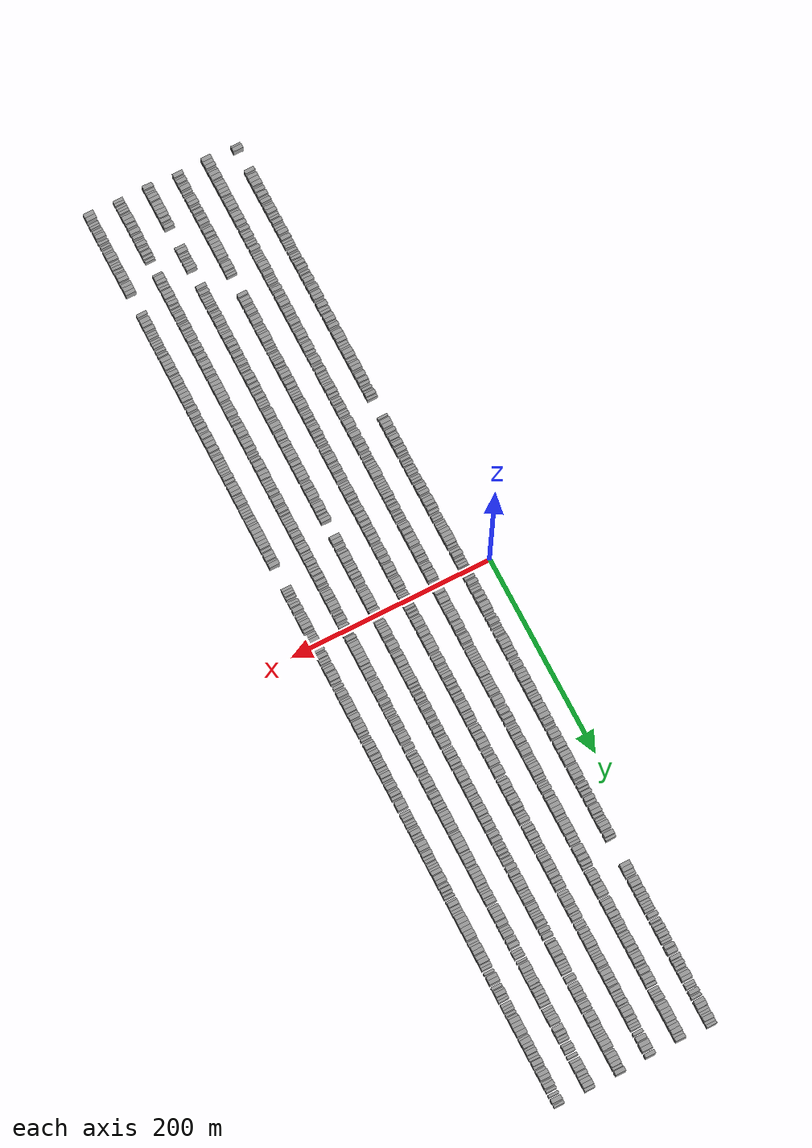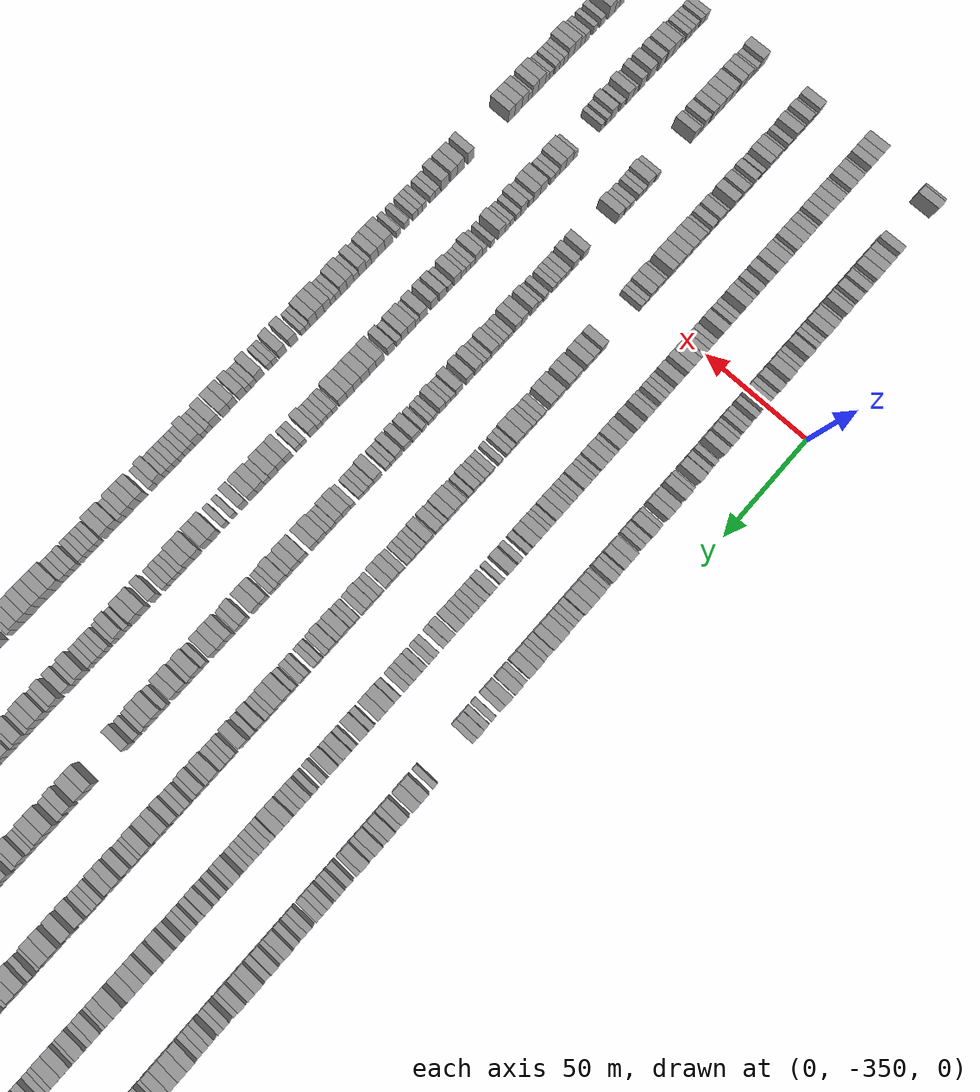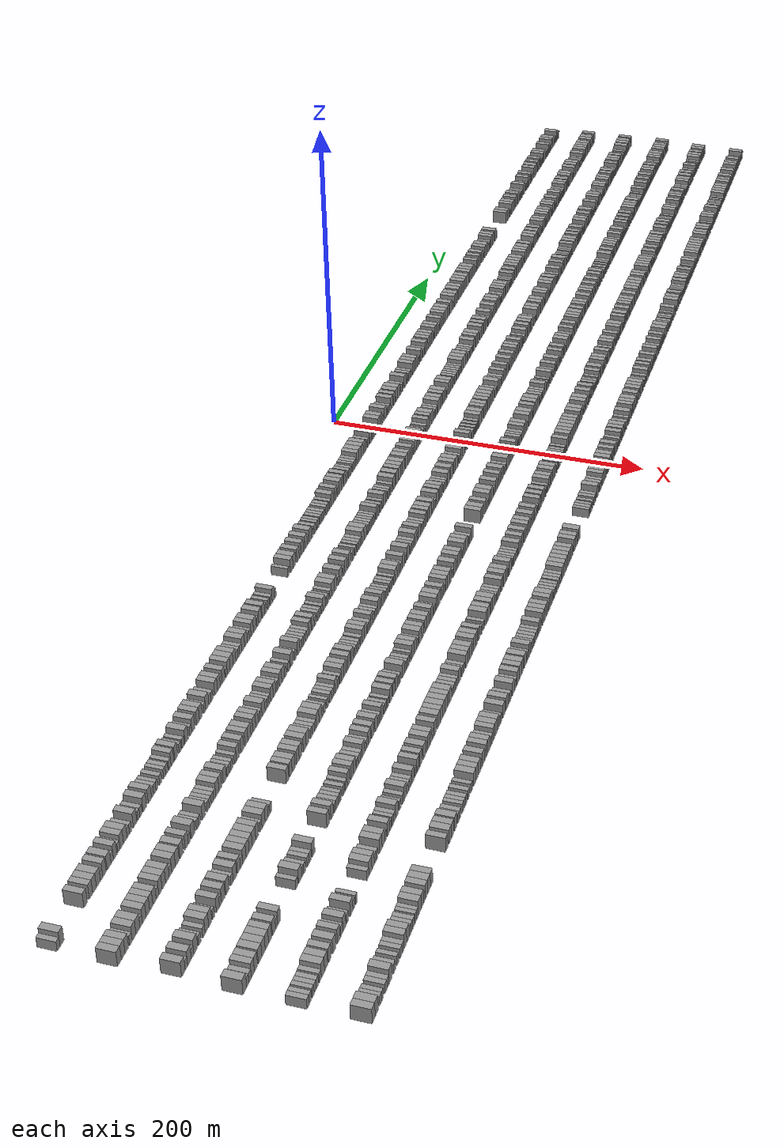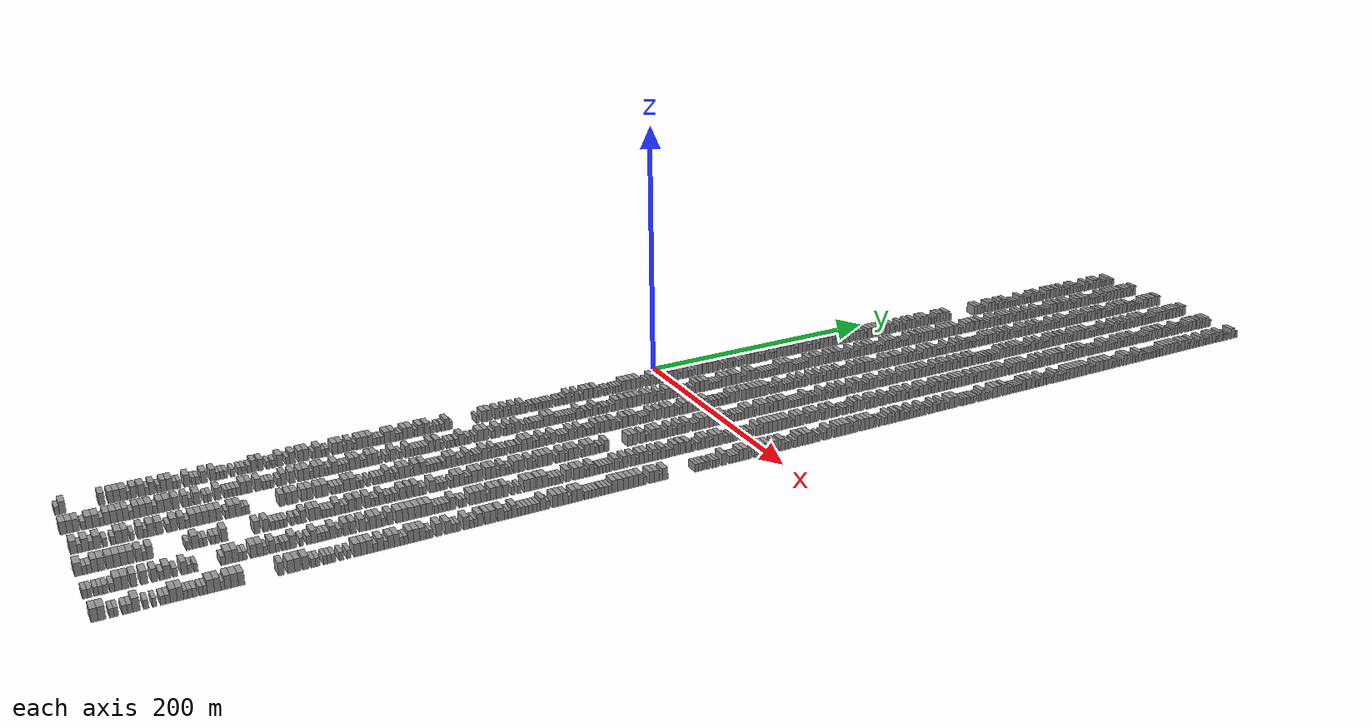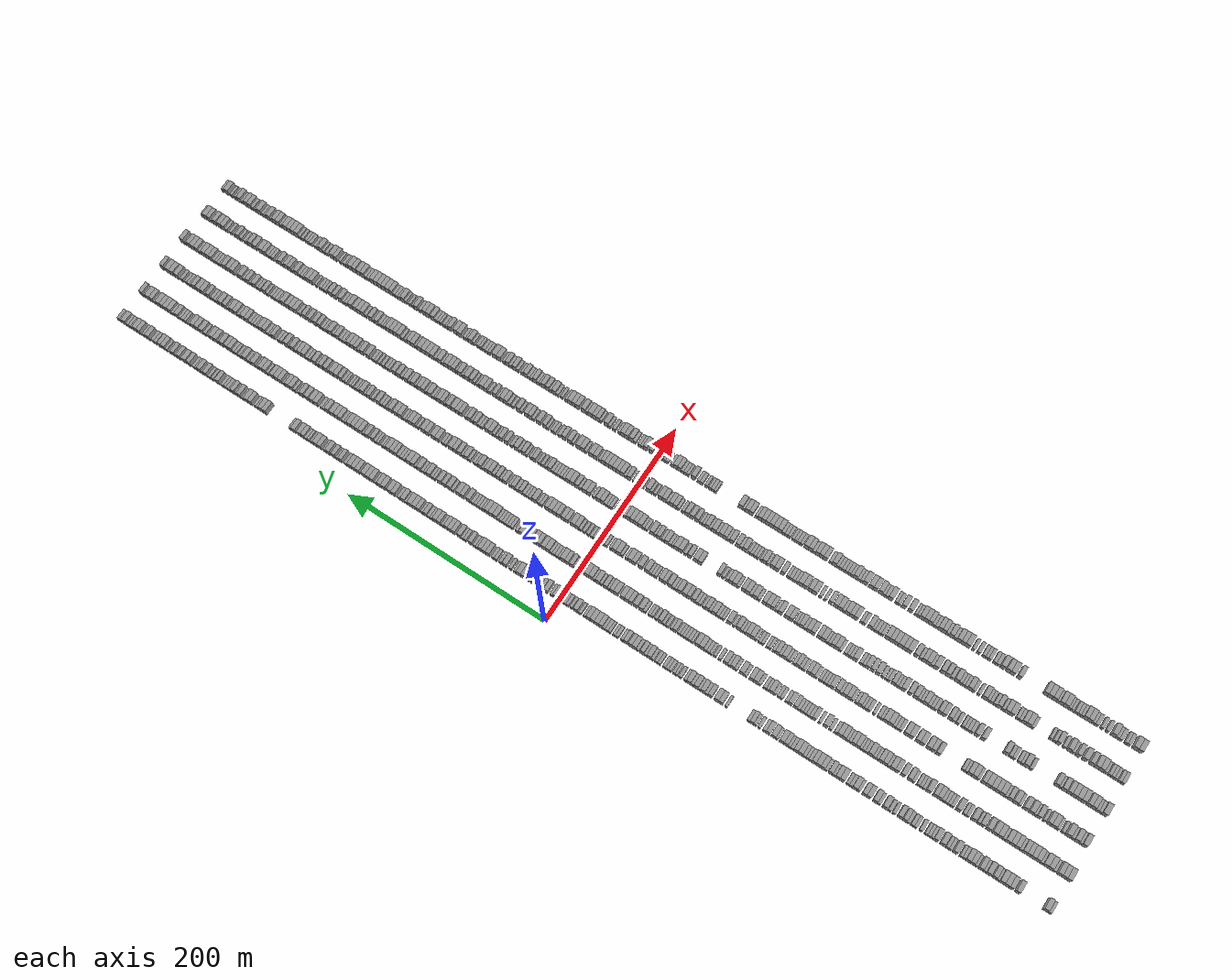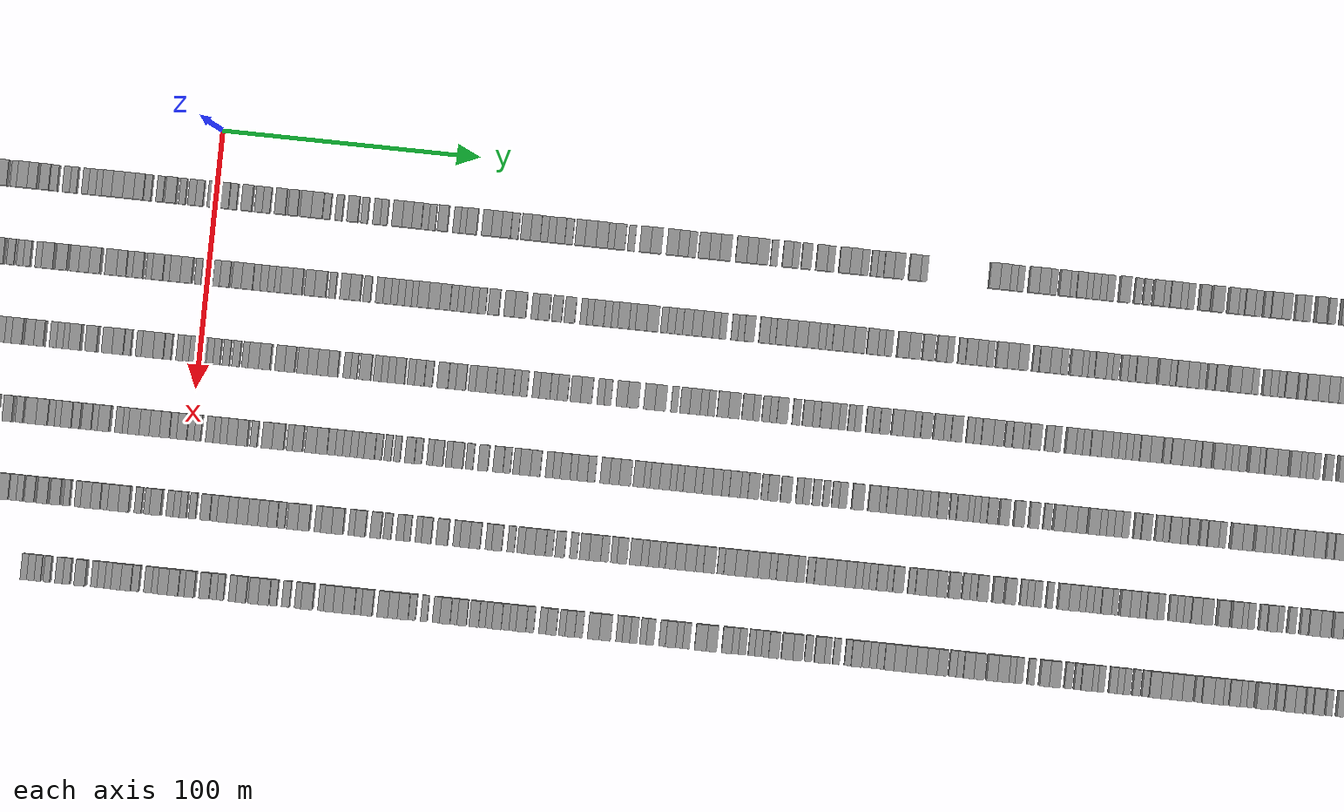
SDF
<sdf version="1.6">
 <world name="default">
  <scene>
   <sky><clouds><speed>12</speed></clouds></sky>
   <ambient>0.4 0.4 0.4 1</ambient>
   <background>0.7 0.7 0.7 1</background>
   <shadows>1</shadows>
  </scene>
  <gravity>0 0 -9.8066</gravity>
  <magnetic_field>6e-06 2.3e-05 -4.2e-05</magnetic_field>
  <physics default="0" name="default_physics" type="ode">
   <ode>
    <solver>
     <type>quick</type>
     <iters>10</iters>
     <sor>1.0</sor>
     <use_dynamic_moi_rescaling>0</use_dynamic_moi_rescaling>
    </solver>
    <constraints>
     <cfm>0</cfm>
     <erp>0.2</erp>
     <contact_max_correcting_vel>100</contact_max_correcting_vel>
     <contact_surface_layer>0.001</contact_surface_layer>
    </constraints>
   </ode>
   <max_step_size>0.004</max_step_size>
   <real_time_factor>1</real_time_factor>
   <real_time_update_rate>250</real_time_update_rate>
  </physics>
  <light name="sun" type="directional">
   <pose>0 0 10 0 0 0</pose>
   <diffuse>0.8 0.8 0.8 1</diffuse>
   <specular>0.2 0.2 0.2 1</specular>
   <attenuation>
    <range>1000</range>
    <constant>0.9</constant>
    <linear>0.01</linear>
    <quadratic>0.001</quadratic>
   </attenuation>
   <direction>-0.5 0.1 -0.9</direction>
  </light>
  <model name="building_1">
   <static>1</static>
   <pose>25.0000 -457.5203 0 0.000000 0.000000 0.000000</pose>
   <link name="link">
    <pose>0 0 3.00 0 0 0</pose>
    <collision name="collision"><geometry><box><size>10.0000 2.9594 6.0000</size></box></geometry></collision>
    <visual name="visual">
     <cast_shadows>0</cast_shadows>
     <geometry><box><size>10.0000 2.9594 6.0000</size></box></geometry>
     <material>
      <script>
       <uri>model://grey_wall/materials/scripts</uri>
       <uri>model://grey_wall/materials/textures</uri>
       <name>vrc/grey_wall</name>
      </script>
     </material>
    </visual>
   </link>
  </model>
  <model name="building_2">
   <static>1</static>
   <pose>25.0000 -453.9683 0 0.000000 0.000000 0.000000</pose>
   <link name="link">
    <pose>0 0 4.50 0 0 0</pose>
    <collision name="collision"><geometry><box><size>10.0000 4.1446 9.0000</size></box></geometry></collision>
    <visual name="visual">
     <cast_shadows>0</cast_shadows>
     <geometry><box><size>10.0000 4.1446 9.0000</size></box></geometry>
     <material>
      <script>
       <uri>model://grey_wall/materials/scripts</uri>
       <uri>model://grey_wall/materials/textures</uri>
       <name>vrc/grey_wall</name>
      </script>
     </material>
    </visual>
   </link>
  </model>
  <model name="building_3">
   <static>1</static>
   <pose>25.0000 -429.2028 0 0.000000 0.000000 0.000000</pose>
   <link name="link">
    <pose>0 0 4.50 0 0 0</pose>
    <collision name="collision"><geometry><box><size>10.0000 3.7955 9.0000</size></box></geometry></collision>
    <visual name="visual">
     <cast_shadows>0</cast_shadows>
     <geometry><box><size>10.0000 3.7955 9.0000</size></box></geometry>
     <material>
      <script>
       <uri>model://grey_wall/materials/scripts</uri>
       <uri>model://grey_wall/materials/textures</uri>
       <name>vrc/grey_wall</name>
      </script>
     </material>
    </visual>
   </link>
  </model>
  <model name="building_4">
   <static>1</static>
   <pose>25.0000 -423.4766 0 0.000000 0.000000 0.000000</pose>
   <link name="link">
    <pose>0 0 4.50 0 0 0</pose>
    <collision name="collision"><geometry><box><size>10.0000 3.6569 9.0000</size></box></geometry></collision>
    <visual name="visual">
     <cast_shadows>0</cast_shadows>
     <geometry><box><size>10.0000 3.6569 9.0000</size></box></geometry>
     <material>
      <script>
       <uri>model://grey_wall/materials/scripts</uri>
       <uri>model://grey_wall/materials/textures</uri>
       <name>vrc/grey_wall</name>
      </script>
     </material>
    </visual>
   </link>
  </model>
  <model name="building_5">
   <static>1</static>
   <pose>25.0000 -419.5611 0 0.000000 0.000000 0.000000</pose>
   <link name="link">
    <pose>0 0 4.50 0 0 0</pose>
    <collision name="collision"><geometry><box><size>10.0000 4.1742 9.0000</size></box></geometry></collision>
    <visual name="visual">
     <cast_shadows>0</cast_shadows>
     <geometry><box><size>10.0000 4.1742 9.0000</size></box></geometry>
     <material>
      <script>
       <uri>model://grey_wall/materials/scripts</uri>
       <uri>model://grey_wall/materials/textures</uri>
       <name>vrc/grey_wall</name>
      </script>
     </material>
    </visual>
   </link>
  </model>
  <model name="building_6">
   <static>1</static>
   <pose>25.0000 -415.2836 0 0.000000 0.000000 0.000000</pose>
   <link name="link">
    <pose>0 0 4.50 0 0 0</pose>
    <collision name="collision"><geometry><box><size>10.0000 4.3807 9.0000</size></box></geometry></collision>
    <visual name="visual">
     <cast_shadows>0</cast_shadows>
     <geometry><box><size>10.0000 4.3807 9.0000</size></box></geometry>
     <material>
      <script>
       <uri>model://grey_wall/materials/scripts</uri>
       <uri>model://grey_wall/materials/textures</uri>
       <name>vrc/grey_wall</name>
      </script>
     </material>
    </visual>
   </link>
  </model>
  <model name="building_7">
   <static>1</static>
   <pose>25.0000 -411.8322 0 0.000000 0.000000 0.000000</pose>
   <link name="link">
    <pose>0 0 3.00 0 0 0</pose>
    <collision name="collision"><geometry><box><size>10.0000 2.5221 6.0000</size></box></geometry></collision>
    <visual name="visual">
     <cast_shadows>0</cast_shadows>
     <geometry><box><size>10.0000 2.5221 6.0000</size></box></geometry>
     <material>
      <script>
       <uri>model://grey_wall/materials/scripts</uri>
       <uri>model://grey_wall/materials/textures</uri>
       <name>vrc/grey_wall</name>
      </script>
     </material>
    </visual>
   </link>
  </model>
  <model name="building_8">
   <static>1</static>
   <pose>25.0000 -408.6667 0 0.000000 0.000000 0.000000</pose>
   <link name="link">
    <pose>0 0 4.50 0 0 0</pose>
    <collision name="collision"><geometry><box><size>10.0000 3.8089 9.0000</size></box></geometry></collision>
    <visual name="visual">
     <cast_shadows>0</cast_shadows>
     <geometry><box><size>10.0000 3.8089 9.0000</size></box></geometry>
     <material>
      <script>
       <uri>model://grey_wall/materials/scripts</uri>
       <uri>model://grey_wall/materials/textures</uri>
       <name>vrc/grey_wall</name>
      </script>
     </material>
    </visual>
   </link>
  </model>
  <model name="building_9">
   <static>1</static>
   <pose>25.0000 -403.5743 0 0.000000 0.000000 0.000000</pose>
   <link name="link">
    <pose>0 0 4.50 0 0 0</pose>
    <collision name="collision"><geometry><box><size>10.0000 4.3760 9.0000</size></box></geometry></collision>
    <visual name="visual">
     <cast_shadows>0</cast_shadows>
     <geometry><box><size>10.0000 4.3760 9.0000</size></box></geometry>
     <material>
      <script>
       <uri>model://grey_wall/materials/scripts</uri>
       <uri>model://grey_wall/materials/textures</uri>
       <name>vrc/grey_wall</name>
      </script>
     </material>
    </visual>
   </link>
  </model>
  <model name="building_10">
   <static>1</static>
   <pose>25.0000 -399.9592 0 0.000000 0.000000 0.000000</pose>
   <link name="link">
    <pose>0 0 3.00 0 0 0</pose>
    <collision name="collision"><geometry><box><size>10.0000 2.8542 6.0000</size></box></geometry></collision>
    <visual name="visual">
     <cast_shadows>0</cast_shadows>
     <geometry><box><size>10.0000 2.8542 6.0000</size></box></geometry>
     <material>
      <script>
       <uri>model://grey_wall/materials/scripts</uri>
       <uri>model://grey_wall/materials/textures</uri>
       <name>vrc/grey_wall</name>
      </script>
     </material>
    </visual>
   </link>
  </model>
  <model name="building_11">
   <static>1</static>
   <pose>25.0000 -396.6053 0 0.000000 0.000000 0.000000</pose>
   <link name="link">
    <pose>0 0 4.50 0 0 0</pose>
    <collision name="collision"><geometry><box><size>10.0000 3.8536 9.0000</size></box></geometry></collision>
    <visual name="visual">
     <cast_shadows>0</cast_shadows>
     <geometry><box><size>10.0000 3.8536 9.0000</size></box></geometry>
     <material>
      <script>
       <uri>model://grey_wall/materials/scripts</uri>
       <uri>model://grey_wall/materials/textures</uri>
       <name>vrc/grey_wall</name>
      </script>
     </material>
    </visual>
   </link>
  </model>
  <model name="building_12">
   <static>1</static>
   <pose>25.0000 -392.3631 0 0.000000 0.000000 0.000000</pose>
   <link name="link">
    <pose>0 0 3.00 0 0 0</pose>
    <collision name="collision"><geometry><box><size>10.0000 2.6307 6.0000</size></box></geometry></collision>
    <visual name="visual">
     <cast_shadows>0</cast_shadows>
     <geometry><box><size>10.0000 2.6307 6.0000</size></box></geometry>
     <material>
      <script>
       <uri>model://grey_wall/materials/scripts</uri>
       <uri>model://grey_wall/materials/textures</uri>
       <name>vrc/grey_wall</name>
      </script>
     </material>
    </visual>
   </link>
  </model>
  <model name="building_13">
   <static>1</static>
   <pose>25.0000 -389.1165 0 0.000000 0.000000 0.000000</pose>
   <link name="link">
    <pose>0 0 4.50 0 0 0</pose>
    <collision name="collision"><geometry><box><size>10.0000 3.8625 9.0000</size></box></geometry></collision>
    <visual name="visual">
     <cast_shadows>0</cast_shadows>
     <geometry><box><size>10.0000 3.8625 9.0000</size></box></geometry>
     <material>
      <script>
       <uri>model://grey_wall/materials/scripts</uri>
       <uri>model://grey_wall/materials/textures</uri>
       <name>vrc/grey_wall</name>
      </script>
     </material>
    </visual>
   </link>
  </model>
  <model name="building_14">
   <static>1</static>
   <pose>25.0000 -385.0935 0 0.000000 0.000000 0.000000</pose>
   <link name="link">
    <pose>0 0 4.50 0 0 0</pose>
    <collision name="collision"><geometry><box><size>10.0000 4.1836 9.0000</size></box></geometry></collision>
    <visual name="visual">
     <cast_shadows>0</cast_shadows>
     <geometry><box><size>10.0000 4.1836 9.0000</size></box></geometry>
     <material>
      <script>
       <uri>model://grey_wall/materials/scripts</uri>
       <uri>model://grey_wall/materials/textures</uri>
       <name>vrc/grey_wall</name>
      </script>
     </material>
    </visual>
   </link>
  </model>
  <model name="building_15">
   <static>1</static>
   <pose>25.0000 -381.6193 0 0.000000 0.000000 0.000000</pose>
   <link name="link">
    <pose>0 0 3.00 0 0 0</pose>
    <collision name="collision"><geometry><box><size>10.0000 2.7649 6.0000</size></box></geometry></collision>
    <visual name="visual">
     <cast_shadows>0</cast_shadows>
     <geometry><box><size>10.0000 2.7649 6.0000</size></box></geometry>
     <material>
      <script>
       <uri>model://grey_wall/materials/scripts</uri>
       <uri>model://grey_wall/materials/textures</uri>
       <name>vrc/grey_wall</name>
      </script>
     </material>
    </visual>
   </link>
  </model>
  <model name="building_16">
   <static>1</static>
   <pose>25.0000 -378.9802 0 0.000000 0.000000 0.000000</pose>
   <link name="link">
    <pose>0 0 3.00 0 0 0</pose>
    <collision name="collision"><geometry><box><size>10.0000 2.5133 6.0000</size></box></geometry></collision>
    <visual name="visual">
     <cast_shadows>0</cast_shadows>
     <geometry><box><size>10.0000 2.5133 6.0000</size></box></geometry>
     <material>
      <script>
       <uri>model://grey_wall/materials/scripts</uri>
       <uri>model://grey_wall/materials/textures</uri>
       <name>vrc/grey_wall</name>
      </script>
     </material>
    </visual>
   </link>
  </model>
  <model name="building_17">
   <static>1</static>
   <pose>25.0000 -373.6902 0 0.000000 0.000000 0.000000</pose>
   <link name="link">
    <pose>0 0 4.50 0 0 0</pose>
    <collision name="collision"><geometry><box><size>10.0000 4.0668 9.0000</size></box></geometry></collision>
    <visual name="visual">
     <cast_shadows>0</cast_shadows>
     <geometry><box><size>10.0000 4.0668 9.0000</size></box></geometry>
     <material>
      <script>
       <uri>model://grey_wall/materials/scripts</uri>
       <uri>model://grey_wall/materials/textures</uri>
       <name>vrc/grey_wall</name>
      </script>
     </material>
    </visual>
   </link>
  </model>
  <model name="building_18">
   <static>1</static>
   <pose>25.0000 -369.3570 0 0.000000 0.000000 0.000000</pose>
   <link name="link">
    <pose>0 0 3.00 0 0 0</pose>
    <collision name="collision"><geometry><box><size>10.0000 2.5995 6.0000</size></box></geometry></collision>
    <visual name="visual">
     <cast_shadows>0</cast_shadows>
     <geometry><box><size>10.0000 2.5995 6.0000</size></box></geometry>
     <material>
      <script>
       <uri>model://grey_wall/materials/scripts</uri>
       <uri>model://grey_wall/materials/textures</uri>
       <name>vrc/grey_wall</name>
      </script>
     </material>
    </visual>
   </link>
  </model>
  <model name="building_19">
   <static>1</static>
   <pose>25.0000 -366.7014 0 0.000000 0.000000 0.000000</pose>
   <link name="link">
    <pose>0 0 3.00 0 0 0</pose>
    <collision name="collision"><geometry><box><size>10.0000 2.7116 6.0000</size></box></geometry></collision>
    <visual name="visual">
     <cast_shadows>0</cast_shadows>
     <geometry><box><size>10.0000 2.7116 6.0000</size></box></geometry>
     <material>
      <script>
       <uri>model://grey_wall/materials/scripts</uri>
       <uri>model://grey_wall/materials/textures</uri>
       <name>vrc/grey_wall</name>
      </script>
     </material>
    </visual>
   </link>
  </model>
  <model name="building_20">
   <static>1</static>
   <pose>25.0000 -362.2099 0 0.000000 0.000000 0.000000</pose>
   <link name="link">
    <pose>0 0 4.50 0 0 0</pose>
    <collision name="collision"><geometry><box><size>10.0000 4.2715 9.0000</size></box></geometry></collision>
    <visual name="visual">
     <cast_shadows>0</cast_shadows>
     <geometry><box><size>10.0000 4.2715 9.0000</size></box></geometry>
     <material>
      <script>
       <uri>model://grey_wall/materials/scripts</uri>
       <uri>model://grey_wall/materials/textures</uri>
       <name>vrc/grey_wall</name>
      </script>
     </material>
    </visual>
   </link>
  </model>
  <model name="building_21">
   <static>1</static>
   <pose>25.0000 -356.0987 0 0.000000 0.000000 0.000000</pose>
   <link name="link">
    <pose>0 0 4.50 0 0 0</pose>
    <collision name="collision"><geometry><box><size>10.0000 3.9509 9.0000</size></box></geometry></collision>
    <visual name="visual">
     <cast_shadows>0</cast_shadows>
     <geometry><box><size>10.0000 3.9509 9.0000</size></box></geometry>
     <material>
      <script>
       <uri>model://grey_wall/materials/scripts</uri>
       <uri>model://grey_wall/materials/textures</uri>
       <name>vrc/grey_wall</name>
      </script>
     </material>
    </visual>
   </link>
  </model>
  <model name="building_22">
   <static>1</static>
   <pose>25.0000 -352.8264 0 0.000000 0.000000 0.000000</pose>
   <link name="link">
    <pose>0 0 3.00 0 0 0</pose>
    <collision name="collision"><geometry><box><size>10.0000 2.5937 6.0000</size></box></geometry></collision>
    <visual name="visual">
     <cast_shadows>0</cast_shadows>
     <geometry><box><size>10.0000 2.5937 6.0000</size></box></geometry>
     <material>
      <script>
       <uri>model://grey_wall/materials/scripts</uri>
       <uri>model://grey_wall/materials/textures</uri>
       <name>vrc/grey_wall</name>
      </script>
     </material>
    </visual>
   </link>
  </model>
  <model name="building_23">
   <static>1</static>
   <pose>25.0000 -350.1174 0 0.000000 0.000000 0.000000</pose>
   <link name="link">
    <pose>0 0 3.00 0 0 0</pose>
    <collision name="collision"><geometry><box><size>10.0000 2.8245 6.0000</size></box></geometry></collision>
    <visual name="visual">
     <cast_shadows>0</cast_shadows>
     <geometry><box><size>10.0000 2.8245 6.0000</size></box></geometry>
     <material>
      <script>
       <uri>model://grey_wall/materials/scripts</uri>
       <uri>model://grey_wall/materials/textures</uri>
       <name>vrc/grey_wall</name>
      </script>
     </material>
    </visual>
   </link>
  </model>
  <model name="building_24">
   <static>1</static>
   <pose>25.0000 -347.4698 0 0.000000 0.000000 0.000000</pose>
   <link name="link">
    <pose>0 0 3.00 0 0 0</pose>
    <collision name="collision"><geometry><box><size>10.0000 2.4707 6.0000</size></box></geometry></collision>
    <visual name="visual">
     <cast_shadows>0</cast_shadows>
     <geometry><box><size>10.0000 2.4707 6.0000</size></box></geometry>
     <material>
      <script>
       <uri>model://grey_wall/materials/scripts</uri>
       <uri>model://grey_wall/materials/textures</uri>
       <name>vrc/grey_wall</name>
      </script>
     </material>
    </visual>
   </link>
  </model>
  <model name="building_25">
   <static>1</static>
   <pose>25.0000 -342.7646 0 0.000000 0.000000 0.000000</pose>
   <link name="link">
    <pose>0 0 3.00 0 0 0</pose>
    <collision name="collision"><geometry><box><size>10.0000 2.9396 6.0000</size></box></geometry></collision>
    <visual name="visual">
     <cast_shadows>0</cast_shadows>
     <geometry><box><size>10.0000 2.9396 6.0000</size></box></geometry>
     <material>
      <script>
       <uri>model://grey_wall/materials/scripts</uri>
       <uri>model://grey_wall/materials/textures</uri>
       <name>vrc/grey_wall</name>
      </script>
     </material>
    </visual>
   </link>
  </model>
  <model name="building_26">
   <static>1</static>
   <pose>25.0000 -337.9768 0 0.000000 0.000000 0.000000</pose>
   <link name="link">
    <pose>0 0 3.00 0 0 0</pose>
    <collision name="collision"><geometry><box><size>10.0000 2.6360 6.0000</size></box></geometry></collision>
    <visual name="visual">
     <cast_shadows>0</cast_shadows>
     <geometry><box><size>10.0000 2.6360 6.0000</size></box></geometry>
     <material>
      <script>
       <uri>model://grey_wall/materials/scripts</uri>
       <uri>model://grey_wall/materials/textures</uri>
       <name>vrc/grey_wall</name>
      </script>
     </material>
    </visual>
   </link>
  </model>
  <model name="building_27">
   <static>1</static>
   <pose>25.0000 -335.2163 0 0.000000 0.000000 0.000000</pose>
   <link name="link">
    <pose>0 0 3.00 0 0 0</pose>
    <collision name="collision"><geometry><box><size>10.0000 2.8850 6.0000</size></box></geometry></collision>
    <visual name="visual">
     <cast_shadows>0</cast_shadows>
     <geometry><box><size>10.0000 2.8850 6.0000</size></box></geometry>
     <material>
      <script>
       <uri>model://grey_wall/materials/scripts</uri>
       <uri>model://grey_wall/materials/textures</uri>
       <name>vrc/grey_wall</name>
      </script>
     </material>
    </visual>
   </link>
  </model>
  <model name="building_28">
   <static>1</static>
   <pose>25.0000 -331.3370 0 0.000000 0.000000 0.000000</pose>
   <link name="link">
    <pose>0 0 3.00 0 0 0</pose>
    <collision name="collision"><geometry><box><size>10.0000 2.8737 6.0000</size></box></geometry></collision>
    <visual name="visual">
     <cast_shadows>0</cast_shadows>
     <geometry><box><size>10.0000 2.8737 6.0000</size></box></geometry>
     <material>
      <script>
       <uri>model://grey_wall/materials/scripts</uri>
       <uri>model://grey_wall/materials/textures</uri>
       <name>vrc/grey_wall</name>
      </script>
     </material>
    </visual>
   </link>
  </model>
  <model name="building_29">
   <static>1</static>
   <pose>25.0000 -328.0822 0 0.000000 0.000000 0.000000</pose>
   <link name="link">
    <pose>0 0 4.50 0 0 0</pose>
    <collision name="collision"><geometry><box><size>10.0000 3.6358 9.0000</size></box></geometry></collision>
    <visual name="visual">
     <cast_shadows>0</cast_shadows>
     <geometry><box><size>10.0000 3.6358 9.0000</size></box></geometry>
     <material>
      <script>
       <uri>model://grey_wall/materials/scripts</uri>
       <uri>model://grey_wall/materials/textures</uri>
       <name>vrc/grey_wall</name>
      </script>
     </material>
    </visual>
   </link>
  </model>
  <model name="building_30">
   <static>1</static>
   <pose>25.0000 -323.3908 0 0.000000 0.000000 0.000000</pose>
   <link name="link">
    <pose>0 0 4.50 0 0 0</pose>
    <collision name="collision"><geometry><box><size>10.0000 3.7471 9.0000</size></box></geometry></collision>
    <visual name="visual">
     <cast_shadows>0</cast_shadows>
     <geometry><box><size>10.0000 3.7471 9.0000</size></box></geometry>
     <material>
      <script>
       <uri>model://grey_wall/materials/scripts</uri>
       <uri>model://grey_wall/materials/textures</uri>
       <name>vrc/grey_wall</name>
      </script>
     </material>
    </visual>
   </link>
  </model>
  <model name="building_31">
   <static>1</static>
   <pose>25.0000 -318.2266 0 0.000000 0.000000 0.000000</pose>
   <link name="link">
    <pose>0 0 3.00 0 0 0</pose>
    <collision name="collision"><geometry><box><size>10.0000 2.5813 6.0000</size></box></geometry></collision>
    <visual name="visual">
     <cast_shadows>0</cast_shadows>
     <geometry><box><size>10.0000 2.5813 6.0000</size></box></geometry>
     <material>
      <script>
       <uri>model://grey_wall/materials/scripts</uri>
       <uri>model://grey_wall/materials/textures</uri>
       <name>vrc/grey_wall</name>
      </script>
     </material>
    </visual>
   </link>
  </model>
  <model name="building_32">
   <static>1</static>
   <pose>25.0000 -314.5024 0 0.000000 0.000000 0.000000</pose>
   <link name="link">
    <pose>0 0 3.00 0 0 0</pose>
    <collision name="collision"><geometry><box><size>10.0000 2.8670 6.0000</size></box></geometry></collision>
    <visual name="visual">
     <cast_shadows>0</cast_shadows>
     <geometry><box><size>10.0000 2.8670 6.0000</size></box></geometry>
     <material>
      <script>
       <uri>model://grey_wall/materials/scripts</uri>
       <uri>model://grey_wall/materials/textures</uri>
       <name>vrc/grey_wall</name>
      </script>
     </material>
    </visual>
   </link>
  </model>
  <model name="building_33">
   <static>1</static>
   <pose>25.0000 -309.9465 0 0.000000 0.000000 0.000000</pose>
   <link name="link">
    <pose>0 0 4.50 0 0 0</pose>
    <collision name="collision"><geometry><box><size>10.0000 4.2448 9.0000</size></box></geometry></collision>
    <visual name="visual">
     <cast_shadows>0</cast_shadows>
     <geometry><box><size>10.0000 4.2448 9.0000</size></box></geometry>
     <material>
      <script>
       <uri>model://grey_wall/materials/scripts</uri>
       <uri>model://grey_wall/materials/textures</uri>
       <name>vrc/grey_wall</name>
      </script>
     </material>
    </visual>
   </link>
  </model>
  <model name="building_34">
   <static>1</static>
   <pose>25.0000 -304.5133 0 0.000000 0.000000 0.000000</pose>
   <link name="link">
    <pose>0 0 3.00 0 0 0</pose>
    <collision name="collision"><geometry><box><size>10.0000 2.6217 6.0000</size></box></geometry></collision>
    <visual name="visual">
     <cast_shadows>0</cast_shadows>
     <geometry><box><size>10.0000 2.6217 6.0000</size></box></geometry>
     <material>
      <script>
       <uri>model://grey_wall/materials/scripts</uri>
       <uri>model://grey_wall/materials/textures</uri>
       <name>vrc/grey_wall</name>
      </script>
     </material>
    </visual>
   </link>
  </model>
  <model name="building_35">
   <static>1</static>
   <pose>25.0000 -301.1236 0 0.000000 0.000000 0.000000</pose>
   <link name="link">
    <pose>0 0 4.50 0 0 0</pose>
    <collision name="collision"><geometry><box><size>10.0000 4.1577 9.0000</size></box></geometry></collision>
    <visual name="visual">
     <cast_shadows>0</cast_shadows>
     <geometry><box><size>10.0000 4.1577 9.0000</size></box></geometry>
     <material>
      <script>
       <uri>model://grey_wall/materials/scripts</uri>
       <uri>model://grey_wall/materials/textures</uri>
       <name>vrc/grey_wall</name>
      </script>
     </material>
    </visual>
   </link>
  </model>
  <model name="building_36">
   <static>1</static>
   <pose>25.0000 -295.1092 0 0.000000 0.000000 0.000000</pose>
   <link name="link">
    <pose>0 0 4.50 0 0 0</pose>
    <collision name="collision"><geometry><box><size>10.0000 3.8711 9.0000</size></box></geometry></collision>
    <visual name="visual">
     <cast_shadows>0</cast_shadows>
     <geometry><box><size>10.0000 3.8711 9.0000</size></box></geometry>
     <material>
      <script>
       <uri>model://grey_wall/materials/scripts</uri>
       <uri>model://grey_wall/materials/textures</uri>
       <name>vrc/grey_wall</name>
      </script>
     </material>
    </visual>
   </link>
  </model>
  <model name="building_37">
   <static>1</static>
   <pose>25.0000 -291.2293 0 0.000000 0.000000 0.000000</pose>
   <link name="link">
    <pose>0 0 4.50 0 0 0</pose>
    <collision name="collision"><geometry><box><size>10.0000 3.8886 9.0000</size></box></geometry></collision>
    <visual name="visual">
     <cast_shadows>0</cast_shadows>
     <geometry><box><size>10.0000 3.8886 9.0000</size></box></geometry>
     <material>
      <script>
       <uri>model://grey_wall/materials/scripts</uri>
       <uri>model://grey_wall/materials/textures</uri>
       <name>vrc/grey_wall</name>
      </script>
     </material>
    </visual>
   </link>
  </model>
  <model name="building_38">
   <static>1</static>
   <pose>25.0000 -286.0181 0 0.000000 0.000000 0.000000</pose>
   <link name="link">
    <pose>0 0 3.00 0 0 0</pose>
    <collision name="collision"><geometry><box><size>10.0000 2.5339 6.0000</size></box></geometry></collision>
    <visual name="visual">
     <cast_shadows>0</cast_shadows>
     <geometry><box><size>10.0000 2.5339 6.0000</size></box></geometry>
     <material>
      <script>
       <uri>model://grey_wall/materials/scripts</uri>
       <uri>model://grey_wall/materials/textures</uri>
       <name>vrc/grey_wall</name>
      </script>
     </material>
    </visual>
   </link>
  </model>
  <model name="building_39">
   <static>1</static>
   <pose>25.0000 -282.5624 0 0.000000 0.000000 0.000000</pose>
   <link name="link">
    <pose>0 0 4.50 0 0 0</pose>
    <collision name="collision"><geometry><box><size>10.0000 4.3776 9.0000</size></box></geometry></collision>
    <visual name="visual">
     <cast_shadows>0</cast_shadows>
     <geometry><box><size>10.0000 4.3776 9.0000</size></box></geometry>
     <material>
      <script>
       <uri>model://grey_wall/materials/scripts</uri>
       <uri>model://grey_wall/materials/textures</uri>
       <name>vrc/grey_wall</name>
      </script>
     </material>
    </visual>
   </link>
  </model>
  <model name="building_40">
   <static>1</static>
   <pose>25.0000 -278.8828 0 0.000000 0.000000 0.000000</pose>
   <link name="link">
    <pose>0 0 3.00 0 0 0</pose>
    <collision name="collision"><geometry><box><size>10.0000 2.9815 6.0000</size></box></geometry></collision>
    <visual name="visual">
     <cast_shadows>0</cast_shadows>
     <geometry><box><size>10.0000 2.9815 6.0000</size></box></geometry>
     <material>
      <script>
       <uri>model://grey_wall/materials/scripts</uri>
       <uri>model://grey_wall/materials/textures</uri>
       <name>vrc/grey_wall</name>
      </script>
     </material>
    </visual>
   </link>
  </model>
  <model name="building_41">
   <static>1</static>
   <pose>25.0000 -276.0156 0 0.000000 0.000000 0.000000</pose>
   <link name="link">
    <pose>0 0 3.00 0 0 0</pose>
    <collision name="collision"><geometry><box><size>10.0000 2.7528 6.0000</size></box></geometry></collision>
    <visual name="visual">
     <cast_shadows>0</cast_shadows>
     <geometry><box><size>10.0000 2.7528 6.0000</size></box></geometry>
     <material>
      <script>
       <uri>model://grey_wall/materials/scripts</uri>
       <uri>model://grey_wall/materials/textures</uri>
       <name>vrc/grey_wall</name>
      </script>
     </material>
    </visual>
   </link>
  </model>
  <model name="building_42">
   <static>1</static>
   <pose>25.0000 -270.5534 0 0.000000 0.000000 0.000000</pose>
   <link name="link">
    <pose>0 0 4.50 0 0 0</pose>
    <collision name="collision"><geometry><box><size>10.0000 4.1716 9.0000</size></box></geometry></collision>
    <visual name="visual">
     <cast_shadows>0</cast_shadows>
     <geometry><box><size>10.0000 4.1716 9.0000</size></box></geometry>
     <material>
      <script>
       <uri>model://grey_wall/materials/scripts</uri>
       <uri>model://grey_wall/materials/textures</uri>
       <name>vrc/grey_wall</name>
      </script>
     </material>
    </visual>
   </link>
  </model>
  <model name="building_43">
   <static>1</static>
   <pose>25.0000 -266.5493 0 0.000000 0.000000 0.000000</pose>
   <link name="link">
    <pose>0 0 4.50 0 0 0</pose>
    <collision name="collision"><geometry><box><size>10.0000 3.8367 9.0000</size></box></geometry></collision>
    <visual name="visual">
     <cast_shadows>0</cast_shadows>
     <geometry><box><size>10.0000 3.8367 9.0000</size></box></geometry>
     <material>
      <script>
       <uri>model://grey_wall/materials/scripts</uri>
       <uri>model://grey_wall/materials/textures</uri>
       <name>vrc/grey_wall</name>
      </script>
     </material>
    </visual>
   </link>
  </model>
  <model name="building_44">
   <static>1</static>
   <pose>25.0000 -263.3040 0 0.000000 0.000000 0.000000</pose>
   <link name="link">
    <pose>0 0 3.00 0 0 0</pose>
    <collision name="collision"><geometry><box><size>10.0000 2.6540 6.0000</size></box></geometry></collision>
    <visual name="visual">
     <cast_shadows>0</cast_shadows>
     <geometry><box><size>10.0000 2.6540 6.0000</size></box></geometry>
     <material>
      <script>
       <uri>model://grey_wall/materials/scripts</uri>
       <uri>model://grey_wall/materials/textures</uri>
       <name>vrc/grey_wall</name>
      </script>
     </material>
    </visual>
   </link>
  </model>
  <model name="building_45">
   <static>1</static>
   <pose>25.0000 -260.0504 0 0.000000 0.000000 0.000000</pose>
   <link name="link">
    <pose>0 0 4.50 0 0 0</pose>
    <collision name="collision"><geometry><box><size>10.0000 3.8531 9.0000</size></box></geometry></collision>
    <visual name="visual">
     <cast_shadows>0</cast_shadows>
     <geometry><box><size>10.0000 3.8531 9.0000</size></box></geometry>
     <material>
      <script>
       <uri>model://grey_wall/materials/scripts</uri>
       <uri>model://grey_wall/materials/textures</uri>
       <name>vrc/grey_wall</name>
      </script>
     </material>
    </visual>
   </link>
  </model>
  <model name="building_46">
   <static>1</static>
   <pose>25.0000 -255.9200 0 0.000000 0.000000 0.000000</pose>
   <link name="link">
    <pose>0 0 3.00 0 0 0</pose>
    <collision name="collision"><geometry><box><size>10.0000 2.4077 6.0000</size></box></geometry></collision>
    <visual name="visual">
     <cast_shadows>0</cast_shadows>
     <geometry><box><size>10.0000 2.4077 6.0000</size></box></geometry>
     <material>
      <script>
       <uri>model://grey_wall/materials/scripts</uri>
       <uri>model://grey_wall/materials/textures</uri>
       <name>vrc/grey_wall</name>
      </script>
     </material>
    </visual>
   </link>
  </model>
  <model name="building_47">
   <static>1</static>
   <pose>25.0000 -252.7538 0 0.000000 0.000000 0.000000</pose>
   <link name="link">
    <pose>0 0 4.50 0 0 0</pose>
    <collision name="collision"><geometry><box><size>10.0000 3.9247 9.0000</size></box></geometry></collision>
    <visual name="visual">
     <cast_shadows>0</cast_shadows>
     <geometry><box><size>10.0000 3.9247 9.0000</size></box></geometry>
     <material>
      <script>
       <uri>model://grey_wall/materials/scripts</uri>
       <uri>model://grey_wall/materials/textures</uri>
       <name>vrc/grey_wall</name>
      </script>
     </material>
    </visual>
   </link>
  </model>
  <model name="building_48">
   <static>1</static>
   <pose>25.0000 -248.5804 0 0.000000 0.000000 0.000000</pose>
   <link name="link">
    <pose>0 0 4.50 0 0 0</pose>
    <collision name="collision"><geometry><box><size>10.0000 4.4221 9.0000</size></box></geometry></collision>
    <visual name="visual">
     <cast_shadows>0</cast_shadows>
     <geometry><box><size>10.0000 4.4221 9.0000</size></box></geometry>
     <material>
      <script>
       <uri>model://grey_wall/materials/scripts</uri>
       <uri>model://grey_wall/materials/textures</uri>
       <name>vrc/grey_wall</name>
      </script>
     </material>
    </visual>
   </link>
  </model>
  <model name="building_49">
   <static>1</static>
   <pose>25.0000 -244.5217 0 0.000000 0.000000 0.000000</pose>
   <link name="link">
    <pose>0 0 4.50 0 0 0</pose>
    <collision name="collision"><geometry><box><size>10.0000 3.6953 9.0000</size></box></geometry></collision>
    <visual name="visual">
     <cast_shadows>0</cast_shadows>
     <geometry><box><size>10.0000 3.6953 9.0000</size></box></geometry>
     <material>
      <script>
       <uri>model://grey_wall/materials/scripts</uri>
       <uri>model://grey_wall/materials/textures</uri>
       <name>vrc/grey_wall</name>
      </script>
     </material>
    </visual>
   </link>
  </model>
  <model name="building_50">
   <static>1</static>
   <pose>25.0000 -241.1943 0 0.000000 0.000000 0.000000</pose>
   <link name="link">
    <pose>0 0 3.00 0 0 0</pose>
    <collision name="collision"><geometry><box><size>10.0000 2.9596 6.0000</size></box></geometry></collision>
    <visual name="visual">
     <cast_shadows>0</cast_shadows>
     <geometry><box><size>10.0000 2.9596 6.0000</size></box></geometry>
     <material>
      <script>
       <uri>model://grey_wall/materials/scripts</uri>
       <uri>model://grey_wall/materials/textures</uri>
       <name>vrc/grey_wall</name>
      </script>
     </material>
    </visual>
   </link>
  </model>
  <model name="building_51">
   <static>1</static>
   <pose>25.0000 -238.4130 0 0.000000 0.000000 0.000000</pose>
   <link name="link">
    <pose>0 0 3.00 0 0 0</pose>
    <collision name="collision"><geometry><box><size>10.0000 2.6029 6.0000</size></box></geometry></collision>
    <visual name="visual">
     <cast_shadows>0</cast_shadows>
     <geometry><box><size>10.0000 2.6029 6.0000</size></box></geometry>
     <material>
      <script>
       <uri>model://grey_wall/materials/scripts</uri>
       <uri>model://grey_wall/materials/textures</uri>
       <name>vrc/grey_wall</name>
      </script>
     </material>
    </visual>
   </link>
  </model>
  <model name="building_52">
   <static>1</static>
   <pose>25.0000 -235.6699 0 0.000000 0.000000 0.000000</pose>
   <link name="link">
    <pose>0 0 3.00 0 0 0</pose>
    <collision name="collision"><geometry><box><size>10.0000 2.8835 6.0000</size></box></geometry></collision>
    <visual name="visual">
     <cast_shadows>0</cast_shadows>
     <geometry><box><size>10.0000 2.8835 6.0000</size></box></geometry>
     <material>
      <script>
       <uri>model://grey_wall/materials/scripts</uri>
       <uri>model://grey_wall/materials/textures</uri>
       <name>vrc/grey_wall</name>
      </script>
     </material>
    </visual>
   </link>
  </model>
  <model name="building_53">
   <static>1</static>
   <pose>25.0000 -232.0106 0 0.000000 0.000000 0.000000</pose>
   <link name="link">
    <pose>0 0 4.50 0 0 0</pose>
    <collision name="collision"><geometry><box><size>10.0000 4.4352 9.0000</size></box></geometry></collision>
    <visual name="visual">
     <cast_shadows>0</cast_shadows>
     <geometry><box><size>10.0000 4.4352 9.0000</size></box></geometry>
     <material>
      <script>
       <uri>model://grey_wall/materials/scripts</uri>
       <uri>model://grey_wall/materials/textures</uri>
       <name>vrc/grey_wall</name>
      </script>
     </material>
    </visual>
   </link>
  </model>
  <model name="building_54">
   <static>1</static>
   <pose>25.0000 -227.7891 0 0.000000 0.000000 0.000000</pose>
   <link name="link">
    <pose>0 0 4.50 0 0 0</pose>
    <collision name="collision"><geometry><box><size>10.0000 4.0078 9.0000</size></box></geometry></collision>
    <visual name="visual">
     <cast_shadows>0</cast_shadows>
     <geometry><box><size>10.0000 4.0078 9.0000</size></box></geometry>
     <material>
      <script>
       <uri>model://grey_wall/materials/scripts</uri>
       <uri>model://grey_wall/materials/textures</uri>
       <name>vrc/grey_wall</name>
      </script>
     </material>
    </visual>
   </link>
  </model>
  <model name="building_55">
   <static>1</static>
   <pose>25.0000 -224.3146 0 0.000000 0.000000 0.000000</pose>
   <link name="link">
    <pose>0 0 3.00 0 0 0</pose>
    <collision name="collision"><geometry><box><size>10.0000 2.9411 6.0000</size></box></geometry></collision>
    <visual name="visual">
     <cast_shadows>0</cast_shadows>
     <geometry><box><size>10.0000 2.9411 6.0000</size></box></geometry>
     <material>
      <script>
       <uri>model://grey_wall/materials/scripts</uri>
       <uri>model://grey_wall/materials/textures</uri>
       <name>vrc/grey_wall</name>
      </script>
     </material>
    </visual>
   </link>
  </model>
  <model name="building_56">
   <static>1</static>
   <pose>25.0000 -221.6386 0 0.000000 0.000000 0.000000</pose>
   <link name="link">
    <pose>0 0 3.00 0 0 0</pose>
    <collision name="collision"><geometry><box><size>10.0000 2.4108 6.0000</size></box></geometry></collision>
    <visual name="visual">
     <cast_shadows>0</cast_shadows>
     <geometry><box><size>10.0000 2.4108 6.0000</size></box></geometry>
     <material>
      <script>
       <uri>model://grey_wall/materials/scripts</uri>
       <uri>model://grey_wall/materials/textures</uri>
       <name>vrc/grey_wall</name>
      </script>
     </material>
    </visual>
   </link>
  </model>
  <model name="building_57">
   <static>1</static>
   <pose>25.0000 -218.6162 0 0.000000 0.000000 0.000000</pose>
   <link name="link">
    <pose>0 0 4.50 0 0 0</pose>
    <collision name="collision"><geometry><box><size>10.0000 3.6340 9.0000</size></box></geometry></collision>
    <visual name="visual">
     <cast_shadows>0</cast_shadows>
     <geometry><box><size>10.0000 3.6340 9.0000</size></box></geometry>
     <material>
      <script>
       <uri>model://grey_wall/materials/scripts</uri>
       <uri>model://grey_wall/materials/textures</uri>
       <name>vrc/grey_wall</name>
      </script>
     </material>
    </visual>
   </link>
  </model>
  <model name="building_58">
   <static>1</static>
   <pose>25.0000 -214.6538 0 0.000000 0.000000 0.000000</pose>
   <link name="link">
    <pose>0 0 4.50 0 0 0</pose>
    <collision name="collision"><geometry><box><size>10.0000 4.2908 9.0000</size></box></geometry></collision>
    <visual name="visual">
     <cast_shadows>0</cast_shadows>
     <geometry><box><size>10.0000 4.2908 9.0000</size></box></geometry>
     <material>
      <script>
       <uri>model://grey_wall/materials/scripts</uri>
       <uri>model://grey_wall/materials/textures</uri>
       <name>vrc/grey_wall</name>
      </script>
     </material>
    </visual>
   </link>
  </model>
  <model name="building_59">
   <static>1</static>
   <pose>25.0000 -210.2531 0 0.000000 0.000000 0.000000</pose>
   <link name="link">
    <pose>0 0 3.00 0 0 0</pose>
    <collision name="collision"><geometry><box><size>10.0000 2.5106 6.0000</size></box></geometry></collision>
    <visual name="visual">
     <cast_shadows>0</cast_shadows>
     <geometry><box><size>10.0000 2.5106 6.0000</size></box></geometry>
     <material>
      <script>
       <uri>model://grey_wall/materials/scripts</uri>
       <uri>model://grey_wall/materials/textures</uri>
       <name>vrc/grey_wall</name>
      </script>
     </material>
    </visual>
   </link>
  </model>
  <model name="building_60">
   <static>1</static>
   <pose>25.0000 -206.8731 0 0.000000 0.000000 0.000000</pose>
   <link name="link">
    <pose>0 0 4.50 0 0 0</pose>
    <collision name="collision"><geometry><box><size>10.0000 4.2494 9.0000</size></box></geometry></collision>
    <visual name="visual">
     <cast_shadows>0</cast_shadows>
     <geometry><box><size>10.0000 4.2494 9.0000</size></box></geometry>
     <material>
      <script>
       <uri>model://grey_wall/materials/scripts</uri>
       <uri>model://grey_wall/materials/textures</uri>
       <name>vrc/grey_wall</name>
      </script>
     </material>
    </visual>
   </link>
  </model>
  <model name="building_61">
   <static>1</static>
   <pose>25.0000 -201.7573 0 0.000000 0.000000 0.000000</pose>
   <link name="link">
    <pose>0 0 4.50 0 0 0</pose>
    <collision name="collision"><geometry><box><size>10.0000 3.9822 9.0000</size></box></geometry></collision>
    <visual name="visual">
     <cast_shadows>0</cast_shadows>
     <geometry><box><size>10.0000 3.9822 9.0000</size></box></geometry>
     <material>
      <script>
       <uri>model://grey_wall/materials/scripts</uri>
       <uri>model://grey_wall/materials/textures</uri>
       <name>vrc/grey_wall</name>
      </script>
     </material>
    </visual>
   </link>
  </model>
  <model name="building_62">
   <static>1</static>
   <pose>25.0000 -198.2822 0 0.000000 0.000000 0.000000</pose>
   <link name="link">
    <pose>0 0 3.00 0 0 0</pose>
    <collision name="collision"><geometry><box><size>10.0000 2.9679 6.0000</size></box></geometry></collision>
    <visual name="visual">
     <cast_shadows>0</cast_shadows>
     <geometry><box><size>10.0000 2.9679 6.0000</size></box></geometry>
     <material>
      <script>
       <uri>model://grey_wall/materials/scripts</uri>
       <uri>model://grey_wall/materials/textures</uri>
       <name>vrc/grey_wall</name>
      </script>
     </material>
    </visual>
   </link>
  </model>
  <model name="building_63">
   <static>1</static>
   <pose>25.0000 -193.4689 0 0.000000 0.000000 0.000000</pose>
   <link name="link">
    <pose>0 0 3.00 0 0 0</pose>
    <collision name="collision"><geometry><box><size>10.0000 2.6585 6.0000</size></box></geometry></collision>
    <visual name="visual">
     <cast_shadows>0</cast_shadows>
     <geometry><box><size>10.0000 2.6585 6.0000</size></box></geometry>
     <material>
      <script>
       <uri>model://grey_wall/materials/scripts</uri>
       <uri>model://grey_wall/materials/textures</uri>
       <name>vrc/grey_wall</name>
      </script>
     </material>
    </visual>
   </link>
  </model>
  <model name="building_64">
   <static>1</static>
   <pose>25.0000 -189.7304 0 0.000000 0.000000 0.000000</pose>
   <link name="link">
    <pose>0 0 3.00 0 0 0</pose>
    <collision name="collision"><geometry><box><size>10.0000 2.8185 6.0000</size></box></geometry></collision>
    <visual name="visual">
     <cast_shadows>0</cast_shadows>
     <geometry><box><size>10.0000 2.8185 6.0000</size></box></geometry>
     <material>
      <script>
       <uri>model://grey_wall/materials/scripts</uri>
       <uri>model://grey_wall/materials/textures</uri>
       <name>vrc/grey_wall</name>
      </script>
     </material>
    </visual>
   </link>
  </model>
  <model name="building_65">
   <static>1</static>
   <pose>25.0000 -186.5203 0 0.000000 0.000000 0.000000</pose>
   <link name="link">
    <pose>0 0 4.50 0 0 0</pose>
    <collision name="collision"><geometry><box><size>10.0000 3.6018 9.0000</size></box></geometry></collision>
    <visual name="visual">
     <cast_shadows>0</cast_shadows>
     <geometry><box><size>10.0000 3.6018 9.0000</size></box></geometry>
     <material>
      <script>
       <uri>model://grey_wall/materials/scripts</uri>
       <uri>model://grey_wall/materials/textures</uri>
       <name>vrc/grey_wall</name>
      </script>
     </material>
    </visual>
   </link>
  </model>
  <model name="building_66">
   <static>1</static>
   <pose>25.0000 -183.3925 0 0.000000 0.000000 0.000000</pose>
   <link name="link">
    <pose>0 0 3.00 0 0 0</pose>
    <collision name="collision"><geometry><box><size>10.0000 2.6539 6.0000</size></box></geometry></collision>
    <visual name="visual">
     <cast_shadows>0</cast_shadows>
     <geometry><box><size>10.0000 2.6539 6.0000</size></box></geometry>
     <material>
      <script>
       <uri>model://grey_wall/materials/scripts</uri>
       <uri>model://grey_wall/materials/textures</uri>
       <name>vrc/grey_wall</name>
      </script>
     </material>
    </visual>
   </link>
  </model>
  <model name="building_67">
   <static>1</static>
   <pose>25.0000 -162.3993 0 0.000000 0.000000 0.000000</pose>
   <link name="link">
    <pose>0 0 3.00 0 0 0</pose>
    <collision name="collision"><geometry><box><size>10.0000 2.4442 6.0000</size></box></geometry></collision>
    <visual name="visual">
     <cast_shadows>0</cast_shadows>
     <geometry><box><size>10.0000 2.4442 6.0000</size></box></geometry>
     <material>
      <script>
       <uri>model://grey_wall/materials/scripts</uri>
       <uri>model://grey_wall/materials/textures</uri>
       <name>vrc/grey_wall</name>
      </script>
     </material>
    </visual>
   </link>
  </model>
  <model name="building_68">
   <static>1</static>
   <pose>25.0000 -157.1487 0 0.000000 0.000000 0.000000</pose>
   <link name="link">
    <pose>0 0 4.50 0 0 0</pose>
    <collision name="collision"><geometry><box><size>10.0000 4.0571 9.0000</size></box></geometry></collision>
    <visual name="visual">
     <cast_shadows>0</cast_shadows>
     <geometry><box><size>10.0000 4.0571 9.0000</size></box></geometry>
     <material>
      <script>
       <uri>model://grey_wall/materials/scripts</uri>
       <uri>model://grey_wall/materials/textures</uri>
       <name>vrc/grey_wall</name>
      </script>
     </material>
    </visual>
   </link>
  </model>
  <model name="building_69">
   <static>1</static>
   <pose>25.0000 -152.9982 0 0.000000 0.000000 0.000000</pose>
   <link name="link">
    <pose>0 0 4.50 0 0 0</pose>
    <collision name="collision"><geometry><box><size>10.0000 4.2439 9.0000</size></box></geometry></collision>
    <visual name="visual">
     <cast_shadows>0</cast_shadows>
     <geometry><box><size>10.0000 4.2439 9.0000</size></box></geometry>
     <material>
      <script>
       <uri>model://grey_wall/materials/scripts</uri>
       <uri>model://grey_wall/materials/textures</uri>
       <name>vrc/grey_wall</name>
      </script>
     </material>
    </visual>
   </link>
  </model>
  <model name="building_70">
   <static>1</static>
   <pose>25.0000 -146.9406 0 0.000000 0.000000 0.000000</pose>
   <link name="link">
    <pose>0 0 4.50 0 0 0</pose>
    <collision name="collision"><geometry><box><size>10.0000 3.8713 9.0000</size></box></geometry></collision>
    <visual name="visual">
     <cast_shadows>0</cast_shadows>
     <geometry><box><size>10.0000 3.8713 9.0000</size></box></geometry>
     <material>
      <script>
       <uri>model://grey_wall/materials/scripts</uri>
       <uri>model://grey_wall/materials/textures</uri>
       <name>vrc/grey_wall</name>
      </script>
     </material>
    </visual>
   </link>
  </model>
  <model name="building_71">
   <static>1</static>
   <pose>25.0000 -143.5120 0 0.000000 0.000000 0.000000</pose>
   <link name="link">
    <pose>0 0 3.00 0 0 0</pose>
    <collision name="collision"><geometry><box><size>10.0000 2.9858 6.0000</size></box></geometry></collision>
    <visual name="visual">
     <cast_shadows>0</cast_shadows>
     <geometry><box><size>10.0000 2.9858 6.0000</size></box></geometry>
     <material>
      <script>
       <uri>model://grey_wall/materials/scripts</uri>
       <uri>model://grey_wall/materials/textures</uri>
       <name>vrc/grey_wall</name>
      </script>
     </material>
    </visual>
   </link>
  </model>
  <model name="building_72">
   <static>1</static>
   <pose>25.0000 -140.0591 0 0.000000 0.000000 0.000000</pose>
   <link name="link">
    <pose>0 0 4.50 0 0 0</pose>
    <collision name="collision"><geometry><box><size>10.0000 3.9200 9.0000</size></box></geometry></collision>
    <visual name="visual">
     <cast_shadows>0</cast_shadows>
     <geometry><box><size>10.0000 3.9200 9.0000</size></box></geometry>
     <material>
      <script>
       <uri>model://grey_wall/materials/scripts</uri>
       <uri>model://grey_wall/materials/textures</uri>
       <name>vrc/grey_wall</name>
      </script>
     </material>
    </visual>
   </link>
  </model>
  <model name="building_73">
   <static>1</static>
   <pose>25.0000 -136.8390 0 0.000000 0.000000 0.000000</pose>
   <link name="link">
    <pose>0 0 3.00 0 0 0</pose>
    <collision name="collision"><geometry><box><size>10.0000 2.5201 6.0000</size></box></geometry></collision>
    <visual name="visual">
     <cast_shadows>0</cast_shadows>
     <geometry><box><size>10.0000 2.5201 6.0000</size></box></geometry>
     <material>
      <script>
       <uri>model://grey_wall/materials/scripts</uri>
       <uri>model://grey_wall/materials/textures</uri>
       <name>vrc/grey_wall</name>
      </script>
     </material>
    </visual>
   </link>
  </model>
  <model name="building_74">
   <static>1</static>
   <pose>25.0000 -133.5613 0 0.000000 0.000000 0.000000</pose>
   <link name="link">
    <pose>0 0 4.50 0 0 0</pose>
    <collision name="collision"><geometry><box><size>10.0000 4.0353 9.0000</size></box></geometry></collision>
    <visual name="visual">
     <cast_shadows>0</cast_shadows>
     <geometry><box><size>10.0000 4.0353 9.0000</size></box></geometry>
     <material>
      <script>
       <uri>model://grey_wall/materials/scripts</uri>
       <uri>model://grey_wall/materials/textures</uri>
       <name>vrc/grey_wall</name>
      </script>
     </material>
    </visual>
   </link>
  </model>
  <model name="building_75">
   <static>1</static>
   <pose>25.0000 -130.1023 0 0.000000 0.000000 0.000000</pose>
   <link name="link">
    <pose>0 0 3.00 0 0 0</pose>
    <collision name="collision"><geometry><box><size>10.0000 2.8826 6.0000</size></box></geometry></collision>
    <visual name="visual">
     <cast_shadows>0</cast_shadows>
     <geometry><box><size>10.0000 2.8826 6.0000</size></box></geometry>
     <material>
      <script>
       <uri>model://grey_wall/materials/scripts</uri>
       <uri>model://grey_wall/materials/textures</uri>
       <name>vrc/grey_wall</name>
      </script>
     </material>
    </visual>
   </link>
  </model>
  <model name="building_76">
   <static>1</static>
   <pose>25.0000 -126.5251 0 0.000000 0.000000 0.000000</pose>
   <link name="link">
    <pose>0 0 4.50 0 0 0</pose>
    <collision name="collision"><geometry><box><size>10.0000 4.2718 9.0000</size></box></geometry></collision>
    <visual name="visual">
     <cast_shadows>0</cast_shadows>
     <geometry><box><size>10.0000 4.2718 9.0000</size></box></geometry>
     <material>
      <script>
       <uri>model://grey_wall/materials/scripts</uri>
       <uri>model://grey_wall/materials/textures</uri>
       <name>vrc/grey_wall</name>
      </script>
     </material>
    </visual>
   </link>
  </model>
  <model name="building_77">
   <static>1</static>
   <pose>25.0000 -123.1463 0 0.000000 0.000000 0.000000</pose>
   <link name="link">
    <pose>0 0 3.00 0 0 0</pose>
    <collision name="collision"><geometry><box><size>10.0000 2.4859 6.0000</size></box></geometry></collision>
    <visual name="visual">
     <cast_shadows>0</cast_shadows>
     <geometry><box><size>10.0000 2.4859 6.0000</size></box></geometry>
     <material>
      <script>
       <uri>model://grey_wall/materials/scripts</uri>
       <uri>model://grey_wall/materials/textures</uri>
       <name>vrc/grey_wall</name>
      </script>
     </material>
    </visual>
   </link>
  </model>
  <model name="building_78">
   <static>1</static>
   <pose>25.0000 -118.4275 0 0.000000 0.000000 0.000000</pose>
   <link name="link">
    <pose>0 0 3.00 0 0 0</pose>
    <collision name="collision"><geometry><box><size>10.0000 2.9517 6.0000</size></box></geometry></collision>
    <visual name="visual">
     <cast_shadows>0</cast_shadows>
     <geometry><box><size>10.0000 2.9517 6.0000</size></box></geometry>
     <material>
      <script>
       <uri>model://grey_wall/materials/scripts</uri>
       <uri>model://grey_wall/materials/textures</uri>
       <name>vrc/grey_wall</name>
      </script>
     </material>
    </visual>
   </link>
  </model>
  <model name="building_79">
   <static>1</static>
   <pose>25.0000 -114.7393 0 0.000000 0.000000 0.000000</pose>
   <link name="link">
    <pose>0 0 3.00 0 0 0</pose>
    <collision name="collision"><geometry><box><size>10.0000 2.4248 6.0000</size></box></geometry></collision>
    <visual name="visual">
     <cast_shadows>0</cast_shadows>
     <geometry><box><size>10.0000 2.4248 6.0000</size></box></geometry>
     <material>
      <script>
       <uri>model://grey_wall/materials/scripts</uri>
       <uri>model://grey_wall/materials/textures</uri>
       <name>vrc/grey_wall</name>
      </script>
     </material>
    </visual>
   </link>
  </model>
  <model name="building_80">
   <static>1</static>
   <pose>25.0000 -112.3046 0 0.000000 0.000000 0.000000</pose>
   <link name="link">
    <pose>0 0 3.00 0 0 0</pose>
    <collision name="collision"><geometry><box><size>10.0000 2.4445 6.0000</size></box></geometry></collision>
    <visual name="visual">
     <cast_shadows>0</cast_shadows>
     <geometry><box><size>10.0000 2.4445 6.0000</size></box></geometry>
     <material>
      <script>
       <uri>model://grey_wall/materials/scripts</uri>
       <uri>model://grey_wall/materials/textures</uri>
       <name>vrc/grey_wall</name>
      </script>
     </material>
    </visual>
   </link>
  </model>
  <model name="building_81">
   <static>1</static>
   <pose>25.0000 -108.6654 0 0.000000 0.000000 0.000000</pose>
   <link name="link">
    <pose>0 0 3.00 0 0 0</pose>
    <collision name="collision"><geometry><box><size>10.0000 2.8339 6.0000</size></box></geometry></collision>
    <visual name="visual">
     <cast_shadows>0</cast_shadows>
     <geometry><box><size>10.0000 2.8339 6.0000</size></box></geometry>
     <material>
      <script>
       <uri>model://grey_wall/materials/scripts</uri>
       <uri>model://grey_wall/materials/textures</uri>
       <name>vrc/grey_wall</name>
      </script>
     </material>
    </visual>
   </link>
  </model>
  <model name="building_82">
   <static>1</static>
   <pose>25.0000 -105.9161 0 0.000000 0.000000 0.000000</pose>
   <link name="link">
    <pose>0 0 3.00 0 0 0</pose>
    <collision name="collision"><geometry><box><size>10.0000 2.6646 6.0000</size></box></geometry></collision>
    <visual name="visual">
     <cast_shadows>0</cast_shadows>
     <geometry><box><size>10.0000 2.6646 6.0000</size></box></geometry>
     <material>
      <script>
       <uri>model://grey_wall/materials/scripts</uri>
       <uri>model://grey_wall/materials/textures</uri>
       <name>vrc/grey_wall</name>
      </script>
     </material>
    </visual>
   </link>
  </model>
  <model name="building_83">
   <static>1</static>
   <pose>25.0000 -103.1079 0 0.000000 0.000000 0.000000</pose>
   <link name="link">
    <pose>0 0 3.00 0 0 0</pose>
    <collision name="collision"><geometry><box><size>10.0000 2.9518 6.0000</size></box></geometry></collision>
    <visual name="visual">
     <cast_shadows>0</cast_shadows>
     <geometry><box><size>10.0000 2.9518 6.0000</size></box></geometry>
     <material>
      <script>
       <uri>model://grey_wall/materials/scripts</uri>
       <uri>model://grey_wall/materials/textures</uri>
       <name>vrc/grey_wall</name>
      </script>
     </material>
    </visual>
   </link>
  </model>
  <model name="building_84">
   <static>1</static>
   <pose>25.0000 -98.2586 0 0.000000 0.000000 0.000000</pose>
   <link name="link">
    <pose>0 0 3.00 0 0 0</pose>
    <collision name="collision"><geometry><box><size>10.0000 2.7467 6.0000</size></box></geometry></collision>
    <visual name="visual">
     <cast_shadows>0</cast_shadows>
     <geometry><box><size>10.0000 2.7467 6.0000</size></box></geometry>
     <material>
      <script>
       <uri>model://grey_wall/materials/scripts</uri>
       <uri>model://grey_wall/materials/textures</uri>
       <name>vrc/grey_wall</name>
      </script>
     </material>
    </visual>
   </link>
  </model>
  <model name="building_85">
   <static>1</static>
   <pose>25.0000 -95.5077 0 0.000000 0.000000 0.000000</pose>
   <link name="link">
    <pose>0 0 3.00 0 0 0</pose>
    <collision name="collision"><geometry><box><size>10.0000 2.7551 6.0000</size></box></geometry></collision>
    <visual name="visual">
     <cast_shadows>0</cast_shadows>
     <geometry><box><size>10.0000 2.7551 6.0000</size></box></geometry>
     <material>
      <script>
       <uri>model://grey_wall/materials/scripts</uri>
       <uri>model://grey_wall/materials/textures</uri>
       <name>vrc/grey_wall</name>
      </script>
     </material>
    </visual>
   </link>
  </model>
  <model name="building_86">
   <static>1</static>
   <pose>25.0000 -91.7894 0 0.000000 0.000000 0.000000</pose>
   <link name="link">
    <pose>0 0 3.00 0 0 0</pose>
    <collision name="collision"><geometry><box><size>10.0000 2.6816 6.0000</size></box></geometry></collision>
    <visual name="visual">
     <cast_shadows>0</cast_shadows>
     <geometry><box><size>10.0000 2.6816 6.0000</size></box></geometry>
     <material>
      <script>
       <uri>model://grey_wall/materials/scripts</uri>
       <uri>model://grey_wall/materials/textures</uri>
       <name>vrc/grey_wall</name>
      </script>
     </material>
    </visual>
   </link>
  </model>
  <model name="building_87">
   <static>1</static>
   <pose>25.0000 -88.4211 0 0.000000 0.000000 0.000000</pose>
   <link name="link">
    <pose>0 0 4.50 0 0 0</pose>
    <collision name="collision"><geometry><box><size>10.0000 4.0550 9.0000</size></box></geometry></collision>
    <visual name="visual">
     <cast_shadows>0</cast_shadows>
     <geometry><box><size>10.0000 4.0550 9.0000</size></box></geometry>
     <material>
      <script>
       <uri>model://grey_wall/materials/scripts</uri>
       <uri>model://grey_wall/materials/textures</uri>
       <name>vrc/grey_wall</name>
      </script>
     </material>
    </visual>
   </link>
  </model>
  <model name="building_88">
   <static>1</static>
   <pose>25.0000 -85.0019 0 0.000000 0.000000 0.000000</pose>
   <link name="link">
    <pose>0 0 3.00 0 0 0</pose>
    <collision name="collision"><geometry><box><size>10.0000 2.7835 6.0000</size></box></geometry></collision>
    <visual name="visual">
     <cast_shadows>0</cast_shadows>
     <geometry><box><size>10.0000 2.7835 6.0000</size></box></geometry>
     <material>
      <script>
       <uri>model://grey_wall/materials/scripts</uri>
       <uri>model://grey_wall/materials/textures</uri>
       <name>vrc/grey_wall</name>
      </script>
     </material>
    </visual>
   </link>
  </model>
  <model name="building_89">
   <static>1</static>
   <pose>25.0000 -81.7576 0 0.000000 0.000000 0.000000</pose>
   <link name="link">
    <pose>0 0 4.50 0 0 0</pose>
    <collision name="collision"><geometry><box><size>10.0000 3.7051 9.0000</size></box></geometry></collision>
    <visual name="visual">
     <cast_shadows>0</cast_shadows>
     <geometry><box><size>10.0000 3.7051 9.0000</size></box></geometry>
     <material>
      <script>
       <uri>model://grey_wall/materials/scripts</uri>
       <uri>model://grey_wall/materials/textures</uri>
       <name>vrc/grey_wall</name>
      </script>
     </material>
    </visual>
   </link>
  </model>
  <model name="building_90">
   <static>1</static>
   <pose>25.0000 -77.5174 0 0.000000 0.000000 0.000000</pose>
   <link name="link">
    <pose>0 0 3.00 0 0 0</pose>
    <collision name="collision"><geometry><box><size>10.0000 2.7752 6.0000</size></box></geometry></collision>
    <visual name="visual">
     <cast_shadows>0</cast_shadows>
     <geometry><box><size>10.0000 2.7752 6.0000</size></box></geometry>
     <material>
      <script>
       <uri>model://grey_wall/materials/scripts</uri>
       <uri>model://grey_wall/materials/textures</uri>
       <name>vrc/grey_wall</name>
      </script>
     </material>
    </visual>
   </link>
  </model>
  <model name="building_91">
   <static>1</static>
   <pose>25.0000 -74.0889 0 0.000000 0.000000 0.000000</pose>
   <link name="link">
    <pose>0 0 4.50 0 0 0</pose>
    <collision name="collision"><geometry><box><size>10.0000 4.0818 9.0000</size></box></geometry></collision>
    <visual name="visual">
     <cast_shadows>0</cast_shadows>
     <geometry><box><size>10.0000 4.0818 9.0000</size></box></geometry>
     <material>
      <script>
       <uri>model://grey_wall/materials/scripts</uri>
       <uri>model://grey_wall/materials/textures</uri>
       <name>vrc/grey_wall</name>
      </script>
     </material>
    </visual>
   </link>
  </model>
  <model name="building_92">
   <static>1</static>
   <pose>25.0000 -70.2251 0 0.000000 0.000000 0.000000</pose>
   <link name="link">
    <pose>0 0 4.50 0 0 0</pose>
    <collision name="collision"><geometry><box><size>10.0000 3.6458 9.0000</size></box></geometry></collision>
    <visual name="visual">
     <cast_shadows>0</cast_shadows>
     <geometry><box><size>10.0000 3.6458 9.0000</size></box></geometry>
     <material>
      <script>
       <uri>model://grey_wall/materials/scripts</uri>
       <uri>model://grey_wall/materials/textures</uri>
       <name>vrc/grey_wall</name>
      </script>
     </material>
    </visual>
   </link>
  </model>
  <model name="building_93">
   <static>1</static>
   <pose>25.0000 -65.5597 0 0.000000 0.000000 0.000000</pose>
   <link name="link">
    <pose>0 0 4.50 0 0 0</pose>
    <collision name="collision"><geometry><box><size>10.0000 3.6851 9.0000</size></box></geometry></collision>
    <visual name="visual">
     <cast_shadows>0</cast_shadows>
     <geometry><box><size>10.0000 3.6851 9.0000</size></box></geometry>
     <material>
      <script>
       <uri>model://grey_wall/materials/scripts</uri>
       <uri>model://grey_wall/materials/textures</uri>
       <name>vrc/grey_wall</name>
      </script>
     </material>
    </visual>
   </link>
  </model>
  <model name="building_94">
   <static>1</static>
   <pose>25.0000 -62.2374 0 0.000000 0.000000 0.000000</pose>
   <link name="link">
    <pose>0 0 3.00 0 0 0</pose>
    <collision name="collision"><geometry><box><size>10.0000 2.9595 6.0000</size></box></geometry></collision>
    <visual name="visual">
     <cast_shadows>0</cast_shadows>
     <geometry><box><size>10.0000 2.9595 6.0000</size></box></geometry>
     <material>
      <script>
       <uri>model://grey_wall/materials/scripts</uri>
       <uri>model://grey_wall/materials/textures</uri>
       <name>vrc/grey_wall</name>
      </script>
     </material>
    </visual>
   </link>
  </model>
  <model name="building_95">
   <static>1</static>
   <pose>25.0000 -57.3378 0 0.000000 0.000000 0.000000</pose>
   <link name="link">
    <pose>0 0 3.00 0 0 0</pose>
    <collision name="collision"><geometry><box><size>10.0000 2.8397 6.0000</size></box></geometry></collision>
    <visual name="visual">
     <cast_shadows>0</cast_shadows>
     <geometry><box><size>10.0000 2.8397 6.0000</size></box></geometry>
     <material>
      <script>
       <uri>model://grey_wall/materials/scripts</uri>
       <uri>model://grey_wall/materials/textures</uri>
       <name>vrc/grey_wall</name>
      </script>
     </material>
    </visual>
   </link>
  </model>
  <model name="building_96">
   <static>1</static>
   <pose>25.0000 -54.6147 0 0.000000 0.000000 0.000000</pose>
   <link name="link">
    <pose>0 0 3.00 0 0 0</pose>
    <collision name="collision"><geometry><box><size>10.0000 2.6063 6.0000</size></box></geometry></collision>
    <visual name="visual">
     <cast_shadows>0</cast_shadows>
     <geometry><box><size>10.0000 2.6063 6.0000</size></box></geometry>
     <material>
      <script>
       <uri>model://grey_wall/materials/scripts</uri>
       <uri>model://grey_wall/materials/textures</uri>
       <name>vrc/grey_wall</name>
      </script>
     </material>
    </visual>
   </link>
  </model>
  <model name="building_97">
   <static>1</static>
   <pose>25.0000 -50.0798 0 0.000000 0.000000 0.000000</pose>
   <link name="link">
    <pose>0 0 3.00 0 0 0</pose>
    <collision name="collision"><geometry><box><size>10.0000 2.4636 6.0000</size></box></geometry></collision>
    <visual name="visual">
     <cast_shadows>0</cast_shadows>
     <geometry><box><size>10.0000 2.4636 6.0000</size></box></geometry>
     <material>
      <script>
       <uri>model://grey_wall/materials/scripts</uri>
       <uri>model://grey_wall/materials/textures</uri>
       <name>vrc/grey_wall</name>
      </script>
     </material>
    </visual>
   </link>
  </model>
  <model name="building_98">
   <static>1</static>
   <pose>25.0000 -47.3747 0 0.000000 0.000000 0.000000</pose>
   <link name="link">
    <pose>0 0 3.00 0 0 0</pose>
    <collision name="collision"><geometry><box><size>10.0000 2.9465 6.0000</size></box></geometry></collision>
    <visual name="visual">
     <cast_shadows>0</cast_shadows>
     <geometry><box><size>10.0000 2.9465 6.0000</size></box></geometry>
     <material>
      <script>
       <uri>model://grey_wall/materials/scripts</uri>
       <uri>model://grey_wall/materials/textures</uri>
       <name>vrc/grey_wall</name>
      </script>
     </material>
    </visual>
   </link>
  </model>
  <model name="building_99">
   <static>1</static>
   <pose>25.0000 -44.5934 0 0.000000 0.000000 0.000000</pose>
   <link name="link">
    <pose>0 0 3.00 0 0 0</pose>
    <collision name="collision"><geometry><box><size>10.0000 2.6161 6.0000</size></box></geometry></collision>
    <visual name="visual">
     <cast_shadows>0</cast_shadows>
     <geometry><box><size>10.0000 2.6161 6.0000</size></box></geometry>
     <material>
      <script>
       <uri>model://grey_wall/materials/scripts</uri>
       <uri>model://grey_wall/materials/textures</uri>
       <name>vrc/grey_wall</name>
      </script>
     </material>
    </visual>
   </link>
  </model>
  <model name="building_100">
   <static>1</static>
   <pose>25.0000 -41.3669 0 0.000000 0.000000 0.000000</pose>
   <link name="link">
    <pose>0 0 4.50 0 0 0</pose>
    <collision name="collision"><geometry><box><size>10.0000 3.8368 9.0000</size></box></geometry></collision>
    <visual name="visual">
     <cast_shadows>0</cast_shadows>
     <geometry><box><size>10.0000 3.8368 9.0000</size></box></geometry>
     <material>
      <script>
       <uri>model://grey_wall/materials/scripts</uri>
       <uri>model://grey_wall/materials/textures</uri>
       <name>vrc/grey_wall</name>
      </script>
     </material>
    </visual>
   </link>
  </model>
  <model name="building_101">
   <static>1</static>
   <pose>25.0000 -37.2629 0 0.000000 0.000000 0.000000</pose>
   <link name="link">
    <pose>0 0 4.50 0 0 0</pose>
    <collision name="collision"><geometry><box><size>10.0000 4.3713 9.0000</size></box></geometry></collision>
    <visual name="visual">
     <cast_shadows>0</cast_shadows>
     <geometry><box><size>10.0000 4.3713 9.0000</size></box></geometry>
     <material>
      <script>
       <uri>model://grey_wall/materials/scripts</uri>
       <uri>model://grey_wall/materials/textures</uri>
       <name>vrc/grey_wall</name>
      </script>
     </material>
    </visual>
   </link>
  </model>
  <model name="building_102">
   <static>1</static>
   <pose>25.0000 -33.0219 0 0.000000 0.000000 0.000000</pose>
   <link name="link">
    <pose>0 0 4.50 0 0 0</pose>
    <collision name="collision"><geometry><box><size>10.0000 4.1106 9.0000</size></box></geometry></collision>
    <visual name="visual">
     <cast_shadows>0</cast_shadows>
     <geometry><box><size>10.0000 4.1106 9.0000</size></box></geometry>
     <material>
      <script>
       <uri>model://grey_wall/materials/scripts</uri>
       <uri>model://grey_wall/materials/textures</uri>
       <name>vrc/grey_wall</name>
      </script>
     </material>
    </visual>
   </link>
  </model>
  <model name="building_103">
   <static>1</static>
   <pose>25.0000 -29.1130 0 0.000000 0.000000 0.000000</pose>
   <link name="link">
    <pose>0 0 4.50 0 0 0</pose>
    <collision name="collision"><geometry><box><size>10.0000 3.7072 9.0000</size></box></geometry></collision>
    <visual name="visual">
     <cast_shadows>0</cast_shadows>
     <geometry><box><size>10.0000 3.7072 9.0000</size></box></geometry>
     <material>
      <script>
       <uri>model://grey_wall/materials/scripts</uri>
       <uri>model://grey_wall/materials/textures</uri>
       <name>vrc/grey_wall</name>
      </script>
     </material>
    </visual>
   </link>
  </model>
  <model name="building_104">
   <static>1</static>
   <pose>25.0000 -25.9111 0 0.000000 0.000000 0.000000</pose>
   <link name="link">
    <pose>0 0 3.00 0 0 0</pose>
    <collision name="collision"><geometry><box><size>10.0000 2.6966 6.0000</size></box></geometry></collision>
    <visual name="visual">
     <cast_shadows>0</cast_shadows>
     <geometry><box><size>10.0000 2.6966 6.0000</size></box></geometry>
     <material>
      <script>
       <uri>model://grey_wall/materials/scripts</uri>
       <uri>model://grey_wall/materials/textures</uri>
       <name>vrc/grey_wall</name>
      </script>
     </material>
    </visual>
   </link>
  </model>
  <model name="building_105">
   <static>1</static>
   <pose>25.0000 -21.2219 0 0.000000 0.000000 0.000000</pose>
   <link name="link">
    <pose>0 0 3.00 0 0 0</pose>
    <collision name="collision"><geometry><box><size>10.0000 2.6818 6.0000</size></box></geometry></collision>
    <visual name="visual">
     <cast_shadows>0</cast_shadows>
     <geometry><box><size>10.0000 2.6818 6.0000</size></box></geometry>
     <material>
      <script>
       <uri>model://grey_wall/materials/scripts</uri>
       <uri>model://grey_wall/materials/textures</uri>
       <name>vrc/grey_wall</name>
      </script>
     </material>
    </visual>
   </link>
  </model>
  <model name="building_106">
   <static>1</static>
   <pose>25.0000 -16.8130 0 0.000000 0.000000 0.000000</pose>
   <link name="link">
    <pose>0 0 4.50 0 0 0</pose>
    <collision name="collision"><geometry><box><size>10.0000 4.1360 9.0000</size></box></geometry></collision>
    <visual name="visual">
     <cast_shadows>0</cast_shadows>
     <geometry><box><size>10.0000 4.1360 9.0000</size></box></geometry>
     <material>
      <script>
       <uri>model://grey_wall/materials/scripts</uri>
       <uri>model://grey_wall/materials/textures</uri>
       <name>vrc/grey_wall</name>
      </script>
     </material>
    </visual>
   </link>
  </model>
  <model name="building_107">
   <static>1</static>
   <pose>25.0000 -12.4757 0 0.000000 0.000000 0.000000</pose>
   <link name="link">
    <pose>0 0 3.00 0 0 0</pose>
    <collision name="collision"><geometry><box><size>10.0000 2.5385 6.0000</size></box></geometry></collision>
    <visual name="visual">
     <cast_shadows>0</cast_shadows>
     <geometry><box><size>10.0000 2.5385 6.0000</size></box></geometry>
     <material>
      <script>
       <uri>model://grey_wall/materials/scripts</uri>
       <uri>model://grey_wall/materials/textures</uri>
       <name>vrc/grey_wall</name>
      </script>
     </material>
    </visual>
   </link>
  </model>
  <model name="building_108">
   <static>1</static>
   <pose>25.0000 -8.8002 0 0.000000 0.000000 0.000000</pose>
   <link name="link">
    <pose>0 0 3.00 0 0 0</pose>
    <collision name="collision"><geometry><box><size>10.0000 2.8124 6.0000</size></box></geometry></collision>
    <visual name="visual">
     <cast_shadows>0</cast_shadows>
     <geometry><box><size>10.0000 2.8124 6.0000</size></box></geometry>
     <material>
      <script>
       <uri>model://grey_wall/materials/scripts</uri>
       <uri>model://grey_wall/materials/textures</uri>
       <name>vrc/grey_wall</name>
      </script>
     </material>
    </visual>
   </link>
  </model>
  <model name="building_109">
   <static>1</static>
   <pose>25.0000 -5.9293 0 0.000000 0.000000 0.000000</pose>
   <link name="link">
    <pose>0 0 3.00 0 0 0</pose>
    <collision name="collision"><geometry><box><size>10.0000 2.9295 6.0000</size></box></geometry></collision>
    <visual name="visual">
     <cast_shadows>0</cast_shadows>
     <geometry><box><size>10.0000 2.9295 6.0000</size></box></geometry>
     <material>
      <script>
       <uri>model://grey_wall/materials/scripts</uri>
       <uri>model://grey_wall/materials/textures</uri>
       <name>vrc/grey_wall</name>
      </script>
     </material>
    </visual>
   </link>
  </model>
  <model name="building_110">
   <static>1</static>
   <pose>25.0000 -0.3346 0 0.000000 0.000000 0.000000</pose>
   <link name="link">
    <pose>0 0 4.50 0 0 0</pose>
    <collision name="collision"><geometry><box><size>10.0000 4.2599 9.0000</size></box></geometry></collision>
    <visual name="visual">
     <cast_shadows>0</cast_shadows>
     <geometry><box><size>10.0000 4.2599 9.0000</size></box></geometry>
     <material>
      <script>
       <uri>model://grey_wall/materials/scripts</uri>
       <uri>model://grey_wall/materials/textures</uri>
       <name>vrc/grey_wall</name>
      </script>
     </material>
    </visual>
   </link>
  </model>
  <model name="building_111">
   <static>1</static>
   <pose>25.0000 3.7814 0 0.000000 0.000000 0.000000</pose>
   <link name="link">
    <pose>0 0 4.50 0 0 0</pose>
    <collision name="collision"><geometry><box><size>10.0000 3.9721 9.0000</size></box></geometry></collision>
    <visual name="visual">
     <cast_shadows>0</cast_shadows>
     <geometry><box><size>10.0000 3.9721 9.0000</size></box></geometry>
     <material>
      <script>
       <uri>model://grey_wall/materials/scripts</uri>
       <uri>model://grey_wall/materials/textures</uri>
       <name>vrc/grey_wall</name>
      </script>
     </material>
    </visual>
   </link>
  </model>
  <model name="building_112">
   <static>1</static>
   <pose>25.0000 7.1652 0 0.000000 0.000000 0.000000</pose>
   <link name="link">
    <pose>0 0 3.00 0 0 0</pose>
    <collision name="collision"><geometry><box><size>10.0000 2.7954 6.0000</size></box></geometry></collision>
    <visual name="visual">
     <cast_shadows>0</cast_shadows>
     <geometry><box><size>10.0000 2.7954 6.0000</size></box></geometry>
     <material>
      <script>
       <uri>model://grey_wall/materials/scripts</uri>
       <uri>model://grey_wall/materials/textures</uri>
       <name>vrc/grey_wall</name>
      </script>
     </material>
    </visual>
   </link>
  </model>
  <model name="building_113">
   <static>1</static>
   <pose>25.0000 12.5985 0 0.000000 0.000000 0.000000</pose>
   <link name="link">
    <pose>0 0 4.50 0 0 0</pose>
    <collision name="collision"><geometry><box><size>10.0000 4.0714 9.0000</size></box></geometry></collision>
    <visual name="visual">
     <cast_shadows>0</cast_shadows>
     <geometry><box><size>10.0000 4.0714 9.0000</size></box></geometry>
     <material>
      <script>
       <uri>model://grey_wall/materials/scripts</uri>
       <uri>model://grey_wall/materials/textures</uri>
       <name>vrc/grey_wall</name>
      </script>
     </material>
    </visual>
   </link>
  </model>
  <model name="building_114">
   <static>1</static>
   <pose>25.0000 17.0982 0 0.000000 0.000000 0.000000</pose>
   <link name="link">
    <pose>0 0 3.00 0 0 0</pose>
    <collision name="collision"><geometry><box><size>10.0000 2.9280 6.0000</size></box></geometry></collision>
    <visual name="visual">
     <cast_shadows>0</cast_shadows>
     <geometry><box><size>10.0000 2.9280 6.0000</size></box></geometry>
     <material>
      <script>
       <uri>model://grey_wall/materials/scripts</uri>
       <uri>model://grey_wall/materials/textures</uri>
       <name>vrc/grey_wall</name>
      </script>
     </material>
    </visual>
   </link>
  </model>
  <model name="building_115">
   <static>1</static>
   <pose>25.0000 20.0472 0 0.000000 0.000000 0.000000</pose>
   <link name="link">
    <pose>0 0 3.00 0 0 0</pose>
    <collision name="collision"><geometry><box><size>10.0000 2.9701 6.0000</size></box></geometry></collision>
    <visual name="visual">
     <cast_shadows>0</cast_shadows>
     <geometry><box><size>10.0000 2.9701 6.0000</size></box></geometry>
     <material>
      <script>
       <uri>model://grey_wall/materials/scripts</uri>
       <uri>model://grey_wall/materials/textures</uri>
       <name>vrc/grey_wall</name>
      </script>
     </material>
    </visual>
   </link>
  </model>
  <model name="building_116">
   <static>1</static>
   <pose>25.0000 25.6162 0 0.000000 0.000000 0.000000</pose>
   <link name="link">
    <pose>0 0 4.50 0 0 0</pose>
    <collision name="collision"><geometry><box><size>10.0000 4.1679 9.0000</size></box></geometry></collision>
    <visual name="visual">
     <cast_shadows>0</cast_shadows>
     <geometry><box><size>10.0000 4.1679 9.0000</size></box></geometry>
     <material>
      <script>
       <uri>model://grey_wall/materials/scripts</uri>
       <uri>model://grey_wall/materials/textures</uri>
       <name>vrc/grey_wall</name>
      </script>
     </material>
    </visual>
   </link>
  </model>
  <model name="building_117">
   <static>1</static>
   <pose>25.0000 30.5368 0 0.000000 0.000000 0.000000</pose>
   <link name="link">
    <pose>0 0 4.50 0 0 0</pose>
    <collision name="collision"><geometry><box><size>10.0000 3.6731 9.0000</size></box></geometry></collision>
    <visual name="visual">
     <cast_shadows>0</cast_shadows>
     <geometry><box><size>10.0000 3.6731 9.0000</size></box></geometry>
     <material>
      <script>
       <uri>model://grey_wall/materials/scripts</uri>
       <uri>model://grey_wall/materials/textures</uri>
       <name>vrc/grey_wall</name>
      </script>
     </material>
    </visual>
   </link>
  </model>
  <model name="building_118">
   <static>1</static>
   <pose>25.0000 35.4929 0 0.000000 0.000000 0.000000</pose>
   <link name="link">
    <pose>0 0 4.50 0 0 0</pose>
    <collision name="collision"><geometry><box><size>10.0000 4.2391 9.0000</size></box></geometry></collision>
    <visual name="visual">
     <cast_shadows>0</cast_shadows>
     <geometry><box><size>10.0000 4.2391 9.0000</size></box></geometry>
     <material>
      <script>
       <uri>model://grey_wall/materials/scripts</uri>
       <uri>model://grey_wall/materials/textures</uri>
       <name>vrc/grey_wall</name>
      </script>
     </material>
    </visual>
   </link>
  </model>
  <model name="building_119">
   <static>1</static>
   <pose>25.0000 39.8196 0 0.000000 0.000000 0.000000</pose>
   <link name="link">
    <pose>0 0 4.50 0 0 0</pose>
    <collision name="collision"><geometry><box><size>10.0000 4.4143 9.0000</size></box></geometry></collision>
    <visual name="visual">
     <cast_shadows>0</cast_shadows>
     <geometry><box><size>10.0000 4.4143 9.0000</size></box></geometry>
     <material>
      <script>
       <uri>model://grey_wall/materials/scripts</uri>
       <uri>model://grey_wall/materials/textures</uri>
       <name>vrc/grey_wall</name>
      </script>
     </material>
    </visual>
   </link>
  </model>
  <model name="building_120">
   <static>1</static>
   <pose>25.0000 43.3862 0 0.000000 0.000000 0.000000</pose>
   <link name="link">
    <pose>0 0 3.00 0 0 0</pose>
    <collision name="collision"><geometry><box><size>10.0000 2.7190 6.0000</size></box></geometry></collision>
    <visual name="visual">
     <cast_shadows>0</cast_shadows>
     <geometry><box><size>10.0000 2.7190 6.0000</size></box></geometry>
     <material>
      <script>
       <uri>model://grey_wall/materials/scripts</uri>
       <uri>model://grey_wall/materials/textures</uri>
       <name>vrc/grey_wall</name>
      </script>
     </material>
    </visual>
   </link>
  </model>
  <model name="building_121">
   <static>1</static>
   <pose>25.0000 48.1140 0 0.000000 0.000000 0.000000</pose>
   <link name="link">
    <pose>0 0 3.00 0 0 0</pose>
    <collision name="collision"><geometry><box><size>10.0000 2.7365 6.0000</size></box></geometry></collision>
    <visual name="visual">
     <cast_shadows>0</cast_shadows>
     <geometry><box><size>10.0000 2.7365 6.0000</size></box></geometry>
     <material>
      <script>
       <uri>model://grey_wall/materials/scripts</uri>
       <uri>model://grey_wall/materials/textures</uri>
       <name>vrc/grey_wall</name>
      </script>
     </material>
    </visual>
   </link>
  </model>
  <model name="building_122">
   <static>1</static>
   <pose>25.0000 53.5939 0 0.000000 0.000000 0.000000</pose>
   <link name="link">
    <pose>0 0 4.50 0 0 0</pose>
    <collision name="collision"><geometry><box><size>10.0000 4.2232 9.0000</size></box></geometry></collision>
    <visual name="visual">
     <cast_shadows>0</cast_shadows>
     <geometry><box><size>10.0000 4.2232 9.0000</size></box></geometry>
     <material>
      <script>
       <uri>model://grey_wall/materials/scripts</uri>
       <uri>model://grey_wall/materials/textures</uri>
       <name>vrc/grey_wall</name>
      </script>
     </material>
    </visual>
   </link>
  </model>
  <model name="building_123">
   <static>1</static>
   <pose>25.0000 58.0110 0 0.000000 0.000000 0.000000</pose>
   <link name="link">
    <pose>0 0 3.00 0 0 0</pose>
    <collision name="collision"><geometry><box><size>10.0000 2.6109 6.0000</size></box></geometry></collision>
    <visual name="visual">
     <cast_shadows>0</cast_shadows>
     <geometry><box><size>10.0000 2.6109 6.0000</size></box></geometry>
     <material>
      <script>
       <uri>model://grey_wall/materials/scripts</uri>
       <uri>model://grey_wall/materials/textures</uri>
       <name>vrc/grey_wall</name>
      </script>
     </material>
    </visual>
   </link>
  </model>
  <model name="building_124">
   <static>1</static>
   <pose>25.0000 62.7577 0 0.000000 0.000000 0.000000</pose>
   <link name="link">
    <pose>0 0 3.00 0 0 0</pose>
    <collision name="collision"><geometry><box><size>10.0000 2.8825 6.0000</size></box></geometry></collision>
    <visual name="visual">
     <cast_shadows>0</cast_shadows>
     <geometry><box><size>10.0000 2.8825 6.0000</size></box></geometry>
     <material>
      <script>
       <uri>model://grey_wall/materials/scripts</uri>
       <uri>model://grey_wall/materials/textures</uri>
       <name>vrc/grey_wall</name>
      </script>
     </material>
    </visual>
   </link>
  </model>
  <model name="building_125">
   <static>1</static>
   <pose>25.0000 65.5178 0 0.000000 0.000000 0.000000</pose>
   <link name="link">
    <pose>0 0 3.00 0 0 0</pose>
    <collision name="collision"><geometry><box><size>10.0000 2.6377 6.0000</size></box></geometry></collision>
    <visual name="visual">
     <cast_shadows>0</cast_shadows>
     <geometry><box><size>10.0000 2.6377 6.0000</size></box></geometry>
     <material>
      <script>
       <uri>model://grey_wall/materials/scripts</uri>
       <uri>model://grey_wall/materials/textures</uri>
       <name>vrc/grey_wall</name>
      </script>
     </material>
    </visual>
   </link>
  </model>
  <model name="building_126">
   <static>1</static>
   <pose>25.0000 70.8127 0 0.000000 0.000000 0.000000</pose>
   <link name="link">
    <pose>0 0 4.50 0 0 0</pose>
    <collision name="collision"><geometry><box><size>10.0000 3.9521 9.0000</size></box></geometry></collision>
    <visual name="visual">
     <cast_shadows>0</cast_shadows>
     <geometry><box><size>10.0000 3.9521 9.0000</size></box></geometry>
     <material>
      <script>
       <uri>model://grey_wall/materials/scripts</uri>
       <uri>model://grey_wall/materials/textures</uri>
       <name>vrc/grey_wall</name>
      </script>
     </material>
    </visual>
   </link>
  </model>
  <model name="building_127">
   <static>1</static>
   <pose>25.0000 74.6841 0 0.000000 0.000000 0.000000</pose>
   <link name="link">
    <pose>0 0 4.50 0 0 0</pose>
    <collision name="collision"><geometry><box><size>10.0000 3.7907 9.0000</size></box></geometry></collision>
    <visual name="visual">
     <cast_shadows>0</cast_shadows>
     <geometry><box><size>10.0000 3.7907 9.0000</size></box></geometry>
     <material>
      <script>
       <uri>model://grey_wall/materials/scripts</uri>
       <uri>model://grey_wall/materials/textures</uri>
       <name>vrc/grey_wall</name>
      </script>
     </material>
    </visual>
   </link>
  </model>
  <model name="building_128">
   <static>1</static>
   <pose>25.0000 78.4195 0 0.000000 0.000000 0.000000</pose>
   <link name="link">
    <pose>0 0 4.50 0 0 0</pose>
    <collision name="collision"><geometry><box><size>10.0000 3.6800 9.0000</size></box></geometry></collision>
    <visual name="visual">
     <cast_shadows>0</cast_shadows>
     <geometry><box><size>10.0000 3.6800 9.0000</size></box></geometry>
     <material>
      <script>
       <uri>model://grey_wall/materials/scripts</uri>
       <uri>model://grey_wall/materials/textures</uri>
       <name>vrc/grey_wall</name>
      </script>
     </material>
    </visual>
   </link>
  </model>
  <model name="building_129">
   <static>1</static>
   <pose>25.0000 81.5462 0 0.000000 0.000000 0.000000</pose>
   <link name="link">
    <pose>0 0 3.00 0 0 0</pose>
    <collision name="collision"><geometry><box><size>10.0000 2.5734 6.0000</size></box></geometry></collision>
    <visual name="visual">
     <cast_shadows>0</cast_shadows>
     <geometry><box><size>10.0000 2.5734 6.0000</size></box></geometry>
     <material>
      <script>
       <uri>model://grey_wall/materials/scripts</uri>
       <uri>model://grey_wall/materials/textures</uri>
       <name>vrc/grey_wall</name>
      </script>
     </material>
    </visual>
   </link>
  </model>
  <model name="building_130">
   <static>1</static>
   <pose>25.0000 84.1555 0 0.000000 0.000000 0.000000</pose>
   <link name="link">
    <pose>0 0 3.00 0 0 0</pose>
    <collision name="collision"><geometry><box><size>10.0000 2.6452 6.0000</size></box></geometry></collision>
    <visual name="visual">
     <cast_shadows>0</cast_shadows>
     <geometry><box><size>10.0000 2.6452 6.0000</size></box></geometry>
     <material>
      <script>
       <uri>model://grey_wall/materials/scripts</uri>
       <uri>model://grey_wall/materials/textures</uri>
       <name>vrc/grey_wall</name>
      </script>
     </material>
    </visual>
   </link>
  </model>
  <model name="building_131">
   <static>1</static>
   <pose>25.0000 88.3767 0 0.000000 0.000000 0.000000</pose>
   <link name="link">
    <pose>0 0 4.50 0 0 0</pose>
    <collision name="collision"><geometry><box><size>10.0000 3.7973 9.0000</size></box></geometry></collision>
    <visual name="visual">
     <cast_shadows>0</cast_shadows>
     <geometry><box><size>10.0000 3.7973 9.0000</size></box></geometry>
     <material>
      <script>
       <uri>model://grey_wall/materials/scripts</uri>
       <uri>model://grey_wall/materials/textures</uri>
       <name>vrc/grey_wall</name>
      </script>
     </material>
    </visual>
   </link>
  </model>
  <model name="building_132">
   <static>1</static>
   <pose>25.0000 93.6257 0 0.000000 0.000000 0.000000</pose>
   <link name="link">
    <pose>0 0 3.00 0 0 0</pose>
    <collision name="collision"><geometry><box><size>10.0000 2.7006 6.0000</size></box></geometry></collision>
    <visual name="visual">
     <cast_shadows>0</cast_shadows>
     <geometry><box><size>10.0000 2.7006 6.0000</size></box></geometry>
     <material>
      <script>
       <uri>model://grey_wall/materials/scripts</uri>
       <uri>model://grey_wall/materials/textures</uri>
       <name>vrc/grey_wall</name>
      </script>
     </material>
    </visual>
   </link>
  </model>
  <model name="building_133">
   <static>1</static>
   <pose>25.0000 96.1832 0 0.000000 0.000000 0.000000</pose>
   <link name="link">
    <pose>0 0 3.00 0 0 0</pose>
    <collision name="collision"><geometry><box><size>10.0000 2.4144 6.0000</size></box></geometry></collision>
    <visual name="visual">
     <cast_shadows>0</cast_shadows>
     <geometry><box><size>10.0000 2.4144 6.0000</size></box></geometry>
     <material>
      <script>
       <uri>model://grey_wall/materials/scripts</uri>
       <uri>model://grey_wall/materials/textures</uri>
       <name>vrc/grey_wall</name>
      </script>
     </material>
    </visual>
   </link>
  </model>
  <model name="building_134">
   <static>1</static>
   <pose>25.0000 99.4696 0 0.000000 0.000000 0.000000</pose>
   <link name="link">
    <pose>0 0 4.50 0 0 0</pose>
    <collision name="collision"><geometry><box><size>10.0000 4.1584 9.0000</size></box></geometry></collision>
    <visual name="visual">
     <cast_shadows>0</cast_shadows>
     <geometry><box><size>10.0000 4.1584 9.0000</size></box></geometry>
     <material>
      <script>
       <uri>model://grey_wall/materials/scripts</uri>
       <uri>model://grey_wall/materials/textures</uri>
       <name>vrc/grey_wall</name>
      </script>
     </material>
    </visual>
   </link>
  </model>
  <model name="building_135">
   <static>1</static>
   <pose>25.0000 105.4151 0 0.000000 0.000000 0.000000</pose>
   <link name="link">
    <pose>0 0 4.50 0 0 0</pose>
    <collision name="collision"><geometry><box><size>10.0000 3.7325 9.0000</size></box></geometry></collision>
    <visual name="visual">
     <cast_shadows>0</cast_shadows>
     <geometry><box><size>10.0000 3.7325 9.0000</size></box></geometry>
     <material>
      <script>
       <uri>model://grey_wall/materials/scripts</uri>
       <uri>model://grey_wall/materials/textures</uri>
       <name>vrc/grey_wall</name>
      </script>
     </material>
    </visual>
   </link>
  </model>
  <model name="building_136">
   <static>1</static>
   <pose>25.0000 109.1566 0 0.000000 0.000000 0.000000</pose>
   <link name="link">
    <pose>0 0 4.50 0 0 0</pose>
    <collision name="collision"><geometry><box><size>10.0000 3.7506 9.0000</size></box></geometry></collision>
    <visual name="visual">
     <cast_shadows>0</cast_shadows>
     <geometry><box><size>10.0000 3.7506 9.0000</size></box></geometry>
     <material>
      <script>
       <uri>model://grey_wall/materials/scripts</uri>
       <uri>model://grey_wall/materials/textures</uri>
       <name>vrc/grey_wall</name>
      </script>
     </material>
    </visual>
   </link>
  </model>
  <model name="building_137">
   <static>1</static>
   <pose>25.0000 112.8638 0 0.000000 0.000000 0.000000</pose>
   <link name="link">
    <pose>0 0 4.50 0 0 0</pose>
    <collision name="collision"><geometry><box><size>10.0000 3.6638 9.0000</size></box></geometry></collision>
    <visual name="visual">
     <cast_shadows>0</cast_shadows>
     <geometry><box><size>10.0000 3.6638 9.0000</size></box></geometry>
     <material>
      <script>
       <uri>model://grey_wall/materials/scripts</uri>
       <uri>model://grey_wall/materials/textures</uri>
       <name>vrc/grey_wall</name>
      </script>
     </material>
    </visual>
   </link>
  </model>
  <model name="building_138">
   <static>1</static>
   <pose>25.0000 116.1544 0 0.000000 0.000000 0.000000</pose>
   <link name="link">
    <pose>0 0 3.00 0 0 0</pose>
    <collision name="collision"><geometry><box><size>10.0000 2.9174 6.0000</size></box></geometry></collision>
    <visual name="visual">
     <cast_shadows>0</cast_shadows>
     <geometry><box><size>10.0000 2.9174 6.0000</size></box></geometry>
     <material>
      <script>
       <uri>model://grey_wall/materials/scripts</uri>
       <uri>model://grey_wall/materials/textures</uri>
       <name>vrc/grey_wall</name>
      </script>
     </material>
    </visual>
   </link>
  </model>
  <model name="building_139">
   <static>1</static>
   <pose>25.0000 120.5083 0 0.000000 0.000000 0.000000</pose>
   <link name="link">
    <pose>0 0 4.50 0 0 0</pose>
    <collision name="collision"><geometry><box><size>10.0000 3.7902 9.0000</size></box></geometry></collision>
    <visual name="visual">
     <cast_shadows>0</cast_shadows>
     <geometry><box><size>10.0000 3.7902 9.0000</size></box></geometry>
     <material>
      <script>
       <uri>model://grey_wall/materials/scripts</uri>
       <uri>model://grey_wall/materials/textures</uri>
       <name>vrc/grey_wall</name>
      </script>
     </material>
    </visual>
   </link>
  </model>
  <model name="building_140">
   <static>1</static>
   <pose>25.0000 124.3193 0 0.000000 0.000000 0.000000</pose>
   <link name="link">
    <pose>0 0 4.50 0 0 0</pose>
    <collision name="collision"><geometry><box><size>10.0000 3.8318 9.0000</size></box></geometry></collision>
    <visual name="visual">
     <cast_shadows>0</cast_shadows>
     <geometry><box><size>10.0000 3.8318 9.0000</size></box></geometry>
     <material>
      <script>
       <uri>model://grey_wall/materials/scripts</uri>
       <uri>model://grey_wall/materials/textures</uri>
       <name>vrc/grey_wall</name>
      </script>
     </material>
    </visual>
   </link>
  </model>
  <model name="building_141">
   <static>1</static>
   <pose>25.0000 127.6277 0 0.000000 0.000000 0.000000</pose>
   <link name="link">
    <pose>0 0 3.00 0 0 0</pose>
    <collision name="collision"><geometry><box><size>10.0000 2.7850 6.0000</size></box></geometry></collision>
    <visual name="visual">
     <cast_shadows>0</cast_shadows>
     <geometry><box><size>10.0000 2.7850 6.0000</size></box></geometry>
     <material>
      <script>
       <uri>model://grey_wall/materials/scripts</uri>
       <uri>model://grey_wall/materials/textures</uri>
       <name>vrc/grey_wall</name>
      </script>
     </material>
    </visual>
   </link>
  </model>
  <model name="building_142">
   <static>1</static>
   <pose>25.0000 130.4975 0 0.000000 0.000000 0.000000</pose>
   <link name="link">
    <pose>0 0 3.00 0 0 0</pose>
    <collision name="collision"><geometry><box><size>10.0000 2.9546 6.0000</size></box></geometry></collision>
    <visual name="visual">
     <cast_shadows>0</cast_shadows>
     <geometry><box><size>10.0000 2.9546 6.0000</size></box></geometry>
     <material>
      <script>
       <uri>model://grey_wall/materials/scripts</uri>
       <uri>model://grey_wall/materials/textures</uri>
       <name>vrc/grey_wall</name>
      </script>
     </material>
    </visual>
   </link>
  </model>
  <model name="building_143">
   <static>1</static>
   <pose>25.0000 133.8293 0 0.000000 0.000000 0.000000</pose>
   <link name="link">
    <pose>0 0 4.50 0 0 0</pose>
    <collision name="collision"><geometry><box><size>10.0000 3.7090 9.0000</size></box></geometry></collision>
    <visual name="visual">
     <cast_shadows>0</cast_shadows>
     <geometry><box><size>10.0000 3.7090 9.0000</size></box></geometry>
     <material>
      <script>
       <uri>model://grey_wall/materials/scripts</uri>
       <uri>model://grey_wall/materials/textures</uri>
       <name>vrc/grey_wall</name>
      </script>
     </material>
    </visual>
   </link>
  </model>
  <model name="building_144">
   <static>1</static>
   <pose>25.0000 137.1598 0 0.000000 0.000000 0.000000</pose>
   <link name="link">
    <pose>0 0 3.00 0 0 0</pose>
    <collision name="collision"><geometry><box><size>10.0000 2.9521 6.0000</size></box></geometry></collision>
    <visual name="visual">
     <cast_shadows>0</cast_shadows>
     <geometry><box><size>10.0000 2.9521 6.0000</size></box></geometry>
     <material>
      <script>
       <uri>model://grey_wall/materials/scripts</uri>
       <uri>model://grey_wall/materials/textures</uri>
       <name>vrc/grey_wall</name>
      </script>
     </material>
    </visual>
   </link>
  </model>
  <model name="building_145">
   <static>1</static>
   <pose>25.0000 141.4892 0 0.000000 0.000000 0.000000</pose>
   <link name="link">
    <pose>0 0 4.50 0 0 0</pose>
    <collision name="collision"><geometry><box><size>10.0000 3.7066 9.0000</size></box></geometry></collision>
    <visual name="visual">
     <cast_shadows>0</cast_shadows>
     <geometry><box><size>10.0000 3.7066 9.0000</size></box></geometry>
     <material>
      <script>
       <uri>model://grey_wall/materials/scripts</uri>
       <uri>model://grey_wall/materials/textures</uri>
       <name>vrc/grey_wall</name>
      </script>
     </material>
    </visual>
   </link>
  </model>
  <model name="building_146">
   <static>1</static>
   <pose>25.0000 145.5466 0 0.000000 0.000000 0.000000</pose>
   <link name="link">
    <pose>0 0 4.50 0 0 0</pose>
    <collision name="collision"><geometry><box><size>10.0000 4.4081 9.0000</size></box></geometry></collision>
    <visual name="visual">
     <cast_shadows>0</cast_shadows>
     <geometry><box><size>10.0000 4.4081 9.0000</size></box></geometry>
     <material>
      <script>
       <uri>model://grey_wall/materials/scripts</uri>
       <uri>model://grey_wall/materials/textures</uri>
       <name>vrc/grey_wall</name>
      </script>
     </material>
    </visual>
   </link>
  </model>
  <model name="building_147">
   <static>1</static>
   <pose>25.0000 149.9757 0 0.000000 0.000000 0.000000</pose>
   <link name="link">
    <pose>0 0 4.50 0 0 0</pose>
    <collision name="collision"><geometry><box><size>10.0000 4.4503 9.0000</size></box></geometry></collision>
    <visual name="visual">
     <cast_shadows>0</cast_shadows>
     <geometry><box><size>10.0000 4.4503 9.0000</size></box></geometry>
     <material>
      <script>
       <uri>model://grey_wall/materials/scripts</uri>
       <uri>model://grey_wall/materials/textures</uri>
       <name>vrc/grey_wall</name>
      </script>
     </material>
    </visual>
   </link>
  </model>
  <model name="building_148">
   <static>1</static>
   <pose>25.0000 153.4840 0 0.000000 0.000000 0.000000</pose>
   <link name="link">
    <pose>0 0 3.00 0 0 0</pose>
    <collision name="collision"><geometry><box><size>10.0000 2.5662 6.0000</size></box></geometry></collision>
    <visual name="visual">
     <cast_shadows>0</cast_shadows>
     <geometry><box><size>10.0000 2.5662 6.0000</size></box></geometry>
     <material>
      <script>
       <uri>model://grey_wall/materials/scripts</uri>
       <uri>model://grey_wall/materials/textures</uri>
       <name>vrc/grey_wall</name>
      </script>
     </material>
    </visual>
   </link>
  </model>
  <model name="building_149">
   <static>1</static>
   <pose>25.0000 156.8403 0 0.000000 0.000000 0.000000</pose>
   <link name="link">
    <pose>0 0 4.50 0 0 0</pose>
    <collision name="collision"><geometry><box><size>10.0000 4.1465 9.0000</size></box></geometry></collision>
    <visual name="visual">
     <cast_shadows>0</cast_shadows>
     <geometry><box><size>10.0000 4.1465 9.0000</size></box></geometry>
     <material>
      <script>
       <uri>model://grey_wall/materials/scripts</uri>
       <uri>model://grey_wall/materials/textures</uri>
       <name>vrc/grey_wall</name>
      </script>
     </material>
    </visual>
   </link>
  </model>
  <model name="building_150">
   <static>1</static>
   <pose>25.0000 161.2482 0 0.000000 0.000000 0.000000</pose>
   <link name="link">
    <pose>0 0 3.00 0 0 0</pose>
    <collision name="collision"><geometry><box><size>10.0000 2.6692 6.0000</size></box></geometry></collision>
    <visual name="visual">
     <cast_shadows>0</cast_shadows>
     <geometry><box><size>10.0000 2.6692 6.0000</size></box></geometry>
     <material>
      <script>
       <uri>model://grey_wall/materials/scripts</uri>
       <uri>model://grey_wall/materials/textures</uri>
       <name>vrc/grey_wall</name>
      </script>
     </material>
    </visual>
   </link>
  </model>
  <model name="building_151">
   <static>1</static>
   <pose>25.0000 166.6729 0 0.000000 0.000000 0.000000</pose>
   <link name="link">
    <pose>0 0 4.50 0 0 0</pose>
    <collision name="collision"><geometry><box><size>10.0000 4.1803 9.0000</size></box></geometry></collision>
    <visual name="visual">
     <cast_shadows>0</cast_shadows>
     <geometry><box><size>10.0000 4.1803 9.0000</size></box></geometry>
     <material>
      <script>
       <uri>model://grey_wall/materials/scripts</uri>
       <uri>model://grey_wall/materials/textures</uri>
       <name>vrc/grey_wall</name>
      </script>
     </material>
    </visual>
   </link>
  </model>
  <model name="building_152">
   <static>1</static>
   <pose>25.0000 170.8709 0 0.000000 0.000000 0.000000</pose>
   <link name="link">
    <pose>0 0 4.50 0 0 0</pose>
    <collision name="collision"><geometry><box><size>10.0000 4.2157 9.0000</size></box></geometry></collision>
    <visual name="visual">
     <cast_shadows>0</cast_shadows>
     <geometry><box><size>10.0000 4.2157 9.0000</size></box></geometry>
     <material>
      <script>
       <uri>model://grey_wall/materials/scripts</uri>
       <uri>model://grey_wall/materials/textures</uri>
       <name>vrc/grey_wall</name>
      </script>
     </material>
    </visual>
   </link>
  </model>
  <model name="building_153">
   <static>1</static>
   <pose>25.0000 177.2249 0 0.000000 0.000000 0.000000</pose>
   <link name="link">
    <pose>0 0 4.50 0 0 0</pose>
    <collision name="collision"><geometry><box><size>10.0000 4.4922 9.0000</size></box></geometry></collision>
    <visual name="visual">
     <cast_shadows>0</cast_shadows>
     <geometry><box><size>10.0000 4.4922 9.0000</size></box></geometry>
     <material>
      <script>
       <uri>model://grey_wall/materials/scripts</uri>
       <uri>model://grey_wall/materials/textures</uri>
       <name>vrc/grey_wall</name>
      </script>
     </material>
    </visual>
   </link>
  </model>
  <model name="building_154">
   <static>1</static>
   <pose>25.0000 181.4167 0 0.000000 0.000000 0.000000</pose>
   <link name="link">
    <pose>0 0 4.50 0 0 0</pose>
    <collision name="collision"><geometry><box><size>10.0000 3.8913 9.0000</size></box></geometry></collision>
    <visual name="visual">
     <cast_shadows>0</cast_shadows>
     <geometry><box><size>10.0000 3.8913 9.0000</size></box></geometry>
     <material>
      <script>
       <uri>model://grey_wall/materials/scripts</uri>
       <uri>model://grey_wall/materials/textures</uri>
       <name>vrc/grey_wall</name>
      </script>
     </material>
    </visual>
   </link>
  </model>
  <model name="building_155">
   <static>1</static>
   <pose>25.0000 184.8245 0 0.000000 0.000000 0.000000</pose>
   <link name="link">
    <pose>0 0 3.00 0 0 0</pose>
    <collision name="collision"><geometry><box><size>10.0000 2.9243 6.0000</size></box></geometry></collision>
    <visual name="visual">
     <cast_shadows>0</cast_shadows>
     <geometry><box><size>10.0000 2.9243 6.0000</size></box></geometry>
     <material>
      <script>
       <uri>model://grey_wall/materials/scripts</uri>
       <uri>model://grey_wall/materials/textures</uri>
       <name>vrc/grey_wall</name>
      </script>
     </material>
    </visual>
   </link>
  </model>
  <model name="building_156">
   <static>1</static>
   <pose>25.0000 189.4031 0 0.000000 0.000000 0.000000</pose>
   <link name="link">
    <pose>0 0 4.50 0 0 0</pose>
    <collision name="collision"><geometry><box><size>10.0000 4.2331 9.0000</size></box></geometry></collision>
    <visual name="visual">
     <cast_shadows>0</cast_shadows>
     <geometry><box><size>10.0000 4.2331 9.0000</size></box></geometry>
     <material>
      <script>
       <uri>model://grey_wall/materials/scripts</uri>
       <uri>model://grey_wall/materials/textures</uri>
       <name>vrc/grey_wall</name>
      </script>
     </material>
    </visual>
   </link>
  </model>
  <model name="building_157">
   <static>1</static>
   <pose>25.0000 193.5155 0 0.000000 0.000000 0.000000</pose>
   <link name="link">
    <pose>0 0 4.50 0 0 0</pose>
    <collision name="collision"><geometry><box><size>10.0000 3.9917 9.0000</size></box></geometry></collision>
    <visual name="visual">
     <cast_shadows>0</cast_shadows>
     <geometry><box><size>10.0000 3.9917 9.0000</size></box></geometry>
     <material>
      <script>
       <uri>model://grey_wall/materials/scripts</uri>
       <uri>model://grey_wall/materials/textures</uri>
       <name>vrc/grey_wall</name>
      </script>
     </material>
    </visual>
   </link>
  </model>
  <model name="building_158">
   <static>1</static>
   <pose>25.0000 197.6325 0 0.000000 0.000000 0.000000</pose>
   <link name="link">
    <pose>0 0 4.50 0 0 0</pose>
    <collision name="collision"><geometry><box><size>10.0000 4.2423 9.0000</size></box></geometry></collision>
    <visual name="visual">
     <cast_shadows>0</cast_shadows>
     <geometry><box><size>10.0000 4.2423 9.0000</size></box></geometry>
     <material>
      <script>
       <uri>model://grey_wall/materials/scripts</uri>
       <uri>model://grey_wall/materials/textures</uri>
       <name>vrc/grey_wall</name>
      </script>
     </material>
    </visual>
   </link>
  </model>
  <model name="building_159">
   <static>1</static>
   <pose>25.0000 203.8758 0 0.000000 0.000000 0.000000</pose>
   <link name="link">
    <pose>0 0 4.50 0 0 0</pose>
    <collision name="collision"><geometry><box><size>10.0000 4.2443 9.0000</size></box></geometry></collision>
    <visual name="visual">
     <cast_shadows>0</cast_shadows>
     <geometry><box><size>10.0000 4.2443 9.0000</size></box></geometry>
     <material>
      <script>
       <uri>model://grey_wall/materials/scripts</uri>
       <uri>model://grey_wall/materials/textures</uri>
       <name>vrc/grey_wall</name>
      </script>
     </material>
    </visual>
   </link>
  </model>
  <model name="building_160">
   <static>1</static>
   <pose>25.0000 207.9677 0 0.000000 0.000000 0.000000</pose>
   <link name="link">
    <pose>0 0 4.50 0 0 0</pose>
    <collision name="collision"><geometry><box><size>10.0000 3.9394 9.0000</size></box></geometry></collision>
    <visual name="visual">
     <cast_shadows>0</cast_shadows>
     <geometry><box><size>10.0000 3.9394 9.0000</size></box></geometry>
     <material>
      <script>
       <uri>model://grey_wall/materials/scripts</uri>
       <uri>model://grey_wall/materials/textures</uri>
       <name>vrc/grey_wall</name>
      </script>
     </material>
    </visual>
   </link>
  </model>
  <model name="building_161">
   <static>1</static>
   <pose>25.0000 212.0840 0 0.000000 0.000000 0.000000</pose>
   <link name="link">
    <pose>0 0 4.50 0 0 0</pose>
    <collision name="collision"><geometry><box><size>10.0000 4.2931 9.0000</size></box></geometry></collision>
    <visual name="visual">
     <cast_shadows>0</cast_shadows>
     <geometry><box><size>10.0000 4.2931 9.0000</size></box></geometry>
     <material>
      <script>
       <uri>model://grey_wall/materials/scripts</uri>
       <uri>model://grey_wall/materials/textures</uri>
       <name>vrc/grey_wall</name>
      </script>
     </material>
    </visual>
   </link>
  </model>
  <model name="building_162">
   <static>1</static>
   <pose>25.0000 216.5150 0 0.000000 0.000000 0.000000</pose>
   <link name="link">
    <pose>0 0 3.00 0 0 0</pose>
    <collision name="collision"><geometry><box><size>10.0000 2.5689 6.0000</size></box></geometry></collision>
    <visual name="visual">
     <cast_shadows>0</cast_shadows>
     <geometry><box><size>10.0000 2.5689 6.0000</size></box></geometry>
     <material>
      <script>
       <uri>model://grey_wall/materials/scripts</uri>
       <uri>model://grey_wall/materials/textures</uri>
       <name>vrc/grey_wall</name>
      </script>
     </material>
    </visual>
   </link>
  </model>
  <model name="building_163">
   <static>1</static>
   <pose>25.0000 221.6110 0 0.000000 0.000000 0.000000</pose>
   <link name="link">
    <pose>0 0 4.50 0 0 0</pose>
    <collision name="collision"><geometry><box><size>10.0000 3.6230 9.0000</size></box></geometry></collision>
    <visual name="visual">
     <cast_shadows>0</cast_shadows>
     <geometry><box><size>10.0000 3.6230 9.0000</size></box></geometry>
     <material>
      <script>
       <uri>model://grey_wall/materials/scripts</uri>
       <uri>model://grey_wall/materials/textures</uri>
       <name>vrc/grey_wall</name>
      </script>
     </material>
    </visual>
   </link>
  </model>
  <model name="building_164">
   <static>1</static>
   <pose>25.0000 224.7690 0 0.000000 0.000000 0.000000</pose>
   <link name="link">
    <pose>0 0 3.00 0 0 0</pose>
    <collision name="collision"><geometry><box><size>10.0000 2.6929 6.0000</size></box></geometry></collision>
    <visual name="visual">
     <cast_shadows>0</cast_shadows>
     <geometry><box><size>10.0000 2.6929 6.0000</size></box></geometry>
     <material>
      <script>
       <uri>model://grey_wall/materials/scripts</uri>
       <uri>model://grey_wall/materials/textures</uri>
       <name>vrc/grey_wall</name>
      </script>
     </material>
    </visual>
   </link>
  </model>
  <model name="building_165">
   <static>1</static>
   <pose>25.0000 228.9589 0 0.000000 0.000000 0.000000</pose>
   <link name="link">
    <pose>0 0 4.50 0 0 0</pose>
    <collision name="collision"><geometry><box><size>10.0000 3.6870 9.0000</size></box></geometry></collision>
    <visual name="visual">
     <cast_shadows>0</cast_shadows>
     <geometry><box><size>10.0000 3.6870 9.0000</size></box></geometry>
     <material>
      <script>
       <uri>model://grey_wall/materials/scripts</uri>
       <uri>model://grey_wall/materials/textures</uri>
       <name>vrc/grey_wall</name>
      </script>
     </material>
    </visual>
   </link>
  </model>
  <model name="building_166">
   <static>1</static>
   <pose>25.0000 234.8829 0 0.000000 0.000000 0.000000</pose>
   <link name="link">
    <pose>0 0 4.50 0 0 0</pose>
    <collision name="collision"><geometry><box><size>10.0000 4.1611 9.0000</size></box></geometry></collision>
    <visual name="visual">
     <cast_shadows>0</cast_shadows>
     <geometry><box><size>10.0000 4.1611 9.0000</size></box></geometry>
     <material>
      <script>
       <uri>model://grey_wall/materials/scripts</uri>
       <uri>model://grey_wall/materials/textures</uri>
       <name>vrc/grey_wall</name>
      </script>
     </material>
    </visual>
   </link>
  </model>
  <model name="building_167">
   <static>1</static>
   <pose>25.0000 238.3476 0 0.000000 0.000000 0.000000</pose>
   <link name="link">
    <pose>0 0 3.00 0 0 0</pose>
    <collision name="collision"><geometry><box><size>10.0000 2.7683 6.0000</size></box></geometry></collision>
    <visual name="visual">
     <cast_shadows>0</cast_shadows>
     <geometry><box><size>10.0000 2.7683 6.0000</size></box></geometry>
     <material>
      <script>
       <uri>model://grey_wall/materials/scripts</uri>
       <uri>model://grey_wall/materials/textures</uri>
       <name>vrc/grey_wall</name>
      </script>
     </material>
    </visual>
   </link>
  </model>
  <model name="building_168">
   <static>1</static>
   <pose>25.0000 243.7575 0 0.000000 0.000000 0.000000</pose>
   <link name="link">
    <pose>0 0 4.50 0 0 0</pose>
    <collision name="collision"><geometry><box><size>10.0000 4.0513 9.0000</size></box></geometry></collision>
    <visual name="visual">
     <cast_shadows>0</cast_shadows>
     <geometry><box><size>10.0000 4.0513 9.0000</size></box></geometry>
     <material>
      <script>
       <uri>model://grey_wall/materials/scripts</uri>
       <uri>model://grey_wall/materials/textures</uri>
       <name>vrc/grey_wall</name>
      </script>
     </material>
    </visual>
   </link>
  </model>
  <model name="building_169">
   <static>1</static>
   <pose>25.0000 247.9475 0 0.000000 0.000000 0.000000</pose>
   <link name="link">
    <pose>0 0 4.50 0 0 0</pose>
    <collision name="collision"><geometry><box><size>10.0000 4.3287 9.0000</size></box></geometry></collision>
    <visual name="visual">
     <cast_shadows>0</cast_shadows>
     <geometry><box><size>10.0000 4.3287 9.0000</size></box></geometry>
     <material>
      <script>
       <uri>model://grey_wall/materials/scripts</uri>
       <uri>model://grey_wall/materials/textures</uri>
       <name>vrc/grey_wall</name>
      </script>
     </material>
    </visual>
   </link>
  </model>
  <model name="building_170">
   <static>1</static>
   <pose>25.0000 251.5617 0 0.000000 0.000000 0.000000</pose>
   <link name="link">
    <pose>0 0 3.00 0 0 0</pose>
    <collision name="collision"><geometry><box><size>10.0000 2.8998 6.0000</size></box></geometry></collision>
    <visual name="visual">
     <cast_shadows>0</cast_shadows>
     <geometry><box><size>10.0000 2.8998 6.0000</size></box></geometry>
     <material>
      <script>
       <uri>model://grey_wall/materials/scripts</uri>
       <uri>model://grey_wall/materials/textures</uri>
       <name>vrc/grey_wall</name>
      </script>
     </material>
    </visual>
   </link>
  </model>
  <model name="building_171">
   <static>1</static>
   <pose>25.0000 255.2138 0 0.000000 0.000000 0.000000</pose>
   <link name="link">
    <pose>0 0 3.00 0 0 0</pose>
    <collision name="collision"><geometry><box><size>10.0000 2.4044 6.0000</size></box></geometry></collision>
    <visual name="visual">
     <cast_shadows>0</cast_shadows>
     <geometry><box><size>10.0000 2.4044 6.0000</size></box></geometry>
     <material>
      <script>
       <uri>model://grey_wall/materials/scripts</uri>
       <uri>model://grey_wall/materials/textures</uri>
       <name>vrc/grey_wall</name>
      </script>
     </material>
    </visual>
   </link>
  </model>
  <model name="building_172">
   <static>1</static>
   <pose>25.0000 257.7016 0 0.000000 0.000000 0.000000</pose>
   <link name="link">
    <pose>0 0 3.00 0 0 0</pose>
    <collision name="collision"><geometry><box><size>10.0000 2.5711 6.0000</size></box></geometry></collision>
    <visual name="visual">
     <cast_shadows>0</cast_shadows>
     <geometry><box><size>10.0000 2.5711 6.0000</size></box></geometry>
     <material>
      <script>
       <uri>model://grey_wall/materials/scripts</uri>
       <uri>model://grey_wall/materials/textures</uri>
       <name>vrc/grey_wall</name>
      </script>
     </material>
    </visual>
   </link>
  </model>
  <model name="building_173">
   <static>1</static>
   <pose>25.0000 260.8875 0 0.000000 0.000000 0.000000</pose>
   <link name="link">
    <pose>0 0 4.50 0 0 0</pose>
    <collision name="collision"><geometry><box><size>10.0000 3.8006 9.0000</size></box></geometry></collision>
    <visual name="visual">
     <cast_shadows>0</cast_shadows>
     <geometry><box><size>10.0000 3.8006 9.0000</size></box></geometry>
     <material>
      <script>
       <uri>model://grey_wall/materials/scripts</uri>
       <uri>model://grey_wall/materials/textures</uri>
       <name>vrc/grey_wall</name>
      </script>
     </material>
    </visual>
   </link>
  </model>
  <model name="building_174">
   <static>1</static>
   <pose>25.0000 264.7633 0 0.000000 0.000000 0.000000</pose>
   <link name="link">
    <pose>0 0 4.50 0 0 0</pose>
    <collision name="collision"><geometry><box><size>10.0000 3.9510 9.0000</size></box></geometry></collision>
    <visual name="visual">
     <cast_shadows>0</cast_shadows>
     <geometry><box><size>10.0000 3.9510 9.0000</size></box></geometry>
     <material>
      <script>
       <uri>model://grey_wall/materials/scripts</uri>
       <uri>model://grey_wall/materials/textures</uri>
       <name>vrc/grey_wall</name>
      </script>
     </material>
    </visual>
   </link>
  </model>
  <model name="building_175">
   <static>1</static>
   <pose>25.0000 270.8706 0 0.000000 0.000000 0.000000</pose>
   <link name="link">
    <pose>0 0 4.50 0 0 0</pose>
    <collision name="collision"><geometry><box><size>10.0000 4.2636 9.0000</size></box></geometry></collision>
    <visual name="visual">
     <cast_shadows>0</cast_shadows>
     <geometry><box><size>10.0000 4.2636 9.0000</size></box></geometry>
     <material>
      <script>
       <uri>model://grey_wall/materials/scripts</uri>
       <uri>model://grey_wall/materials/textures</uri>
       <name>vrc/grey_wall</name>
      </script>
     </material>
    </visual>
   </link>
  </model>
  <model name="building_176">
   <static>1</static>
   <pose>25.0000 274.3729 0 0.000000 0.000000 0.000000</pose>
   <link name="link">
    <pose>0 0 3.00 0 0 0</pose>
    <collision name="collision"><geometry><box><size>10.0000 2.7410 6.0000</size></box></geometry></collision>
    <visual name="visual">
     <cast_shadows>0</cast_shadows>
     <geometry><box><size>10.0000 2.7410 6.0000</size></box></geometry>
     <material>
      <script>
       <uri>model://grey_wall/materials/scripts</uri>
       <uri>model://grey_wall/materials/textures</uri>
       <name>vrc/grey_wall</name>
      </script>
     </material>
    </visual>
   </link>
  </model>
  <model name="building_177">
   <static>1</static>
   <pose>25.0000 301.7185 0 0.000000 0.000000 0.000000</pose>
   <link name="link">
    <pose>0 0 4.50 0 0 0</pose>
    <collision name="collision"><geometry><box><size>10.0000 3.9834 9.0000</size></box></geometry></collision>
    <visual name="visual">
     <cast_shadows>0</cast_shadows>
     <geometry><box><size>10.0000 3.9834 9.0000</size></box></geometry>
     <material>
      <script>
       <uri>model://grey_wall/materials/scripts</uri>
       <uri>model://grey_wall/materials/textures</uri>
       <name>vrc/grey_wall</name>
      </script>
     </material>
    </visual>
   </link>
  </model>
  <model name="building_178">
   <static>1</static>
   <pose>25.0000 305.6666 0 0.000000 0.000000 0.000000</pose>
   <link name="link">
    <pose>0 0 4.50 0 0 0</pose>
    <collision name="collision"><geometry><box><size>10.0000 3.9129 9.0000</size></box></geometry></collision>
    <visual name="visual">
     <cast_shadows>0</cast_shadows>
     <geometry><box><size>10.0000 3.9129 9.0000</size></box></geometry>
     <material>
      <script>
       <uri>model://grey_wall/materials/scripts</uri>
       <uri>model://grey_wall/materials/textures</uri>
       <name>vrc/grey_wall</name>
      </script>
     </material>
    </visual>
   </link>
  </model>
  <model name="building_179">
   <static>1</static>
   <pose>25.0000 309.0980 0 0.000000 0.000000 0.000000</pose>
   <link name="link">
    <pose>0 0 3.00 0 0 0</pose>
    <collision name="collision"><geometry><box><size>10.0000 2.9500 6.0000</size></box></geometry></collision>
    <visual name="visual">
     <cast_shadows>0</cast_shadows>
     <geometry><box><size>10.0000 2.9500 6.0000</size></box></geometry>
     <material>
      <script>
       <uri>model://grey_wall/materials/scripts</uri>
       <uri>model://grey_wall/materials/textures</uri>
       <name>vrc/grey_wall</name>
      </script>
     </material>
    </visual>
   </link>
  </model>
  <model name="building_180">
   <static>1</static>
   <pose>25.0000 311.8156 0 0.000000 0.000000 0.000000</pose>
   <link name="link">
    <pose>0 0 3.00 0 0 0</pose>
    <collision name="collision"><geometry><box><size>10.0000 2.4853 6.0000</size></box></geometry></collision>
    <visual name="visual">
     <cast_shadows>0</cast_shadows>
     <geometry><box><size>10.0000 2.4853 6.0000</size></box></geometry>
     <material>
      <script>
       <uri>model://grey_wall/materials/scripts</uri>
       <uri>model://grey_wall/materials/textures</uri>
       <name>vrc/grey_wall</name>
      </script>
     </material>
    </visual>
   </link>
  </model>
  <model name="building_181">
   <static>1</static>
   <pose>25.0000 316.9848 0 0.000000 0.000000 0.000000</pose>
   <link name="link">
    <pose>0 0 4.50 0 0 0</pose>
    <collision name="collision"><geometry><box><size>10.0000 3.8531 9.0000</size></box></geometry></collision>
    <visual name="visual">
     <cast_shadows>0</cast_shadows>
     <geometry><box><size>10.0000 3.8531 9.0000</size></box></geometry>
     <material>
      <script>
       <uri>model://grey_wall/materials/scripts</uri>
       <uri>model://grey_wall/materials/textures</uri>
       <name>vrc/grey_wall</name>
      </script>
     </material>
    </visual>
   </link>
  </model>
  <model name="building_182">
   <static>1</static>
   <pose>25.0000 320.9832 0 0.000000 0.000000 0.000000</pose>
   <link name="link">
    <pose>0 0 4.50 0 0 0</pose>
    <collision name="collision"><geometry><box><size>10.0000 4.1437 9.0000</size></box></geometry></collision>
    <visual name="visual">
     <cast_shadows>0</cast_shadows>
     <geometry><box><size>10.0000 4.1437 9.0000</size></box></geometry>
     <material>
      <script>
       <uri>model://grey_wall/materials/scripts</uri>
       <uri>model://grey_wall/materials/textures</uri>
       <name>vrc/grey_wall</name>
      </script>
     </material>
    </visual>
   </link>
  </model>
  <model name="building_183">
   <static>1</static>
   <pose>25.0000 324.4530 0 0.000000 0.000000 0.000000</pose>
   <link name="link">
    <pose>0 0 3.00 0 0 0</pose>
    <collision name="collision"><geometry><box><size>10.0000 2.7959 6.0000</size></box></geometry></collision>
    <visual name="visual">
     <cast_shadows>0</cast_shadows>
     <geometry><box><size>10.0000 2.7959 6.0000</size></box></geometry>
     <material>
      <script>
       <uri>model://grey_wall/materials/scripts</uri>
       <uri>model://grey_wall/materials/textures</uri>
       <name>vrc/grey_wall</name>
      </script>
     </material>
    </visual>
   </link>
  </model>
  <model name="building_184">
   <static>1</static>
   <pose>25.0000 328.8243 0 0.000000 0.000000 0.000000</pose>
   <link name="link">
    <pose>0 0 4.50 0 0 0</pose>
    <collision name="collision"><geometry><box><size>10.0000 3.9466 9.0000</size></box></geometry></collision>
    <visual name="visual">
     <cast_shadows>0</cast_shadows>
     <geometry><box><size>10.0000 3.9466 9.0000</size></box></geometry>
     <material>
      <script>
       <uri>model://grey_wall/materials/scripts</uri>
       <uri>model://grey_wall/materials/textures</uri>
       <name>vrc/grey_wall</name>
      </script>
     </material>
    </visual>
   </link>
  </model>
  <model name="building_185">
   <static>1</static>
   <pose>25.0000 332.1337 0 0.000000 0.000000 0.000000</pose>
   <link name="link">
    <pose>0 0 3.00 0 0 0</pose>
    <collision name="collision"><geometry><box><size>10.0000 2.6721 6.0000</size></box></geometry></collision>
    <visual name="visual">
     <cast_shadows>0</cast_shadows>
     <geometry><box><size>10.0000 2.6721 6.0000</size></box></geometry>
     <material>
      <script>
       <uri>model://grey_wall/materials/scripts</uri>
       <uri>model://grey_wall/materials/textures</uri>
       <name>vrc/grey_wall</name>
      </script>
     </material>
    </visual>
   </link>
  </model>
  <model name="building_186">
   <static>1</static>
   <pose>25.0000 335.3064 0 0.000000 0.000000 0.000000</pose>
   <link name="link">
    <pose>0 0 4.50 0 0 0</pose>
    <collision name="collision"><geometry><box><size>10.0000 3.6734 9.0000</size></box></geometry></collision>
    <visual name="visual">
     <cast_shadows>0</cast_shadows>
     <geometry><box><size>10.0000 3.6734 9.0000</size></box></geometry>
     <material>
      <script>
       <uri>model://grey_wall/materials/scripts</uri>
       <uri>model://grey_wall/materials/textures</uri>
       <name>vrc/grey_wall</name>
      </script>
     </material>
    </visual>
   </link>
  </model>
  <model name="building_187">
   <static>1</static>
   <pose>25.0000 338.4272 0 0.000000 0.000000 0.000000</pose>
   <link name="link">
    <pose>0 0 3.00 0 0 0</pose>
    <collision name="collision"><geometry><box><size>10.0000 2.5681 6.0000</size></box></geometry></collision>
    <visual name="visual">
     <cast_shadows>0</cast_shadows>
     <geometry><box><size>10.0000 2.5681 6.0000</size></box></geometry>
     <material>
      <script>
       <uri>model://grey_wall/materials/scripts</uri>
       <uri>model://grey_wall/materials/textures</uri>
       <name>vrc/grey_wall</name>
      </script>
     </material>
    </visual>
   </link>
  </model>
  <model name="building_188">
   <static>1</static>
   <pose>25.0000 341.1565 0 0.000000 0.000000 0.000000</pose>
   <link name="link">
    <pose>0 0 3.00 0 0 0</pose>
    <collision name="collision"><geometry><box><size>10.0000 2.8906 6.0000</size></box></geometry></collision>
    <visual name="visual">
     <cast_shadows>0</cast_shadows>
     <geometry><box><size>10.0000 2.8906 6.0000</size></box></geometry>
     <material>
      <script>
       <uri>model://grey_wall/materials/scripts</uri>
       <uri>model://grey_wall/materials/textures</uri>
       <name>vrc/grey_wall</name>
      </script>
     </material>
    </visual>
   </link>
  </model>
  <model name="building_189">
   <static>1</static>
   <pose>25.0000 343.8933 0 0.000000 0.000000 0.000000</pose>
   <link name="link">
    <pose>0 0 3.00 0 0 0</pose>
    <collision name="collision"><geometry><box><size>10.0000 2.5829 6.0000</size></box></geometry></collision>
    <visual name="visual">
     <cast_shadows>0</cast_shadows>
     <geometry><box><size>10.0000 2.5829 6.0000</size></box></geometry>
     <material>
      <script>
       <uri>model://grey_wall/materials/scripts</uri>
       <uri>model://grey_wall/materials/textures</uri>
       <name>vrc/grey_wall</name>
      </script>
     </material>
    </visual>
   </link>
  </model>
  <model name="building_190">
   <static>1</static>
   <pose>25.0000 346.6219 0 0.000000 0.000000 0.000000</pose>
   <link name="link">
    <pose>0 0 3.00 0 0 0</pose>
    <collision name="collision"><geometry><box><size>10.0000 2.8744 6.0000</size></box></geometry></collision>
    <visual name="visual">
     <cast_shadows>0</cast_shadows>
     <geometry><box><size>10.0000 2.8744 6.0000</size></box></geometry>
     <material>
      <script>
       <uri>model://grey_wall/materials/scripts</uri>
       <uri>model://grey_wall/materials/textures</uri>
       <name>vrc/grey_wall</name>
      </script>
     </material>
    </visual>
   </link>
  </model>
  <model name="building_191">
   <static>1</static>
   <pose>25.0000 352.0502 0 0.000000 0.000000 0.000000</pose>
   <link name="link">
    <pose>0 0 4.50 0 0 0</pose>
    <collision name="collision"><geometry><box><size>10.0000 3.9823 9.0000</size></box></geometry></collision>
    <visual name="visual">
     <cast_shadows>0</cast_shadows>
     <geometry><box><size>10.0000 3.9823 9.0000</size></box></geometry>
     <material>
      <script>
       <uri>model://grey_wall/materials/scripts</uri>
       <uri>model://grey_wall/materials/textures</uri>
       <name>vrc/grey_wall</name>
      </script>
     </material>
    </visual>
   </link>
  </model>
  <model name="building_192">
   <static>1</static>
   <pose>25.0000 357.2809 0 0.000000 0.000000 0.000000</pose>
   <link name="link">
    <pose>0 0 3.00 0 0 0</pose>
    <collision name="collision"><geometry><box><size>10.0000 2.4790 6.0000</size></box></geometry></collision>
    <visual name="visual">
     <cast_shadows>0</cast_shadows>
     <geometry><box><size>10.0000 2.4790 6.0000</size></box></geometry>
     <material>
      <script>
       <uri>model://grey_wall/materials/scripts</uri>
       <uri>model://grey_wall/materials/textures</uri>
       <name>vrc/grey_wall</name>
      </script>
     </material>
    </visual>
   </link>
  </model>
  <model name="building_193">
   <static>1</static>
   <pose>25.0000 360.8533 0 0.000000 0.000000 0.000000</pose>
   <link name="link">
    <pose>0 0 3.00 0 0 0</pose>
    <collision name="collision"><geometry><box><size>10.0000 2.6658 6.0000</size></box></geometry></collision>
    <visual name="visual">
     <cast_shadows>0</cast_shadows>
     <geometry><box><size>10.0000 2.6658 6.0000</size></box></geometry>
     <material>
      <script>
       <uri>model://grey_wall/materials/scripts</uri>
       <uri>model://grey_wall/materials/textures</uri>
       <name>vrc/grey_wall</name>
      </script>
     </material>
    </visual>
   </link>
  </model>
  <model name="building_194">
   <static>1</static>
   <pose>25.0000 365.0553 0 0.000000 0.000000 0.000000</pose>
   <link name="link">
    <pose>0 0 4.50 0 0 0</pose>
    <collision name="collision"><geometry><box><size>10.0000 3.7382 9.0000</size></box></geometry></collision>
    <visual name="visual">
     <cast_shadows>0</cast_shadows>
     <geometry><box><size>10.0000 3.7382 9.0000</size></box></geometry>
     <material>
      <script>
       <uri>model://grey_wall/materials/scripts</uri>
       <uri>model://grey_wall/materials/textures</uri>
       <name>vrc/grey_wall</name>
      </script>
     </material>
    </visual>
   </link>
  </model>
  <model name="building_195">
   <static>1</static>
   <pose>25.0000 368.2762 0 0.000000 0.000000 0.000000</pose>
   <link name="link">
    <pose>0 0 3.00 0 0 0</pose>
    <collision name="collision"><geometry><box><size>10.0000 2.7036 6.0000</size></box></geometry></collision>
    <visual name="visual">
     <cast_shadows>0</cast_shadows>
     <geometry><box><size>10.0000 2.7036 6.0000</size></box></geometry>
     <material>
      <script>
       <uri>model://grey_wall/materials/scripts</uri>
       <uri>model://grey_wall/materials/textures</uri>
       <name>vrc/grey_wall</name>
      </script>
     </material>
    </visual>
   </link>
  </model>
  <model name="building_196">
   <static>1</static>
   <pose>25.0000 371.5840 0 0.000000 0.000000 0.000000</pose>
   <link name="link">
    <pose>0 0 4.50 0 0 0</pose>
    <collision name="collision"><geometry><box><size>10.0000 3.9121 9.0000</size></box></geometry></collision>
    <visual name="visual">
     <cast_shadows>0</cast_shadows>
     <geometry><box><size>10.0000 3.9121 9.0000</size></box></geometry>
     <material>
      <script>
       <uri>model://grey_wall/materials/scripts</uri>
       <uri>model://grey_wall/materials/textures</uri>
       <name>vrc/grey_wall</name>
      </script>
     </material>
    </visual>
   </link>
  </model>
  <model name="building_197">
   <static>1</static>
   <pose>25.0000 374.9932 0 0.000000 0.000000 0.000000</pose>
   <link name="link">
    <pose>0 0 3.00 0 0 0</pose>
    <collision name="collision"><geometry><box><size>10.0000 2.9063 6.0000</size></box></geometry></collision>
    <visual name="visual">
     <cast_shadows>0</cast_shadows>
     <geometry><box><size>10.0000 2.9063 6.0000</size></box></geometry>
     <material>
      <script>
       <uri>model://grey_wall/materials/scripts</uri>
       <uri>model://grey_wall/materials/textures</uri>
       <name>vrc/grey_wall</name>
      </script>
     </material>
    </visual>
   </link>
  </model>
  <model name="building_198">
   <static>1</static>
   <pose>25.0000 377.7450 0 0.000000 0.000000 0.000000</pose>
   <link name="link">
    <pose>0 0 3.00 0 0 0</pose>
    <collision name="collision"><geometry><box><size>10.0000 2.5972 6.0000</size></box></geometry></collision>
    <visual name="visual">
     <cast_shadows>0</cast_shadows>
     <geometry><box><size>10.0000 2.5972 6.0000</size></box></geometry>
     <material>
      <script>
       <uri>model://grey_wall/materials/scripts</uri>
       <uri>model://grey_wall/materials/textures</uri>
       <name>vrc/grey_wall</name>
      </script>
     </material>
    </visual>
   </link>
  </model>
  <model name="building_199">
   <static>1</static>
   <pose>25.0000 382.9122 0 0.000000 0.000000 0.000000</pose>
   <link name="link">
    <pose>0 0 4.50 0 0 0</pose>
    <collision name="collision"><geometry><box><size>10.0000 3.7371 9.0000</size></box></geometry></collision>
    <visual name="visual">
     <cast_shadows>0</cast_shadows>
     <geometry><box><size>10.0000 3.7371 9.0000</size></box></geometry>
     <material>
      <script>
       <uri>model://grey_wall/materials/scripts</uri>
       <uri>model://grey_wall/materials/textures</uri>
       <name>vrc/grey_wall</name>
      </script>
     </material>
    </visual>
   </link>
  </model>
  <model name="building_200">
   <static>1</static>
   <pose>25.0000 388.0035 0 0.000000 0.000000 0.000000</pose>
   <link name="link">
    <pose>0 0 4.50 0 0 0</pose>
    <collision name="collision"><geometry><box><size>10.0000 4.4454 9.0000</size></box></geometry></collision>
    <visual name="visual">
     <cast_shadows>0</cast_shadows>
     <geometry><box><size>10.0000 4.4454 9.0000</size></box></geometry>
     <material>
      <script>
       <uri>model://grey_wall/materials/scripts</uri>
       <uri>model://grey_wall/materials/textures</uri>
       <name>vrc/grey_wall</name>
      </script>
     </material>
    </visual>
   </link>
  </model>
  <model name="building_201">
   <static>1</static>
   <pose>25.0000 394.0466 0 0.000000 0.000000 0.000000</pose>
   <link name="link">
    <pose>0 0 4.50 0 0 0</pose>
    <collision name="collision"><geometry><box><size>10.0000 3.6409 9.0000</size></box></geometry></collision>
    <visual name="visual">
     <cast_shadows>0</cast_shadows>
     <geometry><box><size>10.0000 3.6409 9.0000</size></box></geometry>
     <material>
      <script>
       <uri>model://grey_wall/materials/scripts</uri>
       <uri>model://grey_wall/materials/textures</uri>
       <name>vrc/grey_wall</name>
      </script>
     </material>
    </visual>
   </link>
  </model>
  <model name="building_202">
   <static>1</static>
   <pose>25.0000 397.2003 0 0.000000 0.000000 0.000000</pose>
   <link name="link">
    <pose>0 0 3.00 0 0 0</pose>
    <collision name="collision"><geometry><box><size>10.0000 2.6664 6.0000</size></box></geometry></collision>
    <visual name="visual">
     <cast_shadows>0</cast_shadows>
     <geometry><box><size>10.0000 2.6664 6.0000</size></box></geometry>
     <material>
      <script>
       <uri>model://grey_wall/materials/scripts</uri>
       <uri>model://grey_wall/materials/textures</uri>
       <name>vrc/grey_wall</name>
      </script>
     </material>
    </visual>
   </link>
  </model>
  <model name="building_203">
   <static>1</static>
   <pose>25.0000 400.3705 0 0.000000 0.000000 0.000000</pose>
   <link name="link">
    <pose>0 0 4.50 0 0 0</pose>
    <collision name="collision"><geometry><box><size>10.0000 3.6742 9.0000</size></box></geometry></collision>
    <visual name="visual">
     <cast_shadows>0</cast_shadows>
     <geometry><box><size>10.0000 3.6742 9.0000</size></box></geometry>
     <material>
      <script>
       <uri>model://grey_wall/materials/scripts</uri>
       <uri>model://grey_wall/materials/textures</uri>
       <name>vrc/grey_wall</name>
      </script>
     </material>
    </visual>
   </link>
  </model>
  <model name="building_204">
   <static>1</static>
   <pose>25.0000 403.6401 0 0.000000 0.000000 0.000000</pose>
   <link name="link">
    <pose>0 0 3.00 0 0 0</pose>
    <collision name="collision"><geometry><box><size>10.0000 2.8650 6.0000</size></box></geometry></collision>
    <visual name="visual">
     <cast_shadows>0</cast_shadows>
     <geometry><box><size>10.0000 2.8650 6.0000</size></box></geometry>
     <material>
      <script>
       <uri>model://grey_wall/materials/scripts</uri>
       <uri>model://grey_wall/materials/textures</uri>
       <name>vrc/grey_wall</name>
      </script>
     </material>
    </visual>
   </link>
  </model>
  <model name="building_205">
   <static>1</static>
   <pose>25.0000 407.3834 0 0.000000 0.000000 0.000000</pose>
   <link name="link">
    <pose>0 0 3.00 0 0 0</pose>
    <collision name="collision"><geometry><box><size>10.0000 2.6217 6.0000</size></box></geometry></collision>
    <visual name="visual">
     <cast_shadows>0</cast_shadows>
     <geometry><box><size>10.0000 2.6217 6.0000</size></box></geometry>
     <material>
      <script>
       <uri>model://grey_wall/materials/scripts</uri>
       <uri>model://grey_wall/materials/textures</uri>
       <name>vrc/grey_wall</name>
      </script>
     </material>
    </visual>
   </link>
  </model>
  <model name="building_206">
   <static>1</static>
   <pose>25.0000 410.7173 0 0.000000 0.000000 0.000000</pose>
   <link name="link">
    <pose>0 0 4.50 0 0 0</pose>
    <collision name="collision"><geometry><box><size>10.0000 4.0461 9.0000</size></box></geometry></collision>
    <visual name="visual">
     <cast_shadows>0</cast_shadows>
     <geometry><box><size>10.0000 4.0461 9.0000</size></box></geometry>
     <material>
      <script>
       <uri>model://grey_wall/materials/scripts</uri>
       <uri>model://grey_wall/materials/textures</uri>
       <name>vrc/grey_wall</name>
      </script>
     </material>
    </visual>
   </link>
  </model>
  <model name="building_207">
   <static>1</static>
   <pose>25.0000 414.5434 0 0.000000 0.000000 0.000000</pose>
   <link name="link">
    <pose>0 0 4.50 0 0 0</pose>
    <collision name="collision"><geometry><box><size>10.0000 3.6061 9.0000</size></box></geometry></collision>
    <visual name="visual">
     <cast_shadows>0</cast_shadows>
     <geometry><box><size>10.0000 3.6061 9.0000</size></box></geometry>
     <material>
      <script>
       <uri>model://grey_wall/materials/scripts</uri>
       <uri>model://grey_wall/materials/textures</uri>
       <name>vrc/grey_wall</name>
      </script>
     </material>
    </visual>
   </link>
  </model>
  <model name="building_208">
   <static>1</static>
   <pose>25.0000 419.8167 0 0.000000 0.000000 0.000000</pose>
   <link name="link">
    <pose>0 0 3.00 0 0 0</pose>
    <collision name="collision"><geometry><box><size>10.0000 2.9405 6.0000</size></box></geometry></collision>
    <visual name="visual">
     <cast_shadows>0</cast_shadows>
     <geometry><box><size>10.0000 2.9405 6.0000</size></box></geometry>
     <material>
      <script>
       <uri>model://grey_wall/materials/scripts</uri>
       <uri>model://grey_wall/materials/textures</uri>
       <name>vrc/grey_wall</name>
      </script>
     </material>
    </visual>
   </link>
  </model>
  <model name="building_209">
   <static>1</static>
   <pose>25.0000 422.6610 0 0.000000 0.000000 0.000000</pose>
   <link name="link">
    <pose>0 0 3.00 0 0 0</pose>
    <collision name="collision"><geometry><box><size>10.0000 2.7481 6.0000</size></box></geometry></collision>
    <visual name="visual">
     <cast_shadows>0</cast_shadows>
     <geometry><box><size>10.0000 2.7481 6.0000</size></box></geometry>
     <material>
      <script>
       <uri>model://grey_wall/materials/scripts</uri>
       <uri>model://grey_wall/materials/textures</uri>
       <name>vrc/grey_wall</name>
      </script>
     </material>
    </visual>
   </link>
  </model>
  <model name="building_210">
   <static>1</static>
   <pose>25.0000 428.0083 0 0.000000 0.000000 0.000000</pose>
   <link name="link">
    <pose>0 0 4.50 0 0 0</pose>
    <collision name="collision"><geometry><box><size>10.0000 3.9466 9.0000</size></box></geometry></collision>
    <visual name="visual">
     <cast_shadows>0</cast_shadows>
     <geometry><box><size>10.0000 3.9466 9.0000</size></box></geometry>
     <material>
      <script>
       <uri>model://grey_wall/materials/scripts</uri>
       <uri>model://grey_wall/materials/textures</uri>
       <name>vrc/grey_wall</name>
      </script>
     </material>
    </visual>
   </link>
  </model>
  <model name="building_211">
   <static>1</static>
   <pose>25.0000 432.3652 0 0.000000 0.000000 0.000000</pose>
   <link name="link">
    <pose>0 0 3.00 0 0 0</pose>
    <collision name="collision"><geometry><box><size>10.0000 2.7671 6.0000</size></box></geometry></collision>
    <visual name="visual">
     <cast_shadows>0</cast_shadows>
     <geometry><box><size>10.0000 2.7671 6.0000</size></box></geometry>
     <material>
      <script>
       <uri>model://grey_wall/materials/scripts</uri>
       <uri>model://grey_wall/materials/textures</uri>
       <name>vrc/grey_wall</name>
      </script>
     </material>
    </visual>
   </link>
  </model>
  <model name="building_212">
   <static>1</static>
   <pose>25.0000 437.6708 0 0.000000 0.000000 0.000000</pose>
   <link name="link">
    <pose>0 0 4.50 0 0 0</pose>
    <collision name="collision"><geometry><box><size>10.0000 3.8440 9.0000</size></box></geometry></collision>
    <visual name="visual">
     <cast_shadows>0</cast_shadows>
     <geometry><box><size>10.0000 3.8440 9.0000</size></box></geometry>
     <material>
      <script>
       <uri>model://grey_wall/materials/scripts</uri>
       <uri>model://grey_wall/materials/textures</uri>
       <name>vrc/grey_wall</name>
      </script>
     </material>
    </visual>
   </link>
  </model>
  <model name="building_213">
   <static>1</static>
   <pose>25.0000 441.7206 0 0.000000 0.000000 0.000000</pose>
   <link name="link">
    <pose>0 0 4.50 0 0 0</pose>
    <collision name="collision"><geometry><box><size>10.0000 4.2556 9.0000</size></box></geometry></collision>
    <visual name="visual">
     <cast_shadows>0</cast_shadows>
     <geometry><box><size>10.0000 4.2556 9.0000</size></box></geometry>
     <material>
      <script>
       <uri>model://grey_wall/materials/scripts</uri>
       <uri>model://grey_wall/materials/textures</uri>
       <name>vrc/grey_wall</name>
      </script>
     </material>
    </visual>
   </link>
  </model>
  <model name="building_214">
   <static>1</static>
   <pose>25.0000 445.2170 0 0.000000 0.000000 0.000000</pose>
   <link name="link">
    <pose>0 0 3.00 0 0 0</pose>
    <collision name="collision"><geometry><box><size>10.0000 2.7374 6.0000</size></box></geometry></collision>
    <visual name="visual">
     <cast_shadows>0</cast_shadows>
     <geometry><box><size>10.0000 2.7374 6.0000</size></box></geometry>
     <material>
      <script>
       <uri>model://grey_wall/materials/scripts</uri>
       <uri>model://grey_wall/materials/textures</uri>
       <name>vrc/grey_wall</name>
      </script>
     </material>
    </visual>
   </link>
  </model>
  <model name="building_215">
   <static>1</static>
   <pose>25.0000 447.8943 0 0.000000 0.000000 0.000000</pose>
   <link name="link">
    <pose>0 0 3.00 0 0 0</pose>
    <collision name="collision"><geometry><box><size>10.0000 2.6172 6.0000</size></box></geometry></collision>
    <visual name="visual">
     <cast_shadows>0</cast_shadows>
     <geometry><box><size>10.0000 2.6172 6.0000</size></box></geometry>
     <material>
      <script>
       <uri>model://grey_wall/materials/scripts</uri>
       <uri>model://grey_wall/materials/textures</uri>
       <name>vrc/grey_wall</name>
      </script>
     </material>
    </visual>
   </link>
  </model>
  <model name="building_216">
   <static>1</static>
   <pose>25.0000 450.4375 0 0.000000 0.000000 0.000000</pose>
   <link name="link">
    <pose>0 0 3.00 0 0 0</pose>
    <collision name="collision"><geometry><box><size>10.0000 2.4692 6.0000</size></box></geometry></collision>
    <visual name="visual">
     <cast_shadows>0</cast_shadows>
     <geometry><box><size>10.0000 2.4692 6.0000</size></box></geometry>
     <material>
      <script>
       <uri>model://grey_wall/materials/scripts</uri>
       <uri>model://grey_wall/materials/textures</uri>
       <name>vrc/grey_wall</name>
      </script>
     </material>
    </visual>
   </link>
  </model>
  <model name="building_217">
   <static>1</static>
   <pose>25.0000 453.8956 0 0.000000 0.000000 0.000000</pose>
   <link name="link">
    <pose>0 0 4.50 0 0 0</pose>
    <collision name="collision"><geometry><box><size>10.0000 4.4469 9.0000</size></box></geometry></collision>
    <visual name="visual">
     <cast_shadows>0</cast_shadows>
     <geometry><box><size>10.0000 4.4469 9.0000</size></box></geometry>
     <material>
      <script>
       <uri>model://grey_wall/materials/scripts</uri>
       <uri>model://grey_wall/materials/textures</uri>
       <name>vrc/grey_wall</name>
      </script>
     </material>
    </visual>
   </link>
  </model>
  <model name="building_218">
   <static>1</static>
   <pose>25.0000 457.5079 0 0.000000 0.000000 0.000000</pose>
   <link name="link">
    <pose>0 0 3.00 0 0 0</pose>
    <collision name="collision"><geometry><box><size>10.0000 2.7778 6.0000</size></box></geometry></collision>
    <visual name="visual">
     <cast_shadows>0</cast_shadows>
     <geometry><box><size>10.0000 2.7778 6.0000</size></box></geometry>
     <material>
      <script>
       <uri>model://grey_wall/materials/scripts</uri>
       <uri>model://grey_wall/materials/textures</uri>
       <name>vrc/grey_wall</name>
      </script>
     </material>
    </visual>
   </link>
  </model>
  <model name="building_219">
   <static>1</static>
   <pose>25.0000 460.2032 0 0.000000 0.000000 0.000000</pose>
   <link name="link">
    <pose>0 0 3.00 0 0 0</pose>
    <collision name="collision"><geometry><box><size>10.0000 2.6128 6.0000</size></box></geometry></collision>
    <visual name="visual">
     <cast_shadows>0</cast_shadows>
     <geometry><box><size>10.0000 2.6128 6.0000</size></box></geometry>
     <material>
      <script>
       <uri>model://grey_wall/materials/scripts</uri>
       <uri>model://grey_wall/materials/textures</uri>
       <name>vrc/grey_wall</name>
      </script>
     </material>
    </visual>
   </link>
  </model>
  <model name="building_220">
   <static>1</static>
   <pose>55.0000 -457.9347 0 0.000000 0.000000 0.000000</pose>
   <link name="link">
    <pose>0 0 4.50 0 0 0</pose>
    <collision name="collision"><geometry><box><size>10.0000 4.1306 9.0000</size></box></geometry></collision>
    <visual name="visual">
     <cast_shadows>0</cast_shadows>
     <geometry><box><size>10.0000 4.1306 9.0000</size></box></geometry>
     <material>
      <script>
       <uri>model://grey_wall/materials/scripts</uri>
       <uri>model://grey_wall/materials/textures</uri>
       <name>vrc/grey_wall</name>
      </script>
     </material>
    </visual>
   </link>
  </model>
  <model name="building_221">
   <static>1</static>
   <pose>55.0000 -453.8771 0 0.000000 0.000000 0.000000</pose>
   <link name="link">
    <pose>0 0 4.50 0 0 0</pose>
    <collision name="collision"><geometry><box><size>10.0000 3.9846 9.0000</size></box></geometry></collision>
    <visual name="visual">
     <cast_shadows>0</cast_shadows>
     <geometry><box><size>10.0000 3.9846 9.0000</size></box></geometry>
     <material>
      <script>
       <uri>model://grey_wall/materials/scripts</uri>
       <uri>model://grey_wall/materials/textures</uri>
       <name>vrc/grey_wall</name>
      </script>
     </material>
    </visual>
   </link>
  </model>
  <model name="building_222">
   <static>1</static>
   <pose>55.0000 -449.9300 0 0.000000 0.000000 0.000000</pose>
   <link name="link">
    <pose>0 0 4.50 0 0 0</pose>
    <collision name="collision"><geometry><box><size>10.0000 3.9096 9.0000</size></box></geometry></collision>
    <visual name="visual">
     <cast_shadows>0</cast_shadows>
     <geometry><box><size>10.0000 3.9096 9.0000</size></box></geometry>
     <material>
      <script>
       <uri>model://grey_wall/materials/scripts</uri>
       <uri>model://grey_wall/materials/textures</uri>
       <name>vrc/grey_wall</name>
      </script>
     </material>
    </visual>
   </link>
  </model>
  <model name="building_223">
   <static>1</static>
   <pose>55.0000 -445.5173 0 0.000000 0.000000 0.000000</pose>
   <link name="link">
    <pose>0 0 3.00 0 0 0</pose>
    <collision name="collision"><geometry><box><size>10.0000 2.9159 6.0000</size></box></geometry></collision>
    <visual name="visual">
     <cast_shadows>0</cast_shadows>
     <geometry><box><size>10.0000 2.9159 6.0000</size></box></geometry>
     <material>
      <script>
       <uri>model://grey_wall/materials/scripts</uri>
       <uri>model://grey_wall/materials/textures</uri>
       <name>vrc/grey_wall</name>
      </script>
     </material>
    </visual>
   </link>
  </model>
  <model name="building_224">
   <static>1</static>
   <pose>55.0000 -441.9774 0 0.000000 0.000000 0.000000</pose>
   <link name="link">
    <pose>0 0 4.50 0 0 0</pose>
    <collision name="collision"><geometry><box><size>10.0000 4.1638 9.0000</size></box></geometry></collision>
    <visual name="visual">
     <cast_shadows>0</cast_shadows>
     <geometry><box><size>10.0000 4.1638 9.0000</size></box></geometry>
     <material>
      <script>
       <uri>model://grey_wall/materials/scripts</uri>
       <uri>model://grey_wall/materials/textures</uri>
       <name>vrc/grey_wall</name>
      </script>
     </material>
    </visual>
   </link>
  </model>
  <model name="building_225">
   <static>1</static>
   <pose>55.0000 -437.6757 0 0.000000 0.000000 0.000000</pose>
   <link name="link">
    <pose>0 0 4.50 0 0 0</pose>
    <collision name="collision"><geometry><box><size>10.0000 4.4396 9.0000</size></box></geometry></collision>
    <visual name="visual">
     <cast_shadows>0</cast_shadows>
     <geometry><box><size>10.0000 4.4396 9.0000</size></box></geometry>
     <material>
      <script>
       <uri>model://grey_wall/materials/scripts</uri>
       <uri>model://grey_wall/materials/textures</uri>
       <name>vrc/grey_wall</name>
      </script>
     </material>
    </visual>
   </link>
  </model>
  <model name="building_226">
   <static>1</static>
   <pose>55.0000 -434.1019 0 0.000000 0.000000 0.000000</pose>
   <link name="link">
    <pose>0 0 3.00 0 0 0</pose>
    <collision name="collision"><geometry><box><size>10.0000 2.7080 6.0000</size></box></geometry></collision>
    <visual name="visual">
     <cast_shadows>0</cast_shadows>
     <geometry><box><size>10.0000 2.7080 6.0000</size></box></geometry>
     <material>
      <script>
       <uri>model://grey_wall/materials/scripts</uri>
       <uri>model://grey_wall/materials/textures</uri>
       <name>vrc/grey_wall</name>
      </script>
     </material>
    </visual>
   </link>
  </model>
  <model name="building_227">
   <static>1</static>
   <pose>55.0000 -430.6881 0 0.000000 0.000000 0.000000</pose>
   <link name="link">
    <pose>0 0 4.50 0 0 0</pose>
    <collision name="collision"><geometry><box><size>10.0000 4.1196 9.0000</size></box></geometry></collision>
    <visual name="visual">
     <cast_shadows>0</cast_shadows>
     <geometry><box><size>10.0000 4.1196 9.0000</size></box></geometry>
     <material>
      <script>
       <uri>model://grey_wall/materials/scripts</uri>
       <uri>model://grey_wall/materials/textures</uri>
       <name>vrc/grey_wall</name>
      </script>
     </material>
    </visual>
   </link>
  </model>
  <model name="building_228">
   <static>1</static>
   <pose>55.0000 -426.5846 0 0.000000 0.000000 0.000000</pose>
   <link name="link">
    <pose>0 0 4.50 0 0 0</pose>
    <collision name="collision"><geometry><box><size>10.0000 4.0872 9.0000</size></box></geometry></collision>
    <visual name="visual">
     <cast_shadows>0</cast_shadows>
     <geometry><box><size>10.0000 4.0872 9.0000</size></box></geometry>
     <material>
      <script>
       <uri>model://grey_wall/materials/scripts</uri>
       <uri>model://grey_wall/materials/textures</uri>
       <name>vrc/grey_wall</name>
      </script>
     </material>
    </visual>
   </link>
  </model>
  <model name="building_229">
   <static>1</static>
   <pose>55.0000 -422.6826 0 0.000000 0.000000 0.000000</pose>
   <link name="link">
    <pose>0 0 4.50 0 0 0</pose>
    <collision name="collision"><geometry><box><size>10.0000 3.7168 9.0000</size></box></geometry></collision>
    <visual name="visual">
     <cast_shadows>0</cast_shadows>
     <geometry><box><size>10.0000 3.7168 9.0000</size></box></geometry>
     <material>
      <script>
       <uri>model://grey_wall/materials/scripts</uri>
       <uri>model://grey_wall/materials/textures</uri>
       <name>vrc/grey_wall</name>
      </script>
     </material>
    </visual>
   </link>
  </model>
  <model name="building_230">
   <static>1</static>
   <pose>55.0000 -418.9441 0 0.000000 0.000000 0.000000</pose>
   <link name="link">
    <pose>0 0 4.50 0 0 0</pose>
    <collision name="collision"><geometry><box><size>10.0000 3.7602 9.0000</size></box></geometry></collision>
    <visual name="visual">
     <cast_shadows>0</cast_shadows>
     <geometry><box><size>10.0000 3.7602 9.0000</size></box></geometry>
     <material>
      <script>
       <uri>model://grey_wall/materials/scripts</uri>
       <uri>model://grey_wall/materials/textures</uri>
       <name>vrc/grey_wall</name>
      </script>
     </material>
    </visual>
   </link>
  </model>
  <model name="building_231">
   <static>1</static>
   <pose>55.0000 -415.5870 0 0.000000 0.000000 0.000000</pose>
   <link name="link">
    <pose>0 0 3.00 0 0 0</pose>
    <collision name="collision"><geometry><box><size>10.0000 2.9541 6.0000</size></box></geometry></collision>
    <visual name="visual">
     <cast_shadows>0</cast_shadows>
     <geometry><box><size>10.0000 2.9541 6.0000</size></box></geometry>
     <material>
      <script>
       <uri>model://grey_wall/materials/scripts</uri>
       <uri>model://grey_wall/materials/textures</uri>
       <name>vrc/grey_wall</name>
      </script>
     </material>
    </visual>
   </link>
  </model>
  <model name="building_232">
   <static>1</static>
   <pose>55.0000 -412.1757 0 0.000000 0.000000 0.000000</pose>
   <link name="link">
    <pose>0 0 4.50 0 0 0</pose>
    <collision name="collision"><geometry><box><size>10.0000 3.8684 9.0000</size></box></geometry></collision>
    <visual name="visual">
     <cast_shadows>0</cast_shadows>
     <geometry><box><size>10.0000 3.8684 9.0000</size></box></geometry>
     <material>
      <script>
       <uri>model://grey_wall/materials/scripts</uri>
       <uri>model://grey_wall/materials/textures</uri>
       <name>vrc/grey_wall</name>
      </script>
     </material>
    </visual>
   </link>
  </model>
  <model name="building_233">
   <static>1</static>
   <pose>55.0000 -408.1939 0 0.000000 0.000000 0.000000</pose>
   <link name="link">
    <pose>0 0 4.50 0 0 0</pose>
    <collision name="collision"><geometry><box><size>10.0000 4.0952 9.0000</size></box></geometry></collision>
    <visual name="visual">
     <cast_shadows>0</cast_shadows>
     <geometry><box><size>10.0000 4.0952 9.0000</size></box></geometry>
     <material>
      <script>
       <uri>model://grey_wall/materials/scripts</uri>
       <uri>model://grey_wall/materials/textures</uri>
       <name>vrc/grey_wall</name>
      </script>
     </material>
    </visual>
   </link>
  </model>
  <model name="building_234">
   <static>1</static>
   <pose>55.0000 -404.0524 0 0.000000 0.000000 0.000000</pose>
   <link name="link">
    <pose>0 0 4.50 0 0 0</pose>
    <collision name="collision"><geometry><box><size>10.0000 4.1877 9.0000</size></box></geometry></collision>
    <visual name="visual">
     <cast_shadows>0</cast_shadows>
     <geometry><box><size>10.0000 4.1877 9.0000</size></box></geometry>
     <material>
      <script>
       <uri>model://grey_wall/materials/scripts</uri>
       <uri>model://grey_wall/materials/textures</uri>
       <name>vrc/grey_wall</name>
      </script>
     </material>
    </visual>
   </link>
  </model>
  <model name="building_235">
   <static>1</static>
   <pose>55.0000 -400.4653 0 0.000000 0.000000 0.000000</pose>
   <link name="link">
    <pose>0 0 3.00 0 0 0</pose>
    <collision name="collision"><geometry><box><size>10.0000 2.9865 6.0000</size></box></geometry></collision>
    <visual name="visual">
     <cast_shadows>0</cast_shadows>
     <geometry><box><size>10.0000 2.9865 6.0000</size></box></geometry>
     <material>
      <script>
       <uri>model://grey_wall/materials/scripts</uri>
       <uri>model://grey_wall/materials/textures</uri>
       <name>vrc/grey_wall</name>
      </script>
     </material>
    </visual>
   </link>
  </model>
  <model name="building_236">
   <static>1</static>
   <pose>55.0000 -396.8069 0 0.000000 0.000000 0.000000</pose>
   <link name="link">
    <pose>0 0 4.50 0 0 0</pose>
    <collision name="collision"><geometry><box><size>10.0000 4.3303 9.0000</size></box></geometry></collision>
    <visual name="visual">
     <cast_shadows>0</cast_shadows>
     <geometry><box><size>10.0000 4.3303 9.0000</size></box></geometry>
     <material>
      <script>
       <uri>model://grey_wall/materials/scripts</uri>
       <uri>model://grey_wall/materials/textures</uri>
       <name>vrc/grey_wall</name>
      </script>
     </material>
    </visual>
   </link>
  </model>
  <model name="building_237">
   <static>1</static>
   <pose>55.0000 -392.4255 0 0.000000 0.000000 0.000000</pose>
   <link name="link">
    <pose>0 0 4.50 0 0 0</pose>
    <collision name="collision"><geometry><box><size>10.0000 4.4325 9.0000</size></box></geometry></collision>
    <visual name="visual">
     <cast_shadows>0</cast_shadows>
     <geometry><box><size>10.0000 4.4325 9.0000</size></box></geometry>
     <material>
      <script>
       <uri>model://grey_wall/materials/scripts</uri>
       <uri>model://grey_wall/materials/textures</uri>
       <name>vrc/grey_wall</name>
      </script>
     </material>
    </visual>
   </link>
  </model>
  <model name="building_238">
   <static>1</static>
   <pose>55.0000 -387.0361 0 0.000000 0.000000 0.000000</pose>
   <link name="link">
    <pose>0 0 4.50 0 0 0</pose>
    <collision name="collision"><geometry><box><size>10.0000 4.3463 9.0000</size></box></geometry></collision>
    <visual name="visual">
     <cast_shadows>0</cast_shadows>
     <geometry><box><size>10.0000 4.3463 9.0000</size></box></geometry>
     <material>
      <script>
       <uri>model://grey_wall/materials/scripts</uri>
       <uri>model://grey_wall/materials/textures</uri>
       <name>vrc/grey_wall</name>
      </script>
     </material>
    </visual>
   </link>
  </model>
  <model name="building_239">
   <static>1</static>
   <pose>55.0000 -380.9660 0 0.000000 0.000000 0.000000</pose>
   <link name="link">
    <pose>0 0 4.50 0 0 0</pose>
    <collision name="collision"><geometry><box><size>10.0000 3.7939 9.0000</size></box></geometry></collision>
    <visual name="visual">
     <cast_shadows>0</cast_shadows>
     <geometry><box><size>10.0000 3.7939 9.0000</size></box></geometry>
     <material>
      <script>
       <uri>model://grey_wall/materials/scripts</uri>
       <uri>model://grey_wall/materials/textures</uri>
       <name>vrc/grey_wall</name>
      </script>
     </material>
    </visual>
   </link>
  </model>
  <model name="building_240">
   <static>1</static>
   <pose>55.0000 -377.7922 0 0.000000 0.000000 0.000000</pose>
   <link name="link">
    <pose>0 0 3.00 0 0 0</pose>
    <collision name="collision"><geometry><box><size>10.0000 2.5537 6.0000</size></box></geometry></collision>
    <visual name="visual">
     <cast_shadows>0</cast_shadows>
     <geometry><box><size>10.0000 2.5537 6.0000</size></box></geometry>
     <material>
      <script>
       <uri>model://grey_wall/materials/scripts</uri>
       <uri>model://grey_wall/materials/textures</uri>
       <name>vrc/grey_wall</name>
      </script>
     </material>
    </visual>
   </link>
  </model>
  <model name="building_241">
   <static>1</static>
   <pose>55.0000 -373.2771 0 0.000000 0.000000 0.000000</pose>
   <link name="link">
    <pose>0 0 4.50 0 0 0</pose>
    <collision name="collision"><geometry><box><size>10.0000 4.4763 9.0000</size></box></geometry></collision>
    <visual name="visual">
     <cast_shadows>0</cast_shadows>
     <geometry><box><size>10.0000 4.4763 9.0000</size></box></geometry>
     <material>
      <script>
       <uri>model://grey_wall/materials/scripts</uri>
       <uri>model://grey_wall/materials/textures</uri>
       <name>vrc/grey_wall</name>
      </script>
     </material>
    </visual>
   </link>
  </model>
  <model name="building_242">
   <static>1</static>
   <pose>55.0000 -367.7118 0 0.000000 0.000000 0.000000</pose>
   <link name="link">
    <pose>0 0 3.00 0 0 0</pose>
    <collision name="collision"><geometry><box><size>10.0000 2.6544 6.0000</size></box></geometry></collision>
    <visual name="visual">
     <cast_shadows>0</cast_shadows>
     <geometry><box><size>10.0000 2.6544 6.0000</size></box></geometry>
     <material>
      <script>
       <uri>model://grey_wall/materials/scripts</uri>
       <uri>model://grey_wall/materials/textures</uri>
       <name>vrc/grey_wall</name>
      </script>
     </material>
    </visual>
   </link>
  </model>
  <model name="building_243">
   <static>1</static>
   <pose>55.0000 -365.0409 0 0.000000 0.000000 0.000000</pose>
   <link name="link">
    <pose>0 0 3.00 0 0 0</pose>
    <collision name="collision"><geometry><box><size>10.0000 2.6874 6.0000</size></box></geometry></collision>
    <visual name="visual">
     <cast_shadows>0</cast_shadows>
     <geometry><box><size>10.0000 2.6874 6.0000</size></box></geometry>
     <material>
      <script>
       <uri>model://grey_wall/materials/scripts</uri>
       <uri>model://grey_wall/materials/textures</uri>
       <name>vrc/grey_wall</name>
      </script>
     </material>
    </visual>
   </link>
  </model>
  <model name="building_244">
   <static>1</static>
   <pose>55.0000 -359.5871 0 0.000000 0.000000 0.000000</pose>
   <link name="link">
    <pose>0 0 4.50 0 0 0</pose>
    <collision name="collision"><geometry><box><size>10.0000 4.2201 9.0000</size></box></geometry></collision>
    <visual name="visual">
     <cast_shadows>0</cast_shadows>
     <geometry><box><size>10.0000 4.2201 9.0000</size></box></geometry>
     <material>
      <script>
       <uri>model://grey_wall/materials/scripts</uri>
       <uri>model://grey_wall/materials/textures</uri>
       <name>vrc/grey_wall</name>
      </script>
     </material>
    </visual>
   </link>
  </model>
  <model name="building_245">
   <static>1</static>
   <pose>55.0000 -354.1279 0 0.000000 0.000000 0.000000</pose>
   <link name="link">
    <pose>0 0 3.00 0 0 0</pose>
    <collision name="collision"><geometry><box><size>10.0000 2.6983 6.0000</size></box></geometry></collision>
    <visual name="visual">
     <cast_shadows>0</cast_shadows>
     <geometry><box><size>10.0000 2.6983 6.0000</size></box></geometry>
     <material>
      <script>
       <uri>model://grey_wall/materials/scripts</uri>
       <uri>model://grey_wall/materials/textures</uri>
       <name>vrc/grey_wall</name>
      </script>
     </material>
    </visual>
   </link>
  </model>
  <model name="building_246">
   <static>1</static>
   <pose>55.0000 -351.4529 0 0.000000 0.000000 0.000000</pose>
   <link name="link">
    <pose>0 0 3.00 0 0 0</pose>
    <collision name="collision"><geometry><box><size>10.0000 2.6517 6.0000</size></box></geometry></collision>
    <visual name="visual">
     <cast_shadows>0</cast_shadows>
     <geometry><box><size>10.0000 2.6517 6.0000</size></box></geometry>
     <material>
      <script>
       <uri>model://grey_wall/materials/scripts</uri>
       <uri>model://grey_wall/materials/textures</uri>
       <name>vrc/grey_wall</name>
      </script>
     </material>
    </visual>
   </link>
  </model>
  <model name="building_247">
   <static>1</static>
   <pose>55.0000 -348.7175 0 0.000000 0.000000 0.000000</pose>
   <link name="link">
    <pose>0 0 3.00 0 0 0</pose>
    <collision name="collision"><geometry><box><size>10.0000 2.8191 6.0000</size></box></geometry></collision>
    <visual name="visual">
     <cast_shadows>0</cast_shadows>
     <geometry><box><size>10.0000 2.8191 6.0000</size></box></geometry>
     <material>
      <script>
       <uri>model://grey_wall/materials/scripts</uri>
       <uri>model://grey_wall/materials/textures</uri>
       <name>vrc/grey_wall</name>
      </script>
     </material>
    </visual>
   </link>
  </model>
  <model name="building_248">
   <static>1</static>
   <pose>55.0000 -345.8788 0 0.000000 0.000000 0.000000</pose>
   <link name="link">
    <pose>0 0 3.00 0 0 0</pose>
    <collision name="collision"><geometry><box><size>10.0000 2.8584 6.0000</size></box></geometry></collision>
    <visual name="visual">
     <cast_shadows>0</cast_shadows>
     <geometry><box><size>10.0000 2.8584 6.0000</size></box></geometry>
     <material>
      <script>
       <uri>model://grey_wall/materials/scripts</uri>
       <uri>model://grey_wall/materials/textures</uri>
       <name>vrc/grey_wall</name>
      </script>
     </material>
    </visual>
   </link>
  </model>
  <model name="building_249">
   <static>1</static>
   <pose>55.0000 -342.3794 0 0.000000 0.000000 0.000000</pose>
   <link name="link">
    <pose>0 0 4.50 0 0 0</pose>
    <collision name="collision"><geometry><box><size>10.0000 4.1403 9.0000</size></box></geometry></collision>
    <visual name="visual">
     <cast_shadows>0</cast_shadows>
     <geometry><box><size>10.0000 4.1403 9.0000</size></box></geometry>
     <material>
      <script>
       <uri>model://grey_wall/materials/scripts</uri>
       <uri>model://grey_wall/materials/textures</uri>
       <name>vrc/grey_wall</name>
      </script>
     </material>
    </visual>
   </link>
  </model>
  <model name="building_250">
   <static>1</static>
   <pose>55.0000 -338.5045 0 0.000000 0.000000 0.000000</pose>
   <link name="link">
    <pose>0 0 4.50 0 0 0</pose>
    <collision name="collision"><geometry><box><size>10.0000 3.6096 9.0000</size></box></geometry></collision>
    <visual name="visual">
     <cast_shadows>0</cast_shadows>
     <geometry><box><size>10.0000 3.6096 9.0000</size></box></geometry>
     <material>
      <script>
       <uri>model://grey_wall/materials/scripts</uri>
       <uri>model://grey_wall/materials/textures</uri>
       <name>vrc/grey_wall</name>
      </script>
     </material>
    </visual>
   </link>
  </model>
  <model name="building_251">
   <static>1</static>
   <pose>55.0000 -332.6060 0 0.000000 0.000000 0.000000</pose>
   <link name="link">
    <pose>0 0 4.50 0 0 0</pose>
    <collision name="collision"><geometry><box><size>10.0000 4.1875 9.0000</size></box></geometry></collision>
    <visual name="visual">
     <cast_shadows>0</cast_shadows>
     <geometry><box><size>10.0000 4.1875 9.0000</size></box></geometry>
     <material>
      <script>
       <uri>model://grey_wall/materials/scripts</uri>
       <uri>model://grey_wall/materials/textures</uri>
       <name>vrc/grey_wall</name>
      </script>
     </material>
    </visual>
   </link>
  </model>
  <model name="building_252">
   <static>1</static>
   <pose>55.0000 -328.2767 0 0.000000 0.000000 0.000000</pose>
   <link name="link">
    <pose>0 0 3.00 0 0 0</pose>
    <collision name="collision"><geometry><box><size>10.0000 2.4710 6.0000</size></box></geometry></collision>
    <visual name="visual">
     <cast_shadows>0</cast_shadows>
     <geometry><box><size>10.0000 2.4710 6.0000</size></box></geometry>
     <material>
      <script>
       <uri>model://grey_wall/materials/scripts</uri>
       <uri>model://grey_wall/materials/textures</uri>
       <name>vrc/grey_wall</name>
      </script>
     </material>
    </visual>
   </link>
  </model>
  <model name="building_253">
   <static>1</static>
   <pose>55.0000 -325.7567 0 0.000000 0.000000 0.000000</pose>
   <link name="link">
    <pose>0 0 3.00 0 0 0</pose>
    <collision name="collision"><geometry><box><size>10.0000 2.5690 6.0000</size></box></geometry></collision>
    <visual name="visual">
     <cast_shadows>0</cast_shadows>
     <geometry><box><size>10.0000 2.5690 6.0000</size></box></geometry>
     <material>
      <script>
       <uri>model://grey_wall/materials/scripts</uri>
       <uri>model://grey_wall/materials/textures</uri>
       <name>vrc/grey_wall</name>
      </script>
     </material>
    </visual>
   </link>
  </model>
  <model name="building_254">
   <static>1</static>
   <pose>55.0000 -323.1567 0 0.000000 0.000000 0.000000</pose>
   <link name="link">
    <pose>0 0 3.00 0 0 0</pose>
    <collision name="collision"><geometry><box><size>10.0000 2.6310 6.0000</size></box></geometry></collision>
    <visual name="visual">
     <cast_shadows>0</cast_shadows>
     <geometry><box><size>10.0000 2.6310 6.0000</size></box></geometry>
     <material>
      <script>
       <uri>model://grey_wall/materials/scripts</uri>
       <uri>model://grey_wall/materials/textures</uri>
       <name>vrc/grey_wall</name>
      </script>
     </material>
    </visual>
   </link>
  </model>
  <model name="building_255">
   <static>1</static>
   <pose>55.0000 -318.4912 0 0.000000 0.000000 0.000000</pose>
   <link name="link">
    <pose>0 0 3.00 0 0 0</pose>
    <collision name="collision"><geometry><box><size>10.0000 2.7001 6.0000</size></box></geometry></collision>
    <visual name="visual">
     <cast_shadows>0</cast_shadows>
     <geometry><box><size>10.0000 2.7001 6.0000</size></box></geometry>
     <material>
      <script>
       <uri>model://grey_wall/materials/scripts</uri>
       <uri>model://grey_wall/materials/textures</uri>
       <name>vrc/grey_wall</name>
      </script>
     </material>
    </visual>
   </link>
  </model>
  <model name="building_256">
   <static>1</static>
   <pose>55.0000 -315.2245 0 0.000000 0.000000 0.000000</pose>
   <link name="link">
    <pose>0 0 4.50 0 0 0</pose>
    <collision name="collision"><geometry><box><size>10.0000 3.8333 9.0000</size></box></geometry></collision>
    <visual name="visual">
     <cast_shadows>0</cast_shadows>
     <geometry><box><size>10.0000 3.8333 9.0000</size></box></geometry>
     <material>
      <script>
       <uri>model://grey_wall/materials/scripts</uri>
       <uri>model://grey_wall/materials/textures</uri>
       <name>vrc/grey_wall</name>
      </script>
     </material>
    </visual>
   </link>
  </model>
  <model name="building_257">
   <static>1</static>
   <pose>55.0000 -309.2919 0 0.000000 0.000000 0.000000</pose>
   <link name="link">
    <pose>0 0 4.50 0 0 0</pose>
    <collision name="collision"><geometry><box><size>10.0000 4.0318 9.0000</size></box></geometry></collision>
    <visual name="visual">
     <cast_shadows>0</cast_shadows>
     <geometry><box><size>10.0000 4.0318 9.0000</size></box></geometry>
     <material>
      <script>
       <uri>model://grey_wall/materials/scripts</uri>
       <uri>model://grey_wall/materials/textures</uri>
       <name>vrc/grey_wall</name>
      </script>
     </material>
    </visual>
   </link>
  </model>
  <model name="building_258">
   <static>1</static>
   <pose>55.0000 -303.3917 0 0.000000 0.000000 0.000000</pose>
   <link name="link">
    <pose>0 0 4.50 0 0 0</pose>
    <collision name="collision"><geometry><box><size>10.0000 3.7687 9.0000</size></box></geometry></collision>
    <visual name="visual">
     <cast_shadows>0</cast_shadows>
     <geometry><box><size>10.0000 3.7687 9.0000</size></box></geometry>
     <material>
      <script>
       <uri>model://grey_wall/materials/scripts</uri>
       <uri>model://grey_wall/materials/textures</uri>
       <name>vrc/grey_wall</name>
      </script>
     </material>
    </visual>
   </link>
  </model>
  <model name="building_259">
   <static>1</static>
   <pose>55.0000 -299.3688 0 0.000000 0.000000 0.000000</pose>
   <link name="link">
    <pose>0 0 4.50 0 0 0</pose>
    <collision name="collision"><geometry><box><size>10.0000 4.2770 9.0000</size></box></geometry></collision>
    <visual name="visual">
     <cast_shadows>0</cast_shadows>
     <geometry><box><size>10.0000 4.2770 9.0000</size></box></geometry>
     <material>
      <script>
       <uri>model://grey_wall/materials/scripts</uri>
       <uri>model://grey_wall/materials/textures</uri>
       <name>vrc/grey_wall</name>
      </script>
     </material>
    </visual>
   </link>
  </model>
  <model name="building_260">
   <static>1</static>
   <pose>55.0000 -295.8200 0 0.000000 0.000000 0.000000</pose>
   <link name="link">
    <pose>0 0 3.00 0 0 0</pose>
    <collision name="collision"><geometry><box><size>10.0000 2.8206 6.0000</size></box></geometry></collision>
    <visual name="visual">
     <cast_shadows>0</cast_shadows>
     <geometry><box><size>10.0000 2.8206 6.0000</size></box></geometry>
     <material>
      <script>
       <uri>model://grey_wall/materials/scripts</uri>
       <uri>model://grey_wall/materials/textures</uri>
       <name>vrc/grey_wall</name>
      </script>
     </material>
    </visual>
   </link>
  </model>
  <model name="building_261">
   <static>1</static>
   <pose>55.0000 -292.4169 0 0.000000 0.000000 0.000000</pose>
   <link name="link">
    <pose>0 0 4.50 0 0 0</pose>
    <collision name="collision"><geometry><box><size>10.0000 3.9857 9.0000</size></box></geometry></collision>
    <visual name="visual">
     <cast_shadows>0</cast_shadows>
     <geometry><box><size>10.0000 3.9857 9.0000</size></box></geometry>
     <material>
      <script>
       <uri>model://grey_wall/materials/scripts</uri>
       <uri>model://grey_wall/materials/textures</uri>
       <name>vrc/grey_wall</name>
      </script>
     </material>
    </visual>
   </link>
  </model>
  <model name="building_262">
   <static>1</static>
   <pose>55.0000 -288.5736 0 0.000000 0.000000 0.000000</pose>
   <link name="link">
    <pose>0 0 4.50 0 0 0</pose>
    <collision name="collision"><geometry><box><size>10.0000 3.7008 9.0000</size></box></geometry></collision>
    <visual name="visual">
     <cast_shadows>0</cast_shadows>
     <geometry><box><size>10.0000 3.7008 9.0000</size></box></geometry>
     <material>
      <script>
       <uri>model://grey_wall/materials/scripts</uri>
       <uri>model://grey_wall/materials/textures</uri>
       <name>vrc/grey_wall</name>
      </script>
     </material>
    </visual>
   </link>
  </model>
  <model name="building_263">
   <static>1</static>
   <pose>55.0000 -285.5099 0 0.000000 0.000000 0.000000</pose>
   <link name="link">
    <pose>0 0 3.00 0 0 0</pose>
    <collision name="collision"><geometry><box><size>10.0000 2.4266 6.0000</size></box></geometry></collision>
    <visual name="visual">
     <cast_shadows>0</cast_shadows>
     <geometry><box><size>10.0000 2.4266 6.0000</size></box></geometry>
     <material>
      <script>
       <uri>model://grey_wall/materials/scripts</uri>
       <uri>model://grey_wall/materials/textures</uri>
       <name>vrc/grey_wall</name>
      </script>
     </material>
    </visual>
   </link>
  </model>
  <model name="building_264">
   <static>1</static>
   <pose>55.0000 -282.8928 0 0.000000 0.000000 0.000000</pose>
   <link name="link">
    <pose>0 0 3.00 0 0 0</pose>
    <collision name="collision"><geometry><box><size>10.0000 2.8077 6.0000</size></box></geometry></collision>
    <visual name="visual">
     <cast_shadows>0</cast_shadows>
     <geometry><box><size>10.0000 2.8077 6.0000</size></box></geometry>
     <material>
      <script>
       <uri>model://grey_wall/materials/scripts</uri>
       <uri>model://grey_wall/materials/textures</uri>
       <name>vrc/grey_wall</name>
      </script>
     </material>
    </visual>
   </link>
  </model>
  <model name="building_265">
   <static>1</static>
   <pose>55.0000 -279.2936 0 0.000000 0.000000 0.000000</pose>
   <link name="link">
    <pose>0 0 4.50 0 0 0</pose>
    <collision name="collision"><geometry><box><size>10.0000 4.3905 9.0000</size></box></geometry></collision>
    <visual name="visual">
     <cast_shadows>0</cast_shadows>
     <geometry><box><size>10.0000 4.3905 9.0000</size></box></geometry>
     <material>
      <script>
       <uri>model://grey_wall/materials/scripts</uri>
       <uri>model://grey_wall/materials/textures</uri>
       <name>vrc/grey_wall</name>
      </script>
     </material>
    </visual>
   </link>
  </model>
  <model name="building_266">
   <static>1</static>
   <pose>55.0000 -275.6474 0 0.000000 0.000000 0.000000</pose>
   <link name="link">
    <pose>0 0 3.00 0 0 0</pose>
    <collision name="collision"><geometry><box><size>10.0000 2.9019 6.0000</size></box></geometry></collision>
    <visual name="visual">
     <cast_shadows>0</cast_shadows>
     <geometry><box><size>10.0000 2.9019 6.0000</size></box></geometry>
     <material>
      <script>
       <uri>model://grey_wall/materials/scripts</uri>
       <uri>model://grey_wall/materials/textures</uri>
       <name>vrc/grey_wall</name>
      </script>
     </material>
    </visual>
   </link>
  </model>
  <model name="building_267">
   <static>1</static>
   <pose>55.0000 -272.8581 0 0.000000 0.000000 0.000000</pose>
   <link name="link">
    <pose>0 0 3.00 0 0 0</pose>
    <collision name="collision"><geometry><box><size>10.0000 2.6767 6.0000</size></box></geometry></collision>
    <visual name="visual">
     <cast_shadows>0</cast_shadows>
     <geometry><box><size>10.0000 2.6767 6.0000</size></box></geometry>
     <material>
      <script>
       <uri>model://grey_wall/materials/scripts</uri>
       <uri>model://grey_wall/materials/textures</uri>
       <name>vrc/grey_wall</name>
      </script>
     </material>
    </visual>
   </link>
  </model>
  <model name="building_268">
   <static>1</static>
   <pose>55.0000 -270.3193 0 0.000000 0.000000 0.000000</pose>
   <link name="link">
    <pose>0 0 3.00 0 0 0</pose>
    <collision name="collision"><geometry><box><size>10.0000 2.4010 6.0000</size></box></geometry></collision>
    <visual name="visual">
     <cast_shadows>0</cast_shadows>
     <geometry><box><size>10.0000 2.4010 6.0000</size></box></geometry>
     <material>
      <script>
       <uri>model://grey_wall/materials/scripts</uri>
       <uri>model://grey_wall/materials/textures</uri>
       <name>vrc/grey_wall</name>
      </script>
     </material>
    </visual>
   </link>
  </model>
  <model name="building_269">
   <static>1</static>
   <pose>55.0000 -267.1289 0 0.000000 0.000000 0.000000</pose>
   <link name="link">
    <pose>0 0 4.50 0 0 0</pose>
    <collision name="collision"><geometry><box><size>10.0000 3.9796 9.0000</size></box></geometry></collision>
    <visual name="visual">
     <cast_shadows>0</cast_shadows>
     <geometry><box><size>10.0000 3.9796 9.0000</size></box></geometry>
     <material>
      <script>
       <uri>model://grey_wall/materials/scripts</uri>
       <uri>model://grey_wall/materials/textures</uri>
       <name>vrc/grey_wall</name>
      </script>
     </material>
    </visual>
   </link>
  </model>
  <model name="building_270">
   <static>1</static>
   <pose>55.0000 -263.3170 0 0.000000 0.000000 0.000000</pose>
   <link name="link">
    <pose>0 0 4.50 0 0 0</pose>
    <collision name="collision"><geometry><box><size>10.0000 3.6441 9.0000</size></box></geometry></collision>
    <visual name="visual">
     <cast_shadows>0</cast_shadows>
     <geometry><box><size>10.0000 3.6441 9.0000</size></box></geometry>
     <material>
      <script>
       <uri>model://grey_wall/materials/scripts</uri>
       <uri>model://grey_wall/materials/textures</uri>
       <name>vrc/grey_wall</name>
      </script>
     </material>
    </visual>
   </link>
  </model>
  <model name="building_271">
   <static>1</static>
   <pose>55.0000 -260.2455 0 0.000000 0.000000 0.000000</pose>
   <link name="link">
    <pose>0 0 3.00 0 0 0</pose>
    <collision name="collision"><geometry><box><size>10.0000 2.4991 6.0000</size></box></geometry></collision>
    <visual name="visual">
     <cast_shadows>0</cast_shadows>
     <geometry><box><size>10.0000 2.4991 6.0000</size></box></geometry>
     <material>
      <script>
       <uri>model://grey_wall/materials/scripts</uri>
       <uri>model://grey_wall/materials/textures</uri>
       <name>vrc/grey_wall</name>
      </script>
     </material>
    </visual>
   </link>
  </model>
  <model name="building_272">
   <static>1</static>
   <pose>55.0000 -257.7073 0 0.000000 0.000000 0.000000</pose>
   <link name="link">
    <pose>0 0 3.00 0 0 0</pose>
    <collision name="collision"><geometry><box><size>10.0000 2.5772 6.0000</size></box></geometry></collision>
    <visual name="visual">
     <cast_shadows>0</cast_shadows>
     <geometry><box><size>10.0000 2.5772 6.0000</size></box></geometry>
     <material>
      <script>
       <uri>model://grey_wall/materials/scripts</uri>
       <uri>model://grey_wall/materials/textures</uri>
       <name>vrc/grey_wall</name>
      </script>
     </material>
    </visual>
   </link>
  </model>
  <model name="building_273">
   <static>1</static>
   <pose>55.0000 -254.5461 0 0.000000 0.000000 0.000000</pose>
   <link name="link">
    <pose>0 0 4.50 0 0 0</pose>
    <collision name="collision"><geometry><box><size>10.0000 3.7454 9.0000</size></box></geometry></collision>
    <visual name="visual">
     <cast_shadows>0</cast_shadows>
     <geometry><box><size>10.0000 3.7454 9.0000</size></box></geometry>
     <material>
      <script>
       <uri>model://grey_wall/materials/scripts</uri>
       <uri>model://grey_wall/materials/textures</uri>
       <name>vrc/grey_wall</name>
      </script>
     </material>
    </visual>
   </link>
  </model>
  <model name="building_274">
   <static>1</static>
   <pose>55.0000 -250.5684 0 0.000000 0.000000 0.000000</pose>
   <link name="link">
    <pose>0 0 4.50 0 0 0</pose>
    <collision name="collision"><geometry><box><size>10.0000 4.2100 9.0000</size></box></geometry></collision>
    <visual name="visual">
     <cast_shadows>0</cast_shadows>
     <geometry><box><size>10.0000 4.2100 9.0000</size></box></geometry>
     <material>
      <script>
       <uri>model://grey_wall/materials/scripts</uri>
       <uri>model://grey_wall/materials/textures</uri>
       <name>vrc/grey_wall</name>
      </script>
     </material>
    </visual>
   </link>
  </model>
  <model name="building_275">
   <static>1</static>
   <pose>55.0000 -246.9900 0 0.000000 0.000000 0.000000</pose>
   <link name="link">
    <pose>0 0 3.00 0 0 0</pose>
    <collision name="collision"><geometry><box><size>10.0000 2.9468 6.0000</size></box></geometry></collision>
    <visual name="visual">
     <cast_shadows>0</cast_shadows>
     <geometry><box><size>10.0000 2.9468 6.0000</size></box></geometry>
     <material>
      <script>
       <uri>model://grey_wall/materials/scripts</uri>
       <uri>model://grey_wall/materials/textures</uri>
       <name>vrc/grey_wall</name>
      </script>
     </material>
    </visual>
   </link>
  </model>
  <model name="building_276">
   <static>1</static>
   <pose>55.0000 -242.1060 0 0.000000 0.000000 0.000000</pose>
   <link name="link">
    <pose>0 0 3.00 0 0 0</pose>
    <collision name="collision"><geometry><box><size>10.0000 2.8211 6.0000</size></box></geometry></collision>
    <visual name="visual">
     <cast_shadows>0</cast_shadows>
     <geometry><box><size>10.0000 2.8211 6.0000</size></box></geometry>
     <material>
      <script>
       <uri>model://grey_wall/materials/scripts</uri>
       <uri>model://grey_wall/materials/textures</uri>
       <name>vrc/grey_wall</name>
      </script>
     </material>
    </visual>
   </link>
  </model>
  <model name="building_277">
   <static>1</static>
   <pose>55.0000 -237.4971 0 0.000000 0.000000 0.000000</pose>
   <link name="link">
    <pose>0 0 4.50 0 0 0</pose>
    <collision name="collision"><geometry><box><size>10.0000 4.3968 9.0000</size></box></geometry></collision>
    <visual name="visual">
     <cast_shadows>0</cast_shadows>
     <geometry><box><size>10.0000 4.3968 9.0000</size></box></geometry>
     <material>
      <script>
       <uri>model://grey_wall/materials/scripts</uri>
       <uri>model://grey_wall/materials/textures</uri>
       <name>vrc/grey_wall</name>
      </script>
     </material>
    </visual>
   </link>
  </model>
  <model name="building_278">
   <static>1</static>
   <pose>55.0000 -232.0472 0 0.000000 0.000000 0.000000</pose>
   <link name="link">
    <pose>0 0 3.00 0 0 0</pose>
    <collision name="collision"><geometry><box><size>10.0000 2.5031 6.0000</size></box></geometry></collision>
    <visual name="visual">
     <cast_shadows>0</cast_shadows>
     <geometry><box><size>10.0000 2.5031 6.0000</size></box></geometry>
     <material>
      <script>
       <uri>model://grey_wall/materials/scripts</uri>
       <uri>model://grey_wall/materials/textures</uri>
       <name>vrc/grey_wall</name>
      </script>
     </material>
    </visual>
   </link>
  </model>
  <model name="building_279">
   <static>1</static>
   <pose>55.0000 -226.9400 0 0.000000 0.000000 0.000000</pose>
   <link name="link">
    <pose>0 0 4.50 0 0 0</pose>
    <collision name="collision"><geometry><box><size>10.0000 3.7114 9.0000</size></box></geometry></collision>
    <visual name="visual">
     <cast_shadows>0</cast_shadows>
     <geometry><box><size>10.0000 3.7114 9.0000</size></box></geometry>
     <material>
      <script>
       <uri>model://grey_wall/materials/scripts</uri>
       <uri>model://grey_wall/materials/textures</uri>
       <name>vrc/grey_wall</name>
      </script>
     </material>
    </visual>
   </link>
  </model>
  <model name="building_280">
   <static>1</static>
   <pose>55.0000 -223.6730 0 0.000000 0.000000 0.000000</pose>
   <link name="link">
    <pose>0 0 3.00 0 0 0</pose>
    <collision name="collision"><geometry><box><size>10.0000 2.8226 6.0000</size></box></geometry></collision>
    <visual name="visual">
     <cast_shadows>0</cast_shadows>
     <geometry><box><size>10.0000 2.8226 6.0000</size></box></geometry>
     <material>
      <script>
       <uri>model://grey_wall/materials/scripts</uri>
       <uri>model://grey_wall/materials/textures</uri>
       <name>vrc/grey_wall</name>
      </script>
     </material>
    </visual>
   </link>
  </model>
  <model name="building_281">
   <static>1</static>
   <pose>55.0000 -220.8213 0 0.000000 0.000000 0.000000</pose>
   <link name="link">
    <pose>0 0 3.00 0 0 0</pose>
    <collision name="collision"><geometry><box><size>10.0000 2.8808 6.0000</size></box></geometry></collision>
    <visual name="visual">
     <cast_shadows>0</cast_shadows>
     <geometry><box><size>10.0000 2.8808 6.0000</size></box></geometry>
     <material>
      <script>
       <uri>model://grey_wall/materials/scripts</uri>
       <uri>model://grey_wall/materials/textures</uri>
       <name>vrc/grey_wall</name>
      </script>
     </material>
    </visual>
   </link>
  </model>
  <model name="building_282">
   <static>1</static>
   <pose>55.0000 -218.0063 0 0.000000 0.000000 0.000000</pose>
   <link name="link">
    <pose>0 0 3.00 0 0 0</pose>
    <collision name="collision"><geometry><box><size>10.0000 2.7491 6.0000</size></box></geometry></collision>
    <visual name="visual">
     <cast_shadows>0</cast_shadows>
     <geometry><box><size>10.0000 2.7491 6.0000</size></box></geometry>
     <material>
      <script>
       <uri>model://grey_wall/materials/scripts</uri>
       <uri>model://grey_wall/materials/textures</uri>
       <name>vrc/grey_wall</name>
      </script>
     </material>
    </visual>
   </link>
  </model>
  <model name="building_283">
   <static>1</static>
   <pose>55.0000 -215.3022 0 0.000000 0.000000 0.000000</pose>
   <link name="link">
    <pose>0 0 3.00 0 0 0</pose>
    <collision name="collision"><geometry><box><size>10.0000 2.6592 6.0000</size></box></geometry></collision>
    <visual name="visual">
     <cast_shadows>0</cast_shadows>
     <geometry><box><size>10.0000 2.6592 6.0000</size></box></geometry>
     <material>
      <script>
       <uri>model://grey_wall/materials/scripts</uri>
       <uri>model://grey_wall/materials/textures</uri>
       <name>vrc/grey_wall</name>
      </script>
     </material>
    </visual>
   </link>
  </model>
  <model name="building_284">
   <static>1</static>
   <pose>55.0000 -212.5203 0 0.000000 0.000000 0.000000</pose>
   <link name="link">
    <pose>0 0 3.00 0 0 0</pose>
    <collision name="collision"><geometry><box><size>10.0000 2.9047 6.0000</size></box></geometry></collision>
    <visual name="visual">
     <cast_shadows>0</cast_shadows>
     <geometry><box><size>10.0000 2.9047 6.0000</size></box></geometry>
     <material>
      <script>
       <uri>model://grey_wall/materials/scripts</uri>
       <uri>model://grey_wall/materials/textures</uri>
       <name>vrc/grey_wall</name>
      </script>
     </material>
    </visual>
   </link>
  </model>
  <model name="building_285">
   <static>1</static>
   <pose>55.0000 -209.1941 0 0.000000 0.000000 0.000000</pose>
   <link name="link">
    <pose>0 0 4.50 0 0 0</pose>
    <collision name="collision"><geometry><box><size>10.0000 3.7478 9.0000</size></box></geometry></collision>
    <visual name="visual">
     <cast_shadows>0</cast_shadows>
     <geometry><box><size>10.0000 3.7478 9.0000</size></box></geometry>
     <material>
      <script>
       <uri>model://grey_wall/materials/scripts</uri>
       <uri>model://grey_wall/materials/textures</uri>
       <name>vrc/grey_wall</name>
      </script>
     </material>
    </visual>
   </link>
  </model>
  <model name="building_286">
   <static>1</static>
   <pose>55.0000 -204.3924 0 0.000000 0.000000 0.000000</pose>
   <link name="link">
    <pose>0 0 4.50 0 0 0</pose>
    <collision name="collision"><geometry><box><size>10.0000 3.8556 9.0000</size></box></geometry></collision>
    <visual name="visual">
     <cast_shadows>0</cast_shadows>
     <geometry><box><size>10.0000 3.8556 9.0000</size></box></geometry>
     <material>
      <script>
       <uri>model://grey_wall/materials/scripts</uri>
       <uri>model://grey_wall/materials/textures</uri>
       <name>vrc/grey_wall</name>
      </script>
     </material>
    </visual>
   </link>
  </model>
  <model name="building_287">
   <static>1</static>
   <pose>55.0000 -201.0353 0 0.000000 0.000000 0.000000</pose>
   <link name="link">
    <pose>0 0 3.00 0 0 0</pose>
    <collision name="collision"><geometry><box><size>10.0000 2.8584 6.0000</size></box></geometry></collision>
    <visual name="visual">
     <cast_shadows>0</cast_shadows>
     <geometry><box><size>10.0000 2.8584 6.0000</size></box></geometry>
     <material>
      <script>
       <uri>model://grey_wall/materials/scripts</uri>
       <uri>model://grey_wall/materials/textures</uri>
       <name>vrc/grey_wall</name>
      </script>
     </material>
    </visual>
   </link>
  </model>
  <model name="building_288">
   <static>1</static>
   <pose>55.0000 -196.2004 0 0.000000 0.000000 0.000000</pose>
   <link name="link">
    <pose>0 0 3.00 0 0 0</pose>
    <collision name="collision"><geometry><box><size>10.0000 2.8115 6.0000</size></box></geometry></collision>
    <visual name="visual">
     <cast_shadows>0</cast_shadows>
     <geometry><box><size>10.0000 2.8115 6.0000</size></box></geometry>
     <material>
      <script>
       <uri>model://grey_wall/materials/scripts</uri>
       <uri>model://grey_wall/materials/textures</uri>
       <name>vrc/grey_wall</name>
      </script>
     </material>
    </visual>
   </link>
  </model>
  <model name="building_289">
   <static>1</static>
   <pose>55.0000 -193.4467 0 0.000000 0.000000 0.000000</pose>
   <link name="link">
    <pose>0 0 3.00 0 0 0</pose>
    <collision name="collision"><geometry><box><size>10.0000 2.6958 6.0000</size></box></geometry></collision>
    <visual name="visual">
     <cast_shadows>0</cast_shadows>
     <geometry><box><size>10.0000 2.6958 6.0000</size></box></geometry>
     <material>
      <script>
       <uri>model://grey_wall/materials/scripts</uri>
       <uri>model://grey_wall/materials/textures</uri>
       <name>vrc/grey_wall</name>
      </script>
     </material>
    </visual>
   </link>
  </model>
  <model name="building_290">
   <static>1</static>
   <pose>55.0000 -189.7815 0 0.000000 0.000000 0.000000</pose>
   <link name="link">
    <pose>0 0 3.00 0 0 0</pose>
    <collision name="collision"><geometry><box><size>10.0000 2.6346 6.0000</size></box></geometry></collision>
    <visual name="visual">
     <cast_shadows>0</cast_shadows>
     <geometry><box><size>10.0000 2.6346 6.0000</size></box></geometry>
     <material>
      <script>
       <uri>model://grey_wall/materials/scripts</uri>
       <uri>model://grey_wall/materials/textures</uri>
       <name>vrc/grey_wall</name>
      </script>
     </material>
    </visual>
   </link>
  </model>
  <model name="building_291">
   <static>1</static>
   <pose>55.0000 -186.4198 0 0.000000 0.000000 0.000000</pose>
   <link name="link">
    <pose>0 0 4.50 0 0 0</pose>
    <collision name="collision"><geometry><box><size>10.0000 4.0889 9.0000</size></box></geometry></collision>
    <visual name="visual">
     <cast_shadows>0</cast_shadows>
     <geometry><box><size>10.0000 4.0889 9.0000</size></box></geometry>
     <material>
      <script>
       <uri>model://grey_wall/materials/scripts</uri>
       <uri>model://grey_wall/materials/textures</uri>
       <name>vrc/grey_wall</name>
      </script>
     </material>
    </visual>
   </link>
  </model>
  <model name="building_292">
   <static>1</static>
   <pose>55.0000 -183.1329 0 0.000000 0.000000 0.000000</pose>
   <link name="link">
    <pose>0 0 3.00 0 0 0</pose>
    <collision name="collision"><geometry><box><size>10.0000 2.4849 6.0000</size></box></geometry></collision>
    <visual name="visual">
     <cast_shadows>0</cast_shadows>
     <geometry><box><size>10.0000 2.4849 6.0000</size></box></geometry>
     <material>
      <script>
       <uri>model://grey_wall/materials/scripts</uri>
       <uri>model://grey_wall/materials/textures</uri>
       <name>vrc/grey_wall</name>
      </script>
     </material>
    </visual>
   </link>
  </model>
  <model name="building_293">
   <static>1</static>
   <pose>55.0000 -180.4133 0 0.000000 0.000000 0.000000</pose>
   <link name="link">
    <pose>0 0 3.00 0 0 0</pose>
    <collision name="collision"><geometry><box><size>10.0000 2.9543 6.0000</size></box></geometry></collision>
    <visual name="visual">
     <cast_shadows>0</cast_shadows>
     <geometry><box><size>10.0000 2.9543 6.0000</size></box></geometry>
     <material>
      <script>
       <uri>model://grey_wall/materials/scripts</uri>
       <uri>model://grey_wall/materials/textures</uri>
       <name>vrc/grey_wall</name>
      </script>
     </material>
    </visual>
   </link>
  </model>
  <model name="building_294">
   <static>1</static>
   <pose>55.0000 -175.4966 0 0.000000 0.000000 0.000000</pose>
   <link name="link">
    <pose>0 0 3.00 0 0 0</pose>
    <collision name="collision"><geometry><box><size>10.0000 2.8792 6.0000</size></box></geometry></collision>
    <visual name="visual">
     <cast_shadows>0</cast_shadows>
     <geometry><box><size>10.0000 2.8792 6.0000</size></box></geometry>
     <material>
      <script>
       <uri>model://grey_wall/materials/scripts</uri>
       <uri>model://grey_wall/materials/textures</uri>
       <name>vrc/grey_wall</name>
      </script>
     </material>
    </visual>
   </link>
  </model>
  <model name="building_295">
   <static>1</static>
   <pose>55.0000 -171.8115 0 0.000000 0.000000 0.000000</pose>
   <link name="link">
    <pose>0 0 4.50 0 0 0</pose>
    <collision name="collision"><geometry><box><size>10.0000 4.4910 9.0000</size></box></geometry></collision>
    <visual name="visual">
     <cast_shadows>0</cast_shadows>
     <geometry><box><size>10.0000 4.4910 9.0000</size></box></geometry>
     <material>
      <script>
       <uri>model://grey_wall/materials/scripts</uri>
       <uri>model://grey_wall/materials/textures</uri>
       <name>vrc/grey_wall</name>
      </script>
     </material>
    </visual>
   </link>
  </model>
  <model name="building_296">
   <static>1</static>
   <pose>55.0000 -167.5444 0 0.000000 0.000000 0.000000</pose>
   <link name="link">
    <pose>0 0 4.50 0 0 0</pose>
    <collision name="collision"><geometry><box><size>10.0000 4.0432 9.0000</size></box></geometry></collision>
    <visual name="visual">
     <cast_shadows>0</cast_shadows>
     <geometry><box><size>10.0000 4.0432 9.0000</size></box></geometry>
     <material>
      <script>
       <uri>model://grey_wall/materials/scripts</uri>
       <uri>model://grey_wall/materials/textures</uri>
       <name>vrc/grey_wall</name>
      </script>
     </material>
    </visual>
   </link>
  </model>
  <model name="building_297">
   <static>1</static>
   <pose>55.0000 -162.1227 0 0.000000 0.000000 0.000000</pose>
   <link name="link">
    <pose>0 0 3.00 0 0 0</pose>
    <collision name="collision"><geometry><box><size>10.0000 2.8002 6.0000</size></box></geometry></collision>
    <visual name="visual">
     <cast_shadows>0</cast_shadows>
     <geometry><box><size>10.0000 2.8002 6.0000</size></box></geometry>
     <material>
      <script>
       <uri>model://grey_wall/materials/scripts</uri>
       <uri>model://grey_wall/materials/textures</uri>
       <name>vrc/grey_wall</name>
      </script>
     </material>
    </visual>
   </link>
  </model>
  <model name="building_298">
   <static>1</static>
   <pose>55.0000 -158.4807 0 0.000000 0.000000 0.000000</pose>
   <link name="link">
    <pose>0 0 4.50 0 0 0</pose>
    <collision name="collision"><geometry><box><size>10.0000 4.4838 9.0000</size></box></geometry></collision>
    <visual name="visual">
     <cast_shadows>0</cast_shadows>
     <geometry><box><size>10.0000 4.4838 9.0000</size></box></geometry>
     <material>
      <script>
       <uri>model://grey_wall/materials/scripts</uri>
       <uri>model://grey_wall/materials/textures</uri>
       <name>vrc/grey_wall</name>
      </script>
     </material>
    </visual>
   </link>
  </model>
  <model name="building_299">
   <static>1</static>
   <pose>55.0000 -152.9366 0 0.000000 0.000000 0.000000</pose>
   <link name="link">
    <pose>0 0 3.00 0 0 0</pose>
    <collision name="collision"><geometry><box><size>10.0000 2.6044 6.0000</size></box></geometry></collision>
    <visual name="visual">
     <cast_shadows>0</cast_shadows>
     <geometry><box><size>10.0000 2.6044 6.0000</size></box></geometry>
     <material>
      <script>
       <uri>model://grey_wall/materials/scripts</uri>
       <uri>model://grey_wall/materials/textures</uri>
       <name>vrc/grey_wall</name>
      </script>
     </material>
    </visual>
   </link>
  </model>
  <model name="building_300">
   <static>1</static>
   <pose>55.0000 -149.6000 0 0.000000 0.000000 0.000000</pose>
   <link name="link">
    <pose>0 0 4.50 0 0 0</pose>
    <collision name="collision"><geometry><box><size>10.0000 4.0689 9.0000</size></box></geometry></collision>
    <visual name="visual">
     <cast_shadows>0</cast_shadows>
     <geometry><box><size>10.0000 4.0689 9.0000</size></box></geometry>
     <material>
      <script>
       <uri>model://grey_wall/materials/scripts</uri>
       <uri>model://grey_wall/materials/textures</uri>
       <name>vrc/grey_wall</name>
      </script>
     </material>
    </visual>
   </link>
  </model>
  <model name="building_301">
   <static>1</static>
   <pose>55.0000 -146.2995 0 0.000000 0.000000 0.000000</pose>
   <link name="link">
    <pose>0 0 3.00 0 0 0</pose>
    <collision name="collision"><geometry><box><size>10.0000 2.5321 6.0000</size></box></geometry></collision>
    <visual name="visual">
     <cast_shadows>0</cast_shadows>
     <geometry><box><size>10.0000 2.5321 6.0000</size></box></geometry>
     <material>
      <script>
       <uri>model://grey_wall/materials/scripts</uri>
       <uri>model://grey_wall/materials/textures</uri>
       <name>vrc/grey_wall</name>
      </script>
     </material>
    </visual>
   </link>
  </model>
  <model name="building_302">
   <static>1</static>
   <pose>55.0000 -142.9694 0 0.000000 0.000000 0.000000</pose>
   <link name="link">
    <pose>0 0 4.50 0 0 0</pose>
    <collision name="collision"><geometry><box><size>10.0000 4.1283 9.0000</size></box></geometry></collision>
    <visual name="visual">
     <cast_shadows>0</cast_shadows>
     <geometry><box><size>10.0000 4.1283 9.0000</size></box></geometry>
     <material>
      <script>
       <uri>model://grey_wall/materials/scripts</uri>
       <uri>model://grey_wall/materials/textures</uri>
       <name>vrc/grey_wall</name>
      </script>
     </material>
    </visual>
   </link>
  </model>
  <model name="building_303">
   <static>1</static>
   <pose>55.0000 -137.4637 0 0.000000 0.000000 0.000000</pose>
   <link name="link">
    <pose>0 0 3.00 0 0 0</pose>
    <collision name="collision"><geometry><box><size>10.0000 2.8830 6.0000</size></box></geometry></collision>
    <visual name="visual">
     <cast_shadows>0</cast_shadows>
     <geometry><box><size>10.0000 2.8830 6.0000</size></box></geometry>
     <material>
      <script>
       <uri>model://grey_wall/materials/scripts</uri>
       <uri>model://grey_wall/materials/textures</uri>
       <name>vrc/grey_wall</name>
      </script>
     </material>
    </visual>
   </link>
  </model>
  <model name="building_304">
   <static>1</static>
   <pose>55.0000 -132.7652 0 0.000000 0.000000 0.000000</pose>
   <link name="link">
    <pose>0 0 3.00 0 0 0</pose>
    <collision name="collision"><geometry><box><size>10.0000 2.5139 6.0000</size></box></geometry></collision>
    <visual name="visual">
     <cast_shadows>0</cast_shadows>
     <geometry><box><size>10.0000 2.5139 6.0000</size></box></geometry>
     <material>
      <script>
       <uri>model://grey_wall/materials/scripts</uri>
       <uri>model://grey_wall/materials/textures</uri>
       <name>vrc/grey_wall</name>
      </script>
     </material>
    </visual>
   </link>
  </model>
  <model name="building_305">
   <static>1</static>
   <pose>55.0000 -129.1557 0 0.000000 0.000000 0.000000</pose>
   <link name="link">
    <pose>0 0 3.00 0 0 0</pose>
    <collision name="collision"><geometry><box><size>10.0000 2.7051 6.0000</size></box></geometry></collision>
    <visual name="visual">
     <cast_shadows>0</cast_shadows>
     <geometry><box><size>10.0000 2.7051 6.0000</size></box></geometry>
     <material>
      <script>
       <uri>model://grey_wall/materials/scripts</uri>
       <uri>model://grey_wall/materials/textures</uri>
       <name>vrc/grey_wall</name>
      </script>
     </material>
    </visual>
   </link>
  </model>
  <model name="building_306">
   <static>1</static>
   <pose>55.0000 -126.3455 0 0.000000 0.000000 0.000000</pose>
   <link name="link">
    <pose>0 0 3.00 0 0 0</pose>
    <collision name="collision"><geometry><box><size>10.0000 2.9153 6.0000</size></box></geometry></collision>
    <visual name="visual">
     <cast_shadows>0</cast_shadows>
     <geometry><box><size>10.0000 2.9153 6.0000</size></box></geometry>
     <material>
      <script>
       <uri>model://grey_wall/materials/scripts</uri>
       <uri>model://grey_wall/materials/textures</uri>
       <name>vrc/grey_wall</name>
      </script>
     </material>
    </visual>
   </link>
  </model>
  <model name="building_307">
   <static>1</static>
   <pose>55.0000 -123.4725 0 0.000000 0.000000 0.000000</pose>
   <link name="link">
    <pose>0 0 3.00 0 0 0</pose>
    <collision name="collision"><geometry><box><size>10.0000 2.8307 6.0000</size></box></geometry></collision>
    <visual name="visual">
     <cast_shadows>0</cast_shadows>
     <geometry><box><size>10.0000 2.8307 6.0000</size></box></geometry>
     <material>
      <script>
       <uri>model://grey_wall/materials/scripts</uri>
       <uri>model://grey_wall/materials/textures</uri>
       <name>vrc/grey_wall</name>
      </script>
     </material>
    </visual>
   </link>
  </model>
  <model name="building_308">
   <static>1</static>
   <pose>55.0000 -119.9037 0 0.000000 0.000000 0.000000</pose>
   <link name="link">
    <pose>0 0 4.50 0 0 0</pose>
    <collision name="collision"><geometry><box><size>10.0000 4.3069 9.0000</size></box></geometry></collision>
    <visual name="visual">
     <cast_shadows>0</cast_shadows>
     <geometry><box><size>10.0000 4.3069 9.0000</size></box></geometry>
     <material>
      <script>
       <uri>model://grey_wall/materials/scripts</uri>
       <uri>model://grey_wall/materials/textures</uri>
       <name>vrc/grey_wall</name>
      </script>
     </material>
    </visual>
   </link>
  </model>
  <model name="building_309">
   <static>1</static>
   <pose>55.0000 -115.5539 0 0.000000 0.000000 0.000000</pose>
   <link name="link">
    <pose>0 0 4.50 0 0 0</pose>
    <collision name="collision"><geometry><box><size>10.0000 4.3927 9.0000</size></box></geometry></collision>
    <visual name="visual">
     <cast_shadows>0</cast_shadows>
     <geometry><box><size>10.0000 4.3927 9.0000</size></box></geometry>
     <material>
      <script>
       <uri>model://grey_wall/materials/scripts</uri>
       <uri>model://grey_wall/materials/textures</uri>
       <name>vrc/grey_wall</name>
      </script>
     </material>
    </visual>
   </link>
  </model>
  <model name="building_310">
   <static>1</static>
   <pose>55.0000 -111.1332 0 0.000000 0.000000 0.000000</pose>
   <link name="link">
    <pose>0 0 3.00 0 0 0</pose>
    <collision name="collision"><geometry><box><size>10.0000 2.4486 6.0000</size></box></geometry></collision>
    <visual name="visual">
     <cast_shadows>0</cast_shadows>
     <geometry><box><size>10.0000 2.4486 6.0000</size></box></geometry>
     <material>
      <script>
       <uri>model://grey_wall/materials/scripts</uri>
       <uri>model://grey_wall/materials/textures</uri>
       <name>vrc/grey_wall</name>
      </script>
     </material>
    </visual>
   </link>
  </model>
  <model name="building_311">
   <static>1</static>
   <pose>55.0000 -108.4474 0 0.000000 0.000000 0.000000</pose>
   <link name="link">
    <pose>0 0 3.00 0 0 0</pose>
    <collision name="collision"><geometry><box><size>10.0000 2.9230 6.0000</size></box></geometry></collision>
    <visual name="visual">
     <cast_shadows>0</cast_shadows>
     <geometry><box><size>10.0000 2.9230 6.0000</size></box></geometry>
     <material>
      <script>
       <uri>model://grey_wall/materials/scripts</uri>
       <uri>model://grey_wall/materials/textures</uri>
       <name>vrc/grey_wall</name>
      </script>
     </material>
    </visual>
   </link>
  </model>
  <model name="building_312">
   <static>1</static>
   <pose>55.0000 -105.5894 0 0.000000 0.000000 0.000000</pose>
   <link name="link">
    <pose>0 0 3.00 0 0 0</pose>
    <collision name="collision"><geometry><box><size>10.0000 2.7931 6.0000</size></box></geometry></collision>
    <visual name="visual">
     <cast_shadows>0</cast_shadows>
     <geometry><box><size>10.0000 2.7931 6.0000</size></box></geometry>
     <material>
      <script>
       <uri>model://grey_wall/materials/scripts</uri>
       <uri>model://grey_wall/materials/textures</uri>
       <name>vrc/grey_wall</name>
      </script>
     </material>
    </visual>
   </link>
  </model>
  <model name="building_313">
   <static>1</static>
   <pose>55.0000 -102.9759 0 0.000000 0.000000 0.000000</pose>
   <link name="link">
    <pose>0 0 3.00 0 0 0</pose>
    <collision name="collision"><geometry><box><size>10.0000 2.4340 6.0000</size></box></geometry></collision>
    <visual name="visual">
     <cast_shadows>0</cast_shadows>
     <geometry><box><size>10.0000 2.4340 6.0000</size></box></geometry>
     <material>
      <script>
       <uri>model://grey_wall/materials/scripts</uri>
       <uri>model://grey_wall/materials/textures</uri>
       <name>vrc/grey_wall</name>
      </script>
     </material>
    </visual>
   </link>
  </model>
  <model name="building_314">
   <static>1</static>
   <pose>55.0000 -100.4777 0 0.000000 0.000000 0.000000</pose>
   <link name="link">
    <pose>0 0 3.00 0 0 0</pose>
    <collision name="collision"><geometry><box><size>10.0000 2.5625 6.0000</size></box></geometry></collision>
    <visual name="visual">
     <cast_shadows>0</cast_shadows>
     <geometry><box><size>10.0000 2.5625 6.0000</size></box></geometry>
     <material>
      <script>
       <uri>model://grey_wall/materials/scripts</uri>
       <uri>model://grey_wall/materials/textures</uri>
       <name>vrc/grey_wall</name>
      </script>
     </material>
    </visual>
   </link>
  </model>
  <model name="building_315">
   <static>1</static>
   <pose>55.0000 -97.9821 0 0.000000 0.000000 0.000000</pose>
   <link name="link">
    <pose>0 0 3.00 0 0 0</pose>
    <collision name="collision"><geometry><box><size>10.0000 2.4286 6.0000</size></box></geometry></collision>
    <visual name="visual">
     <cast_shadows>0</cast_shadows>
     <geometry><box><size>10.0000 2.4286 6.0000</size></box></geometry>
     <material>
      <script>
       <uri>model://grey_wall/materials/scripts</uri>
       <uri>model://grey_wall/materials/textures</uri>
       <name>vrc/grey_wall</name>
      </script>
     </material>
    </visual>
   </link>
  </model>
  <model name="building_316">
   <static>1</static>
   <pose>55.0000 -93.9638 0 0.000000 0.000000 0.000000</pose>
   <link name="link">
    <pose>0 0 4.50 0 0 0</pose>
    <collision name="collision"><geometry><box><size>10.0000 3.6079 9.0000</size></box></geometry></collision>
    <visual name="visual">
     <cast_shadows>0</cast_shadows>
     <geometry><box><size>10.0000 3.6079 9.0000</size></box></geometry>
     <material>
      <script>
       <uri>model://grey_wall/materials/scripts</uri>
       <uri>model://grey_wall/materials/textures</uri>
       <name>vrc/grey_wall</name>
      </script>
     </material>
    </visual>
   </link>
  </model>
  <model name="building_317">
   <static>1</static>
   <pose>55.0000 -90.7795 0 0.000000 0.000000 0.000000</pose>
   <link name="link">
    <pose>0 0 3.00 0 0 0</pose>
    <collision name="collision"><geometry><box><size>10.0000 2.7607 6.0000</size></box></geometry></collision>
    <visual name="visual">
     <cast_shadows>0</cast_shadows>
     <geometry><box><size>10.0000 2.7607 6.0000</size></box></geometry>
     <material>
      <script>
       <uri>model://grey_wall/materials/scripts</uri>
       <uri>model://grey_wall/materials/textures</uri>
       <name>vrc/grey_wall</name>
      </script>
     </material>
    </visual>
   </link>
  </model>
  <model name="building_318">
   <static>1</static>
   <pose>55.0000 -86.9905 0 0.000000 0.000000 0.000000</pose>
   <link name="link">
    <pose>0 0 3.00 0 0 0</pose>
    <collision name="collision"><geometry><box><size>10.0000 2.8172 6.0000</size></box></geometry></collision>
    <visual name="visual">
     <cast_shadows>0</cast_shadows>
     <geometry><box><size>10.0000 2.8172 6.0000</size></box></geometry>
     <material>
      <script>
       <uri>model://grey_wall/materials/scripts</uri>
       <uri>model://grey_wall/materials/textures</uri>
       <name>vrc/grey_wall</name>
      </script>
     </material>
    </visual>
   </link>
  </model>
  <model name="building_319">
   <static>1</static>
   <pose>55.0000 -83.3432 0 0.000000 0.000000 0.000000</pose>
   <link name="link">
    <pose>0 0 3.00 0 0 0</pose>
    <collision name="collision"><geometry><box><size>10.0000 2.4774 6.0000</size></box></geometry></collision>
    <visual name="visual">
     <cast_shadows>0</cast_shadows>
     <geometry><box><size>10.0000 2.4774 6.0000</size></box></geometry>
     <material>
      <script>
       <uri>model://grey_wall/materials/scripts</uri>
       <uri>model://grey_wall/materials/textures</uri>
       <name>vrc/grey_wall</name>
      </script>
     </material>
    </visual>
   </link>
  </model>
  <model name="building_320">
   <static>1</static>
   <pose>55.0000 -80.1501 0 0.000000 0.000000 0.000000</pose>
   <link name="link">
    <pose>0 0 4.50 0 0 0</pose>
    <collision name="collision"><geometry><box><size>10.0000 3.9088 9.0000</size></box></geometry></collision>
    <visual name="visual">
     <cast_shadows>0</cast_shadows>
     <geometry><box><size>10.0000 3.9088 9.0000</size></box></geometry>
     <material>
      <script>
       <uri>model://grey_wall/materials/scripts</uri>
       <uri>model://grey_wall/materials/textures</uri>
       <name>vrc/grey_wall</name>
      </script>
     </material>
    </visual>
   </link>
  </model>
  <model name="building_321">
   <static>1</static>
   <pose>55.0000 -75.7812 0 0.000000 0.000000 0.000000</pose>
   <link name="link">
    <pose>0 0 3.00 0 0 0</pose>
    <collision name="collision"><geometry><box><size>10.0000 2.8291 6.0000</size></box></geometry></collision>
    <visual name="visual">
     <cast_shadows>0</cast_shadows>
     <geometry><box><size>10.0000 2.8291 6.0000</size></box></geometry>
     <material>
      <script>
       <uri>model://grey_wall/materials/scripts</uri>
       <uri>model://grey_wall/materials/textures</uri>
       <name>vrc/grey_wall</name>
      </script>
     </material>
    </visual>
   </link>
  </model>
  <model name="building_322">
   <static>1</static>
   <pose>55.0000 -72.1074 0 0.000000 0.000000 0.000000</pose>
   <link name="link">
    <pose>0 0 3.00 0 0 0</pose>
    <collision name="collision"><geometry><box><size>10.0000 2.5183 6.0000</size></box></geometry></collision>
    <visual name="visual">
     <cast_shadows>0</cast_shadows>
     <geometry><box><size>10.0000 2.5183 6.0000</size></box></geometry>
     <material>
      <script>
       <uri>model://grey_wall/materials/scripts</uri>
       <uri>model://grey_wall/materials/textures</uri>
       <name>vrc/grey_wall</name>
      </script>
     </material>
    </visual>
   </link>
  </model>
  <model name="building_323">
   <static>1</static>
   <pose>55.0000 -69.5201 0 0.000000 0.000000 0.000000</pose>
   <link name="link">
    <pose>0 0 3.00 0 0 0</pose>
    <collision name="collision"><geometry><box><size>10.0000 2.6563 6.0000</size></box></geometry></collision>
    <visual name="visual">
     <cast_shadows>0</cast_shadows>
     <geometry><box><size>10.0000 2.6563 6.0000</size></box></geometry>
     <material>
      <script>
       <uri>model://grey_wall/materials/scripts</uri>
       <uri>model://grey_wall/materials/textures</uri>
       <name>vrc/grey_wall</name>
      </script>
     </material>
    </visual>
   </link>
  </model>
  <model name="building_324">
   <static>1</static>
   <pose>55.0000 -64.8221 0 0.000000 0.000000 0.000000</pose>
   <link name="link">
    <pose>0 0 3.00 0 0 0</pose>
    <collision name="collision"><geometry><box><size>10.0000 2.7397 6.0000</size></box></geometry></collision>
    <visual name="visual">
     <cast_shadows>0</cast_shadows>
     <geometry><box><size>10.0000 2.7397 6.0000</size></box></geometry>
     <material>
      <script>
       <uri>model://grey_wall/materials/scripts</uri>
       <uri>model://grey_wall/materials/textures</uri>
       <name>vrc/grey_wall</name>
      </script>
     </material>
    </visual>
   </link>
  </model>
  <model name="building_325">
   <static>1</static>
   <pose>55.0000 -61.2400 0 0.000000 0.000000 0.000000</pose>
   <link name="link">
    <pose>0 0 4.50 0 0 0</pose>
    <collision name="collision"><geometry><box><size>10.0000 4.4246 9.0000</size></box></geometry></collision>
    <visual name="visual">
     <cast_shadows>0</cast_shadows>
     <geometry><box><size>10.0000 4.4246 9.0000</size></box></geometry>
     <material>
      <script>
       <uri>model://grey_wall/materials/scripts</uri>
       <uri>model://grey_wall/materials/textures</uri>
       <name>vrc/grey_wall</name>
      </script>
     </material>
    </visual>
   </link>
  </model>
  <model name="building_326">
   <static>1</static>
   <pose>55.0000 -55.8684 0 0.000000 0.000000 0.000000</pose>
   <link name="link">
    <pose>0 0 4.50 0 0 0</pose>
    <collision name="collision"><geometry><box><size>10.0000 4.3186 9.0000</size></box></geometry></collision>
    <visual name="visual">
     <cast_shadows>0</cast_shadows>
     <geometry><box><size>10.0000 4.3186 9.0000</size></box></geometry>
     <material>
      <script>
       <uri>model://grey_wall/materials/scripts</uri>
       <uri>model://grey_wall/materials/textures</uri>
       <name>vrc/grey_wall</name>
      </script>
     </material>
    </visual>
   </link>
  </model>
  <model name="building_327">
   <static>1</static>
   <pose>55.0000 -50.8792 0 0.000000 0.000000 0.000000</pose>
   <link name="link">
    <pose>0 0 4.50 0 0 0</pose>
    <collision name="collision"><geometry><box><size>10.0000 3.6599 9.0000</size></box></geometry></collision>
    <visual name="visual">
     <cast_shadows>0</cast_shadows>
     <geometry><box><size>10.0000 3.6599 9.0000</size></box></geometry>
     <material>
      <script>
       <uri>model://grey_wall/materials/scripts</uri>
       <uri>model://grey_wall/materials/textures</uri>
       <name>vrc/grey_wall</name>
      </script>
     </material>
    </visual>
   </link>
  </model>
  <model name="building_328">
   <static>1</static>
   <pose>55.0000 -47.0692 0 0.000000 0.000000 0.000000</pose>
   <link name="link">
    <pose>0 0 4.50 0 0 0</pose>
    <collision name="collision"><geometry><box><size>10.0000 3.9600 9.0000</size></box></geometry></collision>
    <visual name="visual">
     <cast_shadows>0</cast_shadows>
     <geometry><box><size>10.0000 3.9600 9.0000</size></box></geometry>
     <material>
      <script>
       <uri>model://grey_wall/materials/scripts</uri>
       <uri>model://grey_wall/materials/textures</uri>
       <name>vrc/grey_wall</name>
      </script>
     </material>
    </visual>
   </link>
  </model>
  <model name="building_329">
   <static>1</static>
   <pose>55.0000 -43.0103 0 0.000000 0.000000 0.000000</pose>
   <link name="link">
    <pose>0 0 4.50 0 0 0</pose>
    <collision name="collision"><geometry><box><size>10.0000 4.1577 9.0000</size></box></geometry></collision>
    <visual name="visual">
     <cast_shadows>0</cast_shadows>
     <geometry><box><size>10.0000 4.1577 9.0000</size></box></geometry>
     <material>
      <script>
       <uri>model://grey_wall/materials/scripts</uri>
       <uri>model://grey_wall/materials/textures</uri>
       <name>vrc/grey_wall</name>
      </script>
     </material>
    </visual>
   </link>
  </model>
  <model name="building_330">
   <static>1</static>
   <pose>55.0000 -36.6831 0 0.000000 0.000000 0.000000</pose>
   <link name="link">
    <pose>0 0 4.50 0 0 0</pose>
    <collision name="collision"><geometry><box><size>10.0000 4.4969 9.0000</size></box></geometry></collision>
    <visual name="visual">
     <cast_shadows>0</cast_shadows>
     <geometry><box><size>10.0000 4.4969 9.0000</size></box></geometry>
     <material>
      <script>
       <uri>model://grey_wall/materials/scripts</uri>
       <uri>model://grey_wall/materials/textures</uri>
       <name>vrc/grey_wall</name>
      </script>
     </material>
    </visual>
   </link>
  </model>
  <model name="building_331">
   <static>1</static>
   <pose>55.0000 -32.6197 0 0.000000 0.000000 0.000000</pose>
   <link name="link">
    <pose>0 0 4.50 0 0 0</pose>
    <collision name="collision"><geometry><box><size>10.0000 3.6299 9.0000</size></box></geometry></collision>
    <visual name="visual">
     <cast_shadows>0</cast_shadows>
     <geometry><box><size>10.0000 3.6299 9.0000</size></box></geometry>
     <material>
      <script>
       <uri>model://grey_wall/materials/scripts</uri>
       <uri>model://grey_wall/materials/textures</uri>
       <name>vrc/grey_wall</name>
      </script>
     </material>
    </visual>
   </link>
  </model>
  <model name="building_332">
   <static>1</static>
   <pose>55.0000 -29.5191 0 0.000000 0.000000 0.000000</pose>
   <link name="link">
    <pose>0 0 3.00 0 0 0</pose>
    <collision name="collision"><geometry><box><size>10.0000 2.5712 6.0000</size></box></geometry></collision>
    <visual name="visual">
     <cast_shadows>0</cast_shadows>
     <geometry><box><size>10.0000 2.5712 6.0000</size></box></geometry>
     <material>
      <script>
       <uri>model://grey_wall/materials/scripts</uri>
       <uri>model://grey_wall/materials/textures</uri>
       <name>vrc/grey_wall</name>
      </script>
     </material>
    </visual>
   </link>
  </model>
  <model name="building_333">
   <static>1</static>
   <pose>55.0000 -26.3089 0 0.000000 0.000000 0.000000</pose>
   <link name="link">
    <pose>0 0 4.50 0 0 0</pose>
    <collision name="collision"><geometry><box><size>10.0000 3.8490 9.0000</size></box></geometry></collision>
    <visual name="visual">
     <cast_shadows>0</cast_shadows>
     <geometry><box><size>10.0000 3.8490 9.0000</size></box></geometry>
     <material>
      <script>
       <uri>model://grey_wall/materials/scripts</uri>
       <uri>model://grey_wall/materials/textures</uri>
       <name>vrc/grey_wall</name>
      </script>
     </material>
    </visual>
   </link>
  </model>
  <model name="building_334">
   <static>1</static>
   <pose>55.0000 -22.0945 0 0.000000 0.000000 0.000000</pose>
   <link name="link">
    <pose>0 0 3.00 0 0 0</pose>
    <collision name="collision"><geometry><box><size>10.0000 2.5798 6.0000</size></box></geometry></collision>
    <visual name="visual">
     <cast_shadows>0</cast_shadows>
     <geometry><box><size>10.0000 2.5798 6.0000</size></box></geometry>
     <material>
      <script>
       <uri>model://grey_wall/materials/scripts</uri>
       <uri>model://grey_wall/materials/textures</uri>
       <name>vrc/grey_wall</name>
      </script>
     </material>
    </visual>
   </link>
  </model>
  <model name="building_335">
   <static>1</static>
   <pose>55.0000 -18.6935 0 0.000000 0.000000 0.000000</pose>
   <link name="link">
    <pose>0 0 4.50 0 0 0</pose>
    <collision name="collision"><geometry><box><size>10.0000 4.2221 9.0000</size></box></geometry></collision>
    <visual name="visual">
     <cast_shadows>0</cast_shadows>
     <geometry><box><size>10.0000 4.2221 9.0000</size></box></geometry>
     <material>
      <script>
       <uri>model://grey_wall/materials/scripts</uri>
       <uri>model://grey_wall/materials/textures</uri>
       <name>vrc/grey_wall</name>
      </script>
     </material>
    </visual>
   </link>
  </model>
  <model name="building_336">
   <static>1</static>
   <pose>55.0000 -15.2851 0 0.000000 0.000000 0.000000</pose>
   <link name="link">
    <pose>0 0 3.00 0 0 0</pose>
    <collision name="collision"><geometry><box><size>10.0000 2.5948 6.0000</size></box></geometry></collision>
    <visual name="visual">
     <cast_shadows>0</cast_shadows>
     <geometry><box><size>10.0000 2.5948 6.0000</size></box></geometry>
     <material>
      <script>
       <uri>model://grey_wall/materials/scripts</uri>
       <uri>model://grey_wall/materials/textures</uri>
       <name>vrc/grey_wall</name>
      </script>
     </material>
    </visual>
   </link>
  </model>
  <model name="building_337">
   <static>1</static>
   <pose>55.0000 -11.9262 0 0.000000 0.000000 0.000000</pose>
   <link name="link">
    <pose>0 0 4.50 0 0 0</pose>
    <collision name="collision"><geometry><box><size>10.0000 4.1229 9.0000</size></box></geometry></collision>
    <visual name="visual">
     <cast_shadows>0</cast_shadows>
     <geometry><box><size>10.0000 4.1229 9.0000</size></box></geometry>
     <material>
      <script>
       <uri>model://grey_wall/materials/scripts</uri>
       <uri>model://grey_wall/materials/textures</uri>
       <name>vrc/grey_wall</name>
      </script>
     </material>
    </visual>
   </link>
  </model>
  <model name="building_338">
   <static>1</static>
   <pose>55.0000 -7.6704 0 0.000000 0.000000 0.000000</pose>
   <link name="link">
    <pose>0 0 4.50 0 0 0</pose>
    <collision name="collision"><geometry><box><size>10.0000 4.3887 9.0000</size></box></geometry></collision>
    <visual name="visual">
     <cast_shadows>0</cast_shadows>
     <geometry><box><size>10.0000 4.3887 9.0000</size></box></geometry>
     <material>
      <script>
       <uri>model://grey_wall/materials/scripts</uri>
       <uri>model://grey_wall/materials/textures</uri>
       <name>vrc/grey_wall</name>
      </script>
     </material>
    </visual>
   </link>
  </model>
  <model name="building_339">
   <static>1</static>
   <pose>55.0000 -3.2521 0 0.000000 0.000000 0.000000</pose>
   <link name="link">
    <pose>0 0 3.00 0 0 0</pose>
    <collision name="collision"><geometry><box><size>10.0000 2.4480 6.0000</size></box></geometry></collision>
    <visual name="visual">
     <cast_shadows>0</cast_shadows>
     <geometry><box><size>10.0000 2.4480 6.0000</size></box></geometry>
     <material>
      <script>
       <uri>model://grey_wall/materials/scripts</uri>
       <uri>model://grey_wall/materials/textures</uri>
       <name>vrc/grey_wall</name>
      </script>
     </material>
    </visual>
   </link>
  </model>
  <model name="building_340">
   <static>1</static>
   <pose>55.0000 -0.7804 0 0.000000 0.000000 0.000000</pose>
   <link name="link">
    <pose>0 0 3.00 0 0 0</pose>
    <collision name="collision"><geometry><box><size>10.0000 2.4955 6.0000</size></box></geometry></collision>
    <visual name="visual">
     <cast_shadows>0</cast_shadows>
     <geometry><box><size>10.0000 2.4955 6.0000</size></box></geometry>
     <material>
      <script>
       <uri>model://grey_wall/materials/scripts</uri>
       <uri>model://grey_wall/materials/textures</uri>
       <name>vrc/grey_wall</name>
      </script>
     </material>
    </visual>
   </link>
  </model>
  <model name="building_341">
   <static>1</static>
   <pose>55.0000 3.9529 0 0.000000 0.000000 0.000000</pose>
   <link name="link">
    <pose>0 0 3.00 0 0 0</pose>
    <collision name="collision"><geometry><box><size>10.0000 2.9710 6.0000</size></box></geometry></collision>
    <visual name="visual">
     <cast_shadows>0</cast_shadows>
     <geometry><box><size>10.0000 2.9710 6.0000</size></box></geometry>
     <material>
      <script>
       <uri>model://grey_wall/materials/scripts</uri>
       <uri>model://grey_wall/materials/textures</uri>
       <name>vrc/grey_wall</name>
      </script>
     </material>
    </visual>
   </link>
  </model>
  <model name="building_342">
   <static>1</static>
   <pose>55.0000 7.2754 0 0.000000 0.000000 0.000000</pose>
   <link name="link">
    <pose>0 0 4.50 0 0 0</pose>
    <collision name="collision"><geometry><box><size>10.0000 3.6740 9.0000</size></box></geometry></collision>
    <visual name="visual">
     <cast_shadows>0</cast_shadows>
     <geometry><box><size>10.0000 3.6740 9.0000</size></box></geometry>
     <material>
      <script>
       <uri>model://grey_wall/materials/scripts</uri>
       <uri>model://grey_wall/materials/textures</uri>
       <name>vrc/grey_wall</name>
      </script>
     </material>
    </visual>
   </link>
  </model>
  <model name="building_343">
   <static>1</static>
   <pose>55.0000 11.9529 0 0.000000 0.000000 0.000000</pose>
   <link name="link">
    <pose>0 0 4.50 0 0 0</pose>
    <collision name="collision"><geometry><box><size>10.0000 3.6809 9.0000</size></box></geometry></collision>
    <visual name="visual">
     <cast_shadows>0</cast_shadows>
     <geometry><box><size>10.0000 3.6809 9.0000</size></box></geometry>
     <material>
      <script>
       <uri>model://grey_wall/materials/scripts</uri>
       <uri>model://grey_wall/materials/textures</uri>
       <name>vrc/grey_wall</name>
      </script>
     </material>
    </visual>
   </link>
  </model>
  <model name="building_344">
   <static>1</static>
   <pose>55.0000 15.9605 0 0.000000 0.000000 0.000000</pose>
   <link name="link">
    <pose>0 0 4.50 0 0 0</pose>
    <collision name="collision"><geometry><box><size>10.0000 4.3343 9.0000</size></box></geometry></collision>
    <visual name="visual">
     <cast_shadows>0</cast_shadows>
     <geometry><box><size>10.0000 4.3343 9.0000</size></box></geometry>
     <material>
      <script>
       <uri>model://grey_wall/materials/scripts</uri>
       <uri>model://grey_wall/materials/textures</uri>
       <name>vrc/grey_wall</name>
      </script>
     </material>
    </visual>
   </link>
  </model>
  <model name="building_345">
   <static>1</static>
   <pose>55.0000 19.4588 0 0.000000 0.000000 0.000000</pose>
   <link name="link">
    <pose>0 0 3.00 0 0 0</pose>
    <collision name="collision"><geometry><box><size>10.0000 2.6622 6.0000</size></box></geometry></collision>
    <visual name="visual">
     <cast_shadows>0</cast_shadows>
     <geometry><box><size>10.0000 2.6622 6.0000</size></box></geometry>
     <material>
      <script>
       <uri>model://grey_wall/materials/scripts</uri>
       <uri>model://grey_wall/materials/textures</uri>
       <name>vrc/grey_wall</name>
      </script>
     </material>
    </visual>
   </link>
  </model>
  <model name="building_346">
   <static>1</static>
   <pose>55.0000 22.2457 0 0.000000 0.000000 0.000000</pose>
   <link name="link">
    <pose>0 0 3.00 0 0 0</pose>
    <collision name="collision"><geometry><box><size>10.0000 2.9117 6.0000</size></box></geometry></collision>
    <visual name="visual">
     <cast_shadows>0</cast_shadows>
     <geometry><box><size>10.0000 2.9117 6.0000</size></box></geometry>
     <material>
      <script>
       <uri>model://grey_wall/materials/scripts</uri>
       <uri>model://grey_wall/materials/textures</uri>
       <name>vrc/grey_wall</name>
      </script>
     </material>
    </visual>
   </link>
  </model>
  <model name="building_347">
   <static>1</static>
   <pose>55.0000 25.0259 0 0.000000 0.000000 0.000000</pose>
   <link name="link">
    <pose>0 0 3.00 0 0 0</pose>
    <collision name="collision"><geometry><box><size>10.0000 2.6487 6.0000</size></box></geometry></collision>
    <visual name="visual">
     <cast_shadows>0</cast_shadows>
     <geometry><box><size>10.0000 2.6487 6.0000</size></box></geometry>
     <material>
      <script>
       <uri>model://grey_wall/materials/scripts</uri>
       <uri>model://grey_wall/materials/textures</uri>
       <name>vrc/grey_wall</name>
      </script>
     </material>
    </visual>
   </link>
  </model>
  <model name="building_348">
   <static>1</static>
   <pose>55.0000 27.5573 0 0.000000 0.000000 0.000000</pose>
   <link name="link">
    <pose>0 0 3.00 0 0 0</pose>
    <collision name="collision"><geometry><box><size>10.0000 2.4140 6.0000</size></box></geometry></collision>
    <visual name="visual">
     <cast_shadows>0</cast_shadows>
     <geometry><box><size>10.0000 2.4140 6.0000</size></box></geometry>
     <material>
      <script>
       <uri>model://grey_wall/materials/scripts</uri>
       <uri>model://grey_wall/materials/textures</uri>
       <name>vrc/grey_wall</name>
      </script>
     </material>
    </visual>
   </link>
  </model>
  <model name="building_349">
   <static>1</static>
   <pose>55.0000 30.9869 0 0.000000 0.000000 0.000000</pose>
   <link name="link">
    <pose>0 0 4.50 0 0 0</pose>
    <collision name="collision"><geometry><box><size>10.0000 4.4452 9.0000</size></box></geometry></collision>
    <visual name="visual">
     <cast_shadows>0</cast_shadows>
     <geometry><box><size>10.0000 4.4452 9.0000</size></box></geometry>
     <material>
      <script>
       <uri>model://grey_wall/materials/scripts</uri>
       <uri>model://grey_wall/materials/textures</uri>
       <name>vrc/grey_wall</name>
      </script>
     </material>
    </visual>
   </link>
  </model>
  <model name="building_350">
   <static>1</static>
   <pose>55.0000 35.2058 0 0.000000 0.000000 0.000000</pose>
   <link name="link">
    <pose>0 0 4.50 0 0 0</pose>
    <collision name="collision"><geometry><box><size>10.0000 3.9926 9.0000</size></box></geometry></collision>
    <visual name="visual">
     <cast_shadows>0</cast_shadows>
     <geometry><box><size>10.0000 3.9926 9.0000</size></box></geometry>
     <material>
      <script>
       <uri>model://grey_wall/materials/scripts</uri>
       <uri>model://grey_wall/materials/textures</uri>
       <name>vrc/grey_wall</name>
      </script>
     </material>
    </visual>
   </link>
  </model>
  <model name="building_351">
   <static>1</static>
   <pose>55.0000 40.0824 0 0.000000 0.000000 0.000000</pose>
   <link name="link">
    <pose>0 0 4.50 0 0 0</pose>
    <collision name="collision"><geometry><box><size>10.0000 3.7606 9.0000</size></box></geometry></collision>
    <visual name="visual">
     <cast_shadows>0</cast_shadows>
     <geometry><box><size>10.0000 3.7606 9.0000</size></box></geometry>
     <material>
      <script>
       <uri>model://grey_wall/materials/scripts</uri>
       <uri>model://grey_wall/materials/textures</uri>
       <name>vrc/grey_wall</name>
      </script>
     </material>
    </visual>
   </link>
  </model>
  <model name="building_352">
   <static>1</static>
   <pose>55.0000 44.1747 0 0.000000 0.000000 0.000000</pose>
   <link name="link">
    <pose>0 0 4.50 0 0 0</pose>
    <collision name="collision"><geometry><box><size>10.0000 4.4240 9.0000</size></box></geometry></collision>
    <visual name="visual">
     <cast_shadows>0</cast_shadows>
     <geometry><box><size>10.0000 4.4240 9.0000</size></box></geometry>
     <material>
      <script>
       <uri>model://grey_wall/materials/scripts</uri>
       <uri>model://grey_wall/materials/textures</uri>
       <name>vrc/grey_wall</name>
      </script>
     </material>
    </visual>
   </link>
  </model>
  <model name="building_353">
   <static>1</static>
   <pose>55.0000 48.6536 0 0.000000 0.000000 0.000000</pose>
   <link name="link">
    <pose>0 0 3.00 0 0 0</pose>
    <collision name="collision"><geometry><box><size>10.0000 2.5338 6.0000</size></box></geometry></collision>
    <visual name="visual">
     <cast_shadows>0</cast_shadows>
     <geometry><box><size>10.0000 2.5338 6.0000</size></box></geometry>
     <material>
      <script>
       <uri>model://grey_wall/materials/scripts</uri>
       <uri>model://grey_wall/materials/textures</uri>
       <name>vrc/grey_wall</name>
      </script>
     </material>
    </visual>
   </link>
  </model>
  <model name="building_354">
   <static>1</static>
   <pose>55.0000 53.7335 0 0.000000 0.000000 0.000000</pose>
   <link name="link">
    <pose>0 0 4.50 0 0 0</pose>
    <collision name="collision"><geometry><box><size>10.0000 3.6260 9.0000</size></box></geometry></collision>
    <visual name="visual">
     <cast_shadows>0</cast_shadows>
     <geometry><box><size>10.0000 3.6260 9.0000</size></box></geometry>
     <material>
      <script>
       <uri>model://grey_wall/materials/scripts</uri>
       <uri>model://grey_wall/materials/textures</uri>
       <name>vrc/grey_wall</name>
      </script>
     </material>
    </visual>
   </link>
  </model>
  <model name="building_355">
   <static>1</static>
   <pose>55.0000 57.5987 0 0.000000 0.000000 0.000000</pose>
   <link name="link">
    <pose>0 0 4.50 0 0 0</pose>
    <collision name="collision"><geometry><box><size>10.0000 4.1045 9.0000</size></box></geometry></collision>
    <visual name="visual">
     <cast_shadows>0</cast_shadows>
     <geometry><box><size>10.0000 4.1045 9.0000</size></box></geometry>
     <material>
      <script>
       <uri>model://grey_wall/materials/scripts</uri>
       <uri>model://grey_wall/materials/textures</uri>
       <name>vrc/grey_wall</name>
      </script>
     </material>
    </visual>
   </link>
  </model>
  <model name="building_356">
   <static>1</static>
   <pose>55.0000 62.0982 0 0.000000 0.000000 0.000000</pose>
   <link name="link">
    <pose>0 0 3.00 0 0 0</pose>
    <collision name="collision"><geometry><box><size>10.0000 2.8943 6.0000</size></box></geometry></collision>
    <visual name="visual">
     <cast_shadows>0</cast_shadows>
     <geometry><box><size>10.0000 2.8943 6.0000</size></box></geometry>
     <material>
      <script>
       <uri>model://grey_wall/materials/scripts</uri>
       <uri>model://grey_wall/materials/textures</uri>
       <name>vrc/grey_wall</name>
      </script>
     </material>
    </visual>
   </link>
  </model>
  <model name="building_357">
   <static>1</static>
   <pose>55.0000 66.9727 0 0.000000 0.000000 0.000000</pose>
   <link name="link">
    <pose>0 0 3.00 0 0 0</pose>
    <collision name="collision"><geometry><box><size>10.0000 2.8548 6.0000</size></box></geometry></collision>
    <visual name="visual">
     <cast_shadows>0</cast_shadows>
     <geometry><box><size>10.0000 2.8548 6.0000</size></box></geometry>
     <material>
      <script>
       <uri>model://grey_wall/materials/scripts</uri>
       <uri>model://grey_wall/materials/textures</uri>
       <name>vrc/grey_wall</name>
      </script>
     </material>
    </visual>
   </link>
  </model>
  <model name="building_358">
   <static>1</static>
   <pose>55.0000 69.8579 0 0.000000 0.000000 0.000000</pose>
   <link name="link">
    <pose>0 0 3.00 0 0 0</pose>
    <collision name="collision"><geometry><box><size>10.0000 2.9156 6.0000</size></box></geometry></collision>
    <visual name="visual">
     <cast_shadows>0</cast_shadows>
     <geometry><box><size>10.0000 2.9156 6.0000</size></box></geometry>
     <material>
      <script>
       <uri>model://grey_wall/materials/scripts</uri>
       <uri>model://grey_wall/materials/textures</uri>
       <name>vrc/grey_wall</name>
      </script>
     </material>
    </visual>
   </link>
  </model>
  <model name="building_359">
   <static>1</static>
   <pose>55.0000 72.6265 0 0.000000 0.000000 0.000000</pose>
   <link name="link">
    <pose>0 0 3.00 0 0 0</pose>
    <collision name="collision"><geometry><box><size>10.0000 2.6215 6.0000</size></box></geometry></collision>
    <visual name="visual">
     <cast_shadows>0</cast_shadows>
     <geometry><box><size>10.0000 2.6215 6.0000</size></box></geometry>
     <material>
      <script>
       <uri>model://grey_wall/materials/scripts</uri>
       <uri>model://grey_wall/materials/textures</uri>
       <name>vrc/grey_wall</name>
      </script>
     </material>
    </visual>
   </link>
  </model>
  <model name="building_360">
   <static>1</static>
   <pose>55.0000 75.3402 0 0.000000 0.000000 0.000000</pose>
   <link name="link">
    <pose>0 0 3.00 0 0 0</pose>
    <collision name="collision"><geometry><box><size>10.0000 2.8059 6.0000</size></box></geometry></collision>
    <visual name="visual">
     <cast_shadows>0</cast_shadows>
     <geometry><box><size>10.0000 2.8059 6.0000</size></box></geometry>
     <material>
      <script>
       <uri>model://grey_wall/materials/scripts</uri>
       <uri>model://grey_wall/materials/textures</uri>
       <name>vrc/grey_wall</name>
      </script>
     </material>
    </visual>
   </link>
  </model>
  <model name="building_361">
   <static>1</static>
   <pose>55.0000 78.0691 0 0.000000 0.000000 0.000000</pose>
   <link name="link">
    <pose>0 0 3.00 0 0 0</pose>
    <collision name="collision"><geometry><box><size>10.0000 2.6520 6.0000</size></box></geometry></collision>
    <visual name="visual">
     <cast_shadows>0</cast_shadows>
     <geometry><box><size>10.0000 2.6520 6.0000</size></box></geometry>
     <material>
      <script>
       <uri>model://grey_wall/materials/scripts</uri>
       <uri>model://grey_wall/materials/textures</uri>
       <name>vrc/grey_wall</name>
      </script>
     </material>
    </visual>
   </link>
  </model>
  <model name="building_362">
   <static>1</static>
   <pose>55.0000 80.6098 0 0.000000 0.000000 0.000000</pose>
   <link name="link">
    <pose>0 0 3.00 0 0 0</pose>
    <collision name="collision"><geometry><box><size>10.0000 2.4295 6.0000</size></box></geometry></collision>
    <visual name="visual">
     <cast_shadows>0</cast_shadows>
     <geometry><box><size>10.0000 2.4295 6.0000</size></box></geometry>
     <material>
      <script>
       <uri>model://grey_wall/materials/scripts</uri>
       <uri>model://grey_wall/materials/textures</uri>
       <name>vrc/grey_wall</name>
      </script>
     </material>
    </visual>
   </link>
  </model>
  <model name="building_363">
   <static>1</static>
   <pose>55.0000 83.9334 0 0.000000 0.000000 0.000000</pose>
   <link name="link">
    <pose>0 0 4.50 0 0 0</pose>
    <collision name="collision"><geometry><box><size>10.0000 4.2176 9.0000</size></box></geometry></collision>
    <visual name="visual">
     <cast_shadows>0</cast_shadows>
     <geometry><box><size>10.0000 4.2176 9.0000</size></box></geometry>
     <material>
      <script>
       <uri>model://grey_wall/materials/scripts</uri>
       <uri>model://grey_wall/materials/textures</uri>
       <name>vrc/grey_wall</name>
      </script>
     </material>
    </visual>
   </link>
  </model>
  <model name="building_364">
   <static>1</static>
   <pose>55.0000 88.2327 0 0.000000 0.000000 0.000000</pose>
   <link name="link">
    <pose>0 0 4.50 0 0 0</pose>
    <collision name="collision"><geometry><box><size>10.0000 4.3810 9.0000</size></box></geometry></collision>
    <visual name="visual">
     <cast_shadows>0</cast_shadows>
     <geometry><box><size>10.0000 4.3810 9.0000</size></box></geometry>
     <material>
      <script>
       <uri>model://grey_wall/materials/scripts</uri>
       <uri>model://grey_wall/materials/textures</uri>
       <name>vrc/grey_wall</name>
      </script>
     </material>
    </visual>
   </link>
  </model>
  <model name="building_365">
   <static>1</static>
   <pose>55.0000 92.4131 0 0.000000 0.000000 0.000000</pose>
   <link name="link">
    <pose>0 0 4.50 0 0 0</pose>
    <collision name="collision"><geometry><box><size>10.0000 3.9799 9.0000</size></box></geometry></collision>
    <visual name="visual">
     <cast_shadows>0</cast_shadows>
     <geometry><box><size>10.0000 3.9799 9.0000</size></box></geometry>
     <material>
      <script>
       <uri>model://grey_wall/materials/scripts</uri>
       <uri>model://grey_wall/materials/textures</uri>
       <name>vrc/grey_wall</name>
      </script>
     </material>
    </visual>
   </link>
  </model>
  <model name="building_366">
   <static>1</static>
   <pose>55.0000 95.7740 0 0.000000 0.000000 0.000000</pose>
   <link name="link">
    <pose>0 0 3.00 0 0 0</pose>
    <collision name="collision"><geometry><box><size>10.0000 2.7418 6.0000</size></box></geometry></collision>
    <visual name="visual">
     <cast_shadows>0</cast_shadows>
     <geometry><box><size>10.0000 2.7418 6.0000</size></box></geometry>
     <material>
      <script>
       <uri>model://grey_wall/materials/scripts</uri>
       <uri>model://grey_wall/materials/textures</uri>
       <name>vrc/grey_wall</name>
      </script>
     </material>
    </visual>
   </link>
  </model>
  <model name="building_367">
   <static>1</static>
   <pose>55.0000 98.4320 0 0.000000 0.000000 0.000000</pose>
   <link name="link">
    <pose>0 0 3.00 0 0 0</pose>
    <collision name="collision"><geometry><box><size>10.0000 2.5742 6.0000</size></box></geometry></collision>
    <visual name="visual">
     <cast_shadows>0</cast_shadows>
     <geometry><box><size>10.0000 2.5742 6.0000</size></box></geometry>
     <material>
      <script>
       <uri>model://grey_wall/materials/scripts</uri>
       <uri>model://grey_wall/materials/textures</uri>
       <name>vrc/grey_wall</name>
      </script>
     </material>
    </visual>
   </link>
  </model>
  <model name="building_368">
   <static>1</static>
   <pose>55.0000 101.1328 0 0.000000 0.000000 0.000000</pose>
   <link name="link">
    <pose>0 0 3.00 0 0 0</pose>
    <collision name="collision"><geometry><box><size>10.0000 2.8274 6.0000</size></box></geometry></collision>
    <visual name="visual">
     <cast_shadows>0</cast_shadows>
     <geometry><box><size>10.0000 2.8274 6.0000</size></box></geometry>
     <material>
      <script>
       <uri>model://grey_wall/materials/scripts</uri>
       <uri>model://grey_wall/materials/textures</uri>
       <name>vrc/grey_wall</name>
      </script>
     </material>
    </visual>
   </link>
  </model>
  <model name="building_369">
   <static>1</static>
   <pose>55.0000 103.8367 0 0.000000 0.000000 0.000000</pose>
   <link name="link">
    <pose>0 0 3.00 0 0 0</pose>
    <collision name="collision"><geometry><box><size>10.0000 2.5804 6.0000</size></box></geometry></collision>
    <visual name="visual">
     <cast_shadows>0</cast_shadows>
     <geometry><box><size>10.0000 2.5804 6.0000</size></box></geometry>
     <material>
      <script>
       <uri>model://grey_wall/materials/scripts</uri>
       <uri>model://grey_wall/materials/textures</uri>
       <name>vrc/grey_wall</name>
      </script>
     </material>
    </visual>
   </link>
  </model>
  <model name="building_370">
   <static>1</static>
   <pose>55.0000 106.6008 0 0.000000 0.000000 0.000000</pose>
   <link name="link">
    <pose>0 0 3.00 0 0 0</pose>
    <collision name="collision"><geometry><box><size>10.0000 2.9479 6.0000</size></box></geometry></collision>
    <visual name="visual">
     <cast_shadows>0</cast_shadows>
     <geometry><box><size>10.0000 2.9479 6.0000</size></box></geometry>
     <material>
      <script>
       <uri>model://grey_wall/materials/scripts</uri>
       <uri>model://grey_wall/materials/textures</uri>
       <name>vrc/grey_wall</name>
      </script>
     </material>
    </visual>
   </link>
  </model>
  <model name="building_371">
   <static>1</static>
   <pose>55.0000 111.1814 0 0.000000 0.000000 0.000000</pose>
   <link name="link">
    <pose>0 0 4.50 0 0 0</pose>
    <collision name="collision"><geometry><box><size>10.0000 4.2133 9.0000</size></box></geometry></collision>
    <visual name="visual">
     <cast_shadows>0</cast_shadows>
     <geometry><box><size>10.0000 4.2133 9.0000</size></box></geometry>
     <material>
      <script>
       <uri>model://grey_wall/materials/scripts</uri>
       <uri>model://grey_wall/materials/textures</uri>
       <name>vrc/grey_wall</name>
      </script>
     </material>
    </visual>
   </link>
  </model>
  <model name="building_372">
   <static>1</static>
   <pose>55.0000 117.2565 0 0.000000 0.000000 0.000000</pose>
   <link name="link">
    <pose>0 0 4.50 0 0 0</pose>
    <collision name="collision"><geometry><box><size>10.0000 3.9368 9.0000</size></box></geometry></collision>
    <visual name="visual">
     <cast_shadows>0</cast_shadows>
     <geometry><box><size>10.0000 3.9368 9.0000</size></box></geometry>
     <material>
      <script>
       <uri>model://grey_wall/materials/scripts</uri>
       <uri>model://grey_wall/materials/textures</uri>
       <name>vrc/grey_wall</name>
      </script>
     </material>
    </visual>
   </link>
  </model>
  <model name="building_373">
   <static>1</static>
   <pose>55.0000 121.4720 0 0.000000 0.000000 0.000000</pose>
   <link name="link">
    <pose>0 0 4.50 0 0 0</pose>
    <collision name="collision"><geometry><box><size>10.0000 4.4942 9.0000</size></box></geometry></collision>
    <visual name="visual">
     <cast_shadows>0</cast_shadows>
     <geometry><box><size>10.0000 4.4942 9.0000</size></box></geometry>
     <material>
      <script>
       <uri>model://grey_wall/materials/scripts</uri>
       <uri>model://grey_wall/materials/textures</uri>
       <name>vrc/grey_wall</name>
      </script>
     </material>
    </visual>
   </link>
  </model>
  <model name="building_374">
   <static>1</static>
   <pose>55.0000 127.0957 0 0.000000 0.000000 0.000000</pose>
   <link name="link">
    <pose>0 0 3.00 0 0 0</pose>
    <collision name="collision"><geometry><box><size>10.0000 2.7533 6.0000</size></box></geometry></collision>
    <visual name="visual">
     <cast_shadows>0</cast_shadows>
     <geometry><box><size>10.0000 2.7533 6.0000</size></box></geometry>
     <material>
      <script>
       <uri>model://grey_wall/materials/scripts</uri>
       <uri>model://grey_wall/materials/textures</uri>
       <name>vrc/grey_wall</name>
      </script>
     </material>
    </visual>
   </link>
  </model>
  <model name="building_375">
   <static>1</static>
   <pose>55.0000 130.6360 0 0.000000 0.000000 0.000000</pose>
   <link name="link">
    <pose>0 0 4.50 0 0 0</pose>
    <collision name="collision"><geometry><box><size>10.0000 4.3273 9.0000</size></box></geometry></collision>
    <visual name="visual">
     <cast_shadows>0</cast_shadows>
     <geometry><box><size>10.0000 4.3273 9.0000</size></box></geometry>
     <material>
      <script>
       <uri>model://grey_wall/materials/scripts</uri>
       <uri>model://grey_wall/materials/textures</uri>
       <name>vrc/grey_wall</name>
      </script>
     </material>
    </visual>
   </link>
  </model>
  <model name="building_376">
   <static>1</static>
   <pose>55.0000 135.6810 0 0.000000 0.000000 0.000000</pose>
   <link name="link">
    <pose>0 0 4.50 0 0 0</pose>
    <collision name="collision"><geometry><box><size>10.0000 3.7629 9.0000</size></box></geometry></collision>
    <visual name="visual">
     <cast_shadows>0</cast_shadows>
     <geometry><box><size>10.0000 3.7629 9.0000</size></box></geometry>
     <material>
      <script>
       <uri>model://grey_wall/materials/scripts</uri>
       <uri>model://grey_wall/materials/textures</uri>
       <name>vrc/grey_wall</name>
      </script>
     </material>
    </visual>
   </link>
  </model>
  <model name="building_377">
   <static>1</static>
   <pose>55.0000 140.6112 0 0.000000 0.000000 0.000000</pose>
   <link name="link">
    <pose>0 0 4.50 0 0 0</pose>
    <collision name="collision"><geometry><box><size>10.0000 4.0975 9.0000</size></box></geometry></collision>
    <visual name="visual">
     <cast_shadows>0</cast_shadows>
     <geometry><box><size>10.0000 4.0975 9.0000</size></box></geometry>
     <material>
      <script>
       <uri>model://grey_wall/materials/scripts</uri>
       <uri>model://grey_wall/materials/textures</uri>
       <name>vrc/grey_wall</name>
      </script>
     </material>
    </visual>
   </link>
  </model>
  <model name="building_378">
   <static>1</static>
   <pose>55.0000 145.9171 0 0.000000 0.000000 0.000000</pose>
   <link name="link">
    <pose>0 0 3.00 0 0 0</pose>
    <collision name="collision"><geometry><box><size>10.0000 2.5144 6.0000</size></box></geometry></collision>
    <visual name="visual">
     <cast_shadows>0</cast_shadows>
     <geometry><box><size>10.0000 2.5144 6.0000</size></box></geometry>
     <material>
      <script>
       <uri>model://grey_wall/materials/scripts</uri>
       <uri>model://grey_wall/materials/textures</uri>
       <name>vrc/grey_wall</name>
      </script>
     </material>
    </visual>
   </link>
  </model>
  <model name="building_379">
   <static>1</static>
   <pose>55.0000 148.4231 0 0.000000 0.000000 0.000000</pose>
   <link name="link">
    <pose>0 0 3.00 0 0 0</pose>
    <collision name="collision"><geometry><box><size>10.0000 2.4976 6.0000</size></box></geometry></collision>
    <visual name="visual">
     <cast_shadows>0</cast_shadows>
     <geometry><box><size>10.0000 2.4976 6.0000</size></box></geometry>
     <material>
      <script>
       <uri>model://grey_wall/materials/scripts</uri>
       <uri>model://grey_wall/materials/textures</uri>
       <name>vrc/grey_wall</name>
      </script>
     </material>
    </visual>
   </link>
  </model>
  <model name="building_380">
   <static>1</static>
   <pose>55.0000 151.7488 0 0.000000 0.000000 0.000000</pose>
   <link name="link">
    <pose>0 0 4.50 0 0 0</pose>
    <collision name="collision"><geometry><box><size>10.0000 4.1538 9.0000</size></box></geometry></collision>
    <visual name="visual">
     <cast_shadows>0</cast_shadows>
     <geometry><box><size>10.0000 4.1538 9.0000</size></box></geometry>
     <material>
      <script>
       <uri>model://grey_wall/materials/scripts</uri>
       <uri>model://grey_wall/materials/textures</uri>
       <name>vrc/grey_wall</name>
      </script>
     </material>
    </visual>
   </link>
  </model>
  <model name="building_381">
   <static>1</static>
   <pose>55.0000 155.2684 0 0.000000 0.000000 0.000000</pose>
   <link name="link">
    <pose>0 0 3.00 0 0 0</pose>
    <collision name="collision"><geometry><box><size>10.0000 2.8855 6.0000</size></box></geometry></collision>
    <visual name="visual">
     <cast_shadows>0</cast_shadows>
     <geometry><box><size>10.0000 2.8855 6.0000</size></box></geometry>
     <material>
      <script>
       <uri>model://grey_wall/materials/scripts</uri>
       <uri>model://grey_wall/materials/textures</uri>
       <name>vrc/grey_wall</name>
      </script>
     </material>
    </visual>
   </link>
  </model>
  <model name="building_382">
   <static>1</static>
   <pose>55.0000 157.9794 0 0.000000 0.000000 0.000000</pose>
   <link name="link">
    <pose>0 0 3.00 0 0 0</pose>
    <collision name="collision"><geometry><box><size>10.0000 2.5365 6.0000</size></box></geometry></collision>
    <visual name="visual">
     <cast_shadows>0</cast_shadows>
     <geometry><box><size>10.0000 2.5365 6.0000</size></box></geometry>
     <material>
      <script>
       <uri>model://grey_wall/materials/scripts</uri>
       <uri>model://grey_wall/materials/textures</uri>
       <name>vrc/grey_wall</name>
      </script>
     </material>
    </visual>
   </link>
  </model>
  <model name="building_383">
   <static>1</static>
   <pose>55.0000 161.4308 0 0.000000 0.000000 0.000000</pose>
   <link name="link">
    <pose>0 0 4.50 0 0 0</pose>
    <collision name="collision"><geometry><box><size>10.0000 4.3664 9.0000</size></box></geometry></collision>
    <visual name="visual">
     <cast_shadows>0</cast_shadows>
     <geometry><box><size>10.0000 4.3664 9.0000</size></box></geometry>
     <material>
      <script>
       <uri>model://grey_wall/materials/scripts</uri>
       <uri>model://grey_wall/materials/textures</uri>
       <name>vrc/grey_wall</name>
      </script>
     </material>
    </visual>
   </link>
  </model>
  <model name="building_384">
   <static>1</static>
   <pose>55.0000 164.8357 0 0.000000 0.000000 0.000000</pose>
   <link name="link">
    <pose>0 0 3.00 0 0 0</pose>
    <collision name="collision"><geometry><box><size>10.0000 2.4433 6.0000</size></box></geometry></collision>
    <visual name="visual">
     <cast_shadows>0</cast_shadows>
     <geometry><box><size>10.0000 2.4433 6.0000</size></box></geometry>
     <material>
      <script>
       <uri>model://grey_wall/materials/scripts</uri>
       <uri>model://grey_wall/materials/textures</uri>
       <name>vrc/grey_wall</name>
      </script>
     </material>
    </visual>
   </link>
  </model>
  <model name="building_385">
   <static>1</static>
   <pose>55.0000 168.2212 0 0.000000 0.000000 0.000000</pose>
   <link name="link">
    <pose>0 0 4.50 0 0 0</pose>
    <collision name="collision"><geometry><box><size>10.0000 4.3278 9.0000</size></box></geometry></collision>
    <visual name="visual">
     <cast_shadows>0</cast_shadows>
     <geometry><box><size>10.0000 4.3278 9.0000</size></box></geometry>
     <material>
      <script>
       <uri>model://grey_wall/materials/scripts</uri>
       <uri>model://grey_wall/materials/textures</uri>
       <name>vrc/grey_wall</name>
      </script>
     </material>
    </visual>
   </link>
  </model>
  <model name="building_386">
   <static>1</static>
   <pose>55.0000 172.6110 0 0.000000 0.000000 0.000000</pose>
   <link name="link">
    <pose>0 0 4.50 0 0 0</pose>
    <collision name="collision"><geometry><box><size>10.0000 4.4517 9.0000</size></box></geometry></collision>
    <visual name="visual">
     <cast_shadows>0</cast_shadows>
     <geometry><box><size>10.0000 4.4517 9.0000</size></box></geometry>
     <material>
      <script>
       <uri>model://grey_wall/materials/scripts</uri>
       <uri>model://grey_wall/materials/textures</uri>
       <name>vrc/grey_wall</name>
      </script>
     </material>
    </visual>
   </link>
  </model>
  <model name="building_387">
   <static>1</static>
   <pose>55.0000 177.1245 0 0.000000 0.000000 0.000000</pose>
   <link name="link">
    <pose>0 0 3.00 0 0 0</pose>
    <collision name="collision"><geometry><box><size>10.0000 2.5753 6.0000</size></box></geometry></collision>
    <visual name="visual">
     <cast_shadows>0</cast_shadows>
     <geometry><box><size>10.0000 2.5753 6.0000</size></box></geometry>
     <material>
      <script>
       <uri>model://grey_wall/materials/scripts</uri>
       <uri>model://grey_wall/materials/textures</uri>
       <name>vrc/grey_wall</name>
      </script>
     </material>
    </visual>
   </link>
  </model>
  <model name="building_388">
   <static>1</static>
   <pose>55.0000 179.9000 0 0.000000 0.000000 0.000000</pose>
   <link name="link">
    <pose>0 0 3.00 0 0 0</pose>
    <collision name="collision"><geometry><box><size>10.0000 2.9758 6.0000</size></box></geometry></collision>
    <visual name="visual">
     <cast_shadows>0</cast_shadows>
     <geometry><box><size>10.0000 2.9758 6.0000</size></box></geometry>
     <material>
      <script>
       <uri>model://grey_wall/materials/scripts</uri>
       <uri>model://grey_wall/materials/textures</uri>
       <name>vrc/grey_wall</name>
      </script>
     </material>
    </visual>
   </link>
  </model>
  <model name="building_389">
   <static>1</static>
   <pose>55.0000 182.8651 0 0.000000 0.000000 0.000000</pose>
   <link name="link">
    <pose>0 0 3.00 0 0 0</pose>
    <collision name="collision"><geometry><box><size>10.0000 2.9544 6.0000</size></box></geometry></collision>
    <visual name="visual">
     <cast_shadows>0</cast_shadows>
     <geometry><box><size>10.0000 2.9544 6.0000</size></box></geometry>
     <material>
      <script>
       <uri>model://grey_wall/materials/scripts</uri>
       <uri>model://grey_wall/materials/textures</uri>
       <name>vrc/grey_wall</name>
      </script>
     </material>
    </visual>
   </link>
  </model>
  <model name="building_390">
   <static>1</static>
   <pose>55.0000 186.1675 0 0.000000 0.000000 0.000000</pose>
   <link name="link">
    <pose>0 0 4.50 0 0 0</pose>
    <collision name="collision"><geometry><box><size>10.0000 3.6506 9.0000</size></box></geometry></collision>
    <visual name="visual">
     <cast_shadows>0</cast_shadows>
     <geometry><box><size>10.0000 3.6506 9.0000</size></box></geometry>
     <material>
      <script>
       <uri>model://grey_wall/materials/scripts</uri>
       <uri>model://grey_wall/materials/textures</uri>
       <name>vrc/grey_wall</name>
      </script>
     </material>
    </visual>
   </link>
  </model>
  <model name="building_391">
   <static>1</static>
   <pose>55.0000 189.8594 0 0.000000 0.000000 0.000000</pose>
   <link name="link">
    <pose>0 0 4.50 0 0 0</pose>
    <collision name="collision"><geometry><box><size>10.0000 3.7331 9.0000</size></box></geometry></collision>
    <visual name="visual">
     <cast_shadows>0</cast_shadows>
     <geometry><box><size>10.0000 3.7331 9.0000</size></box></geometry>
     <material>
      <script>
       <uri>model://grey_wall/materials/scripts</uri>
       <uri>model://grey_wall/materials/textures</uri>
       <name>vrc/grey_wall</name>
      </script>
     </material>
    </visual>
   </link>
  </model>
  <model name="building_392">
   <static>1</static>
   <pose>55.0000 193.8183 0 0.000000 0.000000 0.000000</pose>
   <link name="link">
    <pose>0 0 4.50 0 0 0</pose>
    <collision name="collision"><geometry><box><size>10.0000 4.1846 9.0000</size></box></geometry></collision>
    <visual name="visual">
     <cast_shadows>0</cast_shadows>
     <geometry><box><size>10.0000 4.1846 9.0000</size></box></geometry>
     <material>
      <script>
       <uri>model://grey_wall/materials/scripts</uri>
       <uri>model://grey_wall/materials/textures</uri>
       <name>vrc/grey_wall</name>
      </script>
     </material>
    </visual>
   </link>
  </model>
  <model name="building_393">
   <static>1</static>
   <pose>55.0000 197.2329 0 0.000000 0.000000 0.000000</pose>
   <link name="link">
    <pose>0 0 3.00 0 0 0</pose>
    <collision name="collision"><geometry><box><size>10.0000 2.6447 6.0000</size></box></geometry></collision>
    <visual name="visual">
     <cast_shadows>0</cast_shadows>
     <geometry><box><size>10.0000 2.6447 6.0000</size></box></geometry>
     <material>
      <script>
       <uri>model://grey_wall/materials/scripts</uri>
       <uri>model://grey_wall/materials/textures</uri>
       <name>vrc/grey_wall</name>
      </script>
     </material>
    </visual>
   </link>
  </model>
  <model name="building_394">
   <static>1</static>
   <pose>55.0000 199.8391 0 0.000000 0.000000 0.000000</pose>
   <link name="link">
    <pose>0 0 3.00 0 0 0</pose>
    <collision name="collision"><geometry><box><size>10.0000 2.5676 6.0000</size></box></geometry></collision>
    <visual name="visual">
     <cast_shadows>0</cast_shadows>
     <geometry><box><size>10.0000 2.5676 6.0000</size></box></geometry>
     <material>
      <script>
       <uri>model://grey_wall/materials/scripts</uri>
       <uri>model://grey_wall/materials/textures</uri>
       <name>vrc/grey_wall</name>
      </script>
     </material>
    </visual>
   </link>
  </model>
  <model name="building_395">
   <static>1</static>
   <pose>55.0000 204.3965 0 0.000000 0.000000 0.000000</pose>
   <link name="link">
    <pose>0 0 3.00 0 0 0</pose>
    <collision name="collision"><geometry><box><size>10.0000 2.5474 6.0000</size></box></geometry></collision>
    <visual name="visual">
     <cast_shadows>0</cast_shadows>
     <geometry><box><size>10.0000 2.5474 6.0000</size></box></geometry>
     <material>
      <script>
       <uri>model://grey_wall/materials/scripts</uri>
       <uri>model://grey_wall/materials/textures</uri>
       <name>vrc/grey_wall</name>
      </script>
     </material>
    </visual>
   </link>
  </model>
  <model name="building_396">
   <static>1</static>
   <pose>55.0000 206.9038 0 0.000000 0.000000 0.000000</pose>
   <link name="link">
    <pose>0 0 3.00 0 0 0</pose>
    <collision name="collision"><geometry><box><size>10.0000 2.4673 6.0000</size></box></geometry></collision>
    <visual name="visual">
     <cast_shadows>0</cast_shadows>
     <geometry><box><size>10.0000 2.4673 6.0000</size></box></geometry>
     <material>
      <script>
       <uri>model://grey_wall/materials/scripts</uri>
       <uri>model://grey_wall/materials/textures</uri>
       <name>vrc/grey_wall</name>
      </script>
     </material>
    </visual>
   </link>
  </model>
  <model name="building_397">
   <static>1</static>
   <pose>55.0000 210.0197 0 0.000000 0.000000 0.000000</pose>
   <link name="link">
    <pose>0 0 4.50 0 0 0</pose>
    <collision name="collision"><geometry><box><size>10.0000 3.7645 9.0000</size></box></geometry></collision>
    <visual name="visual">
     <cast_shadows>0</cast_shadows>
     <geometry><box><size>10.0000 3.7645 9.0000</size></box></geometry>
     <material>
      <script>
       <uri>model://grey_wall/materials/scripts</uri>
       <uri>model://grey_wall/materials/textures</uri>
       <name>vrc/grey_wall</name>
      </script>
     </material>
    </visual>
   </link>
  </model>
  <model name="building_398">
   <static>1</static>
   <pose>55.0000 215.8545 0 0.000000 0.000000 0.000000</pose>
   <link name="link">
    <pose>0 0 4.50 0 0 0</pose>
    <collision name="collision"><geometry><box><size>10.0000 3.9051 9.0000</size></box></geometry></collision>
    <visual name="visual">
     <cast_shadows>0</cast_shadows>
     <geometry><box><size>10.0000 3.9051 9.0000</size></box></geometry>
     <material>
      <script>
       <uri>model://grey_wall/materials/scripts</uri>
       <uri>model://grey_wall/materials/textures</uri>
       <name>vrc/grey_wall</name>
      </script>
     </material>
    </visual>
   </link>
  </model>
  <model name="building_399">
   <static>1</static>
   <pose>55.0000 219.0456 0 0.000000 0.000000 0.000000</pose>
   <link name="link">
    <pose>0 0 3.00 0 0 0</pose>
    <collision name="collision"><geometry><box><size>10.0000 2.4769 6.0000</size></box></geometry></collision>
    <visual name="visual">
     <cast_shadows>0</cast_shadows>
     <geometry><box><size>10.0000 2.4769 6.0000</size></box></geometry>
     <material>
      <script>
       <uri>model://grey_wall/materials/scripts</uri>
       <uri>model://grey_wall/materials/textures</uri>
       <name>vrc/grey_wall</name>
      </script>
     </material>
    </visual>
   </link>
  </model>
  <model name="building_400">
   <static>1</static>
   <pose>55.0000 222.2956 0 0.000000 0.000000 0.000000</pose>
   <link name="link">
    <pose>0 0 4.50 0 0 0</pose>
    <collision name="collision"><geometry><box><size>10.0000 4.0230 9.0000</size></box></geometry></collision>
    <visual name="visual">
     <cast_shadows>0</cast_shadows>
     <geometry><box><size>10.0000 4.0230 9.0000</size></box></geometry>
     <material>
      <script>
       <uri>model://grey_wall/materials/scripts</uri>
       <uri>model://grey_wall/materials/textures</uri>
       <name>vrc/grey_wall</name>
      </script>
     </material>
    </visual>
   </link>
  </model>
  <model name="building_401">
   <static>1</static>
   <pose>55.0000 226.3319 0 0.000000 0.000000 0.000000</pose>
   <link name="link">
    <pose>0 0 4.50 0 0 0</pose>
    <collision name="collision"><geometry><box><size>10.0000 4.0497 9.0000</size></box></geometry></collision>
    <visual name="visual">
     <cast_shadows>0</cast_shadows>
     <geometry><box><size>10.0000 4.0497 9.0000</size></box></geometry>
     <material>
      <script>
       <uri>model://grey_wall/materials/scripts</uri>
       <uri>model://grey_wall/materials/textures</uri>
       <name>vrc/grey_wall</name>
      </script>
     </material>
    </visual>
   </link>
  </model>
  <model name="building_402">
   <static>1</static>
   <pose>55.0000 230.4317 0 0.000000 0.000000 0.000000</pose>
   <link name="link">
    <pose>0 0 4.50 0 0 0</pose>
    <collision name="collision"><geometry><box><size>10.0000 4.1498 9.0000</size></box></geometry></collision>
    <visual name="visual">
     <cast_shadows>0</cast_shadows>
     <geometry><box><size>10.0000 4.1498 9.0000</size></box></geometry>
     <material>
      <script>
       <uri>model://grey_wall/materials/scripts</uri>
       <uri>model://grey_wall/materials/textures</uri>
       <name>vrc/grey_wall</name>
      </script>
     </material>
    </visual>
   </link>
  </model>
  <model name="building_403">
   <static>1</static>
   <pose>55.0000 234.6223 0 0.000000 0.000000 0.000000</pose>
   <link name="link">
    <pose>0 0 4.50 0 0 0</pose>
    <collision name="collision"><geometry><box><size>10.0000 4.2315 9.0000</size></box></geometry></collision>
    <visual name="visual">
     <cast_shadows>0</cast_shadows>
     <geometry><box><size>10.0000 4.2315 9.0000</size></box></geometry>
     <material>
      <script>
       <uri>model://grey_wall/materials/scripts</uri>
       <uri>model://grey_wall/materials/textures</uri>
       <name>vrc/grey_wall</name>
      </script>
     </material>
    </visual>
   </link>
  </model>
  <model name="building_404">
   <static>1</static>
   <pose>55.0000 238.1984 0 0.000000 0.000000 0.000000</pose>
   <link name="link">
    <pose>0 0 3.00 0 0 0</pose>
    <collision name="collision"><geometry><box><size>10.0000 2.9206 6.0000</size></box></geometry></collision>
    <visual name="visual">
     <cast_shadows>0</cast_shadows>
     <geometry><box><size>10.0000 2.9206 6.0000</size></box></geometry>
     <material>
      <script>
       <uri>model://grey_wall/materials/scripts</uri>
       <uri>model://grey_wall/materials/textures</uri>
       <name>vrc/grey_wall</name>
      </script>
     </material>
    </visual>
   </link>
  </model>
  <model name="building_405">
   <static>1</static>
   <pose>55.0000 240.9176 0 0.000000 0.000000 0.000000</pose>
   <link name="link">
    <pose>0 0 3.00 0 0 0</pose>
    <collision name="collision"><geometry><box><size>10.0000 2.5178 6.0000</size></box></geometry></collision>
    <visual name="visual">
     <cast_shadows>0</cast_shadows>
     <geometry><box><size>10.0000 2.5178 6.0000</size></box></geometry>
     <material>
      <script>
       <uri>model://grey_wall/materials/scripts</uri>
       <uri>model://grey_wall/materials/textures</uri>
       <name>vrc/grey_wall</name>
      </script>
     </material>
    </visual>
   </link>
  </model>
  <model name="building_406">
   <static>1</static>
   <pose>55.0000 244.2061 0 0.000000 0.000000 0.000000</pose>
   <link name="link">
    <pose>0 0 4.50 0 0 0</pose>
    <collision name="collision"><geometry><box><size>10.0000 4.0594 9.0000</size></box></geometry></collision>
    <visual name="visual">
     <cast_shadows>0</cast_shadows>
     <geometry><box><size>10.0000 4.0594 9.0000</size></box></geometry>
     <material>
      <script>
       <uri>model://grey_wall/materials/scripts</uri>
       <uri>model://grey_wall/materials/textures</uri>
       <name>vrc/grey_wall</name>
      </script>
     </material>
    </visual>
   </link>
  </model>
  <model name="building_407">
   <static>1</static>
   <pose>55.0000 248.2642 0 0.000000 0.000000 0.000000</pose>
   <link name="link">
    <pose>0 0 4.50 0 0 0</pose>
    <collision name="collision"><geometry><box><size>10.0000 4.0568 9.0000</size></box></geometry></collision>
    <visual name="visual">
     <cast_shadows>0</cast_shadows>
     <geometry><box><size>10.0000 4.0568 9.0000</size></box></geometry>
     <material>
      <script>
       <uri>model://grey_wall/materials/scripts</uri>
       <uri>model://grey_wall/materials/textures</uri>
       <name>vrc/grey_wall</name>
      </script>
     </material>
    </visual>
   </link>
  </model>
  <model name="building_408">
   <static>1</static>
   <pose>55.0000 252.4696 0 0.000000 0.000000 0.000000</pose>
   <link name="link">
    <pose>0 0 4.50 0 0 0</pose>
    <collision name="collision"><geometry><box><size>10.0000 4.3540 9.0000</size></box></geometry></collision>
    <visual name="visual">
     <cast_shadows>0</cast_shadows>
     <geometry><box><size>10.0000 4.3540 9.0000</size></box></geometry>
     <material>
      <script>
       <uri>model://grey_wall/materials/scripts</uri>
       <uri>model://grey_wall/materials/textures</uri>
       <name>vrc/grey_wall</name>
      </script>
     </material>
    </visual>
   </link>
  </model>
  <model name="building_409">
   <static>1</static>
   <pose>55.0000 257.6516 0 0.000000 0.000000 0.000000</pose>
   <link name="link">
    <pose>0 0 4.50 0 0 0</pose>
    <collision name="collision"><geometry><box><size>10.0000 4.0098 9.0000</size></box></geometry></collision>
    <visual name="visual">
     <cast_shadows>0</cast_shadows>
     <geometry><box><size>10.0000 4.0098 9.0000</size></box></geometry>
     <material>
      <script>
       <uri>model://grey_wall/materials/scripts</uri>
       <uri>model://grey_wall/materials/textures</uri>
       <name>vrc/grey_wall</name>
      </script>
     </material>
    </visual>
   </link>
  </model>
  <model name="building_410">
   <static>1</static>
   <pose>55.0000 261.0306 0 0.000000 0.000000 0.000000</pose>
   <link name="link">
    <pose>0 0 3.00 0 0 0</pose>
    <collision name="collision"><geometry><box><size>10.0000 2.7482 6.0000</size></box></geometry></collision>
    <visual name="visual">
     <cast_shadows>0</cast_shadows>
     <geometry><box><size>10.0000 2.7482 6.0000</size></box></geometry>
     <material>
      <script>
       <uri>model://grey_wall/materials/scripts</uri>
       <uri>model://grey_wall/materials/textures</uri>
       <name>vrc/grey_wall</name>
      </script>
     </material>
    </visual>
   </link>
  </model>
  <model name="building_411">
   <static>1</static>
   <pose>55.0000 263.8508 0 0.000000 0.000000 0.000000</pose>
   <link name="link">
    <pose>0 0 3.00 0 0 0</pose>
    <collision name="collision"><geometry><box><size>10.0000 2.8924 6.0000</size></box></geometry></collision>
    <visual name="visual">
     <cast_shadows>0</cast_shadows>
     <geometry><box><size>10.0000 2.8924 6.0000</size></box></geometry>
     <material>
      <script>
       <uri>model://grey_wall/materials/scripts</uri>
       <uri>model://grey_wall/materials/textures</uri>
       <name>vrc/grey_wall</name>
      </script>
     </material>
    </visual>
   </link>
  </model>
  <model name="building_412">
   <static>1</static>
   <pose>55.0000 269.5129 0 0.000000 0.000000 0.000000</pose>
   <link name="link">
    <pose>0 0 4.50 0 0 0</pose>
    <collision name="collision"><geometry><box><size>10.0000 4.4317 9.0000</size></box></geometry></collision>
    <visual name="visual">
     <cast_shadows>0</cast_shadows>
     <geometry><box><size>10.0000 4.4317 9.0000</size></box></geometry>
     <material>
      <script>
       <uri>model://grey_wall/materials/scripts</uri>
       <uri>model://grey_wall/materials/textures</uri>
       <name>vrc/grey_wall</name>
      </script>
     </material>
    </visual>
   </link>
  </model>
  <model name="building_413">
   <static>1</static>
   <pose>55.0000 273.9113 0 0.000000 0.000000 0.000000</pose>
   <link name="link">
    <pose>0 0 4.50 0 0 0</pose>
    <collision name="collision"><geometry><box><size>10.0000 4.3653 9.0000</size></box></geometry></collision>
    <visual name="visual">
     <cast_shadows>0</cast_shadows>
     <geometry><box><size>10.0000 4.3653 9.0000</size></box></geometry>
     <material>
      <script>
       <uri>model://grey_wall/materials/scripts</uri>
       <uri>model://grey_wall/materials/textures</uri>
       <name>vrc/grey_wall</name>
      </script>
     </material>
    </visual>
   </link>
  </model>
  <model name="building_414">
   <static>1</static>
   <pose>55.0000 279.2862 0 0.000000 0.000000 0.000000</pose>
   <link name="link">
    <pose>0 0 4.50 0 0 0</pose>
    <collision name="collision"><geometry><box><size>10.0000 4.3844 9.0000</size></box></geometry></collision>
    <visual name="visual">
     <cast_shadows>0</cast_shadows>
     <geometry><box><size>10.0000 4.3844 9.0000</size></box></geometry>
     <material>
      <script>
       <uri>model://grey_wall/materials/scripts</uri>
       <uri>model://grey_wall/materials/textures</uri>
       <name>vrc/grey_wall</name>
      </script>
     </material>
    </visual>
   </link>
  </model>
  <model name="building_415">
   <static>1</static>
   <pose>55.0000 284.3878 0 0.000000 0.000000 0.000000</pose>
   <link name="link">
    <pose>0 0 4.50 0 0 0</pose>
    <collision name="collision"><geometry><box><size>10.0000 3.8189 9.0000</size></box></geometry></collision>
    <visual name="visual">
     <cast_shadows>0</cast_shadows>
     <geometry><box><size>10.0000 3.8189 9.0000</size></box></geometry>
     <material>
      <script>
       <uri>model://grey_wall/materials/scripts</uri>
       <uri>model://grey_wall/materials/textures</uri>
       <name>vrc/grey_wall</name>
      </script>
     </material>
    </visual>
   </link>
  </model>
  <model name="building_416">
   <static>1</static>
   <pose>55.0000 287.6374 0 0.000000 0.000000 0.000000</pose>
   <link name="link">
    <pose>0 0 3.00 0 0 0</pose>
    <collision name="collision"><geometry><box><size>10.0000 2.6803 6.0000</size></box></geometry></collision>
    <visual name="visual">
     <cast_shadows>0</cast_shadows>
     <geometry><box><size>10.0000 2.6803 6.0000</size></box></geometry>
     <material>
      <script>
       <uri>model://grey_wall/materials/scripts</uri>
       <uri>model://grey_wall/materials/textures</uri>
       <name>vrc/grey_wall</name>
      </script>
     </material>
    </visual>
   </link>
  </model>
  <model name="building_417">
   <static>1</static>
   <pose>55.0000 292.3520 0 0.000000 0.000000 0.000000</pose>
   <link name="link">
    <pose>0 0 3.00 0 0 0</pose>
    <collision name="collision"><geometry><box><size>10.0000 2.7490 6.0000</size></box></geometry></collision>
    <visual name="visual">
     <cast_shadows>0</cast_shadows>
     <geometry><box><size>10.0000 2.7490 6.0000</size></box></geometry>
     <material>
      <script>
       <uri>model://grey_wall/materials/scripts</uri>
       <uri>model://grey_wall/materials/textures</uri>
       <name>vrc/grey_wall</name>
      </script>
     </material>
    </visual>
   </link>
  </model>
  <model name="building_418">
   <static>1</static>
   <pose>55.0000 295.8548 0 0.000000 0.000000 0.000000</pose>
   <link name="link">
    <pose>0 0 4.50 0 0 0</pose>
    <collision name="collision"><geometry><box><size>10.0000 4.2565 9.0000</size></box></geometry></collision>
    <visual name="visual">
     <cast_shadows>0</cast_shadows>
     <geometry><box><size>10.0000 4.2565 9.0000</size></box></geometry>
     <material>
      <script>
       <uri>model://grey_wall/materials/scripts</uri>
       <uri>model://grey_wall/materials/textures</uri>
       <name>vrc/grey_wall</name>
      </script>
     </material>
    </visual>
   </link>
  </model>
  <model name="building_419">
   <static>1</static>
   <pose>55.0000 299.8618 0 0.000000 0.000000 0.000000</pose>
   <link name="link">
    <pose>0 0 4.50 0 0 0</pose>
    <collision name="collision"><geometry><box><size>10.0000 3.7575 9.0000</size></box></geometry></collision>
    <visual name="visual">
     <cast_shadows>0</cast_shadows>
     <geometry><box><size>10.0000 3.7575 9.0000</size></box></geometry>
     <material>
      <script>
       <uri>model://grey_wall/materials/scripts</uri>
       <uri>model://grey_wall/materials/textures</uri>
       <name>vrc/grey_wall</name>
      </script>
     </material>
    </visual>
   </link>
  </model>
  <model name="building_420">
   <static>1</static>
   <pose>55.0000 303.1364 0 0.000000 0.000000 0.000000</pose>
   <link name="link">
    <pose>0 0 3.00 0 0 0</pose>
    <collision name="collision"><geometry><box><size>10.0000 2.7918 6.0000</size></box></geometry></collision>
    <visual name="visual">
     <cast_shadows>0</cast_shadows>
     <geometry><box><size>10.0000 2.7918 6.0000</size></box></geometry>
     <material>
      <script>
       <uri>model://grey_wall/materials/scripts</uri>
       <uri>model://grey_wall/materials/textures</uri>
       <name>vrc/grey_wall</name>
      </script>
     </material>
    </visual>
   </link>
  </model>
  <model name="building_421">
   <static>1</static>
   <pose>55.0000 307.5966 0 0.000000 0.000000 0.000000</pose>
   <link name="link">
    <pose>0 0 4.50 0 0 0</pose>
    <collision name="collision"><geometry><box><size>10.0000 4.1285 9.0000</size></box></geometry></collision>
    <visual name="visual">
     <cast_shadows>0</cast_shadows>
     <geometry><box><size>10.0000 4.1285 9.0000</size></box></geometry>
     <material>
      <script>
       <uri>model://grey_wall/materials/scripts</uri>
       <uri>model://grey_wall/materials/textures</uri>
       <name>vrc/grey_wall</name>
      </script>
     </material>
    </visual>
   </link>
  </model>
  <model name="building_422">
   <static>1</static>
   <pose>55.0000 311.8406 0 0.000000 0.000000 0.000000</pose>
   <link name="link">
    <pose>0 0 4.50 0 0 0</pose>
    <collision name="collision"><geometry><box><size>10.0000 4.3596 9.0000</size></box></geometry></collision>
    <visual name="visual">
     <cast_shadows>0</cast_shadows>
     <geometry><box><size>10.0000 4.3596 9.0000</size></box></geometry>
     <material>
      <script>
       <uri>model://grey_wall/materials/scripts</uri>
       <uri>model://grey_wall/materials/textures</uri>
       <name>vrc/grey_wall</name>
      </script>
     </material>
    </visual>
   </link>
  </model>
  <model name="building_423">
   <static>1</static>
   <pose>55.0000 315.8719 0 0.000000 0.000000 0.000000</pose>
   <link name="link">
    <pose>0 0 4.50 0 0 0</pose>
    <collision name="collision"><geometry><box><size>10.0000 3.7029 9.0000</size></box></geometry></collision>
    <visual name="visual">
     <cast_shadows>0</cast_shadows>
     <geometry><box><size>10.0000 3.7029 9.0000</size></box></geometry>
     <material>
      <script>
       <uri>model://grey_wall/materials/scripts</uri>
       <uri>model://grey_wall/materials/textures</uri>
       <name>vrc/grey_wall</name>
      </script>
     </material>
    </visual>
   </link>
  </model>
  <model name="building_424">
   <static>1</static>
   <pose>55.0000 320.9282 0 0.000000 0.000000 0.000000</pose>
   <link name="link">
    <pose>0 0 3.00 0 0 0</pose>
    <collision name="collision"><geometry><box><size>10.0000 2.4098 6.0000</size></box></geometry></collision>
    <visual name="visual">
     <cast_shadows>0</cast_shadows>
     <geometry><box><size>10.0000 2.4098 6.0000</size></box></geometry>
     <material>
      <script>
       <uri>model://grey_wall/materials/scripts</uri>
       <uri>model://grey_wall/materials/textures</uri>
       <name>vrc/grey_wall</name>
      </script>
     </material>
    </visual>
   </link>
  </model>
  <model name="building_425">
   <static>1</static>
   <pose>55.0000 324.1986 0 0.000000 0.000000 0.000000</pose>
   <link name="link">
    <pose>0 0 4.50 0 0 0</pose>
    <collision name="collision"><geometry><box><size>10.0000 4.1310 9.0000</size></box></geometry></collision>
    <visual name="visual">
     <cast_shadows>0</cast_shadows>
     <geometry><box><size>10.0000 4.1310 9.0000</size></box></geometry>
     <material>
      <script>
       <uri>model://grey_wall/materials/scripts</uri>
       <uri>model://grey_wall/materials/textures</uri>
       <name>vrc/grey_wall</name>
      </script>
     </material>
    </visual>
   </link>
  </model>
  <model name="building_426">
   <static>1</static>
   <pose>55.0000 328.2507 0 0.000000 0.000000 0.000000</pose>
   <link name="link">
    <pose>0 0 4.50 0 0 0</pose>
    <collision name="collision"><geometry><box><size>10.0000 3.9731 9.0000</size></box></geometry></collision>
    <visual name="visual">
     <cast_shadows>0</cast_shadows>
     <geometry><box><size>10.0000 3.9731 9.0000</size></box></geometry>
     <material>
      <script>
       <uri>model://grey_wall/materials/scripts</uri>
       <uri>model://grey_wall/materials/textures</uri>
       <name>vrc/grey_wall</name>
      </script>
     </material>
    </visual>
   </link>
  </model>
  <model name="building_427">
   <static>1</static>
   <pose>55.0000 331.7019 0 0.000000 0.000000 0.000000</pose>
   <link name="link">
    <pose>0 0 3.00 0 0 0</pose>
    <collision name="collision"><geometry><box><size>10.0000 2.9294 6.0000</size></box></geometry></collision>
    <visual name="visual">
     <cast_shadows>0</cast_shadows>
     <geometry><box><size>10.0000 2.9294 6.0000</size></box></geometry>
     <material>
      <script>
       <uri>model://grey_wall/materials/scripts</uri>
       <uri>model://grey_wall/materials/textures</uri>
       <name>vrc/grey_wall</name>
      </script>
     </material>
    </visual>
   </link>
  </model>
  <model name="building_428">
   <static>1</static>
   <pose>55.0000 336.3575 0 0.000000 0.000000 0.000000</pose>
   <link name="link">
    <pose>0 0 4.50 0 0 0</pose>
    <collision name="collision"><geometry><box><size>10.0000 4.3818 9.0000</size></box></geometry></collision>
    <visual name="visual">
     <cast_shadows>0</cast_shadows>
     <geometry><box><size>10.0000 4.3818 9.0000</size></box></geometry>
     <material>
      <script>
       <uri>model://grey_wall/materials/scripts</uri>
       <uri>model://grey_wall/materials/textures</uri>
       <name>vrc/grey_wall</name>
      </script>
     </material>
    </visual>
   </link>
  </model>
  <model name="building_429">
   <static>1</static>
   <pose>55.0000 339.8276 0 0.000000 0.000000 0.000000</pose>
   <link name="link">
    <pose>0 0 3.00 0 0 0</pose>
    <collision name="collision"><geometry><box><size>10.0000 2.5583 6.0000</size></box></geometry></collision>
    <visual name="visual">
     <cast_shadows>0</cast_shadows>
     <geometry><box><size>10.0000 2.5583 6.0000</size></box></geometry>
     <material>
      <script>
       <uri>model://grey_wall/materials/scripts</uri>
       <uri>model://grey_wall/materials/textures</uri>
       <name>vrc/grey_wall</name>
      </script>
     </material>
    </visual>
   </link>
  </model>
  <model name="building_430">
   <static>1</static>
   <pose>55.0000 342.3475 0 0.000000 0.000000 0.000000</pose>
   <link name="link">
    <pose>0 0 3.00 0 0 0</pose>
    <collision name="collision"><geometry><box><size>10.0000 2.4814 6.0000</size></box></geometry></collision>
    <visual name="visual">
     <cast_shadows>0</cast_shadows>
     <geometry><box><size>10.0000 2.4814 6.0000</size></box></geometry>
     <material>
      <script>
       <uri>model://grey_wall/materials/scripts</uri>
       <uri>model://grey_wall/materials/textures</uri>
       <name>vrc/grey_wall</name>
      </script>
     </material>
    </visual>
   </link>
  </model>
  <model name="building_431">
   <static>1</static>
   <pose>55.0000 345.7428 0 0.000000 0.000000 0.000000</pose>
   <link name="link">
    <pose>0 0 4.50 0 0 0</pose>
    <collision name="collision"><geometry><box><size>10.0000 4.3092 9.0000</size></box></geometry></collision>
    <visual name="visual">
     <cast_shadows>0</cast_shadows>
     <geometry><box><size>10.0000 4.3092 9.0000</size></box></geometry>
     <material>
      <script>
       <uri>model://grey_wall/materials/scripts</uri>
       <uri>model://grey_wall/materials/textures</uri>
       <name>vrc/grey_wall</name>
      </script>
     </material>
    </visual>
   </link>
  </model>
  <model name="building_432">
   <static>1</static>
   <pose>55.0000 349.1672 0 0.000000 0.000000 0.000000</pose>
   <link name="link">
    <pose>0 0 3.00 0 0 0</pose>
    <collision name="collision"><geometry><box><size>10.0000 2.5396 6.0000</size></box></geometry></collision>
    <visual name="visual">
     <cast_shadows>0</cast_shadows>
     <geometry><box><size>10.0000 2.5396 6.0000</size></box></geometry>
     <material>
      <script>
       <uri>model://grey_wall/materials/scripts</uri>
       <uri>model://grey_wall/materials/textures</uri>
       <name>vrc/grey_wall</name>
      </script>
     </material>
    </visual>
   </link>
  </model>
  <model name="building_433">
   <static>1</static>
   <pose>55.0000 351.6518 0 0.000000 0.000000 0.000000</pose>
   <link name="link">
    <pose>0 0 3.00 0 0 0</pose>
    <collision name="collision"><geometry><box><size>10.0000 2.4297 6.0000</size></box></geometry></collision>
    <visual name="visual">
     <cast_shadows>0</cast_shadows>
     <geometry><box><size>10.0000 2.4297 6.0000</size></box></geometry>
     <material>
      <script>
       <uri>model://grey_wall/materials/scripts</uri>
       <uri>model://grey_wall/materials/textures</uri>
       <name>vrc/grey_wall</name>
      </script>
     </material>
    </visual>
   </link>
  </model>
  <model name="building_434">
   <static>1</static>
   <pose>55.0000 355.2017 0 0.000000 0.000000 0.000000</pose>
   <link name="link">
    <pose>0 0 3.00 0 0 0</pose>
    <collision name="collision"><geometry><box><size>10.0000 2.6699 6.0000</size></box></geometry></collision>
    <visual name="visual">
     <cast_shadows>0</cast_shadows>
     <geometry><box><size>10.0000 2.6699 6.0000</size></box></geometry>
     <material>
      <script>
       <uri>model://grey_wall/materials/scripts</uri>
       <uri>model://grey_wall/materials/textures</uri>
       <name>vrc/grey_wall</name>
      </script>
     </material>
    </visual>
   </link>
  </model>
  <model name="building_435">
   <static>1</static>
   <pose>55.0000 357.9917 0 0.000000 0.000000 0.000000</pose>
   <link name="link">
    <pose>0 0 3.00 0 0 0</pose>
    <collision name="collision"><geometry><box><size>10.0000 2.9101 6.0000</size></box></geometry></collision>
    <visual name="visual">
     <cast_shadows>0</cast_shadows>
     <geometry><box><size>10.0000 2.9101 6.0000</size></box></geometry>
     <material>
      <script>
       <uri>model://grey_wall/materials/scripts</uri>
       <uri>model://grey_wall/materials/textures</uri>
       <name>vrc/grey_wall</name>
      </script>
     </material>
    </visual>
   </link>
  </model>
  <model name="building_436">
   <static>1</static>
   <pose>55.0000 361.4848 0 0.000000 0.000000 0.000000</pose>
   <link name="link">
    <pose>0 0 4.50 0 0 0</pose>
    <collision name="collision"><geometry><box><size>10.0000 4.0761 9.0000</size></box></geometry></collision>
    <visual name="visual">
     <cast_shadows>0</cast_shadows>
     <geometry><box><size>10.0000 4.0761 9.0000</size></box></geometry>
     <material>
      <script>
       <uri>model://grey_wall/materials/scripts</uri>
       <uri>model://grey_wall/materials/textures</uri>
       <name>vrc/grey_wall</name>
      </script>
     </material>
    </visual>
   </link>
  </model>
  <model name="building_437">
   <static>1</static>
   <pose>55.0000 365.3266 0 0.000000 0.000000 0.000000</pose>
   <link name="link">
    <pose>0 0 4.50 0 0 0</pose>
    <collision name="collision"><geometry><box><size>10.0000 3.6076 9.0000</size></box></geometry></collision>
    <visual name="visual">
     <cast_shadows>0</cast_shadows>
     <geometry><box><size>10.0000 3.6076 9.0000</size></box></geometry>
     <material>
      <script>
       <uri>model://grey_wall/materials/scripts</uri>
       <uri>model://grey_wall/materials/textures</uri>
       <name>vrc/grey_wall</name>
      </script>
     </material>
    </visual>
   </link>
  </model>
  <model name="building_438">
   <static>1</static>
   <pose>55.0000 370.2720 0 0.000000 0.000000 0.000000</pose>
   <link name="link">
    <pose>0 0 4.50 0 0 0</pose>
    <collision name="collision"><geometry><box><size>10.0000 4.2832 9.0000</size></box></geometry></collision>
    <visual name="visual">
     <cast_shadows>0</cast_shadows>
     <geometry><box><size>10.0000 4.2832 9.0000</size></box></geometry>
     <material>
      <script>
       <uri>model://grey_wall/materials/scripts</uri>
       <uri>model://grey_wall/materials/textures</uri>
       <name>vrc/grey_wall</name>
      </script>
     </material>
    </visual>
   </link>
  </model>
  <model name="building_439">
   <static>1</static>
   <pose>55.0000 373.7590 0 0.000000 0.000000 0.000000</pose>
   <link name="link">
    <pose>0 0 3.00 0 0 0</pose>
    <collision name="collision"><geometry><box><size>10.0000 2.6906 6.0000</size></box></geometry></collision>
    <visual name="visual">
     <cast_shadows>0</cast_shadows>
     <geometry><box><size>10.0000 2.6906 6.0000</size></box></geometry>
     <material>
      <script>
       <uri>model://grey_wall/materials/scripts</uri>
       <uri>model://grey_wall/materials/textures</uri>
       <name>vrc/grey_wall</name>
      </script>
     </material>
    </visual>
   </link>
  </model>
  <model name="building_440">
   <static>1</static>
   <pose>55.0000 377.2001 0 0.000000 0.000000 0.000000</pose>
   <link name="link">
    <pose>0 0 4.50 0 0 0</pose>
    <collision name="collision"><geometry><box><size>10.0000 4.1916 9.0000</size></box></geometry></collision>
    <visual name="visual">
     <cast_shadows>0</cast_shadows>
     <geometry><box><size>10.0000 4.1916 9.0000</size></box></geometry>
     <material>
      <script>
       <uri>model://grey_wall/materials/scripts</uri>
       <uri>model://grey_wall/materials/textures</uri>
       <name>vrc/grey_wall</name>
      </script>
     </material>
    </visual>
   </link>
  </model>
  <model name="building_441">
   <static>1</static>
   <pose>55.0000 381.4777 0 0.000000 0.000000 0.000000</pose>
   <link name="link">
    <pose>0 0 4.50 0 0 0</pose>
    <collision name="collision"><geometry><box><size>10.0000 4.3636 9.0000</size></box></geometry></collision>
    <visual name="visual">
     <cast_shadows>0</cast_shadows>
     <geometry><box><size>10.0000 4.3636 9.0000</size></box></geometry>
     <material>
      <script>
       <uri>model://grey_wall/materials/scripts</uri>
       <uri>model://grey_wall/materials/textures</uri>
       <name>vrc/grey_wall</name>
      </script>
     </material>
    </visual>
   </link>
  </model>
  <model name="building_442">
   <static>1</static>
   <pose>55.0000 384.9890 0 0.000000 0.000000 0.000000</pose>
   <link name="link">
    <pose>0 0 3.00 0 0 0</pose>
    <collision name="collision"><geometry><box><size>10.0000 2.6590 6.0000</size></box></geometry></collision>
    <visual name="visual">
     <cast_shadows>0</cast_shadows>
     <geometry><box><size>10.0000 2.6590 6.0000</size></box></geometry>
     <material>
      <script>
       <uri>model://grey_wall/materials/scripts</uri>
       <uri>model://grey_wall/materials/textures</uri>
       <name>vrc/grey_wall</name>
      </script>
     </material>
    </visual>
   </link>
  </model>
  <model name="building_443">
   <static>1</static>
   <pose>55.0000 388.7585 0 0.000000 0.000000 0.000000</pose>
   <link name="link">
    <pose>0 0 3.00 0 0 0</pose>
    <collision name="collision"><geometry><box><size>10.0000 2.8799 6.0000</size></box></geometry></collision>
    <visual name="visual">
     <cast_shadows>0</cast_shadows>
     <geometry><box><size>10.0000 2.8799 6.0000</size></box></geometry>
     <material>
      <script>
       <uri>model://grey_wall/materials/scripts</uri>
       <uri>model://grey_wall/materials/textures</uri>
       <name>vrc/grey_wall</name>
      </script>
     </material>
    </visual>
   </link>
  </model>
  <model name="building_444">
   <static>1</static>
   <pose>55.0000 392.3841 0 0.000000 0.000000 0.000000</pose>
   <link name="link">
    <pose>0 0 4.50 0 0 0</pose>
    <collision name="collision"><geometry><box><size>10.0000 4.3715 9.0000</size></box></geometry></collision>
    <visual name="visual">
     <cast_shadows>0</cast_shadows>
     <geometry><box><size>10.0000 4.3715 9.0000</size></box></geometry>
     <material>
      <script>
       <uri>model://grey_wall/materials/scripts</uri>
       <uri>model://grey_wall/materials/textures</uri>
       <name>vrc/grey_wall</name>
      </script>
     </material>
    </visual>
   </link>
  </model>
  <model name="building_445">
   <static>1</static>
   <pose>55.0000 397.7430 0 0.000000 0.000000 0.000000</pose>
   <link name="link">
    <pose>0 0 4.50 0 0 0</pose>
    <collision name="collision"><geometry><box><size>10.0000 4.3463 9.0000</size></box></geometry></collision>
    <visual name="visual">
     <cast_shadows>0</cast_shadows>
     <geometry><box><size>10.0000 4.3463 9.0000</size></box></geometry>
     <material>
      <script>
       <uri>model://grey_wall/materials/scripts</uri>
       <uri>model://grey_wall/materials/textures</uri>
       <name>vrc/grey_wall</name>
      </script>
     </material>
    </visual>
   </link>
  </model>
  <model name="building_446">
   <static>1</static>
   <pose>55.0000 402.0016 0 0.000000 0.000000 0.000000</pose>
   <link name="link">
    <pose>0 0 4.50 0 0 0</pose>
    <collision name="collision"><geometry><box><size>10.0000 4.1708 9.0000</size></box></geometry></collision>
    <visual name="visual">
     <cast_shadows>0</cast_shadows>
     <geometry><box><size>10.0000 4.1708 9.0000</size></box></geometry>
     <material>
      <script>
       <uri>model://grey_wall/materials/scripts</uri>
       <uri>model://grey_wall/materials/textures</uri>
       <name>vrc/grey_wall</name>
      </script>
     </material>
    </visual>
   </link>
  </model>
  <model name="building_447">
   <static>1</static>
   <pose>55.0000 405.5051 0 0.000000 0.000000 0.000000</pose>
   <link name="link">
    <pose>0 0 3.00 0 0 0</pose>
    <collision name="collision"><geometry><box><size>10.0000 2.8362 6.0000</size></box></geometry></collision>
    <visual name="visual">
     <cast_shadows>0</cast_shadows>
     <geometry><box><size>10.0000 2.8362 6.0000</size></box></geometry>
     <material>
      <script>
       <uri>model://grey_wall/materials/scripts</uri>
       <uri>model://grey_wall/materials/textures</uri>
       <name>vrc/grey_wall</name>
      </script>
     </material>
    </visual>
   </link>
  </model>
  <model name="building_448">
   <static>1</static>
   <pose>55.0000 410.2640 0 0.000000 0.000000 0.000000</pose>
   <link name="link">
    <pose>0 0 3.00 0 0 0</pose>
    <collision name="collision"><geometry><box><size>10.0000 2.6816 6.0000</size></box></geometry></collision>
    <visual name="visual">
     <cast_shadows>0</cast_shadows>
     <geometry><box><size>10.0000 2.6816 6.0000</size></box></geometry>
     <material>
      <script>
       <uri>model://grey_wall/materials/scripts</uri>
       <uri>model://grey_wall/materials/textures</uri>
       <name>vrc/grey_wall</name>
      </script>
     </material>
    </visual>
   </link>
  </model>
  <model name="building_449">
   <static>1</static>
   <pose>55.0000 413.0694 0 0.000000 0.000000 0.000000</pose>
   <link name="link">
    <pose>0 0 3.00 0 0 0</pose>
    <collision name="collision"><geometry><box><size>10.0000 2.9291 6.0000</size></box></geometry></collision>
    <visual name="visual">
     <cast_shadows>0</cast_shadows>
     <geometry><box><size>10.0000 2.9291 6.0000</size></box></geometry>
     <material>
      <script>
       <uri>model://grey_wall/materials/scripts</uri>
       <uri>model://grey_wall/materials/textures</uri>
       <name>vrc/grey_wall</name>
      </script>
     </material>
    </visual>
   </link>
  </model>
  <model name="building_450">
   <static>1</static>
   <pose>55.0000 415.8365 0 0.000000 0.000000 0.000000</pose>
   <link name="link">
    <pose>0 0 3.00 0 0 0</pose>
    <collision name="collision"><geometry><box><size>10.0000 2.6049 6.0000</size></box></geometry></collision>
    <visual name="visual">
     <cast_shadows>0</cast_shadows>
     <geometry><box><size>10.0000 2.6049 6.0000</size></box></geometry>
     <material>
      <script>
       <uri>model://grey_wall/materials/scripts</uri>
       <uri>model://grey_wall/materials/textures</uri>
       <name>vrc/grey_wall</name>
      </script>
     </material>
    </visual>
   </link>
  </model>
  <model name="building_451">
   <static>1</static>
   <pose>55.0000 419.2997 0 0.000000 0.000000 0.000000</pose>
   <link name="link">
    <pose>0 0 4.50 0 0 0</pose>
    <collision name="collision"><geometry><box><size>10.0000 4.3215 9.0000</size></box></geometry></collision>
    <visual name="visual">
     <cast_shadows>0</cast_shadows>
     <geometry><box><size>10.0000 4.3215 9.0000</size></box></geometry>
     <material>
      <script>
       <uri>model://grey_wall/materials/scripts</uri>
       <uri>model://grey_wall/materials/textures</uri>
       <name>vrc/grey_wall</name>
      </script>
     </material>
    </visual>
   </link>
  </model>
  <model name="building_452">
   <static>1</static>
   <pose>55.0000 423.8899 0 0.000000 0.000000 0.000000</pose>
   <link name="link">
    <pose>0 0 3.00 0 0 0</pose>
    <collision name="collision"><geometry><box><size>10.0000 2.8589 6.0000</size></box></geometry></collision>
    <visual name="visual">
     <cast_shadows>0</cast_shadows>
     <geometry><box><size>10.0000 2.8589 6.0000</size></box></geometry>
     <material>
      <script>
       <uri>model://grey_wall/materials/scripts</uri>
       <uri>model://grey_wall/materials/textures</uri>
       <name>vrc/grey_wall</name>
      </script>
     </material>
    </visual>
   </link>
  </model>
  <model name="building_453">
   <static>1</static>
   <pose>55.0000 427.5524 0 0.000000 0.000000 0.000000</pose>
   <link name="link">
    <pose>0 0 4.50 0 0 0</pose>
    <collision name="collision"><geometry><box><size>10.0000 4.4660 9.0000</size></box></geometry></collision>
    <visual name="visual">
     <cast_shadows>0</cast_shadows>
     <geometry><box><size>10.0000 4.4660 9.0000</size></box></geometry>
     <material>
      <script>
       <uri>model://grey_wall/materials/scripts</uri>
       <uri>model://grey_wall/materials/textures</uri>
       <name>vrc/grey_wall</name>
      </script>
     </material>
    </visual>
   </link>
  </model>
  <model name="building_454">
   <static>1</static>
   <pose>55.0000 431.8089 0 0.000000 0.000000 0.000000</pose>
   <link name="link">
    <pose>0 0 4.50 0 0 0</pose>
    <collision name="collision"><geometry><box><size>10.0000 4.0470 9.0000</size></box></geometry></collision>
    <visual name="visual">
     <cast_shadows>0</cast_shadows>
     <geometry><box><size>10.0000 4.0470 9.0000</size></box></geometry>
     <material>
      <script>
       <uri>model://grey_wall/materials/scripts</uri>
       <uri>model://grey_wall/materials/textures</uri>
       <name>vrc/grey_wall</name>
      </script>
     </material>
    </visual>
   </link>
  </model>
  <model name="building_455">
   <static>1</static>
   <pose>55.0000 435.7930 0 0.000000 0.000000 0.000000</pose>
   <link name="link">
    <pose>0 0 4.50 0 0 0</pose>
    <collision name="collision"><geometry><box><size>10.0000 3.9212 9.0000</size></box></geometry></collision>
    <visual name="visual">
     <cast_shadows>0</cast_shadows>
     <geometry><box><size>10.0000 3.9212 9.0000</size></box></geometry>
     <material>
      <script>
       <uri>model://grey_wall/materials/scripts</uri>
       <uri>model://grey_wall/materials/textures</uri>
       <name>vrc/grey_wall</name>
      </script>
     </material>
    </visual>
   </link>
  </model>
  <model name="building_456">
   <static>1</static>
   <pose>55.0000 439.9235 0 0.000000 0.000000 0.000000</pose>
   <link name="link">
    <pose>0 0 4.50 0 0 0</pose>
    <collision name="collision"><geometry><box><size>10.0000 4.3399 9.0000</size></box></geometry></collision>
    <visual name="visual">
     <cast_shadows>0</cast_shadows>
     <geometry><box><size>10.0000 4.3399 9.0000</size></box></geometry>
     <material>
      <script>
       <uri>model://grey_wall/materials/scripts</uri>
       <uri>model://grey_wall/materials/textures</uri>
       <name>vrc/grey_wall</name>
      </script>
     </material>
    </visual>
   </link>
  </model>
  <model name="building_457">
   <static>1</static>
   <pose>55.0000 443.5877 0 0.000000 0.000000 0.000000</pose>
   <link name="link">
    <pose>0 0 3.00 0 0 0</pose>
    <collision name="collision"><geometry><box><size>10.0000 2.9884 6.0000</size></box></geometry></collision>
    <visual name="visual">
     <cast_shadows>0</cast_shadows>
     <geometry><box><size>10.0000 2.9884 6.0000</size></box></geometry>
     <material>
      <script>
       <uri>model://grey_wall/materials/scripts</uri>
       <uri>model://grey_wall/materials/textures</uri>
       <name>vrc/grey_wall</name>
      </script>
     </material>
    </visual>
   </link>
  </model>
  <model name="building_458">
   <static>1</static>
   <pose>55.0000 447.0811 0 0.000000 0.000000 0.000000</pose>
   <link name="link">
    <pose>0 0 4.50 0 0 0</pose>
    <collision name="collision"><geometry><box><size>10.0000 3.9984 9.0000</size></box></geometry></collision>
    <visual name="visual">
     <cast_shadows>0</cast_shadows>
     <geometry><box><size>10.0000 3.9984 9.0000</size></box></geometry>
     <material>
      <script>
       <uri>model://grey_wall/materials/scripts</uri>
       <uri>model://grey_wall/materials/textures</uri>
       <name>vrc/grey_wall</name>
      </script>
     </material>
    </visual>
   </link>
  </model>
  <model name="building_459">
   <static>1</static>
   <pose>55.0000 451.3100 0 0.000000 0.000000 0.000000</pose>
   <link name="link">
    <pose>0 0 4.50 0 0 0</pose>
    <collision name="collision"><geometry><box><size>10.0000 4.4594 9.0000</size></box></geometry></collision>
    <visual name="visual">
     <cast_shadows>0</cast_shadows>
     <geometry><box><size>10.0000 4.4594 9.0000</size></box></geometry>
     <material>
      <script>
       <uri>model://grey_wall/materials/scripts</uri>
       <uri>model://grey_wall/materials/textures</uri>
       <name>vrc/grey_wall</name>
      </script>
     </material>
    </visual>
   </link>
  </model>
  <model name="building_460">
   <static>1</static>
   <pose>55.0000 454.9808 0 0.000000 0.000000 0.000000</pose>
   <link name="link">
    <pose>0 0 3.00 0 0 0</pose>
    <collision name="collision"><geometry><box><size>10.0000 2.8823 6.0000</size></box></geometry></collision>
    <visual name="visual">
     <cast_shadows>0</cast_shadows>
     <geometry><box><size>10.0000 2.8823 6.0000</size></box></geometry>
     <material>
      <script>
       <uri>model://grey_wall/materials/scripts</uri>
       <uri>model://grey_wall/materials/textures</uri>
       <name>vrc/grey_wall</name>
      </script>
     </material>
    </visual>
   </link>
  </model>
  <model name="building_461">
   <static>1</static>
   <pose>55.0000 458.3114 0 0.000000 0.000000 0.000000</pose>
   <link name="link">
    <pose>0 0 4.50 0 0 0</pose>
    <collision name="collision"><geometry><box><size>10.0000 3.7789 9.0000</size></box></geometry></collision>
    <visual name="visual">
     <cast_shadows>0</cast_shadows>
     <geometry><box><size>10.0000 3.7789 9.0000</size></box></geometry>
     <material>
      <script>
       <uri>model://grey_wall/materials/scripts</uri>
       <uri>model://grey_wall/materials/textures</uri>
       <name>vrc/grey_wall</name>
      </script>
     </material>
    </visual>
   </link>
  </model>
  <model name="building_462">
   <static>1</static>
   <pose>85.0000 -455.9127 0 0.000000 0.000000 0.000000</pose>
   <link name="link">
    <pose>0 0 4.50 0 0 0</pose>
    <collision name="collision"><geometry><box><size>10.0000 4.1747 9.0000</size></box></geometry></collision>
    <visual name="visual">
     <cast_shadows>0</cast_shadows>
     <geometry><box><size>10.0000 4.1747 9.0000</size></box></geometry>
     <material>
      <script>
       <uri>model://grey_wall/materials/scripts</uri>
       <uri>model://grey_wall/materials/textures</uri>
       <name>vrc/grey_wall</name>
      </script>
     </material>
    </visual>
   </link>
  </model>
  <model name="building_463">
   <static>1</static>
   <pose>85.0000 -452.4223 0 0.000000 0.000000 0.000000</pose>
   <link name="link">
    <pose>0 0 3.00 0 0 0</pose>
    <collision name="collision"><geometry><box><size>10.0000 2.8061 6.0000</size></box></geometry></collision>
    <visual name="visual">
     <cast_shadows>0</cast_shadows>
     <geometry><box><size>10.0000 2.8061 6.0000</size></box></geometry>
     <material>
      <script>
       <uri>model://grey_wall/materials/scripts</uri>
       <uri>model://grey_wall/materials/textures</uri>
       <name>vrc/grey_wall</name>
      </script>
     </material>
    </visual>
   </link>
  </model>
  <model name="building_464">
   <static>1</static>
   <pose>85.0000 -448.9580 0 0.000000 0.000000 0.000000</pose>
   <link name="link">
    <pose>0 0 4.50 0 0 0</pose>
    <collision name="collision"><geometry><box><size>10.0000 4.1224 9.0000</size></box></geometry></collision>
    <visual name="visual">
     <cast_shadows>0</cast_shadows>
     <geometry><box><size>10.0000 4.1224 9.0000</size></box></geometry>
     <material>
      <script>
       <uri>model://grey_wall/materials/scripts</uri>
       <uri>model://grey_wall/materials/textures</uri>
       <name>vrc/grey_wall</name>
      </script>
     </material>
    </visual>
   </link>
  </model>
  <model name="building_465">
   <static>1</static>
   <pose>85.0000 -445.4118 0 0.000000 0.000000 0.000000</pose>
   <link name="link">
    <pose>0 0 3.00 0 0 0</pose>
    <collision name="collision"><geometry><box><size>10.0000 2.9700 6.0000</size></box></geometry></collision>
    <visual name="visual">
     <cast_shadows>0</cast_shadows>
     <geometry><box><size>10.0000 2.9700 6.0000</size></box></geometry>
     <material>
      <script>
       <uri>model://grey_wall/materials/scripts</uri>
       <uri>model://grey_wall/materials/textures</uri>
       <name>vrc/grey_wall</name>
      </script>
     </material>
    </visual>
   </link>
  </model>
  <model name="building_466">
   <static>1</static>
   <pose>85.0000 -441.7045 0 0.000000 0.000000 0.000000</pose>
   <link name="link">
    <pose>0 0 4.50 0 0 0</pose>
    <collision name="collision"><geometry><box><size>10.0000 4.4445 9.0000</size></box></geometry></collision>
    <visual name="visual">
     <cast_shadows>0</cast_shadows>
     <geometry><box><size>10.0000 4.4445 9.0000</size></box></geometry>
     <material>
      <script>
       <uri>model://grey_wall/materials/scripts</uri>
       <uri>model://grey_wall/materials/textures</uri>
       <name>vrc/grey_wall</name>
      </script>
     </material>
    </visual>
   </link>
  </model>
  <model name="building_467">
   <static>1</static>
   <pose>85.0000 -437.0185 0 0.000000 0.000000 0.000000</pose>
   <link name="link">
    <pose>0 0 3.00 0 0 0</pose>
    <collision name="collision"><geometry><box><size>10.0000 2.9275 6.0000</size></box></geometry></collision>
    <visual name="visual">
     <cast_shadows>0</cast_shadows>
     <geometry><box><size>10.0000 2.9275 6.0000</size></box></geometry>
     <material>
      <script>
       <uri>model://grey_wall/materials/scripts</uri>
       <uri>model://grey_wall/materials/textures</uri>
       <name>vrc/grey_wall</name>
      </script>
     </material>
    </visual>
   </link>
  </model>
  <model name="building_468">
   <static>1</static>
   <pose>85.0000 -432.1395 0 0.000000 0.000000 0.000000</pose>
   <link name="link">
    <pose>0 0 3.00 0 0 0</pose>
    <collision name="collision"><geometry><box><size>10.0000 2.8306 6.0000</size></box></geometry></collision>
    <visual name="visual">
     <cast_shadows>0</cast_shadows>
     <geometry><box><size>10.0000 2.8306 6.0000</size></box></geometry>
     <material>
      <script>
       <uri>model://grey_wall/materials/scripts</uri>
       <uri>model://grey_wall/materials/textures</uri>
       <name>vrc/grey_wall</name>
      </script>
     </material>
    </visual>
   </link>
  </model>
  <model name="building_469">
   <static>1</static>
   <pose>85.0000 -428.5619 0 0.000000 0.000000 0.000000</pose>
   <link name="link">
    <pose>0 0 4.50 0 0 0</pose>
    <collision name="collision"><geometry><box><size>10.0000 4.3246 9.0000</size></box></geometry></collision>
    <visual name="visual">
     <cast_shadows>0</cast_shadows>
     <geometry><box><size>10.0000 4.3246 9.0000</size></box></geometry>
     <material>
      <script>
       <uri>model://grey_wall/materials/scripts</uri>
       <uri>model://grey_wall/materials/textures</uri>
       <name>vrc/grey_wall</name>
      </script>
     </material>
    </visual>
   </link>
  </model>
  <model name="building_470">
   <static>1</static>
   <pose>85.0000 -424.5547 0 0.000000 0.000000 0.000000</pose>
   <link name="link">
    <pose>0 0 4.50 0 0 0</pose>
    <collision name="collision"><geometry><box><size>10.0000 3.6898 9.0000</size></box></geometry></collision>
    <visual name="visual">
     <cast_shadows>0</cast_shadows>
     <geometry><box><size>10.0000 3.6898 9.0000</size></box></geometry>
     <material>
      <script>
       <uri>model://grey_wall/materials/scripts</uri>
       <uri>model://grey_wall/materials/textures</uri>
       <name>vrc/grey_wall</name>
      </script>
     </material>
    </visual>
   </link>
  </model>
  <model name="building_471">
   <static>1</static>
   <pose>85.0000 -420.4496 0 0.000000 0.000000 0.000000</pose>
   <link name="link">
    <pose>0 0 3.00 0 0 0</pose>
    <collision name="collision"><geometry><box><size>10.0000 2.5205 6.0000</size></box></geometry></collision>
    <visual name="visual">
     <cast_shadows>0</cast_shadows>
     <geometry><box><size>10.0000 2.5205 6.0000</size></box></geometry>
     <material>
      <script>
       <uri>model://grey_wall/materials/scripts</uri>
       <uri>model://grey_wall/materials/textures</uri>
       <name>vrc/grey_wall</name>
      </script>
     </material>
    </visual>
   </link>
  </model>
  <model name="building_472">
   <static>1</static>
   <pose>85.0000 -415.3127 0 0.000000 0.000000 0.000000</pose>
   <link name="link">
    <pose>0 0 4.50 0 0 0</pose>
    <collision name="collision"><geometry><box><size>10.0000 3.7532 9.0000</size></box></geometry></collision>
    <visual name="visual">
     <cast_shadows>0</cast_shadows>
     <geometry><box><size>10.0000 3.7532 9.0000</size></box></geometry>
     <material>
      <script>
       <uri>model://grey_wall/materials/scripts</uri>
       <uri>model://grey_wall/materials/textures</uri>
       <name>vrc/grey_wall</name>
      </script>
     </material>
    </visual>
   </link>
  </model>
  <model name="building_473">
   <static>1</static>
   <pose>85.0000 -412.1645 0 0.000000 0.000000 0.000000</pose>
   <link name="link">
    <pose>0 0 3.00 0 0 0</pose>
    <collision name="collision"><geometry><box><size>10.0000 2.5432 6.0000</size></box></geometry></collision>
    <visual name="visual">
     <cast_shadows>0</cast_shadows>
     <geometry><box><size>10.0000 2.5432 6.0000</size></box></geometry>
     <material>
      <script>
       <uri>model://grey_wall/materials/scripts</uri>
       <uri>model://grey_wall/materials/textures</uri>
       <name>vrc/grey_wall</name>
      </script>
     </material>
    </visual>
   </link>
  </model>
  <model name="building_474">
   <static>1</static>
   <pose>85.0000 -408.7657 0 0.000000 0.000000 0.000000</pose>
   <link name="link">
    <pose>0 0 4.50 0 0 0</pose>
    <collision name="collision"><geometry><box><size>10.0000 4.2545 9.0000</size></box></geometry></collision>
    <visual name="visual">
     <cast_shadows>0</cast_shadows>
     <geometry><box><size>10.0000 4.2545 9.0000</size></box></geometry>
     <material>
      <script>
       <uri>model://grey_wall/materials/scripts</uri>
       <uri>model://grey_wall/materials/textures</uri>
       <name>vrc/grey_wall</name>
      </script>
     </material>
    </visual>
   </link>
  </model>
  <model name="building_475">
   <static>1</static>
   <pose>85.0000 -403.4518 0 0.000000 0.000000 0.000000</pose>
   <link name="link">
    <pose>0 0 4.50 0 0 0</pose>
    <collision name="collision"><geometry><box><size>10.0000 4.3732 9.0000</size></box></geometry></collision>
    <visual name="visual">
     <cast_shadows>0</cast_shadows>
     <geometry><box><size>10.0000 4.3732 9.0000</size></box></geometry>
     <material>
      <script>
       <uri>model://grey_wall/materials/scripts</uri>
       <uri>model://grey_wall/materials/textures</uri>
       <name>vrc/grey_wall</name>
      </script>
     </material>
    </visual>
   </link>
  </model>
  <model name="building_476">
   <static>1</static>
   <pose>85.0000 -397.8729 0 0.000000 0.000000 0.000000</pose>
   <link name="link">
    <pose>0 0 3.00 0 0 0</pose>
    <collision name="collision"><geometry><box><size>10.0000 2.7846 6.0000</size></box></geometry></collision>
    <visual name="visual">
     <cast_shadows>0</cast_shadows>
     <geometry><box><size>10.0000 2.7846 6.0000</size></box></geometry>
     <material>
      <script>
       <uri>model://grey_wall/materials/scripts</uri>
       <uri>model://grey_wall/materials/textures</uri>
       <name>vrc/grey_wall</name>
      </script>
     </material>
    </visual>
   </link>
  </model>
  <model name="building_477">
   <static>1</static>
   <pose>85.0000 -394.3098 0 0.000000 0.000000 0.000000</pose>
   <link name="link">
    <pose>0 0 4.50 0 0 0</pose>
    <collision name="collision"><geometry><box><size>10.0000 4.3416 9.0000</size></box></geometry></collision>
    <visual name="visual">
     <cast_shadows>0</cast_shadows>
     <geometry><box><size>10.0000 4.3416 9.0000</size></box></geometry>
     <material>
      <script>
       <uri>model://grey_wall/materials/scripts</uri>
       <uri>model://grey_wall/materials/textures</uri>
       <name>vrc/grey_wall</name>
      </script>
     </material>
    </visual>
   </link>
  </model>
  <model name="building_478">
   <static>1</static>
   <pose>85.0000 -389.2461 0 0.000000 0.000000 0.000000</pose>
   <link name="link">
    <pose>0 0 4.50 0 0 0</pose>
    <collision name="collision"><geometry><box><size>10.0000 3.7858 9.0000</size></box></geometry></collision>
    <visual name="visual">
     <cast_shadows>0</cast_shadows>
     <geometry><box><size>10.0000 3.7858 9.0000</size></box></geometry>
     <material>
      <script>
       <uri>model://grey_wall/materials/scripts</uri>
       <uri>model://grey_wall/materials/textures</uri>
       <name>vrc/grey_wall</name>
      </script>
     </material>
    </visual>
   </link>
  </model>
  <model name="building_479">
   <static>1</static>
   <pose>85.0000 -385.8597 0 0.000000 0.000000 0.000000</pose>
   <link name="link">
    <pose>0 0 3.00 0 0 0</pose>
    <collision name="collision"><geometry><box><size>10.0000 2.9872 6.0000</size></box></geometry></collision>
    <visual name="visual">
     <cast_shadows>0</cast_shadows>
     <geometry><box><size>10.0000 2.9872 6.0000</size></box></geometry>
     <material>
      <script>
       <uri>model://grey_wall/materials/scripts</uri>
       <uri>model://grey_wall/materials/textures</uri>
       <name>vrc/grey_wall</name>
      </script>
     </material>
    </visual>
   </link>
  </model>
  <model name="building_480">
   <static>1</static>
   <pose>85.0000 -382.2086 0 0.000000 0.000000 0.000000</pose>
   <link name="link">
    <pose>0 0 4.50 0 0 0</pose>
    <collision name="collision"><geometry><box><size>10.0000 4.3150 9.0000</size></box></geometry></collision>
    <visual name="visual">
     <cast_shadows>0</cast_shadows>
     <geometry><box><size>10.0000 4.3150 9.0000</size></box></geometry>
     <material>
      <script>
       <uri>model://grey_wall/materials/scripts</uri>
       <uri>model://grey_wall/materials/textures</uri>
       <name>vrc/grey_wall</name>
      </script>
     </material>
    </visual>
   </link>
  </model>
  <model name="building_481">
   <static>1</static>
   <pose>85.0000 -378.0786 0 0.000000 0.000000 0.000000</pose>
   <link name="link">
    <pose>0 0 4.50 0 0 0</pose>
    <collision name="collision"><geometry><box><size>10.0000 3.9451 9.0000</size></box></geometry></collision>
    <visual name="visual">
     <cast_shadows>0</cast_shadows>
     <geometry><box><size>10.0000 3.9451 9.0000</size></box></geometry>
     <material>
      <script>
       <uri>model://grey_wall/materials/scripts</uri>
       <uri>model://grey_wall/materials/textures</uri>
       <name>vrc/grey_wall</name>
      </script>
     </material>
    </visual>
   </link>
  </model>
  <model name="building_482">
   <static>1</static>
   <pose>85.0000 -374.0450 0 0.000000 0.000000 0.000000</pose>
   <link name="link">
    <pose>0 0 4.50 0 0 0</pose>
    <collision name="collision"><geometry><box><size>10.0000 4.1221 9.0000</size></box></geometry></collision>
    <visual name="visual">
     <cast_shadows>0</cast_shadows>
     <geometry><box><size>10.0000 4.1221 9.0000</size></box></geometry>
     <material>
      <script>
       <uri>model://grey_wall/materials/scripts</uri>
       <uri>model://grey_wall/materials/textures</uri>
       <name>vrc/grey_wall</name>
      </script>
     </material>
    </visual>
   </link>
  </model>
  <model name="building_483">
   <static>1</static>
   <pose>85.0000 -369.7401 0 0.000000 0.000000 0.000000</pose>
   <link name="link">
    <pose>0 0 4.50 0 0 0</pose>
    <collision name="collision"><geometry><box><size>10.0000 4.4877 9.0000</size></box></geometry></collision>
    <visual name="visual">
     <cast_shadows>0</cast_shadows>
     <geometry><box><size>10.0000 4.4877 9.0000</size></box></geometry>
     <material>
      <script>
       <uri>model://grey_wall/materials/scripts</uri>
       <uri>model://grey_wall/materials/textures</uri>
       <name>vrc/grey_wall</name>
      </script>
     </material>
    </visual>
   </link>
  </model>
  <model name="building_484">
   <static>1</static>
   <pose>85.0000 -365.6196 0 0.000000 0.000000 0.000000</pose>
   <link name="link">
    <pose>0 0 4.50 0 0 0</pose>
    <collision name="collision"><geometry><box><size>10.0000 3.7533 9.0000</size></box></geometry></collision>
    <visual name="visual">
     <cast_shadows>0</cast_shadows>
     <geometry><box><size>10.0000 3.7533 9.0000</size></box></geometry>
     <material>
      <script>
       <uri>model://grey_wall/materials/scripts</uri>
       <uri>model://grey_wall/materials/textures</uri>
       <name>vrc/grey_wall</name>
      </script>
     </material>
    </visual>
   </link>
  </model>
  <model name="building_485">
   <static>1</static>
   <pose>85.0000 -360.4774 0 0.000000 0.000000 0.000000</pose>
   <link name="link">
    <pose>0 0 3.00 0 0 0</pose>
    <collision name="collision"><geometry><box><size>10.0000 2.5310 6.0000</size></box></geometry></collision>
    <visual name="visual">
     <cast_shadows>0</cast_shadows>
     <geometry><box><size>10.0000 2.5310 6.0000</size></box></geometry>
     <material>
      <script>
       <uri>model://grey_wall/materials/scripts</uri>
       <uri>model://grey_wall/materials/textures</uri>
       <name>vrc/grey_wall</name>
      </script>
     </material>
    </visual>
   </link>
  </model>
  <model name="building_486">
   <static>1</static>
   <pose>85.0000 -357.1057 0 0.000000 0.000000 0.000000</pose>
   <link name="link">
    <pose>0 0 4.50 0 0 0</pose>
    <collision name="collision"><geometry><box><size>10.0000 4.2126 9.0000</size></box></geometry></collision>
    <visual name="visual">
     <cast_shadows>0</cast_shadows>
     <geometry><box><size>10.0000 4.2126 9.0000</size></box></geometry>
     <material>
      <script>
       <uri>model://grey_wall/materials/scripts</uri>
       <uri>model://grey_wall/materials/textures</uri>
       <name>vrc/grey_wall</name>
      </script>
     </material>
    </visual>
   </link>
  </model>
  <model name="building_487">
   <static>1</static>
   <pose>85.0000 -352.9766 0 0.000000 0.000000 0.000000</pose>
   <link name="link">
    <pose>0 0 4.50 0 0 0</pose>
    <collision name="collision"><geometry><box><size>10.0000 4.0456 9.0000</size></box></geometry></collision>
    <visual name="visual">
     <cast_shadows>0</cast_shadows>
     <geometry><box><size>10.0000 4.0456 9.0000</size></box></geometry>
     <material>
      <script>
       <uri>model://grey_wall/materials/scripts</uri>
       <uri>model://grey_wall/materials/textures</uri>
       <name>vrc/grey_wall</name>
      </script>
     </material>
    </visual>
   </link>
  </model>
  <model name="building_488">
   <static>1</static>
   <pose>85.0000 -349.7506 0 0.000000 0.000000 0.000000</pose>
   <link name="link">
    <pose>0 0 3.00 0 0 0</pose>
    <collision name="collision"><geometry><box><size>10.0000 2.4062 6.0000</size></box></geometry></collision>
    <visual name="visual">
     <cast_shadows>0</cast_shadows>
     <geometry><box><size>10.0000 2.4062 6.0000</size></box></geometry>
     <material>
      <script>
       <uri>model://grey_wall/materials/scripts</uri>
       <uri>model://grey_wall/materials/textures</uri>
       <name>vrc/grey_wall</name>
      </script>
     </material>
    </visual>
   </link>
  </model>
  <model name="building_489">
   <static>1</static>
   <pose>85.0000 -347.1806 0 0.000000 0.000000 0.000000</pose>
   <link name="link">
    <pose>0 0 3.00 0 0 0</pose>
    <collision name="collision"><geometry><box><size>10.0000 2.7338 6.0000</size></box></geometry></collision>
    <visual name="visual">
     <cast_shadows>0</cast_shadows>
     <geometry><box><size>10.0000 2.7338 6.0000</size></box></geometry>
     <material>
      <script>
       <uri>model://grey_wall/materials/scripts</uri>
       <uri>model://grey_wall/materials/textures</uri>
       <name>vrc/grey_wall</name>
      </script>
     </material>
    </visual>
   </link>
  </model>
  <model name="building_490">
   <static>1</static>
   <pose>85.0000 -324.1679 0 0.000000 0.000000 0.000000</pose>
   <link name="link">
    <pose>0 0 4.50 0 0 0</pose>
    <collision name="collision"><geometry><box><size>10.0000 3.7639 9.0000</size></box></geometry></collision>
    <visual name="visual">
     <cast_shadows>0</cast_shadows>
     <geometry><box><size>10.0000 3.7639 9.0000</size></box></geometry>
     <material>
      <script>
       <uri>model://grey_wall/materials/scripts</uri>
       <uri>model://grey_wall/materials/textures</uri>
       <name>vrc/grey_wall</name>
      </script>
     </material>
    </visual>
   </link>
  </model>
  <model name="building_491">
   <static>1</static>
   <pose>85.0000 -319.4460 0 0.000000 0.000000 0.000000</pose>
   <link name="link">
    <pose>0 0 4.50 0 0 0</pose>
    <collision name="collision"><geometry><box><size>10.0000 3.6799 9.0000</size></box></geometry></collision>
    <visual name="visual">
     <cast_shadows>0</cast_shadows>
     <geometry><box><size>10.0000 3.6799 9.0000</size></box></geometry>
     <material>
      <script>
       <uri>model://grey_wall/materials/scripts</uri>
       <uri>model://grey_wall/materials/textures</uri>
       <name>vrc/grey_wall</name>
      </script>
     </material>
    </visual>
   </link>
  </model>
  <model name="building_492">
   <static>1</static>
   <pose>85.0000 -315.5007 0 0.000000 0.000000 0.000000</pose>
   <link name="link">
    <pose>0 0 4.50 0 0 0</pose>
    <collision name="collision"><geometry><box><size>10.0000 4.2107 9.0000</size></box></geometry></collision>
    <visual name="visual">
     <cast_shadows>0</cast_shadows>
     <geometry><box><size>10.0000 4.2107 9.0000</size></box></geometry>
     <material>
      <script>
       <uri>model://grey_wall/materials/scripts</uri>
       <uri>model://grey_wall/materials/textures</uri>
       <name>vrc/grey_wall</name>
      </script>
     </material>
    </visual>
   </link>
  </model>
  <model name="building_493">
   <static>1</static>
   <pose>85.0000 -309.4352 0 0.000000 0.000000 0.000000</pose>
   <link name="link">
    <pose>0 0 4.50 0 0 0</pose>
    <collision name="collision"><geometry><box><size>10.0000 3.9202 9.0000</size></box></geometry></collision>
    <visual name="visual">
     <cast_shadows>0</cast_shadows>
     <geometry><box><size>10.0000 3.9202 9.0000</size></box></geometry>
     <material>
      <script>
       <uri>model://grey_wall/materials/scripts</uri>
       <uri>model://grey_wall/materials/textures</uri>
       <name>vrc/grey_wall</name>
      </script>
     </material>
    </visual>
   </link>
  </model>
  <model name="building_494">
   <static>1</static>
   <pose>85.0000 -305.4710 0 0.000000 0.000000 0.000000</pose>
   <link name="link">
    <pose>0 0 4.50 0 0 0</pose>
    <collision name="collision"><geometry><box><size>10.0000 4.0082 9.0000</size></box></geometry></collision>
    <visual name="visual">
     <cast_shadows>0</cast_shadows>
     <geometry><box><size>10.0000 4.0082 9.0000</size></box></geometry>
     <material>
      <script>
       <uri>model://grey_wall/materials/scripts</uri>
       <uri>model://grey_wall/materials/textures</uri>
       <name>vrc/grey_wall</name>
      </script>
     </material>
    </visual>
   </link>
  </model>
  <model name="building_495">
   <static>1</static>
   <pose>85.0000 -299.3373 0 0.000000 0.000000 0.000000</pose>
   <link name="link">
    <pose>0 0 4.50 0 0 0</pose>
    <collision name="collision"><geometry><box><size>10.0000 4.2592 9.0000</size></box></geometry></collision>
    <visual name="visual">
     <cast_shadows>0</cast_shadows>
     <geometry><box><size>10.0000 4.2592 9.0000</size></box></geometry>
     <material>
      <script>
       <uri>model://grey_wall/materials/scripts</uri>
       <uri>model://grey_wall/materials/textures</uri>
       <name>vrc/grey_wall</name>
      </script>
     </material>
    </visual>
   </link>
  </model>
  <model name="building_496">
   <static>1</static>
   <pose>85.0000 -295.0467 0 0.000000 0.000000 0.000000</pose>
   <link name="link">
    <pose>0 0 4.50 0 0 0</pose>
    <collision name="collision"><geometry><box><size>10.0000 4.3219 9.0000</size></box></geometry></collision>
    <visual name="visual">
     <cast_shadows>0</cast_shadows>
     <geometry><box><size>10.0000 4.3219 9.0000</size></box></geometry>
     <material>
      <script>
       <uri>model://grey_wall/materials/scripts</uri>
       <uri>model://grey_wall/materials/textures</uri>
       <name>vrc/grey_wall</name>
      </script>
     </material>
    </visual>
   </link>
  </model>
  <model name="building_497">
   <static>1</static>
   <pose>85.0000 -289.4417 0 0.000000 0.000000 0.000000</pose>
   <link name="link">
    <pose>0 0 3.00 0 0 0</pose>
    <collision name="collision"><geometry><box><size>10.0000 2.8880 6.0000</size></box></geometry></collision>
    <visual name="visual">
     <cast_shadows>0</cast_shadows>
     <geometry><box><size>10.0000 2.8880 6.0000</size></box></geometry>
     <material>
      <script>
       <uri>model://grey_wall/materials/scripts</uri>
       <uri>model://grey_wall/materials/textures</uri>
       <name>vrc/grey_wall</name>
      </script>
     </material>
    </visual>
   </link>
  </model>
  <model name="building_498">
   <static>1</static>
   <pose>85.0000 -286.5509 0 0.000000 0.000000 0.000000</pose>
   <link name="link">
    <pose>0 0 3.00 0 0 0</pose>
    <collision name="collision"><geometry><box><size>10.0000 2.8937 6.0000</size></box></geometry></collision>
    <visual name="visual">
     <cast_shadows>0</cast_shadows>
     <geometry><box><size>10.0000 2.8937 6.0000</size></box></geometry>
     <material>
      <script>
       <uri>model://grey_wall/materials/scripts</uri>
       <uri>model://grey_wall/materials/textures</uri>
       <name>vrc/grey_wall</name>
      </script>
     </material>
    </visual>
   </link>
  </model>
  <model name="building_499">
   <static>1</static>
   <pose>85.0000 -283.6842 0 0.000000 0.000000 0.000000</pose>
   <link name="link">
    <pose>0 0 3.00 0 0 0</pose>
    <collision name="collision"><geometry><box><size>10.0000 2.8396 6.0000</size></box></geometry></collision>
    <visual name="visual">
     <cast_shadows>0</cast_shadows>
     <geometry><box><size>10.0000 2.8396 6.0000</size></box></geometry>
     <material>
      <script>
       <uri>model://grey_wall/materials/scripts</uri>
       <uri>model://grey_wall/materials/textures</uri>
       <name>vrc/grey_wall</name>
      </script>
     </material>
    </visual>
   </link>
  </model>
  <model name="building_500">
   <static>1</static>
   <pose>85.0000 -280.1133 0 0.000000 0.000000 0.000000</pose>
   <link name="link">
    <pose>0 0 4.50 0 0 0</pose>
    <collision name="collision"><geometry><box><size>10.0000 4.3024 9.0000</size></box></geometry></collision>
    <visual name="visual">
     <cast_shadows>0</cast_shadows>
     <geometry><box><size>10.0000 4.3024 9.0000</size></box></geometry>
     <material>
      <script>
       <uri>model://grey_wall/materials/scripts</uri>
       <uri>model://grey_wall/materials/textures</uri>
       <name>vrc/grey_wall</name>
      </script>
     </material>
    </visual>
   </link>
  </model>
  <model name="building_501">
   <static>1</static>
   <pose>85.0000 -275.7432 0 0.000000 0.000000 0.000000</pose>
   <link name="link">
    <pose>0 0 4.50 0 0 0</pose>
    <collision name="collision"><geometry><box><size>10.0000 4.4377 9.0000</size></box></geometry></collision>
    <visual name="visual">
     <cast_shadows>0</cast_shadows>
     <geometry><box><size>10.0000 4.4377 9.0000</size></box></geometry>
     <material>
      <script>
       <uri>model://grey_wall/materials/scripts</uri>
       <uri>model://grey_wall/materials/textures</uri>
       <name>vrc/grey_wall</name>
      </script>
     </material>
    </visual>
   </link>
  </model>
  <model name="building_502">
   <static>1</static>
   <pose>85.0000 -272.3094 0 0.000000 0.000000 0.000000</pose>
   <link name="link">
    <pose>0 0 3.00 0 0 0</pose>
    <collision name="collision"><geometry><box><size>10.0000 2.4299 6.0000</size></box></geometry></collision>
    <visual name="visual">
     <cast_shadows>0</cast_shadows>
     <geometry><box><size>10.0000 2.4299 6.0000</size></box></geometry>
     <material>
      <script>
       <uri>model://grey_wall/materials/scripts</uri>
       <uri>model://grey_wall/materials/textures</uri>
       <name>vrc/grey_wall</name>
      </script>
     </material>
    </visual>
   </link>
  </model>
  <model name="building_503">
   <static>1</static>
   <pose>85.0000 -269.6390 0 0.000000 0.000000 0.000000</pose>
   <link name="link">
    <pose>0 0 3.00 0 0 0</pose>
    <collision name="collision"><geometry><box><size>10.0000 2.9109 6.0000</size></box></geometry></collision>
    <visual name="visual">
     <cast_shadows>0</cast_shadows>
     <geometry><box><size>10.0000 2.9109 6.0000</size></box></geometry>
     <material>
      <script>
       <uri>model://grey_wall/materials/scripts</uri>
       <uri>model://grey_wall/materials/textures</uri>
       <name>vrc/grey_wall</name>
      </script>
     </material>
    </visual>
   </link>
  </model>
  <model name="building_504">
   <static>1</static>
   <pose>85.0000 -264.9397 0 0.000000 0.000000 0.000000</pose>
   <link name="link">
    <pose>0 0 3.00 0 0 0</pose>
    <collision name="collision"><geometry><box><size>10.0000 2.4877 6.0000</size></box></geometry></collision>
    <visual name="visual">
     <cast_shadows>0</cast_shadows>
     <geometry><box><size>10.0000 2.4877 6.0000</size></box></geometry>
     <material>
      <script>
       <uri>model://grey_wall/materials/scripts</uri>
       <uri>model://grey_wall/materials/textures</uri>
       <name>vrc/grey_wall</name>
      </script>
     </material>
    </visual>
   </link>
  </model>
  <model name="building_505">
   <static>1</static>
   <pose>85.0000 -260.2244 0 0.000000 0.000000 0.000000</pose>
   <link name="link">
    <pose>0 0 3.00 0 0 0</pose>
    <collision name="collision"><geometry><box><size>10.0000 2.9429 6.0000</size></box></geometry></collision>
    <visual name="visual">
     <cast_shadows>0</cast_shadows>
     <geometry><box><size>10.0000 2.9429 6.0000</size></box></geometry>
     <material>
      <script>
       <uri>model://grey_wall/materials/scripts</uri>
       <uri>model://grey_wall/materials/textures</uri>
       <name>vrc/grey_wall</name>
      </script>
     </material>
    </visual>
   </link>
  </model>
  <model name="building_506">
   <static>1</static>
   <pose>85.0000 -257.3692 0 0.000000 0.000000 0.000000</pose>
   <link name="link">
    <pose>0 0 3.00 0 0 0</pose>
    <collision name="collision"><geometry><box><size>10.0000 2.7675 6.0000</size></box></geometry></collision>
    <visual name="visual">
     <cast_shadows>0</cast_shadows>
     <geometry><box><size>10.0000 2.7675 6.0000</size></box></geometry>
     <material>
      <script>
       <uri>model://grey_wall/materials/scripts</uri>
       <uri>model://grey_wall/materials/textures</uri>
       <name>vrc/grey_wall</name>
      </script>
     </material>
    </visual>
   </link>
  </model>
  <model name="building_507">
   <static>1</static>
   <pose>85.0000 -254.6928 0 0.000000 0.000000 0.000000</pose>
   <link name="link">
    <pose>0 0 3.00 0 0 0</pose>
    <collision name="collision"><geometry><box><size>10.0000 2.5853 6.0000</size></box></geometry></collision>
    <visual name="visual">
     <cast_shadows>0</cast_shadows>
     <geometry><box><size>10.0000 2.5853 6.0000</size></box></geometry>
     <material>
      <script>
       <uri>model://grey_wall/materials/scripts</uri>
       <uri>model://grey_wall/materials/textures</uri>
       <name>vrc/grey_wall</name>
      </script>
     </material>
    </visual>
   </link>
  </model>
  <model name="building_508">
   <static>1</static>
   <pose>85.0000 -251.5700 0 0.000000 0.000000 0.000000</pose>
   <link name="link">
    <pose>0 0 4.50 0 0 0</pose>
    <collision name="collision"><geometry><box><size>10.0000 3.6602 9.0000</size></box></geometry></collision>
    <visual name="visual">
     <cast_shadows>0</cast_shadows>
     <geometry><box><size>10.0000 3.6602 9.0000</size></box></geometry>
     <material>
      <script>
       <uri>model://grey_wall/materials/scripts</uri>
       <uri>model://grey_wall/materials/textures</uri>
       <name>vrc/grey_wall</name>
      </script>
     </material>
    </visual>
   </link>
  </model>
  <model name="building_509">
   <static>1</static>
   <pose>85.0000 -248.3720 0 0.000000 0.000000 0.000000</pose>
   <link name="link">
    <pose>0 0 3.00 0 0 0</pose>
    <collision name="collision"><geometry><box><size>10.0000 2.7358 6.0000</size></box></geometry></collision>
    <visual name="visual">
     <cast_shadows>0</cast_shadows>
     <geometry><box><size>10.0000 2.7358 6.0000</size></box></geometry>
     <material>
      <script>
       <uri>model://grey_wall/materials/scripts</uri>
       <uri>model://grey_wall/materials/textures</uri>
       <name>vrc/grey_wall</name>
      </script>
     </material>
    </visual>
   </link>
  </model>
  <model name="building_510">
   <static>1</static>
   <pose>85.0000 -244.6510 0 0.000000 0.000000 0.000000</pose>
   <link name="link">
    <pose>0 0 3.00 0 0 0</pose>
    <collision name="collision"><geometry><box><size>10.0000 2.7063 6.0000</size></box></geometry></collision>
    <visual name="visual">
     <cast_shadows>0</cast_shadows>
     <geometry><box><size>10.0000 2.7063 6.0000</size></box></geometry>
     <material>
      <script>
       <uri>model://grey_wall/materials/scripts</uri>
       <uri>model://grey_wall/materials/textures</uri>
       <name>vrc/grey_wall</name>
      </script>
     </material>
    </visual>
   </link>
  </model>
  <model name="building_511">
   <static>1</static>
   <pose>85.0000 -241.2996 0 0.000000 0.000000 0.000000</pose>
   <link name="link">
    <pose>0 0 4.50 0 0 0</pose>
    <collision name="collision"><geometry><box><size>10.0000 3.9964 9.0000</size></box></geometry></collision>
    <visual name="visual">
     <cast_shadows>0</cast_shadows>
     <geometry><box><size>10.0000 3.9964 9.0000</size></box></geometry>
     <material>
      <script>
       <uri>model://grey_wall/materials/scripts</uri>
       <uri>model://grey_wall/materials/textures</uri>
       <name>vrc/grey_wall</name>
      </script>
     </material>
    </visual>
   </link>
  </model>
  <model name="building_512">
   <static>1</static>
   <pose>85.0000 -237.3345 0 0.000000 0.000000 0.000000</pose>
   <link name="link">
    <pose>0 0 4.50 0 0 0</pose>
    <collision name="collision"><geometry><box><size>10.0000 3.9338 9.0000</size></box></geometry></collision>
    <visual name="visual">
     <cast_shadows>0</cast_shadows>
     <geometry><box><size>10.0000 3.9338 9.0000</size></box></geometry>
     <material>
      <script>
       <uri>model://grey_wall/materials/scripts</uri>
       <uri>model://grey_wall/materials/textures</uri>
       <name>vrc/grey_wall</name>
      </script>
     </material>
    </visual>
   </link>
  </model>
  <model name="building_513">
   <static>1</static>
   <pose>85.0000 -234.0371 0 0.000000 0.000000 0.000000</pose>
   <link name="link">
    <pose>0 0 3.00 0 0 0</pose>
    <collision name="collision"><geometry><box><size>10.0000 2.6611 6.0000</size></box></geometry></collision>
    <visual name="visual">
     <cast_shadows>0</cast_shadows>
     <geometry><box><size>10.0000 2.6611 6.0000</size></box></geometry>
     <material>
      <script>
       <uri>model://grey_wall/materials/scripts</uri>
       <uri>model://grey_wall/materials/textures</uri>
       <name>vrc/grey_wall</name>
      </script>
     </material>
    </visual>
   </link>
  </model>
  <model name="building_514">
   <static>1</static>
   <pose>85.0000 -230.6772 0 0.000000 0.000000 0.000000</pose>
   <link name="link">
    <pose>0 0 4.50 0 0 0</pose>
    <collision name="collision"><geometry><box><size>10.0000 4.0587 9.0000</size></box></geometry></collision>
    <visual name="visual">
     <cast_shadows>0</cast_shadows>
     <geometry><box><size>10.0000 4.0587 9.0000</size></box></geometry>
     <material>
      <script>
       <uri>model://grey_wall/materials/scripts</uri>
       <uri>model://grey_wall/materials/textures</uri>
       <name>vrc/grey_wall</name>
      </script>
     </material>
    </visual>
   </link>
  </model>
  <model name="building_515">
   <static>1</static>
   <pose>85.0000 -225.5664 0 0.000000 0.000000 0.000000</pose>
   <link name="link">
    <pose>0 0 4.50 0 0 0</pose>
    <collision name="collision"><geometry><box><size>10.0000 4.1629 9.0000</size></box></geometry></collision>
    <visual name="visual">
     <cast_shadows>0</cast_shadows>
     <geometry><box><size>10.0000 4.1629 9.0000</size></box></geometry>
     <material>
      <script>
       <uri>model://grey_wall/materials/scripts</uri>
       <uri>model://grey_wall/materials/textures</uri>
       <name>vrc/grey_wall</name>
      </script>
     </material>
    </visual>
   </link>
  </model>
  <model name="building_516">
   <static>1</static>
   <pose>85.0000 -222.2311 0 0.000000 0.000000 0.000000</pose>
   <link name="link">
    <pose>0 0 3.00 0 0 0</pose>
    <collision name="collision"><geometry><box><size>10.0000 2.5077 6.0000</size></box></geometry></collision>
    <visual name="visual">
     <cast_shadows>0</cast_shadows>
     <geometry><box><size>10.0000 2.5077 6.0000</size></box></geometry>
     <material>
      <script>
       <uri>model://grey_wall/materials/scripts</uri>
       <uri>model://grey_wall/materials/textures</uri>
       <name>vrc/grey_wall</name>
      </script>
     </material>
    </visual>
   </link>
  </model>
  <model name="building_517">
   <static>1</static>
   <pose>85.0000 -219.5841 0 0.000000 0.000000 0.000000</pose>
   <link name="link">
    <pose>0 0 3.00 0 0 0</pose>
    <collision name="collision"><geometry><box><size>10.0000 2.7865 6.0000</size></box></geometry></collision>
    <visual name="visual">
     <cast_shadows>0</cast_shadows>
     <geometry><box><size>10.0000 2.7865 6.0000</size></box></geometry>
     <material>
      <script>
       <uri>model://grey_wall/materials/scripts</uri>
       <uri>model://grey_wall/materials/textures</uri>
       <name>vrc/grey_wall</name>
      </script>
     </material>
    </visual>
   </link>
  </model>
  <model name="building_518">
   <static>1</static>
   <pose>85.0000 -216.9294 0 0.000000 0.000000 0.000000</pose>
   <link name="link">
    <pose>0 0 3.00 0 0 0</pose>
    <collision name="collision"><geometry><box><size>10.0000 2.5227 6.0000</size></box></geometry></collision>
    <visual name="visual">
     <cast_shadows>0</cast_shadows>
     <geometry><box><size>10.0000 2.5227 6.0000</size></box></geometry>
     <material>
      <script>
       <uri>model://grey_wall/materials/scripts</uri>
       <uri>model://grey_wall/materials/textures</uri>
       <name>vrc/grey_wall</name>
      </script>
     </material>
    </visual>
   </link>
  </model>
  <model name="building_519">
   <static>1</static>
   <pose>85.0000 -214.3346 0 0.000000 0.000000 0.000000</pose>
   <link name="link">
    <pose>0 0 3.00 0 0 0</pose>
    <collision name="collision"><geometry><box><size>10.0000 2.6670 6.0000</size></box></geometry></collision>
    <visual name="visual">
     <cast_shadows>0</cast_shadows>
     <geometry><box><size>10.0000 2.6670 6.0000</size></box></geometry>
     <material>
      <script>
       <uri>model://grey_wall/materials/scripts</uri>
       <uri>model://grey_wall/materials/textures</uri>
       <name>vrc/grey_wall</name>
      </script>
     </material>
    </visual>
   </link>
  </model>
  <model name="building_520">
   <static>1</static>
   <pose>85.0000 -210.5445 0 0.000000 0.000000 0.000000</pose>
   <link name="link">
    <pose>0 0 3.00 0 0 0</pose>
    <collision name="collision"><geometry><box><size>10.0000 2.9132 6.0000</size></box></geometry></collision>
    <visual name="visual">
     <cast_shadows>0</cast_shadows>
     <geometry><box><size>10.0000 2.9132 6.0000</size></box></geometry>
     <material>
      <script>
       <uri>model://grey_wall/materials/scripts</uri>
       <uri>model://grey_wall/materials/textures</uri>
       <name>vrc/grey_wall</name>
      </script>
     </material>
    </visual>
   </link>
  </model>
  <model name="building_521">
   <static>1</static>
   <pose>85.0000 -207.1857 0 0.000000 0.000000 0.000000</pose>
   <link name="link">
    <pose>0 0 4.50 0 0 0</pose>
    <collision name="collision"><geometry><box><size>10.0000 3.8043 9.0000</size></box></geometry></collision>
    <visual name="visual">
     <cast_shadows>0</cast_shadows>
     <geometry><box><size>10.0000 3.8043 9.0000</size></box></geometry>
     <material>
      <script>
       <uri>model://grey_wall/materials/scripts</uri>
       <uri>model://grey_wall/materials/textures</uri>
       <name>vrc/grey_wall</name>
      </script>
     </material>
    </visual>
   </link>
  </model>
  <model name="building_522">
   <static>1</static>
   <pose>85.0000 -203.4502 0 0.000000 0.000000 0.000000</pose>
   <link name="link">
    <pose>0 0 4.50 0 0 0</pose>
    <collision name="collision"><geometry><box><size>10.0000 3.6667 9.0000</size></box></geometry></collision>
    <visual name="visual">
     <cast_shadows>0</cast_shadows>
     <geometry><box><size>10.0000 3.6667 9.0000</size></box></geometry>
     <material>
      <script>
       <uri>model://grey_wall/materials/scripts</uri>
       <uri>model://grey_wall/materials/textures</uri>
       <name>vrc/grey_wall</name>
      </script>
     </material>
    </visual>
   </link>
  </model>
  <model name="building_523">
   <static>1</static>
   <pose>85.0000 -199.2601 0 0.000000 0.000000 0.000000</pose>
   <link name="link">
    <pose>0 0 3.00 0 0 0</pose>
    <collision name="collision"><geometry><box><size>10.0000 2.7134 6.0000</size></box></geometry></collision>
    <visual name="visual">
     <cast_shadows>0</cast_shadows>
     <geometry><box><size>10.0000 2.7134 6.0000</size></box></geometry>
     <material>
      <script>
       <uri>model://grey_wall/materials/scripts</uri>
       <uri>model://grey_wall/materials/textures</uri>
       <name>vrc/grey_wall</name>
      </script>
     </material>
    </visual>
   </link>
  </model>
  <model name="building_524">
   <static>1</static>
   <pose>85.0000 -196.4707 0 0.000000 0.000000 0.000000</pose>
   <link name="link">
    <pose>0 0 3.00 0 0 0</pose>
    <collision name="collision"><geometry><box><size>10.0000 2.8654 6.0000</size></box></geometry></collision>
    <visual name="visual">
     <cast_shadows>0</cast_shadows>
     <geometry><box><size>10.0000 2.8654 6.0000</size></box></geometry>
     <material>
      <script>
       <uri>model://grey_wall/materials/scripts</uri>
       <uri>model://grey_wall/materials/textures</uri>
       <name>vrc/grey_wall</name>
      </script>
     </material>
    </visual>
   </link>
  </model>
  <model name="building_525">
   <static>1</static>
   <pose>85.0000 -193.2310 0 0.000000 0.000000 0.000000</pose>
   <link name="link">
    <pose>0 0 4.50 0 0 0</pose>
    <collision name="collision"><geometry><box><size>10.0000 3.6141 9.0000</size></box></geometry></collision>
    <visual name="visual">
     <cast_shadows>0</cast_shadows>
     <geometry><box><size>10.0000 3.6141 9.0000</size></box></geometry>
     <material>
      <script>
       <uri>model://grey_wall/materials/scripts</uri>
       <uri>model://grey_wall/materials/textures</uri>
       <name>vrc/grey_wall</name>
      </script>
     </material>
    </visual>
   </link>
  </model>
  <model name="building_526">
   <static>1</static>
   <pose>85.0000 -190.0133 0 0.000000 0.000000 0.000000</pose>
   <link name="link">
    <pose>0 0 3.00 0 0 0</pose>
    <collision name="collision"><geometry><box><size>10.0000 2.8212 6.0000</size></box></geometry></collision>
    <visual name="visual">
     <cast_shadows>0</cast_shadows>
     <geometry><box><size>10.0000 2.8212 6.0000</size></box></geometry>
     <material>
      <script>
       <uri>model://grey_wall/materials/scripts</uri>
       <uri>model://grey_wall/materials/textures</uri>
       <name>vrc/grey_wall</name>
      </script>
     </material>
    </visual>
   </link>
  </model>
  <model name="building_527">
   <static>1</static>
   <pose>85.0000 -186.3067 0 0.000000 0.000000 0.000000</pose>
   <link name="link">
    <pose>0 0 3.00 0 0 0</pose>
    <collision name="collision"><geometry><box><size>10.0000 2.5921 6.0000</size></box></geometry></collision>
    <visual name="visual">
     <cast_shadows>0</cast_shadows>
     <geometry><box><size>10.0000 2.5921 6.0000</size></box></geometry>
     <material>
      <script>
       <uri>model://grey_wall/materials/scripts</uri>
       <uri>model://grey_wall/materials/textures</uri>
       <name>vrc/grey_wall</name>
      </script>
     </material>
    </visual>
   </link>
  </model>
  <model name="building_528">
   <static>1</static>
   <pose>85.0000 -183.7704 0 0.000000 0.000000 0.000000</pose>
   <link name="link">
    <pose>0 0 3.00 0 0 0</pose>
    <collision name="collision"><geometry><box><size>10.0000 2.4805 6.0000</size></box></geometry></collision>
    <visual name="visual">
     <cast_shadows>0</cast_shadows>
     <geometry><box><size>10.0000 2.4805 6.0000</size></box></geometry>
     <material>
      <script>
       <uri>model://grey_wall/materials/scripts</uri>
       <uri>model://grey_wall/materials/textures</uri>
       <name>vrc/grey_wall</name>
      </script>
     </material>
    </visual>
   </link>
  </model>
  <model name="building_529">
   <static>1</static>
   <pose>85.0000 -180.3818 0 0.000000 0.000000 0.000000</pose>
   <link name="link">
    <pose>0 0 4.50 0 0 0</pose>
    <collision name="collision"><geometry><box><size>10.0000 4.2967 9.0000</size></box></geometry></collision>
    <visual name="visual">
     <cast_shadows>0</cast_shadows>
     <geometry><box><size>10.0000 4.2967 9.0000</size></box></geometry>
     <material>
      <script>
       <uri>model://grey_wall/materials/scripts</uri>
       <uri>model://grey_wall/materials/textures</uri>
       <name>vrc/grey_wall</name>
      </script>
     </material>
    </visual>
   </link>
  </model>
  <model name="building_530">
   <static>1</static>
   <pose>85.0000 -176.8970 0 0.000000 0.000000 0.000000</pose>
   <link name="link">
    <pose>0 0 3.00 0 0 0</pose>
    <collision name="collision"><geometry><box><size>10.0000 2.6730 6.0000</size></box></geometry></collision>
    <visual name="visual">
     <cast_shadows>0</cast_shadows>
     <geometry><box><size>10.0000 2.6730 6.0000</size></box></geometry>
     <material>
      <script>
       <uri>model://grey_wall/materials/scripts</uri>
       <uri>model://grey_wall/materials/textures</uri>
       <name>vrc/grey_wall</name>
      </script>
     </material>
    </visual>
   </link>
  </model>
  <model name="building_531">
   <static>1</static>
   <pose>85.0000 -173.7024 0 0.000000 0.000000 0.000000</pose>
   <link name="link">
    <pose>0 0 4.50 0 0 0</pose>
    <collision name="collision"><geometry><box><size>10.0000 3.7162 9.0000</size></box></geometry></collision>
    <visual name="visual">
     <cast_shadows>0</cast_shadows>
     <geometry><box><size>10.0000 3.7162 9.0000</size></box></geometry>
     <material>
      <script>
       <uri>model://grey_wall/materials/scripts</uri>
       <uri>model://grey_wall/materials/textures</uri>
       <name>vrc/grey_wall</name>
      </script>
     </material>
    </visual>
   </link>
  </model>
  <model name="building_532">
   <static>1</static>
   <pose>85.0000 -170.4956 0 0.000000 0.000000 0.000000</pose>
   <link name="link">
    <pose>0 0 3.00 0 0 0</pose>
    <collision name="collision"><geometry><box><size>10.0000 2.6974 6.0000</size></box></geometry></collision>
    <visual name="visual">
     <cast_shadows>0</cast_shadows>
     <geometry><box><size>10.0000 2.6974 6.0000</size></box></geometry>
     <material>
      <script>
       <uri>model://grey_wall/materials/scripts</uri>
       <uri>model://grey_wall/materials/textures</uri>
       <name>vrc/grey_wall</name>
      </script>
     </material>
    </visual>
   </link>
  </model>
  <model name="building_533">
   <static>1</static>
   <pose>85.0000 -166.9385 0 0.000000 0.000000 0.000000</pose>
   <link name="link">
    <pose>0 0 3.00 0 0 0</pose>
    <collision name="collision"><geometry><box><size>10.0000 2.4167 6.0000</size></box></geometry></collision>
    <visual name="visual">
     <cast_shadows>0</cast_shadows>
     <geometry><box><size>10.0000 2.4167 6.0000</size></box></geometry>
     <material>
      <script>
       <uri>model://grey_wall/materials/scripts</uri>
       <uri>model://grey_wall/materials/textures</uri>
       <name>vrc/grey_wall</name>
      </script>
     </material>
    </visual>
   </link>
  </model>
  <model name="building_534">
   <static>1</static>
   <pose>85.0000 -164.4749 0 0.000000 0.000000 0.000000</pose>
   <link name="link">
    <pose>0 0 3.00 0 0 0</pose>
    <collision name="collision"><geometry><box><size>10.0000 2.5104 6.0000</size></box></geometry></collision>
    <visual name="visual">
     <cast_shadows>0</cast_shadows>
     <geometry><box><size>10.0000 2.5104 6.0000</size></box></geometry>
     <material>
      <script>
       <uri>model://grey_wall/materials/scripts</uri>
       <uri>model://grey_wall/materials/textures</uri>
       <name>vrc/grey_wall</name>
      </script>
     </material>
    </visual>
   </link>
  </model>
  <model name="building_535">
   <static>1</static>
   <pose>85.0000 -159.8909 0 0.000000 0.000000 0.000000</pose>
   <link name="link">
    <pose>0 0 3.00 0 0 0</pose>
    <collision name="collision"><geometry><box><size>10.0000 2.6576 6.0000</size></box></geometry></collision>
    <visual name="visual">
     <cast_shadows>0</cast_shadows>
     <geometry><box><size>10.0000 2.6576 6.0000</size></box></geometry>
     <material>
      <script>
       <uri>model://grey_wall/materials/scripts</uri>
       <uri>model://grey_wall/materials/textures</uri>
       <name>vrc/grey_wall</name>
      </script>
     </material>
    </visual>
   </link>
  </model>
  <model name="building_536">
   <static>1</static>
   <pose>85.0000 -157.1456 0 0.000000 0.000000 0.000000</pose>
   <link name="link">
    <pose>0 0 3.00 0 0 0</pose>
    <collision name="collision"><geometry><box><size>10.0000 2.8331 6.0000</size></box></geometry></collision>
    <visual name="visual">
     <cast_shadows>0</cast_shadows>
     <geometry><box><size>10.0000 2.8331 6.0000</size></box></geometry>
     <material>
      <script>
       <uri>model://grey_wall/materials/scripts</uri>
       <uri>model://grey_wall/materials/textures</uri>
       <name>vrc/grey_wall</name>
      </script>
     </material>
    </visual>
   </link>
  </model>
  <model name="building_537">
   <static>1</static>
   <pose>85.0000 -153.4284 0 0.000000 0.000000 0.000000</pose>
   <link name="link">
    <pose>0 0 3.00 0 0 0</pose>
    <collision name="collision"><geometry><box><size>10.0000 2.6014 6.0000</size></box></geometry></collision>
    <visual name="visual">
     <cast_shadows>0</cast_shadows>
     <geometry><box><size>10.0000 2.6014 6.0000</size></box></geometry>
     <material>
      <script>
       <uri>model://grey_wall/materials/scripts</uri>
       <uri>model://grey_wall/materials/textures</uri>
       <name>vrc/grey_wall</name>
      </script>
     </material>
    </visual>
   </link>
  </model>
  <model name="building_538">
   <static>1</static>
   <pose>85.0000 -149.9869 0 0.000000 0.000000 0.000000</pose>
   <link name="link">
    <pose>0 0 4.50 0 0 0</pose>
    <collision name="collision"><geometry><box><size>10.0000 4.2815 9.0000</size></box></geometry></collision>
    <visual name="visual">
     <cast_shadows>0</cast_shadows>
     <geometry><box><size>10.0000 4.2815 9.0000</size></box></geometry>
     <material>
      <script>
       <uri>model://grey_wall/materials/scripts</uri>
       <uri>model://grey_wall/materials/textures</uri>
       <name>vrc/grey_wall</name>
      </script>
     </material>
    </visual>
   </link>
  </model>
  <model name="building_539">
   <static>1</static>
   <pose>85.0000 -145.7979 0 0.000000 0.000000 0.000000</pose>
   <link name="link">
    <pose>0 0 4.50 0 0 0</pose>
    <collision name="collision"><geometry><box><size>10.0000 4.0966 9.0000</size></box></geometry></collision>
    <visual name="visual">
     <cast_shadows>0</cast_shadows>
     <geometry><box><size>10.0000 4.0966 9.0000</size></box></geometry>
     <material>
      <script>
       <uri>model://grey_wall/materials/scripts</uri>
       <uri>model://grey_wall/materials/textures</uri>
       <name>vrc/grey_wall</name>
      </script>
     </material>
    </visual>
   </link>
  </model>
  <model name="building_540">
   <static>1</static>
   <pose>85.0000 -142.3402 0 0.000000 0.000000 0.000000</pose>
   <link name="link">
    <pose>0 0 3.00 0 0 0</pose>
    <collision name="collision"><geometry><box><size>10.0000 2.8188 6.0000</size></box></geometry></collision>
    <visual name="visual">
     <cast_shadows>0</cast_shadows>
     <geometry><box><size>10.0000 2.8188 6.0000</size></box></geometry>
     <material>
      <script>
       <uri>model://grey_wall/materials/scripts</uri>
       <uri>model://grey_wall/materials/textures</uri>
       <name>vrc/grey_wall</name>
      </script>
     </material>
    </visual>
   </link>
  </model>
  <model name="building_541">
   <static>1</static>
   <pose>85.0000 -139.6910 0 0.000000 0.000000 0.000000</pose>
   <link name="link">
    <pose>0 0 3.00 0 0 0</pose>
    <collision name="collision"><geometry><box><size>10.0000 2.4795 6.0000</size></box></geometry></collision>
    <visual name="visual">
     <cast_shadows>0</cast_shadows>
     <geometry><box><size>10.0000 2.4795 6.0000</size></box></geometry>
     <material>
      <script>
       <uri>model://grey_wall/materials/scripts</uri>
       <uri>model://grey_wall/materials/textures</uri>
       <name>vrc/grey_wall</name>
      </script>
     </material>
    </visual>
   </link>
  </model>
  <model name="building_542">
   <static>1</static>
   <pose>85.0000 -136.4554 0 0.000000 0.000000 0.000000</pose>
   <link name="link">
    <pose>0 0 4.50 0 0 0</pose>
    <collision name="collision"><geometry><box><size>10.0000 3.9917 9.0000</size></box></geometry></collision>
    <visual name="visual">
     <cast_shadows>0</cast_shadows>
     <geometry><box><size>10.0000 3.9917 9.0000</size></box></geometry>
     <material>
      <script>
       <uri>model://grey_wall/materials/scripts</uri>
       <uri>model://grey_wall/materials/textures</uri>
       <name>vrc/grey_wall</name>
      </script>
     </material>
    </visual>
   </link>
  </model>
  <model name="building_543">
   <static>1</static>
   <pose>85.0000 -132.0714 0 0.000000 0.000000 0.000000</pose>
   <link name="link">
    <pose>0 0 3.00 0 0 0</pose>
    <collision name="collision"><geometry><box><size>10.0000 2.7764 6.0000</size></box></geometry></collision>
    <visual name="visual">
     <cast_shadows>0</cast_shadows>
     <geometry><box><size>10.0000 2.7764 6.0000</size></box></geometry>
     <material>
      <script>
       <uri>model://grey_wall/materials/scripts</uri>
       <uri>model://grey_wall/materials/textures</uri>
       <name>vrc/grey_wall</name>
      </script>
     </material>
    </visual>
   </link>
  </model>
  <model name="building_544">
   <static>1</static>
   <pose>85.0000 -127.5112 0 0.000000 0.000000 0.000000</pose>
   <link name="link">
    <pose>0 0 4.50 0 0 0</pose>
    <collision name="collision"><geometry><box><size>10.0000 4.3439 9.0000</size></box></geometry></collision>
    <visual name="visual">
     <cast_shadows>0</cast_shadows>
     <geometry><box><size>10.0000 4.3439 9.0000</size></box></geometry>
     <material>
      <script>
       <uri>model://grey_wall/materials/scripts</uri>
       <uri>model://grey_wall/materials/textures</uri>
       <name>vrc/grey_wall</name>
      </script>
     </material>
    </visual>
   </link>
  </model>
  <model name="building_545">
   <static>1</static>
   <pose>85.0000 -122.0575 0 0.000000 0.000000 0.000000</pose>
   <link name="link">
    <pose>0 0 3.00 0 0 0</pose>
    <collision name="collision"><geometry><box><size>10.0000 2.5634 6.0000</size></box></geometry></collision>
    <visual name="visual">
     <cast_shadows>0</cast_shadows>
     <geometry><box><size>10.0000 2.5634 6.0000</size></box></geometry>
     <material>
      <script>
       <uri>model://grey_wall/materials/scripts</uri>
       <uri>model://grey_wall/materials/textures</uri>
       <name>vrc/grey_wall</name>
      </script>
     </material>
    </visual>
   </link>
  </model>
  <model name="building_546">
   <static>1</static>
   <pose>85.0000 -119.5064 0 0.000000 0.000000 0.000000</pose>
   <link name="link">
    <pose>0 0 3.00 0 0 0</pose>
    <collision name="collision"><geometry><box><size>10.0000 2.5390 6.0000</size></box></geometry></collision>
    <visual name="visual">
     <cast_shadows>0</cast_shadows>
     <geometry><box><size>10.0000 2.5390 6.0000</size></box></geometry>
     <material>
      <script>
       <uri>model://grey_wall/materials/scripts</uri>
       <uri>model://grey_wall/materials/textures</uri>
       <name>vrc/grey_wall</name>
      </script>
     </material>
    </visual>
   </link>
  </model>
  <model name="building_547">
   <static>1</static>
   <pose>85.0000 -116.7574 0 0.000000 0.000000 0.000000</pose>
   <link name="link">
    <pose>0 0 3.00 0 0 0</pose>
    <collision name="collision"><geometry><box><size>10.0000 2.9590 6.0000</size></box></geometry></collision>
    <visual name="visual">
     <cast_shadows>0</cast_shadows>
     <geometry><box><size>10.0000 2.9590 6.0000</size></box></geometry>
     <material>
      <script>
       <uri>model://grey_wall/materials/scripts</uri>
       <uri>model://grey_wall/materials/textures</uri>
       <name>vrc/grey_wall</name>
      </script>
     </material>
    </visual>
   </link>
  </model>
  <model name="building_548">
   <static>1</static>
   <pose>85.0000 -113.0890 0 0.000000 0.000000 0.000000</pose>
   <link name="link">
    <pose>0 0 4.50 0 0 0</pose>
    <collision name="collision"><geometry><box><size>10.0000 4.3778 9.0000</size></box></geometry></collision>
    <visual name="visual">
     <cast_shadows>0</cast_shadows>
     <geometry><box><size>10.0000 4.3778 9.0000</size></box></geometry>
     <material>
      <script>
       <uri>model://grey_wall/materials/scripts</uri>
       <uri>model://grey_wall/materials/textures</uri>
       <name>vrc/grey_wall</name>
      </script>
     </material>
    </visual>
   </link>
  </model>
  <model name="building_549">
   <static>1</static>
   <pose>85.0000 -109.5855 0 0.000000 0.000000 0.000000</pose>
   <link name="link">
    <pose>0 0 3.00 0 0 0</pose>
    <collision name="collision"><geometry><box><size>10.0000 2.6292 6.0000</size></box></geometry></collision>
    <visual name="visual">
     <cast_shadows>0</cast_shadows>
     <geometry><box><size>10.0000 2.6292 6.0000</size></box></geometry>
     <material>
      <script>
       <uri>model://grey_wall/materials/scripts</uri>
       <uri>model://grey_wall/materials/textures</uri>
       <name>vrc/grey_wall</name>
      </script>
     </material>
    </visual>
   </link>
  </model>
  <model name="building_550">
   <static>1</static>
   <pose>85.0000 -106.3817 0 0.000000 0.000000 0.000000</pose>
   <link name="link">
    <pose>0 0 4.50 0 0 0</pose>
    <collision name="collision"><geometry><box><size>10.0000 3.7782 9.0000</size></box></geometry></collision>
    <visual name="visual">
     <cast_shadows>0</cast_shadows>
     <geometry><box><size>10.0000 3.7782 9.0000</size></box></geometry>
     <material>
      <script>
       <uri>model://grey_wall/materials/scripts</uri>
       <uri>model://grey_wall/materials/textures</uri>
       <name>vrc/grey_wall</name>
      </script>
     </material>
    </visual>
   </link>
  </model>
  <model name="building_551">
   <static>1</static>
   <pose>85.0000 -103.0970 0 0.000000 0.000000 0.000000</pose>
   <link name="link">
    <pose>0 0 3.00 0 0 0</pose>
    <collision name="collision"><geometry><box><size>10.0000 2.7912 6.0000</size></box></geometry></collision>
    <visual name="visual">
     <cast_shadows>0</cast_shadows>
     <geometry><box><size>10.0000 2.7912 6.0000</size></box></geometry>
     <material>
      <script>
       <uri>model://grey_wall/materials/scripts</uri>
       <uri>model://grey_wall/materials/textures</uri>
       <name>vrc/grey_wall</name>
      </script>
     </material>
    </visual>
   </link>
  </model>
  <model name="building_552">
   <static>1</static>
   <pose>85.0000 -99.2814 0 0.000000 0.000000 0.000000</pose>
   <link name="link">
    <pose>0 0 3.00 0 0 0</pose>
    <collision name="collision"><geometry><box><size>10.0000 2.8399 6.0000</size></box></geometry></collision>
    <visual name="visual">
     <cast_shadows>0</cast_shadows>
     <geometry><box><size>10.0000 2.8399 6.0000</size></box></geometry>
     <material>
      <script>
       <uri>model://grey_wall/materials/scripts</uri>
       <uri>model://grey_wall/materials/textures</uri>
       <name>vrc/grey_wall</name>
      </script>
     </material>
    </visual>
   </link>
  </model>
  <model name="building_553">
   <static>1</static>
   <pose>85.0000 -96.4406 0 0.000000 0.000000 0.000000</pose>
   <link name="link">
    <pose>0 0 3.00 0 0 0</pose>
    <collision name="collision"><geometry><box><size>10.0000 2.8418 6.0000</size></box></geometry></collision>
    <visual name="visual">
     <cast_shadows>0</cast_shadows>
     <geometry><box><size>10.0000 2.8418 6.0000</size></box></geometry>
     <material>
      <script>
       <uri>model://grey_wall/materials/scripts</uri>
       <uri>model://grey_wall/materials/textures</uri>
       <name>vrc/grey_wall</name>
      </script>
     </material>
    </visual>
   </link>
  </model>
  <model name="building_554">
   <static>1</static>
   <pose>85.0000 -93.1189 0 0.000000 0.000000 0.000000</pose>
   <link name="link">
    <pose>0 0 4.50 0 0 0</pose>
    <collision name="collision"><geometry><box><size>10.0000 3.8016 9.0000</size></box></geometry></collision>
    <visual name="visual">
     <cast_shadows>0</cast_shadows>
     <geometry><box><size>10.0000 3.8016 9.0000</size></box></geometry>
     <material>
      <script>
       <uri>model://grey_wall/materials/scripts</uri>
       <uri>model://grey_wall/materials/textures</uri>
       <name>vrc/grey_wall</name>
      </script>
     </material>
    </visual>
   </link>
  </model>
  <model name="building_555">
   <static>1</static>
   <pose>85.0000 -88.4047 0 0.000000 0.000000 0.000000</pose>
   <link name="link">
    <pose>0 0 4.50 0 0 0</pose>
    <collision name="collision"><geometry><box><size>10.0000 3.6267 9.0000</size></box></geometry></collision>
    <visual name="visual">
     <cast_shadows>0</cast_shadows>
     <geometry><box><size>10.0000 3.6267 9.0000</size></box></geometry>
     <material>
      <script>
       <uri>model://grey_wall/materials/scripts</uri>
       <uri>model://grey_wall/materials/textures</uri>
       <name>vrc/grey_wall</name>
      </script>
     </material>
    </visual>
   </link>
  </model>
  <model name="building_556">
   <static>1</static>
   <pose>85.0000 -84.5237 0 0.000000 0.000000 0.000000</pose>
   <link name="link">
    <pose>0 0 4.50 0 0 0</pose>
    <collision name="collision"><geometry><box><size>10.0000 4.1352 9.0000</size></box></geometry></collision>
    <visual name="visual">
     <cast_shadows>0</cast_shadows>
     <geometry><box><size>10.0000 4.1352 9.0000</size></box></geometry>
     <material>
      <script>
       <uri>model://grey_wall/materials/scripts</uri>
       <uri>model://grey_wall/materials/textures</uri>
       <name>vrc/grey_wall</name>
      </script>
     </material>
    </visual>
   </link>
  </model>
  <model name="building_557">
   <static>1</static>
   <pose>85.0000 -79.4090 0 0.000000 0.000000 0.000000</pose>
   <link name="link">
    <pose>0 0 4.50 0 0 0</pose>
    <collision name="collision"><geometry><box><size>10.0000 4.0942 9.0000</size></box></geometry></collision>
    <visual name="visual">
     <cast_shadows>0</cast_shadows>
     <geometry><box><size>10.0000 4.0942 9.0000</size></box></geometry>
     <material>
      <script>
       <uri>model://grey_wall/materials/scripts</uri>
       <uri>model://grey_wall/materials/textures</uri>
       <name>vrc/grey_wall</name>
      </script>
     </material>
    </visual>
   </link>
  </model>
  <model name="building_558">
   <static>1</static>
   <pose>85.0000 -76.1100 0 0.000000 0.000000 0.000000</pose>
   <link name="link">
    <pose>0 0 3.00 0 0 0</pose>
    <collision name="collision"><geometry><box><size>10.0000 2.5038 6.0000</size></box></geometry></collision>
    <visual name="visual">
     <cast_shadows>0</cast_shadows>
     <geometry><box><size>10.0000 2.5038 6.0000</size></box></geometry>
     <material>
      <script>
       <uri>model://grey_wall/materials/scripts</uri>
       <uri>model://grey_wall/materials/textures</uri>
       <name>vrc/grey_wall</name>
      </script>
     </material>
    </visual>
   </link>
  </model>
  <model name="building_559">
   <static>1</static>
   <pose>85.0000 -73.3860 0 0.000000 0.000000 0.000000</pose>
   <link name="link">
    <pose>0 0 3.00 0 0 0</pose>
    <collision name="collision"><geometry><box><size>10.0000 2.9442 6.0000</size></box></geometry></collision>
    <visual name="visual">
     <cast_shadows>0</cast_shadows>
     <geometry><box><size>10.0000 2.9442 6.0000</size></box></geometry>
     <material>
      <script>
       <uri>model://grey_wall/materials/scripts</uri>
       <uri>model://grey_wall/materials/textures</uri>
       <name>vrc/grey_wall</name>
      </script>
     </material>
    </visual>
   </link>
  </model>
  <model name="building_560">
   <static>1</static>
   <pose>85.0000 -69.8655 0 0.000000 0.000000 0.000000</pose>
   <link name="link">
    <pose>0 0 4.50 0 0 0</pose>
    <collision name="collision"><geometry><box><size>10.0000 4.0967 9.0000</size></box></geometry></collision>
    <visual name="visual">
     <cast_shadows>0</cast_shadows>
     <geometry><box><size>10.0000 4.0967 9.0000</size></box></geometry>
     <material>
      <script>
       <uri>model://grey_wall/materials/scripts</uri>
       <uri>model://grey_wall/materials/textures</uri>
       <name>vrc/grey_wall</name>
      </script>
     </material>
    </visual>
   </link>
  </model>
  <model name="building_561">
   <static>1</static>
   <pose>85.0000 -65.0133 0 0.000000 0.000000 0.000000</pose>
   <link name="link">
    <pose>0 0 4.50 0 0 0</pose>
    <collision name="collision"><geometry><box><size>10.0000 3.6078 9.0000</size></box></geometry></collision>
    <visual name="visual">
     <cast_shadows>0</cast_shadows>
     <geometry><box><size>10.0000 3.6078 9.0000</size></box></geometry>
     <material>
      <script>
       <uri>model://grey_wall/materials/scripts</uri>
       <uri>model://grey_wall/materials/textures</uri>
       <name>vrc/grey_wall</name>
      </script>
     </material>
    </visual>
   </link>
  </model>
  <model name="building_562">
   <static>1</static>
   <pose>85.0000 -61.3771 0 0.000000 0.000000 0.000000</pose>
   <link name="link">
    <pose>0 0 4.50 0 0 0</pose>
    <collision name="collision"><geometry><box><size>10.0000 3.6647 9.0000</size></box></geometry></collision>
    <visual name="visual">
     <cast_shadows>0</cast_shadows>
     <geometry><box><size>10.0000 3.6647 9.0000</size></box></geometry>
     <material>
      <script>
       <uri>model://grey_wall/materials/scripts</uri>
       <uri>model://grey_wall/materials/textures</uri>
       <name>vrc/grey_wall</name>
      </script>
     </material>
    </visual>
   </link>
  </model>
  <model name="building_563">
   <static>1</static>
   <pose>85.0000 -56.2030 0 0.000000 0.000000 0.000000</pose>
   <link name="link">
    <pose>0 0 3.00 0 0 0</pose>
    <collision name="collision"><geometry><box><size>10.0000 2.6834 6.0000</size></box></geometry></collision>
    <visual name="visual">
     <cast_shadows>0</cast_shadows>
     <geometry><box><size>10.0000 2.6834 6.0000</size></box></geometry>
     <material>
      <script>
       <uri>model://grey_wall/materials/scripts</uri>
       <uri>model://grey_wall/materials/textures</uri>
       <name>vrc/grey_wall</name>
      </script>
     </material>
    </visual>
   </link>
  </model>
  <model name="building_564">
   <static>1</static>
   <pose>85.0000 -53.5623 0 0.000000 0.000000 0.000000</pose>
   <link name="link">
    <pose>0 0 3.00 0 0 0</pose>
    <collision name="collision"><geometry><box><size>10.0000 2.5980 6.0000</size></box></geometry></collision>
    <visual name="visual">
     <cast_shadows>0</cast_shadows>
     <geometry><box><size>10.0000 2.5980 6.0000</size></box></geometry>
     <material>
      <script>
       <uri>model://grey_wall/materials/scripts</uri>
       <uri>model://grey_wall/materials/textures</uri>
       <name>vrc/grey_wall</name>
      </script>
     </material>
    </visual>
   </link>
  </model>
  <model name="building_565">
   <static>1</static>
   <pose>85.0000 -51.0397 0 0.000000 0.000000 0.000000</pose>
   <link name="link">
    <pose>0 0 3.00 0 0 0</pose>
    <collision name="collision"><geometry><box><size>10.0000 2.4472 6.0000</size></box></geometry></collision>
    <visual name="visual">
     <cast_shadows>0</cast_shadows>
     <geometry><box><size>10.0000 2.4472 6.0000</size></box></geometry>
     <material>
      <script>
       <uri>model://grey_wall/materials/scripts</uri>
       <uri>model://grey_wall/materials/textures</uri>
       <name>vrc/grey_wall</name>
      </script>
     </material>
    </visual>
   </link>
  </model>
  <model name="building_566">
   <static>1</static>
   <pose>85.0000 -47.6352 0 0.000000 0.000000 0.000000</pose>
   <link name="link">
    <pose>0 0 4.50 0 0 0</pose>
    <collision name="collision"><geometry><box><size>10.0000 4.3616 9.0000</size></box></geometry></collision>
    <visual name="visual">
     <cast_shadows>0</cast_shadows>
     <geometry><box><size>10.0000 4.3616 9.0000</size></box></geometry>
     <material>
      <script>
       <uri>model://grey_wall/materials/scripts</uri>
       <uri>model://grey_wall/materials/textures</uri>
       <name>vrc/grey_wall</name>
      </script>
     </material>
    </visual>
   </link>
  </model>
  <model name="building_567">
   <static>1</static>
   <pose>85.0000 -41.2469 0 0.000000 0.000000 0.000000</pose>
   <link name="link">
    <pose>0 0 4.50 0 0 0</pose>
    <collision name="collision"><geometry><box><size>10.0000 4.4150 9.0000</size></box></geometry></collision>
    <visual name="visual">
     <cast_shadows>0</cast_shadows>
     <geometry><box><size>10.0000 4.4150 9.0000</size></box></geometry>
     <material>
      <script>
       <uri>model://grey_wall/materials/scripts</uri>
       <uri>model://grey_wall/materials/textures</uri>
       <name>vrc/grey_wall</name>
      </script>
     </material>
    </visual>
   </link>
  </model>
  <model name="building_568">
   <static>1</static>
   <pose>85.0000 -35.0327 0 0.000000 0.000000 0.000000</pose>
   <link name="link">
    <pose>0 0 4.50 0 0 0</pose>
    <collision name="collision"><geometry><box><size>10.0000 4.0135 9.0000</size></box></geometry></collision>
    <visual name="visual">
     <cast_shadows>0</cast_shadows>
     <geometry><box><size>10.0000 4.0135 9.0000</size></box></geometry>
     <material>
      <script>
       <uri>model://grey_wall/materials/scripts</uri>
       <uri>model://grey_wall/materials/textures</uri>
       <name>vrc/grey_wall</name>
      </script>
     </material>
    </visual>
   </link>
  </model>
  <model name="building_569">
   <static>1</static>
   <pose>85.0000 -30.8836 0 0.000000 0.000000 0.000000</pose>
   <link name="link">
    <pose>0 0 4.50 0 0 0</pose>
    <collision name="collision"><geometry><box><size>10.0000 4.2846 9.0000</size></box></geometry></collision>
    <visual name="visual">
     <cast_shadows>0</cast_shadows>
     <geometry><box><size>10.0000 4.2846 9.0000</size></box></geometry>
     <material>
      <script>
       <uri>model://grey_wall/materials/scripts</uri>
       <uri>model://grey_wall/materials/textures</uri>
       <name>vrc/grey_wall</name>
      </script>
     </material>
    </visual>
   </link>
  </model>
  <model name="building_570">
   <static>1</static>
   <pose>85.0000 -27.4713 0 0.000000 0.000000 0.000000</pose>
   <link name="link">
    <pose>0 0 3.00 0 0 0</pose>
    <collision name="collision"><geometry><box><size>10.0000 2.5401 6.0000</size></box></geometry></collision>
    <visual name="visual">
     <cast_shadows>0</cast_shadows>
     <geometry><box><size>10.0000 2.5401 6.0000</size></box></geometry>
     <material>
      <script>
       <uri>model://grey_wall/materials/scripts</uri>
       <uri>model://grey_wall/materials/textures</uri>
       <name>vrc/grey_wall</name>
      </script>
     </material>
    </visual>
   </link>
  </model>
  <model name="building_571">
   <static>1</static>
   <pose>85.0000 -22.9350 0 0.000000 0.000000 0.000000</pose>
   <link name="link">
    <pose>0 0 3.00 0 0 0</pose>
    <collision name="collision"><geometry><box><size>10.0000 2.5324 6.0000</size></box></geometry></collision>
    <visual name="visual">
     <cast_shadows>0</cast_shadows>
     <geometry><box><size>10.0000 2.5324 6.0000</size></box></geometry>
     <material>
      <script>
       <uri>model://grey_wall/materials/scripts</uri>
       <uri>model://grey_wall/materials/textures</uri>
       <name>vrc/grey_wall</name>
      </script>
     </material>
    </visual>
   </link>
  </model>
  <model name="building_572">
   <static>1</static>
   <pose>85.0000 -19.4383 0 0.000000 0.000000 0.000000</pose>
   <link name="link">
    <pose>0 0 4.50 0 0 0</pose>
    <collision name="collision"><geometry><box><size>10.0000 4.4609 9.0000</size></box></geometry></collision>
    <visual name="visual">
     <cast_shadows>0</cast_shadows>
     <geometry><box><size>10.0000 4.4609 9.0000</size></box></geometry>
     <material>
      <script>
       <uri>model://grey_wall/materials/scripts</uri>
       <uri>model://grey_wall/materials/textures</uri>
       <name>vrc/grey_wall</name>
      </script>
     </material>
    </visual>
   </link>
  </model>
  <model name="building_573">
   <static>1</static>
   <pose>85.0000 -15.2136 0 0.000000 0.000000 0.000000</pose>
   <link name="link">
    <pose>0 0 4.50 0 0 0</pose>
    <collision name="collision"><geometry><box><size>10.0000 3.9884 9.0000</size></box></geometry></collision>
    <visual name="visual">
     <cast_shadows>0</cast_shadows>
     <geometry><box><size>10.0000 3.9884 9.0000</size></box></geometry>
     <material>
      <script>
       <uri>model://grey_wall/materials/scripts</uri>
       <uri>model://grey_wall/materials/textures</uri>
       <name>vrc/grey_wall</name>
      </script>
     </material>
    </visual>
   </link>
  </model>
  <model name="building_574">
   <static>1</static>
   <pose>85.0000 -11.8818 0 0.000000 0.000000 0.000000</pose>
   <link name="link">
    <pose>0 0 3.00 0 0 0</pose>
    <collision name="collision"><geometry><box><size>10.0000 2.6752 6.0000</size></box></geometry></collision>
    <visual name="visual">
     <cast_shadows>0</cast_shadows>
     <geometry><box><size>10.0000 2.6752 6.0000</size></box></geometry>
     <material>
      <script>
       <uri>model://grey_wall/materials/scripts</uri>
       <uri>model://grey_wall/materials/textures</uri>
       <name>vrc/grey_wall</name>
      </script>
     </material>
    </visual>
   </link>
  </model>
  <model name="building_575">
   <static>1</static>
   <pose>85.0000 -7.2737 0 0.000000 0.000000 0.000000</pose>
   <link name="link">
    <pose>0 0 3.00 0 0 0</pose>
    <collision name="collision"><geometry><box><size>10.0000 2.5411 6.0000</size></box></geometry></collision>
    <visual name="visual">
     <cast_shadows>0</cast_shadows>
     <geometry><box><size>10.0000 2.5411 6.0000</size></box></geometry>
     <material>
      <script>
       <uri>model://grey_wall/materials/scripts</uri>
       <uri>model://grey_wall/materials/textures</uri>
       <name>vrc/grey_wall</name>
      </script>
     </material>
    </visual>
   </link>
  </model>
  <model name="building_576">
   <static>1</static>
   <pose>85.0000 -4.6324 0 0.000000 0.000000 0.000000</pose>
   <link name="link">
    <pose>0 0 3.00 0 0 0</pose>
    <collision name="collision"><geometry><box><size>10.0000 2.7413 6.0000</size></box></geometry></collision>
    <visual name="visual">
     <cast_shadows>0</cast_shadows>
     <geometry><box><size>10.0000 2.7413 6.0000</size></box></geometry>
     <material>
      <script>
       <uri>model://grey_wall/materials/scripts</uri>
       <uri>model://grey_wall/materials/textures</uri>
       <name>vrc/grey_wall</name>
      </script>
     </material>
    </visual>
   </link>
  </model>
  <model name="building_577">
   <static>1</static>
   <pose>85.0000 -1.3688 0 0.000000 0.000000 0.000000</pose>
   <link name="link">
    <pose>0 0 4.50 0 0 0</pose>
    <collision name="collision"><geometry><box><size>10.0000 3.7860 9.0000</size></box></geometry></collision>
    <visual name="visual">
     <cast_shadows>0</cast_shadows>
     <geometry><box><size>10.0000 3.7860 9.0000</size></box></geometry>
     <material>
      <script>
       <uri>model://grey_wall/materials/scripts</uri>
       <uri>model://grey_wall/materials/textures</uri>
       <name>vrc/grey_wall</name>
      </script>
     </material>
    </visual>
   </link>
  </model>
  <model name="building_578">
   <static>1</static>
   <pose>85.0000 1.8829 0 0.000000 0.000000 0.000000</pose>
   <link name="link">
    <pose>0 0 3.00 0 0 0</pose>
    <collision name="collision"><geometry><box><size>10.0000 2.7174 6.0000</size></box></geometry></collision>
    <visual name="visual">
     <cast_shadows>0</cast_shadows>
     <geometry><box><size>10.0000 2.7174 6.0000</size></box></geometry>
     <material>
      <script>
       <uri>model://grey_wall/materials/scripts</uri>
       <uri>model://grey_wall/materials/textures</uri>
       <name>vrc/grey_wall</name>
      </script>
     </material>
    </visual>
   </link>
  </model>
  <model name="building_579">
   <static>1</static>
   <pose>85.0000 4.4968 0 0.000000 0.000000 0.000000</pose>
   <link name="link">
    <pose>0 0 3.00 0 0 0</pose>
    <collision name="collision"><geometry><box><size>10.0000 2.5104 6.0000</size></box></geometry></collision>
    <visual name="visual">
     <cast_shadows>0</cast_shadows>
     <geometry><box><size>10.0000 2.5104 6.0000</size></box></geometry>
     <material>
      <script>
       <uri>model://grey_wall/materials/scripts</uri>
       <uri>model://grey_wall/materials/textures</uri>
       <name>vrc/grey_wall</name>
      </script>
     </material>
    </visual>
   </link>
  </model>
  <model name="building_580">
   <static>1</static>
   <pose>85.0000 7.0781 0 0.000000 0.000000 0.000000</pose>
   <link name="link">
    <pose>0 0 3.00 0 0 0</pose>
    <collision name="collision"><geometry><box><size>10.0000 2.6522 6.0000</size></box></geometry></collision>
    <visual name="visual">
     <cast_shadows>0</cast_shadows>
     <geometry><box><size>10.0000 2.6522 6.0000</size></box></geometry>
     <material>
      <script>
       <uri>model://grey_wall/materials/scripts</uri>
       <uri>model://grey_wall/materials/textures</uri>
       <name>vrc/grey_wall</name>
      </script>
     </material>
    </visual>
   </link>
  </model>
  <model name="building_581">
   <static>1</static>
   <pose>85.0000 10.7480 0 0.000000 0.000000 0.000000</pose>
   <link name="link">
    <pose>0 0 3.00 0 0 0</pose>
    <collision name="collision"><geometry><box><size>10.0000 2.6876 6.0000</size></box></geometry></collision>
    <visual name="visual">
     <cast_shadows>0</cast_shadows>
     <geometry><box><size>10.0000 2.6876 6.0000</size></box></geometry>
     <material>
      <script>
       <uri>model://grey_wall/materials/scripts</uri>
       <uri>model://grey_wall/materials/textures</uri>
       <name>vrc/grey_wall</name>
      </script>
     </material>
    </visual>
   </link>
  </model>
  <model name="building_582">
   <static>1</static>
   <pose>85.0000 14.5165 0 0.000000 0.000000 0.000000</pose>
   <link name="link">
    <pose>0 0 3.00 0 0 0</pose>
    <collision name="collision"><geometry><box><size>10.0000 2.8493 6.0000</size></box></geometry></collision>
    <visual name="visual">
     <cast_shadows>0</cast_shadows>
     <geometry><box><size>10.0000 2.8493 6.0000</size></box></geometry>
     <material>
      <script>
       <uri>model://grey_wall/materials/scripts</uri>
       <uri>model://grey_wall/materials/textures</uri>
       <name>vrc/grey_wall</name>
      </script>
     </material>
    </visual>
   </link>
  </model>
  <model name="building_583">
   <static>1</static>
   <pose>85.0000 18.2648 0 0.000000 0.000000 0.000000</pose>
   <link name="link">
    <pose>0 0 3.00 0 0 0</pose>
    <collision name="collision"><geometry><box><size>10.0000 2.6473 6.0000</size></box></geometry></collision>
    <visual name="visual">
     <cast_shadows>0</cast_shadows>
     <geometry><box><size>10.0000 2.6473 6.0000</size></box></geometry>
     <material>
      <script>
       <uri>model://grey_wall/materials/scripts</uri>
       <uri>model://grey_wall/materials/textures</uri>
       <name>vrc/grey_wall</name>
      </script>
     </material>
    </visual>
   </link>
  </model>
  <model name="building_584">
   <static>1</static>
   <pose>85.0000 21.6341 0 0.000000 0.000000 0.000000</pose>
   <link name="link">
    <pose>0 0 4.50 0 0 0</pose>
    <collision name="collision"><geometry><box><size>10.0000 4.0913 9.0000</size></box></geometry></collision>
    <visual name="visual">
     <cast_shadows>0</cast_shadows>
     <geometry><box><size>10.0000 4.0913 9.0000</size></box></geometry>
     <material>
      <script>
       <uri>model://grey_wall/materials/scripts</uri>
       <uri>model://grey_wall/materials/textures</uri>
       <name>vrc/grey_wall</name>
      </script>
     </material>
    </visual>
   </link>
  </model>
  <model name="building_585">
   <static>1</static>
   <pose>85.0000 25.8238 0 0.000000 0.000000 0.000000</pose>
   <link name="link">
    <pose>0 0 4.50 0 0 0</pose>
    <collision name="collision"><geometry><box><size>10.0000 4.2882 9.0000</size></box></geometry></collision>
    <visual name="visual">
     <cast_shadows>0</cast_shadows>
     <geometry><box><size>10.0000 4.2882 9.0000</size></box></geometry>
     <material>
      <script>
       <uri>model://grey_wall/materials/scripts</uri>
       <uri>model://grey_wall/materials/textures</uri>
       <name>vrc/grey_wall</name>
      </script>
     </material>
    </visual>
   </link>
  </model>
  <model name="building_586">
   <static>1</static>
   <pose>85.0000 31.8000 0 0.000000 0.000000 0.000000</pose>
   <link name="link">
    <pose>0 0 4.50 0 0 0</pose>
    <collision name="collision"><geometry><box><size>10.0000 3.6641 9.0000</size></box></geometry></collision>
    <visual name="visual">
     <cast_shadows>0</cast_shadows>
     <geometry><box><size>10.0000 3.6641 9.0000</size></box></geometry>
     <material>
      <script>
       <uri>model://grey_wall/materials/scripts</uri>
       <uri>model://grey_wall/materials/textures</uri>
       <name>vrc/grey_wall</name>
      </script>
     </material>
    </visual>
   </link>
  </model>
  <model name="building_587">
   <static>1</static>
   <pose>85.0000 35.5557 0 0.000000 0.000000 0.000000</pose>
   <link name="link">
    <pose>0 0 4.50 0 0 0</pose>
    <collision name="collision"><geometry><box><size>10.0000 3.8473 9.0000</size></box></geometry></collision>
    <visual name="visual">
     <cast_shadows>0</cast_shadows>
     <geometry><box><size>10.0000 3.8473 9.0000</size></box></geometry>
     <material>
      <script>
       <uri>model://grey_wall/materials/scripts</uri>
       <uri>model://grey_wall/materials/textures</uri>
       <name>vrc/grey_wall</name>
      </script>
     </material>
    </visual>
   </link>
  </model>
  <model name="building_588">
   <static>1</static>
   <pose>85.0000 40.4319 0 0.000000 0.000000 0.000000</pose>
   <link name="link">
    <pose>0 0 4.50 0 0 0</pose>
    <collision name="collision"><geometry><box><size>10.0000 3.9052 9.0000</size></box></geometry></collision>
    <visual name="visual">
     <cast_shadows>0</cast_shadows>
     <geometry><box><size>10.0000 3.9052 9.0000</size></box></geometry>
     <material>
      <script>
       <uri>model://grey_wall/materials/scripts</uri>
       <uri>model://grey_wall/materials/textures</uri>
       <name>vrc/grey_wall</name>
      </script>
     </material>
    </visual>
   </link>
  </model>
  <model name="building_589">
   <static>1</static>
   <pose>85.0000 44.2595 0 0.000000 0.000000 0.000000</pose>
   <link name="link">
    <pose>0 0 4.50 0 0 0</pose>
    <collision name="collision"><geometry><box><size>10.0000 3.7499 9.0000</size></box></geometry></collision>
    <visual name="visual">
     <cast_shadows>0</cast_shadows>
     <geometry><box><size>10.0000 3.7499 9.0000</size></box></geometry>
     <material>
      <script>
       <uri>model://grey_wall/materials/scripts</uri>
       <uri>model://grey_wall/materials/textures</uri>
       <name>vrc/grey_wall</name>
      </script>
     </material>
    </visual>
   </link>
  </model>
  <model name="building_590">
   <static>1</static>
   <pose>85.0000 48.2479 0 0.000000 0.000000 0.000000</pose>
   <link name="link">
    <pose>0 0 4.50 0 0 0</pose>
    <collision name="collision"><geometry><box><size>10.0000 4.2269 9.0000</size></box></geometry></collision>
    <visual name="visual">
     <cast_shadows>0</cast_shadows>
     <geometry><box><size>10.0000 4.2269 9.0000</size></box></geometry>
     <material>
      <script>
       <uri>model://grey_wall/materials/scripts</uri>
       <uri>model://grey_wall/materials/textures</uri>
       <name>vrc/grey_wall</name>
      </script>
     </material>
    </visual>
   </link>
  </model>
  <model name="building_591">
   <static>1</static>
   <pose>85.0000 52.2317 0 0.000000 0.000000 0.000000</pose>
   <link name="link">
    <pose>0 0 4.50 0 0 0</pose>
    <collision name="collision"><geometry><box><size>10.0000 3.7408 9.0000</size></box></geometry></collision>
    <visual name="visual">
     <cast_shadows>0</cast_shadows>
     <geometry><box><size>10.0000 3.7408 9.0000</size></box></geometry>
     <material>
      <script>
       <uri>model://grey_wall/materials/scripts</uri>
       <uri>model://grey_wall/materials/textures</uri>
       <name>vrc/grey_wall</name>
      </script>
     </material>
    </visual>
   </link>
  </model>
  <model name="building_592">
   <static>1</static>
   <pose>85.0000 57.4829 0 0.000000 0.000000 0.000000</pose>
   <link name="link">
    <pose>0 0 3.00 0 0 0</pose>
    <collision name="collision"><geometry><box><size>10.0000 2.7615 6.0000</size></box></geometry></collision>
    <visual name="visual">
     <cast_shadows>0</cast_shadows>
     <geometry><box><size>10.0000 2.7615 6.0000</size></box></geometry>
     <material>
      <script>
       <uri>model://grey_wall/materials/scripts</uri>
       <uri>model://grey_wall/materials/textures</uri>
       <name>vrc/grey_wall</name>
      </script>
     </material>
    </visual>
   </link>
  </model>
  <model name="building_593">
   <static>1</static>
   <pose>85.0000 60.1440 0 0.000000 0.000000 0.000000</pose>
   <link name="link">
    <pose>0 0 3.00 0 0 0</pose>
    <collision name="collision"><geometry><box><size>10.0000 2.5608 6.0000</size></box></geometry></collision>
    <visual name="visual">
     <cast_shadows>0</cast_shadows>
     <geometry><box><size>10.0000 2.5608 6.0000</size></box></geometry>
     <material>
      <script>
       <uri>model://grey_wall/materials/scripts</uri>
       <uri>model://grey_wall/materials/textures</uri>
       <name>vrc/grey_wall</name>
      </script>
     </material>
    </visual>
   </link>
  </model>
  <model name="building_594">
   <static>1</static>
   <pose>85.0000 64.6385 0 0.000000 0.000000 0.000000</pose>
   <link name="link">
    <pose>0 0 4.50 0 0 0</pose>
    <collision name="collision"><geometry><box><size>10.0000 4.4281 9.0000</size></box></geometry></collision>
    <visual name="visual">
     <cast_shadows>0</cast_shadows>
     <geometry><box><size>10.0000 4.4281 9.0000</size></box></geometry>
     <material>
      <script>
       <uri>model://grey_wall/materials/scripts</uri>
       <uri>model://grey_wall/materials/textures</uri>
       <name>vrc/grey_wall</name>
      </script>
     </material>
    </visual>
   </link>
  </model>
  <model name="building_595">
   <static>1</static>
   <pose>85.0000 69.3284 0 0.000000 0.000000 0.000000</pose>
   <link name="link">
    <pose>0 0 3.00 0 0 0</pose>
    <collision name="collision"><geometry><box><size>10.0000 2.9518 6.0000</size></box></geometry></collision>
    <visual name="visual">
     <cast_shadows>0</cast_shadows>
     <geometry><box><size>10.0000 2.9518 6.0000</size></box></geometry>
     <material>
      <script>
       <uri>model://grey_wall/materials/scripts</uri>
       <uri>model://grey_wall/materials/textures</uri>
       <name>vrc/grey_wall</name>
      </script>
     </material>
    </visual>
   </link>
  </model>
  <model name="building_596">
   <static>1</static>
   <pose>85.0000 72.0615 0 0.000000 0.000000 0.000000</pose>
   <link name="link">
    <pose>0 0 3.00 0 0 0</pose>
    <collision name="collision"><geometry><box><size>10.0000 2.5145 6.0000</size></box></geometry></collision>
    <visual name="visual">
     <cast_shadows>0</cast_shadows>
     <geometry><box><size>10.0000 2.5145 6.0000</size></box></geometry>
     <material>
      <script>
       <uri>model://grey_wall/materials/scripts</uri>
       <uri>model://grey_wall/materials/textures</uri>
       <name>vrc/grey_wall</name>
      </script>
     </material>
    </visual>
   </link>
  </model>
  <model name="building_597">
   <static>1</static>
   <pose>85.0000 74.8171 0 0.000000 0.000000 0.000000</pose>
   <link name="link">
    <pose>0 0 3.00 0 0 0</pose>
    <collision name="collision"><geometry><box><size>10.0000 2.9966 6.0000</size></box></geometry></collision>
    <visual name="visual">
     <cast_shadows>0</cast_shadows>
     <geometry><box><size>10.0000 2.9966 6.0000</size></box></geometry>
     <material>
      <script>
       <uri>model://grey_wall/materials/scripts</uri>
       <uri>model://grey_wall/materials/textures</uri>
       <name>vrc/grey_wall</name>
      </script>
     </material>
    </visual>
   </link>
  </model>
  <model name="building_598">
   <static>1</static>
   <pose>85.0000 78.1384 0 0.000000 0.000000 0.000000</pose>
   <link name="link">
    <pose>0 0 4.50 0 0 0</pose>
    <collision name="collision"><geometry><box><size>10.0000 3.6460 9.0000</size></box></geometry></collision>
    <visual name="visual">
     <cast_shadows>0</cast_shadows>
     <geometry><box><size>10.0000 3.6460 9.0000</size></box></geometry>
     <material>
      <script>
       <uri>model://grey_wall/materials/scripts</uri>
       <uri>model://grey_wall/materials/textures</uri>
       <name>vrc/grey_wall</name>
      </script>
     </material>
    </visual>
   </link>
  </model>
  <model name="building_599">
   <static>1</static>
   <pose>85.0000 82.4342 0 0.000000 0.000000 0.000000</pose>
   <link name="link">
    <pose>0 0 3.00 0 0 0</pose>
    <collision name="collision"><geometry><box><size>10.0000 2.9456 6.0000</size></box></geometry></collision>
    <visual name="visual">
     <cast_shadows>0</cast_shadows>
     <geometry><box><size>10.0000 2.9456 6.0000</size></box></geometry>
     <material>
      <script>
       <uri>model://grey_wall/materials/scripts</uri>
       <uri>model://grey_wall/materials/textures</uri>
       <name>vrc/grey_wall</name>
      </script>
     </material>
    </visual>
   </link>
  </model>
  <model name="building_600">
   <static>1</static>
   <pose>85.0000 85.7561 0 0.000000 0.000000 0.000000</pose>
   <link name="link">
    <pose>0 0 4.50 0 0 0</pose>
    <collision name="collision"><geometry><box><size>10.0000 3.6983 9.0000</size></box></geometry></collision>
    <visual name="visual">
     <cast_shadows>0</cast_shadows>
     <geometry><box><size>10.0000 3.6983 9.0000</size></box></geometry>
     <material>
      <script>
       <uri>model://grey_wall/materials/scripts</uri>
       <uri>model://grey_wall/materials/textures</uri>
       <name>vrc/grey_wall</name>
      </script>
     </material>
    </visual>
   </link>
  </model>
  <model name="building_601">
   <static>1</static>
   <pose>85.0000 89.0997 0 0.000000 0.000000 0.000000</pose>
   <link name="link">
    <pose>0 0 3.00 0 0 0</pose>
    <collision name="collision"><geometry><box><size>10.0000 2.9889 6.0000</size></box></geometry></collision>
    <visual name="visual">
     <cast_shadows>0</cast_shadows>
     <geometry><box><size>10.0000 2.9889 6.0000</size></box></geometry>
     <material>
      <script>
       <uri>model://grey_wall/materials/scripts</uri>
       <uri>model://grey_wall/materials/textures</uri>
       <name>vrc/grey_wall</name>
      </script>
     </material>
    </visual>
   </link>
  </model>
  <model name="building_602">
   <static>1</static>
   <pose>85.0000 94.6941 0 0.000000 0.000000 0.000000</pose>
   <link name="link">
    <pose>0 0 4.50 0 0 0</pose>
    <collision name="collision"><geometry><box><size>10.0000 4.1999 9.0000</size></box></geometry></collision>
    <visual name="visual">
     <cast_shadows>0</cast_shadows>
     <geometry><box><size>10.0000 4.1999 9.0000</size></box></geometry>
     <material>
      <script>
       <uri>model://grey_wall/materials/scripts</uri>
       <uri>model://grey_wall/materials/textures</uri>
       <name>vrc/grey_wall</name>
      </script>
     </material>
    </visual>
   </link>
  </model>
  <model name="building_603">
   <static>1</static>
   <pose>85.0000 98.2586 0 0.000000 0.000000 0.000000</pose>
   <link name="link">
    <pose>0 0 3.00 0 0 0</pose>
    <collision name="collision"><geometry><box><size>10.0000 2.9291 6.0000</size></box></geometry></collision>
    <visual name="visual">
     <cast_shadows>0</cast_shadows>
     <geometry><box><size>10.0000 2.9291 6.0000</size></box></geometry>
     <material>
      <script>
       <uri>model://grey_wall/materials/scripts</uri>
       <uri>model://grey_wall/materials/textures</uri>
       <name>vrc/grey_wall</name>
      </script>
     </material>
    </visual>
   </link>
  </model>
  <model name="building_604">
   <static>1</static>
   <pose>85.0000 101.6367 0 0.000000 0.000000 0.000000</pose>
   <link name="link">
    <pose>0 0 4.50 0 0 0</pose>
    <collision name="collision"><geometry><box><size>10.0000 3.8270 9.0000</size></box></geometry></collision>
    <visual name="visual">
     <cast_shadows>0</cast_shadows>
     <geometry><box><size>10.0000 3.8270 9.0000</size></box></geometry>
     <material>
      <script>
       <uri>model://grey_wall/materials/scripts</uri>
       <uri>model://grey_wall/materials/textures</uri>
       <name>vrc/grey_wall</name>
      </script>
     </material>
    </visual>
   </link>
  </model>
  <model name="building_605">
   <static>1</static>
   <pose>85.0000 105.9905 0 0.000000 0.000000 0.000000</pose>
   <link name="link">
    <pose>0 0 3.00 0 0 0</pose>
    <collision name="collision"><geometry><box><size>10.0000 2.8806 6.0000</size></box></geometry></collision>
    <visual name="visual">
     <cast_shadows>0</cast_shadows>
     <geometry><box><size>10.0000 2.8806 6.0000</size></box></geometry>
     <material>
      <script>
       <uri>model://grey_wall/materials/scripts</uri>
       <uri>model://grey_wall/materials/textures</uri>
       <name>vrc/grey_wall</name>
      </script>
     </material>
    </visual>
   </link>
  </model>
  <model name="building_606">
   <static>1</static>
   <pose>85.0000 109.4386 0 0.000000 0.000000 0.000000</pose>
   <link name="link">
    <pose>0 0 4.50 0 0 0</pose>
    <collision name="collision"><geometry><box><size>10.0000 4.0157 9.0000</size></box></geometry></collision>
    <visual name="visual">
     <cast_shadows>0</cast_shadows>
     <geometry><box><size>10.0000 4.0157 9.0000</size></box></geometry>
     <material>
      <script>
       <uri>model://grey_wall/materials/scripts</uri>
       <uri>model://grey_wall/materials/textures</uri>
       <name>vrc/grey_wall</name>
      </script>
     </material>
    </visual>
   </link>
  </model>
  <model name="building_607">
   <static>1</static>
   <pose>85.0000 113.3110 0 0.000000 0.000000 0.000000</pose>
   <link name="link">
    <pose>0 0 4.50 0 0 0</pose>
    <collision name="collision"><geometry><box><size>10.0000 3.7289 9.0000</size></box></geometry></collision>
    <visual name="visual">
     <cast_shadows>0</cast_shadows>
     <geometry><box><size>10.0000 3.7289 9.0000</size></box></geometry>
     <material>
      <script>
       <uri>model://grey_wall/materials/scripts</uri>
       <uri>model://grey_wall/materials/textures</uri>
       <name>vrc/grey_wall</name>
      </script>
     </material>
    </visual>
   </link>
  </model>
  <model name="building_608">
   <static>1</static>
   <pose>85.0000 116.5696 0 0.000000 0.000000 0.000000</pose>
   <link name="link">
    <pose>0 0 3.00 0 0 0</pose>
    <collision name="collision"><geometry><box><size>10.0000 2.7883 6.0000</size></box></geometry></collision>
    <visual name="visual">
     <cast_shadows>0</cast_shadows>
     <geometry><box><size>10.0000 2.7883 6.0000</size></box></geometry>
     <material>
      <script>
       <uri>model://grey_wall/materials/scripts</uri>
       <uri>model://grey_wall/materials/textures</uri>
       <name>vrc/grey_wall</name>
      </script>
     </material>
    </visual>
   </link>
  </model>
  <model name="building_609">
   <static>1</static>
   <pose>85.0000 119.9332 0 0.000000 0.000000 0.000000</pose>
   <link name="link">
    <pose>0 0 4.50 0 0 0</pose>
    <collision name="collision"><geometry><box><size>10.0000 3.9390 9.0000</size></box></geometry></collision>
    <visual name="visual">
     <cast_shadows>0</cast_shadows>
     <geometry><box><size>10.0000 3.9390 9.0000</size></box></geometry>
     <material>
      <script>
       <uri>model://grey_wall/materials/scripts</uri>
       <uri>model://grey_wall/materials/textures</uri>
       <name>vrc/grey_wall</name>
      </script>
     </material>
    </visual>
   </link>
  </model>
  <model name="building_610">
   <static>1</static>
   <pose>85.0000 123.2144 0 0.000000 0.000000 0.000000</pose>
   <link name="link">
    <pose>0 0 3.00 0 0 0</pose>
    <collision name="collision"><geometry><box><size>10.0000 2.6234 6.0000</size></box></geometry></collision>
    <visual name="visual">
     <cast_shadows>0</cast_shadows>
     <geometry><box><size>10.0000 2.6234 6.0000</size></box></geometry>
     <material>
      <script>
       <uri>model://grey_wall/materials/scripts</uri>
       <uri>model://grey_wall/materials/textures</uri>
       <name>vrc/grey_wall</name>
      </script>
     </material>
    </visual>
   </link>
  </model>
  <model name="building_611">
   <static>1</static>
   <pose>85.0000 125.9106 0 0.000000 0.000000 0.000000</pose>
   <link name="link">
    <pose>0 0 3.00 0 0 0</pose>
    <collision name="collision"><geometry><box><size>10.0000 2.7690 6.0000</size></box></geometry></collision>
    <visual name="visual">
     <cast_shadows>0</cast_shadows>
     <geometry><box><size>10.0000 2.7690 6.0000</size></box></geometry>
     <material>
      <script>
       <uri>model://grey_wall/materials/scripts</uri>
       <uri>model://grey_wall/materials/textures</uri>
       <name>vrc/grey_wall</name>
      </script>
     </material>
    </visual>
   </link>
  </model>
  <model name="building_612">
   <static>1</static>
   <pose>85.0000 130.6772 0 0.000000 0.000000 0.000000</pose>
   <link name="link">
    <pose>0 0 3.00 0 0 0</pose>
    <collision name="collision"><geometry><box><size>10.0000 2.7642 6.0000</size></box></geometry></collision>
    <visual name="visual">
     <cast_shadows>0</cast_shadows>
     <geometry><box><size>10.0000 2.7642 6.0000</size></box></geometry>
     <material>
      <script>
       <uri>model://grey_wall/materials/scripts</uri>
       <uri>model://grey_wall/materials/textures</uri>
       <name>vrc/grey_wall</name>
      </script>
     </material>
    </visual>
   </link>
  </model>
  <model name="building_613">
   <static>1</static>
   <pose>85.0000 134.1255 0 0.000000 0.000000 0.000000</pose>
   <link name="link">
    <pose>0 0 4.50 0 0 0</pose>
    <collision name="collision"><geometry><box><size>10.0000 4.1324 9.0000</size></box></geometry></collision>
    <visual name="visual">
     <cast_shadows>0</cast_shadows>
     <geometry><box><size>10.0000 4.1324 9.0000</size></box></geometry>
     <material>
      <script>
       <uri>model://grey_wall/materials/scripts</uri>
       <uri>model://grey_wall/materials/textures</uri>
       <name>vrc/grey_wall</name>
      </script>
     </material>
    </visual>
   </link>
  </model>
  <model name="building_614">
   <static>1</static>
   <pose>85.0000 137.5881 0 0.000000 0.000000 0.000000</pose>
   <link name="link">
    <pose>0 0 3.00 0 0 0</pose>
    <collision name="collision"><geometry><box><size>10.0000 2.7927 6.0000</size></box></geometry></collision>
    <visual name="visual">
     <cast_shadows>0</cast_shadows>
     <geometry><box><size>10.0000 2.7927 6.0000</size></box></geometry>
     <material>
      <script>
       <uri>model://grey_wall/materials/scripts</uri>
       <uri>model://grey_wall/materials/textures</uri>
       <name>vrc/grey_wall</name>
      </script>
     </material>
    </visual>
   </link>
  </model>
  <model name="building_615">
   <static>1</static>
   <pose>85.0000 141.0087 0 0.000000 0.000000 0.000000</pose>
   <link name="link">
    <pose>0 0 4.50 0 0 0</pose>
    <collision name="collision"><geometry><box><size>10.0000 4.0487 9.0000</size></box></geometry></collision>
    <visual name="visual">
     <cast_shadows>0</cast_shadows>
     <geometry><box><size>10.0000 4.0487 9.0000</size></box></geometry>
     <material>
      <script>
       <uri>model://grey_wall/materials/scripts</uri>
       <uri>model://grey_wall/materials/textures</uri>
       <name>vrc/grey_wall</name>
      </script>
     </material>
    </visual>
   </link>
  </model>
  <model name="building_616">
   <static>1</static>
   <pose>85.0000 146.0088 0 0.000000 0.000000 0.000000</pose>
   <link name="link">
    <pose>0 0 4.50 0 0 0</pose>
    <collision name="collision"><geometry><box><size>10.0000 3.9513 9.0000</size></box></geometry></collision>
    <visual name="visual">
     <cast_shadows>0</cast_shadows>
     <geometry><box><size>10.0000 3.9513 9.0000</size></box></geometry>
     <material>
      <script>
       <uri>model://grey_wall/materials/scripts</uri>
       <uri>model://grey_wall/materials/textures</uri>
       <name>vrc/grey_wall</name>
      </script>
     </material>
    </visual>
   </link>
  </model>
  <model name="building_617">
   <static>1</static>
   <pose>85.0000 150.1728 0 0.000000 0.000000 0.000000</pose>
   <link name="link">
    <pose>0 0 4.50 0 0 0</pose>
    <collision name="collision"><geometry><box><size>10.0000 4.3768 9.0000</size></box></geometry></collision>
    <visual name="visual">
     <cast_shadows>0</cast_shadows>
     <geometry><box><size>10.0000 4.3768 9.0000</size></box></geometry>
     <material>
      <script>
       <uri>model://grey_wall/materials/scripts</uri>
       <uri>model://grey_wall/materials/textures</uri>
       <name>vrc/grey_wall</name>
      </script>
     </material>
    </visual>
   </link>
  </model>
  <model name="building_618">
   <static>1</static>
   <pose>85.0000 155.6986 0 0.000000 0.000000 0.000000</pose>
   <link name="link">
    <pose>0 0 3.00 0 0 0</pose>
    <collision name="collision"><geometry><box><size>10.0000 2.6749 6.0000</size></box></geometry></collision>
    <visual name="visual">
     <cast_shadows>0</cast_shadows>
     <geometry><box><size>10.0000 2.6749 6.0000</size></box></geometry>
     <material>
      <script>
       <uri>model://grey_wall/materials/scripts</uri>
       <uri>model://grey_wall/materials/textures</uri>
       <name>vrc/grey_wall</name>
      </script>
     </material>
    </visual>
   </link>
  </model>
  <model name="building_619">
   <static>1</static>
   <pose>85.0000 158.3963 0 0.000000 0.000000 0.000000</pose>
   <link name="link">
    <pose>0 0 3.00 0 0 0</pose>
    <collision name="collision"><geometry><box><size>10.0000 2.7205 6.0000</size></box></geometry></collision>
    <visual name="visual">
     <cast_shadows>0</cast_shadows>
     <geometry><box><size>10.0000 2.7205 6.0000</size></box></geometry>
     <material>
      <script>
       <uri>model://grey_wall/materials/scripts</uri>
       <uri>model://grey_wall/materials/textures</uri>
       <name>vrc/grey_wall</name>
      </script>
     </material>
    </visual>
   </link>
  </model>
  <model name="building_620">
   <static>1</static>
   <pose>85.0000 163.8705 0 0.000000 0.000000 0.000000</pose>
   <link name="link">
    <pose>0 0 4.50 0 0 0</pose>
    <collision name="collision"><geometry><box><size>10.0000 4.2278 9.0000</size></box></geometry></collision>
    <visual name="visual">
     <cast_shadows>0</cast_shadows>
     <geometry><box><size>10.0000 4.2278 9.0000</size></box></geometry>
     <material>
      <script>
       <uri>model://grey_wall/materials/scripts</uri>
       <uri>model://grey_wall/materials/textures</uri>
       <name>vrc/grey_wall</name>
      </script>
     </material>
    </visual>
   </link>
  </model>
  <model name="building_621">
   <static>1</static>
   <pose>85.0000 168.2015 0 0.000000 0.000000 0.000000</pose>
   <link name="link">
    <pose>0 0 4.50 0 0 0</pose>
    <collision name="collision"><geometry><box><size>10.0000 4.4344 9.0000</size></box></geometry></collision>
    <visual name="visual">
     <cast_shadows>0</cast_shadows>
     <geometry><box><size>10.0000 4.4344 9.0000</size></box></geometry>
     <material>
      <script>
       <uri>model://grey_wall/materials/scripts</uri>
       <uri>model://grey_wall/materials/textures</uri>
       <name>vrc/grey_wall</name>
      </script>
     </material>
    </visual>
   </link>
  </model>
  <model name="building_622">
   <static>1</static>
   <pose>85.0000 174.5617 0 0.000000 0.000000 0.000000</pose>
   <link name="link">
    <pose>0 0 4.50 0 0 0</pose>
    <collision name="collision"><geometry><box><size>10.0000 4.2861 9.0000</size></box></geometry></collision>
    <visual name="visual">
     <cast_shadows>0</cast_shadows>
     <geometry><box><size>10.0000 4.2861 9.0000</size></box></geometry>
     <material>
      <script>
       <uri>model://grey_wall/materials/scripts</uri>
       <uri>model://grey_wall/materials/textures</uri>
       <name>vrc/grey_wall</name>
      </script>
     </material>
    </visual>
   </link>
  </model>
  <model name="building_623">
   <static>1</static>
   <pose>85.0000 178.7982 0 0.000000 0.000000 0.000000</pose>
   <link name="link">
    <pose>0 0 4.50 0 0 0</pose>
    <collision name="collision"><geometry><box><size>10.0000 4.1868 9.0000</size></box></geometry></collision>
    <visual name="visual">
     <cast_shadows>0</cast_shadows>
     <geometry><box><size>10.0000 4.1868 9.0000</size></box></geometry>
     <material>
      <script>
       <uri>model://grey_wall/materials/scripts</uri>
       <uri>model://grey_wall/materials/textures</uri>
       <name>vrc/grey_wall</name>
      </script>
     </material>
    </visual>
   </link>
  </model>
  <model name="building_624">
   <static>1</static>
   <pose>85.0000 184.1627 0 0.000000 0.000000 0.000000</pose>
   <link name="link">
    <pose>0 0 3.00 0 0 0</pose>
    <collision name="collision"><geometry><box><size>10.0000 2.5423 6.0000</size></box></geometry></collision>
    <visual name="visual">
     <cast_shadows>0</cast_shadows>
     <geometry><box><size>10.0000 2.5423 6.0000</size></box></geometry>
     <material>
      <script>
       <uri>model://grey_wall/materials/scripts</uri>
       <uri>model://grey_wall/materials/textures</uri>
       <name>vrc/grey_wall</name>
      </script>
     </material>
    </visual>
   </link>
  </model>
  <model name="building_625">
   <static>1</static>
   <pose>85.0000 188.2737 0 0.000000 0.000000 0.000000</pose>
   <link name="link">
    <pose>0 0 4.50 0 0 0</pose>
    <collision name="collision"><geometry><box><size>10.0000 3.6796 9.0000</size></box></geometry></collision>
    <visual name="visual">
     <cast_shadows>0</cast_shadows>
     <geometry><box><size>10.0000 3.6796 9.0000</size></box></geometry>
     <material>
      <script>
       <uri>model://grey_wall/materials/scripts</uri>
       <uri>model://grey_wall/materials/textures</uri>
       <name>vrc/grey_wall</name>
      </script>
     </material>
    </visual>
   </link>
  </model>
  <model name="building_626">
   <static>1</static>
   <pose>85.0000 192.1626 0 0.000000 0.000000 0.000000</pose>
   <link name="link">
    <pose>0 0 4.50 0 0 0</pose>
    <collision name="collision"><geometry><box><size>10.0000 4.0982 9.0000</size></box></geometry></collision>
    <visual name="visual">
     <cast_shadows>0</cast_shadows>
     <geometry><box><size>10.0000 4.0982 9.0000</size></box></geometry>
     <material>
      <script>
       <uri>model://grey_wall/materials/scripts</uri>
       <uri>model://grey_wall/materials/textures</uri>
       <name>vrc/grey_wall</name>
      </script>
     </material>
    </visual>
   </link>
  </model>
  <model name="building_627">
   <static>1</static>
   <pose>85.0000 195.6975 0 0.000000 0.000000 0.000000</pose>
   <link name="link">
    <pose>0 0 3.00 0 0 0</pose>
    <collision name="collision"><geometry><box><size>10.0000 2.9717 6.0000</size></box></geometry></collision>
    <visual name="visual">
     <cast_shadows>0</cast_shadows>
     <geometry><box><size>10.0000 2.9717 6.0000</size></box></geometry>
     <material>
      <script>
       <uri>model://grey_wall/materials/scripts</uri>
       <uri>model://grey_wall/materials/textures</uri>
       <name>vrc/grey_wall</name>
      </script>
     </material>
    </visual>
   </link>
  </model>
  <model name="building_628">
   <static>1</static>
   <pose>85.0000 198.5113 0 0.000000 0.000000 0.000000</pose>
   <link name="link">
    <pose>0 0 3.00 0 0 0</pose>
    <collision name="collision"><geometry><box><size>10.0000 2.6558 6.0000</size></box></geometry></collision>
    <visual name="visual">
     <cast_shadows>0</cast_shadows>
     <geometry><box><size>10.0000 2.6558 6.0000</size></box></geometry>
     <material>
      <script>
       <uri>model://grey_wall/materials/scripts</uri>
       <uri>model://grey_wall/materials/textures</uri>
       <name>vrc/grey_wall</name>
      </script>
     </material>
    </visual>
   </link>
  </model>
  <model name="building_629">
   <static>1</static>
   <pose>85.0000 202.9677 0 0.000000 0.000000 0.000000</pose>
   <link name="link">
    <pose>0 0 4.50 0 0 0</pose>
    <collision name="collision"><geometry><box><size>10.0000 4.2570 9.0000</size></box></geometry></collision>
    <visual name="visual">
     <cast_shadows>0</cast_shadows>
     <geometry><box><size>10.0000 4.2570 9.0000</size></box></geometry>
     <material>
      <script>
       <uri>model://grey_wall/materials/scripts</uri>
       <uri>model://grey_wall/materials/textures</uri>
       <name>vrc/grey_wall</name>
      </script>
     </material>
    </visual>
   </link>
  </model>
  <model name="building_630">
   <static>1</static>
   <pose>85.0000 207.2489 0 0.000000 0.000000 0.000000</pose>
   <link name="link">
    <pose>0 0 4.50 0 0 0</pose>
    <collision name="collision"><geometry><box><size>10.0000 4.3053 9.0000</size></box></geometry></collision>
    <visual name="visual">
     <cast_shadows>0</cast_shadows>
     <geometry><box><size>10.0000 4.3053 9.0000</size></box></geometry>
     <material>
      <script>
       <uri>model://grey_wall/materials/scripts</uri>
       <uri>model://grey_wall/materials/textures</uri>
       <name>vrc/grey_wall</name>
      </script>
     </material>
    </visual>
   </link>
  </model>
  <model name="building_631">
   <static>1</static>
   <pose>85.0000 212.4844 0 0.000000 0.000000 0.000000</pose>
   <link name="link">
    <pose>0 0 4.50 0 0 0</pose>
    <collision name="collision"><geometry><box><size>10.0000 4.1656 9.0000</size></box></geometry></collision>
    <visual name="visual">
     <cast_shadows>0</cast_shadows>
     <geometry><box><size>10.0000 4.1656 9.0000</size></box></geometry>
     <material>
      <script>
       <uri>model://grey_wall/materials/scripts</uri>
       <uri>model://grey_wall/materials/textures</uri>
       <name>vrc/grey_wall</name>
      </script>
     </material>
    </visual>
   </link>
  </model>
  <model name="building_632">
   <static>1</static>
   <pose>85.0000 215.8729 0 0.000000 0.000000 0.000000</pose>
   <link name="link">
    <pose>0 0 3.00 0 0 0</pose>
    <collision name="collision"><geometry><box><size>10.0000 2.6115 6.0000</size></box></geometry></collision>
    <visual name="visual">
     <cast_shadows>0</cast_shadows>
     <geometry><box><size>10.0000 2.6115 6.0000</size></box></geometry>
     <material>
      <script>
       <uri>model://grey_wall/materials/scripts</uri>
       <uri>model://grey_wall/materials/textures</uri>
       <name>vrc/grey_wall</name>
      </script>
     </material>
    </visual>
   </link>
  </model>
  <model name="building_633">
   <static>1</static>
   <pose>85.0000 219.6330 0 0.000000 0.000000 0.000000</pose>
   <link name="link">
    <pose>0 0 3.00 0 0 0</pose>
    <collision name="collision"><geometry><box><size>10.0000 2.9088 6.0000</size></box></geometry></collision>
    <visual name="visual">
     <cast_shadows>0</cast_shadows>
     <geometry><box><size>10.0000 2.9088 6.0000</size></box></geometry>
     <material>
      <script>
       <uri>model://grey_wall/materials/scripts</uri>
       <uri>model://grey_wall/materials/textures</uri>
       <name>vrc/grey_wall</name>
      </script>
     </material>
    </visual>
   </link>
  </model>
  <model name="building_634">
   <static>1</static>
   <pose>85.0000 222.4779 0 0.000000 0.000000 0.000000</pose>
   <link name="link">
    <pose>0 0 3.00 0 0 0</pose>
    <collision name="collision"><geometry><box><size>10.0000 2.7809 6.0000</size></box></geometry></collision>
    <visual name="visual">
     <cast_shadows>0</cast_shadows>
     <geometry><box><size>10.0000 2.7809 6.0000</size></box></geometry>
     <material>
      <script>
       <uri>model://grey_wall/materials/scripts</uri>
       <uri>model://grey_wall/materials/textures</uri>
       <name>vrc/grey_wall</name>
      </script>
     </material>
    </visual>
   </link>
  </model>
  <model name="building_635">
   <static>1</static>
   <pose>85.0000 225.8785 0 0.000000 0.000000 0.000000</pose>
   <link name="link">
    <pose>0 0 4.50 0 0 0</pose>
    <collision name="collision"><geometry><box><size>10.0000 4.0204 9.0000</size></box></geometry></collision>
    <visual name="visual">
     <cast_shadows>0</cast_shadows>
     <geometry><box><size>10.0000 4.0204 9.0000</size></box></geometry>
     <material>
      <script>
       <uri>model://grey_wall/materials/scripts</uri>
       <uri>model://grey_wall/materials/textures</uri>
       <name>vrc/grey_wall</name>
      </script>
     </material>
    </visual>
   </link>
  </model>
  <model name="building_636">
   <static>1</static>
   <pose>85.0000 231.3619 0 0.000000 0.000000 0.000000</pose>
   <link name="link">
    <pose>0 0 3.00 0 0 0</pose>
    <collision name="collision"><geometry><box><size>10.0000 2.9464 6.0000</size></box></geometry></collision>
    <visual name="visual">
     <cast_shadows>0</cast_shadows>
     <geometry><box><size>10.0000 2.9464 6.0000</size></box></geometry>
     <material>
      <script>
       <uri>model://grey_wall/materials/scripts</uri>
       <uri>model://grey_wall/materials/textures</uri>
       <name>vrc/grey_wall</name>
      </script>
     </material>
    </visual>
   </link>
  </model>
  <model name="building_637">
   <static>1</static>
   <pose>85.0000 235.7194 0 0.000000 0.000000 0.000000</pose>
   <link name="link">
    <pose>0 0 4.50 0 0 0</pose>
    <collision name="collision"><geometry><box><size>10.0000 3.7686 9.0000</size></box></geometry></collision>
    <visual name="visual">
     <cast_shadows>0</cast_shadows>
     <geometry><box><size>10.0000 3.7686 9.0000</size></box></geometry>
     <material>
      <script>
       <uri>model://grey_wall/materials/scripts</uri>
       <uri>model://grey_wall/materials/textures</uri>
       <name>vrc/grey_wall</name>
      </script>
     </material>
    </visual>
   </link>
  </model>
  <model name="building_638">
   <static>1</static>
   <pose>85.0000 239.0615 0 0.000000 0.000000 0.000000</pose>
   <link name="link">
    <pose>0 0 3.00 0 0 0</pose>
    <collision name="collision"><geometry><box><size>10.0000 2.9155 6.0000</size></box></geometry></collision>
    <visual name="visual">
     <cast_shadows>0</cast_shadows>
     <geometry><box><size>10.0000 2.9155 6.0000</size></box></geometry>
     <material>
      <script>
       <uri>model://grey_wall/materials/scripts</uri>
       <uri>model://grey_wall/materials/textures</uri>
       <name>vrc/grey_wall</name>
      </script>
     </material>
    </visual>
   </link>
  </model>
  <model name="building_639">
   <static>1</static>
   <pose>85.0000 242.6972 0 0.000000 0.000000 0.000000</pose>
   <link name="link">
    <pose>0 0 4.50 0 0 0</pose>
    <collision name="collision"><geometry><box><size>10.0000 4.3559 9.0000</size></box></geometry></collision>
    <visual name="visual">
     <cast_shadows>0</cast_shadows>
     <geometry><box><size>10.0000 4.3559 9.0000</size></box></geometry>
     <material>
      <script>
       <uri>model://grey_wall/materials/scripts</uri>
       <uri>model://grey_wall/materials/textures</uri>
       <name>vrc/grey_wall</name>
      </script>
     </material>
    </visual>
   </link>
  </model>
  <model name="building_640">
   <static>1</static>
   <pose>85.0000 246.3415 0 0.000000 0.000000 0.000000</pose>
   <link name="link">
    <pose>0 0 3.00 0 0 0</pose>
    <collision name="collision"><geometry><box><size>10.0000 2.9327 6.0000</size></box></geometry></collision>
    <visual name="visual">
     <cast_shadows>0</cast_shadows>
     <geometry><box><size>10.0000 2.9327 6.0000</size></box></geometry>
     <material>
      <script>
       <uri>model://grey_wall/materials/scripts</uri>
       <uri>model://grey_wall/materials/textures</uri>
       <name>vrc/grey_wall</name>
      </script>
     </material>
    </visual>
   </link>
  </model>
  <model name="building_641">
   <static>1</static>
   <pose>85.0000 249.1278 0 0.000000 0.000000 0.000000</pose>
   <link name="link">
    <pose>0 0 3.00 0 0 0</pose>
    <collision name="collision"><geometry><box><size>10.0000 2.6401 6.0000</size></box></geometry></collision>
    <visual name="visual">
     <cast_shadows>0</cast_shadows>
     <geometry><box><size>10.0000 2.6401 6.0000</size></box></geometry>
     <material>
      <script>
       <uri>model://grey_wall/materials/scripts</uri>
       <uri>model://grey_wall/materials/textures</uri>
       <name>vrc/grey_wall</name>
      </script>
     </material>
    </visual>
   </link>
  </model>
  <model name="building_642">
   <static>1</static>
   <pose>85.0000 252.6709 0 0.000000 0.000000 0.000000</pose>
   <link name="link">
    <pose>0 0 3.00 0 0 0</pose>
    <collision name="collision"><geometry><box><size>10.0000 2.4461 6.0000</size></box></geometry></collision>
    <visual name="visual">
     <cast_shadows>0</cast_shadows>
     <geometry><box><size>10.0000 2.4461 6.0000</size></box></geometry>
     <material>
      <script>
       <uri>model://grey_wall/materials/scripts</uri>
       <uri>model://grey_wall/materials/textures</uri>
       <name>vrc/grey_wall</name>
      </script>
     </material>
    </visual>
   </link>
  </model>
  <model name="building_643">
   <static>1</static>
   <pose>85.0000 255.1575 0 0.000000 0.000000 0.000000</pose>
   <link name="link">
    <pose>0 0 3.00 0 0 0</pose>
    <collision name="collision"><geometry><box><size>10.0000 2.5270 6.0000</size></box></geometry></collision>
    <visual name="visual">
     <cast_shadows>0</cast_shadows>
     <geometry><box><size>10.0000 2.5270 6.0000</size></box></geometry>
     <material>
      <script>
       <uri>model://grey_wall/materials/scripts</uri>
       <uri>model://grey_wall/materials/textures</uri>
       <name>vrc/grey_wall</name>
      </script>
     </material>
    </visual>
   </link>
  </model>
  <model name="building_644">
   <static>1</static>
   <pose>85.0000 259.6769 0 0.000000 0.000000 0.000000</pose>
   <link name="link">
    <pose>0 0 3.00 0 0 0</pose>
    <collision name="collision"><geometry><box><size>10.0000 2.5118 6.0000</size></box></geometry></collision>
    <visual name="visual">
     <cast_shadows>0</cast_shadows>
     <geometry><box><size>10.0000 2.5118 6.0000</size></box></geometry>
     <material>
      <script>
       <uri>model://grey_wall/materials/scripts</uri>
       <uri>model://grey_wall/materials/textures</uri>
       <name>vrc/grey_wall</name>
      </script>
     </material>
    </visual>
   </link>
  </model>
  <model name="building_645">
   <static>1</static>
   <pose>85.0000 262.2652 0 0.000000 0.000000 0.000000</pose>
   <link name="link">
    <pose>0 0 3.00 0 0 0</pose>
    <collision name="collision"><geometry><box><size>10.0000 2.6647 6.0000</size></box></geometry></collision>
    <visual name="visual">
     <cast_shadows>0</cast_shadows>
     <geometry><box><size>10.0000 2.6647 6.0000</size></box></geometry>
     <material>
      <script>
       <uri>model://grey_wall/materials/scripts</uri>
       <uri>model://grey_wall/materials/textures</uri>
       <name>vrc/grey_wall</name>
      </script>
     </material>
    </visual>
   </link>
  </model>
  <model name="building_646">
   <static>1</static>
   <pose>85.0000 265.4618 0 0.000000 0.000000 0.000000</pose>
   <link name="link">
    <pose>0 0 4.50 0 0 0</pose>
    <collision name="collision"><geometry><box><size>10.0000 3.7286 9.0000</size></box></geometry></collision>
    <visual name="visual">
     <cast_shadows>0</cast_shadows>
     <geometry><box><size>10.0000 3.7286 9.0000</size></box></geometry>
     <material>
      <script>
       <uri>model://grey_wall/materials/scripts</uri>
       <uri>model://grey_wall/materials/textures</uri>
       <name>vrc/grey_wall</name>
      </script>
     </material>
    </visual>
   </link>
  </model>
  <model name="building_647">
   <static>1</static>
   <pose>85.0000 270.4392 0 0.000000 0.000000 0.000000</pose>
   <link name="link">
    <pose>0 0 4.50 0 0 0</pose>
    <collision name="collision"><geometry><box><size>10.0000 4.2262 9.0000</size></box></geometry></collision>
    <visual name="visual">
     <cast_shadows>0</cast_shadows>
     <geometry><box><size>10.0000 4.2262 9.0000</size></box></geometry>
     <material>
      <script>
       <uri>model://grey_wall/materials/scripts</uri>
       <uri>model://grey_wall/materials/textures</uri>
       <name>vrc/grey_wall</name>
      </script>
     </material>
    </visual>
   </link>
  </model>
  <model name="building_648">
   <static>1</static>
   <pose>85.0000 274.7210 0 0.000000 0.000000 0.000000</pose>
   <link name="link">
    <pose>0 0 4.50 0 0 0</pose>
    <collision name="collision"><geometry><box><size>10.0000 4.3374 9.0000</size></box></geometry></collision>
    <visual name="visual">
     <cast_shadows>0</cast_shadows>
     <geometry><box><size>10.0000 4.3374 9.0000</size></box></geometry>
     <material>
      <script>
       <uri>model://grey_wall/materials/scripts</uri>
       <uri>model://grey_wall/materials/textures</uri>
       <name>vrc/grey_wall</name>
      </script>
     </material>
    </visual>
   </link>
  </model>
  <model name="building_649">
   <static>1</static>
   <pose>85.0000 278.1732 0 0.000000 0.000000 0.000000</pose>
   <link name="link">
    <pose>0 0 3.00 0 0 0</pose>
    <collision name="collision"><geometry><box><size>10.0000 2.5669 6.0000</size></box></geometry></collision>
    <visual name="visual">
     <cast_shadows>0</cast_shadows>
     <geometry><box><size>10.0000 2.5669 6.0000</size></box></geometry>
     <material>
      <script>
       <uri>model://grey_wall/materials/scripts</uri>
       <uri>model://grey_wall/materials/textures</uri>
       <name>vrc/grey_wall</name>
      </script>
     </material>
    </visual>
   </link>
  </model>
  <model name="building_650">
   <static>1</static>
   <pose>85.0000 281.4570 0 0.000000 0.000000 0.000000</pose>
   <link name="link">
    <pose>0 0 4.50 0 0 0</pose>
    <collision name="collision"><geometry><box><size>10.0000 4.0008 9.0000</size></box></geometry></collision>
    <visual name="visual">
     <cast_shadows>0</cast_shadows>
     <geometry><box><size>10.0000 4.0008 9.0000</size></box></geometry>
     <material>
      <script>
       <uri>model://grey_wall/materials/scripts</uri>
       <uri>model://grey_wall/materials/textures</uri>
       <name>vrc/grey_wall</name>
      </script>
     </material>
    </visual>
   </link>
  </model>
  <model name="building_651">
   <static>1</static>
   <pose>85.0000 286.3367 0 0.000000 0.000000 0.000000</pose>
   <link name="link">
    <pose>0 0 4.50 0 0 0</pose>
    <collision name="collision"><geometry><box><size>10.0000 3.7586 9.0000</size></box></geometry></collision>
    <visual name="visual">
     <cast_shadows>0</cast_shadows>
     <geometry><box><size>10.0000 3.7586 9.0000</size></box></geometry>
     <material>
      <script>
       <uri>model://grey_wall/materials/scripts</uri>
       <uri>model://grey_wall/materials/textures</uri>
       <name>vrc/grey_wall</name>
      </script>
     </material>
    </visual>
   </link>
  </model>
  <model name="building_652">
   <static>1</static>
   <pose>85.0000 289.6931 0 0.000000 0.000000 0.000000</pose>
   <link name="link">
    <pose>0 0 3.00 0 0 0</pose>
    <collision name="collision"><geometry><box><size>10.0000 2.9542 6.0000</size></box></geometry></collision>
    <visual name="visual">
     <cast_shadows>0</cast_shadows>
     <geometry><box><size>10.0000 2.9542 6.0000</size></box></geometry>
     <material>
      <script>
       <uri>model://grey_wall/materials/scripts</uri>
       <uri>model://grey_wall/materials/textures</uri>
       <name>vrc/grey_wall</name>
      </script>
     </material>
    </visual>
   </link>
  </model>
  <model name="building_653">
   <static>1</static>
   <pose>85.0000 293.2513 0 0.000000 0.000000 0.000000</pose>
   <link name="link">
    <pose>0 0 4.50 0 0 0</pose>
    <collision name="collision"><geometry><box><size>10.0000 4.1622 9.0000</size></box></geometry></collision>
    <visual name="visual">
     <cast_shadows>0</cast_shadows>
     <geometry><box><size>10.0000 4.1622 9.0000</size></box></geometry>
     <material>
      <script>
       <uri>model://grey_wall/materials/scripts</uri>
       <uri>model://grey_wall/materials/textures</uri>
       <name>vrc/grey_wall</name>
      </script>
     </material>
    </visual>
   </link>
  </model>
  <model name="building_654">
   <static>1</static>
   <pose>85.0000 298.7258 0 0.000000 0.000000 0.000000</pose>
   <link name="link">
    <pose>0 0 3.00 0 0 0</pose>
    <collision name="collision"><geometry><box><size>10.0000 2.7869 6.0000</size></box></geometry></collision>
    <visual name="visual">
     <cast_shadows>0</cast_shadows>
     <geometry><box><size>10.0000 2.7869 6.0000</size></box></geometry>
     <material>
      <script>
       <uri>model://grey_wall/materials/scripts</uri>
       <uri>model://grey_wall/materials/textures</uri>
       <name>vrc/grey_wall</name>
      </script>
     </material>
    </visual>
   </link>
  </model>
  <model name="building_655">
   <static>1</static>
   <pose>85.0000 301.4985 0 0.000000 0.000000 0.000000</pose>
   <link name="link">
    <pose>0 0 3.00 0 0 0</pose>
    <collision name="collision"><geometry><box><size>10.0000 2.7584 6.0000</size></box></geometry></collision>
    <visual name="visual">
     <cast_shadows>0</cast_shadows>
     <geometry><box><size>10.0000 2.7584 6.0000</size></box></geometry>
     <material>
      <script>
       <uri>model://grey_wall/materials/scripts</uri>
       <uri>model://grey_wall/materials/textures</uri>
       <name>vrc/grey_wall</name>
      </script>
     </material>
    </visual>
   </link>
  </model>
  <model name="building_656">
   <static>1</static>
   <pose>85.0000 305.1079 0 0.000000 0.000000 0.000000</pose>
   <link name="link">
    <pose>0 0 4.50 0 0 0</pose>
    <collision name="collision"><geometry><box><size>10.0000 4.4605 9.0000</size></box></geometry></collision>
    <visual name="visual">
     <cast_shadows>0</cast_shadows>
     <geometry><box><size>10.0000 4.4605 9.0000</size></box></geometry>
     <material>
      <script>
       <uri>model://grey_wall/materials/scripts</uri>
       <uri>model://grey_wall/materials/textures</uri>
       <name>vrc/grey_wall</name>
      </script>
     </material>
    </visual>
   </link>
  </model>
  <model name="building_657">
   <static>1</static>
   <pose>85.0000 309.2621 0 0.000000 0.000000 0.000000</pose>
   <link name="link">
    <pose>0 0 4.50 0 0 0</pose>
    <collision name="collision"><geometry><box><size>10.0000 3.8479 9.0000</size></box></geometry></collision>
    <visual name="visual">
     <cast_shadows>0</cast_shadows>
     <geometry><box><size>10.0000 3.8479 9.0000</size></box></geometry>
     <material>
      <script>
       <uri>model://grey_wall/materials/scripts</uri>
       <uri>model://grey_wall/materials/textures</uri>
       <name>vrc/grey_wall</name>
      </script>
     </material>
    </visual>
   </link>
  </model>
  <model name="building_658">
   <static>1</static>
   <pose>85.0000 313.5381 0 0.000000 0.000000 0.000000</pose>
   <link name="link">
    <pose>0 0 3.00 0 0 0</pose>
    <collision name="collision"><geometry><box><size>10.0000 2.7040 6.0000</size></box></geometry></collision>
    <visual name="visual">
     <cast_shadows>0</cast_shadows>
     <geometry><box><size>10.0000 2.7040 6.0000</size></box></geometry>
     <material>
      <script>
       <uri>model://grey_wall/materials/scripts</uri>
       <uri>model://grey_wall/materials/textures</uri>
       <name>vrc/grey_wall</name>
      </script>
     </material>
    </visual>
   </link>
  </model>
  <model name="building_659">
   <static>1</static>
   <pose>85.0000 316.9420 0 0.000000 0.000000 0.000000</pose>
   <link name="link">
    <pose>0 0 4.50 0 0 0</pose>
    <collision name="collision"><geometry><box><size>10.0000 4.1039 9.0000</size></box></geometry></collision>
    <visual name="visual">
     <cast_shadows>0</cast_shadows>
     <geometry><box><size>10.0000 4.1039 9.0000</size></box></geometry>
     <material>
      <script>
       <uri>model://grey_wall/materials/scripts</uri>
       <uri>model://grey_wall/materials/textures</uri>
       <name>vrc/grey_wall</name>
      </script>
     </material>
    </visual>
   </link>
  </model>
  <model name="building_660">
   <static>1</static>
   <pose>85.0000 320.2024 0 0.000000 0.000000 0.000000</pose>
   <link name="link">
    <pose>0 0 3.00 0 0 0</pose>
    <collision name="collision"><geometry><box><size>10.0000 2.4170 6.0000</size></box></geometry></collision>
    <visual name="visual">
     <cast_shadows>0</cast_shadows>
     <geometry><box><size>10.0000 2.4170 6.0000</size></box></geometry>
     <material>
      <script>
       <uri>model://grey_wall/materials/scripts</uri>
       <uri>model://grey_wall/materials/textures</uri>
       <name>vrc/grey_wall</name>
      </script>
     </material>
    </visual>
   </link>
  </model>
  <model name="building_661">
   <static>1</static>
   <pose>85.0000 323.5908 0 0.000000 0.000000 0.000000</pose>
   <link name="link">
    <pose>0 0 4.50 0 0 0</pose>
    <collision name="collision"><geometry><box><size>10.0000 4.3597 9.0000</size></box></geometry></collision>
    <visual name="visual">
     <cast_shadows>0</cast_shadows>
     <geometry><box><size>10.0000 4.3597 9.0000</size></box></geometry>
     <material>
      <script>
       <uri>model://grey_wall/materials/scripts</uri>
       <uri>model://grey_wall/materials/textures</uri>
       <name>vrc/grey_wall</name>
      </script>
     </material>
    </visual>
   </link>
  </model>
  <model name="building_662">
   <static>1</static>
   <pose>85.0000 329.2293 0 0.000000 0.000000 0.000000</pose>
   <link name="link">
    <pose>0 0 3.00 0 0 0</pose>
    <collision name="collision"><geometry><box><size>10.0000 2.9172 6.0000</size></box></geometry></collision>
    <visual name="visual">
     <cast_shadows>0</cast_shadows>
     <geometry><box><size>10.0000 2.9172 6.0000</size></box></geometry>
     <material>
      <script>
       <uri>model://grey_wall/materials/scripts</uri>
       <uri>model://grey_wall/materials/textures</uri>
       <name>vrc/grey_wall</name>
      </script>
     </material>
    </visual>
   </link>
  </model>
  <model name="building_663">
   <static>1</static>
   <pose>85.0000 332.1203 0 0.000000 0.000000 0.000000</pose>
   <link name="link">
    <pose>0 0 3.00 0 0 0</pose>
    <collision name="collision"><geometry><box><size>10.0000 2.8648 6.0000</size></box></geometry></collision>
    <visual name="visual">
     <cast_shadows>0</cast_shadows>
     <geometry><box><size>10.0000 2.8648 6.0000</size></box></geometry>
     <material>
      <script>
       <uri>model://grey_wall/materials/scripts</uri>
       <uri>model://grey_wall/materials/textures</uri>
       <name>vrc/grey_wall</name>
      </script>
     </material>
    </visual>
   </link>
  </model>
  <model name="building_664">
   <static>1</static>
   <pose>85.0000 337.3831 0 0.000000 0.000000 0.000000</pose>
   <link name="link">
    <pose>0 0 4.50 0 0 0</pose>
    <collision name="collision"><geometry><box><size>10.0000 3.6607 9.0000</size></box></geometry></collision>
    <visual name="visual">
     <cast_shadows>0</cast_shadows>
     <geometry><box><size>10.0000 3.6607 9.0000</size></box></geometry>
     <material>
      <script>
       <uri>model://grey_wall/materials/scripts</uri>
       <uri>model://grey_wall/materials/textures</uri>
       <name>vrc/grey_wall</name>
      </script>
     </material>
    </visual>
   </link>
  </model>
  <model name="building_665">
   <static>1</static>
   <pose>85.0000 340.6712 0 0.000000 0.000000 0.000000</pose>
   <link name="link">
    <pose>0 0 3.00 0 0 0</pose>
    <collision name="collision"><geometry><box><size>10.0000 2.9155 6.0000</size></box></geometry></collision>
    <visual name="visual">
     <cast_shadows>0</cast_shadows>
     <geometry><box><size>10.0000 2.9155 6.0000</size></box></geometry>
     <material>
      <script>
       <uri>model://grey_wall/materials/scripts</uri>
       <uri>model://grey_wall/materials/textures</uri>
       <name>vrc/grey_wall</name>
      </script>
     </material>
    </visual>
   </link>
  </model>
  <model name="building_666">
   <static>1</static>
   <pose>85.0000 343.6077 0 0.000000 0.000000 0.000000</pose>
   <link name="link">
    <pose>0 0 3.00 0 0 0</pose>
    <collision name="collision"><geometry><box><size>10.0000 2.9574 6.0000</size></box></geometry></collision>
    <visual name="visual">
     <cast_shadows>0</cast_shadows>
     <geometry><box><size>10.0000 2.9574 6.0000</size></box></geometry>
     <material>
      <script>
       <uri>model://grey_wall/materials/scripts</uri>
       <uri>model://grey_wall/materials/textures</uri>
       <name>vrc/grey_wall</name>
      </script>
     </material>
    </visual>
   </link>
  </model>
  <model name="building_667">
   <static>1</static>
   <pose>85.0000 347.1143 0 0.000000 0.000000 0.000000</pose>
   <link name="link">
    <pose>0 0 4.50 0 0 0</pose>
    <collision name="collision"><geometry><box><size>10.0000 4.0559 9.0000</size></box></geometry></collision>
    <visual name="visual">
     <cast_shadows>0</cast_shadows>
     <geometry><box><size>10.0000 4.0559 9.0000</size></box></geometry>
     <material>
      <script>
       <uri>model://grey_wall/materials/scripts</uri>
       <uri>model://grey_wall/materials/textures</uri>
       <name>vrc/grey_wall</name>
      </script>
     </material>
    </visual>
   </link>
  </model>
  <model name="building_668">
   <static>1</static>
   <pose>85.0000 351.1726 0 0.000000 0.000000 0.000000</pose>
   <link name="link">
    <pose>0 0 4.50 0 0 0</pose>
    <collision name="collision"><geometry><box><size>10.0000 4.0607 9.0000</size></box></geometry></collision>
    <visual name="visual">
     <cast_shadows>0</cast_shadows>
     <geometry><box><size>10.0000 4.0607 9.0000</size></box></geometry>
     <material>
      <script>
       <uri>model://grey_wall/materials/scripts</uri>
       <uri>model://grey_wall/materials/textures</uri>
       <name>vrc/grey_wall</name>
      </script>
     </material>
    </visual>
   </link>
  </model>
  <model name="building_669">
   <static>1</static>
   <pose>85.0000 354.6429 0 0.000000 0.000000 0.000000</pose>
   <link name="link">
    <pose>0 0 3.00 0 0 0</pose>
    <collision name="collision"><geometry><box><size>10.0000 2.8799 6.0000</size></box></geometry></collision>
    <visual name="visual">
     <cast_shadows>0</cast_shadows>
     <geometry><box><size>10.0000 2.8799 6.0000</size></box></geometry>
     <material>
      <script>
       <uri>model://grey_wall/materials/scripts</uri>
       <uri>model://grey_wall/materials/textures</uri>
       <name>vrc/grey_wall</name>
      </script>
     </material>
    </visual>
   </link>
  </model>
  <model name="building_670">
   <static>1</static>
   <pose>85.0000 357.4559 0 0.000000 0.000000 0.000000</pose>
   <link name="link">
    <pose>0 0 3.00 0 0 0</pose>
    <collision name="collision"><geometry><box><size>10.0000 2.7462 6.0000</size></box></geometry></collision>
    <visual name="visual">
     <cast_shadows>0</cast_shadows>
     <geometry><box><size>10.0000 2.7462 6.0000</size></box></geometry>
     <material>
      <script>
       <uri>model://grey_wall/materials/scripts</uri>
       <uri>model://grey_wall/materials/textures</uri>
       <name>vrc/grey_wall</name>
      </script>
     </material>
    </visual>
   </link>
  </model>
  <model name="building_671">
   <static>1</static>
   <pose>85.0000 360.1552 0 0.000000 0.000000 0.000000</pose>
   <link name="link">
    <pose>0 0 3.00 0 0 0</pose>
    <collision name="collision"><geometry><box><size>10.0000 2.6524 6.0000</size></box></geometry></collision>
    <visual name="visual">
     <cast_shadows>0</cast_shadows>
     <geometry><box><size>10.0000 2.6524 6.0000</size></box></geometry>
     <material>
      <script>
       <uri>model://grey_wall/materials/scripts</uri>
       <uri>model://grey_wall/materials/textures</uri>
       <name>vrc/grey_wall</name>
      </script>
     </material>
    </visual>
   </link>
  </model>
  <model name="building_672">
   <static>1</static>
   <pose>85.0000 362.8177 0 0.000000 0.000000 0.000000</pose>
   <link name="link">
    <pose>0 0 3.00 0 0 0</pose>
    <collision name="collision"><geometry><box><size>10.0000 2.6727 6.0000</size></box></geometry></collision>
    <visual name="visual">
     <cast_shadows>0</cast_shadows>
     <geometry><box><size>10.0000 2.6727 6.0000</size></box></geometry>
     <material>
      <script>
       <uri>model://grey_wall/materials/scripts</uri>
       <uri>model://grey_wall/materials/textures</uri>
       <name>vrc/grey_wall</name>
      </script>
     </material>
    </visual>
   </link>
  </model>
  <model name="building_673">
   <static>1</static>
   <pose>85.0000 366.0687 0 0.000000 0.000000 0.000000</pose>
   <link name="link">
    <pose>0 0 4.50 0 0 0</pose>
    <collision name="collision"><geometry><box><size>10.0000 3.8294 9.0000</size></box></geometry></collision>
    <visual name="visual">
     <cast_shadows>0</cast_shadows>
     <geometry><box><size>10.0000 3.8294 9.0000</size></box></geometry>
     <material>
      <script>
       <uri>model://grey_wall/materials/scripts</uri>
       <uri>model://grey_wall/materials/textures</uri>
       <name>vrc/grey_wall</name>
      </script>
     </material>
    </visual>
   </link>
  </model>
  <model name="building_674">
   <static>1</static>
   <pose>85.0000 370.1975 0 0.000000 0.000000 0.000000</pose>
   <link name="link">
    <pose>0 0 4.50 0 0 0</pose>
    <collision name="collision"><geometry><box><size>10.0000 4.4280 9.0000</size></box></geometry></collision>
    <visual name="visual">
     <cast_shadows>0</cast_shadows>
     <geometry><box><size>10.0000 4.4280 9.0000</size></box></geometry>
     <material>
      <script>
       <uri>model://grey_wall/materials/scripts</uri>
       <uri>model://grey_wall/materials/textures</uri>
       <name>vrc/grey_wall</name>
      </script>
     </material>
    </visual>
   </link>
  </model>
  <model name="building_675">
   <static>1</static>
   <pose>85.0000 374.8114 0 0.000000 0.000000 0.000000</pose>
   <link name="link">
    <pose>0 0 3.00 0 0 0</pose>
    <collision name="collision"><geometry><box><size>10.0000 2.7998 6.0000</size></box></geometry></collision>
    <visual name="visual">
     <cast_shadows>0</cast_shadows>
     <geometry><box><size>10.0000 2.7998 6.0000</size></box></geometry>
     <material>
      <script>
       <uri>model://grey_wall/materials/scripts</uri>
       <uri>model://grey_wall/materials/textures</uri>
       <name>vrc/grey_wall</name>
      </script>
     </material>
    </visual>
   </link>
  </model>
  <model name="building_676">
   <static>1</static>
   <pose>85.0000 378.3871 0 0.000000 0.000000 0.000000</pose>
   <link name="link">
    <pose>0 0 4.50 0 0 0</pose>
    <collision name="collision"><geometry><box><size>10.0000 4.3517 9.0000</size></box></geometry></collision>
    <visual name="visual">
     <cast_shadows>0</cast_shadows>
     <geometry><box><size>10.0000 4.3517 9.0000</size></box></geometry>
     <material>
      <script>
       <uri>model://grey_wall/materials/scripts</uri>
       <uri>model://grey_wall/materials/textures</uri>
       <name>vrc/grey_wall</name>
      </script>
     </material>
    </visual>
   </link>
  </model>
  <model name="building_677">
   <static>1</static>
   <pose>85.0000 382.7381 0 0.000000 0.000000 0.000000</pose>
   <link name="link">
    <pose>0 0 4.50 0 0 0</pose>
    <collision name="collision"><geometry><box><size>10.0000 4.3503 9.0000</size></box></geometry></collision>
    <visual name="visual">
     <cast_shadows>0</cast_shadows>
     <geometry><box><size>10.0000 4.3503 9.0000</size></box></geometry>
     <material>
      <script>
       <uri>model://grey_wall/materials/scripts</uri>
       <uri>model://grey_wall/materials/textures</uri>
       <name>vrc/grey_wall</name>
      </script>
     </material>
    </visual>
   </link>
  </model>
  <model name="building_678">
   <static>1</static>
   <pose>85.0000 386.3577 0 0.000000 0.000000 0.000000</pose>
   <link name="link">
    <pose>0 0 3.00 0 0 0</pose>
    <collision name="collision"><geometry><box><size>10.0000 2.8889 6.0000</size></box></geometry></collision>
    <visual name="visual">
     <cast_shadows>0</cast_shadows>
     <geometry><box><size>10.0000 2.8889 6.0000</size></box></geometry>
     <material>
      <script>
       <uri>model://grey_wall/materials/scripts</uri>
       <uri>model://grey_wall/materials/textures</uri>
       <name>vrc/grey_wall</name>
      </script>
     </material>
    </visual>
   </link>
  </model>
  <model name="building_679">
   <static>1</static>
   <pose>85.0000 389.6810 0 0.000000 0.000000 0.000000</pose>
   <link name="link">
    <pose>0 0 4.50 0 0 0</pose>
    <collision name="collision"><geometry><box><size>10.0000 3.7577 9.0000</size></box></geometry></collision>
    <visual name="visual">
     <cast_shadows>0</cast_shadows>
     <geometry><box><size>10.0000 3.7577 9.0000</size></box></geometry>
     <material>
      <script>
       <uri>model://grey_wall/materials/scripts</uri>
       <uri>model://grey_wall/materials/textures</uri>
       <name>vrc/grey_wall</name>
      </script>
     </material>
    </visual>
   </link>
  </model>
  <model name="building_680">
   <static>1</static>
   <pose>85.0000 394.7277 0 0.000000 0.000000 0.000000</pose>
   <link name="link">
    <pose>0 0 4.50 0 0 0</pose>
    <collision name="collision"><geometry><box><size>10.0000 4.3357 9.0000</size></box></geometry></collision>
    <visual name="visual">
     <cast_shadows>0</cast_shadows>
     <geometry><box><size>10.0000 4.3357 9.0000</size></box></geometry>
     <material>
      <script>
       <uri>model://grey_wall/materials/scripts</uri>
       <uri>model://grey_wall/materials/textures</uri>
       <name>vrc/grey_wall</name>
      </script>
     </material>
    </visual>
   </link>
  </model>
  <model name="building_681">
   <static>1</static>
   <pose>85.0000 398.2990 0 0.000000 0.000000 0.000000</pose>
   <link name="link">
    <pose>0 0 3.00 0 0 0</pose>
    <collision name="collision"><geometry><box><size>10.0000 2.8069 6.0000</size></box></geometry></collision>
    <visual name="visual">
     <cast_shadows>0</cast_shadows>
     <geometry><box><size>10.0000 2.8069 6.0000</size></box></geometry>
     <material>
      <script>
       <uri>model://grey_wall/materials/scripts</uri>
       <uri>model://grey_wall/materials/textures</uri>
       <name>vrc/grey_wall</name>
      </script>
     </material>
    </visual>
   </link>
  </model>
  <model name="building_682">
   <static>1</static>
   <pose>85.0000 401.0633 0 0.000000 0.000000 0.000000</pose>
   <link name="link">
    <pose>0 0 3.00 0 0 0</pose>
    <collision name="collision"><geometry><box><size>10.0000 2.7217 6.0000</size></box></geometry></collision>
    <visual name="visual">
     <cast_shadows>0</cast_shadows>
     <geometry><box><size>10.0000 2.7217 6.0000</size></box></geometry>
     <material>
      <script>
       <uri>model://grey_wall/materials/scripts</uri>
       <uri>model://grey_wall/materials/textures</uri>
       <name>vrc/grey_wall</name>
      </script>
     </material>
    </visual>
   </link>
  </model>
  <model name="building_683">
   <static>1</static>
   <pose>85.0000 403.8664 0 0.000000 0.000000 0.000000</pose>
   <link name="link">
    <pose>0 0 3.00 0 0 0</pose>
    <collision name="collision"><geometry><box><size>10.0000 2.8845 6.0000</size></box></geometry></collision>
    <visual name="visual">
     <cast_shadows>0</cast_shadows>
     <geometry><box><size>10.0000 2.8845 6.0000</size></box></geometry>
     <material>
      <script>
       <uri>model://grey_wall/materials/scripts</uri>
       <uri>model://grey_wall/materials/textures</uri>
       <name>vrc/grey_wall</name>
      </script>
     </material>
    </visual>
   </link>
  </model>
  <model name="building_684">
   <static>1</static>
   <pose>85.0000 408.1487 0 0.000000 0.000000 0.000000</pose>
   <link name="link">
    <pose>0 0 4.50 0 0 0</pose>
    <collision name="collision"><geometry><box><size>10.0000 3.6801 9.0000</size></box></geometry></collision>
    <visual name="visual">
     <cast_shadows>0</cast_shadows>
     <geometry><box><size>10.0000 3.6801 9.0000</size></box></geometry>
     <material>
      <script>
       <uri>model://grey_wall/materials/scripts</uri>
       <uri>model://grey_wall/materials/textures</uri>
       <name>vrc/grey_wall</name>
      </script>
     </material>
    </visual>
   </link>
  </model>
  <model name="building_685">
   <static>1</static>
   <pose>85.0000 411.2327 0 0.000000 0.000000 0.000000</pose>
   <link name="link">
    <pose>0 0 3.00 0 0 0</pose>
    <collision name="collision"><geometry><box><size>10.0000 2.4879 6.0000</size></box></geometry></collision>
    <visual name="visual">
     <cast_shadows>0</cast_shadows>
     <geometry><box><size>10.0000 2.4879 6.0000</size></box></geometry>
     <material>
      <script>
       <uri>model://grey_wall/materials/scripts</uri>
       <uri>model://grey_wall/materials/textures</uri>
       <name>vrc/grey_wall</name>
      </script>
     </material>
    </visual>
   </link>
  </model>
  <model name="building_686">
   <static>1</static>
   <pose>85.0000 414.5874 0 0.000000 0.000000 0.000000</pose>
   <link name="link">
    <pose>0 0 4.50 0 0 0</pose>
    <collision name="collision"><geometry><box><size>10.0000 4.2215 9.0000</size></box></geometry></collision>
    <visual name="visual">
     <cast_shadows>0</cast_shadows>
     <geometry><box><size>10.0000 4.2215 9.0000</size></box></geometry>
     <material>
      <script>
       <uri>model://grey_wall/materials/scripts</uri>
       <uri>model://grey_wall/materials/textures</uri>
       <name>vrc/grey_wall</name>
      </script>
     </material>
    </visual>
   </link>
  </model>
  <model name="building_687">
   <static>1</static>
   <pose>85.0000 418.8867 0 0.000000 0.000000 0.000000</pose>
   <link name="link">
    <pose>0 0 4.50 0 0 0</pose>
    <collision name="collision"><geometry><box><size>10.0000 4.3772 9.0000</size></box></geometry></collision>
    <visual name="visual">
     <cast_shadows>0</cast_shadows>
     <geometry><box><size>10.0000 4.3772 9.0000</size></box></geometry>
     <material>
      <script>
       <uri>model://grey_wall/materials/scripts</uri>
       <uri>model://grey_wall/materials/textures</uri>
       <name>vrc/grey_wall</name>
      </script>
     </material>
    </visual>
   </link>
  </model>
  <model name="building_688">
   <static>1</static>
   <pose>85.0000 423.9900 0 0.000000 0.000000 0.000000</pose>
   <link name="link">
    <pose>0 0 4.50 0 0 0</pose>
    <collision name="collision"><geometry><box><size>10.0000 3.8293 9.0000</size></box></geometry></collision>
    <visual name="visual">
     <cast_shadows>0</cast_shadows>
     <geometry><box><size>10.0000 3.8293 9.0000</size></box></geometry>
     <material>
      <script>
       <uri>model://grey_wall/materials/scripts</uri>
       <uri>model://grey_wall/materials/textures</uri>
       <name>vrc/grey_wall</name>
      </script>
     </material>
    </visual>
   </link>
  </model>
  <model name="building_689">
   <static>1</static>
   <pose>85.0000 427.2907 0 0.000000 0.000000 0.000000</pose>
   <link name="link">
    <pose>0 0 3.00 0 0 0</pose>
    <collision name="collision"><geometry><box><size>10.0000 2.7721 6.0000</size></box></geometry></collision>
    <visual name="visual">
     <cast_shadows>0</cast_shadows>
     <geometry><box><size>10.0000 2.7721 6.0000</size></box></geometry>
     <material>
      <script>
       <uri>model://grey_wall/materials/scripts</uri>
       <uri>model://grey_wall/materials/textures</uri>
       <name>vrc/grey_wall</name>
      </script>
     </material>
    </visual>
   </link>
  </model>
  <model name="building_690">
   <static>1</static>
   <pose>85.0000 430.0166 0 0.000000 0.000000 0.000000</pose>
   <link name="link">
    <pose>0 0 3.00 0 0 0</pose>
    <collision name="collision"><geometry><box><size>10.0000 2.6796 6.0000</size></box></geometry></collision>
    <visual name="visual">
     <cast_shadows>0</cast_shadows>
     <geometry><box><size>10.0000 2.6796 6.0000</size></box></geometry>
     <material>
      <script>
       <uri>model://grey_wall/materials/scripts</uri>
       <uri>model://grey_wall/materials/textures</uri>
       <name>vrc/grey_wall</name>
      </script>
     </material>
    </visual>
   </link>
  </model>
  <model name="building_691">
   <static>1</static>
   <pose>85.0000 432.6240 0 0.000000 0.000000 0.000000</pose>
   <link name="link">
    <pose>0 0 3.00 0 0 0</pose>
    <collision name="collision"><geometry><box><size>10.0000 2.5351 6.0000</size></box></geometry></collision>
    <visual name="visual">
     <cast_shadows>0</cast_shadows>
     <geometry><box><size>10.0000 2.5351 6.0000</size></box></geometry>
     <material>
      <script>
       <uri>model://grey_wall/materials/scripts</uri>
       <uri>model://grey_wall/materials/textures</uri>
       <name>vrc/grey_wall</name>
      </script>
     </material>
    </visual>
   </link>
  </model>
  <model name="building_692">
   <static>1</static>
   <pose>85.0000 437.3705 0 0.000000 0.000000 0.000000</pose>
   <link name="link">
    <pose>0 0 3.00 0 0 0</pose>
    <collision name="collision"><geometry><box><size>10.0000 2.9580 6.0000</size></box></geometry></collision>
    <visual name="visual">
     <cast_shadows>0</cast_shadows>
     <geometry><box><size>10.0000 2.9580 6.0000</size></box></geometry>
     <material>
      <script>
       <uri>model://grey_wall/materials/scripts</uri>
       <uri>model://grey_wall/materials/textures</uri>
       <name>vrc/grey_wall</name>
      </script>
     </material>
    </visual>
   </link>
  </model>
  <model name="building_693">
   <static>1</static>
   <pose>85.0000 443.0673 0 0.000000 0.000000 0.000000</pose>
   <link name="link">
    <pose>0 0 4.50 0 0 0</pose>
    <collision name="collision"><geometry><box><size>10.0000 4.4355 9.0000</size></box></geometry></collision>
    <visual name="visual">
     <cast_shadows>0</cast_shadows>
     <geometry><box><size>10.0000 4.4355 9.0000</size></box></geometry>
     <material>
      <script>
       <uri>model://grey_wall/materials/scripts</uri>
       <uri>model://grey_wall/materials/textures</uri>
       <name>vrc/grey_wall</name>
      </script>
     </material>
    </visual>
   </link>
  </model>
  <model name="building_694">
   <static>1</static>
   <pose>85.0000 448.4769 0 0.000000 0.000000 0.000000</pose>
   <link name="link">
    <pose>0 0 4.50 0 0 0</pose>
    <collision name="collision"><geometry><box><size>10.0000 4.3838 9.0000</size></box></geometry></collision>
    <visual name="visual">
     <cast_shadows>0</cast_shadows>
     <geometry><box><size>10.0000 4.3838 9.0000</size></box></geometry>
     <material>
      <script>
       <uri>model://grey_wall/materials/scripts</uri>
       <uri>model://grey_wall/materials/textures</uri>
       <name>vrc/grey_wall</name>
      </script>
     </material>
    </visual>
   </link>
  </model>
  <model name="building_695">
   <static>1</static>
   <pose>85.0000 452.8931 0 0.000000 0.000000 0.000000</pose>
   <link name="link">
    <pose>0 0 4.50 0 0 0</pose>
    <collision name="collision"><geometry><box><size>10.0000 4.4485 9.0000</size></box></geometry></collision>
    <visual name="visual">
     <cast_shadows>0</cast_shadows>
     <geometry><box><size>10.0000 4.4485 9.0000</size></box></geometry>
     <material>
      <script>
       <uri>model://grey_wall/materials/scripts</uri>
       <uri>model://grey_wall/materials/textures</uri>
       <name>vrc/grey_wall</name>
      </script>
     </material>
    </visual>
   </link>
  </model>
  <model name="building_696">
   <static>1</static>
   <pose>85.0000 458.9502 0 0.000000 0.000000 0.000000</pose>
   <link name="link">
    <pose>0 0 4.50 0 0 0</pose>
    <collision name="collision"><geometry><box><size>10.0000 3.6657 9.0000</size></box></geometry></collision>
    <visual name="visual">
     <cast_shadows>0</cast_shadows>
     <geometry><box><size>10.0000 3.6657 9.0000</size></box></geometry>
     <material>
      <script>
       <uri>model://grey_wall/materials/scripts</uri>
       <uri>model://grey_wall/materials/textures</uri>
       <name>vrc/grey_wall</name>
      </script>
     </material>
    </visual>
   </link>
  </model>
  <model name="building_697">
   <static>1</static>
   <pose>115.0000 -457.7521 0 0.000000 0.000000 0.000000</pose>
   <link name="link">
    <pose>0 0 4.50 0 0 0</pose>
    <collision name="collision"><geometry><box><size>10.0000 4.4957 9.0000</size></box></geometry></collision>
    <visual name="visual">
     <cast_shadows>0</cast_shadows>
     <geometry><box><size>10.0000 4.4957 9.0000</size></box></geometry>
     <material>
      <script>
       <uri>model://grey_wall/materials/scripts</uri>
       <uri>model://grey_wall/materials/textures</uri>
       <name>vrc/grey_wall</name>
      </script>
     </material>
    </visual>
   </link>
  </model>
  <model name="building_698">
   <static>1</static>
   <pose>115.0000 -454.1564 0 0.000000 0.000000 0.000000</pose>
   <link name="link">
    <pose>0 0 3.00 0 0 0</pose>
    <collision name="collision"><geometry><box><size>10.0000 2.6958 6.0000</size></box></geometry></collision>
    <visual name="visual">
     <cast_shadows>0</cast_shadows>
     <geometry><box><size>10.0000 2.6958 6.0000</size></box></geometry>
     <material>
      <script>
       <uri>model://grey_wall/materials/scripts</uri>
       <uri>model://grey_wall/materials/textures</uri>
       <name>vrc/grey_wall</name>
      </script>
     </material>
    </visual>
   </link>
  </model>
  <model name="building_699">
   <static>1</static>
   <pose>115.0000 -451.3536 0 0.000000 0.000000 0.000000</pose>
   <link name="link">
    <pose>0 0 3.00 0 0 0</pose>
    <collision name="collision"><geometry><box><size>10.0000 2.9099 6.0000</size></box></geometry></collision>
    <visual name="visual">
     <cast_shadows>0</cast_shadows>
     <geometry><box><size>10.0000 2.9099 6.0000</size></box></geometry>
     <material>
      <script>
       <uri>model://grey_wall/materials/scripts</uri>
       <uri>model://grey_wall/materials/textures</uri>
       <name>vrc/grey_wall</name>
      </script>
     </material>
    </visual>
   </link>
  </model>
  <model name="building_700">
   <static>1</static>
   <pose>115.0000 -448.0484 0 0.000000 0.000000 0.000000</pose>
   <link name="link">
    <pose>0 0 4.50 0 0 0</pose>
    <collision name="collision"><geometry><box><size>10.0000 3.7003 9.0000</size></box></geometry></collision>
    <visual name="visual">
     <cast_shadows>0</cast_shadows>
     <geometry><box><size>10.0000 3.7003 9.0000</size></box></geometry>
     <material>
      <script>
       <uri>model://grey_wall/materials/scripts</uri>
       <uri>model://grey_wall/materials/textures</uri>
       <name>vrc/grey_wall</name>
      </script>
     </material>
    </visual>
   </link>
  </model>
  <model name="building_701">
   <static>1</static>
   <pose>115.0000 -444.2439 0 0.000000 0.000000 0.000000</pose>
   <link name="link">
    <pose>0 0 4.50 0 0 0</pose>
    <collision name="collision"><geometry><box><size>10.0000 3.9088 9.0000</size></box></geometry></collision>
    <visual name="visual">
     <cast_shadows>0</cast_shadows>
     <geometry><box><size>10.0000 3.9088 9.0000</size></box></geometry>
     <material>
      <script>
       <uri>model://grey_wall/materials/scripts</uri>
       <uri>model://grey_wall/materials/textures</uri>
       <name>vrc/grey_wall</name>
      </script>
     </material>
    </visual>
   </link>
  </model>
  <model name="building_702">
   <static>1</static>
   <pose>115.0000 -439.1234 0 0.000000 0.000000 0.000000</pose>
   <link name="link">
    <pose>0 0 4.50 0 0 0</pose>
    <collision name="collision"><geometry><box><size>10.0000 4.3321 9.0000</size></box></geometry></collision>
    <visual name="visual">
     <cast_shadows>0</cast_shadows>
     <geometry><box><size>10.0000 4.3321 9.0000</size></box></geometry>
     <material>
      <script>
       <uri>model://grey_wall/materials/scripts</uri>
       <uri>model://grey_wall/materials/textures</uri>
       <name>vrc/grey_wall</name>
      </script>
     </material>
    </visual>
   </link>
  </model>
  <model name="building_703">
   <static>1</static>
   <pose>115.0000 -434.8405 0 0.000000 0.000000 0.000000</pose>
   <link name="link">
    <pose>0 0 4.50 0 0 0</pose>
    <collision name="collision"><geometry><box><size>10.0000 4.2338 9.0000</size></box></geometry></collision>
    <visual name="visual">
     <cast_shadows>0</cast_shadows>
     <geometry><box><size>10.0000 4.2338 9.0000</size></box></geometry>
     <material>
      <script>
       <uri>model://grey_wall/materials/scripts</uri>
       <uri>model://grey_wall/materials/textures</uri>
       <name>vrc/grey_wall</name>
      </script>
     </material>
    </visual>
   </link>
  </model>
  <model name="building_704">
   <static>1</static>
   <pose>115.0000 -430.6086 0 0.000000 0.000000 0.000000</pose>
   <link name="link">
    <pose>0 0 4.50 0 0 0</pose>
    <collision name="collision"><geometry><box><size>10.0000 4.2300 9.0000</size></box></geometry></collision>
    <visual name="visual">
     <cast_shadows>0</cast_shadows>
     <geometry><box><size>10.0000 4.2300 9.0000</size></box></geometry>
     <material>
      <script>
       <uri>model://grey_wall/materials/scripts</uri>
       <uri>model://grey_wall/materials/textures</uri>
       <name>vrc/grey_wall</name>
      </script>
     </material>
    </visual>
   </link>
  </model>
  <model name="building_705">
   <static>1</static>
   <pose>115.0000 -426.5624 0 0.000000 0.000000 0.000000</pose>
   <link name="link">
    <pose>0 0 4.50 0 0 0</pose>
    <collision name="collision"><geometry><box><size>10.0000 3.8624 9.0000</size></box></geometry></collision>
    <visual name="visual">
     <cast_shadows>0</cast_shadows>
     <geometry><box><size>10.0000 3.8624 9.0000</size></box></geometry>
     <material>
      <script>
       <uri>model://grey_wall/materials/scripts</uri>
       <uri>model://grey_wall/materials/textures</uri>
       <name>vrc/grey_wall</name>
      </script>
     </material>
    </visual>
   </link>
  </model>
  <model name="building_706">
   <static>1</static>
   <pose>115.0000 -421.6090 0 0.000000 0.000000 0.000000</pose>
   <link name="link">
    <pose>0 0 4.50 0 0 0</pose>
    <collision name="collision"><geometry><box><size>10.0000 4.0445 9.0000</size></box></geometry></collision>
    <visual name="visual">
     <cast_shadows>0</cast_shadows>
     <geometry><box><size>10.0000 4.0445 9.0000</size></box></geometry>
     <material>
      <script>
       <uri>model://grey_wall/materials/scripts</uri>
       <uri>model://grey_wall/materials/textures</uri>
       <name>vrc/grey_wall</name>
      </script>
     </material>
    </visual>
   </link>
  </model>
  <model name="building_707">
   <static>1</static>
   <pose>115.0000 -418.2683 0 0.000000 0.000000 0.000000</pose>
   <link name="link">
    <pose>0 0 3.00 0 0 0</pose>
    <collision name="collision"><geometry><box><size>10.0000 2.6370 6.0000</size></box></geometry></collision>
    <visual name="visual">
     <cast_shadows>0</cast_shadows>
     <geometry><box><size>10.0000 2.6370 6.0000</size></box></geometry>
     <material>
      <script>
       <uri>model://grey_wall/materials/scripts</uri>
       <uri>model://grey_wall/materials/textures</uri>
       <name>vrc/grey_wall</name>
      </script>
     </material>
    </visual>
   </link>
  </model>
  <model name="building_708">
   <static>1</static>
   <pose>115.0000 -415.0417 0 0.000000 0.000000 0.000000</pose>
   <link name="link">
    <pose>0 0 4.50 0 0 0</pose>
    <collision name="collision"><geometry><box><size>10.0000 3.8161 9.0000</size></box></geometry></collision>
    <visual name="visual">
     <cast_shadows>0</cast_shadows>
     <geometry><box><size>10.0000 3.8161 9.0000</size></box></geometry>
     <material>
      <script>
       <uri>model://grey_wall/materials/scripts</uri>
       <uri>model://grey_wall/materials/textures</uri>
       <name>vrc/grey_wall</name>
      </script>
     </material>
    </visual>
   </link>
  </model>
  <model name="building_709">
   <static>1</static>
   <pose>115.0000 -391.9449 0 0.000000 0.000000 0.000000</pose>
   <link name="link">
    <pose>0 0 3.00 0 0 0</pose>
    <collision name="collision"><geometry><box><size>10.0000 2.7925 6.0000</size></box></geometry></collision>
    <visual name="visual">
     <cast_shadows>0</cast_shadows>
     <geometry><box><size>10.0000 2.7925 6.0000</size></box></geometry>
     <material>
      <script>
       <uri>model://grey_wall/materials/scripts</uri>
       <uri>model://grey_wall/materials/textures</uri>
       <name>vrc/grey_wall</name>
      </script>
     </material>
    </visual>
   </link>
  </model>
  <model name="building_710">
   <static>1</static>
   <pose>115.0000 -387.3117 0 0.000000 0.000000 0.000000</pose>
   <link name="link">
    <pose>0 0 4.50 0 0 0</pose>
    <collision name="collision"><geometry><box><size>10.0000 4.4739 9.0000</size></box></geometry></collision>
    <visual name="visual">
     <cast_shadows>0</cast_shadows>
     <geometry><box><size>10.0000 4.4739 9.0000</size></box></geometry>
     <material>
      <script>
       <uri>model://grey_wall/materials/scripts</uri>
       <uri>model://grey_wall/materials/textures</uri>
       <name>vrc/grey_wall</name>
      </script>
     </material>
    </visual>
   </link>
  </model>
  <model name="building_711">
   <static>1</static>
   <pose>115.0000 -383.8464 0 0.000000 0.000000 0.000000</pose>
   <link name="link">
    <pose>0 0 3.00 0 0 0</pose>
    <collision name="collision"><geometry><box><size>10.0000 2.4568 6.0000</size></box></geometry></collision>
    <visual name="visual">
     <cast_shadows>0</cast_shadows>
     <geometry><box><size>10.0000 2.4568 6.0000</size></box></geometry>
     <material>
      <script>
       <uri>model://grey_wall/materials/scripts</uri>
       <uri>model://grey_wall/materials/textures</uri>
       <name>vrc/grey_wall</name>
      </script>
     </material>
    </visual>
   </link>
  </model>
  <model name="building_712">
   <static>1</static>
   <pose>115.0000 -381.2430 0 0.000000 0.000000 0.000000</pose>
   <link name="link">
    <pose>0 0 3.00 0 0 0</pose>
    <collision name="collision"><geometry><box><size>10.0000 2.7502 6.0000</size></box></geometry></collision>
    <visual name="visual">
     <cast_shadows>0</cast_shadows>
     <geometry><box><size>10.0000 2.7502 6.0000</size></box></geometry>
     <material>
      <script>
       <uri>model://grey_wall/materials/scripts</uri>
       <uri>model://grey_wall/materials/textures</uri>
       <name>vrc/grey_wall</name>
      </script>
     </material>
    </visual>
   </link>
  </model>
  <model name="building_713">
   <static>1</static>
   <pose>115.0000 -376.4138 0 0.000000 0.000000 0.000000</pose>
   <link name="link">
    <pose>0 0 3.00 0 0 0</pose>
    <collision name="collision"><geometry><box><size>10.0000 2.9082 6.0000</size></box></geometry></collision>
    <visual name="visual">
     <cast_shadows>0</cast_shadows>
     <geometry><box><size>10.0000 2.9082 6.0000</size></box></geometry>
     <material>
      <script>
       <uri>model://grey_wall/materials/scripts</uri>
       <uri>model://grey_wall/materials/textures</uri>
       <name>vrc/grey_wall</name>
      </script>
     </material>
    </visual>
   </link>
  </model>
  <model name="building_714">
   <static>1</static>
   <pose>115.0000 -373.5406 0 0.000000 0.000000 0.000000</pose>
   <link name="link">
    <pose>0 0 3.00 0 0 0</pose>
    <collision name="collision"><geometry><box><size>10.0000 2.8382 6.0000</size></box></geometry></collision>
    <visual name="visual">
     <cast_shadows>0</cast_shadows>
     <geometry><box><size>10.0000 2.8382 6.0000</size></box></geometry>
     <material>
      <script>
       <uri>model://grey_wall/materials/scripts</uri>
       <uri>model://grey_wall/materials/textures</uri>
       <name>vrc/grey_wall</name>
      </script>
     </material>
    </visual>
   </link>
  </model>
  <model name="building_715">
   <static>1</static>
   <pose>115.0000 -369.0897 0 0.000000 0.000000 0.000000</pose>
   <link name="link">
    <pose>0 0 4.50 0 0 0</pose>
    <collision name="collision"><geometry><box><size>10.0000 4.0637 9.0000</size></box></geometry></collision>
    <visual name="visual">
     <cast_shadows>0</cast_shadows>
     <geometry><box><size>10.0000 4.0637 9.0000</size></box></geometry>
     <material>
      <script>
       <uri>model://grey_wall/materials/scripts</uri>
       <uri>model://grey_wall/materials/textures</uri>
       <name>vrc/grey_wall</name>
      </script>
     </material>
    </visual>
   </link>
  </model>
  <model name="building_716">
   <static>1</static>
   <pose>115.0000 -348.3686 0 0.000000 0.000000 0.000000</pose>
   <link name="link">
    <pose>0 0 4.50 0 0 0</pose>
    <collision name="collision"><geometry><box><size>10.0000 3.7928 9.0000</size></box></geometry></collision>
    <visual name="visual">
     <cast_shadows>0</cast_shadows>
     <geometry><box><size>10.0000 3.7928 9.0000</size></box></geometry>
     <material>
      <script>
       <uri>model://grey_wall/materials/scripts</uri>
       <uri>model://grey_wall/materials/textures</uri>
       <name>vrc/grey_wall</name>
      </script>
     </material>
    </visual>
   </link>
  </model>
  <model name="building_717">
   <static>1</static>
   <pose>115.0000 -342.5667 0 0.000000 0.000000 0.000000</pose>
   <link name="link">
    <pose>0 0 4.50 0 0 0</pose>
    <collision name="collision"><geometry><box><size>10.0000 3.8109 9.0000</size></box></geometry></collision>
    <visual name="visual">
     <cast_shadows>0</cast_shadows>
     <geometry><box><size>10.0000 3.8109 9.0000</size></box></geometry>
     <material>
      <script>
       <uri>model://grey_wall/materials/scripts</uri>
       <uri>model://grey_wall/materials/textures</uri>
       <name>vrc/grey_wall</name>
      </script>
     </material>
    </visual>
   </link>
  </model>
  <model name="building_718">
   <static>1</static>
   <pose>115.0000 -338.2102 0 0.000000 0.000000 0.000000</pose>
   <link name="link">
    <pose>0 0 3.00 0 0 0</pose>
    <collision name="collision"><geometry><box><size>10.0000 2.9022 6.0000</size></box></geometry></collision>
    <visual name="visual">
     <cast_shadows>0</cast_shadows>
     <geometry><box><size>10.0000 2.9022 6.0000</size></box></geometry>
     <material>
      <script>
       <uri>model://grey_wall/materials/scripts</uri>
       <uri>model://grey_wall/materials/textures</uri>
       <name>vrc/grey_wall</name>
      </script>
     </material>
    </visual>
   </link>
  </model>
  <model name="building_719">
   <static>1</static>
   <pose>115.0000 -335.2625 0 0.000000 0.000000 0.000000</pose>
   <link name="link">
    <pose>0 0 3.00 0 0 0</pose>
    <collision name="collision"><geometry><box><size>10.0000 2.9932 6.0000</size></box></geometry></collision>
    <visual name="visual">
     <cast_shadows>0</cast_shadows>
     <geometry><box><size>10.0000 2.9932 6.0000</size></box></geometry>
     <material>
      <script>
       <uri>model://grey_wall/materials/scripts</uri>
       <uri>model://grey_wall/materials/textures</uri>
       <name>vrc/grey_wall</name>
      </script>
     </material>
    </visual>
   </link>
  </model>
  <model name="building_720">
   <static>1</static>
   <pose>115.0000 -332.4646 0 0.000000 0.000000 0.000000</pose>
   <link name="link">
    <pose>0 0 3.00 0 0 0</pose>
    <collision name="collision"><geometry><box><size>10.0000 2.6026 6.0000</size></box></geometry></collision>
    <visual name="visual">
     <cast_shadows>0</cast_shadows>
     <geometry><box><size>10.0000 2.6026 6.0000</size></box></geometry>
     <material>
      <script>
       <uri>model://grey_wall/materials/scripts</uri>
       <uri>model://grey_wall/materials/textures</uri>
       <name>vrc/grey_wall</name>
      </script>
     </material>
    </visual>
   </link>
  </model>
  <model name="building_721">
   <static>1</static>
   <pose>115.0000 -329.9194 0 0.000000 0.000000 0.000000</pose>
   <link name="link">
    <pose>0 0 3.00 0 0 0</pose>
    <collision name="collision"><geometry><box><size>10.0000 2.4877 6.0000</size></box></geometry></collision>
    <visual name="visual">
     <cast_shadows>0</cast_shadows>
     <geometry><box><size>10.0000 2.4877 6.0000</size></box></geometry>
     <material>
      <script>
       <uri>model://grey_wall/materials/scripts</uri>
       <uri>model://grey_wall/materials/textures</uri>
       <name>vrc/grey_wall</name>
      </script>
     </material>
    </visual>
   </link>
  </model>
  <model name="building_722">
   <static>1</static>
   <pose>115.0000 -325.2117 0 0.000000 0.000000 0.000000</pose>
   <link name="link">
    <pose>0 0 3.00 0 0 0</pose>
    <collision name="collision"><geometry><box><size>10.0000 2.9278 6.0000</size></box></geometry></collision>
    <visual name="visual">
     <cast_shadows>0</cast_shadows>
     <geometry><box><size>10.0000 2.9278 6.0000</size></box></geometry>
     <material>
      <script>
       <uri>model://grey_wall/materials/scripts</uri>
       <uri>model://grey_wall/materials/textures</uri>
       <name>vrc/grey_wall</name>
      </script>
     </material>
    </visual>
   </link>
  </model>
  <model name="building_723">
   <static>1</static>
   <pose>115.0000 -321.3798 0 0.000000 0.000000 0.000000</pose>
   <link name="link">
    <pose>0 0 3.00 0 0 0</pose>
    <collision name="collision"><geometry><box><size>10.0000 2.7359 6.0000</size></box></geometry></collision>
    <visual name="visual">
     <cast_shadows>0</cast_shadows>
     <geometry><box><size>10.0000 2.7359 6.0000</size></box></geometry>
     <material>
      <script>
       <uri>model://grey_wall/materials/scripts</uri>
       <uri>model://grey_wall/materials/textures</uri>
       <name>vrc/grey_wall</name>
      </script>
     </material>
    </visual>
   </link>
  </model>
  <model name="building_724">
   <static>1</static>
   <pose>115.0000 -318.2033 0 0.000000 0.000000 0.000000</pose>
   <link name="link">
    <pose>0 0 4.50 0 0 0</pose>
    <collision name="collision"><geometry><box><size>10.0000 3.6172 9.0000</size></box></geometry></collision>
    <visual name="visual">
     <cast_shadows>0</cast_shadows>
     <geometry><box><size>10.0000 3.6172 9.0000</size></box></geometry>
     <material>
      <script>
       <uri>model://grey_wall/materials/scripts</uri>
       <uri>model://grey_wall/materials/textures</uri>
       <name>vrc/grey_wall</name>
      </script>
     </material>
    </visual>
   </link>
  </model>
  <model name="building_725">
   <static>1</static>
   <pose>115.0000 -312.4974 0 0.000000 0.000000 0.000000</pose>
   <link name="link">
    <pose>0 0 4.50 0 0 0</pose>
    <collision name="collision"><geometry><box><size>10.0000 3.7946 9.0000</size></box></geometry></collision>
    <visual name="visual">
     <cast_shadows>0</cast_shadows>
     <geometry><box><size>10.0000 3.7946 9.0000</size></box></geometry>
     <material>
      <script>
       <uri>model://grey_wall/materials/scripts</uri>
       <uri>model://grey_wall/materials/textures</uri>
       <name>vrc/grey_wall</name>
      </script>
     </material>
    </visual>
   </link>
  </model>
  <model name="building_726">
   <static>1</static>
   <pose>115.0000 -308.7201 0 0.000000 0.000000 0.000000</pose>
   <link name="link">
    <pose>0 0 4.50 0 0 0</pose>
    <collision name="collision"><geometry><box><size>10.0000 3.7598 9.0000</size></box></geometry></collision>
    <visual name="visual">
     <cast_shadows>0</cast_shadows>
     <geometry><box><size>10.0000 3.7598 9.0000</size></box></geometry>
     <material>
      <script>
       <uri>model://grey_wall/materials/scripts</uri>
       <uri>model://grey_wall/materials/textures</uri>
       <name>vrc/grey_wall</name>
      </script>
     </material>
    </visual>
   </link>
  </model>
  <model name="building_727">
   <static>1</static>
   <pose>115.0000 -304.4988 0 0.000000 0.000000 0.000000</pose>
   <link name="link">
    <pose>0 0 3.00 0 0 0</pose>
    <collision name="collision"><geometry><box><size>10.0000 2.6829 6.0000</size></box></geometry></collision>
    <visual name="visual">
     <cast_shadows>0</cast_shadows>
     <geometry><box><size>10.0000 2.6829 6.0000</size></box></geometry>
     <material>
      <script>
       <uri>model://grey_wall/materials/scripts</uri>
       <uri>model://grey_wall/materials/textures</uri>
       <name>vrc/grey_wall</name>
      </script>
     </material>
    </visual>
   </link>
  </model>
  <model name="building_728">
   <static>1</static>
   <pose>115.0000 -301.7711 0 0.000000 0.000000 0.000000</pose>
   <link name="link">
    <pose>0 0 3.00 0 0 0</pose>
    <collision name="collision"><geometry><box><size>10.0000 2.7724 6.0000</size></box></geometry></collision>
    <visual name="visual">
     <cast_shadows>0</cast_shadows>
     <geometry><box><size>10.0000 2.7724 6.0000</size></box></geometry>
     <material>
      <script>
       <uri>model://grey_wall/materials/scripts</uri>
       <uri>model://grey_wall/materials/textures</uri>
       <name>vrc/grey_wall</name>
      </script>
     </material>
    </visual>
   </link>
  </model>
  <model name="building_729">
   <static>1</static>
   <pose>115.0000 -298.9156 0 0.000000 0.000000 0.000000</pose>
   <link name="link">
    <pose>0 0 3.00 0 0 0</pose>
    <collision name="collision"><geometry><box><size>10.0000 2.9385 6.0000</size></box></geometry></collision>
    <visual name="visual">
     <cast_shadows>0</cast_shadows>
     <geometry><box><size>10.0000 2.9385 6.0000</size></box></geometry>
     <material>
      <script>
       <uri>model://grey_wall/materials/scripts</uri>
       <uri>model://grey_wall/materials/textures</uri>
       <name>vrc/grey_wall</name>
      </script>
     </material>
    </visual>
   </link>
  </model>
  <model name="building_730">
   <static>1</static>
   <pose>115.0000 -295.3447 0 0.000000 0.000000 0.000000</pose>
   <link name="link">
    <pose>0 0 4.50 0 0 0</pose>
    <collision name="collision"><geometry><box><size>10.0000 4.2033 9.0000</size></box></geometry></collision>
    <visual name="visual">
     <cast_shadows>0</cast_shadows>
     <geometry><box><size>10.0000 4.2033 9.0000</size></box></geometry>
     <material>
      <script>
       <uri>model://grey_wall/materials/scripts</uri>
       <uri>model://grey_wall/materials/textures</uri>
       <name>vrc/grey_wall</name>
      </script>
     </material>
    </visual>
   </link>
  </model>
  <model name="building_731">
   <static>1</static>
   <pose>115.0000 -291.9706 0 0.000000 0.000000 0.000000</pose>
   <link name="link">
    <pose>0 0 3.00 0 0 0</pose>
    <collision name="collision"><geometry><box><size>10.0000 2.5448 6.0000</size></box></geometry></collision>
    <visual name="visual">
     <cast_shadows>0</cast_shadows>
     <geometry><box><size>10.0000 2.5448 6.0000</size></box></geometry>
     <material>
      <script>
       <uri>model://grey_wall/materials/scripts</uri>
       <uri>model://grey_wall/materials/textures</uri>
       <name>vrc/grey_wall</name>
      </script>
     </material>
    </visual>
   </link>
  </model>
  <model name="building_732">
   <static>1</static>
   <pose>115.0000 -289.3499 0 0.000000 0.000000 0.000000</pose>
   <link name="link">
    <pose>0 0 3.00 0 0 0</pose>
    <collision name="collision"><geometry><box><size>10.0000 2.6968 6.0000</size></box></geometry></collision>
    <visual name="visual">
     <cast_shadows>0</cast_shadows>
     <geometry><box><size>10.0000 2.6968 6.0000</size></box></geometry>
     <material>
      <script>
       <uri>model://grey_wall/materials/scripts</uri>
       <uri>model://grey_wall/materials/textures</uri>
       <name>vrc/grey_wall</name>
      </script>
     </material>
    </visual>
   </link>
  </model>
  <model name="building_733">
   <static>1</static>
   <pose>115.0000 -285.9950 0 0.000000 0.000000 0.000000</pose>
   <link name="link">
    <pose>0 0 4.50 0 0 0</pose>
    <collision name="collision"><geometry><box><size>10.0000 4.0129 9.0000</size></box></geometry></collision>
    <visual name="visual">
     <cast_shadows>0</cast_shadows>
     <geometry><box><size>10.0000 4.0129 9.0000</size></box></geometry>
     <material>
      <script>
       <uri>model://grey_wall/materials/scripts</uri>
       <uri>model://grey_wall/materials/textures</uri>
       <name>vrc/grey_wall</name>
      </script>
     </material>
    </visual>
   </link>
  </model>
  <model name="building_734">
   <static>1</static>
   <pose>115.0000 -280.9953 0 0.000000 0.000000 0.000000</pose>
   <link name="link">
    <pose>0 0 4.50 0 0 0</pose>
    <collision name="collision"><geometry><box><size>10.0000 3.9864 9.0000</size></box></geometry></collision>
    <visual name="visual">
     <cast_shadows>0</cast_shadows>
     <geometry><box><size>10.0000 3.9864 9.0000</size></box></geometry>
     <material>
      <script>
       <uri>model://grey_wall/materials/scripts</uri>
       <uri>model://grey_wall/materials/textures</uri>
       <name>vrc/grey_wall</name>
      </script>
     </material>
    </visual>
   </link>
  </model>
  <model name="building_735">
   <static>1</static>
   <pose>115.0000 -274.9266 0 0.000000 0.000000 0.000000</pose>
   <link name="link">
    <pose>0 0 4.50 0 0 0</pose>
    <collision name="collision"><geometry><box><size>10.0000 4.1511 9.0000</size></box></geometry></collision>
    <visual name="visual">
     <cast_shadows>0</cast_shadows>
     <geometry><box><size>10.0000 4.1511 9.0000</size></box></geometry>
     <material>
      <script>
       <uri>model://grey_wall/materials/scripts</uri>
       <uri>model://grey_wall/materials/textures</uri>
       <name>vrc/grey_wall</name>
      </script>
     </material>
    </visual>
   </link>
  </model>
  <model name="building_736">
   <static>1</static>
   <pose>115.0000 -271.4893 0 0.000000 0.000000 0.000000</pose>
   <link name="link">
    <pose>0 0 3.00 0 0 0</pose>
    <collision name="collision"><geometry><box><size>10.0000 2.7236 6.0000</size></box></geometry></collision>
    <visual name="visual">
     <cast_shadows>0</cast_shadows>
     <geometry><box><size>10.0000 2.7236 6.0000</size></box></geometry>
     <material>
      <script>
       <uri>model://grey_wall/materials/scripts</uri>
       <uri>model://grey_wall/materials/textures</uri>
       <name>vrc/grey_wall</name>
      </script>
     </material>
    </visual>
   </link>
  </model>
  <model name="building_737">
   <static>1</static>
   <pose>115.0000 -268.7537 0 0.000000 0.000000 0.000000</pose>
   <link name="link">
    <pose>0 0 3.00 0 0 0</pose>
    <collision name="collision"><geometry><box><size>10.0000 2.7477 6.0000</size></box></geometry></collision>
    <visual name="visual">
     <cast_shadows>0</cast_shadows>
     <geometry><box><size>10.0000 2.7477 6.0000</size></box></geometry>
     <material>
      <script>
       <uri>model://grey_wall/materials/scripts</uri>
       <uri>model://grey_wall/materials/textures</uri>
       <name>vrc/grey_wall</name>
      </script>
     </material>
    </visual>
   </link>
  </model>
  <model name="building_738">
   <static>1</static>
   <pose>115.0000 -265.5766 0 0.000000 0.000000 0.000000</pose>
   <link name="link">
    <pose>0 0 4.50 0 0 0</pose>
    <collision name="collision"><geometry><box><size>10.0000 3.6065 9.0000</size></box></geometry></collision>
    <visual name="visual">
     <cast_shadows>0</cast_shadows>
     <geometry><box><size>10.0000 3.6065 9.0000</size></box></geometry>
     <material>
      <script>
       <uri>model://grey_wall/materials/scripts</uri>
       <uri>model://grey_wall/materials/textures</uri>
       <name>vrc/grey_wall</name>
      </script>
     </material>
    </visual>
   </link>
  </model>
  <model name="building_739">
   <static>1</static>
   <pose>115.0000 -261.5006 0 0.000000 0.000000 0.000000</pose>
   <link name="link">
    <pose>0 0 3.00 0 0 0</pose>
    <collision name="collision"><geometry><box><size>10.0000 2.5455 6.0000</size></box></geometry></collision>
    <visual name="visual">
     <cast_shadows>0</cast_shadows>
     <geometry><box><size>10.0000 2.5455 6.0000</size></box></geometry>
     <material>
      <script>
       <uri>model://grey_wall/materials/scripts</uri>
       <uri>model://grey_wall/materials/textures</uri>
       <name>vrc/grey_wall</name>
      </script>
     </material>
    </visual>
   </link>
  </model>
  <model name="building_740">
   <static>1</static>
   <pose>115.0000 -258.9813 0 0.000000 0.000000 0.000000</pose>
   <link name="link">
    <pose>0 0 3.00 0 0 0</pose>
    <collision name="collision"><geometry><box><size>10.0000 2.4929 6.0000</size></box></geometry></collision>
    <visual name="visual">
     <cast_shadows>0</cast_shadows>
     <geometry><box><size>10.0000 2.4929 6.0000</size></box></geometry>
     <material>
      <script>
       <uri>model://grey_wall/materials/scripts</uri>
       <uri>model://grey_wall/materials/textures</uri>
       <name>vrc/grey_wall</name>
      </script>
     </material>
    </visual>
   </link>
  </model>
  <model name="building_741">
   <static>1</static>
   <pose>115.0000 -255.3675 0 0.000000 0.000000 0.000000</pose>
   <link name="link">
    <pose>0 0 3.00 0 0 0</pose>
    <collision name="collision"><geometry><box><size>10.0000 2.7347 6.0000</size></box></geometry></collision>
    <visual name="visual">
     <cast_shadows>0</cast_shadows>
     <geometry><box><size>10.0000 2.7347 6.0000</size></box></geometry>
     <material>
      <script>
       <uri>model://grey_wall/materials/scripts</uri>
       <uri>model://grey_wall/materials/textures</uri>
       <name>vrc/grey_wall</name>
      </script>
     </material>
    </visual>
   </link>
  </model>
  <model name="building_742">
   <static>1</static>
   <pose>115.0000 -250.8697 0 0.000000 0.000000 0.000000</pose>
   <link name="link">
    <pose>0 0 4.50 0 0 0</pose>
    <collision name="collision"><geometry><box><size>10.0000 4.2609 9.0000</size></box></geometry></collision>
    <visual name="visual">
     <cast_shadows>0</cast_shadows>
     <geometry><box><size>10.0000 4.2609 9.0000</size></box></geometry>
     <material>
      <script>
       <uri>model://grey_wall/materials/scripts</uri>
       <uri>model://grey_wall/materials/textures</uri>
       <name>vrc/grey_wall</name>
      </script>
     </material>
    </visual>
   </link>
  </model>
  <model name="building_743">
   <static>1</static>
   <pose>115.0000 -245.9235 0 0.000000 0.000000 0.000000</pose>
   <link name="link">
    <pose>0 0 4.50 0 0 0</pose>
    <collision name="collision"><geometry><box><size>10.0000 3.6315 9.0000</size></box></geometry></collision>
    <visual name="visual">
     <cast_shadows>0</cast_shadows>
     <geometry><box><size>10.0000 3.6315 9.0000</size></box></geometry>
     <material>
      <script>
       <uri>model://grey_wall/materials/scripts</uri>
       <uri>model://grey_wall/materials/textures</uri>
       <name>vrc/grey_wall</name>
      </script>
     </material>
    </visual>
   </link>
  </model>
  <model name="building_744">
   <static>1</static>
   <pose>115.0000 -241.2004 0 0.000000 0.000000 0.000000</pose>
   <link name="link">
    <pose>0 0 4.50 0 0 0</pose>
    <collision name="collision"><geometry><box><size>10.0000 3.8149 9.0000</size></box></geometry></collision>
    <visual name="visual">
     <cast_shadows>0</cast_shadows>
     <geometry><box><size>10.0000 3.8149 9.0000</size></box></geometry>
     <material>
      <script>
       <uri>model://grey_wall/materials/scripts</uri>
       <uri>model://grey_wall/materials/textures</uri>
       <name>vrc/grey_wall</name>
      </script>
     </material>
    </visual>
   </link>
  </model>
  <model name="building_745">
   <static>1</static>
   <pose>115.0000 -237.9975 0 0.000000 0.000000 0.000000</pose>
   <link name="link">
    <pose>0 0 3.00 0 0 0</pose>
    <collision name="collision"><geometry><box><size>10.0000 2.5910 6.0000</size></box></geometry></collision>
    <visual name="visual">
     <cast_shadows>0</cast_shadows>
     <geometry><box><size>10.0000 2.5910 6.0000</size></box></geometry>
     <material>
      <script>
       <uri>model://grey_wall/materials/scripts</uri>
       <uri>model://grey_wall/materials/textures</uri>
       <name>vrc/grey_wall</name>
      </script>
     </material>
    </visual>
   </link>
  </model>
  <model name="building_746">
   <static>1</static>
   <pose>115.0000 -235.2722 0 0.000000 0.000000 0.000000</pose>
   <link name="link">
    <pose>0 0 3.00 0 0 0</pose>
    <collision name="collision"><geometry><box><size>10.0000 2.8596 6.0000</size></box></geometry></collision>
    <visual name="visual">
     <cast_shadows>0</cast_shadows>
     <geometry><box><size>10.0000 2.8596 6.0000</size></box></geometry>
     <material>
      <script>
       <uri>model://grey_wall/materials/scripts</uri>
       <uri>model://grey_wall/materials/textures</uri>
       <name>vrc/grey_wall</name>
      </script>
     </material>
    </visual>
   </link>
  </model>
  <model name="building_747">
   <static>1</static>
   <pose>115.0000 -229.6313 0 0.000000 0.000000 0.000000</pose>
   <link name="link">
    <pose>0 0 4.50 0 0 0</pose>
    <collision name="collision"><geometry><box><size>10.0000 4.4220 9.0000</size></box></geometry></collision>
    <visual name="visual">
     <cast_shadows>0</cast_shadows>
     <geometry><box><size>10.0000 4.4220 9.0000</size></box></geometry>
     <material>
      <script>
       <uri>model://grey_wall/materials/scripts</uri>
       <uri>model://grey_wall/materials/textures</uri>
       <name>vrc/grey_wall</name>
      </script>
     </material>
    </visual>
   </link>
  </model>
  <model name="building_748">
   <static>1</static>
   <pose>115.0000 -226.0481 0 0.000000 0.000000 0.000000</pose>
   <link name="link">
    <pose>0 0 3.00 0 0 0</pose>
    <collision name="collision"><geometry><box><size>10.0000 2.7444 6.0000</size></box></geometry></collision>
    <visual name="visual">
     <cast_shadows>0</cast_shadows>
     <geometry><box><size>10.0000 2.7444 6.0000</size></box></geometry>
     <material>
      <script>
       <uri>model://grey_wall/materials/scripts</uri>
       <uri>model://grey_wall/materials/textures</uri>
       <name>vrc/grey_wall</name>
      </script>
     </material>
    </visual>
   </link>
  </model>
  <model name="building_749">
   <static>1</static>
   <pose>115.0000 -223.3166 0 0.000000 0.000000 0.000000</pose>
   <link name="link">
    <pose>0 0 3.00 0 0 0</pose>
    <collision name="collision"><geometry><box><size>10.0000 2.7187 6.0000</size></box></geometry></collision>
    <visual name="visual">
     <cast_shadows>0</cast_shadows>
     <geometry><box><size>10.0000 2.7187 6.0000</size></box></geometry>
     <material>
      <script>
       <uri>model://grey_wall/materials/scripts</uri>
       <uri>model://grey_wall/materials/textures</uri>
       <name>vrc/grey_wall</name>
      </script>
     </material>
    </visual>
   </link>
  </model>
  <model name="building_750">
   <static>1</static>
   <pose>115.0000 -220.5386 0 0.000000 0.000000 0.000000</pose>
   <link name="link">
    <pose>0 0 3.00 0 0 0</pose>
    <collision name="collision"><geometry><box><size>10.0000 2.8372 6.0000</size></box></geometry></collision>
    <visual name="visual">
     <cast_shadows>0</cast_shadows>
     <geometry><box><size>10.0000 2.8372 6.0000</size></box></geometry>
     <material>
      <script>
       <uri>model://grey_wall/materials/scripts</uri>
       <uri>model://grey_wall/materials/textures</uri>
       <name>vrc/grey_wall</name>
      </script>
     </material>
    </visual>
   </link>
  </model>
  <model name="building_751">
   <static>1</static>
   <pose>115.0000 -215.8957 0 0.000000 0.000000 0.000000</pose>
   <link name="link">
    <pose>0 0 3.00 0 0 0</pose>
    <collision name="collision"><geometry><box><size>10.0000 2.4486 6.0000</size></box></geometry></collision>
    <visual name="visual">
     <cast_shadows>0</cast_shadows>
     <geometry><box><size>10.0000 2.4486 6.0000</size></box></geometry>
     <material>
      <script>
       <uri>model://grey_wall/materials/scripts</uri>
       <uri>model://grey_wall/materials/textures</uri>
       <name>vrc/grey_wall</name>
      </script>
     </material>
    </visual>
   </link>
  </model>
  <model name="building_752">
   <static>1</static>
   <pose>115.0000 -212.5783 0 0.000000 0.000000 0.000000</pose>
   <link name="link">
    <pose>0 0 4.50 0 0 0</pose>
    <collision name="collision"><geometry><box><size>10.0000 4.1863 9.0000</size></box></geometry></collision>
    <visual name="visual">
     <cast_shadows>0</cast_shadows>
     <geometry><box><size>10.0000 4.1863 9.0000</size></box></geometry>
     <material>
      <script>
       <uri>model://grey_wall/materials/scripts</uri>
       <uri>model://grey_wall/materials/textures</uri>
       <name>vrc/grey_wall</name>
      </script>
     </material>
    </visual>
   </link>
  </model>
  <model name="building_753">
   <static>1</static>
   <pose>115.0000 -208.6427 0 0.000000 0.000000 0.000000</pose>
   <link name="link">
    <pose>0 0 4.50 0 0 0</pose>
    <collision name="collision"><geometry><box><size>10.0000 3.6849 9.0000</size></box></geometry></collision>
    <visual name="visual">
     <cast_shadows>0</cast_shadows>
     <geometry><box><size>10.0000 3.6849 9.0000</size></box></geometry>
     <material>
      <script>
       <uri>model://grey_wall/materials/scripts</uri>
       <uri>model://grey_wall/materials/textures</uri>
       <name>vrc/grey_wall</name>
      </script>
     </material>
    </visual>
   </link>
  </model>
  <model name="building_754">
   <static>1</static>
   <pose>115.0000 -205.4805 0 0.000000 0.000000 0.000000</pose>
   <link name="link">
    <pose>0 0 3.00 0 0 0</pose>
    <collision name="collision"><geometry><box><size>10.0000 2.6394 6.0000</size></box></geometry></collision>
    <visual name="visual">
     <cast_shadows>0</cast_shadows>
     <geometry><box><size>10.0000 2.6394 6.0000</size></box></geometry>
     <material>
      <script>
       <uri>model://grey_wall/materials/scripts</uri>
       <uri>model://grey_wall/materials/textures</uri>
       <name>vrc/grey_wall</name>
      </script>
     </material>
    </visual>
   </link>
  </model>
  <model name="building_755">
   <static>1</static>
   <pose>115.0000 -202.9286 0 0.000000 0.000000 0.000000</pose>
   <link name="link">
    <pose>0 0 3.00 0 0 0</pose>
    <collision name="collision"><geometry><box><size>10.0000 2.4644 6.0000</size></box></geometry></collision>
    <visual name="visual">
     <cast_shadows>0</cast_shadows>
     <geometry><box><size>10.0000 2.4644 6.0000</size></box></geometry>
     <material>
      <script>
       <uri>model://grey_wall/materials/scripts</uri>
       <uri>model://grey_wall/materials/textures</uri>
       <name>vrc/grey_wall</name>
      </script>
     </material>
    </visual>
   </link>
  </model>
  <model name="building_756">
   <static>1</static>
   <pose>115.0000 -199.4611 0 0.000000 0.000000 0.000000</pose>
   <link name="link">
    <pose>0 0 4.50 0 0 0</pose>
    <collision name="collision"><geometry><box><size>10.0000 4.4707 9.0000</size></box></geometry></collision>
    <visual name="visual">
     <cast_shadows>0</cast_shadows>
     <geometry><box><size>10.0000 4.4707 9.0000</size></box></geometry>
     <material>
      <script>
       <uri>model://grey_wall/materials/scripts</uri>
       <uri>model://grey_wall/materials/textures</uri>
       <name>vrc/grey_wall</name>
      </script>
     </material>
    </visual>
   </link>
  </model>
  <model name="building_757">
   <static>1</static>
   <pose>115.0000 -195.3677 0 0.000000 0.000000 0.000000</pose>
   <link name="link">
    <pose>0 0 4.50 0 0 0</pose>
    <collision name="collision"><geometry><box><size>10.0000 3.7162 9.0000</size></box></geometry></collision>
    <visual name="visual">
     <cast_shadows>0</cast_shadows>
     <geometry><box><size>10.0000 3.7162 9.0000</size></box></geometry>
     <material>
      <script>
       <uri>model://grey_wall/materials/scripts</uri>
       <uri>model://grey_wall/materials/textures</uri>
       <name>vrc/grey_wall</name>
      </script>
     </material>
    </visual>
   </link>
  </model>
  <model name="building_758">
   <static>1</static>
   <pose>115.0000 -189.5050 0 0.000000 0.000000 0.000000</pose>
   <link name="link">
    <pose>0 0 4.50 0 0 0</pose>
    <collision name="collision"><geometry><box><size>10.0000 4.0091 9.0000</size></box></geometry></collision>
    <visual name="visual">
     <cast_shadows>0</cast_shadows>
     <geometry><box><size>10.0000 4.0091 9.0000</size></box></geometry>
     <material>
      <script>
       <uri>model://grey_wall/materials/scripts</uri>
       <uri>model://grey_wall/materials/textures</uri>
       <name>vrc/grey_wall</name>
      </script>
     </material>
    </visual>
   </link>
  </model>
  <model name="building_759">
   <static>1</static>
   <pose>115.0000 -185.5270 0 0.000000 0.000000 0.000000</pose>
   <link name="link">
    <pose>0 0 4.50 0 0 0</pose>
    <collision name="collision"><geometry><box><size>10.0000 3.9469 9.0000</size></box></geometry></collision>
    <visual name="visual">
     <cast_shadows>0</cast_shadows>
     <geometry><box><size>10.0000 3.9469 9.0000</size></box></geometry>
     <material>
      <script>
       <uri>model://grey_wall/materials/scripts</uri>
       <uri>model://grey_wall/materials/textures</uri>
       <name>vrc/grey_wall</name>
      </script>
     </material>
    </visual>
   </link>
  </model>
  <model name="building_760">
   <static>1</static>
   <pose>115.0000 -182.0898 0 0.000000 0.000000 0.000000</pose>
   <link name="link">
    <pose>0 0 3.00 0 0 0</pose>
    <collision name="collision"><geometry><box><size>10.0000 2.9276 6.0000</size></box></geometry></collision>
    <visual name="visual">
     <cast_shadows>0</cast_shadows>
     <geometry><box><size>10.0000 2.9276 6.0000</size></box></geometry>
     <material>
      <script>
       <uri>model://grey_wall/materials/scripts</uri>
       <uri>model://grey_wall/materials/textures</uri>
       <name>vrc/grey_wall</name>
      </script>
     </material>
    </visual>
   </link>
  </model>
  <model name="building_761">
   <static>1</static>
   <pose>115.0000 -178.6595 0 0.000000 0.000000 0.000000</pose>
   <link name="link">
    <pose>0 0 4.50 0 0 0</pose>
    <collision name="collision"><geometry><box><size>10.0000 3.9330 9.0000</size></box></geometry></collision>
    <visual name="visual">
     <cast_shadows>0</cast_shadows>
     <geometry><box><size>10.0000 3.9330 9.0000</size></box></geometry>
     <material>
      <script>
       <uri>model://grey_wall/materials/scripts</uri>
       <uri>model://grey_wall/materials/textures</uri>
       <name>vrc/grey_wall</name>
      </script>
     </material>
    </visual>
   </link>
  </model>
  <model name="building_762">
   <static>1</static>
   <pose>115.0000 -175.4794 0 0.000000 0.000000 0.000000</pose>
   <link name="link">
    <pose>0 0 3.00 0 0 0</pose>
    <collision name="collision"><geometry><box><size>10.0000 2.4271 6.0000</size></box></geometry></collision>
    <visual name="visual">
     <cast_shadows>0</cast_shadows>
     <geometry><box><size>10.0000 2.4271 6.0000</size></box></geometry>
     <material>
      <script>
       <uri>model://grey_wall/materials/scripts</uri>
       <uri>model://grey_wall/materials/textures</uri>
       <name>vrc/grey_wall</name>
      </script>
     </material>
    </visual>
   </link>
  </model>
  <model name="building_763">
   <static>1</static>
   <pose>115.0000 -173.0204 0 0.000000 0.000000 0.000000</pose>
   <link name="link">
    <pose>0 0 3.00 0 0 0</pose>
    <collision name="collision"><geometry><box><size>10.0000 2.4908 6.0000</size></box></geometry></collision>
    <visual name="visual">
     <cast_shadows>0</cast_shadows>
     <geometry><box><size>10.0000 2.4908 6.0000</size></box></geometry>
     <material>
      <script>
       <uri>model://grey_wall/materials/scripts</uri>
       <uri>model://grey_wall/materials/textures</uri>
       <name>vrc/grey_wall</name>
      </script>
     </material>
    </visual>
   </link>
  </model>
  <model name="building_764">
   <static>1</static>
   <pose>115.0000 -168.8340 0 0.000000 0.000000 0.000000</pose>
   <link name="link">
    <pose>0 0 4.50 0 0 0</pose>
    <collision name="collision"><geometry><box><size>10.0000 3.8819 9.0000</size></box></geometry></collision>
    <visual name="visual">
     <cast_shadows>0</cast_shadows>
     <geometry><box><size>10.0000 3.8819 9.0000</size></box></geometry>
     <material>
      <script>
       <uri>model://grey_wall/materials/scripts</uri>
       <uri>model://grey_wall/materials/textures</uri>
       <name>vrc/grey_wall</name>
      </script>
     </material>
    </visual>
   </link>
  </model>
  <model name="building_765">
   <static>1</static>
   <pose>115.0000 -164.6539 0 0.000000 0.000000 0.000000</pose>
   <link name="link">
    <pose>0 0 4.50 0 0 0</pose>
    <collision name="collision"><geometry><box><size>10.0000 4.4783 9.0000</size></box></geometry></collision>
    <visual name="visual">
     <cast_shadows>0</cast_shadows>
     <geometry><box><size>10.0000 4.4783 9.0000</size></box></geometry>
     <material>
      <script>
       <uri>model://grey_wall/materials/scripts</uri>
       <uri>model://grey_wall/materials/textures</uri>
       <name>vrc/grey_wall</name>
      </script>
     </material>
    </visual>
   </link>
  </model>
  <model name="building_766">
   <static>1</static>
   <pose>115.0000 -158.4429 0 0.000000 0.000000 0.000000</pose>
   <link name="link">
    <pose>0 0 4.50 0 0 0</pose>
    <collision name="collision"><geometry><box><size>10.0000 3.9437 9.0000</size></box></geometry></collision>
    <visual name="visual">
     <cast_shadows>0</cast_shadows>
     <geometry><box><size>10.0000 3.9437 9.0000</size></box></geometry>
     <material>
      <script>
       <uri>model://grey_wall/materials/scripts</uri>
       <uri>model://grey_wall/materials/textures</uri>
       <name>vrc/grey_wall</name>
      </script>
     </material>
    </visual>
   </link>
  </model>
  <model name="building_767">
   <static>1</static>
   <pose>115.0000 -155.0605 0 0.000000 0.000000 0.000000</pose>
   <link name="link">
    <pose>0 0 3.00 0 0 0</pose>
    <collision name="collision"><geometry><box><size>10.0000 2.8211 6.0000</size></box></geometry></collision>
    <visual name="visual">
     <cast_shadows>0</cast_shadows>
     <geometry><box><size>10.0000 2.8211 6.0000</size></box></geometry>
     <material>
      <script>
       <uri>model://grey_wall/materials/scripts</uri>
       <uri>model://grey_wall/materials/textures</uri>
       <name>vrc/grey_wall</name>
      </script>
     </material>
    </visual>
   </link>
  </model>
  <model name="building_768">
   <static>1</static>
   <pose>115.0000 -150.8488 0 0.000000 0.000000 0.000000</pose>
   <link name="link">
    <pose>0 0 4.50 0 0 0</pose>
    <collision name="collision"><geometry><box><size>10.0000 3.6022 9.0000</size></box></geometry></collision>
    <visual name="visual">
     <cast_shadows>0</cast_shadows>
     <geometry><box><size>10.0000 3.6022 9.0000</size></box></geometry>
     <material>
      <script>
       <uri>model://grey_wall/materials/scripts</uri>
       <uri>model://grey_wall/materials/textures</uri>
       <name>vrc/grey_wall</name>
      </script>
     </material>
    </visual>
   </link>
  </model>
  <model name="building_769">
   <static>1</static>
   <pose>115.0000 -147.0198 0 0.000000 0.000000 0.000000</pose>
   <link name="link">
    <pose>0 0 4.50 0 0 0</pose>
    <collision name="collision"><geometry><box><size>10.0000 4.0558 9.0000</size></box></geometry></collision>
    <visual name="visual">
     <cast_shadows>0</cast_shadows>
     <geometry><box><size>10.0000 4.0558 9.0000</size></box></geometry>
     <material>
      <script>
       <uri>model://grey_wall/materials/scripts</uri>
       <uri>model://grey_wall/materials/textures</uri>
       <name>vrc/grey_wall</name>
      </script>
     </material>
    </visual>
   </link>
  </model>
  <model name="building_770">
   <static>1</static>
   <pose>115.0000 -143.0329 0 0.000000 0.000000 0.000000</pose>
   <link name="link">
    <pose>0 0 4.50 0 0 0</pose>
    <collision name="collision"><geometry><box><size>10.0000 3.9180 9.0000</size></box></geometry></collision>
    <visual name="visual">
     <cast_shadows>0</cast_shadows>
     <geometry><box><size>10.0000 3.9180 9.0000</size></box></geometry>
     <material>
      <script>
       <uri>model://grey_wall/materials/scripts</uri>
       <uri>model://grey_wall/materials/textures</uri>
       <name>vrc/grey_wall</name>
      </script>
     </material>
    </visual>
   </link>
  </model>
  <model name="building_771">
   <static>1</static>
   <pose>115.0000 -137.6926 0 0.000000 0.000000 0.000000</pose>
   <link name="link">
    <pose>0 0 3.00 0 0 0</pose>
    <collision name="collision"><geometry><box><size>10.0000 2.7628 6.0000</size></box></geometry></collision>
    <visual name="visual">
     <cast_shadows>0</cast_shadows>
     <geometry><box><size>10.0000 2.7628 6.0000</size></box></geometry>
     <material>
      <script>
       <uri>model://grey_wall/materials/scripts</uri>
       <uri>model://grey_wall/materials/textures</uri>
       <name>vrc/grey_wall</name>
      </script>
     </material>
    </visual>
   </link>
  </model>
  <model name="building_772">
   <static>1</static>
   <pose>115.0000 -134.0648 0 0.000000 0.000000 0.000000</pose>
   <link name="link">
    <pose>0 0 4.50 0 0 0</pose>
    <collision name="collision"><geometry><box><size>10.0000 4.4926 9.0000</size></box></geometry></collision>
    <visual name="visual">
     <cast_shadows>0</cast_shadows>
     <geometry><box><size>10.0000 4.4926 9.0000</size></box></geometry>
     <material>
      <script>
       <uri>model://grey_wall/materials/scripts</uri>
       <uri>model://grey_wall/materials/textures</uri>
       <name>vrc/grey_wall</name>
      </script>
     </material>
    </visual>
   </link>
  </model>
  <model name="building_773">
   <static>1</static>
   <pose>115.0000 -130.3889 0 0.000000 0.000000 0.000000</pose>
   <link name="link">
    <pose>0 0 3.00 0 0 0</pose>
    <collision name="collision"><geometry><box><size>10.0000 2.8594 6.0000</size></box></geometry></collision>
    <visual name="visual">
     <cast_shadows>0</cast_shadows>
     <geometry><box><size>10.0000 2.8594 6.0000</size></box></geometry>
     <material>
      <script>
       <uri>model://grey_wall/materials/scripts</uri>
       <uri>model://grey_wall/materials/textures</uri>
       <name>vrc/grey_wall</name>
      </script>
     </material>
    </visual>
   </link>
  </model>
  <model name="building_774">
   <static>1</static>
   <pose>115.0000 -126.8969 0 0.000000 0.000000 0.000000</pose>
   <link name="link">
    <pose>0 0 4.50 0 0 0</pose>
    <collision name="collision"><geometry><box><size>10.0000 4.1246 9.0000</size></box></geometry></collision>
    <visual name="visual">
     <cast_shadows>0</cast_shadows>
     <geometry><box><size>10.0000 4.1246 9.0000</size></box></geometry>
     <material>
      <script>
       <uri>model://grey_wall/materials/scripts</uri>
       <uri>model://grey_wall/materials/textures</uri>
       <name>vrc/grey_wall</name>
      </script>
     </material>
    </visual>
   </link>
  </model>
  <model name="building_775">
   <static>1</static>
   <pose>115.0000 -122.9571 0 0.000000 0.000000 0.000000</pose>
   <link name="link">
    <pose>0 0 4.50 0 0 0</pose>
    <collision name="collision"><geometry><box><size>10.0000 3.7551 9.0000</size></box></geometry></collision>
    <visual name="visual">
     <cast_shadows>0</cast_shadows>
     <geometry><box><size>10.0000 3.7551 9.0000</size></box></geometry>
     <material>
      <script>
       <uri>model://grey_wall/materials/scripts</uri>
       <uri>model://grey_wall/materials/textures</uri>
       <name>vrc/grey_wall</name>
      </script>
     </material>
    </visual>
   </link>
  </model>
  <model name="building_776">
   <static>1</static>
   <pose>115.0000 -117.7566 0 0.000000 0.000000 0.000000</pose>
   <link name="link">
    <pose>0 0 3.00 0 0 0</pose>
    <collision name="collision"><geometry><box><size>10.0000 2.6460 6.0000</size></box></geometry></collision>
    <visual name="visual">
     <cast_shadows>0</cast_shadows>
     <geometry><box><size>10.0000 2.6460 6.0000</size></box></geometry>
     <material>
      <script>
       <uri>model://grey_wall/materials/scripts</uri>
       <uri>model://grey_wall/materials/textures</uri>
       <name>vrc/grey_wall</name>
      </script>
     </material>
    </visual>
   </link>
  </model>
  <model name="building_777">
   <static>1</static>
   <pose>115.0000 -114.3291 0 0.000000 0.000000 0.000000</pose>
   <link name="link">
    <pose>0 0 4.50 0 0 0</pose>
    <collision name="collision"><geometry><box><size>10.0000 4.2089 9.0000</size></box></geometry></collision>
    <visual name="visual">
     <cast_shadows>0</cast_shadows>
     <geometry><box><size>10.0000 4.2089 9.0000</size></box></geometry>
     <material>
      <script>
       <uri>model://grey_wall/materials/scripts</uri>
       <uri>model://grey_wall/materials/textures</uri>
       <name>vrc/grey_wall</name>
      </script>
     </material>
    </visual>
   </link>
  </model>
  <model name="building_778">
   <static>1</static>
   <pose>115.0000 -110.3850 0 0.000000 0.000000 0.000000</pose>
   <link name="link">
    <pose>0 0 4.50 0 0 0</pose>
    <collision name="collision"><geometry><box><size>10.0000 3.6794 9.0000</size></box></geometry></collision>
    <visual name="visual">
     <cast_shadows>0</cast_shadows>
     <geometry><box><size>10.0000 3.6794 9.0000</size></box></geometry>
     <material>
      <script>
       <uri>model://grey_wall/materials/scripts</uri>
       <uri>model://grey_wall/materials/textures</uri>
       <name>vrc/grey_wall</name>
      </script>
     </material>
    </visual>
   </link>
  </model>
  <model name="building_779">
   <static>1</static>
   <pose>115.0000 -107.1488 0 0.000000 0.000000 0.000000</pose>
   <link name="link">
    <pose>0 0 3.00 0 0 0</pose>
    <collision name="collision"><geometry><box><size>10.0000 2.7929 6.0000</size></box></geometry></collision>
    <visual name="visual">
     <cast_shadows>0</cast_shadows>
     <geometry><box><size>10.0000 2.7929 6.0000</size></box></geometry>
     <material>
      <script>
       <uri>model://grey_wall/materials/scripts</uri>
       <uri>model://grey_wall/materials/textures</uri>
       <name>vrc/grey_wall</name>
      </script>
     </material>
    </visual>
   </link>
  </model>
  <model name="building_780">
   <static>1</static>
   <pose>115.0000 -103.3423 0 0.000000 0.000000 0.000000</pose>
   <link name="link">
    <pose>0 0 3.00 0 0 0</pose>
    <collision name="collision"><geometry><box><size>10.0000 2.8201 6.0000</size></box></geometry></collision>
    <visual name="visual">
     <cast_shadows>0</cast_shadows>
     <geometry><box><size>10.0000 2.8201 6.0000</size></box></geometry>
     <material>
      <script>
       <uri>model://grey_wall/materials/scripts</uri>
       <uri>model://grey_wall/materials/textures</uri>
       <name>vrc/grey_wall</name>
      </script>
     </material>
    </visual>
   </link>
  </model>
  <model name="building_781">
   <static>1</static>
   <pose>115.0000 -99.1244 0 0.000000 0.000000 0.000000</pose>
   <link name="link">
    <pose>0 0 4.50 0 0 0</pose>
    <collision name="collision"><geometry><box><size>10.0000 3.6155 9.0000</size></box></geometry></collision>
    <visual name="visual">
     <cast_shadows>0</cast_shadows>
     <geometry><box><size>10.0000 3.6155 9.0000</size></box></geometry>
     <material>
      <script>
       <uri>model://grey_wall/materials/scripts</uri>
       <uri>model://grey_wall/materials/textures</uri>
       <name>vrc/grey_wall</name>
      </script>
     </material>
    </visual>
   </link>
  </model>
  <model name="building_782">
   <static>1</static>
   <pose>115.0000 -80.4992 0 0.000000 0.000000 0.000000</pose>
   <link name="link">
    <pose>0 0 4.50 0 0 0</pose>
    <collision name="collision"><geometry><box><size>10.0000 3.8783 9.0000</size></box></geometry></collision>
    <visual name="visual">
     <cast_shadows>0</cast_shadows>
     <geometry><box><size>10.0000 3.8783 9.0000</size></box></geometry>
     <material>
      <script>
       <uri>model://grey_wall/materials/scripts</uri>
       <uri>model://grey_wall/materials/textures</uri>
       <name>vrc/grey_wall</name>
      </script>
     </material>
    </visual>
   </link>
  </model>
  <model name="building_783">
   <static>1</static>
   <pose>115.0000 -76.4291 0 0.000000 0.000000 0.000000</pose>
   <link name="link">
    <pose>0 0 4.50 0 0 0</pose>
    <collision name="collision"><geometry><box><size>10.0000 4.2618 9.0000</size></box></geometry></collision>
    <visual name="visual">
     <cast_shadows>0</cast_shadows>
     <geometry><box><size>10.0000 4.2618 9.0000</size></box></geometry>
     <material>
      <script>
       <uri>model://grey_wall/materials/scripts</uri>
       <uri>model://grey_wall/materials/textures</uri>
       <name>vrc/grey_wall</name>
      </script>
     </material>
    </visual>
   </link>
  </model>
  <model name="building_784">
   <static>1</static>
   <pose>115.0000 -70.4539 0 0.000000 0.000000 0.000000</pose>
   <link name="link">
    <pose>0 0 4.50 0 0 0</pose>
    <collision name="collision"><geometry><box><size>10.0000 3.6887 9.0000</size></box></geometry></collision>
    <visual name="visual">
     <cast_shadows>0</cast_shadows>
     <geometry><box><size>10.0000 3.6887 9.0000</size></box></geometry>
     <material>
      <script>
       <uri>model://grey_wall/materials/scripts</uri>
       <uri>model://grey_wall/materials/textures</uri>
       <name>vrc/grey_wall</name>
      </script>
     </material>
    </visual>
   </link>
  </model>
  <model name="building_785">
   <static>1</static>
   <pose>115.0000 -66.1704 0 0.000000 0.000000 0.000000</pose>
   <link name="link">
    <pose>0 0 3.00 0 0 0</pose>
    <collision name="collision"><geometry><box><size>10.0000 2.8781 6.0000</size></box></geometry></collision>
    <visual name="visual">
     <cast_shadows>0</cast_shadows>
     <geometry><box><size>10.0000 2.8781 6.0000</size></box></geometry>
     <material>
      <script>
       <uri>model://grey_wall/materials/scripts</uri>
       <uri>model://grey_wall/materials/textures</uri>
       <name>vrc/grey_wall</name>
      </script>
     </material>
    </visual>
   </link>
  </model>
  <model name="building_786">
   <static>1</static>
   <pose>115.0000 -61.5291 0 0.000000 0.000000 0.000000</pose>
   <link name="link">
    <pose>0 0 4.50 0 0 0</pose>
    <collision name="collision"><geometry><box><size>10.0000 4.4046 9.0000</size></box></geometry></collision>
    <visual name="visual">
     <cast_shadows>0</cast_shadows>
     <geometry><box><size>10.0000 4.4046 9.0000</size></box></geometry>
     <material>
      <script>
       <uri>model://grey_wall/materials/scripts</uri>
       <uri>model://grey_wall/materials/textures</uri>
       <name>vrc/grey_wall</name>
      </script>
     </material>
    </visual>
   </link>
  </model>
  <model name="building_787">
   <static>1</static>
   <pose>115.0000 -57.1356 0 0.000000 0.000000 0.000000</pose>
   <link name="link">
    <pose>0 0 4.50 0 0 0</pose>
    <collision name="collision"><geometry><box><size>10.0000 4.3823 9.0000</size></box></geometry></collision>
    <visual name="visual">
     <cast_shadows>0</cast_shadows>
     <geometry><box><size>10.0000 4.3823 9.0000</size></box></geometry>
     <material>
      <script>
       <uri>model://grey_wall/materials/scripts</uri>
       <uri>model://grey_wall/materials/textures</uri>
       <name>vrc/grey_wall</name>
      </script>
     </material>
    </visual>
   </link>
  </model>
  <model name="building_788">
   <static>1</static>
   <pose>115.0000 -53.6955 0 0.000000 0.000000 0.000000</pose>
   <link name="link">
    <pose>0 0 3.00 0 0 0</pose>
    <collision name="collision"><geometry><box><size>10.0000 2.4979 6.0000</size></box></geometry></collision>
    <visual name="visual">
     <cast_shadows>0</cast_shadows>
     <geometry><box><size>10.0000 2.4979 6.0000</size></box></geometry>
     <material>
      <script>
       <uri>model://grey_wall/materials/scripts</uri>
       <uri>model://grey_wall/materials/textures</uri>
       <name>vrc/grey_wall</name>
      </script>
     </material>
    </visual>
   </link>
  </model>
  <model name="building_789">
   <static>1</static>
   <pose>115.0000 -51.1354 0 0.000000 0.000000 0.000000</pose>
   <link name="link">
    <pose>0 0 3.00 0 0 0</pose>
    <collision name="collision"><geometry><box><size>10.0000 2.6223 6.0000</size></box></geometry></collision>
    <visual name="visual">
     <cast_shadows>0</cast_shadows>
     <geometry><box><size>10.0000 2.6223 6.0000</size></box></geometry>
     <material>
      <script>
       <uri>model://grey_wall/materials/scripts</uri>
       <uri>model://grey_wall/materials/textures</uri>
       <name>vrc/grey_wall</name>
      </script>
     </material>
    </visual>
   </link>
  </model>
  <model name="building_790">
   <static>1</static>
   <pose>115.0000 -47.7813 0 0.000000 0.000000 0.000000</pose>
   <link name="link">
    <pose>0 0 4.50 0 0 0</pose>
    <collision name="collision"><geometry><box><size>10.0000 4.0859 9.0000</size></box></geometry></collision>
    <visual name="visual">
     <cast_shadows>0</cast_shadows>
     <geometry><box><size>10.0000 4.0859 9.0000</size></box></geometry>
     <material>
      <script>
       <uri>model://grey_wall/materials/scripts</uri>
       <uri>model://grey_wall/materials/textures</uri>
       <name>vrc/grey_wall</name>
      </script>
     </material>
    </visual>
   </link>
  </model>
  <model name="building_791">
   <static>1</static>
   <pose>115.0000 -44.2460 0 0.000000 0.000000 0.000000</pose>
   <link name="link">
    <pose>0 0 3.00 0 0 0</pose>
    <collision name="collision"><geometry><box><size>10.0000 2.9849 6.0000</size></box></geometry></collision>
    <visual name="visual">
     <cast_shadows>0</cast_shadows>
     <geometry><box><size>10.0000 2.9849 6.0000</size></box></geometry>
     <material>
      <script>
       <uri>model://grey_wall/materials/scripts</uri>
       <uri>model://grey_wall/materials/textures</uri>
       <name>vrc/grey_wall</name>
      </script>
     </material>
    </visual>
   </link>
  </model>
  <model name="building_792">
   <static>1</static>
   <pose>115.0000 -39.8750 0 0.000000 0.000000 0.000000</pose>
   <link name="link">
    <pose>0 0 4.50 0 0 0</pose>
    <collision name="collision"><geometry><box><size>10.0000 3.7569 9.0000</size></box></geometry></collision>
    <visual name="visual">
     <cast_shadows>0</cast_shadows>
     <geometry><box><size>10.0000 3.7569 9.0000</size></box></geometry>
     <material>
      <script>
       <uri>model://grey_wall/materials/scripts</uri>
       <uri>model://grey_wall/materials/textures</uri>
       <name>vrc/grey_wall</name>
      </script>
     </material>
    </visual>
   </link>
  </model>
  <model name="building_793">
   <static>1</static>
   <pose>115.0000 -36.7172 0 0.000000 0.000000 0.000000</pose>
   <link name="link">
    <pose>0 0 3.00 0 0 0</pose>
    <collision name="collision"><geometry><box><size>10.0000 2.5587 6.0000</size></box></geometry></collision>
    <visual name="visual">
     <cast_shadows>0</cast_shadows>
     <geometry><box><size>10.0000 2.5587 6.0000</size></box></geometry>
     <material>
      <script>
       <uri>model://grey_wall/materials/scripts</uri>
       <uri>model://grey_wall/materials/textures</uri>
       <name>vrc/grey_wall</name>
      </script>
     </material>
    </visual>
   </link>
  </model>
  <model name="building_794">
   <static>1</static>
   <pose>115.0000 -33.2502 0 0.000000 0.000000 0.000000</pose>
   <link name="link">
    <pose>0 0 4.50 0 0 0</pose>
    <collision name="collision"><geometry><box><size>10.0000 4.3753 9.0000</size></box></geometry></collision>
    <visual name="visual">
     <cast_shadows>0</cast_shadows>
     <geometry><box><size>10.0000 4.3753 9.0000</size></box></geometry>
     <material>
      <script>
       <uri>model://grey_wall/materials/scripts</uri>
       <uri>model://grey_wall/materials/textures</uri>
       <name>vrc/grey_wall</name>
      </script>
     </material>
    </visual>
   </link>
  </model>
  <model name="building_795">
   <static>1</static>
   <pose>115.0000 -27.6089 0 0.000000 0.000000 0.000000</pose>
   <link name="link">
    <pose>0 0 3.00 0 0 0</pose>
    <collision name="collision"><geometry><box><size>10.0000 2.9075 6.0000</size></box></geometry></collision>
    <visual name="visual">
     <cast_shadows>0</cast_shadows>
     <geometry><box><size>10.0000 2.9075 6.0000</size></box></geometry>
     <material>
      <script>
       <uri>model://grey_wall/materials/scripts</uri>
       <uri>model://grey_wall/materials/textures</uri>
       <name>vrc/grey_wall</name>
      </script>
     </material>
    </visual>
   </link>
  </model>
  <model name="building_796">
   <static>1</static>
   <pose>115.0000 -24.9311 0 0.000000 0.000000 0.000000</pose>
   <link name="link">
    <pose>0 0 3.00 0 0 0</pose>
    <collision name="collision"><geometry><box><size>10.0000 2.4480 6.0000</size></box></geometry></collision>
    <visual name="visual">
     <cast_shadows>0</cast_shadows>
     <geometry><box><size>10.0000 2.4480 6.0000</size></box></geometry>
     <material>
      <script>
       <uri>model://grey_wall/materials/scripts</uri>
       <uri>model://grey_wall/materials/textures</uri>
       <name>vrc/grey_wall</name>
      </script>
     </material>
    </visual>
   </link>
  </model>
  <model name="building_797">
   <static>1</static>
   <pose>115.0000 -21.5387 0 0.000000 0.000000 0.000000</pose>
   <link name="link">
    <pose>0 0 4.50 0 0 0</pose>
    <collision name="collision"><geometry><box><size>10.0000 4.3368 9.0000</size></box></geometry></collision>
    <visual name="visual">
     <cast_shadows>0</cast_shadows>
     <geometry><box><size>10.0000 4.3368 9.0000</size></box></geometry>
     <material>
      <script>
       <uri>model://grey_wall/materials/scripts</uri>
       <uri>model://grey_wall/materials/textures</uri>
       <name>vrc/grey_wall</name>
      </script>
     </material>
    </visual>
   </link>
  </model>
  <model name="building_798">
   <static>1</static>
   <pose>115.0000 -17.4464 0 0.000000 0.000000 0.000000</pose>
   <link name="link">
    <pose>0 0 4.50 0 0 0</pose>
    <collision name="collision"><geometry><box><size>10.0000 3.8478 9.0000</size></box></geometry></collision>
    <visual name="visual">
     <cast_shadows>0</cast_shadows>
     <geometry><box><size>10.0000 3.8478 9.0000</size></box></geometry>
     <material>
      <script>
       <uri>model://grey_wall/materials/scripts</uri>
       <uri>model://grey_wall/materials/textures</uri>
       <name>vrc/grey_wall</name>
      </script>
     </material>
    </visual>
   </link>
  </model>
  <model name="building_799">
   <static>1</static>
   <pose>115.0000 -13.5128 0 0.000000 0.000000 0.000000</pose>
   <link name="link">
    <pose>0 0 4.50 0 0 0</pose>
    <collision name="collision"><geometry><box><size>10.0000 4.0194 9.0000</size></box></geometry></collision>
    <visual name="visual">
     <cast_shadows>0</cast_shadows>
     <geometry><box><size>10.0000 4.0194 9.0000</size></box></geometry>
     <material>
      <script>
       <uri>model://grey_wall/materials/scripts</uri>
       <uri>model://grey_wall/materials/textures</uri>
       <name>vrc/grey_wall</name>
      </script>
     </material>
    </visual>
   </link>
  </model>
  <model name="building_800">
   <static>1</static>
   <pose>115.0000 -9.6204 0 0.000000 0.000000 0.000000</pose>
   <link name="link">
    <pose>0 0 4.50 0 0 0</pose>
    <collision name="collision"><geometry><box><size>10.0000 3.7652 9.0000</size></box></geometry></collision>
    <visual name="visual">
     <cast_shadows>0</cast_shadows>
     <geometry><box><size>10.0000 3.7652 9.0000</size></box></geometry>
     <material>
      <script>
       <uri>model://grey_wall/materials/scripts</uri>
       <uri>model://grey_wall/materials/textures</uri>
       <name>vrc/grey_wall</name>
      </script>
     </material>
    </visual>
   </link>
  </model>
  <model name="building_801">
   <static>1</static>
   <pose>115.0000 -6.3253 0 0.000000 0.000000 0.000000</pose>
   <link name="link">
    <pose>0 0 3.00 0 0 0</pose>
    <collision name="collision"><geometry><box><size>10.0000 2.8250 6.0000</size></box></geometry></collision>
    <visual name="visual">
     <cast_shadows>0</cast_shadows>
     <geometry><box><size>10.0000 2.8250 6.0000</size></box></geometry>
     <material>
      <script>
       <uri>model://grey_wall/materials/scripts</uri>
       <uri>model://grey_wall/materials/textures</uri>
       <name>vrc/grey_wall</name>
      </script>
     </material>
    </visual>
   </link>
  </model>
  <model name="building_802">
   <static>1</static>
   <pose>115.0000 -2.9754 0 0.000000 0.000000 0.000000</pose>
   <link name="link">
    <pose>0 0 4.50 0 0 0</pose>
    <collision name="collision"><geometry><box><size>10.0000 3.8748 9.0000</size></box></geometry></collision>
    <visual name="visual">
     <cast_shadows>0</cast_shadows>
     <geometry><box><size>10.0000 3.8748 9.0000</size></box></geometry>
     <material>
      <script>
       <uri>model://grey_wall/materials/scripts</uri>
       <uri>model://grey_wall/materials/textures</uri>
       <name>vrc/grey_wall</name>
      </script>
     </material>
    </visual>
   </link>
  </model>
  <model name="building_803">
   <static>1</static>
   <pose>115.0000 0.2673 0 0.000000 0.000000 0.000000</pose>
   <link name="link">
    <pose>0 0 3.00 0 0 0</pose>
    <collision name="collision"><geometry><box><size>10.0000 2.6106 6.0000</size></box></geometry></collision>
    <visual name="visual">
     <cast_shadows>0</cast_shadows>
     <geometry><box><size>10.0000 2.6106 6.0000</size></box></geometry>
     <material>
      <script>
       <uri>model://grey_wall/materials/scripts</uri>
       <uri>model://grey_wall/materials/textures</uri>
       <name>vrc/grey_wall</name>
      </script>
     </material>
    </visual>
   </link>
  </model>
  <model name="building_804">
   <static>1</static>
   <pose>115.0000 2.8122 0 0.000000 0.000000 0.000000</pose>
   <link name="link">
    <pose>0 0 3.00 0 0 0</pose>
    <collision name="collision"><geometry><box><size>10.0000 2.4792 6.0000</size></box></geometry></collision>
    <visual name="visual">
     <cast_shadows>0</cast_shadows>
     <geometry><box><size>10.0000 2.4792 6.0000</size></box></geometry>
     <material>
      <script>
       <uri>model://grey_wall/materials/scripts</uri>
       <uri>model://grey_wall/materials/textures</uri>
       <name>vrc/grey_wall</name>
      </script>
     </material>
    </visual>
   </link>
  </model>
  <model name="building_805">
   <static>1</static>
   <pose>115.0000 7.5514 0 0.000000 0.000000 0.000000</pose>
   <link name="link">
    <pose>0 0 3.00 0 0 0</pose>
    <collision name="collision"><geometry><box><size>10.0000 2.9992 6.0000</size></box></geometry></collision>
    <visual name="visual">
     <cast_shadows>0</cast_shadows>
     <geometry><box><size>10.0000 2.9992 6.0000</size></box></geometry>
     <material>
      <script>
       <uri>model://grey_wall/materials/scripts</uri>
       <uri>model://grey_wall/materials/textures</uri>
       <name>vrc/grey_wall</name>
      </script>
     </material>
    </visual>
   </link>
  </model>
  <model name="building_806">
   <static>1</static>
   <pose>115.0000 10.2783 0 0.000000 0.000000 0.000000</pose>
   <link name="link">
    <pose>0 0 3.00 0 0 0</pose>
    <collision name="collision"><geometry><box><size>10.0000 2.4547 6.0000</size></box></geometry></collision>
    <visual name="visual">
     <cast_shadows>0</cast_shadows>
     <geometry><box><size>10.0000 2.4547 6.0000</size></box></geometry>
     <material>
      <script>
       <uri>model://grey_wall/materials/scripts</uri>
       <uri>model://grey_wall/materials/textures</uri>
       <name>vrc/grey_wall</name>
      </script>
     </material>
    </visual>
   </link>
  </model>
  <model name="building_807">
   <static>1</static>
   <pose>115.0000 12.9824 0 0.000000 0.000000 0.000000</pose>
   <link name="link">
    <pose>0 0 3.00 0 0 0</pose>
    <collision name="collision"><geometry><box><size>10.0000 2.9535 6.0000</size></box></geometry></collision>
    <visual name="visual">
     <cast_shadows>0</cast_shadows>
     <geometry><box><size>10.0000 2.9535 6.0000</size></box></geometry>
     <material>
      <script>
       <uri>model://grey_wall/materials/scripts</uri>
       <uri>model://grey_wall/materials/textures</uri>
       <name>vrc/grey_wall</name>
      </script>
     </material>
    </visual>
   </link>
  </model>
  <model name="building_808">
   <static>1</static>
   <pose>115.0000 16.3443 0 0.000000 0.000000 0.000000</pose>
   <link name="link">
    <pose>0 0 4.50 0 0 0</pose>
    <collision name="collision"><geometry><box><size>10.0000 3.7703 9.0000</size></box></geometry></collision>
    <visual name="visual">
     <cast_shadows>0</cast_shadows>
     <geometry><box><size>10.0000 3.7703 9.0000</size></box></geometry>
     <material>
      <script>
       <uri>model://grey_wall/materials/scripts</uri>
       <uri>model://grey_wall/materials/textures</uri>
       <name>vrc/grey_wall</name>
      </script>
     </material>
    </visual>
   </link>
  </model>
  <model name="building_809">
   <static>1</static>
   <pose>115.0000 20.2515 0 0.000000 0.000000 0.000000</pose>
   <link name="link">
    <pose>0 0 4.50 0 0 0</pose>
    <collision name="collision"><geometry><box><size>10.0000 4.0441 9.0000</size></box></geometry></collision>
    <visual name="visual">
     <cast_shadows>0</cast_shadows>
     <geometry><box><size>10.0000 4.0441 9.0000</size></box></geometry>
     <material>
      <script>
       <uri>model://grey_wall/materials/scripts</uri>
       <uri>model://grey_wall/materials/textures</uri>
       <name>vrc/grey_wall</name>
      </script>
     </material>
    </visual>
   </link>
  </model>
  <model name="building_810">
   <static>1</static>
   <pose>115.0000 24.5813 0 0.000000 0.000000 0.000000</pose>
   <link name="link">
    <pose>0 0 3.00 0 0 0</pose>
    <collision name="collision"><geometry><box><size>10.0000 2.6155 6.0000</size></box></geometry></collision>
    <visual name="visual">
     <cast_shadows>0</cast_shadows>
     <geometry><box><size>10.0000 2.6155 6.0000</size></box></geometry>
     <material>
      <script>
       <uri>model://grey_wall/materials/scripts</uri>
       <uri>model://grey_wall/materials/textures</uri>
       <name>vrc/grey_wall</name>
      </script>
     </material>
    </visual>
   </link>
  </model>
  <model name="building_811">
   <static>1</static>
   <pose>115.0000 29.9097 0 0.000000 0.000000 0.000000</pose>
   <link name="link">
    <pose>0 0 4.50 0 0 0</pose>
    <collision name="collision"><geometry><box><size>10.0000 4.0414 9.0000</size></box></geometry></collision>
    <visual name="visual">
     <cast_shadows>0</cast_shadows>
     <geometry><box><size>10.0000 4.0414 9.0000</size></box></geometry>
     <material>
      <script>
       <uri>model://grey_wall/materials/scripts</uri>
       <uri>model://grey_wall/materials/textures</uri>
       <name>vrc/grey_wall</name>
      </script>
     </material>
    </visual>
   </link>
  </model>
  <model name="building_812">
   <static>1</static>
   <pose>115.0000 34.1408 0 0.000000 0.000000 0.000000</pose>
   <link name="link">
    <pose>0 0 4.50 0 0 0</pose>
    <collision name="collision"><geometry><box><size>10.0000 4.4208 9.0000</size></box></geometry></collision>
    <visual name="visual">
     <cast_shadows>0</cast_shadows>
     <geometry><box><size>10.0000 4.4208 9.0000</size></box></geometry>
     <material>
      <script>
       <uri>model://grey_wall/materials/scripts</uri>
       <uri>model://grey_wall/materials/textures</uri>
       <name>vrc/grey_wall</name>
      </script>
     </material>
    </visual>
   </link>
  </model>
  <model name="building_813">
   <static>1</static>
   <pose>115.0000 38.6051 0 0.000000 0.000000 0.000000</pose>
   <link name="link">
    <pose>0 0 3.00 0 0 0</pose>
    <collision name="collision"><geometry><box><size>10.0000 2.5077 6.0000</size></box></geometry></collision>
    <visual name="visual">
     <cast_shadows>0</cast_shadows>
     <geometry><box><size>10.0000 2.5077 6.0000</size></box></geometry>
     <material>
      <script>
       <uri>model://grey_wall/materials/scripts</uri>
       <uri>model://grey_wall/materials/textures</uri>
       <name>vrc/grey_wall</name>
      </script>
     </material>
    </visual>
   </link>
  </model>
  <model name="building_814">
   <static>1</static>
   <pose>115.0000 41.7603 0 0.000000 0.000000 0.000000</pose>
   <link name="link">
    <pose>0 0 4.50 0 0 0</pose>
    <collision name="collision"><geometry><box><size>10.0000 3.8028 9.0000</size></box></geometry></collision>
    <visual name="visual">
     <cast_shadows>0</cast_shadows>
     <geometry><box><size>10.0000 3.8028 9.0000</size></box></geometry>
     <material>
      <script>
       <uri>model://grey_wall/materials/scripts</uri>
       <uri>model://grey_wall/materials/textures</uri>
       <name>vrc/grey_wall</name>
      </script>
     </material>
    </visual>
   </link>
  </model>
  <model name="building_815">
   <static>1</static>
   <pose>115.0000 46.7596 0 0.000000 0.000000 0.000000</pose>
   <link name="link">
    <pose>0 0 4.50 0 0 0</pose>
    <collision name="collision"><geometry><box><size>10.0000 4.1958 9.0000</size></box></geometry></collision>
    <visual name="visual">
     <cast_shadows>0</cast_shadows>
     <geometry><box><size>10.0000 4.1958 9.0000</size></box></geometry>
     <material>
      <script>
       <uri>model://grey_wall/materials/scripts</uri>
       <uri>model://grey_wall/materials/textures</uri>
       <name>vrc/grey_wall</name>
      </script>
     </material>
    </visual>
   </link>
  </model>
  <model name="building_816">
   <static>1</static>
   <pose>115.0000 51.0216 0 0.000000 0.000000 0.000000</pose>
   <link name="link">
    <pose>0 0 4.50 0 0 0</pose>
    <collision name="collision"><geometry><box><size>10.0000 4.3281 9.0000</size></box></geometry></collision>
    <visual name="visual">
     <cast_shadows>0</cast_shadows>
     <geometry><box><size>10.0000 4.3281 9.0000</size></box></geometry>
     <material>
      <script>
       <uri>model://grey_wall/materials/scripts</uri>
       <uri>model://grey_wall/materials/textures</uri>
       <name>vrc/grey_wall</name>
      </script>
     </material>
    </visual>
   </link>
  </model>
  <model name="building_817">
   <static>1</static>
   <pose>115.0000 54.6673 0 0.000000 0.000000 0.000000</pose>
   <link name="link">
    <pose>0 0 3.00 0 0 0</pose>
    <collision name="collision"><geometry><box><size>10.0000 2.9633 6.0000</size></box></geometry></collision>
    <visual name="visual">
     <cast_shadows>0</cast_shadows>
     <geometry><box><size>10.0000 2.9633 6.0000</size></box></geometry>
     <material>
      <script>
       <uri>model://grey_wall/materials/scripts</uri>
       <uri>model://grey_wall/materials/textures</uri>
       <name>vrc/grey_wall</name>
      </script>
     </material>
    </visual>
   </link>
  </model>
  <model name="building_818">
   <static>1</static>
   <pose>115.0000 57.5738 0 0.000000 0.000000 0.000000</pose>
   <link name="link">
    <pose>0 0 3.00 0 0 0</pose>
    <collision name="collision"><geometry><box><size>10.0000 2.8498 6.0000</size></box></geometry></collision>
    <visual name="visual">
     <cast_shadows>0</cast_shadows>
     <geometry><box><size>10.0000 2.8498 6.0000</size></box></geometry>
     <material>
      <script>
       <uri>model://grey_wall/materials/scripts</uri>
       <uri>model://grey_wall/materials/textures</uri>
       <name>vrc/grey_wall</name>
      </script>
     </material>
    </visual>
   </link>
  </model>
  <model name="building_819">
   <static>1</static>
   <pose>115.0000 60.4878 0 0.000000 0.000000 0.000000</pose>
   <link name="link">
    <pose>0 0 3.00 0 0 0</pose>
    <collision name="collision"><geometry><box><size>10.0000 2.9781 6.0000</size></box></geometry></collision>
    <visual name="visual">
     <cast_shadows>0</cast_shadows>
     <geometry><box><size>10.0000 2.9781 6.0000</size></box></geometry>
     <material>
      <script>
       <uri>model://grey_wall/materials/scripts</uri>
       <uri>model://grey_wall/materials/textures</uri>
       <name>vrc/grey_wall</name>
      </script>
     </material>
    </visual>
   </link>
  </model>
  <model name="building_820">
   <static>1</static>
   <pose>115.0000 63.3587 0 0.000000 0.000000 0.000000</pose>
   <link name="link">
    <pose>0 0 3.00 0 0 0</pose>
    <collision name="collision"><geometry><box><size>10.0000 2.7637 6.0000</size></box></geometry></collision>
    <visual name="visual">
     <cast_shadows>0</cast_shadows>
     <geometry><box><size>10.0000 2.7637 6.0000</size></box></geometry>
     <material>
      <script>
       <uri>model://grey_wall/materials/scripts</uri>
       <uri>model://grey_wall/materials/textures</uri>
       <name>vrc/grey_wall</name>
      </script>
     </material>
    </visual>
   </link>
  </model>
  <model name="building_821">
   <static>1</static>
   <pose>115.0000 66.1230 0 0.000000 0.000000 0.000000</pose>
   <link name="link">
    <pose>0 0 3.00 0 0 0</pose>
    <collision name="collision"><geometry><box><size>10.0000 2.7650 6.0000</size></box></geometry></collision>
    <visual name="visual">
     <cast_shadows>0</cast_shadows>
     <geometry><box><size>10.0000 2.7650 6.0000</size></box></geometry>
     <material>
      <script>
       <uri>model://grey_wall/materials/scripts</uri>
       <uri>model://grey_wall/materials/textures</uri>
       <name>vrc/grey_wall</name>
      </script>
     </material>
    </visual>
   </link>
  </model>
  <model name="building_822">
   <static>1</static>
   <pose>115.0000 69.5182 0 0.000000 0.000000 0.000000</pose>
   <link name="link">
    <pose>0 0 4.50 0 0 0</pose>
    <collision name="collision"><geometry><box><size>10.0000 4.0255 9.0000</size></box></geometry></collision>
    <visual name="visual">
     <cast_shadows>0</cast_shadows>
     <geometry><box><size>10.0000 4.0255 9.0000</size></box></geometry>
     <material>
      <script>
       <uri>model://grey_wall/materials/scripts</uri>
       <uri>model://grey_wall/materials/textures</uri>
       <name>vrc/grey_wall</name>
      </script>
     </material>
    </visual>
   </link>
  </model>
  <model name="building_823">
   <static>1</static>
   <pose>115.0000 72.8144 0 0.000000 0.000000 0.000000</pose>
   <link name="link">
    <pose>0 0 3.00 0 0 0</pose>
    <collision name="collision"><geometry><box><size>10.0000 2.5668 6.0000</size></box></geometry></collision>
    <visual name="visual">
     <cast_shadows>0</cast_shadows>
     <geometry><box><size>10.0000 2.5668 6.0000</size></box></geometry>
     <material>
      <script>
       <uri>model://grey_wall/materials/scripts</uri>
       <uri>model://grey_wall/materials/textures</uri>
       <name>vrc/grey_wall</name>
      </script>
     </material>
    </visual>
   </link>
  </model>
  <model name="building_824">
   <static>1</static>
   <pose>115.0000 76.4316 0 0.000000 0.000000 0.000000</pose>
   <link name="link">
    <pose>0 0 3.00 0 0 0</pose>
    <collision name="collision"><geometry><box><size>10.0000 2.6676 6.0000</size></box></geometry></collision>
    <visual name="visual">
     <cast_shadows>0</cast_shadows>
     <geometry><box><size>10.0000 2.6676 6.0000</size></box></geometry>
     <material>
      <script>
       <uri>model://grey_wall/materials/scripts</uri>
       <uri>model://grey_wall/materials/textures</uri>
       <name>vrc/grey_wall</name>
      </script>
     </material>
    </visual>
   </link>
  </model>
  <model name="building_825">
   <static>1</static>
   <pose>115.0000 80.0039 0 0.000000 0.000000 0.000000</pose>
   <link name="link">
    <pose>0 0 3.00 0 0 0</pose>
    <collision name="collision"><geometry><box><size>10.0000 2.4771 6.0000</size></box></geometry></collision>
    <visual name="visual">
     <cast_shadows>0</cast_shadows>
     <geometry><box><size>10.0000 2.4771 6.0000</size></box></geometry>
     <material>
      <script>
       <uri>model://grey_wall/materials/scripts</uri>
       <uri>model://grey_wall/materials/textures</uri>
       <name>vrc/grey_wall</name>
      </script>
     </material>
    </visual>
   </link>
  </model>
  <model name="building_826">
   <static>1</static>
   <pose>115.0000 85.0872 0 0.000000 0.000000 0.000000</pose>
   <link name="link">
    <pose>0 0 4.50 0 0 0</pose>
    <collision name="collision"><geometry><box><size>10.0000 3.6894 9.0000</size></box></geometry></collision>
    <visual name="visual">
     <cast_shadows>0</cast_shadows>
     <geometry><box><size>10.0000 3.6894 9.0000</size></box></geometry>
     <material>
      <script>
       <uri>model://grey_wall/materials/scripts</uri>
       <uri>model://grey_wall/materials/textures</uri>
       <name>vrc/grey_wall</name>
      </script>
     </material>
    </visual>
   </link>
  </model>
  <model name="building_827">
   <static>1</static>
   <pose>115.0000 88.2741 0 0.000000 0.000000 0.000000</pose>
   <link name="link">
    <pose>0 0 3.00 0 0 0</pose>
    <collision name="collision"><geometry><box><size>10.0000 2.6844 6.0000</size></box></geometry></collision>
    <visual name="visual">
     <cast_shadows>0</cast_shadows>
     <geometry><box><size>10.0000 2.6844 6.0000</size></box></geometry>
     <material>
      <script>
       <uri>model://grey_wall/materials/scripts</uri>
       <uri>model://grey_wall/materials/textures</uri>
       <name>vrc/grey_wall</name>
      </script>
     </material>
    </visual>
   </link>
  </model>
  <model name="building_828">
   <static>1</static>
   <pose>115.0000 92.8427 0 0.000000 0.000000 0.000000</pose>
   <link name="link">
    <pose>0 0 3.00 0 0 0</pose>
    <collision name="collision"><geometry><box><size>10.0000 2.4529 6.0000</size></box></geometry></collision>
    <visual name="visual">
     <cast_shadows>0</cast_shadows>
     <geometry><box><size>10.0000 2.4529 6.0000</size></box></geometry>
     <material>
      <script>
       <uri>model://grey_wall/materials/scripts</uri>
       <uri>model://grey_wall/materials/textures</uri>
       <name>vrc/grey_wall</name>
      </script>
     </material>
    </visual>
   </link>
  </model>
  <model name="building_829">
   <static>1</static>
   <pose>115.0000 95.9619 0 0.000000 0.000000 0.000000</pose>
   <link name="link">
    <pose>0 0 4.50 0 0 0</pose>
    <collision name="collision"><geometry><box><size>10.0000 3.7856 9.0000</size></box></geometry></collision>
    <visual name="visual">
     <cast_shadows>0</cast_shadows>
     <geometry><box><size>10.0000 3.7856 9.0000</size></box></geometry>
     <material>
      <script>
       <uri>model://grey_wall/materials/scripts</uri>
       <uri>model://grey_wall/materials/textures</uri>
       <name>vrc/grey_wall</name>
      </script>
     </material>
    </visual>
   </link>
  </model>
  <model name="building_830">
   <static>1</static>
   <pose>115.0000 100.0785 0 0.000000 0.000000 0.000000</pose>
   <link name="link">
    <pose>0 0 3.00 0 0 0</pose>
    <collision name="collision"><geometry><box><size>10.0000 2.4476 6.0000</size></box></geometry></collision>
    <visual name="visual">
     <cast_shadows>0</cast_shadows>
     <geometry><box><size>10.0000 2.4476 6.0000</size></box></geometry>
     <material>
      <script>
       <uri>model://grey_wall/materials/scripts</uri>
       <uri>model://grey_wall/materials/textures</uri>
       <name>vrc/grey_wall</name>
      </script>
     </material>
    </visual>
   </link>
  </model>
  <model name="building_831">
   <static>1</static>
   <pose>115.0000 103.4479 0 0.000000 0.000000 0.000000</pose>
   <link name="link">
    <pose>0 0 4.50 0 0 0</pose>
    <collision name="collision"><geometry><box><size>10.0000 4.2911 9.0000</size></box></geometry></collision>
    <visual name="visual">
     <cast_shadows>0</cast_shadows>
     <geometry><box><size>10.0000 4.2911 9.0000</size></box></geometry>
     <material>
      <script>
       <uri>model://grey_wall/materials/scripts</uri>
       <uri>model://grey_wall/materials/textures</uri>
       <name>vrc/grey_wall</name>
      </script>
     </material>
    </visual>
   </link>
  </model>
  <model name="building_832">
   <static>1</static>
   <pose>115.0000 108.0309 0 0.000000 0.000000 0.000000</pose>
   <link name="link">
    <pose>0 0 3.00 0 0 0</pose>
    <collision name="collision"><geometry><box><size>10.0000 2.8750 6.0000</size></box></geometry></collision>
    <visual name="visual">
     <cast_shadows>0</cast_shadows>
     <geometry><box><size>10.0000 2.8750 6.0000</size></box></geometry>
     <material>
      <script>
       <uri>model://grey_wall/materials/scripts</uri>
       <uri>model://grey_wall/materials/textures</uri>
       <name>vrc/grey_wall</name>
      </script>
     </material>
    </visual>
   </link>
  </model>
  <model name="building_833">
   <static>1</static>
   <pose>115.0000 113.3733 0 0.000000 0.000000 0.000000</pose>
   <link name="link">
    <pose>0 0 4.50 0 0 0</pose>
    <collision name="collision"><geometry><box><size>10.0000 3.8098 9.0000</size></box></geometry></collision>
    <visual name="visual">
     <cast_shadows>0</cast_shadows>
     <geometry><box><size>10.0000 3.8098 9.0000</size></box></geometry>
     <material>
      <script>
       <uri>model://grey_wall/materials/scripts</uri>
       <uri>model://grey_wall/materials/textures</uri>
       <name>vrc/grey_wall</name>
      </script>
     </material>
    </visual>
   </link>
  </model>
  <model name="building_834">
   <static>1</static>
   <pose>115.0000 119.2258 0 0.000000 0.000000 0.000000</pose>
   <link name="link">
    <pose>0 0 4.50 0 0 0</pose>
    <collision name="collision"><geometry><box><size>10.0000 3.8952 9.0000</size></box></geometry></collision>
    <visual name="visual">
     <cast_shadows>0</cast_shadows>
     <geometry><box><size>10.0000 3.8952 9.0000</size></box></geometry>
     <material>
      <script>
       <uri>model://grey_wall/materials/scripts</uri>
       <uri>model://grey_wall/materials/textures</uri>
       <name>vrc/grey_wall</name>
      </script>
     </material>
    </visual>
   </link>
  </model>
  <model name="building_835">
   <static>1</static>
   <pose>115.0000 122.5412 0 0.000000 0.000000 0.000000</pose>
   <link name="link">
    <pose>0 0 3.00 0 0 0</pose>
    <collision name="collision"><geometry><box><size>10.0000 2.7357 6.0000</size></box></geometry></collision>
    <visual name="visual">
     <cast_shadows>0</cast_shadows>
     <geometry><box><size>10.0000 2.7357 6.0000</size></box></geometry>
     <material>
      <script>
       <uri>model://grey_wall/materials/scripts</uri>
       <uri>model://grey_wall/materials/textures</uri>
       <name>vrc/grey_wall</name>
      </script>
     </material>
    </visual>
   </link>
  </model>
  <model name="building_836">
   <static>1</static>
   <pose>115.0000 126.2110 0 0.000000 0.000000 0.000000</pose>
   <link name="link">
    <pose>0 0 3.00 0 0 0</pose>
    <collision name="collision"><geometry><box><size>10.0000 2.6039 6.0000</size></box></geometry></collision>
    <visual name="visual">
     <cast_shadows>0</cast_shadows>
     <geometry><box><size>10.0000 2.6039 6.0000</size></box></geometry>
     <material>
      <script>
       <uri>model://grey_wall/materials/scripts</uri>
       <uri>model://grey_wall/materials/textures</uri>
       <name>vrc/grey_wall</name>
      </script>
     </material>
    </visual>
   </link>
  </model>
  <model name="building_837">
   <static>1</static>
   <pose>115.0000 129.6225 0 0.000000 0.000000 0.000000</pose>
   <link name="link">
    <pose>0 0 4.50 0 0 0</pose>
    <collision name="collision"><geometry><box><size>10.0000 4.2190 9.0000</size></box></geometry></collision>
    <visual name="visual">
     <cast_shadows>0</cast_shadows>
     <geometry><box><size>10.0000 4.2190 9.0000</size></box></geometry>
     <material>
      <script>
       <uri>model://grey_wall/materials/scripts</uri>
       <uri>model://grey_wall/materials/textures</uri>
       <name>vrc/grey_wall</name>
      </script>
     </material>
    </visual>
   </link>
  </model>
  <model name="building_838">
   <static>1</static>
   <pose>115.0000 133.6316 0 0.000000 0.000000 0.000000</pose>
   <link name="link">
    <pose>0 0 4.50 0 0 0</pose>
    <collision name="collision"><geometry><box><size>10.0000 3.7993 9.0000</size></box></geometry></collision>
    <visual name="visual">
     <cast_shadows>0</cast_shadows>
     <geometry><box><size>10.0000 3.7993 9.0000</size></box></geometry>
     <material>
      <script>
       <uri>model://grey_wall/materials/scripts</uri>
       <uri>model://grey_wall/materials/textures</uri>
       <name>vrc/grey_wall</name>
      </script>
     </material>
    </visual>
   </link>
  </model>
  <model name="building_839">
   <static>1</static>
   <pose>115.0000 138.9121 0 0.000000 0.000000 0.000000</pose>
   <link name="link">
    <pose>0 0 3.00 0 0 0</pose>
    <collision name="collision"><geometry><box><size>10.0000 2.7617 6.0000</size></box></geometry></collision>
    <visual name="visual">
     <cast_shadows>0</cast_shadows>
     <geometry><box><size>10.0000 2.7617 6.0000</size></box></geometry>
     <material>
      <script>
       <uri>model://grey_wall/materials/scripts</uri>
       <uri>model://grey_wall/materials/textures</uri>
       <name>vrc/grey_wall</name>
      </script>
     </material>
    </visual>
   </link>
  </model>
  <model name="building_840">
   <static>1</static>
   <pose>115.0000 141.7462 0 0.000000 0.000000 0.000000</pose>
   <link name="link">
    <pose>0 0 3.00 0 0 0</pose>
    <collision name="collision"><geometry><box><size>10.0000 2.9064 6.0000</size></box></geometry></collision>
    <visual name="visual">
     <cast_shadows>0</cast_shadows>
     <geometry><box><size>10.0000 2.9064 6.0000</size></box></geometry>
     <material>
      <script>
       <uri>model://grey_wall/materials/scripts</uri>
       <uri>model://grey_wall/materials/textures</uri>
       <name>vrc/grey_wall</name>
      </script>
     </material>
    </visual>
   </link>
  </model>
  <model name="building_841">
   <static>1</static>
   <pose>115.0000 145.1262 0 0.000000 0.000000 0.000000</pose>
   <link name="link">
    <pose>0 0 4.50 0 0 0</pose>
    <collision name="collision"><geometry><box><size>10.0000 3.8536 9.0000</size></box></geometry></collision>
    <visual name="visual">
     <cast_shadows>0</cast_shadows>
     <geometry><box><size>10.0000 3.8536 9.0000</size></box></geometry>
     <material>
      <script>
       <uri>model://grey_wall/materials/scripts</uri>
       <uri>model://grey_wall/materials/textures</uri>
       <name>vrc/grey_wall</name>
      </script>
     </material>
    </visual>
   </link>
  </model>
  <model name="building_842">
   <static>1</static>
   <pose>115.0000 148.4080 0 0.000000 0.000000 0.000000</pose>
   <link name="link">
    <pose>0 0 3.00 0 0 0</pose>
    <collision name="collision"><geometry><box><size>10.0000 2.7101 6.0000</size></box></geometry></collision>
    <visual name="visual">
     <cast_shadows>0</cast_shadows>
     <geometry><box><size>10.0000 2.7101 6.0000</size></box></geometry>
     <material>
      <script>
       <uri>model://grey_wall/materials/scripts</uri>
       <uri>model://grey_wall/materials/textures</uri>
       <name>vrc/grey_wall</name>
      </script>
     </material>
    </visual>
   </link>
  </model>
  <model name="building_843">
   <static>1</static>
   <pose>115.0000 151.7421 0 0.000000 0.000000 0.000000</pose>
   <link name="link">
    <pose>0 0 4.50 0 0 0</pose>
    <collision name="collision"><geometry><box><size>10.0000 3.9582 9.0000</size></box></geometry></collision>
    <visual name="visual">
     <cast_shadows>0</cast_shadows>
     <geometry><box><size>10.0000 3.9582 9.0000</size></box></geometry>
     <material>
      <script>
       <uri>model://grey_wall/materials/scripts</uri>
       <uri>model://grey_wall/materials/textures</uri>
       <name>vrc/grey_wall</name>
      </script>
     </material>
    </visual>
   </link>
  </model>
  <model name="building_844">
   <static>1</static>
   <pose>115.0000 155.2185 0 0.000000 0.000000 0.000000</pose>
   <link name="link">
    <pose>0 0 3.00 0 0 0</pose>
    <collision name="collision"><geometry><box><size>10.0000 2.9948 6.0000</size></box></geometry></collision>
    <visual name="visual">
     <cast_shadows>0</cast_shadows>
     <geometry><box><size>10.0000 2.9948 6.0000</size></box></geometry>
     <material>
      <script>
       <uri>model://grey_wall/materials/scripts</uri>
       <uri>model://grey_wall/materials/textures</uri>
       <name>vrc/grey_wall</name>
      </script>
     </material>
    </visual>
   </link>
  </model>
  <model name="building_845">
   <static>1</static>
   <pose>115.0000 160.5203 0 0.000000 0.000000 0.000000</pose>
   <link name="link">
    <pose>0 0 4.50 0 0 0</pose>
    <collision name="collision"><geometry><box><size>10.0000 3.6087 9.0000</size></box></geometry></collision>
    <visual name="visual">
     <cast_shadows>0</cast_shadows>
     <geometry><box><size>10.0000 3.6087 9.0000</size></box></geometry>
     <material>
      <script>
       <uri>model://grey_wall/materials/scripts</uri>
       <uri>model://grey_wall/materials/textures</uri>
       <name>vrc/grey_wall</name>
      </script>
     </material>
    </visual>
   </link>
  </model>
  <model name="building_846">
   <static>1</static>
   <pose>115.0000 164.1859 0 0.000000 0.000000 0.000000</pose>
   <link name="link">
    <pose>0 0 4.50 0 0 0</pose>
    <collision name="collision"><geometry><box><size>10.0000 3.7227 9.0000</size></box></geometry></collision>
    <visual name="visual">
     <cast_shadows>0</cast_shadows>
     <geometry><box><size>10.0000 3.7227 9.0000</size></box></geometry>
     <material>
      <script>
       <uri>model://grey_wall/materials/scripts</uri>
       <uri>model://grey_wall/materials/textures</uri>
       <name>vrc/grey_wall</name>
      </script>
     </material>
    </visual>
   </link>
  </model>
  <model name="building_847">
   <static>1</static>
   <pose>115.0000 168.2815 0 0.000000 0.000000 0.000000</pose>
   <link name="link">
    <pose>0 0 4.50 0 0 0</pose>
    <collision name="collision"><geometry><box><size>10.0000 4.4685 9.0000</size></box></geometry></collision>
    <visual name="visual">
     <cast_shadows>0</cast_shadows>
     <geometry><box><size>10.0000 4.4685 9.0000</size></box></geometry>
     <material>
      <script>
       <uri>model://grey_wall/materials/scripts</uri>
       <uri>model://grey_wall/materials/textures</uri>
       <name>vrc/grey_wall</name>
      </script>
     </material>
    </visual>
   </link>
  </model>
  <model name="building_848">
   <static>1</static>
   <pose>115.0000 173.5145 0 0.000000 0.000000 0.000000</pose>
   <link name="link">
    <pose>0 0 4.50 0 0 0</pose>
    <collision name="collision"><geometry><box><size>10.0000 3.9974 9.0000</size></box></geometry></collision>
    <visual name="visual">
     <cast_shadows>0</cast_shadows>
     <geometry><box><size>10.0000 3.9974 9.0000</size></box></geometry>
     <material>
      <script>
       <uri>model://grey_wall/materials/scripts</uri>
       <uri>model://grey_wall/materials/textures</uri>
       <name>vrc/grey_wall</name>
      </script>
     </material>
    </visual>
   </link>
  </model>
  <model name="building_849">
   <static>1</static>
   <pose>115.0000 176.7215 0 0.000000 0.000000 0.000000</pose>
   <link name="link">
    <pose>0 0 3.00 0 0 0</pose>
    <collision name="collision"><geometry><box><size>10.0000 2.4165 6.0000</size></box></geometry></collision>
    <visual name="visual">
     <cast_shadows>0</cast_shadows>
     <geometry><box><size>10.0000 2.4165 6.0000</size></box></geometry>
     <material>
      <script>
       <uri>model://grey_wall/materials/scripts</uri>
       <uri>model://grey_wall/materials/textures</uri>
       <name>vrc/grey_wall</name>
      </script>
     </material>
    </visual>
   </link>
  </model>
  <model name="building_850">
   <static>1</static>
   <pose>115.0000 179.7391 0 0.000000 0.000000 0.000000</pose>
   <link name="link">
    <pose>0 0 4.50 0 0 0</pose>
    <collision name="collision"><geometry><box><size>10.0000 3.6188 9.0000</size></box></geometry></collision>
    <visual name="visual">
     <cast_shadows>0</cast_shadows>
     <geometry><box><size>10.0000 3.6188 9.0000</size></box></geometry>
     <material>
      <script>
       <uri>model://grey_wall/materials/scripts</uri>
       <uri>model://grey_wall/materials/textures</uri>
       <name>vrc/grey_wall</name>
      </script>
     </material>
    </visual>
   </link>
  </model>
  <model name="building_851">
   <static>1</static>
   <pose>115.0000 183.5796 0 0.000000 0.000000 0.000000</pose>
   <link name="link">
    <pose>0 0 4.50 0 0 0</pose>
    <collision name="collision"><geometry><box><size>10.0000 4.0622 9.0000</size></box></geometry></collision>
    <visual name="visual">
     <cast_shadows>0</cast_shadows>
     <geometry><box><size>10.0000 4.0622 9.0000</size></box></geometry>
     <material>
      <script>
       <uri>model://grey_wall/materials/scripts</uri>
       <uri>model://grey_wall/materials/textures</uri>
       <name>vrc/grey_wall</name>
      </script>
     </material>
    </visual>
   </link>
  </model>
  <model name="building_852">
   <static>1</static>
   <pose>115.0000 186.8452 0 0.000000 0.000000 0.000000</pose>
   <link name="link">
    <pose>0 0 3.00 0 0 0</pose>
    <collision name="collision"><geometry><box><size>10.0000 2.4689 6.0000</size></box></geometry></collision>
    <visual name="visual">
     <cast_shadows>0</cast_shadows>
     <geometry><box><size>10.0000 2.4689 6.0000</size></box></geometry>
     <material>
      <script>
       <uri>model://grey_wall/materials/scripts</uri>
       <uri>model://grey_wall/materials/textures</uri>
       <name>vrc/grey_wall</name>
      </script>
     </material>
    </visual>
   </link>
  </model>
  <model name="building_853">
   <static>1</static>
   <pose>115.0000 189.4153 0 0.000000 0.000000 0.000000</pose>
   <link name="link">
    <pose>0 0 3.00 0 0 0</pose>
    <collision name="collision"><geometry><box><size>10.0000 2.6712 6.0000</size></box></geometry></collision>
    <visual name="visual">
     <cast_shadows>0</cast_shadows>
     <geometry><box><size>10.0000 2.6712 6.0000</size></box></geometry>
     <material>
      <script>
       <uri>model://grey_wall/materials/scripts</uri>
       <uri>model://grey_wall/materials/textures</uri>
       <name>vrc/grey_wall</name>
      </script>
     </material>
    </visual>
   </link>
  </model>
  <model name="building_854">
   <static>1</static>
   <pose>115.0000 192.9995 0 0.000000 0.000000 0.000000</pose>
   <link name="link">
    <pose>0 0 4.50 0 0 0</pose>
    <collision name="collision"><geometry><box><size>10.0000 4.4973 9.0000</size></box></geometry></collision>
    <visual name="visual">
     <cast_shadows>0</cast_shadows>
     <geometry><box><size>10.0000 4.4973 9.0000</size></box></geometry>
     <material>
      <script>
       <uri>model://grey_wall/materials/scripts</uri>
       <uri>model://grey_wall/materials/textures</uri>
       <name>vrc/grey_wall</name>
      </script>
     </material>
    </visual>
   </link>
  </model>
  <model name="building_855">
   <static>1</static>
   <pose>115.0000 196.6840 0 0.000000 0.000000 0.000000</pose>
   <link name="link">
    <pose>0 0 3.00 0 0 0</pose>
    <collision name="collision"><geometry><box><size>10.0000 2.8716 6.0000</size></box></geometry></collision>
    <visual name="visual">
     <cast_shadows>0</cast_shadows>
     <geometry><box><size>10.0000 2.8716 6.0000</size></box></geometry>
     <material>
      <script>
       <uri>model://grey_wall/materials/scripts</uri>
       <uri>model://grey_wall/materials/textures</uri>
       <name>vrc/grey_wall</name>
      </script>
     </material>
    </visual>
   </link>
  </model>
  <model name="building_856">
   <static>1</static>
   <pose>115.0000 200.0212 0 0.000000 0.000000 0.000000</pose>
   <link name="link">
    <pose>0 0 4.50 0 0 0</pose>
    <collision name="collision"><geometry><box><size>10.0000 3.8029 9.0000</size></box></geometry></collision>
    <visual name="visual">
     <cast_shadows>0</cast_shadows>
     <geometry><box><size>10.0000 3.8029 9.0000</size></box></geometry>
     <material>
      <script>
       <uri>model://grey_wall/materials/scripts</uri>
       <uri>model://grey_wall/materials/textures</uri>
       <name>vrc/grey_wall</name>
      </script>
     </material>
    </visual>
   </link>
  </model>
  <model name="building_857">
   <static>1</static>
   <pose>115.0000 203.8051 0 0.000000 0.000000 0.000000</pose>
   <link name="link">
    <pose>0 0 4.50 0 0 0</pose>
    <collision name="collision"><geometry><box><size>10.0000 3.7650 9.0000</size></box></geometry></collision>
    <visual name="visual">
     <cast_shadows>0</cast_shadows>
     <geometry><box><size>10.0000 3.7650 9.0000</size></box></geometry>
     <material>
      <script>
       <uri>model://grey_wall/materials/scripts</uri>
       <uri>model://grey_wall/materials/textures</uri>
       <name>vrc/grey_wall</name>
      </script>
     </material>
    </visual>
   </link>
  </model>
  <model name="building_858">
   <static>1</static>
   <pose>115.0000 207.1430 0 0.000000 0.000000 0.000000</pose>
   <link name="link">
    <pose>0 0 3.00 0 0 0</pose>
    <collision name="collision"><geometry><box><size>10.0000 2.9108 6.0000</size></box></geometry></collision>
    <visual name="visual">
     <cast_shadows>0</cast_shadows>
     <geometry><box><size>10.0000 2.9108 6.0000</size></box></geometry>
     <material>
      <script>
       <uri>model://grey_wall/materials/scripts</uri>
       <uri>model://grey_wall/materials/textures</uri>
       <name>vrc/grey_wall</name>
      </script>
     </material>
    </visual>
   </link>
  </model>
  <model name="building_859">
   <static>1</static>
   <pose>115.0000 210.7343 0 0.000000 0.000000 0.000000</pose>
   <link name="link">
    <pose>0 0 4.50 0 0 0</pose>
    <collision name="collision"><geometry><box><size>10.0000 4.2718 9.0000</size></box></geometry></collision>
    <visual name="visual">
     <cast_shadows>0</cast_shadows>
     <geometry><box><size>10.0000 4.2718 9.0000</size></box></geometry>
     <material>
      <script>
       <uri>model://grey_wall/materials/scripts</uri>
       <uri>model://grey_wall/materials/textures</uri>
       <name>vrc/grey_wall</name>
      </script>
     </material>
    </visual>
   </link>
  </model>
  <model name="building_860">
   <static>1</static>
   <pose>115.0000 214.3268 0 0.000000 0.000000 0.000000</pose>
   <link name="link">
    <pose>0 0 3.00 0 0 0</pose>
    <collision name="collision"><geometry><box><size>10.0000 2.9131 6.0000</size></box></geometry></collision>
    <visual name="visual">
     <cast_shadows>0</cast_shadows>
     <geometry><box><size>10.0000 2.9131 6.0000</size></box></geometry>
     <material>
      <script>
       <uri>model://grey_wall/materials/scripts</uri>
       <uri>model://grey_wall/materials/textures</uri>
       <name>vrc/grey_wall</name>
      </script>
     </material>
    </visual>
   </link>
  </model>
  <model name="building_861">
   <static>1</static>
   <pose>115.0000 217.8790 0 0.000000 0.000000 0.000000</pose>
   <link name="link">
    <pose>0 0 4.50 0 0 0</pose>
    <collision name="collision"><geometry><box><size>10.0000 4.1913 9.0000</size></box></geometry></collision>
    <visual name="visual">
     <cast_shadows>0</cast_shadows>
     <geometry><box><size>10.0000 4.1913 9.0000</size></box></geometry>
     <material>
      <script>
       <uri>model://grey_wall/materials/scripts</uri>
       <uri>model://grey_wall/materials/textures</uri>
       <name>vrc/grey_wall</name>
      </script>
     </material>
    </visual>
   </link>
  </model>
  <model name="building_862">
   <static>1</static>
   <pose>115.0000 222.2330 0 0.000000 0.000000 0.000000</pose>
   <link name="link">
    <pose>0 0 3.00 0 0 0</pose>
    <collision name="collision"><geometry><box><size>10.0000 2.5166 6.0000</size></box></geometry></collision>
    <visual name="visual">
     <cast_shadows>0</cast_shadows>
     <geometry><box><size>10.0000 2.5166 6.0000</size></box></geometry>
     <material>
      <script>
       <uri>model://grey_wall/materials/scripts</uri>
       <uri>model://grey_wall/materials/textures</uri>
       <name>vrc/grey_wall</name>
      </script>
     </material>
    </visual>
   </link>
  </model>
  <model name="building_863">
   <static>1</static>
   <pose>115.0000 225.4571 0 0.000000 0.000000 0.000000</pose>
   <link name="link">
    <pose>0 0 4.50 0 0 0</pose>
    <collision name="collision"><geometry><box><size>10.0000 3.9318 9.0000</size></box></geometry></collision>
    <visual name="visual">
     <cast_shadows>0</cast_shadows>
     <geometry><box><size>10.0000 3.9318 9.0000</size></box></geometry>
     <material>
      <script>
       <uri>model://grey_wall/materials/scripts</uri>
       <uri>model://grey_wall/materials/textures</uri>
       <name>vrc/grey_wall</name>
      </script>
     </material>
    </visual>
   </link>
  </model>
  <model name="building_864">
   <static>1</static>
   <pose>115.0000 230.4278 0 0.000000 0.000000 0.000000</pose>
   <link name="link">
    <pose>0 0 4.50 0 0 0</pose>
    <collision name="collision"><geometry><box><size>10.0000 4.0096 9.0000</size></box></geometry></collision>
    <visual name="visual">
     <cast_shadows>0</cast_shadows>
     <geometry><box><size>10.0000 4.0096 9.0000</size></box></geometry>
     <material>
      <script>
       <uri>model://grey_wall/materials/scripts</uri>
       <uri>model://grey_wall/materials/textures</uri>
       <name>vrc/grey_wall</name>
      </script>
     </material>
    </visual>
   </link>
  </model>
  <model name="building_865">
   <static>1</static>
   <pose>115.0000 235.7193 0 0.000000 0.000000 0.000000</pose>
   <link name="link">
    <pose>0 0 3.00 0 0 0</pose>
    <collision name="collision"><geometry><box><size>10.0000 2.5733 6.0000</size></box></geometry></collision>
    <visual name="visual">
     <cast_shadows>0</cast_shadows>
     <geometry><box><size>10.0000 2.5733 6.0000</size></box></geometry>
     <material>
      <script>
       <uri>model://grey_wall/materials/scripts</uri>
       <uri>model://grey_wall/materials/textures</uri>
       <name>vrc/grey_wall</name>
      </script>
     </material>
    </visual>
   </link>
  </model>
  <model name="building_866">
   <static>1</static>
   <pose>115.0000 238.4006 0 0.000000 0.000000 0.000000</pose>
   <link name="link">
    <pose>0 0 3.00 0 0 0</pose>
    <collision name="collision"><geometry><box><size>10.0000 2.7893 6.0000</size></box></geometry></collision>
    <visual name="visual">
     <cast_shadows>0</cast_shadows>
     <geometry><box><size>10.0000 2.7893 6.0000</size></box></geometry>
     <material>
      <script>
       <uri>model://grey_wall/materials/scripts</uri>
       <uri>model://grey_wall/materials/textures</uri>
       <name>vrc/grey_wall</name>
      </script>
     </material>
    </visual>
   </link>
  </model>
  <model name="building_867">
   <static>1</static>
   <pose>115.0000 242.2874 0 0.000000 0.000000 0.000000</pose>
   <link name="link">
    <pose>0 0 3.00 0 0 0</pose>
    <collision name="collision"><geometry><box><size>10.0000 2.9842 6.0000</size></box></geometry></collision>
    <visual name="visual">
     <cast_shadows>0</cast_shadows>
     <geometry><box><size>10.0000 2.9842 6.0000</size></box></geometry>
     <material>
      <script>
       <uri>model://grey_wall/materials/scripts</uri>
       <uri>model://grey_wall/materials/textures</uri>
       <name>vrc/grey_wall</name>
      </script>
     </material>
    </visual>
   </link>
  </model>
  <model name="building_868">
   <static>1</static>
   <pose>115.0000 246.0410 0 0.000000 0.000000 0.000000</pose>
   <link name="link">
    <pose>0 0 3.00 0 0 0</pose>
    <collision name="collision"><geometry><box><size>10.0000 2.5230 6.0000</size></box></geometry></collision>
    <visual name="visual">
     <cast_shadows>0</cast_shadows>
     <geometry><box><size>10.0000 2.5230 6.0000</size></box></geometry>
     <material>
      <script>
       <uri>model://grey_wall/materials/scripts</uri>
       <uri>model://grey_wall/materials/textures</uri>
       <name>vrc/grey_wall</name>
      </script>
     </material>
    </visual>
   </link>
  </model>
  <model name="building_869">
   <static>1</static>
   <pose>115.0000 249.6527 0 0.000000 0.000000 0.000000</pose>
   <link name="link">
    <pose>0 0 3.00 0 0 0</pose>
    <collision name="collision"><geometry><box><size>10.0000 2.7004 6.0000</size></box></geometry></collision>
    <visual name="visual">
     <cast_shadows>0</cast_shadows>
     <geometry><box><size>10.0000 2.7004 6.0000</size></box></geometry>
     <material>
      <script>
       <uri>model://grey_wall/materials/scripts</uri>
       <uri>model://grey_wall/materials/textures</uri>
       <name>vrc/grey_wall</name>
      </script>
     </material>
    </visual>
   </link>
  </model>
  <model name="building_870">
   <static>1</static>
   <pose>115.0000 252.5014 0 0.000000 0.000000 0.000000</pose>
   <link name="link">
    <pose>0 0 3.00 0 0 0</pose>
    <collision name="collision"><geometry><box><size>10.0000 2.9969 6.0000</size></box></geometry></collision>
    <visual name="visual">
     <cast_shadows>0</cast_shadows>
     <geometry><box><size>10.0000 2.9969 6.0000</size></box></geometry>
     <material>
      <script>
       <uri>model://grey_wall/materials/scripts</uri>
       <uri>model://grey_wall/materials/textures</uri>
       <name>vrc/grey_wall</name>
      </script>
     </material>
    </visual>
   </link>
  </model>
  <model name="building_871">
   <static>1</static>
   <pose>115.0000 258.2011 0 0.000000 0.000000 0.000000</pose>
   <link name="link">
    <pose>0 0 4.50 0 0 0</pose>
    <collision name="collision"><geometry><box><size>10.0000 4.4026 9.0000</size></box></geometry></collision>
    <visual name="visual">
     <cast_shadows>0</cast_shadows>
     <geometry><box><size>10.0000 4.4026 9.0000</size></box></geometry>
     <material>
      <script>
       <uri>model://grey_wall/materials/scripts</uri>
       <uri>model://grey_wall/materials/textures</uri>
       <name>vrc/grey_wall</name>
      </script>
     </material>
    </visual>
   </link>
  </model>
  <model name="building_872">
   <static>1</static>
   <pose>115.0000 264.4160 0 0.000000 0.000000 0.000000</pose>
   <link name="link">
    <pose>0 0 4.50 0 0 0</pose>
    <collision name="collision"><geometry><box><size>10.0000 4.0273 9.0000</size></box></geometry></collision>
    <visual name="visual">
     <cast_shadows>0</cast_shadows>
     <geometry><box><size>10.0000 4.0273 9.0000</size></box></geometry>
     <material>
      <script>
       <uri>model://grey_wall/materials/scripts</uri>
       <uri>model://grey_wall/materials/textures</uri>
       <name>vrc/grey_wall</name>
      </script>
     </material>
    </visual>
   </link>
  </model>
  <model name="building_873">
   <static>1</static>
   <pose>115.0000 267.8663 0 0.000000 0.000000 0.000000</pose>
   <link name="link">
    <pose>0 0 3.00 0 0 0</pose>
    <collision name="collision"><geometry><box><size>10.0000 2.8734 6.0000</size></box></geometry></collision>
    <visual name="visual">
     <cast_shadows>0</cast_shadows>
     <geometry><box><size>10.0000 2.8734 6.0000</size></box></geometry>
     <material>
      <script>
       <uri>model://grey_wall/materials/scripts</uri>
       <uri>model://grey_wall/materials/textures</uri>
       <name>vrc/grey_wall</name>
      </script>
     </material>
    </visual>
   </link>
  </model>
  <model name="building_874">
   <static>1</static>
   <pose>115.0000 271.1261 0 0.000000 0.000000 0.000000</pose>
   <link name="link">
    <pose>0 0 4.50 0 0 0</pose>
    <collision name="collision"><geometry><box><size>10.0000 3.6462 9.0000</size></box></geometry></collision>
    <visual name="visual">
     <cast_shadows>0</cast_shadows>
     <geometry><box><size>10.0000 3.6462 9.0000</size></box></geometry>
     <material>
      <script>
       <uri>model://grey_wall/materials/scripts</uri>
       <uri>model://grey_wall/materials/textures</uri>
       <name>vrc/grey_wall</name>
      </script>
     </material>
    </visual>
   </link>
  </model>
  <model name="building_875">
   <static>1</static>
   <pose>115.0000 274.9411 0 0.000000 0.000000 0.000000</pose>
   <link name="link">
    <pose>0 0 4.50 0 0 0</pose>
    <collision name="collision"><geometry><box><size>10.0000 3.9839 9.0000</size></box></geometry></collision>
    <visual name="visual">
     <cast_shadows>0</cast_shadows>
     <geometry><box><size>10.0000 3.9839 9.0000</size></box></geometry>
     <material>
      <script>
       <uri>model://grey_wall/materials/scripts</uri>
       <uri>model://grey_wall/materials/textures</uri>
       <name>vrc/grey_wall</name>
      </script>
     </material>
    </visual>
   </link>
  </model>
  <model name="building_876">
   <static>1</static>
   <pose>115.0000 278.7440 0 0.000000 0.000000 0.000000</pose>
   <link name="link">
    <pose>0 0 4.50 0 0 0</pose>
    <collision name="collision"><geometry><box><size>10.0000 3.6219 9.0000</size></box></geometry></collision>
    <visual name="visual">
     <cast_shadows>0</cast_shadows>
     <geometry><box><size>10.0000 3.6219 9.0000</size></box></geometry>
     <material>
      <script>
       <uri>model://grey_wall/materials/scripts</uri>
       <uri>model://grey_wall/materials/textures</uri>
       <name>vrc/grey_wall</name>
      </script>
     </material>
    </visual>
   </link>
  </model>
  <model name="building_877">
   <static>1</static>
   <pose>115.0000 281.7554 0 0.000000 0.000000 0.000000</pose>
   <link name="link">
    <pose>0 0 3.00 0 0 0</pose>
    <collision name="collision"><geometry><box><size>10.0000 2.4010 6.0000</size></box></geometry></collision>
    <visual name="visual">
     <cast_shadows>0</cast_shadows>
     <geometry><box><size>10.0000 2.4010 6.0000</size></box></geometry>
     <material>
      <script>
       <uri>model://grey_wall/materials/scripts</uri>
       <uri>model://grey_wall/materials/textures</uri>
       <name>vrc/grey_wall</name>
      </script>
     </material>
    </visual>
   </link>
  </model>
  <model name="building_878">
   <static>1</static>
   <pose>115.0000 284.4389 0 0.000000 0.000000 0.000000</pose>
   <link name="link">
    <pose>0 0 3.00 0 0 0</pose>
    <collision name="collision"><geometry><box><size>10.0000 2.9659 6.0000</size></box></geometry></collision>
    <visual name="visual">
     <cast_shadows>0</cast_shadows>
     <geometry><box><size>10.0000 2.9659 6.0000</size></box></geometry>
     <material>
      <script>
       <uri>model://grey_wall/materials/scripts</uri>
       <uri>model://grey_wall/materials/textures</uri>
       <name>vrc/grey_wall</name>
      </script>
     </material>
    </visual>
   </link>
  </model>
  <model name="building_879">
   <static>1</static>
   <pose>115.0000 287.4059 0 0.000000 0.000000 0.000000</pose>
   <link name="link">
    <pose>0 0 3.00 0 0 0</pose>
    <collision name="collision"><geometry><box><size>10.0000 2.9681 6.0000</size></box></geometry></collision>
    <visual name="visual">
     <cast_shadows>0</cast_shadows>
     <geometry><box><size>10.0000 2.9681 6.0000</size></box></geometry>
     <material>
      <script>
       <uri>model://grey_wall/materials/scripts</uri>
       <uri>model://grey_wall/materials/textures</uri>
       <name>vrc/grey_wall</name>
      </script>
     </material>
    </visual>
   </link>
  </model>
  <model name="building_880">
   <static>1</static>
   <pose>115.0000 290.8956 0 0.000000 0.000000 0.000000</pose>
   <link name="link">
    <pose>0 0 4.50 0 0 0</pose>
    <collision name="collision"><geometry><box><size>10.0000 4.0112 9.0000</size></box></geometry></collision>
    <visual name="visual">
     <cast_shadows>0</cast_shadows>
     <geometry><box><size>10.0000 4.0112 9.0000</size></box></geometry>
     <material>
      <script>
       <uri>model://grey_wall/materials/scripts</uri>
       <uri>model://grey_wall/materials/textures</uri>
       <name>vrc/grey_wall</name>
      </script>
     </material>
    </visual>
   </link>
  </model>
  <model name="building_881">
   <static>1</static>
   <pose>115.0000 295.1286 0 0.000000 0.000000 0.000000</pose>
   <link name="link">
    <pose>0 0 3.00 0 0 0</pose>
    <collision name="collision"><geometry><box><size>10.0000 2.4549 6.0000</size></box></geometry></collision>
    <visual name="visual">
     <cast_shadows>0</cast_shadows>
     <geometry><box><size>10.0000 2.4549 6.0000</size></box></geometry>
     <material>
      <script>
       <uri>model://grey_wall/materials/scripts</uri>
       <uri>model://grey_wall/materials/textures</uri>
       <name>vrc/grey_wall</name>
      </script>
     </material>
    </visual>
   </link>
  </model>
  <model name="building_882">
   <static>1</static>
   <pose>115.0000 298.5364 0 0.000000 0.000000 0.000000</pose>
   <link name="link">
    <pose>0 0 4.50 0 0 0</pose>
    <collision name="collision"><geometry><box><size>10.0000 4.3608 9.0000</size></box></geometry></collision>
    <visual name="visual">
     <cast_shadows>0</cast_shadows>
     <geometry><box><size>10.0000 4.3608 9.0000</size></box></geometry>
     <material>
      <script>
       <uri>model://grey_wall/materials/scripts</uri>
       <uri>model://grey_wall/materials/textures</uri>
       <name>vrc/grey_wall</name>
      </script>
     </material>
    </visual>
   </link>
  </model>
  <model name="building_883">
   <static>1</static>
   <pose>115.0000 301.9217 0 0.000000 0.000000 0.000000</pose>
   <link name="link">
    <pose>0 0 3.00 0 0 0</pose>
    <collision name="collision"><geometry><box><size>10.0000 2.4096 6.0000</size></box></geometry></collision>
    <visual name="visual">
     <cast_shadows>0</cast_shadows>
     <geometry><box><size>10.0000 2.4096 6.0000</size></box></geometry>
     <material>
      <script>
       <uri>model://grey_wall/materials/scripts</uri>
       <uri>model://grey_wall/materials/textures</uri>
       <name>vrc/grey_wall</name>
      </script>
     </material>
    </visual>
   </link>
  </model>
  <model name="building_884">
   <static>1</static>
   <pose>115.0000 304.3575 0 0.000000 0.000000 0.000000</pose>
   <link name="link">
    <pose>0 0 3.00 0 0 0</pose>
    <collision name="collision"><geometry><box><size>10.0000 2.4620 6.0000</size></box></geometry></collision>
    <visual name="visual">
     <cast_shadows>0</cast_shadows>
     <geometry><box><size>10.0000 2.4620 6.0000</size></box></geometry>
     <material>
      <script>
       <uri>model://grey_wall/materials/scripts</uri>
       <uri>model://grey_wall/materials/textures</uri>
       <name>vrc/grey_wall</name>
      </script>
     </material>
    </visual>
   </link>
  </model>
  <model name="building_885">
   <static>1</static>
   <pose>115.0000 306.9164 0 0.000000 0.000000 0.000000</pose>
   <link name="link">
    <pose>0 0 3.00 0 0 0</pose>
    <collision name="collision"><geometry><box><size>10.0000 2.6560 6.0000</size></box></geometry></collision>
    <visual name="visual">
     <cast_shadows>0</cast_shadows>
     <geometry><box><size>10.0000 2.6560 6.0000</size></box></geometry>
     <material>
      <script>
       <uri>model://grey_wall/materials/scripts</uri>
       <uri>model://grey_wall/materials/textures</uri>
       <name>vrc/grey_wall</name>
      </script>
     </material>
    </visual>
   </link>
  </model>
  <model name="building_886">
   <static>1</static>
   <pose>115.0000 310.0950 0 0.000000 0.000000 0.000000</pose>
   <link name="link">
    <pose>0 0 4.50 0 0 0</pose>
    <collision name="collision"><geometry><box><size>10.0000 3.7012 9.0000</size></box></geometry></collision>
    <visual name="visual">
     <cast_shadows>0</cast_shadows>
     <geometry><box><size>10.0000 3.7012 9.0000</size></box></geometry>
     <material>
      <script>
       <uri>model://grey_wall/materials/scripts</uri>
       <uri>model://grey_wall/materials/textures</uri>
       <name>vrc/grey_wall</name>
      </script>
     </material>
    </visual>
   </link>
  </model>
  <model name="building_887">
   <static>1</static>
   <pose>115.0000 314.8096 0 0.000000 0.000000 0.000000</pose>
   <link name="link">
    <pose>0 0 4.50 0 0 0</pose>
    <collision name="collision"><geometry><box><size>10.0000 3.7280 9.0000</size></box></geometry></collision>
    <visual name="visual">
     <cast_shadows>0</cast_shadows>
     <geometry><box><size>10.0000 3.7280 9.0000</size></box></geometry>
     <material>
      <script>
       <uri>model://grey_wall/materials/scripts</uri>
       <uri>model://grey_wall/materials/textures</uri>
       <name>vrc/grey_wall</name>
      </script>
     </material>
    </visual>
   </link>
  </model>
  <model name="building_888">
   <static>1</static>
   <pose>115.0000 320.6206 0 0.000000 0.000000 0.000000</pose>
   <link name="link">
    <pose>0 0 4.50 0 0 0</pose>
    <collision name="collision"><geometry><box><size>10.0000 3.8940 9.0000</size></box></geometry></collision>
    <visual name="visual">
     <cast_shadows>0</cast_shadows>
     <geometry><box><size>10.0000 3.8940 9.0000</size></box></geometry>
     <material>
      <script>
       <uri>model://grey_wall/materials/scripts</uri>
       <uri>model://grey_wall/materials/textures</uri>
       <name>vrc/grey_wall</name>
      </script>
     </material>
    </visual>
   </link>
  </model>
  <model name="building_889">
   <static>1</static>
   <pose>115.0000 326.3951 0 0.000000 0.000000 0.000000</pose>
   <link name="link">
    <pose>0 0 4.50 0 0 0</pose>
    <collision name="collision"><geometry><box><size>10.0000 3.6550 9.0000</size></box></geometry></collision>
    <visual name="visual">
     <cast_shadows>0</cast_shadows>
     <geometry><box><size>10.0000 3.6550 9.0000</size></box></geometry>
     <material>
      <script>
       <uri>model://grey_wall/materials/scripts</uri>
       <uri>model://grey_wall/materials/textures</uri>
       <name>vrc/grey_wall</name>
      </script>
     </material>
    </visual>
   </link>
  </model>
  <model name="building_890">
   <static>1</static>
   <pose>115.0000 331.6067 0 0.000000 0.000000 0.000000</pose>
   <link name="link">
    <pose>0 0 3.00 0 0 0</pose>
    <collision name="collision"><geometry><box><size>10.0000 2.7681 6.0000</size></box></geometry></collision>
    <visual name="visual">
     <cast_shadows>0</cast_shadows>
     <geometry><box><size>10.0000 2.7681 6.0000</size></box></geometry>
     <material>
      <script>
       <uri>model://grey_wall/materials/scripts</uri>
       <uri>model://grey_wall/materials/textures</uri>
       <name>vrc/grey_wall</name>
      </script>
     </material>
    </visual>
   </link>
  </model>
  <model name="building_891">
   <static>1</static>
   <pose>115.0000 336.1559 0 0.000000 0.000000 0.000000</pose>
   <link name="link">
    <pose>0 0 4.50 0 0 0</pose>
    <collision name="collision"><geometry><box><size>10.0000 4.3303 9.0000</size></box></geometry></collision>
    <visual name="visual">
     <cast_shadows>0</cast_shadows>
     <geometry><box><size>10.0000 4.3303 9.0000</size></box></geometry>
     <material>
      <script>
       <uri>model://grey_wall/materials/scripts</uri>
       <uri>model://grey_wall/materials/textures</uri>
       <name>vrc/grey_wall</name>
      </script>
     </material>
    </visual>
   </link>
  </model>
  <model name="building_892">
   <static>1</static>
   <pose>115.0000 340.5060 0 0.000000 0.000000 0.000000</pose>
   <link name="link">
    <pose>0 0 4.50 0 0 0</pose>
    <collision name="collision"><geometry><box><size>10.0000 4.3699 9.0000</size></box></geometry></collision>
    <visual name="visual">
     <cast_shadows>0</cast_shadows>
     <geometry><box><size>10.0000 4.3699 9.0000</size></box></geometry>
     <material>
      <script>
       <uri>model://grey_wall/materials/scripts</uri>
       <uri>model://grey_wall/materials/textures</uri>
       <name>vrc/grey_wall</name>
      </script>
     </material>
    </visual>
   </link>
  </model>
  <model name="building_893">
   <static>1</static>
   <pose>115.0000 344.5002 0 0.000000 0.000000 0.000000</pose>
   <link name="link">
    <pose>0 0 4.50 0 0 0</pose>
    <collision name="collision"><geometry><box><size>10.0000 3.6186 9.0000</size></box></geometry></collision>
    <visual name="visual">
     <cast_shadows>0</cast_shadows>
     <geometry><box><size>10.0000 3.6186 9.0000</size></box></geometry>
     <material>
      <script>
       <uri>model://grey_wall/materials/scripts</uri>
       <uri>model://grey_wall/materials/textures</uri>
       <name>vrc/grey_wall</name>
      </script>
     </material>
    </visual>
   </link>
  </model>
  <model name="building_894">
   <static>1</static>
   <pose>115.0000 349.4964 0 0.000000 0.000000 0.000000</pose>
   <link name="link">
    <pose>0 0 4.50 0 0 0</pose>
    <collision name="collision"><geometry><box><size>10.0000 4.3738 9.0000</size></box></geometry></collision>
    <visual name="visual">
     <cast_shadows>0</cast_shadows>
     <geometry><box><size>10.0000 4.3738 9.0000</size></box></geometry>
     <material>
      <script>
       <uri>model://grey_wall/materials/scripts</uri>
       <uri>model://grey_wall/materials/textures</uri>
       <name>vrc/grey_wall</name>
      </script>
     </material>
    </visual>
   </link>
  </model>
  <model name="building_895">
   <static>1</static>
   <pose>115.0000 353.1122 0 0.000000 0.000000 0.000000</pose>
   <link name="link">
    <pose>0 0 3.00 0 0 0</pose>
    <collision name="collision"><geometry><box><size>10.0000 2.8577 6.0000</size></box></geometry></collision>
    <visual name="visual">
     <cast_shadows>0</cast_shadows>
     <geometry><box><size>10.0000 2.8577 6.0000</size></box></geometry>
     <material>
      <script>
       <uri>model://grey_wall/materials/scripts</uri>
       <uri>model://grey_wall/materials/textures</uri>
       <name>vrc/grey_wall</name>
      </script>
     </material>
    </visual>
   </link>
  </model>
  <model name="building_896">
   <static>1</static>
   <pose>115.0000 356.0204 0 0.000000 0.000000 0.000000</pose>
   <link name="link">
    <pose>0 0 3.00 0 0 0</pose>
    <collision name="collision"><geometry><box><size>10.0000 2.9588 6.0000</size></box></geometry></collision>
    <visual name="visual">
     <cast_shadows>0</cast_shadows>
     <geometry><box><size>10.0000 2.9588 6.0000</size></box></geometry>
     <material>
      <script>
       <uri>model://grey_wall/materials/scripts</uri>
       <uri>model://grey_wall/materials/textures</uri>
       <name>vrc/grey_wall</name>
      </script>
     </material>
    </visual>
   </link>
  </model>
  <model name="building_897">
   <static>1</static>
   <pose>115.0000 358.9699 0 0.000000 0.000000 0.000000</pose>
   <link name="link">
    <pose>0 0 3.00 0 0 0</pose>
    <collision name="collision"><geometry><box><size>10.0000 2.9402 6.0000</size></box></geometry></collision>
    <visual name="visual">
     <cast_shadows>0</cast_shadows>
     <geometry><box><size>10.0000 2.9402 6.0000</size></box></geometry>
     <material>
      <script>
       <uri>model://grey_wall/materials/scripts</uri>
       <uri>model://grey_wall/materials/textures</uri>
       <name>vrc/grey_wall</name>
      </script>
     </material>
    </visual>
   </link>
  </model>
  <model name="building_898">
   <static>1</static>
   <pose>115.0000 361.8188 0 0.000000 0.000000 0.000000</pose>
   <link name="link">
    <pose>0 0 3.00 0 0 0</pose>
    <collision name="collision"><geometry><box><size>10.0000 2.7575 6.0000</size></box></geometry></collision>
    <visual name="visual">
     <cast_shadows>0</cast_shadows>
     <geometry><box><size>10.0000 2.7575 6.0000</size></box></geometry>
     <material>
      <script>
       <uri>model://grey_wall/materials/scripts</uri>
       <uri>model://grey_wall/materials/textures</uri>
       <name>vrc/grey_wall</name>
      </script>
     </material>
    </visual>
   </link>
  </model>
  <model name="building_899">
   <static>1</static>
   <pose>115.0000 366.4895 0 0.000000 0.000000 0.000000</pose>
   <link name="link">
    <pose>0 0 3.00 0 0 0</pose>
    <collision name="collision"><geometry><box><size>10.0000 2.5841 6.0000</size></box></geometry></collision>
    <visual name="visual">
     <cast_shadows>0</cast_shadows>
     <geometry><box><size>10.0000 2.5841 6.0000</size></box></geometry>
     <material>
      <script>
       <uri>model://grey_wall/materials/scripts</uri>
       <uri>model://grey_wall/materials/textures</uri>
       <name>vrc/grey_wall</name>
      </script>
     </material>
    </visual>
   </link>
  </model>
  <model name="building_900">
   <static>1</static>
   <pose>115.0000 369.6629 0 0.000000 0.000000 0.000000</pose>
   <link name="link">
    <pose>0 0 4.50 0 0 0</pose>
    <collision name="collision"><geometry><box><size>10.0000 3.7627 9.0000</size></box></geometry></collision>
    <visual name="visual">
     <cast_shadows>0</cast_shadows>
     <geometry><box><size>10.0000 3.7627 9.0000</size></box></geometry>
     <material>
      <script>
       <uri>model://grey_wall/materials/scripts</uri>
       <uri>model://grey_wall/materials/textures</uri>
       <name>vrc/grey_wall</name>
      </script>
     </material>
    </visual>
   </link>
  </model>
  <model name="building_901">
   <static>1</static>
   <pose>115.0000 374.9414 0 0.000000 0.000000 0.000000</pose>
   <link name="link">
    <pose>0 0 3.00 0 0 0</pose>
    <collision name="collision"><geometry><box><size>10.0000 2.7943 6.0000</size></box></geometry></collision>
    <visual name="visual">
     <cast_shadows>0</cast_shadows>
     <geometry><box><size>10.0000 2.7943 6.0000</size></box></geometry>
     <material>
      <script>
       <uri>model://grey_wall/materials/scripts</uri>
       <uri>model://grey_wall/materials/textures</uri>
       <name>vrc/grey_wall</name>
      </script>
     </material>
    </visual>
   </link>
  </model>
  <model name="building_902">
   <static>1</static>
   <pose>115.0000 377.5421 0 0.000000 0.000000 0.000000</pose>
   <link name="link">
    <pose>0 0 3.00 0 0 0</pose>
    <collision name="collision"><geometry><box><size>10.0000 2.4072 6.0000</size></box></geometry></collision>
    <visual name="visual">
     <cast_shadows>0</cast_shadows>
     <geometry><box><size>10.0000 2.4072 6.0000</size></box></geometry>
     <material>
      <script>
       <uri>model://grey_wall/materials/scripts</uri>
       <uri>model://grey_wall/materials/textures</uri>
       <name>vrc/grey_wall</name>
      </script>
     </material>
    </visual>
   </link>
  </model>
  <model name="building_903">
   <static>1</static>
   <pose>115.0000 380.8380 0 0.000000 0.000000 0.000000</pose>
   <link name="link">
    <pose>0 0 4.50 0 0 0</pose>
    <collision name="collision"><geometry><box><size>10.0000 4.1844 9.0000</size></box></geometry></collision>
    <visual name="visual">
     <cast_shadows>0</cast_shadows>
     <geometry><box><size>10.0000 4.1844 9.0000</size></box></geometry>
     <material>
      <script>
       <uri>model://grey_wall/materials/scripts</uri>
       <uri>model://grey_wall/materials/textures</uri>
       <name>vrc/grey_wall</name>
      </script>
     </material>
    </visual>
   </link>
  </model>
  <model name="building_904">
   <static>1</static>
   <pose>115.0000 384.4048 0 0.000000 0.000000 0.000000</pose>
   <link name="link">
    <pose>0 0 3.00 0 0 0</pose>
    <collision name="collision"><geometry><box><size>10.0000 2.9492 6.0000</size></box></geometry></collision>
    <visual name="visual">
     <cast_shadows>0</cast_shadows>
     <geometry><box><size>10.0000 2.9492 6.0000</size></box></geometry>
     <material>
      <script>
       <uri>model://grey_wall/materials/scripts</uri>
       <uri>model://grey_wall/materials/textures</uri>
       <name>vrc/grey_wall</name>
      </script>
     </material>
    </visual>
   </link>
  </model>
  <model name="building_905">
   <static>1</static>
   <pose>115.0000 387.7838 0 0.000000 0.000000 0.000000</pose>
   <link name="link">
    <pose>0 0 4.50 0 0 0</pose>
    <collision name="collision"><geometry><box><size>10.0000 3.8088 9.0000</size></box></geometry></collision>
    <visual name="visual">
     <cast_shadows>0</cast_shadows>
     <geometry><box><size>10.0000 3.8088 9.0000</size></box></geometry>
     <material>
      <script>
       <uri>model://grey_wall/materials/scripts</uri>
       <uri>model://grey_wall/materials/textures</uri>
       <name>vrc/grey_wall</name>
      </script>
     </material>
    </visual>
   </link>
  </model>
  <model name="building_906">
   <static>1</static>
   <pose>115.0000 392.0106 0 0.000000 0.000000 0.000000</pose>
   <link name="link">
    <pose>0 0 3.00 0 0 0</pose>
    <collision name="collision"><geometry><box><size>10.0000 2.6448 6.0000</size></box></geometry></collision>
    <visual name="visual">
     <cast_shadows>0</cast_shadows>
     <geometry><box><size>10.0000 2.6448 6.0000</size></box></geometry>
     <material>
      <script>
       <uri>model://grey_wall/materials/scripts</uri>
       <uri>model://grey_wall/materials/textures</uri>
       <name>vrc/grey_wall</name>
      </script>
     </material>
    </visual>
   </link>
  </model>
  <model name="building_907">
   <static>1</static>
   <pose>115.0000 395.4778 0 0.000000 0.000000 0.000000</pose>
   <link name="link">
    <pose>0 0 4.50 0 0 0</pose>
    <collision name="collision"><geometry><box><size>10.0000 4.2896 9.0000</size></box></geometry></collision>
    <visual name="visual">
     <cast_shadows>0</cast_shadows>
     <geometry><box><size>10.0000 4.2896 9.0000</size></box></geometry>
     <material>
      <script>
       <uri>model://grey_wall/materials/scripts</uri>
       <uri>model://grey_wall/materials/textures</uri>
       <name>vrc/grey_wall</name>
      </script>
     </material>
    </visual>
   </link>
  </model>
  <model name="building_908">
   <static>1</static>
   <pose>115.0000 399.0930 0 0.000000 0.000000 0.000000</pose>
   <link name="link">
    <pose>0 0 3.00 0 0 0</pose>
    <collision name="collision"><geometry><box><size>10.0000 2.9408 6.0000</size></box></geometry></collision>
    <visual name="visual">
     <cast_shadows>0</cast_shadows>
     <geometry><box><size>10.0000 2.9408 6.0000</size></box></geometry>
     <material>
      <script>
       <uri>model://grey_wall/materials/scripts</uri>
       <uri>model://grey_wall/materials/textures</uri>
       <name>vrc/grey_wall</name>
      </script>
     </material>
    </visual>
   </link>
  </model>
  <model name="building_909">
   <static>1</static>
   <pose>115.0000 404.6697 0 0.000000 0.000000 0.000000</pose>
   <link name="link">
    <pose>0 0 4.50 0 0 0</pose>
    <collision name="collision"><geometry><box><size>10.0000 4.2126 9.0000</size></box></geometry></collision>
    <visual name="visual">
     <cast_shadows>0</cast_shadows>
     <geometry><box><size>10.0000 4.2126 9.0000</size></box></geometry>
     <material>
      <script>
       <uri>model://grey_wall/materials/scripts</uri>
       <uri>model://grey_wall/materials/textures</uri>
       <name>vrc/grey_wall</name>
      </script>
     </material>
    </visual>
   </link>
  </model>
  <model name="building_910">
   <static>1</static>
   <pose>115.0000 408.7584 0 0.000000 0.000000 0.000000</pose>
   <link name="link">
    <pose>0 0 4.50 0 0 0</pose>
    <collision name="collision"><geometry><box><size>10.0000 3.9649 9.0000</size></box></geometry></collision>
    <visual name="visual">
     <cast_shadows>0</cast_shadows>
     <geometry><box><size>10.0000 3.9649 9.0000</size></box></geometry>
     <material>
      <script>
       <uri>model://grey_wall/materials/scripts</uri>
       <uri>model://grey_wall/materials/textures</uri>
       <name>vrc/grey_wall</name>
      </script>
     </material>
    </visual>
   </link>
  </model>
  <model name="building_911">
   <static>1</static>
   <pose>115.0000 413.6399 0 0.000000 0.000000 0.000000</pose>
   <link name="link">
    <pose>0 0 4.50 0 0 0</pose>
    <collision name="collision"><geometry><box><size>10.0000 3.7980 9.0000</size></box></geometry></collision>
    <visual name="visual">
     <cast_shadows>0</cast_shadows>
     <geometry><box><size>10.0000 3.7980 9.0000</size></box></geometry>
     <material>
      <script>
       <uri>model://grey_wall/materials/scripts</uri>
       <uri>model://grey_wall/materials/textures</uri>
       <name>vrc/grey_wall</name>
      </script>
     </material>
    </visual>
   </link>
  </model>
  <model name="building_912">
   <static>1</static>
   <pose>115.0000 417.0335 0 0.000000 0.000000 0.000000</pose>
   <link name="link">
    <pose>0 0 3.00 0 0 0</pose>
    <collision name="collision"><geometry><box><size>10.0000 2.9892 6.0000</size></box></geometry></collision>
    <visual name="visual">
     <cast_shadows>0</cast_shadows>
     <geometry><box><size>10.0000 2.9892 6.0000</size></box></geometry>
     <material>
      <script>
       <uri>model://grey_wall/materials/scripts</uri>
       <uri>model://grey_wall/materials/textures</uri>
       <name>vrc/grey_wall</name>
      </script>
     </material>
    </visual>
   </link>
  </model>
  <model name="building_913">
   <static>1</static>
   <pose>115.0000 419.8943 0 0.000000 0.000000 0.000000</pose>
   <link name="link">
    <pose>0 0 3.00 0 0 0</pose>
    <collision name="collision"><geometry><box><size>10.0000 2.7323 6.0000</size></box></geometry></collision>
    <visual name="visual">
     <cast_shadows>0</cast_shadows>
     <geometry><box><size>10.0000 2.7323 6.0000</size></box></geometry>
     <material>
      <script>
       <uri>model://grey_wall/materials/scripts</uri>
       <uri>model://grey_wall/materials/textures</uri>
       <name>vrc/grey_wall</name>
      </script>
     </material>
    </visual>
   </link>
  </model>
  <model name="building_914">
   <static>1</static>
   <pose>115.0000 422.5094 0 0.000000 0.000000 0.000000</pose>
   <link name="link">
    <pose>0 0 3.00 0 0 0</pose>
    <collision name="collision"><geometry><box><size>10.0000 2.4979 6.0000</size></box></geometry></collision>
    <visual name="visual">
     <cast_shadows>0</cast_shadows>
     <geometry><box><size>10.0000 2.4979 6.0000</size></box></geometry>
     <material>
      <script>
       <uri>model://grey_wall/materials/scripts</uri>
       <uri>model://grey_wall/materials/textures</uri>
       <name>vrc/grey_wall</name>
      </script>
     </material>
    </visual>
   </link>
  </model>
  <model name="building_915">
   <static>1</static>
   <pose>115.0000 425.1129 0 0.000000 0.000000 0.000000</pose>
   <link name="link">
    <pose>0 0 3.00 0 0 0</pose>
    <collision name="collision"><geometry><box><size>10.0000 2.7091 6.0000</size></box></geometry></collision>
    <visual name="visual">
     <cast_shadows>0</cast_shadows>
     <geometry><box><size>10.0000 2.7091 6.0000</size></box></geometry>
     <material>
      <script>
       <uri>model://grey_wall/materials/scripts</uri>
       <uri>model://grey_wall/materials/textures</uri>
       <name>vrc/grey_wall</name>
      </script>
     </material>
    </visual>
   </link>
  </model>
  <model name="building_916">
   <static>1</static>
   <pose>115.0000 428.3734 0 0.000000 0.000000 0.000000</pose>
   <link name="link">
    <pose>0 0 4.50 0 0 0</pose>
    <collision name="collision"><geometry><box><size>10.0000 3.8120 9.0000</size></box></geometry></collision>
    <visual name="visual">
     <cast_shadows>0</cast_shadows>
     <geometry><box><size>10.0000 3.8120 9.0000</size></box></geometry>
     <material>
      <script>
       <uri>model://grey_wall/materials/scripts</uri>
       <uri>model://grey_wall/materials/textures</uri>
       <name>vrc/grey_wall</name>
      </script>
     </material>
    </visual>
   </link>
  </model>
  <model name="building_917">
   <static>1</static>
   <pose>115.0000 432.3554 0 0.000000 0.000000 0.000000</pose>
   <link name="link">
    <pose>0 0 4.50 0 0 0</pose>
    <collision name="collision"><geometry><box><size>10.0000 4.1520 9.0000</size></box></geometry></collision>
    <visual name="visual">
     <cast_shadows>0</cast_shadows>
     <geometry><box><size>10.0000 4.1520 9.0000</size></box></geometry>
     <material>
      <script>
       <uri>model://grey_wall/materials/scripts</uri>
       <uri>model://grey_wall/materials/textures</uri>
       <name>vrc/grey_wall</name>
      </script>
     </material>
    </visual>
   </link>
  </model>
  <model name="building_918">
   <static>1</static>
   <pose>115.0000 436.5811 0 0.000000 0.000000 0.000000</pose>
   <link name="link">
    <pose>0 0 4.50 0 0 0</pose>
    <collision name="collision"><geometry><box><size>10.0000 4.2993 9.0000</size></box></geometry></collision>
    <visual name="visual">
     <cast_shadows>0</cast_shadows>
     <geometry><box><size>10.0000 4.2993 9.0000</size></box></geometry>
     <material>
      <script>
       <uri>model://grey_wall/materials/scripts</uri>
       <uri>model://grey_wall/materials/textures</uri>
       <name>vrc/grey_wall</name>
      </script>
     </material>
    </visual>
   </link>
  </model>
  <model name="building_919">
   <static>1</static>
   <pose>115.0000 441.0957 0 0.000000 0.000000 0.000000</pose>
   <link name="link">
    <pose>0 0 3.00 0 0 0</pose>
    <collision name="collision"><geometry><box><size>10.0000 2.7298 6.0000</size></box></geometry></collision>
    <visual name="visual">
     <cast_shadows>0</cast_shadows>
     <geometry><box><size>10.0000 2.7298 6.0000</size></box></geometry>
     <material>
      <script>
       <uri>model://grey_wall/materials/scripts</uri>
       <uri>model://grey_wall/materials/textures</uri>
       <name>vrc/grey_wall</name>
      </script>
     </material>
    </visual>
   </link>
  </model>
  <model name="building_920">
   <static>1</static>
   <pose>115.0000 444.5200 0 0.000000 0.000000 0.000000</pose>
   <link name="link">
    <pose>0 0 4.50 0 0 0</pose>
    <collision name="collision"><geometry><box><size>10.0000 4.1188 9.0000</size></box></geometry></collision>
    <visual name="visual">
     <cast_shadows>0</cast_shadows>
     <geometry><box><size>10.0000 4.1188 9.0000</size></box></geometry>
     <material>
      <script>
       <uri>model://grey_wall/materials/scripts</uri>
       <uri>model://grey_wall/materials/textures</uri>
       <name>vrc/grey_wall</name>
      </script>
     </material>
    </visual>
   </link>
  </model>
  <model name="building_921">
   <static>1</static>
   <pose>115.0000 448.7143 0 0.000000 0.000000 0.000000</pose>
   <link name="link">
    <pose>0 0 4.50 0 0 0</pose>
    <collision name="collision"><geometry><box><size>10.0000 4.2696 9.0000</size></box></geometry></collision>
    <visual name="visual">
     <cast_shadows>0</cast_shadows>
     <geometry><box><size>10.0000 4.2696 9.0000</size></box></geometry>
     <material>
      <script>
       <uri>model://grey_wall/materials/scripts</uri>
       <uri>model://grey_wall/materials/textures</uri>
       <name>vrc/grey_wall</name>
      </script>
     </material>
    </visual>
   </link>
  </model>
  <model name="building_922">
   <static>1</static>
   <pose>115.0000 452.7347 0 0.000000 0.000000 0.000000</pose>
   <link name="link">
    <pose>0 0 4.50 0 0 0</pose>
    <collision name="collision"><geometry><box><size>10.0000 3.7713 9.0000</size></box></geometry></collision>
    <visual name="visual">
     <cast_shadows>0</cast_shadows>
     <geometry><box><size>10.0000 3.7713 9.0000</size></box></geometry>
     <material>
      <script>
       <uri>model://grey_wall/materials/scripts</uri>
       <uri>model://grey_wall/materials/textures</uri>
       <name>vrc/grey_wall</name>
      </script>
     </material>
    </visual>
   </link>
  </model>
  <model name="building_923">
   <static>1</static>
   <pose>115.0000 455.9240 0 0.000000 0.000000 0.000000</pose>
   <link name="link">
    <pose>0 0 3.00 0 0 0</pose>
    <collision name="collision"><geometry><box><size>10.0000 2.6074 6.0000</size></box></geometry></collision>
    <visual name="visual">
     <cast_shadows>0</cast_shadows>
     <geometry><box><size>10.0000 2.6074 6.0000</size></box></geometry>
     <material>
      <script>
       <uri>model://grey_wall/materials/scripts</uri>
       <uri>model://grey_wall/materials/textures</uri>
       <name>vrc/grey_wall</name>
      </script>
     </material>
    </visual>
   </link>
  </model>
  <model name="building_924">
   <static>1</static>
   <pose>115.0000 460.2471 0 0.000000 0.000000 0.000000</pose>
   <link name="link">
    <pose>0 0 4.50 0 0 0</pose>
    <collision name="collision"><geometry><box><size>10.0000 4.0387 9.0000</size></box></geometry></collision>
    <visual name="visual">
     <cast_shadows>0</cast_shadows>
     <geometry><box><size>10.0000 4.0387 9.0000</size></box></geometry>
     <material>
      <script>
       <uri>model://grey_wall/materials/scripts</uri>
       <uri>model://grey_wall/materials/textures</uri>
       <name>vrc/grey_wall</name>
      </script>
     </material>
    </visual>
   </link>
  </model>
  <model name="building_925">
   <static>1</static>
   <pose>145.0000 -458.5316 0 0.000000 0.000000 0.000000</pose>
   <link name="link">
    <pose>0 0 3.00 0 0 0</pose>
    <collision name="collision"><geometry><box><size>10.0000 2.9367 6.0000</size></box></geometry></collision>
    <visual name="visual">
     <cast_shadows>0</cast_shadows>
     <geometry><box><size>10.0000 2.9367 6.0000</size></box></geometry>
     <material>
      <script>
       <uri>model://grey_wall/materials/scripts</uri>
       <uri>model://grey_wall/materials/textures</uri>
       <name>vrc/grey_wall</name>
      </script>
     </material>
    </visual>
   </link>
  </model>
  <model name="building_926">
   <static>1</static>
   <pose>145.0000 -455.7524 0 0.000000 0.000000 0.000000</pose>
   <link name="link">
    <pose>0 0 3.00 0 0 0</pose>
    <collision name="collision"><geometry><box><size>10.0000 2.6218 6.0000</size></box></geometry></collision>
    <visual name="visual">
     <cast_shadows>0</cast_shadows>
     <geometry><box><size>10.0000 2.6218 6.0000</size></box></geometry>
     <material>
      <script>
       <uri>model://grey_wall/materials/scripts</uri>
       <uri>model://grey_wall/materials/textures</uri>
       <name>vrc/grey_wall</name>
      </script>
     </material>
    </visual>
   </link>
  </model>
  <model name="building_927">
   <static>1</static>
   <pose>145.0000 -452.1539 0 0.000000 0.000000 0.000000</pose>
   <link name="link">
    <pose>0 0 3.00 0 0 0</pose>
    <collision name="collision"><geometry><box><size>10.0000 2.5752 6.0000</size></box></geometry></collision>
    <visual name="visual">
     <cast_shadows>0</cast_shadows>
     <geometry><box><size>10.0000 2.5752 6.0000</size></box></geometry>
     <material>
      <script>
       <uri>model://grey_wall/materials/scripts</uri>
       <uri>model://grey_wall/materials/textures</uri>
       <name>vrc/grey_wall</name>
      </script>
     </material>
    </visual>
   </link>
  </model>
  <model name="building_928">
   <static>1</static>
   <pose>145.0000 -449.5214 0 0.000000 0.000000 0.000000</pose>
   <link name="link">
    <pose>0 0 3.00 0 0 0</pose>
    <collision name="collision"><geometry><box><size>10.0000 2.6898 6.0000</size></box></geometry></collision>
    <visual name="visual">
     <cast_shadows>0</cast_shadows>
     <geometry><box><size>10.0000 2.6898 6.0000</size></box></geometry>
     <material>
      <script>
       <uri>model://grey_wall/materials/scripts</uri>
       <uri>model://grey_wall/materials/textures</uri>
       <name>vrc/grey_wall</name>
      </script>
     </material>
    </visual>
   </link>
  </model>
  <model name="building_929">
   <static>1</static>
   <pose>145.0000 -446.7865 0 0.000000 0.000000 0.000000</pose>
   <link name="link">
    <pose>0 0 3.00 0 0 0</pose>
    <collision name="collision"><geometry><box><size>10.0000 2.7801 6.0000</size></box></geometry></collision>
    <visual name="visual">
     <cast_shadows>0</cast_shadows>
     <geometry><box><size>10.0000 2.7801 6.0000</size></box></geometry>
     <material>
      <script>
       <uri>model://grey_wall/materials/scripts</uri>
       <uri>model://grey_wall/materials/textures</uri>
       <name>vrc/grey_wall</name>
      </script>
     </material>
    </visual>
   </link>
  </model>
  <model name="building_930">
   <static>1</static>
   <pose>145.0000 -442.9842 0 0.000000 0.000000 0.000000</pose>
   <link name="link">
    <pose>0 0 3.00 0 0 0</pose>
    <collision name="collision"><geometry><box><size>10.0000 2.8246 6.0000</size></box></geometry></collision>
    <visual name="visual">
     <cast_shadows>0</cast_shadows>
     <geometry><box><size>10.0000 2.8246 6.0000</size></box></geometry>
     <material>
      <script>
       <uri>model://grey_wall/materials/scripts</uri>
       <uri>model://grey_wall/materials/textures</uri>
       <name>vrc/grey_wall</name>
      </script>
     </material>
    </visual>
   </link>
  </model>
  <model name="building_931">
   <static>1</static>
   <pose>145.0000 -439.4419 0 0.000000 0.000000 0.000000</pose>
   <link name="link">
    <pose>0 0 4.50 0 0 0</pose>
    <collision name="collision"><geometry><box><size>10.0000 4.2600 9.0000</size></box></geometry></collision>
    <visual name="visual">
     <cast_shadows>0</cast_shadows>
     <geometry><box><size>10.0000 4.2600 9.0000</size></box></geometry>
     <material>
      <script>
       <uri>model://grey_wall/materials/scripts</uri>
       <uri>model://grey_wall/materials/textures</uri>
       <name>vrc/grey_wall</name>
      </script>
     </material>
    </visual>
   </link>
  </model>
  <model name="building_932">
   <static>1</static>
   <pose>145.0000 -435.2626 0 0.000000 0.000000 0.000000</pose>
   <link name="link">
    <pose>0 0 4.50 0 0 0</pose>
    <collision name="collision"><geometry><box><size>10.0000 4.0986 9.0000</size></box></geometry></collision>
    <visual name="visual">
     <cast_shadows>0</cast_shadows>
     <geometry><box><size>10.0000 4.0986 9.0000</size></box></geometry>
     <material>
      <script>
       <uri>model://grey_wall/materials/scripts</uri>
       <uri>model://grey_wall/materials/textures</uri>
       <name>vrc/grey_wall</name>
      </script>
     </material>
    </visual>
   </link>
  </model>
  <model name="building_933">
   <static>1</static>
   <pose>145.0000 -430.3144 0 0.000000 0.000000 0.000000</pose>
   <link name="link">
    <pose>0 0 4.50 0 0 0</pose>
    <collision name="collision"><geometry><box><size>10.0000 3.7978 9.0000</size></box></geometry></collision>
    <visual name="visual">
     <cast_shadows>0</cast_shadows>
     <geometry><box><size>10.0000 3.7978 9.0000</size></box></geometry>
     <material>
      <script>
       <uri>model://grey_wall/materials/scripts</uri>
       <uri>model://grey_wall/materials/textures</uri>
       <name>vrc/grey_wall</name>
      </script>
     </material>
    </visual>
   </link>
  </model>
  <model name="building_934">
   <static>1</static>
   <pose>145.0000 -424.2437 0 0.000000 0.000000 0.000000</pose>
   <link name="link">
    <pose>0 0 4.50 0 0 0</pose>
    <collision name="collision"><geometry><box><size>10.0000 4.3436 9.0000</size></box></geometry></collision>
    <visual name="visual">
     <cast_shadows>0</cast_shadows>
     <geometry><box><size>10.0000 4.3436 9.0000</size></box></geometry>
     <material>
      <script>
       <uri>model://grey_wall/materials/scripts</uri>
       <uri>model://grey_wall/materials/textures</uri>
       <name>vrc/grey_wall</name>
      </script>
     </material>
    </visual>
   </link>
  </model>
  <model name="building_935">
   <static>1</static>
   <pose>145.0000 -418.2673 0 0.000000 0.000000 0.000000</pose>
   <link name="link">
    <pose>0 0 4.50 0 0 0</pose>
    <collision name="collision"><geometry><box><size>10.0000 3.6092 9.0000</size></box></geometry></collision>
    <visual name="visual">
     <cast_shadows>0</cast_shadows>
     <geometry><box><size>10.0000 3.6092 9.0000</size></box></geometry>
     <material>
      <script>
       <uri>model://grey_wall/materials/scripts</uri>
       <uri>model://grey_wall/materials/textures</uri>
       <name>vrc/grey_wall</name>
      </script>
     </material>
    </visual>
   </link>
  </model>
  <model name="building_936">
   <static>1</static>
   <pose>145.0000 -413.9825 0 0.000000 0.000000 0.000000</pose>
   <link name="link">
    <pose>0 0 3.00 0 0 0</pose>
    <collision name="collision"><geometry><box><size>10.0000 2.9604 6.0000</size></box></geometry></collision>
    <visual name="visual">
     <cast_shadows>0</cast_shadows>
     <geometry><box><size>10.0000 2.9604 6.0000</size></box></geometry>
     <material>
      <script>
       <uri>model://grey_wall/materials/scripts</uri>
       <uri>model://grey_wall/materials/textures</uri>
       <name>vrc/grey_wall</name>
      </script>
     </material>
    </visual>
   </link>
  </model>
  <model name="building_937">
   <static>1</static>
   <pose>145.0000 -410.4866 0 0.000000 0.000000 0.000000</pose>
   <link name="link">
    <pose>0 0 4.50 0 0 0</pose>
    <collision name="collision"><geometry><box><size>10.0000 4.0313 9.0000</size></box></geometry></collision>
    <visual name="visual">
     <cast_shadows>0</cast_shadows>
     <geometry><box><size>10.0000 4.0313 9.0000</size></box></geometry>
     <material>
      <script>
       <uri>model://grey_wall/materials/scripts</uri>
       <uri>model://grey_wall/materials/textures</uri>
       <name>vrc/grey_wall</name>
      </script>
     </material>
    </visual>
   </link>
  </model>
  <model name="building_938">
   <static>1</static>
   <pose>145.0000 -405.9719 0 0.000000 0.000000 0.000000</pose>
   <link name="link">
    <pose>0 0 3.00 0 0 0</pose>
    <collision name="collision"><geometry><box><size>10.0000 2.9983 6.0000</size></box></geometry></collision>
    <visual name="visual">
     <cast_shadows>0</cast_shadows>
     <geometry><box><size>10.0000 2.9983 6.0000</size></box></geometry>
     <material>
      <script>
       <uri>model://grey_wall/materials/scripts</uri>
       <uri>model://grey_wall/materials/textures</uri>
       <name>vrc/grey_wall</name>
      </script>
     </material>
    </visual>
   </link>
  </model>
  <model name="building_939">
   <static>1</static>
   <pose>145.0000 -400.5161 0 0.000000 0.000000 0.000000</pose>
   <link name="link">
    <pose>0 0 4.50 0 0 0</pose>
    <collision name="collision"><geometry><box><size>10.0000 3.9133 9.0000</size></box></geometry></collision>
    <visual name="visual">
     <cast_shadows>0</cast_shadows>
     <geometry><box><size>10.0000 3.9133 9.0000</size></box></geometry>
     <material>
      <script>
       <uri>model://grey_wall/materials/scripts</uri>
       <uri>model://grey_wall/materials/textures</uri>
       <name>vrc/grey_wall</name>
      </script>
     </material>
    </visual>
   </link>
  </model>
  <model name="building_940">
   <static>1</static>
   <pose>145.0000 -397.1795 0 0.000000 0.000000 0.000000</pose>
   <link name="link">
    <pose>0 0 3.00 0 0 0</pose>
    <collision name="collision"><geometry><box><size>10.0000 2.7598 6.0000</size></box></geometry></collision>
    <visual name="visual">
     <cast_shadows>0</cast_shadows>
     <geometry><box><size>10.0000 2.7598 6.0000</size></box></geometry>
     <material>
      <script>
       <uri>model://grey_wall/materials/scripts</uri>
       <uri>model://grey_wall/materials/textures</uri>
       <name>vrc/grey_wall</name>
      </script>
     </material>
    </visual>
   </link>
  </model>
  <model name="building_941">
   <static>1</static>
   <pose>145.0000 -393.5802 0 0.000000 0.000000 0.000000</pose>
   <link name="link">
    <pose>0 0 3.00 0 0 0</pose>
    <collision name="collision"><geometry><box><size>10.0000 2.4389 6.0000</size></box></geometry></collision>
    <visual name="visual">
     <cast_shadows>0</cast_shadows>
     <geometry><box><size>10.0000 2.4389 6.0000</size></box></geometry>
     <material>
      <script>
       <uri>model://grey_wall/materials/scripts</uri>
       <uri>model://grey_wall/materials/textures</uri>
       <name>vrc/grey_wall</name>
      </script>
     </material>
    </visual>
   </link>
  </model>
  <model name="building_942">
   <static>1</static>
   <pose>145.0000 -377.0455 0 0.000000 0.000000 0.000000</pose>
   <link name="link">
    <pose>0 0 3.00 0 0 0</pose>
    <collision name="collision"><geometry><box><size>10.0000 2.8768 6.0000</size></box></geometry></collision>
    <visual name="visual">
     <cast_shadows>0</cast_shadows>
     <geometry><box><size>10.0000 2.8768 6.0000</size></box></geometry>
     <material>
      <script>
       <uri>model://grey_wall/materials/scripts</uri>
       <uri>model://grey_wall/materials/textures</uri>
       <name>vrc/grey_wall</name>
      </script>
     </material>
    </visual>
   </link>
  </model>
  <model name="building_943">
   <static>1</static>
   <pose>145.0000 -373.4247 0 0.000000 0.000000 0.000000</pose>
   <link name="link">
    <pose>0 0 4.50 0 0 0</pose>
    <collision name="collision"><geometry><box><size>10.0000 4.3649 9.0000</size></box></geometry></collision>
    <visual name="visual">
     <cast_shadows>0</cast_shadows>
     <geometry><box><size>10.0000 4.3649 9.0000</size></box></geometry>
     <material>
      <script>
       <uri>model://grey_wall/materials/scripts</uri>
       <uri>model://grey_wall/materials/textures</uri>
       <name>vrc/grey_wall</name>
      </script>
     </material>
    </visual>
   </link>
  </model>
  <model name="building_944">
   <static>1</static>
   <pose>145.0000 -369.3925 0 0.000000 0.000000 0.000000</pose>
   <link name="link">
    <pose>0 0 4.50 0 0 0</pose>
    <collision name="collision"><geometry><box><size>10.0000 3.6994 9.0000</size></box></geometry></collision>
    <visual name="visual">
     <cast_shadows>0</cast_shadows>
     <geometry><box><size>10.0000 3.6994 9.0000</size></box></geometry>
     <material>
      <script>
       <uri>model://grey_wall/materials/scripts</uri>
       <uri>model://grey_wall/materials/textures</uri>
       <name>vrc/grey_wall</name>
      </script>
     </material>
    </visual>
   </link>
  </model>
  <model name="building_945">
   <static>1</static>
   <pose>145.0000 -366.1663 0 0.000000 0.000000 0.000000</pose>
   <link name="link">
    <pose>0 0 3.00 0 0 0</pose>
    <collision name="collision"><geometry><box><size>10.0000 2.7530 6.0000</size></box></geometry></collision>
    <visual name="visual">
     <cast_shadows>0</cast_shadows>
     <geometry><box><size>10.0000 2.7530 6.0000</size></box></geometry>
     <material>
      <script>
       <uri>model://grey_wall/materials/scripts</uri>
       <uri>model://grey_wall/materials/textures</uri>
       <name>vrc/grey_wall</name>
      </script>
     </material>
    </visual>
   </link>
  </model>
  <model name="building_946">
   <static>1</static>
   <pose>145.0000 -363.4159 0 0.000000 0.000000 0.000000</pose>
   <link name="link">
    <pose>0 0 3.00 0 0 0</pose>
    <collision name="collision"><geometry><box><size>10.0000 2.7479 6.0000</size></box></geometry></collision>
    <visual name="visual">
     <cast_shadows>0</cast_shadows>
     <geometry><box><size>10.0000 2.7479 6.0000</size></box></geometry>
     <material>
      <script>
       <uri>model://grey_wall/materials/scripts</uri>
       <uri>model://grey_wall/materials/textures</uri>
       <name>vrc/grey_wall</name>
      </script>
     </material>
    </visual>
   </link>
  </model>
  <model name="building_947">
   <static>1</static>
   <pose>145.0000 -357.9784 0 0.000000 0.000000 0.000000</pose>
   <link name="link">
    <pose>0 0 4.50 0 0 0</pose>
    <collision name="collision"><geometry><box><size>10.0000 4.1271 9.0000</size></box></geometry></collision>
    <visual name="visual">
     <cast_shadows>0</cast_shadows>
     <geometry><box><size>10.0000 4.1271 9.0000</size></box></geometry>
     <material>
      <script>
       <uri>model://grey_wall/materials/scripts</uri>
       <uri>model://grey_wall/materials/textures</uri>
       <name>vrc/grey_wall</name>
      </script>
     </material>
    </visual>
   </link>
  </model>
  <model name="building_948">
   <static>1</static>
   <pose>145.0000 -353.8708 0 0.000000 0.000000 0.000000</pose>
   <link name="link">
    <pose>0 0 4.50 0 0 0</pose>
    <collision name="collision"><geometry><box><size>10.0000 4.0880 9.0000</size></box></geometry></collision>
    <visual name="visual">
     <cast_shadows>0</cast_shadows>
     <geometry><box><size>10.0000 4.0880 9.0000</size></box></geometry>
     <material>
      <script>
       <uri>model://grey_wall/materials/scripts</uri>
       <uri>model://grey_wall/materials/textures</uri>
       <name>vrc/grey_wall</name>
      </script>
     </material>
    </visual>
   </link>
  </model>
  <model name="building_949">
   <static>1</static>
   <pose>145.0000 -350.4945 0 0.000000 0.000000 0.000000</pose>
   <link name="link">
    <pose>0 0 3.00 0 0 0</pose>
    <collision name="collision"><geometry><box><size>10.0000 2.6646 6.0000</size></box></geometry></collision>
    <visual name="visual">
     <cast_shadows>0</cast_shadows>
     <geometry><box><size>10.0000 2.6646 6.0000</size></box></geometry>
     <material>
      <script>
       <uri>model://grey_wall/materials/scripts</uri>
       <uri>model://grey_wall/materials/textures</uri>
       <name>vrc/grey_wall</name>
      </script>
     </material>
    </visual>
   </link>
  </model>
  <model name="building_950">
   <static>1</static>
   <pose>145.0000 -346.2572 0 0.000000 0.000000 0.000000</pose>
   <link name="link">
    <pose>0 0 4.50 0 0 0</pose>
    <collision name="collision"><geometry><box><size>10.0000 3.8100 9.0000</size></box></geometry></collision>
    <visual name="visual">
     <cast_shadows>0</cast_shadows>
     <geometry><box><size>10.0000 3.8100 9.0000</size></box></geometry>
     <material>
      <script>
       <uri>model://grey_wall/materials/scripts</uri>
       <uri>model://grey_wall/materials/textures</uri>
       <name>vrc/grey_wall</name>
      </script>
     </material>
    </visual>
   </link>
  </model>
  <model name="building_951">
   <static>1</static>
   <pose>145.0000 -342.8979 0 0.000000 0.000000 0.000000</pose>
   <link name="link">
    <pose>0 0 3.00 0 0 0</pose>
    <collision name="collision"><geometry><box><size>10.0000 2.9087 6.0000</size></box></geometry></collision>
    <visual name="visual">
     <cast_shadows>0</cast_shadows>
     <geometry><box><size>10.0000 2.9087 6.0000</size></box></geometry>
     <material>
      <script>
       <uri>model://grey_wall/materials/scripts</uri>
       <uri>model://grey_wall/materials/textures</uri>
       <name>vrc/grey_wall</name>
      </script>
     </material>
    </visual>
   </link>
  </model>
  <model name="building_952">
   <static>1</static>
   <pose>145.0000 -339.2304 0 0.000000 0.000000 0.000000</pose>
   <link name="link">
    <pose>0 0 3.00 0 0 0</pose>
    <collision name="collision"><geometry><box><size>10.0000 2.4262 6.0000</size></box></geometry></collision>
    <visual name="visual">
     <cast_shadows>0</cast_shadows>
     <geometry><box><size>10.0000 2.4262 6.0000</size></box></geometry>
     <material>
      <script>
       <uri>model://grey_wall/materials/scripts</uri>
       <uri>model://grey_wall/materials/textures</uri>
       <name>vrc/grey_wall</name>
      </script>
     </material>
    </visual>
   </link>
  </model>
  <model name="building_953">
   <static>1</static>
   <pose>145.0000 -336.5761 0 0.000000 0.000000 0.000000</pose>
   <link name="link">
    <pose>0 0 3.00 0 0 0</pose>
    <collision name="collision"><geometry><box><size>10.0000 2.8824 6.0000</size></box></geometry></collision>
    <visual name="visual">
     <cast_shadows>0</cast_shadows>
     <geometry><box><size>10.0000 2.8824 6.0000</size></box></geometry>
     <material>
      <script>
       <uri>model://grey_wall/materials/scripts</uri>
       <uri>model://grey_wall/materials/textures</uri>
       <name>vrc/grey_wall</name>
      </script>
     </material>
    </visual>
   </link>
  </model>
  <model name="building_954">
   <static>1</static>
   <pose>145.0000 -333.0907 0 0.000000 0.000000 0.000000</pose>
   <link name="link">
    <pose>0 0 4.50 0 0 0</pose>
    <collision name="collision"><geometry><box><size>10.0000 4.0884 9.0000</size></box></geometry></collision>
    <visual name="visual">
     <cast_shadows>0</cast_shadows>
     <geometry><box><size>10.0000 4.0884 9.0000</size></box></geometry>
     <material>
      <script>
       <uri>model://grey_wall/materials/scripts</uri>
       <uri>model://grey_wall/materials/textures</uri>
       <name>vrc/grey_wall</name>
      </script>
     </material>
    </visual>
   </link>
  </model>
  <model name="building_955">
   <static>1</static>
   <pose>145.0000 -327.8206 0 0.000000 0.000000 0.000000</pose>
   <link name="link">
    <pose>0 0 3.00 0 0 0</pose>
    <collision name="collision"><geometry><box><size>10.0000 2.4519 6.0000</size></box></geometry></collision>
    <visual name="visual">
     <cast_shadows>0</cast_shadows>
     <geometry><box><size>10.0000 2.4519 6.0000</size></box></geometry>
     <material>
      <script>
       <uri>model://grey_wall/materials/scripts</uri>
       <uri>model://grey_wall/materials/textures</uri>
       <name>vrc/grey_wall</name>
      </script>
     </material>
    </visual>
   </link>
  </model>
  <model name="building_956">
   <static>1</static>
   <pose>145.0000 -323.1176 0 0.000000 0.000000 0.000000</pose>
   <link name="link">
    <pose>0 0 3.00 0 0 0</pose>
    <collision name="collision"><geometry><box><size>10.0000 2.9541 6.0000</size></box></geometry></collision>
    <visual name="visual">
     <cast_shadows>0</cast_shadows>
     <geometry><box><size>10.0000 2.9541 6.0000</size></box></geometry>
     <material>
      <script>
       <uri>model://grey_wall/materials/scripts</uri>
       <uri>model://grey_wall/materials/textures</uri>
       <name>vrc/grey_wall</name>
      </script>
     </material>
    </visual>
   </link>
  </model>
  <model name="building_957">
   <static>1</static>
   <pose>145.0000 -319.6156 0 0.000000 0.000000 0.000000</pose>
   <link name="link">
    <pose>0 0 4.50 0 0 0</pose>
    <collision name="collision"><geometry><box><size>10.0000 4.0499 9.0000</size></box></geometry></collision>
    <visual name="visual">
     <cast_shadows>0</cast_shadows>
     <geometry><box><size>10.0000 4.0499 9.0000</size></box></geometry>
     <material>
      <script>
       <uri>model://grey_wall/materials/scripts</uri>
       <uri>model://grey_wall/materials/textures</uri>
       <name>vrc/grey_wall</name>
      </script>
     </material>
    </visual>
   </link>
  </model>
  <model name="building_958">
   <static>1</static>
   <pose>145.0000 -316.2407 0 0.000000 0.000000 0.000000</pose>
   <link name="link">
    <pose>0 0 3.00 0 0 0</pose>
    <collision name="collision"><geometry><box><size>10.0000 2.6998 6.0000</size></box></geometry></collision>
    <visual name="visual">
     <cast_shadows>0</cast_shadows>
     <geometry><box><size>10.0000 2.6998 6.0000</size></box></geometry>
     <material>
      <script>
       <uri>model://grey_wall/materials/scripts</uri>
       <uri>model://grey_wall/materials/textures</uri>
       <name>vrc/grey_wall</name>
      </script>
     </material>
    </visual>
   </link>
  </model>
  <model name="building_959">
   <static>1</static>
   <pose>145.0000 -313.6062 0 0.000000 0.000000 0.000000</pose>
   <link name="link">
    <pose>0 0 3.00 0 0 0</pose>
    <collision name="collision"><geometry><box><size>10.0000 2.5693 6.0000</size></box></geometry></collision>
    <visual name="visual">
     <cast_shadows>0</cast_shadows>
     <geometry><box><size>10.0000 2.5693 6.0000</size></box></geometry>
     <material>
      <script>
       <uri>model://grey_wall/materials/scripts</uri>
       <uri>model://grey_wall/materials/textures</uri>
       <name>vrc/grey_wall</name>
      </script>
     </material>
    </visual>
   </link>
  </model>
  <model name="building_960">
   <static>1</static>
   <pose>145.0000 -310.8994 0 0.000000 0.000000 0.000000</pose>
   <link name="link">
    <pose>0 0 3.00 0 0 0</pose>
    <collision name="collision"><geometry><box><size>10.0000 2.8443 6.0000</size></box></geometry></collision>
    <visual name="visual">
     <cast_shadows>0</cast_shadows>
     <geometry><box><size>10.0000 2.8443 6.0000</size></box></geometry>
     <material>
      <script>
       <uri>model://grey_wall/materials/scripts</uri>
       <uri>model://grey_wall/materials/textures</uri>
       <name>vrc/grey_wall</name>
      </script>
     </material>
    </visual>
   </link>
  </model>
  <model name="building_961">
   <static>1</static>
   <pose>145.0000 -307.4395 0 0.000000 0.000000 0.000000</pose>
   <link name="link">
    <pose>0 0 4.50 0 0 0</pose>
    <collision name="collision"><geometry><box><size>10.0000 4.0754 9.0000</size></box></geometry></collision>
    <visual name="visual">
     <cast_shadows>0</cast_shadows>
     <geometry><box><size>10.0000 4.0754 9.0000</size></box></geometry>
     <material>
      <script>
       <uri>model://grey_wall/materials/scripts</uri>
       <uri>model://grey_wall/materials/textures</uri>
       <name>vrc/grey_wall</name>
      </script>
     </material>
    </visual>
   </link>
  </model>
  <model name="building_962">
   <static>1</static>
   <pose>145.0000 -303.0386 0 0.000000 0.000000 0.000000</pose>
   <link name="link">
    <pose>0 0 3.00 0 0 0</pose>
    <collision name="collision"><geometry><box><size>10.0000 2.7265 6.0000</size></box></geometry></collision>
    <visual name="visual">
     <cast_shadows>0</cast_shadows>
     <geometry><box><size>10.0000 2.7265 6.0000</size></box></geometry>
     <material>
      <script>
       <uri>model://grey_wall/materials/scripts</uri>
       <uri>model://grey_wall/materials/textures</uri>
       <name>vrc/grey_wall</name>
      </script>
     </material>
    </visual>
   </link>
  </model>
  <model name="building_963">
   <static>1</static>
   <pose>145.0000 -298.7910 0 0.000000 0.000000 0.000000</pose>
   <link name="link">
    <pose>0 0 4.50 0 0 0</pose>
    <collision name="collision"><geometry><box><size>10.0000 3.7685 9.0000</size></box></geometry></collision>
    <visual name="visual">
     <cast_shadows>0</cast_shadows>
     <geometry><box><size>10.0000 3.7685 9.0000</size></box></geometry>
     <material>
      <script>
       <uri>model://grey_wall/materials/scripts</uri>
       <uri>model://grey_wall/materials/textures</uri>
       <name>vrc/grey_wall</name>
      </script>
     </material>
    </visual>
   </link>
  </model>
  <model name="building_964">
   <static>1</static>
   <pose>145.0000 -294.0535 0 0.000000 0.000000 0.000000</pose>
   <link name="link">
    <pose>0 0 4.50 0 0 0</pose>
    <collision name="collision"><geometry><box><size>10.0000 3.7065 9.0000</size></box></geometry></collision>
    <visual name="visual">
     <cast_shadows>0</cast_shadows>
     <geometry><box><size>10.0000 3.7065 9.0000</size></box></geometry>
     <material>
      <script>
       <uri>model://grey_wall/materials/scripts</uri>
       <uri>model://grey_wall/materials/textures</uri>
       <name>vrc/grey_wall</name>
      </script>
     </material>
    </visual>
   </link>
  </model>
  <model name="building_965">
   <static>1</static>
   <pose>145.0000 -287.9931 0 0.000000 0.000000 0.000000</pose>
   <link name="link">
    <pose>0 0 4.50 0 0 0</pose>
    <collision name="collision"><geometry><box><size>10.0000 4.4144 9.0000</size></box></geometry></collision>
    <visual name="visual">
     <cast_shadows>0</cast_shadows>
     <geometry><box><size>10.0000 4.4144 9.0000</size></box></geometry>
     <material>
      <script>
       <uri>model://grey_wall/materials/scripts</uri>
       <uri>model://grey_wall/materials/textures</uri>
       <name>vrc/grey_wall</name>
      </script>
     </material>
    </visual>
   </link>
  </model>
  <model name="building_966">
   <static>1</static>
   <pose>145.0000 -284.4883 0 0.000000 0.000000 0.000000</pose>
   <link name="link">
    <pose>0 0 3.00 0 0 0</pose>
    <collision name="collision"><geometry><box><size>10.0000 2.5952 6.0000</size></box></geometry></collision>
    <visual name="visual">
     <cast_shadows>0</cast_shadows>
     <geometry><box><size>10.0000 2.5952 6.0000</size></box></geometry>
     <material>
      <script>
       <uri>model://grey_wall/materials/scripts</uri>
       <uri>model://grey_wall/materials/textures</uri>
       <name>vrc/grey_wall</name>
      </script>
     </material>
    </visual>
   </link>
  </model>
  <model name="building_967">
   <static>1</static>
   <pose>145.0000 -281.0658 0 0.000000 0.000000 0.000000</pose>
   <link name="link">
    <pose>0 0 4.50 0 0 0</pose>
    <collision name="collision"><geometry><box><size>10.0000 4.2498 9.0000</size></box></geometry></collision>
    <visual name="visual">
     <cast_shadows>0</cast_shadows>
     <geometry><box><size>10.0000 4.2498 9.0000</size></box></geometry>
     <material>
      <script>
       <uri>model://grey_wall/materials/scripts</uri>
       <uri>model://grey_wall/materials/textures</uri>
       <name>vrc/grey_wall</name>
      </script>
     </material>
    </visual>
   </link>
  </model>
  <model name="building_968">
   <static>1</static>
   <pose>145.0000 -277.1388 0 0.000000 0.000000 0.000000</pose>
   <link name="link">
    <pose>0 0 4.50 0 0 0</pose>
    <collision name="collision"><geometry><box><size>10.0000 3.6041 9.0000</size></box></geometry></collision>
    <visual name="visual">
     <cast_shadows>0</cast_shadows>
     <geometry><box><size>10.0000 3.6041 9.0000</size></box></geometry>
     <material>
      <script>
       <uri>model://grey_wall/materials/scripts</uri>
       <uri>model://grey_wall/materials/textures</uri>
       <name>vrc/grey_wall</name>
      </script>
     </material>
    </visual>
   </link>
  </model>
  <model name="building_969">
   <static>1</static>
   <pose>145.0000 -273.8851 0 0.000000 0.000000 0.000000</pose>
   <link name="link">
    <pose>0 0 3.00 0 0 0</pose>
    <collision name="collision"><geometry><box><size>10.0000 2.9033 6.0000</size></box></geometry></collision>
    <visual name="visual">
     <cast_shadows>0</cast_shadows>
     <geometry><box><size>10.0000 2.9033 6.0000</size></box></geometry>
     <material>
      <script>
       <uri>model://grey_wall/materials/scripts</uri>
       <uri>model://grey_wall/materials/textures</uri>
       <name>vrc/grey_wall</name>
      </script>
     </material>
    </visual>
   </link>
  </model>
  <model name="building_970">
   <static>1</static>
   <pose>145.0000 -269.4820 0 0.000000 0.000000 0.000000</pose>
   <link name="link">
    <pose>0 0 4.50 0 0 0</pose>
    <collision name="collision"><geometry><box><size>10.0000 3.9031 9.0000</size></box></geometry></collision>
    <visual name="visual">
     <cast_shadows>0</cast_shadows>
     <geometry><box><size>10.0000 3.9031 9.0000</size></box></geometry>
     <material>
      <script>
       <uri>model://grey_wall/materials/scripts</uri>
       <uri>model://grey_wall/materials/textures</uri>
       <name>vrc/grey_wall</name>
      </script>
     </material>
    </visual>
   </link>
  </model>
  <model name="building_971">
   <static>1</static>
   <pose>145.0000 -263.3070 0 0.000000 0.000000 0.000000</pose>
   <link name="link">
    <pose>0 0 4.50 0 0 0</pose>
    <collision name="collision"><geometry><box><size>10.0000 4.4469 9.0000</size></box></geometry></collision>
    <visual name="visual">
     <cast_shadows>0</cast_shadows>
     <geometry><box><size>10.0000 4.4469 9.0000</size></box></geometry>
     <material>
      <script>
       <uri>model://grey_wall/materials/scripts</uri>
       <uri>model://grey_wall/materials/textures</uri>
       <name>vrc/grey_wall</name>
      </script>
     </material>
    </visual>
   </link>
  </model>
  <model name="building_972">
   <static>1</static>
   <pose>145.0000 -259.1619 0 0.000000 0.000000 0.000000</pose>
   <link name="link">
    <pose>0 0 4.50 0 0 0</pose>
    <collision name="collision"><geometry><box><size>10.0000 3.8434 9.0000</size></box></geometry></collision>
    <visual name="visual">
     <cast_shadows>0</cast_shadows>
     <geometry><box><size>10.0000 3.8434 9.0000</size></box></geometry>
     <material>
      <script>
       <uri>model://grey_wall/materials/scripts</uri>
       <uri>model://grey_wall/materials/textures</uri>
       <name>vrc/grey_wall</name>
      </script>
     </material>
    </visual>
   </link>
  </model>
  <model name="building_973">
   <static>1</static>
   <pose>145.0000 -255.0345 0 0.000000 0.000000 0.000000</pose>
   <link name="link">
    <pose>0 0 4.50 0 0 0</pose>
    <collision name="collision"><geometry><box><size>10.0000 4.4115 9.0000</size></box></geometry></collision>
    <visual name="visual">
     <cast_shadows>0</cast_shadows>
     <geometry><box><size>10.0000 4.4115 9.0000</size></box></geometry>
     <material>
      <script>
       <uri>model://grey_wall/materials/scripts</uri>
       <uri>model://grey_wall/materials/textures</uri>
       <name>vrc/grey_wall</name>
      </script>
     </material>
    </visual>
   </link>
  </model>
  <model name="building_974">
   <static>1</static>
   <pose>145.0000 -250.6786 0 0.000000 0.000000 0.000000</pose>
   <link name="link">
    <pose>0 0 4.50 0 0 0</pose>
    <collision name="collision"><geometry><box><size>10.0000 4.3003 9.0000</size></box></geometry></collision>
    <visual name="visual">
     <cast_shadows>0</cast_shadows>
     <geometry><box><size>10.0000 4.3003 9.0000</size></box></geometry>
     <material>
      <script>
       <uri>model://grey_wall/materials/scripts</uri>
       <uri>model://grey_wall/materials/textures</uri>
       <name>vrc/grey_wall</name>
      </script>
     </material>
    </visual>
   </link>
  </model>
  <model name="building_975">
   <static>1</static>
   <pose>145.0000 -246.6720 0 0.000000 0.000000 0.000000</pose>
   <link name="link">
    <pose>0 0 4.50 0 0 0</pose>
    <collision name="collision"><geometry><box><size>10.0000 3.7129 9.0000</size></box></geometry></collision>
    <visual name="visual">
     <cast_shadows>0</cast_shadows>
     <geometry><box><size>10.0000 3.7129 9.0000</size></box></geometry>
     <material>
      <script>
       <uri>model://grey_wall/materials/scripts</uri>
       <uri>model://grey_wall/materials/textures</uri>
       <name>vrc/grey_wall</name>
      </script>
     </material>
    </visual>
   </link>
  </model>
  <model name="building_976">
   <static>1</static>
   <pose>145.0000 -242.6016 0 0.000000 0.000000 0.000000</pose>
   <link name="link">
    <pose>0 0 4.50 0 0 0</pose>
    <collision name="collision"><geometry><box><size>10.0000 4.4280 9.0000</size></box></geometry></collision>
    <visual name="visual">
     <cast_shadows>0</cast_shadows>
     <geometry><box><size>10.0000 4.4280 9.0000</size></box></geometry>
     <material>
      <script>
       <uri>model://grey_wall/materials/scripts</uri>
       <uri>model://grey_wall/materials/textures</uri>
       <name>vrc/grey_wall</name>
      </script>
     </material>
    </visual>
   </link>
  </model>
  <model name="building_977">
   <static>1</static>
   <pose>145.0000 -238.0266 0 0.000000 0.000000 0.000000</pose>
   <link name="link">
    <pose>0 0 3.00 0 0 0</pose>
    <collision name="collision"><geometry><box><size>10.0000 2.7218 6.0000</size></box></geometry></collision>
    <visual name="visual">
     <cast_shadows>0</cast_shadows>
     <geometry><box><size>10.0000 2.7218 6.0000</size></box></geometry>
     <material>
      <script>
       <uri>model://grey_wall/materials/scripts</uri>
       <uri>model://grey_wall/materials/textures</uri>
       <name>vrc/grey_wall</name>
      </script>
     </material>
    </visual>
   </link>
  </model>
  <model name="building_978">
   <static>1</static>
   <pose>145.0000 -235.2754 0 0.000000 0.000000 0.000000</pose>
   <link name="link">
    <pose>0 0 3.00 0 0 0</pose>
    <collision name="collision"><geometry><box><size>10.0000 2.7806 6.0000</size></box></geometry></collision>
    <visual name="visual">
     <cast_shadows>0</cast_shadows>
     <geometry><box><size>10.0000 2.7806 6.0000</size></box></geometry>
     <material>
      <script>
       <uri>model://grey_wall/materials/scripts</uri>
       <uri>model://grey_wall/materials/textures</uri>
       <name>vrc/grey_wall</name>
      </script>
     </material>
    </visual>
   </link>
  </model>
  <model name="building_979">
   <static>1</static>
   <pose>145.0000 -232.3934 0 0.000000 0.000000 0.000000</pose>
   <link name="link">
    <pose>0 0 3.00 0 0 0</pose>
    <collision name="collision"><geometry><box><size>10.0000 2.9834 6.0000</size></box></geometry></collision>
    <visual name="visual">
     <cast_shadows>0</cast_shadows>
     <geometry><box><size>10.0000 2.9834 6.0000</size></box></geometry>
     <material>
      <script>
       <uri>model://grey_wall/materials/scripts</uri>
       <uri>model://grey_wall/materials/textures</uri>
       <name>vrc/grey_wall</name>
      </script>
     </material>
    </visual>
   </link>
  </model>
  <model name="building_980">
   <static>1</static>
   <pose>145.0000 -229.6385 0 0.000000 0.000000 0.000000</pose>
   <link name="link">
    <pose>0 0 3.00 0 0 0</pose>
    <collision name="collision"><geometry><box><size>10.0000 2.5264 6.0000</size></box></geometry></collision>
    <visual name="visual">
     <cast_shadows>0</cast_shadows>
     <geometry><box><size>10.0000 2.5264 6.0000</size></box></geometry>
     <material>
      <script>
       <uri>model://grey_wall/materials/scripts</uri>
       <uri>model://grey_wall/materials/textures</uri>
       <name>vrc/grey_wall</name>
      </script>
     </material>
    </visual>
   </link>
  </model>
  <model name="building_981">
   <static>1</static>
   <pose>145.0000 -226.3077 0 0.000000 0.000000 0.000000</pose>
   <link name="link">
    <pose>0 0 4.50 0 0 0</pose>
    <collision name="collision"><geometry><box><size>10.0000 4.1351 9.0000</size></box></geometry></collision>
    <visual name="visual">
     <cast_shadows>0</cast_shadows>
     <geometry><box><size>10.0000 4.1351 9.0000</size></box></geometry>
     <material>
      <script>
       <uri>model://grey_wall/materials/scripts</uri>
       <uri>model://grey_wall/materials/textures</uri>
       <name>vrc/grey_wall</name>
      </script>
     </material>
    </visual>
   </link>
  </model>
  <model name="building_982">
   <static>1</static>
   <pose>145.0000 -220.8311 0 0.000000 0.000000 0.000000</pose>
   <link name="link">
    <pose>0 0 3.00 0 0 0</pose>
    <collision name="collision"><geometry><box><size>10.0000 2.8182 6.0000</size></box></geometry></collision>
    <visual name="visual">
     <cast_shadows>0</cast_shadows>
     <geometry><box><size>10.0000 2.8182 6.0000</size></box></geometry>
     <material>
      <script>
       <uri>model://grey_wall/materials/scripts</uri>
       <uri>model://grey_wall/materials/textures</uri>
       <name>vrc/grey_wall</name>
      </script>
     </material>
    </visual>
   </link>
  </model>
  <model name="building_983">
   <static>1</static>
   <pose>145.0000 -218.0703 0 0.000000 0.000000 0.000000</pose>
   <link name="link">
    <pose>0 0 3.00 0 0 0</pose>
    <collision name="collision"><geometry><box><size>10.0000 2.7033 6.0000</size></box></geometry></collision>
    <visual name="visual">
     <cast_shadows>0</cast_shadows>
     <geometry><box><size>10.0000 2.7033 6.0000</size></box></geometry>
     <material>
      <script>
       <uri>model://grey_wall/materials/scripts</uri>
       <uri>model://grey_wall/materials/textures</uri>
       <name>vrc/grey_wall</name>
      </script>
     </material>
    </visual>
   </link>
  </model>
  <model name="building_984">
   <static>1</static>
   <pose>145.0000 -212.7624 0 0.000000 0.000000 0.000000</pose>
   <link name="link">
    <pose>0 0 4.50 0 0 0</pose>
    <collision name="collision"><geometry><box><size>10.0000 3.9125 9.0000</size></box></geometry></collision>
    <visual name="visual">
     <cast_shadows>0</cast_shadows>
     <geometry><box><size>10.0000 3.9125 9.0000</size></box></geometry>
     <material>
      <script>
       <uri>model://grey_wall/materials/scripts</uri>
       <uri>model://grey_wall/materials/textures</uri>
       <name>vrc/grey_wall</name>
      </script>
     </material>
    </visual>
   </link>
  </model>
  <model name="building_985">
   <static>1</static>
   <pose>145.0000 -208.8247 0 0.000000 0.000000 0.000000</pose>
   <link name="link">
    <pose>0 0 4.50 0 0 0</pose>
    <collision name="collision"><geometry><box><size>10.0000 3.9630 9.0000</size></box></geometry></collision>
    <visual name="visual">
     <cast_shadows>0</cast_shadows>
     <geometry><box><size>10.0000 3.9630 9.0000</size></box></geometry>
     <material>
      <script>
       <uri>model://grey_wall/materials/scripts</uri>
       <uri>model://grey_wall/materials/textures</uri>
       <name>vrc/grey_wall</name>
      </script>
     </material>
    </visual>
   </link>
  </model>
  <model name="building_986">
   <static>1</static>
   <pose>145.0000 -204.7329 0 0.000000 0.000000 0.000000</pose>
   <link name="link">
    <pose>0 0 4.50 0 0 0</pose>
    <collision name="collision"><geometry><box><size>10.0000 4.2206 9.0000</size></box></geometry></collision>
    <visual name="visual">
     <cast_shadows>0</cast_shadows>
     <geometry><box><size>10.0000 4.2206 9.0000</size></box></geometry>
     <material>
      <script>
       <uri>model://grey_wall/materials/scripts</uri>
       <uri>model://grey_wall/materials/textures</uri>
       <name>vrc/grey_wall</name>
      </script>
     </material>
    </visual>
   </link>
  </model>
  <model name="building_987">
   <static>1</static>
   <pose>145.0000 -201.2403 0 0.000000 0.000000 0.000000</pose>
   <link name="link">
    <pose>0 0 3.00 0 0 0</pose>
    <collision name="collision"><geometry><box><size>10.0000 2.7647 6.0000</size></box></geometry></collision>
    <visual name="visual">
     <cast_shadows>0</cast_shadows>
     <geometry><box><size>10.0000 2.7647 6.0000</size></box></geometry>
     <material>
      <script>
       <uri>model://grey_wall/materials/scripts</uri>
       <uri>model://grey_wall/materials/textures</uri>
       <name>vrc/grey_wall</name>
      </script>
     </material>
    </visual>
   </link>
  </model>
  <model name="building_988">
   <static>1</static>
   <pose>145.0000 -197.7340 0 0.000000 0.000000 0.000000</pose>
   <link name="link">
    <pose>0 0 4.50 0 0 0</pose>
    <collision name="collision"><geometry><box><size>10.0000 4.2479 9.0000</size></box></geometry></collision>
    <visual name="visual">
     <cast_shadows>0</cast_shadows>
     <geometry><box><size>10.0000 4.2479 9.0000</size></box></geometry>
     <material>
      <script>
       <uri>model://grey_wall/materials/scripts</uri>
       <uri>model://grey_wall/materials/textures</uri>
       <name>vrc/grey_wall</name>
      </script>
     </material>
    </visual>
   </link>
  </model>
  <model name="building_989">
   <static>1</static>
   <pose>145.0000 -193.5619 0 0.000000 0.000000 0.000000</pose>
   <link name="link">
    <pose>0 0 4.50 0 0 0</pose>
    <collision name="collision"><geometry><box><size>10.0000 4.0963 9.0000</size></box></geometry></collision>
    <visual name="visual">
     <cast_shadows>0</cast_shadows>
     <geometry><box><size>10.0000 4.0963 9.0000</size></box></geometry>
     <material>
      <script>
       <uri>model://grey_wall/materials/scripts</uri>
       <uri>model://grey_wall/materials/textures</uri>
       <name>vrc/grey_wall</name>
      </script>
     </material>
    </visual>
   </link>
  </model>
  <model name="building_990">
   <static>1</static>
   <pose>145.0000 -188.6642 0 0.000000 0.000000 0.000000</pose>
   <link name="link">
    <pose>0 0 4.50 0 0 0</pose>
    <collision name="collision"><geometry><box><size>10.0000 3.6991 9.0000</size></box></geometry></collision>
    <visual name="visual">
     <cast_shadows>0</cast_shadows>
     <geometry><box><size>10.0000 3.6991 9.0000</size></box></geometry>
     <material>
      <script>
       <uri>model://grey_wall/materials/scripts</uri>
       <uri>model://grey_wall/materials/textures</uri>
       <name>vrc/grey_wall</name>
      </script>
     </material>
    </visual>
   </link>
  </model>
  <model name="building_991">
   <static>1</static>
   <pose>145.0000 -183.5448 0 0.000000 0.000000 0.000000</pose>
   <link name="link">
    <pose>0 0 3.00 0 0 0</pose>
    <collision name="collision"><geometry><box><size>10.0000 2.5396 6.0000</size></box></geometry></collision>
    <visual name="visual">
     <cast_shadows>0</cast_shadows>
     <geometry><box><size>10.0000 2.5396 6.0000</size></box></geometry>
     <material>
      <script>
       <uri>model://grey_wall/materials/scripts</uri>
       <uri>model://grey_wall/materials/textures</uri>
       <name>vrc/grey_wall</name>
      </script>
     </material>
    </visual>
   </link>
  </model>
  <model name="building_992">
   <static>1</static>
   <pose>145.0000 -178.9159 0 0.000000 0.000000 0.000000</pose>
   <link name="link">
    <pose>0 0 3.00 0 0 0</pose>
    <collision name="collision"><geometry><box><size>10.0000 2.7183 6.0000</size></box></geometry></collision>
    <visual name="visual">
     <cast_shadows>0</cast_shadows>
     <geometry><box><size>10.0000 2.7183 6.0000</size></box></geometry>
     <material>
      <script>
       <uri>model://grey_wall/materials/scripts</uri>
       <uri>model://grey_wall/materials/textures</uri>
       <name>vrc/grey_wall</name>
      </script>
     </material>
    </visual>
   </link>
  </model>
  <model name="building_993">
   <static>1</static>
   <pose>145.0000 -173.3203 0 0.000000 0.000000 0.000000</pose>
   <link name="link">
    <pose>0 0 4.50 0 0 0</pose>
    <collision name="collision"><geometry><box><size>10.0000 4.4729 9.0000</size></box></geometry></collision>
    <visual name="visual">
     <cast_shadows>0</cast_shadows>
     <geometry><box><size>10.0000 4.4729 9.0000</size></box></geometry>
     <material>
      <script>
       <uri>model://grey_wall/materials/scripts</uri>
       <uri>model://grey_wall/materials/textures</uri>
       <name>vrc/grey_wall</name>
      </script>
     </material>
    </visual>
   </link>
  </model>
  <model name="building_994">
   <static>1</static>
   <pose>145.0000 -169.1063 0 0.000000 0.000000 0.000000</pose>
   <link name="link">
    <pose>0 0 4.50 0 0 0</pose>
    <collision name="collision"><geometry><box><size>10.0000 3.9550 9.0000</size></box></geometry></collision>
    <visual name="visual">
     <cast_shadows>0</cast_shadows>
     <geometry><box><size>10.0000 3.9550 9.0000</size></box></geometry>
     <material>
      <script>
       <uri>model://grey_wall/materials/scripts</uri>
       <uri>model://grey_wall/materials/textures</uri>
       <name>vrc/grey_wall</name>
      </script>
     </material>
    </visual>
   </link>
  </model>
  <model name="building_995">
   <static>1</static>
   <pose>145.0000 -164.0794 0 0.000000 0.000000 0.000000</pose>
   <link name="link">
    <pose>0 0 4.50 0 0 0</pose>
    <collision name="collision"><geometry><box><size>10.0000 4.0988 9.0000</size></box></geometry></collision>
    <visual name="visual">
     <cast_shadows>0</cast_shadows>
     <geometry><box><size>10.0000 4.0988 9.0000</size></box></geometry>
     <material>
      <script>
       <uri>model://grey_wall/materials/scripts</uri>
       <uri>model://grey_wall/materials/textures</uri>
       <name>vrc/grey_wall</name>
      </script>
     </material>
    </visual>
   </link>
  </model>
  <model name="building_996">
   <static>1</static>
   <pose>145.0000 -159.8401 0 0.000000 0.000000 0.000000</pose>
   <link name="link">
    <pose>0 0 4.50 0 0 0</pose>
    <collision name="collision"><geometry><box><size>10.0000 4.3799 9.0000</size></box></geometry></collision>
    <visual name="visual">
     <cast_shadows>0</cast_shadows>
     <geometry><box><size>10.0000 4.3799 9.0000</size></box></geometry>
     <material>
      <script>
       <uri>model://grey_wall/materials/scripts</uri>
       <uri>model://grey_wall/materials/textures</uri>
       <name>vrc/grey_wall</name>
      </script>
     </material>
    </visual>
   </link>
  </model>
  <model name="building_997">
   <static>1</static>
   <pose>145.0000 -156.2630 0 0.000000 0.000000 0.000000</pose>
   <link name="link">
    <pose>0 0 3.00 0 0 0</pose>
    <collision name="collision"><geometry><box><size>10.0000 2.7744 6.0000</size></box></geometry></collision>
    <visual name="visual">
     <cast_shadows>0</cast_shadows>
     <geometry><box><size>10.0000 2.7744 6.0000</size></box></geometry>
     <material>
      <script>
       <uri>model://grey_wall/materials/scripts</uri>
       <uri>model://grey_wall/materials/textures</uri>
       <name>vrc/grey_wall</name>
      </script>
     </material>
    </visual>
   </link>
  </model>
  <model name="building_998">
   <static>1</static>
   <pose>145.0000 -153.4623 0 0.000000 0.000000 0.000000</pose>
   <link name="link">
    <pose>0 0 3.00 0 0 0</pose>
    <collision name="collision"><geometry><box><size>10.0000 2.8270 6.0000</size></box></geometry></collision>
    <visual name="visual">
     <cast_shadows>0</cast_shadows>
     <geometry><box><size>10.0000 2.8270 6.0000</size></box></geometry>
     <material>
      <script>
       <uri>model://grey_wall/materials/scripts</uri>
       <uri>model://grey_wall/materials/textures</uri>
       <name>vrc/grey_wall</name>
      </script>
     </material>
    </visual>
   </link>
  </model>
  <model name="building_999">
   <static>1</static>
   <pose>145.0000 -150.5714 0 0.000000 0.000000 0.000000</pose>
   <link name="link">
    <pose>0 0 3.00 0 0 0</pose>
    <collision name="collision"><geometry><box><size>10.0000 2.9547 6.0000</size></box></geometry></collision>
    <visual name="visual">
     <cast_shadows>0</cast_shadows>
     <geometry><box><size>10.0000 2.9547 6.0000</size></box></geometry>
     <material>
      <script>
       <uri>model://grey_wall/materials/scripts</uri>
       <uri>model://grey_wall/materials/textures</uri>
       <name>vrc/grey_wall</name>
      </script>
     </material>
    </visual>
   </link>
  </model>
  <model name="building_1000">
   <static>1</static>
   <pose>145.0000 -147.7999 0 0.000000 0.000000 0.000000</pose>
   <link name="link">
    <pose>0 0 3.00 0 0 0</pose>
    <collision name="collision"><geometry><box><size>10.0000 2.5882 6.0000</size></box></geometry></collision>
    <visual name="visual">
     <cast_shadows>0</cast_shadows>
     <geometry><box><size>10.0000 2.5882 6.0000</size></box></geometry>
     <material>
      <script>
       <uri>model://grey_wall/materials/scripts</uri>
       <uri>model://grey_wall/materials/textures</uri>
       <name>vrc/grey_wall</name>
      </script>
     </material>
    </visual>
   </link>
  </model>
  <model name="building_1001">
   <static>1</static>
   <pose>145.0000 -142.5974 0 0.000000 0.000000 0.000000</pose>
   <link name="link">
    <pose>0 0 4.50 0 0 0</pose>
    <collision name="collision"><geometry><box><size>10.0000 3.8169 9.0000</size></box></geometry></collision>
    <visual name="visual">
     <cast_shadows>0</cast_shadows>
     <geometry><box><size>10.0000 3.8169 9.0000</size></box></geometry>
     <material>
      <script>
       <uri>model://grey_wall/materials/scripts</uri>
       <uri>model://grey_wall/materials/textures</uri>
       <name>vrc/grey_wall</name>
      </script>
     </material>
    </visual>
   </link>
  </model>
  <model name="building_1002">
   <static>1</static>
   <pose>145.0000 -136.5759 0 0.000000 0.000000 0.000000</pose>
   <link name="link">
    <pose>0 0 4.50 0 0 0</pose>
    <collision name="collision"><geometry><box><size>10.0000 4.2261 9.0000</size></box></geometry></collision>
    <visual name="visual">
     <cast_shadows>0</cast_shadows>
     <geometry><box><size>10.0000 4.2261 9.0000</size></box></geometry>
     <material>
      <script>
       <uri>model://grey_wall/materials/scripts</uri>
       <uri>model://grey_wall/materials/textures</uri>
       <name>vrc/grey_wall</name>
      </script>
     </material>
    </visual>
   </link>
  </model>
  <model name="building_1003">
   <static>1</static>
   <pose>145.0000 -132.3949 0 0.000000 0.000000 0.000000</pose>
   <link name="link">
    <pose>0 0 4.50 0 0 0</pose>
    <collision name="collision"><geometry><box><size>10.0000 4.1358 9.0000</size></box></geometry></collision>
    <visual name="visual">
     <cast_shadows>0</cast_shadows>
     <geometry><box><size>10.0000 4.1358 9.0000</size></box></geometry>
     <material>
      <script>
       <uri>model://grey_wall/materials/scripts</uri>
       <uri>model://grey_wall/materials/textures</uri>
       <name>vrc/grey_wall</name>
      </script>
     </material>
    </visual>
   </link>
  </model>
  <model name="building_1004">
   <static>1</static>
   <pose>145.0000 -128.1258 0 0.000000 0.000000 0.000000</pose>
   <link name="link">
    <pose>0 0 3.00 0 0 0</pose>
    <collision name="collision"><geometry><box><size>10.0000 2.4025 6.0000</size></box></geometry></collision>
    <visual name="visual">
     <cast_shadows>0</cast_shadows>
     <geometry><box><size>10.0000 2.4025 6.0000</size></box></geometry>
     <material>
      <script>
       <uri>model://grey_wall/materials/scripts</uri>
       <uri>model://grey_wall/materials/textures</uri>
       <name>vrc/grey_wall</name>
      </script>
     </material>
    </visual>
   </link>
  </model>
  <model name="building_1005">
   <static>1</static>
   <pose>145.0000 -124.8946 0 0.000000 0.000000 0.000000</pose>
   <link name="link">
    <pose>0 0 4.50 0 0 0</pose>
    <collision name="collision"><geometry><box><size>10.0000 4.0600 9.0000</size></box></geometry></collision>
    <visual name="visual">
     <cast_shadows>0</cast_shadows>
     <geometry><box><size>10.0000 4.0600 9.0000</size></box></geometry>
     <material>
      <script>
       <uri>model://grey_wall/materials/scripts</uri>
       <uri>model://grey_wall/materials/textures</uri>
       <name>vrc/grey_wall</name>
      </script>
     </material>
    </visual>
   </link>
  </model>
  <model name="building_1006">
   <static>1</static>
   <pose>145.0000 -121.6473 0 0.000000 0.000000 0.000000</pose>
   <link name="link">
    <pose>0 0 3.00 0 0 0</pose>
    <collision name="collision"><geometry><box><size>10.0000 2.4345 6.0000</size></box></geometry></collision>
    <visual name="visual">
     <cast_shadows>0</cast_shadows>
     <geometry><box><size>10.0000 2.4345 6.0000</size></box></geometry>
     <material>
      <script>
       <uri>model://grey_wall/materials/scripts</uri>
       <uri>model://grey_wall/materials/textures</uri>
       <name>vrc/grey_wall</name>
      </script>
     </material>
    </visual>
   </link>
  </model>
  <model name="building_1007">
   <static>1</static>
   <pose>145.0000 -118.1245 0 0.000000 0.000000 0.000000</pose>
   <link name="link">
    <pose>0 0 3.00 0 0 0</pose>
    <collision name="collision"><geometry><box><size>10.0000 2.6112 6.0000</size></box></geometry></collision>
    <visual name="visual">
     <cast_shadows>0</cast_shadows>
     <geometry><box><size>10.0000 2.6112 6.0000</size></box></geometry>
     <material>
      <script>
       <uri>model://grey_wall/materials/scripts</uri>
       <uri>model://grey_wall/materials/textures</uri>
       <name>vrc/grey_wall</name>
      </script>
     </material>
    </visual>
   </link>
  </model>
  <model name="building_1008">
   <static>1</static>
   <pose>145.0000 -115.4090 0 0.000000 0.000000 0.000000</pose>
   <link name="link">
    <pose>0 0 3.00 0 0 0</pose>
    <collision name="collision"><geometry><box><size>10.0000 2.8197 6.0000</size></box></geometry></collision>
    <visual name="visual">
     <cast_shadows>0</cast_shadows>
     <geometry><box><size>10.0000 2.8197 6.0000</size></box></geometry>
     <material>
      <script>
       <uri>model://grey_wall/materials/scripts</uri>
       <uri>model://grey_wall/materials/textures</uri>
       <name>vrc/grey_wall</name>
      </script>
     </material>
    </visual>
   </link>
  </model>
  <model name="building_1009">
   <static>1</static>
   <pose>145.0000 -112.6225 0 0.000000 0.000000 0.000000</pose>
   <link name="link">
    <pose>0 0 3.00 0 0 0</pose>
    <collision name="collision"><geometry><box><size>10.0000 2.7532 6.0000</size></box></geometry></collision>
    <visual name="visual">
     <cast_shadows>0</cast_shadows>
     <geometry><box><size>10.0000 2.7532 6.0000</size></box></geometry>
     <material>
      <script>
       <uri>model://grey_wall/materials/scripts</uri>
       <uri>model://grey_wall/materials/textures</uri>
       <name>vrc/grey_wall</name>
      </script>
     </material>
    </visual>
   </link>
  </model>
  <model name="building_1010">
   <static>1</static>
   <pose>145.0000 -109.9885 0 0.000000 0.000000 0.000000</pose>
   <link name="link">
    <pose>0 0 3.00 0 0 0</pose>
    <collision name="collision"><geometry><box><size>10.0000 2.5148 6.0000</size></box></geometry></collision>
    <visual name="visual">
     <cast_shadows>0</cast_shadows>
     <geometry><box><size>10.0000 2.5148 6.0000</size></box></geometry>
     <material>
      <script>
       <uri>model://grey_wall/materials/scripts</uri>
       <uri>model://grey_wall/materials/textures</uri>
       <name>vrc/grey_wall</name>
      </script>
     </material>
    </visual>
   </link>
  </model>
  <model name="building_1011">
   <static>1</static>
   <pose>145.0000 -105.6838 0 0.000000 0.000000 0.000000</pose>
   <link name="link">
    <pose>0 0 4.50 0 0 0</pose>
    <collision name="collision"><geometry><box><size>10.0000 4.0946 9.0000</size></box></geometry></collision>
    <visual name="visual">
     <cast_shadows>0</cast_shadows>
     <geometry><box><size>10.0000 4.0946 9.0000</size></box></geometry>
     <material>
      <script>
       <uri>model://grey_wall/materials/scripts</uri>
       <uri>model://grey_wall/materials/textures</uri>
       <name>vrc/grey_wall</name>
      </script>
     </material>
    </visual>
   </link>
  </model>
  <model name="building_1012">
   <static>1</static>
   <pose>145.0000 -102.2068 0 0.000000 0.000000 0.000000</pose>
   <link name="link">
    <pose>0 0 3.00 0 0 0</pose>
    <collision name="collision"><geometry><box><size>10.0000 2.8594 6.0000</size></box></geometry></collision>
    <visual name="visual">
     <cast_shadows>0</cast_shadows>
     <geometry><box><size>10.0000 2.8594 6.0000</size></box></geometry>
     <material>
      <script>
       <uri>model://grey_wall/materials/scripts</uri>
       <uri>model://grey_wall/materials/textures</uri>
       <name>vrc/grey_wall</name>
      </script>
     </material>
    </visual>
   </link>
  </model>
  <model name="building_1013">
   <static>1</static>
   <pose>145.0000 -98.8252 0 0.000000 0.000000 0.000000</pose>
   <link name="link">
    <pose>0 0 4.50 0 0 0</pose>
    <collision name="collision"><geometry><box><size>10.0000 3.9039 9.0000</size></box></geometry></collision>
    <visual name="visual">
     <cast_shadows>0</cast_shadows>
     <geometry><box><size>10.0000 3.9039 9.0000</size></box></geometry>
     <material>
      <script>
       <uri>model://grey_wall/materials/scripts</uri>
       <uri>model://grey_wall/materials/textures</uri>
       <name>vrc/grey_wall</name>
      </script>
     </material>
    </visual>
   </link>
  </model>
  <model name="building_1014">
   <static>1</static>
   <pose>145.0000 -92.8893 0 0.000000 0.000000 0.000000</pose>
   <link name="link">
    <pose>0 0 4.50 0 0 0</pose>
    <collision name="collision"><geometry><box><size>10.0000 3.9679 9.0000</size></box></geometry></collision>
    <visual name="visual">
     <cast_shadows>0</cast_shadows>
     <geometry><box><size>10.0000 3.9679 9.0000</size></box></geometry>
     <material>
      <script>
       <uri>model://grey_wall/materials/scripts</uri>
       <uri>model://grey_wall/materials/textures</uri>
       <name>vrc/grey_wall</name>
      </script>
     </material>
    </visual>
   </link>
  </model>
  <model name="building_1015">
   <static>1</static>
   <pose>145.0000 -89.5718 0 0.000000 0.000000 0.000000</pose>
   <link name="link">
    <pose>0 0 3.00 0 0 0</pose>
    <collision name="collision"><geometry><box><size>10.0000 2.6671 6.0000</size></box></geometry></collision>
    <visual name="visual">
     <cast_shadows>0</cast_shadows>
     <geometry><box><size>10.0000 2.6671 6.0000</size></box></geometry>
     <material>
      <script>
       <uri>model://grey_wall/materials/scripts</uri>
       <uri>model://grey_wall/materials/textures</uri>
       <name>vrc/grey_wall</name>
      </script>
     </material>
    </visual>
   </link>
  </model>
  <model name="building_1016">
   <static>1</static>
   <pose>145.0000 -86.3324 0 0.000000 0.000000 0.000000</pose>
   <link name="link">
    <pose>0 0 4.50 0 0 0</pose>
    <collision name="collision"><geometry><box><size>10.0000 3.8117 9.0000</size></box></geometry></collision>
    <visual name="visual">
     <cast_shadows>0</cast_shadows>
     <geometry><box><size>10.0000 3.8117 9.0000</size></box></geometry>
     <material>
      <script>
       <uri>model://grey_wall/materials/scripts</uri>
       <uri>model://grey_wall/materials/textures</uri>
       <name>vrc/grey_wall</name>
      </script>
     </material>
    </visual>
   </link>
  </model>
  <model name="building_1017">
   <static>1</static>
   <pose>145.0000 -82.4956 0 0.000000 0.000000 0.000000</pose>
   <link name="link">
    <pose>0 0 4.50 0 0 0</pose>
    <collision name="collision"><geometry><box><size>10.0000 3.8619 9.0000</size></box></geometry></collision>
    <visual name="visual">
     <cast_shadows>0</cast_shadows>
     <geometry><box><size>10.0000 3.8619 9.0000</size></box></geometry>
     <material>
      <script>
       <uri>model://grey_wall/materials/scripts</uri>
       <uri>model://grey_wall/materials/textures</uri>
       <name>vrc/grey_wall</name>
      </script>
     </material>
    </visual>
   </link>
  </model>
  <model name="building_1018">
   <static>1</static>
   <pose>145.0000 -79.1009 0 0.000000 0.000000 0.000000</pose>
   <link name="link">
    <pose>0 0 3.00 0 0 0</pose>
    <collision name="collision"><geometry><box><size>10.0000 2.9275 6.0000</size></box></geometry></collision>
    <visual name="visual">
     <cast_shadows>0</cast_shadows>
     <geometry><box><size>10.0000 2.9275 6.0000</size></box></geometry>
     <material>
      <script>
       <uri>model://grey_wall/materials/scripts</uri>
       <uri>model://grey_wall/materials/textures</uri>
       <name>vrc/grey_wall</name>
      </script>
     </material>
    </visual>
   </link>
  </model>
  <model name="building_1019">
   <static>1</static>
   <pose>145.0000 -75.5444 0 0.000000 0.000000 0.000000</pose>
   <link name="link">
    <pose>0 0 4.50 0 0 0</pose>
    <collision name="collision"><geometry><box><size>10.0000 4.1856 9.0000</size></box></geometry></collision>
    <visual name="visual">
     <cast_shadows>0</cast_shadows>
     <geometry><box><size>10.0000 4.1856 9.0000</size></box></geometry>
     <material>
      <script>
       <uri>model://grey_wall/materials/scripts</uri>
       <uri>model://grey_wall/materials/textures</uri>
       <name>vrc/grey_wall</name>
      </script>
     </material>
    </visual>
   </link>
  </model>
  <model name="building_1020">
   <static>1</static>
   <pose>145.0000 -72.1487 0 0.000000 0.000000 0.000000</pose>
   <link name="link">
    <pose>0 0 3.00 0 0 0</pose>
    <collision name="collision"><geometry><box><size>10.0000 2.6057 6.0000</size></box></geometry></collision>
    <visual name="visual">
     <cast_shadows>0</cast_shadows>
     <geometry><box><size>10.0000 2.6057 6.0000</size></box></geometry>
     <material>
      <script>
       <uri>model://grey_wall/materials/scripts</uri>
       <uri>model://grey_wall/materials/textures</uri>
       <name>vrc/grey_wall</name>
      </script>
     </material>
    </visual>
   </link>
  </model>
  <model name="building_1021">
   <static>1</static>
   <pose>145.0000 -68.8773 0 0.000000 0.000000 0.000000</pose>
   <link name="link">
    <pose>0 0 4.50 0 0 0</pose>
    <collision name="collision"><geometry><box><size>10.0000 3.9370 9.0000</size></box></geometry></collision>
    <visual name="visual">
     <cast_shadows>0</cast_shadows>
     <geometry><box><size>10.0000 3.9370 9.0000</size></box></geometry>
     <material>
      <script>
       <uri>model://grey_wall/materials/scripts</uri>
       <uri>model://grey_wall/materials/textures</uri>
       <name>vrc/grey_wall</name>
      </script>
     </material>
    </visual>
   </link>
  </model>
  <model name="building_1022">
   <static>1</static>
   <pose>145.0000 -65.5135 0 0.000000 0.000000 0.000000</pose>
   <link name="link">
    <pose>0 0 3.00 0 0 0</pose>
    <collision name="collision"><geometry><box><size>10.0000 2.7908 6.0000</size></box></geometry></collision>
    <visual name="visual">
     <cast_shadows>0</cast_shadows>
     <geometry><box><size>10.0000 2.7908 6.0000</size></box></geometry>
     <material>
      <script>
       <uri>model://grey_wall/materials/scripts</uri>
       <uri>model://grey_wall/materials/textures</uri>
       <name>vrc/grey_wall</name>
      </script>
     </material>
    </visual>
   </link>
  </model>
  <model name="building_1023">
   <static>1</static>
   <pose>145.0000 -62.8492 0 0.000000 0.000000 0.000000</pose>
   <link name="link">
    <pose>0 0 3.00 0 0 0</pose>
    <collision name="collision"><geometry><box><size>10.0000 2.5377 6.0000</size></box></geometry></collision>
    <visual name="visual">
     <cast_shadows>0</cast_shadows>
     <geometry><box><size>10.0000 2.5377 6.0000</size></box></geometry>
     <material>
      <script>
       <uri>model://grey_wall/materials/scripts</uri>
       <uri>model://grey_wall/materials/textures</uri>
       <name>vrc/grey_wall</name>
      </script>
     </material>
    </visual>
   </link>
  </model>
  <model name="building_1024">
   <static>1</static>
   <pose>145.0000 -58.7127 0 0.000000 0.000000 0.000000</pose>
   <link name="link">
    <pose>0 0 4.50 0 0 0</pose>
    <collision name="collision"><geometry><box><size>10.0000 3.7354 9.0000</size></box></geometry></collision>
    <visual name="visual">
     <cast_shadows>0</cast_shadows>
     <geometry><box><size>10.0000 3.7354 9.0000</size></box></geometry>
     <material>
      <script>
       <uri>model://grey_wall/materials/scripts</uri>
       <uri>model://grey_wall/materials/textures</uri>
       <name>vrc/grey_wall</name>
      </script>
     </material>
    </visual>
   </link>
  </model>
  <model name="building_1025">
   <static>1</static>
   <pose>145.0000 -53.8423 0 0.000000 0.000000 0.000000</pose>
   <link name="link">
    <pose>0 0 4.50 0 0 0</pose>
    <collision name="collision"><geometry><box><size>10.0000 4.0053 9.0000</size></box></geometry></collision>
    <visual name="visual">
     <cast_shadows>0</cast_shadows>
     <geometry><box><size>10.0000 4.0053 9.0000</size></box></geometry>
     <material>
      <script>
       <uri>model://grey_wall/materials/scripts</uri>
       <uri>model://grey_wall/materials/textures</uri>
       <name>vrc/grey_wall</name>
      </script>
     </material>
    </visual>
   </link>
  </model>
  <model name="building_1026">
   <static>1</static>
   <pose>145.0000 -48.9082 0 0.000000 0.000000 0.000000</pose>
   <link name="link">
    <pose>0 0 4.50 0 0 0</pose>
    <collision name="collision"><geometry><box><size>10.0000 3.8629 9.0000</size></box></geometry></collision>
    <visual name="visual">
     <cast_shadows>0</cast_shadows>
     <geometry><box><size>10.0000 3.8629 9.0000</size></box></geometry>
     <material>
      <script>
       <uri>model://grey_wall/materials/scripts</uri>
       <uri>model://grey_wall/materials/textures</uri>
       <name>vrc/grey_wall</name>
      </script>
     </material>
    </visual>
   </link>
  </model>
  <model name="building_1027">
   <static>1</static>
   <pose>145.0000 -44.7737 0 0.000000 0.000000 0.000000</pose>
   <link name="link">
    <pose>0 0 3.00 0 0 0</pose>
    <collision name="collision"><geometry><box><size>10.0000 2.4060 6.0000</size></box></geometry></collision>
    <visual name="visual">
     <cast_shadows>0</cast_shadows>
     <geometry><box><size>10.0000 2.4060 6.0000</size></box></geometry>
     <material>
      <script>
       <uri>model://grey_wall/materials/scripts</uri>
       <uri>model://grey_wall/materials/textures</uri>
       <name>vrc/grey_wall</name>
      </script>
     </material>
    </visual>
   </link>
  </model>
  <model name="building_1028">
   <static>1</static>
   <pose>145.0000 -40.2574 0 0.000000 0.000000 0.000000</pose>
   <link name="link">
    <pose>0 0 3.00 0 0 0</pose>
    <collision name="collision"><geometry><box><size>10.0000 2.6267 6.0000</size></box></geometry></collision>
    <visual name="visual">
     <cast_shadows>0</cast_shadows>
     <geometry><box><size>10.0000 2.6267 6.0000</size></box></geometry>
     <material>
      <script>
       <uri>model://grey_wall/materials/scripts</uri>
       <uri>model://grey_wall/materials/textures</uri>
       <name>vrc/grey_wall</name>
      </script>
     </material>
    </visual>
   </link>
  </model>
  <model name="building_1029">
   <static>1</static>
   <pose>145.0000 -37.0147 0 0.000000 0.000000 0.000000</pose>
   <link name="link">
    <pose>0 0 4.50 0 0 0</pose>
    <collision name="collision"><geometry><box><size>10.0000 3.8586 9.0000</size></box></geometry></collision>
    <visual name="visual">
     <cast_shadows>0</cast_shadows>
     <geometry><box><size>10.0000 3.8586 9.0000</size></box></geometry>
     <material>
      <script>
       <uri>model://grey_wall/materials/scripts</uri>
       <uri>model://grey_wall/materials/textures</uri>
       <name>vrc/grey_wall</name>
      </script>
     </material>
    </visual>
   </link>
  </model>
  <model name="building_1030">
   <static>1</static>
   <pose>145.0000 -33.2792 0 0.000000 0.000000 0.000000</pose>
   <link name="link">
    <pose>0 0 4.50 0 0 0</pose>
    <collision name="collision"><geometry><box><size>10.0000 3.6124 9.0000</size></box></geometry></collision>
    <visual name="visual">
     <cast_shadows>0</cast_shadows>
     <geometry><box><size>10.0000 3.6124 9.0000</size></box></geometry>
     <material>
      <script>
       <uri>model://grey_wall/materials/scripts</uri>
       <uri>model://grey_wall/materials/textures</uri>
       <name>vrc/grey_wall</name>
      </script>
     </material>
    </visual>
   </link>
  </model>
  <model name="building_1031">
   <static>1</static>
   <pose>145.0000 -30.0190 0 0.000000 0.000000 0.000000</pose>
   <link name="link">
    <pose>0 0 3.00 0 0 0</pose>
    <collision name="collision"><geometry><box><size>10.0000 2.9082 6.0000</size></box></geometry></collision>
    <visual name="visual">
     <cast_shadows>0</cast_shadows>
     <geometry><box><size>10.0000 2.9082 6.0000</size></box></geometry>
     <material>
      <script>
       <uri>model://grey_wall/materials/scripts</uri>
       <uri>model://grey_wall/materials/textures</uri>
       <name>vrc/grey_wall</name>
      </script>
     </material>
    </visual>
   </link>
  </model>
  <model name="building_1032">
   <static>1</static>
   <pose>145.0000 -26.4924 0 0.000000 0.000000 0.000000</pose>
   <link name="link">
    <pose>0 0 4.50 0 0 0</pose>
    <collision name="collision"><geometry><box><size>10.0000 4.1449 9.0000</size></box></geometry></collision>
    <visual name="visual">
     <cast_shadows>0</cast_shadows>
     <geometry><box><size>10.0000 4.1449 9.0000</size></box></geometry>
     <material>
      <script>
       <uri>model://grey_wall/materials/scripts</uri>
       <uri>model://grey_wall/materials/textures</uri>
       <name>vrc/grey_wall</name>
      </script>
     </material>
    </visual>
   </link>
  </model>
  <model name="building_1033">
   <static>1</static>
   <pose>145.0000 -22.4235 0 0.000000 0.000000 0.000000</pose>
   <link name="link">
    <pose>0 0 4.50 0 0 0</pose>
    <collision name="collision"><geometry><box><size>10.0000 3.9930 9.0000</size></box></geometry></collision>
    <visual name="visual">
     <cast_shadows>0</cast_shadows>
     <geometry><box><size>10.0000 3.9930 9.0000</size></box></geometry>
     <material>
      <script>
       <uri>model://grey_wall/materials/scripts</uri>
       <uri>model://grey_wall/materials/textures</uri>
       <name>vrc/grey_wall</name>
      </script>
     </material>
    </visual>
   </link>
  </model>
  <model name="building_1034">
   <static>1</static>
   <pose>145.0000 -17.0929 0 0.000000 0.000000 0.000000</pose>
   <link name="link">
    <pose>0 0 3.00 0 0 0</pose>
    <collision name="collision"><geometry><box><size>10.0000 2.6681 6.0000</size></box></geometry></collision>
    <visual name="visual">
     <cast_shadows>0</cast_shadows>
     <geometry><box><size>10.0000 2.6681 6.0000</size></box></geometry>
     <material>
      <script>
       <uri>model://grey_wall/materials/scripts</uri>
       <uri>model://grey_wall/materials/textures</uri>
       <name>vrc/grey_wall</name>
      </script>
     </material>
    </visual>
   </link>
  </model>
  <model name="building_1035">
   <static>1</static>
   <pose>145.0000 -13.5479 0 0.000000 0.000000 0.000000</pose>
   <link name="link">
    <pose>0 0 3.00 0 0 0</pose>
    <collision name="collision"><geometry><box><size>10.0000 2.4219 6.0000</size></box></geometry></collision>
    <visual name="visual">
     <cast_shadows>0</cast_shadows>
     <geometry><box><size>10.0000 2.4219 6.0000</size></box></geometry>
     <material>
      <script>
       <uri>model://grey_wall/materials/scripts</uri>
       <uri>model://grey_wall/materials/textures</uri>
       <name>vrc/grey_wall</name>
      </script>
     </material>
    </visual>
   </link>
  </model>
  <model name="building_1036">
   <static>1</static>
   <pose>145.0000 -10.2157 0 0.000000 0.000000 0.000000</pose>
   <link name="link">
    <pose>0 0 4.50 0 0 0</pose>
    <collision name="collision"><geometry><box><size>10.0000 4.2425 9.0000</size></box></geometry></collision>
    <visual name="visual">
     <cast_shadows>0</cast_shadows>
     <geometry><box><size>10.0000 4.2425 9.0000</size></box></geometry>
     <material>
      <script>
       <uri>model://grey_wall/materials/scripts</uri>
       <uri>model://grey_wall/materials/textures</uri>
       <name>vrc/grey_wall</name>
      </script>
     </material>
    </visual>
   </link>
  </model>
  <model name="building_1037">
   <static>1</static>
   <pose>145.0000 -4.7481 0 0.000000 0.000000 0.000000</pose>
   <link name="link">
    <pose>0 0 3.00 0 0 0</pose>
    <collision name="collision"><geometry><box><size>10.0000 2.6929 6.0000</size></box></geometry></collision>
    <visual name="visual">
     <cast_shadows>0</cast_shadows>
     <geometry><box><size>10.0000 2.6929 6.0000</size></box></geometry>
     <material>
      <script>
       <uri>model://grey_wall/materials/scripts</uri>
       <uri>model://grey_wall/materials/textures</uri>
       <name>vrc/grey_wall</name>
      </script>
     </material>
    </visual>
   </link>
  </model>
  <model name="building_1038">
   <static>1</static>
   <pose>145.0000 -2.1588 0 0.000000 0.000000 0.000000</pose>
   <link name="link">
    <pose>0 0 3.00 0 0 0</pose>
    <collision name="collision"><geometry><box><size>10.0000 2.4857 6.0000</size></box></geometry></collision>
    <visual name="visual">
     <cast_shadows>0</cast_shadows>
     <geometry><box><size>10.0000 2.4857 6.0000</size></box></geometry>
     <material>
      <script>
       <uri>model://grey_wall/materials/scripts</uri>
       <uri>model://grey_wall/materials/textures</uri>
       <name>vrc/grey_wall</name>
      </script>
     </material>
    </visual>
   </link>
  </model>
  <model name="building_1039">
   <static>1</static>
   <pose>145.0000 0.3706 0 0.000000 0.000000 0.000000</pose>
   <link name="link">
    <pose>0 0 3.00 0 0 0</pose>
    <collision name="collision"><geometry><box><size>10.0000 2.5731 6.0000</size></box></geometry></collision>
    <visual name="visual">
     <cast_shadows>0</cast_shadows>
     <geometry><box><size>10.0000 2.5731 6.0000</size></box></geometry>
     <material>
      <script>
       <uri>model://grey_wall/materials/scripts</uri>
       <uri>model://grey_wall/materials/textures</uri>
       <name>vrc/grey_wall</name>
      </script>
     </material>
    </visual>
   </link>
  </model>
  <model name="building_1040">
   <static>1</static>
   <pose>145.0000 3.9520 0 0.000000 0.000000 0.000000</pose>
   <link name="link">
    <pose>0 0 3.00 0 0 0</pose>
    <collision name="collision"><geometry><box><size>10.0000 2.5896 6.0000</size></box></geometry></collision>
    <visual name="visual">
     <cast_shadows>0</cast_shadows>
     <geometry><box><size>10.0000 2.5896 6.0000</size></box></geometry>
     <material>
      <script>
       <uri>model://grey_wall/materials/scripts</uri>
       <uri>model://grey_wall/materials/textures</uri>
       <name>vrc/grey_wall</name>
      </script>
     </material>
    </visual>
   </link>
  </model>
  <model name="building_1041">
   <static>1</static>
   <pose>145.0000 9.1105 0 0.000000 0.000000 0.000000</pose>
   <link name="link">
    <pose>0 0 4.50 0 0 0</pose>
    <collision name="collision"><geometry><box><size>10.0000 3.7273 9.0000</size></box></geometry></collision>
    <visual name="visual">
     <cast_shadows>0</cast_shadows>
     <geometry><box><size>10.0000 3.7273 9.0000</size></box></geometry>
     <material>
      <script>
       <uri>model://grey_wall/materials/scripts</uri>
       <uri>model://grey_wall/materials/textures</uri>
       <name>vrc/grey_wall</name>
      </script>
     </material>
    </visual>
   </link>
  </model>
  <model name="building_1042">
   <static>1</static>
   <pose>145.0000 12.3460 0 0.000000 0.000000 0.000000</pose>
   <link name="link">
    <pose>0 0 3.00 0 0 0</pose>
    <collision name="collision"><geometry><box><size>10.0000 2.7438 6.0000</size></box></geometry></collision>
    <visual name="visual">
     <cast_shadows>0</cast_shadows>
     <geometry><box><size>10.0000 2.7438 6.0000</size></box></geometry>
     <material>
      <script>
       <uri>model://grey_wall/materials/scripts</uri>
       <uri>model://grey_wall/materials/textures</uri>
       <name>vrc/grey_wall</name>
      </script>
     </material>
    </visual>
   </link>
  </model>
  <model name="building_1043">
   <static>1</static>
   <pose>145.0000 15.7672 0 0.000000 0.000000 0.000000</pose>
   <link name="link">
    <pose>0 0 4.50 0 0 0</pose>
    <collision name="collision"><geometry><box><size>10.0000 4.0986 9.0000</size></box></geometry></collision>
    <visual name="visual">
     <cast_shadows>0</cast_shadows>
     <geometry><box><size>10.0000 4.0986 9.0000</size></box></geometry>
     <material>
      <script>
       <uri>model://grey_wall/materials/scripts</uri>
       <uri>model://grey_wall/materials/textures</uri>
       <name>vrc/grey_wall</name>
      </script>
     </material>
    </visual>
   </link>
  </model>
  <model name="building_1044">
   <static>1</static>
   <pose>145.0000 19.6259 0 0.000000 0.000000 0.000000</pose>
   <link name="link">
    <pose>0 0 4.50 0 0 0</pose>
    <collision name="collision"><geometry><box><size>10.0000 3.6188 9.0000</size></box></geometry></collision>
    <visual name="visual">
     <cast_shadows>0</cast_shadows>
     <geometry><box><size>10.0000 3.6188 9.0000</size></box></geometry>
     <material>
      <script>
       <uri>model://grey_wall/materials/scripts</uri>
       <uri>model://grey_wall/materials/textures</uri>
       <name>vrc/grey_wall</name>
      </script>
     </material>
    </visual>
   </link>
  </model>
  <model name="building_1045">
   <static>1</static>
   <pose>145.0000 23.5263 0 0.000000 0.000000 0.000000</pose>
   <link name="link">
    <pose>0 0 4.50 0 0 0</pose>
    <collision name="collision"><geometry><box><size>10.0000 4.1819 9.0000</size></box></geometry></collision>
    <visual name="visual">
     <cast_shadows>0</cast_shadows>
     <geometry><box><size>10.0000 4.1819 9.0000</size></box></geometry>
     <material>
      <script>
       <uri>model://grey_wall/materials/scripts</uri>
       <uri>model://grey_wall/materials/textures</uri>
       <name>vrc/grey_wall</name>
      </script>
     </material>
    </visual>
   </link>
  </model>
  <model name="building_1046">
   <static>1</static>
   <pose>145.0000 27.6046 0 0.000000 0.000000 0.000000</pose>
   <link name="link">
    <pose>0 0 4.50 0 0 0</pose>
    <collision name="collision"><geometry><box><size>10.0000 3.9747 9.0000</size></box></geometry></collision>
    <visual name="visual">
     <cast_shadows>0</cast_shadows>
     <geometry><box><size>10.0000 3.9747 9.0000</size></box></geometry>
     <material>
      <script>
       <uri>model://grey_wall/materials/scripts</uri>
       <uri>model://grey_wall/materials/textures</uri>
       <name>vrc/grey_wall</name>
      </script>
     </material>
    </visual>
   </link>
  </model>
  <model name="building_1047">
   <static>1</static>
   <pose>145.0000 31.4269 0 0.000000 0.000000 0.000000</pose>
   <link name="link">
    <pose>0 0 4.50 0 0 0</pose>
    <collision name="collision"><geometry><box><size>10.0000 3.6699 9.0000</size></box></geometry></collision>
    <visual name="visual">
     <cast_shadows>0</cast_shadows>
     <geometry><box><size>10.0000 3.6699 9.0000</size></box></geometry>
     <material>
      <script>
       <uri>model://grey_wall/materials/scripts</uri>
       <uri>model://grey_wall/materials/textures</uri>
       <name>vrc/grey_wall</name>
      </script>
     </material>
    </visual>
   </link>
  </model>
  <model name="building_1048">
   <static>1</static>
   <pose>145.0000 35.0677 0 0.000000 0.000000 0.000000</pose>
   <link name="link">
    <pose>0 0 4.50 0 0 0</pose>
    <collision name="collision"><geometry><box><size>10.0000 3.6118 9.0000</size></box></geometry></collision>
    <visual name="visual">
     <cast_shadows>0</cast_shadows>
     <geometry><box><size>10.0000 3.6118 9.0000</size></box></geometry>
     <material>
      <script>
       <uri>model://grey_wall/materials/scripts</uri>
       <uri>model://grey_wall/materials/textures</uri>
       <name>vrc/grey_wall</name>
      </script>
     </material>
    </visual>
   </link>
  </model>
  <model name="building_1049">
   <static>1</static>
   <pose>145.0000 38.3429 0 0.000000 0.000000 0.000000</pose>
   <link name="link">
    <pose>0 0 3.00 0 0 0</pose>
    <collision name="collision"><geometry><box><size>10.0000 2.9385 6.0000</size></box></geometry></collision>
    <visual name="visual">
     <cast_shadows>0</cast_shadows>
     <geometry><box><size>10.0000 2.9385 6.0000</size></box></geometry>
     <material>
      <script>
       <uri>model://grey_wall/materials/scripts</uri>
       <uri>model://grey_wall/materials/textures</uri>
       <name>vrc/grey_wall</name>
      </script>
     </material>
    </visual>
   </link>
  </model>
  <model name="building_1050">
   <static>1</static>
   <pose>145.0000 42.8645 0 0.000000 0.000000 0.000000</pose>
   <link name="link">
    <pose>0 0 4.50 0 0 0</pose>
    <collision name="collision"><geometry><box><size>10.0000 4.1048 9.0000</size></box></geometry></collision>
    <visual name="visual">
     <cast_shadows>0</cast_shadows>
     <geometry><box><size>10.0000 4.1048 9.0000</size></box></geometry>
     <material>
      <script>
       <uri>model://grey_wall/materials/scripts</uri>
       <uri>model://grey_wall/materials/textures</uri>
       <name>vrc/grey_wall</name>
      </script>
     </material>
    </visual>
   </link>
  </model>
  <model name="building_1051">
   <static>1</static>
   <pose>145.0000 47.0874 0 0.000000 0.000000 0.000000</pose>
   <link name="link">
    <pose>0 0 4.50 0 0 0</pose>
    <collision name="collision"><geometry><box><size>10.0000 4.3409 9.0000</size></box></geometry></collision>
    <visual name="visual">
     <cast_shadows>0</cast_shadows>
     <geometry><box><size>10.0000 4.3409 9.0000</size></box></geometry>
     <material>
      <script>
       <uri>model://grey_wall/materials/scripts</uri>
       <uri>model://grey_wall/materials/textures</uri>
       <name>vrc/grey_wall</name>
      </script>
     </material>
    </visual>
   </link>
  </model>
  <model name="building_1052">
   <static>1</static>
   <pose>145.0000 52.5514 0 0.000000 0.000000 0.000000</pose>
   <link name="link">
    <pose>0 0 3.00 0 0 0</pose>
    <collision name="collision"><geometry><box><size>10.0000 2.5871 6.0000</size></box></geometry></collision>
    <visual name="visual">
     <cast_shadows>0</cast_shadows>
     <geometry><box><size>10.0000 2.5871 6.0000</size></box></geometry>
     <material>
      <script>
       <uri>model://grey_wall/materials/scripts</uri>
       <uri>model://grey_wall/materials/textures</uri>
       <name>vrc/grey_wall</name>
      </script>
     </material>
    </visual>
   </link>
  </model>
  <model name="building_1053">
   <static>1</static>
   <pose>145.0000 55.9327 0 0.000000 0.000000 0.000000</pose>
   <link name="link">
    <pose>0 0 4.50 0 0 0</pose>
    <collision name="collision"><geometry><box><size>10.0000 4.1753 9.0000</size></box></geometry></collision>
    <visual name="visual">
     <cast_shadows>0</cast_shadows>
     <geometry><box><size>10.0000 4.1753 9.0000</size></box></geometry>
     <material>
      <script>
       <uri>model://grey_wall/materials/scripts</uri>
       <uri>model://grey_wall/materials/textures</uri>
       <name>vrc/grey_wall</name>
      </script>
     </material>
    </visual>
   </link>
  </model>
  <model name="building_1054">
   <static>1</static>
   <pose>145.0000 60.2094 0 0.000000 0.000000 0.000000</pose>
   <link name="link">
    <pose>0 0 4.50 0 0 0</pose>
    <collision name="collision"><geometry><box><size>10.0000 4.3781 9.0000</size></box></geometry></collision>
    <visual name="visual">
     <cast_shadows>0</cast_shadows>
     <geometry><box><size>10.0000 4.3781 9.0000</size></box></geometry>
     <material>
      <script>
       <uri>model://grey_wall/materials/scripts</uri>
       <uri>model://grey_wall/materials/textures</uri>
       <name>vrc/grey_wall</name>
      </script>
     </material>
    </visual>
   </link>
  </model>
  <model name="building_1055">
   <static>1</static>
   <pose>145.0000 65.6194 0 0.000000 0.000000 0.000000</pose>
   <link name="link">
    <pose>0 0 3.00 0 0 0</pose>
    <collision name="collision"><geometry><box><size>10.0000 2.4419 6.0000</size></box></geometry></collision>
    <visual name="visual">
     <cast_shadows>0</cast_shadows>
     <geometry><box><size>10.0000 2.4419 6.0000</size></box></geometry>
     <material>
      <script>
       <uri>model://grey_wall/materials/scripts</uri>
       <uri>model://grey_wall/materials/textures</uri>
       <name>vrc/grey_wall</name>
      </script>
     </material>
    </visual>
   </link>
  </model>
  <model name="building_1056">
   <static>1</static>
   <pose>145.0000 68.8976 0 0.000000 0.000000 0.000000</pose>
   <link name="link">
    <pose>0 0 4.50 0 0 0</pose>
    <collision name="collision"><geometry><box><size>10.0000 4.1145 9.0000</size></box></geometry></collision>
    <visual name="visual">
     <cast_shadows>0</cast_shadows>
     <geometry><box><size>10.0000 4.1145 9.0000</size></box></geometry>
     <material>
      <script>
       <uri>model://grey_wall/materials/scripts</uri>
       <uri>model://grey_wall/materials/textures</uri>
       <name>vrc/grey_wall</name>
      </script>
     </material>
    </visual>
   </link>
  </model>
  <model name="building_1057">
   <static>1</static>
   <pose>145.0000 74.9297 0 0.000000 0.000000 0.000000</pose>
   <link name="link">
    <pose>0 0 4.50 0 0 0</pose>
    <collision name="collision"><geometry><box><size>10.0000 3.9498 9.0000</size></box></geometry></collision>
    <visual name="visual">
     <cast_shadows>0</cast_shadows>
     <geometry><box><size>10.0000 3.9498 9.0000</size></box></geometry>
     <material>
      <script>
       <uri>model://grey_wall/materials/scripts</uri>
       <uri>model://grey_wall/materials/textures</uri>
       <name>vrc/grey_wall</name>
      </script>
     </material>
    </visual>
   </link>
  </model>
  <model name="building_1058">
   <static>1</static>
   <pose>145.0000 79.3916 0 0.000000 0.000000 0.000000</pose>
   <link name="link">
    <pose>0 0 3.00 0 0 0</pose>
    <collision name="collision"><geometry><box><size>10.0000 2.9742 6.0000</size></box></geometry></collision>
    <visual name="visual">
     <cast_shadows>0</cast_shadows>
     <geometry><box><size>10.0000 2.9742 6.0000</size></box></geometry>
     <material>
      <script>
       <uri>model://grey_wall/materials/scripts</uri>
       <uri>model://grey_wall/materials/textures</uri>
       <name>vrc/grey_wall</name>
      </script>
     </material>
    </visual>
   </link>
  </model>
  <model name="building_1059">
   <static>1</static>
   <pose>145.0000 84.3228 0 0.000000 0.000000 0.000000</pose>
   <link name="link">
    <pose>0 0 3.00 0 0 0</pose>
    <collision name="collision"><geometry><box><size>10.0000 2.8881 6.0000</size></box></geometry></collision>
    <visual name="visual">
     <cast_shadows>0</cast_shadows>
     <geometry><box><size>10.0000 2.8881 6.0000</size></box></geometry>
     <material>
      <script>
       <uri>model://grey_wall/materials/scripts</uri>
       <uri>model://grey_wall/materials/textures</uri>
       <name>vrc/grey_wall</name>
      </script>
     </material>
    </visual>
   </link>
  </model>
  <model name="building_1060">
   <static>1</static>
   <pose>145.0000 87.0273 0 0.000000 0.000000 0.000000</pose>
   <link name="link">
    <pose>0 0 3.00 0 0 0</pose>
    <collision name="collision"><geometry><box><size>10.0000 2.5209 6.0000</size></box></geometry></collision>
    <visual name="visual">
     <cast_shadows>0</cast_shadows>
     <geometry><box><size>10.0000 2.5209 6.0000</size></box></geometry>
     <material>
      <script>
       <uri>model://grey_wall/materials/scripts</uri>
       <uri>model://grey_wall/materials/textures</uri>
       <name>vrc/grey_wall</name>
      </script>
     </material>
    </visual>
   </link>
  </model>
  <model name="building_1061">
   <static>1</static>
   <pose>145.0000 91.5177 0 0.000000 0.000000 0.000000</pose>
   <link name="link">
    <pose>0 0 3.00 0 0 0</pose>
    <collision name="collision"><geometry><box><size>10.0000 2.4597 6.0000</size></box></geometry></collision>
    <visual name="visual">
     <cast_shadows>0</cast_shadows>
     <geometry><box><size>10.0000 2.4597 6.0000</size></box></geometry>
     <material>
      <script>
       <uri>model://grey_wall/materials/scripts</uri>
       <uri>model://grey_wall/materials/textures</uri>
       <name>vrc/grey_wall</name>
      </script>
     </material>
    </visual>
   </link>
  </model>
  <model name="building_1062">
   <static>1</static>
   <pose>145.0000 94.6092 0 0.000000 0.000000 0.000000</pose>
   <link name="link">
    <pose>0 0 4.50 0 0 0</pose>
    <collision name="collision"><geometry><box><size>10.0000 3.7234 9.0000</size></box></geometry></collision>
    <visual name="visual">
     <cast_shadows>0</cast_shadows>
     <geometry><box><size>10.0000 3.7234 9.0000</size></box></geometry>
     <material>
      <script>
       <uri>model://grey_wall/materials/scripts</uri>
       <uri>model://grey_wall/materials/textures</uri>
       <name>vrc/grey_wall</name>
      </script>
     </material>
    </visual>
   </link>
  </model>
  <model name="building_1063">
   <static>1</static>
   <pose>145.0000 100.6682 0 0.000000 0.000000 0.000000</pose>
   <link name="link">
    <pose>0 0 4.50 0 0 0</pose>
    <collision name="collision"><geometry><box><size>10.0000 4.3946 9.0000</size></box></geometry></collision>
    <visual name="visual">
     <cast_shadows>0</cast_shadows>
     <geometry><box><size>10.0000 4.3946 9.0000</size></box></geometry>
     <material>
      <script>
       <uri>model://grey_wall/materials/scripts</uri>
       <uri>model://grey_wall/materials/textures</uri>
       <name>vrc/grey_wall</name>
      </script>
     </material>
    </visual>
   </link>
  </model>
  <model name="building_1064">
   <static>1</static>
   <pose>145.0000 106.2151 0 0.000000 0.000000 0.000000</pose>
   <link name="link">
    <pose>0 0 3.00 0 0 0</pose>
    <collision name="collision"><geometry><box><size>10.0000 2.6991 6.0000</size></box></geometry></collision>
    <visual name="visual">
     <cast_shadows>0</cast_shadows>
     <geometry><box><size>10.0000 2.6991 6.0000</size></box></geometry>
     <material>
      <script>
       <uri>model://grey_wall/materials/scripts</uri>
       <uri>model://grey_wall/materials/textures</uri>
       <name>vrc/grey_wall</name>
      </script>
     </material>
    </visual>
   </link>
  </model>
  <model name="building_1065">
   <static>1</static>
   <pose>145.0000 109.4443 0 0.000000 0.000000 0.000000</pose>
   <link name="link">
    <pose>0 0 4.50 0 0 0</pose>
    <collision name="collision"><geometry><box><size>10.0000 3.7592 9.0000</size></box></geometry></collision>
    <visual name="visual">
     <cast_shadows>0</cast_shadows>
     <geometry><box><size>10.0000 3.7592 9.0000</size></box></geometry>
     <material>
      <script>
       <uri>model://grey_wall/materials/scripts</uri>
       <uri>model://grey_wall/materials/textures</uri>
       <name>vrc/grey_wall</name>
      </script>
     </material>
    </visual>
   </link>
  </model>
  <model name="building_1066">
   <static>1</static>
   <pose>145.0000 113.3664 0 0.000000 0.000000 0.000000</pose>
   <link name="link">
    <pose>0 0 4.50 0 0 0</pose>
    <collision name="collision"><geometry><box><size>10.0000 4.0850 9.0000</size></box></geometry></collision>
    <visual name="visual">
     <cast_shadows>0</cast_shadows>
     <geometry><box><size>10.0000 4.0850 9.0000</size></box></geometry>
     <material>
      <script>
       <uri>model://grey_wall/materials/scripts</uri>
       <uri>model://grey_wall/materials/textures</uri>
       <name>vrc/grey_wall</name>
      </script>
     </material>
    </visual>
   </link>
  </model>
  <model name="building_1067">
   <static>1</static>
   <pose>145.0000 118.6525 0 0.000000 0.000000 0.000000</pose>
   <link name="link">
    <pose>0 0 3.00 0 0 0</pose>
    <collision name="collision"><geometry><box><size>10.0000 2.4872 6.0000</size></box></geometry></collision>
    <visual name="visual">
     <cast_shadows>0</cast_shadows>
     <geometry><box><size>10.0000 2.4872 6.0000</size></box></geometry>
     <material>
      <script>
       <uri>model://grey_wall/materials/scripts</uri>
       <uri>model://grey_wall/materials/textures</uri>
       <name>vrc/grey_wall</name>
      </script>
     </material>
    </visual>
   </link>
  </model>
  <model name="building_1068">
   <static>1</static>
   <pose>145.0000 121.8524 0 0.000000 0.000000 0.000000</pose>
   <link name="link">
    <pose>0 0 4.50 0 0 0</pose>
    <collision name="collision"><geometry><box><size>10.0000 3.9126 9.0000</size></box></geometry></collision>
    <visual name="visual">
     <cast_shadows>0</cast_shadows>
     <geometry><box><size>10.0000 3.9126 9.0000</size></box></geometry>
     <material>
      <script>
       <uri>model://grey_wall/materials/scripts</uri>
       <uri>model://grey_wall/materials/textures</uri>
       <name>vrc/grey_wall</name>
      </script>
     </material>
    </visual>
   </link>
  </model>
  <model name="building_1069">
   <static>1</static>
   <pose>145.0000 127.2126 0 0.000000 0.000000 0.000000</pose>
   <link name="link">
    <pose>0 0 3.00 0 0 0</pose>
    <collision name="collision"><geometry><box><size>10.0000 2.8079 6.0000</size></box></geometry></collision>
    <visual name="visual">
     <cast_shadows>0</cast_shadows>
     <geometry><box><size>10.0000 2.8079 6.0000</size></box></geometry>
     <material>
      <script>
       <uri>model://grey_wall/materials/scripts</uri>
       <uri>model://grey_wall/materials/textures</uri>
       <name>vrc/grey_wall</name>
      </script>
     </material>
    </visual>
   </link>
  </model>
  <model name="building_1070">
   <static>1</static>
   <pose>145.0000 131.0553 0 0.000000 0.000000 0.000000</pose>
   <link name="link">
    <pose>0 0 3.00 0 0 0</pose>
    <collision name="collision"><geometry><box><size>10.0000 2.8774 6.0000</size></box></geometry></collision>
    <visual name="visual">
     <cast_shadows>0</cast_shadows>
     <geometry><box><size>10.0000 2.8774 6.0000</size></box></geometry>
     <material>
      <script>
       <uri>model://grey_wall/materials/scripts</uri>
       <uri>model://grey_wall/materials/textures</uri>
       <name>vrc/grey_wall</name>
      </script>
     </material>
    </visual>
   </link>
  </model>
  <model name="building_1071">
   <static>1</static>
   <pose>145.0000 134.5196 0 0.000000 0.000000 0.000000</pose>
   <link name="link">
    <pose>0 0 4.50 0 0 0</pose>
    <collision name="collision"><geometry><box><size>10.0000 4.0513 9.0000</size></box></geometry></collision>
    <visual name="visual">
     <cast_shadows>0</cast_shadows>
     <geometry><box><size>10.0000 4.0513 9.0000</size></box></geometry>
     <material>
      <script>
       <uri>model://grey_wall/materials/scripts</uri>
       <uri>model://grey_wall/materials/textures</uri>
       <name>vrc/grey_wall</name>
      </script>
     </material>
    </visual>
   </link>
  </model>
  <model name="building_1072">
   <static>1</static>
   <pose>145.0000 138.5822 0 0.000000 0.000000 0.000000</pose>
   <link name="link">
    <pose>0 0 4.50 0 0 0</pose>
    <collision name="collision"><geometry><box><size>10.0000 4.0738 9.0000</size></box></geometry></collision>
    <visual name="visual">
     <cast_shadows>0</cast_shadows>
     <geometry><box><size>10.0000 4.0738 9.0000</size></box></geometry>
     <material>
      <script>
       <uri>model://grey_wall/materials/scripts</uri>
       <uri>model://grey_wall/materials/textures</uri>
       <name>vrc/grey_wall</name>
      </script>
     </material>
    </visual>
   </link>
  </model>
  <model name="building_1073">
   <static>1</static>
   <pose>145.0000 142.0116 0 0.000000 0.000000 0.000000</pose>
   <link name="link">
    <pose>0 0 3.00 0 0 0</pose>
    <collision name="collision"><geometry><box><size>10.0000 2.7849 6.0000</size></box></geometry></collision>
    <visual name="visual">
     <cast_shadows>0</cast_shadows>
     <geometry><box><size>10.0000 2.7849 6.0000</size></box></geometry>
     <material>
      <script>
       <uri>model://grey_wall/materials/scripts</uri>
       <uri>model://grey_wall/materials/textures</uri>
       <name>vrc/grey_wall</name>
      </script>
     </material>
    </visual>
   </link>
  </model>
  <model name="building_1074">
   <static>1</static>
   <pose>145.0000 146.2197 0 0.000000 0.000000 0.000000</pose>
   <link name="link">
    <pose>0 0 4.50 0 0 0</pose>
    <collision name="collision"><geometry><box><size>10.0000 3.6313 9.0000</size></box></geometry></collision>
    <visual name="visual">
     <cast_shadows>0</cast_shadows>
     <geometry><box><size>10.0000 3.6313 9.0000</size></box></geometry>
     <material>
      <script>
       <uri>model://grey_wall/materials/scripts</uri>
       <uri>model://grey_wall/materials/textures</uri>
       <name>vrc/grey_wall</name>
      </script>
     </material>
    </visual>
   </link>
  </model>
  <model name="building_1075">
   <static>1</static>
   <pose>145.0000 151.4515 0 0.000000 0.000000 0.000000</pose>
   <link name="link">
    <pose>0 0 3.00 0 0 0</pose>
    <collision name="collision"><geometry><box><size>10.0000 2.8323 6.0000</size></box></geometry></collision>
    <visual name="visual">
     <cast_shadows>0</cast_shadows>
     <geometry><box><size>10.0000 2.8323 6.0000</size></box></geometry>
     <material>
      <script>
       <uri>model://grey_wall/materials/scripts</uri>
       <uri>model://grey_wall/materials/textures</uri>
       <name>vrc/grey_wall</name>
      </script>
     </material>
    </visual>
   </link>
  </model>
  <model name="building_1076">
   <static>1</static>
   <pose>145.0000 155.7217 0 0.000000 0.000000 0.000000</pose>
   <link name="link">
    <pose>0 0 4.50 0 0 0</pose>
    <collision name="collision"><geometry><box><size>10.0000 3.7081 9.0000</size></box></geometry></collision>
    <visual name="visual">
     <cast_shadows>0</cast_shadows>
     <geometry><box><size>10.0000 3.7081 9.0000</size></box></geometry>
     <material>
      <script>
       <uri>model://grey_wall/materials/scripts</uri>
       <uri>model://grey_wall/materials/textures</uri>
       <name>vrc/grey_wall</name>
      </script>
     </material>
    </visual>
   </link>
  </model>
  <model name="building_1077">
   <static>1</static>
   <pose>145.0000 159.8164 0 0.000000 0.000000 0.000000</pose>
   <link name="link">
    <pose>0 0 4.50 0 0 0</pose>
    <collision name="collision"><geometry><box><size>10.0000 4.4813 9.0000</size></box></geometry></collision>
    <visual name="visual">
     <cast_shadows>0</cast_shadows>
     <geometry><box><size>10.0000 4.4813 9.0000</size></box></geometry>
     <material>
      <script>
       <uri>model://grey_wall/materials/scripts</uri>
       <uri>model://grey_wall/materials/textures</uri>
       <name>vrc/grey_wall</name>
      </script>
     </material>
    </visual>
   </link>
  </model>
  <model name="building_1078">
   <static>1</static>
   <pose>145.0000 163.4894 0 0.000000 0.000000 0.000000</pose>
   <link name="link">
    <pose>0 0 3.00 0 0 0</pose>
    <collision name="collision"><geometry><box><size>10.0000 2.8647 6.0000</size></box></geometry></collision>
    <visual name="visual">
     <cast_shadows>0</cast_shadows>
     <geometry><box><size>10.0000 2.8647 6.0000</size></box></geometry>
     <material>
      <script>
       <uri>model://grey_wall/materials/scripts</uri>
       <uri>model://grey_wall/materials/textures</uri>
       <name>vrc/grey_wall</name>
      </script>
     </material>
    </visual>
   </link>
  </model>
  <model name="building_1079">
   <static>1</static>
   <pose>145.0000 167.1358 0 0.000000 0.000000 0.000000</pose>
   <link name="link">
    <pose>0 0 3.00 0 0 0</pose>
    <collision name="collision"><geometry><box><size>10.0000 2.4279 6.0000</size></box></geometry></collision>
    <visual name="visual">
     <cast_shadows>0</cast_shadows>
     <geometry><box><size>10.0000 2.4279 6.0000</size></box></geometry>
     <material>
      <script>
       <uri>model://grey_wall/materials/scripts</uri>
       <uri>model://grey_wall/materials/textures</uri>
       <name>vrc/grey_wall</name>
      </script>
     </material>
    </visual>
   </link>
  </model>
  <model name="building_1080">
   <static>1</static>
   <pose>145.0000 170.2595 0 0.000000 0.000000 0.000000</pose>
   <link name="link">
    <pose>0 0 4.50 0 0 0</pose>
    <collision name="collision"><geometry><box><size>10.0000 3.8195 9.0000</size></box></geometry></collision>
    <visual name="visual">
     <cast_shadows>0</cast_shadows>
     <geometry><box><size>10.0000 3.8195 9.0000</size></box></geometry>
     <material>
      <script>
       <uri>model://grey_wall/materials/scripts</uri>
       <uri>model://grey_wall/materials/textures</uri>
       <name>vrc/grey_wall</name>
      </script>
     </material>
    </visual>
   </link>
  </model>
  <model name="building_1081">
   <static>1</static>
   <pose>145.0000 175.3894 0 0.000000 0.000000 0.000000</pose>
   <link name="link">
    <pose>0 0 4.50 0 0 0</pose>
    <collision name="collision"><geometry><box><size>10.0000 4.4403 9.0000</size></box></geometry></collision>
    <visual name="visual">
     <cast_shadows>0</cast_shadows>
     <geometry><box><size>10.0000 4.4403 9.0000</size></box></geometry>
     <material>
      <script>
       <uri>model://grey_wall/materials/scripts</uri>
       <uri>model://grey_wall/materials/textures</uri>
       <name>vrc/grey_wall</name>
      </script>
     </material>
    </visual>
   </link>
  </model>
  <model name="building_1082">
   <static>1</static>
   <pose>145.0000 179.0048 0 0.000000 0.000000 0.000000</pose>
   <link name="link">
    <pose>0 0 3.00 0 0 0</pose>
    <collision name="collision"><geometry><box><size>10.0000 2.7907 6.0000</size></box></geometry></collision>
    <visual name="visual">
     <cast_shadows>0</cast_shadows>
     <geometry><box><size>10.0000 2.7907 6.0000</size></box></geometry>
     <material>
      <script>
       <uri>model://grey_wall/materials/scripts</uri>
       <uri>model://grey_wall/materials/textures</uri>
       <name>vrc/grey_wall</name>
      </script>
     </material>
    </visual>
   </link>
  </model>
  <model name="building_1083">
   <static>1</static>
   <pose>145.0000 182.4770 0 0.000000 0.000000 0.000000</pose>
   <link name="link">
    <pose>0 0 4.50 0 0 0</pose>
    <collision name="collision"><geometry><box><size>10.0000 4.1538 9.0000</size></box></geometry></collision>
    <visual name="visual">
     <cast_shadows>0</cast_shadows>
     <geometry><box><size>10.0000 4.1538 9.0000</size></box></geometry>
     <material>
      <script>
       <uri>model://grey_wall/materials/scripts</uri>
       <uri>model://grey_wall/materials/textures</uri>
       <name>vrc/grey_wall</name>
      </script>
     </material>
    </visual>
   </link>
  </model>
  <model name="building_1084">
   <static>1</static>
   <pose>145.0000 185.7970 0 0.000000 0.000000 0.000000</pose>
   <link name="link">
    <pose>0 0 3.00 0 0 0</pose>
    <collision name="collision"><geometry><box><size>10.0000 2.4860 6.0000</size></box></geometry></collision>
    <visual name="visual">
     <cast_shadows>0</cast_shadows>
     <geometry><box><size>10.0000 2.4860 6.0000</size></box></geometry>
     <material>
      <script>
       <uri>model://grey_wall/materials/scripts</uri>
       <uri>model://grey_wall/materials/textures</uri>
       <name>vrc/grey_wall</name>
      </script>
     </material>
    </visual>
   </link>
  </model>
  <model name="building_1085">
   <static>1</static>
   <pose>145.0000 188.9484 0 0.000000 0.000000 0.000000</pose>
   <link name="link">
    <pose>0 0 4.50 0 0 0</pose>
    <collision name="collision"><geometry><box><size>10.0000 3.8168 9.0000</size></box></geometry></collision>
    <visual name="visual">
     <cast_shadows>0</cast_shadows>
     <geometry><box><size>10.0000 3.8168 9.0000</size></box></geometry>
     <material>
      <script>
       <uri>model://grey_wall/materials/scripts</uri>
       <uri>model://grey_wall/materials/textures</uri>
       <name>vrc/grey_wall</name>
      </script>
     </material>
    </visual>
   </link>
  </model>
  <model name="building_1086">
   <static>1</static>
   <pose>145.0000 192.7277 0 0.000000 0.000000 0.000000</pose>
   <link name="link">
    <pose>0 0 4.50 0 0 0</pose>
    <collision name="collision"><geometry><box><size>10.0000 3.7420 9.0000</size></box></geometry></collision>
    <visual name="visual">
     <cast_shadows>0</cast_shadows>
     <geometry><box><size>10.0000 3.7420 9.0000</size></box></geometry>
     <material>
      <script>
       <uri>model://grey_wall/materials/scripts</uri>
       <uri>model://grey_wall/materials/textures</uri>
       <name>vrc/grey_wall</name>
      </script>
     </material>
    </visual>
   </link>
  </model>
  <model name="building_1087">
   <static>1</static>
   <pose>145.0000 196.6620 0 0.000000 0.000000 0.000000</pose>
   <link name="link">
    <pose>0 0 4.50 0 0 0</pose>
    <collision name="collision"><geometry><box><size>10.0000 4.1267 9.0000</size></box></geometry></collision>
    <visual name="visual">
     <cast_shadows>0</cast_shadows>
     <geometry><box><size>10.0000 4.1267 9.0000</size></box></geometry>
     <material>
      <script>
       <uri>model://grey_wall/materials/scripts</uri>
       <uri>model://grey_wall/materials/textures</uri>
       <name>vrc/grey_wall</name>
      </script>
     </material>
    </visual>
   </link>
  </model>
  <model name="building_1088">
   <static>1</static>
   <pose>145.0000 200.2039 0 0.000000 0.000000 0.000000</pose>
   <link name="link">
    <pose>0 0 3.00 0 0 0</pose>
    <collision name="collision"><geometry><box><size>10.0000 2.9570 6.0000</size></box></geometry></collision>
    <visual name="visual">
     <cast_shadows>0</cast_shadows>
     <geometry><box><size>10.0000 2.9570 6.0000</size></box></geometry>
     <material>
      <script>
       <uri>model://grey_wall/materials/scripts</uri>
       <uri>model://grey_wall/materials/textures</uri>
       <name>vrc/grey_wall</name>
      </script>
     </material>
    </visual>
   </link>
  </model>
  <model name="building_1089">
   <static>1</static>
   <pose>145.0000 203.9115 0 0.000000 0.000000 0.000000</pose>
   <link name="link">
    <pose>0 0 4.50 0 0 0</pose>
    <collision name="collision"><geometry><box><size>10.0000 4.4582 9.0000</size></box></geometry></collision>
    <visual name="visual">
     <cast_shadows>0</cast_shadows>
     <geometry><box><size>10.0000 4.4582 9.0000</size></box></geometry>
     <material>
      <script>
       <uri>model://grey_wall/materials/scripts</uri>
       <uri>model://grey_wall/materials/textures</uri>
       <name>vrc/grey_wall</name>
      </script>
     </material>
    </visual>
   </link>
  </model>
  <model name="building_1090">
   <static>1</static>
   <pose>145.0000 208.3950 0 0.000000 0.000000 0.000000</pose>
   <link name="link">
    <pose>0 0 3.00 0 0 0</pose>
    <collision name="collision"><geometry><box><size>10.0000 2.5088 6.0000</size></box></geometry></collision>
    <visual name="visual">
     <cast_shadows>0</cast_shadows>
     <geometry><box><size>10.0000 2.5088 6.0000</size></box></geometry>
     <material>
      <script>
       <uri>model://grey_wall/materials/scripts</uri>
       <uri>model://grey_wall/materials/textures</uri>
       <name>vrc/grey_wall</name>
      </script>
     </material>
    </visual>
   </link>
  </model>
  <model name="building_1091">
   <static>1</static>
   <pose>145.0000 211.7893 0 0.000000 0.000000 0.000000</pose>
   <link name="link">
    <pose>0 0 4.50 0 0 0</pose>
    <collision name="collision"><geometry><box><size>10.0000 4.2798 9.0000</size></box></geometry></collision>
    <visual name="visual">
     <cast_shadows>0</cast_shadows>
     <geometry><box><size>10.0000 4.2798 9.0000</size></box></geometry>
     <material>
      <script>
       <uri>model://grey_wall/materials/scripts</uri>
       <uri>model://grey_wall/materials/textures</uri>
       <name>vrc/grey_wall</name>
      </script>
     </material>
    </visual>
   </link>
  </model>
  <model name="building_1092">
   <static>1</static>
   <pose>145.0000 216.1120 0 0.000000 0.000000 0.000000</pose>
   <link name="link">
    <pose>0 0 4.50 0 0 0</pose>
    <collision name="collision"><geometry><box><size>10.0000 4.3656 9.0000</size></box></geometry></collision>
    <visual name="visual">
     <cast_shadows>0</cast_shadows>
     <geometry><box><size>10.0000 4.3656 9.0000</size></box></geometry>
     <material>
      <script>
       <uri>model://grey_wall/materials/scripts</uri>
       <uri>model://grey_wall/materials/textures</uri>
       <name>vrc/grey_wall</name>
      </script>
     </material>
    </visual>
   </link>
  </model>
  <model name="building_1093">
   <static>1</static>
   <pose>145.0000 220.5405 0 0.000000 0.000000 0.000000</pose>
   <link name="link">
    <pose>0 0 4.50 0 0 0</pose>
    <collision name="collision"><geometry><box><size>10.0000 4.4915 9.0000</size></box></geometry></collision>
    <visual name="visual">
     <cast_shadows>0</cast_shadows>
     <geometry><box><size>10.0000 4.4915 9.0000</size></box></geometry>
     <material>
      <script>
       <uri>model://grey_wall/materials/scripts</uri>
       <uri>model://grey_wall/materials/textures</uri>
       <name>vrc/grey_wall</name>
      </script>
     </material>
    </visual>
   </link>
  </model>
  <model name="building_1094">
   <static>1</static>
   <pose>145.0000 224.9769 0 0.000000 0.000000 0.000000</pose>
   <link name="link">
    <pose>0 0 4.50 0 0 0</pose>
    <collision name="collision"><geometry><box><size>10.0000 4.3814 9.0000</size></box></geometry></collision>
    <visual name="visual">
     <cast_shadows>0</cast_shadows>
     <geometry><box><size>10.0000 4.3814 9.0000</size></box></geometry>
     <material>
      <script>
       <uri>model://grey_wall/materials/scripts</uri>
       <uri>model://grey_wall/materials/textures</uri>
       <name>vrc/grey_wall</name>
      </script>
     </material>
    </visual>
   </link>
  </model>
  <model name="building_1095">
   <static>1</static>
   <pose>145.0000 228.5388 0 0.000000 0.000000 0.000000</pose>
   <link name="link">
    <pose>0 0 3.00 0 0 0</pose>
    <collision name="collision"><geometry><box><size>10.0000 2.7424 6.0000</size></box></geometry></collision>
    <visual name="visual">
     <cast_shadows>0</cast_shadows>
     <geometry><box><size>10.0000 2.7424 6.0000</size></box></geometry>
     <material>
      <script>
       <uri>model://grey_wall/materials/scripts</uri>
       <uri>model://grey_wall/materials/textures</uri>
       <name>vrc/grey_wall</name>
      </script>
     </material>
    </visual>
   </link>
  </model>
  <model name="building_1096">
   <static>1</static>
   <pose>145.0000 231.9856 0 0.000000 0.000000 0.000000</pose>
   <link name="link">
    <pose>0 0 4.50 0 0 0</pose>
    <collision name="collision"><geometry><box><size>10.0000 4.1513 9.0000</size></box></geometry></collision>
    <visual name="visual">
     <cast_shadows>0</cast_shadows>
     <geometry><box><size>10.0000 4.1513 9.0000</size></box></geometry>
     <material>
      <script>
       <uri>model://grey_wall/materials/scripts</uri>
       <uri>model://grey_wall/materials/textures</uri>
       <name>vrc/grey_wall</name>
      </script>
     </material>
    </visual>
   </link>
  </model>
  <model name="building_1097">
   <static>1</static>
   <pose>145.0000 235.9176 0 0.000000 0.000000 0.000000</pose>
   <link name="link">
    <pose>0 0 4.50 0 0 0</pose>
    <collision name="collision"><geometry><box><size>10.0000 3.7126 9.0000</size></box></geometry></collision>
    <visual name="visual">
     <cast_shadows>0</cast_shadows>
     <geometry><box><size>10.0000 3.7126 9.0000</size></box></geometry>
     <material>
      <script>
       <uri>model://grey_wall/materials/scripts</uri>
       <uri>model://grey_wall/materials/textures</uri>
       <name>vrc/grey_wall</name>
      </script>
     </material>
    </visual>
   </link>
  </model>
  <model name="building_1098">
   <static>1</static>
   <pose>145.0000 239.2686 0 0.000000 0.000000 0.000000</pose>
   <link name="link">
    <pose>0 0 3.00 0 0 0</pose>
    <collision name="collision"><geometry><box><size>10.0000 2.9894 6.0000</size></box></geometry></collision>
    <visual name="visual">
     <cast_shadows>0</cast_shadows>
     <geometry><box><size>10.0000 2.9894 6.0000</size></box></geometry>
     <material>
      <script>
       <uri>model://grey_wall/materials/scripts</uri>
       <uri>model://grey_wall/materials/textures</uri>
       <name>vrc/grey_wall</name>
      </script>
     </material>
    </visual>
   </link>
  </model>
  <model name="building_1099">
   <static>1</static>
   <pose>145.0000 243.1831 0 0.000000 0.000000 0.000000</pose>
   <link name="link">
    <pose>0 0 3.00 0 0 0</pose>
    <collision name="collision"><geometry><box><size>10.0000 2.8396 6.0000</size></box></geometry></collision>
    <visual name="visual">
     <cast_shadows>0</cast_shadows>
     <geometry><box><size>10.0000 2.8396 6.0000</size></box></geometry>
     <material>
      <script>
       <uri>model://grey_wall/materials/scripts</uri>
       <uri>model://grey_wall/materials/textures</uri>
       <name>vrc/grey_wall</name>
      </script>
     </material>
    </visual>
   </link>
  </model>
  <model name="building_1100">
   <static>1</static>
   <pose>145.0000 246.6872 0 0.000000 0.000000 0.000000</pose>
   <link name="link">
    <pose>0 0 4.50 0 0 0</pose>
    <collision name="collision"><geometry><box><size>10.0000 4.1685 9.0000</size></box></geometry></collision>
    <visual name="visual">
     <cast_shadows>0</cast_shadows>
     <geometry><box><size>10.0000 4.1685 9.0000</size></box></geometry>
     <material>
      <script>
       <uri>model://grey_wall/materials/scripts</uri>
       <uri>model://grey_wall/materials/textures</uri>
       <name>vrc/grey_wall</name>
      </script>
     </material>
    </visual>
   </link>
  </model>
  <model name="building_1101">
   <static>1</static>
   <pose>145.0000 250.7386 0 0.000000 0.000000 0.000000</pose>
   <link name="link">
    <pose>0 0 4.50 0 0 0</pose>
    <collision name="collision"><geometry><box><size>10.0000 3.9342 9.0000</size></box></geometry></collision>
    <visual name="visual">
     <cast_shadows>0</cast_shadows>
     <geometry><box><size>10.0000 3.9342 9.0000</size></box></geometry>
     <material>
      <script>
       <uri>model://grey_wall/materials/scripts</uri>
       <uri>model://grey_wall/materials/textures</uri>
       <name>vrc/grey_wall</name>
      </script>
     </material>
    </visual>
   </link>
  </model>
  <model name="building_1102">
   <static>1</static>
   <pose>145.0000 254.5918 0 0.000000 0.000000 0.000000</pose>
   <link name="link">
    <pose>0 0 4.50 0 0 0</pose>
    <collision name="collision"><geometry><box><size>10.0000 3.7723 9.0000</size></box></geometry></collision>
    <visual name="visual">
     <cast_shadows>0</cast_shadows>
     <geometry><box><size>10.0000 3.7723 9.0000</size></box></geometry>
     <material>
      <script>
       <uri>model://grey_wall/materials/scripts</uri>
       <uri>model://grey_wall/materials/textures</uri>
       <name>vrc/grey_wall</name>
      </script>
     </material>
    </visual>
   </link>
  </model>
  <model name="building_1103">
   <static>1</static>
   <pose>145.0000 258.4326 0 0.000000 0.000000 0.000000</pose>
   <link name="link">
    <pose>0 0 4.50 0 0 0</pose>
    <collision name="collision"><geometry><box><size>10.0000 3.9094 9.0000</size></box></geometry></collision>
    <visual name="visual">
     <cast_shadows>0</cast_shadows>
     <geometry><box><size>10.0000 3.9094 9.0000</size></box></geometry>
     <material>
      <script>
       <uri>model://grey_wall/materials/scripts</uri>
       <uri>model://grey_wall/materials/textures</uri>
       <name>vrc/grey_wall</name>
      </script>
     </material>
    </visual>
   </link>
  </model>
  <model name="building_1104">
   <static>1</static>
   <pose>145.0000 261.8042 0 0.000000 0.000000 0.000000</pose>
   <link name="link">
    <pose>0 0 3.00 0 0 0</pose>
    <collision name="collision"><geometry><box><size>10.0000 2.8339 6.0000</size></box></geometry></collision>
    <visual name="visual">
     <cast_shadows>0</cast_shadows>
     <geometry><box><size>10.0000 2.8339 6.0000</size></box></geometry>
     <material>
      <script>
       <uri>model://grey_wall/materials/scripts</uri>
       <uri>model://grey_wall/materials/textures</uri>
       <name>vrc/grey_wall</name>
      </script>
     </material>
    </visual>
   </link>
  </model>
  <model name="building_1105">
   <static>1</static>
   <pose>145.0000 264.4873 0 0.000000 0.000000 0.000000</pose>
   <link name="link">
    <pose>0 0 3.00 0 0 0</pose>
    <collision name="collision"><geometry><box><size>10.0000 2.5323 6.0000</size></box></geometry></collision>
    <visual name="visual">
     <cast_shadows>0</cast_shadows>
     <geometry><box><size>10.0000 2.5323 6.0000</size></box></geometry>
     <material>
      <script>
       <uri>model://grey_wall/materials/scripts</uri>
       <uri>model://grey_wall/materials/textures</uri>
       <name>vrc/grey_wall</name>
      </script>
     </material>
    </visual>
   </link>
  </model>
  <model name="building_1106">
   <static>1</static>
   <pose>145.0000 267.1907 0 0.000000 0.000000 0.000000</pose>
   <link name="link">
    <pose>0 0 3.00 0 0 0</pose>
    <collision name="collision"><geometry><box><size>10.0000 2.8744 6.0000</size></box></geometry></collision>
    <visual name="visual">
     <cast_shadows>0</cast_shadows>
     <geometry><box><size>10.0000 2.8744 6.0000</size></box></geometry>
     <material>
      <script>
       <uri>model://grey_wall/materials/scripts</uri>
       <uri>model://grey_wall/materials/textures</uri>
       <name>vrc/grey_wall</name>
      </script>
     </material>
    </visual>
   </link>
  </model>
  <model name="building_1107">
   <static>1</static>
   <pose>145.0000 270.5817 0 0.000000 0.000000 0.000000</pose>
   <link name="link">
    <pose>0 0 4.50 0 0 0</pose>
    <collision name="collision"><geometry><box><size>10.0000 3.9076 9.0000</size></box></geometry></collision>
    <visual name="visual">
     <cast_shadows>0</cast_shadows>
     <geometry><box><size>10.0000 3.9076 9.0000</size></box></geometry>
     <material>
      <script>
       <uri>model://grey_wall/materials/scripts</uri>
       <uri>model://grey_wall/materials/textures</uri>
       <name>vrc/grey_wall</name>
      </script>
     </material>
    </visual>
   </link>
  </model>
  <model name="building_1108">
   <static>1</static>
   <pose>145.0000 273.7438 0 0.000000 0.000000 0.000000</pose>
   <link name="link">
    <pose>0 0 3.00 0 0 0</pose>
    <collision name="collision"><geometry><box><size>10.0000 2.4166 6.0000</size></box></geometry></collision>
    <visual name="visual">
     <cast_shadows>0</cast_shadows>
     <geometry><box><size>10.0000 2.4166 6.0000</size></box></geometry>
     <material>
      <script>
       <uri>model://grey_wall/materials/scripts</uri>
       <uri>model://grey_wall/materials/textures</uri>
       <name>vrc/grey_wall</name>
      </script>
     </material>
    </visual>
   </link>
  </model>
  <model name="building_1109">
   <static>1</static>
   <pose>145.0000 276.9558 0 0.000000 0.000000 0.000000</pose>
   <link name="link">
    <pose>0 0 4.50 0 0 0</pose>
    <collision name="collision"><geometry><box><size>10.0000 4.0074 9.0000</size></box></geometry></collision>
    <visual name="visual">
     <cast_shadows>0</cast_shadows>
     <geometry><box><size>10.0000 4.0074 9.0000</size></box></geometry>
     <material>
      <script>
       <uri>model://grey_wall/materials/scripts</uri>
       <uri>model://grey_wall/materials/textures</uri>
       <name>vrc/grey_wall</name>
      </script>
     </material>
    </visual>
   </link>
  </model>
  <model name="building_1110">
   <static>1</static>
   <pose>145.0000 282.3059 0 0.000000 0.000000 0.000000</pose>
   <link name="link">
    <pose>0 0 3.00 0 0 0</pose>
    <collision name="collision"><geometry><box><size>10.0000 2.6928 6.0000</size></box></geometry></collision>
    <visual name="visual">
     <cast_shadows>0</cast_shadows>
     <geometry><box><size>10.0000 2.6928 6.0000</size></box></geometry>
     <material>
      <script>
       <uri>model://grey_wall/materials/scripts</uri>
       <uri>model://grey_wall/materials/textures</uri>
       <name>vrc/grey_wall</name>
      </script>
     </material>
    </visual>
   </link>
  </model>
  <model name="building_1111">
   <static>1</static>
   <pose>145.0000 285.7083 0 0.000000 0.000000 0.000000</pose>
   <link name="link">
    <pose>0 0 4.50 0 0 0</pose>
    <collision name="collision"><geometry><box><size>10.0000 4.1120 9.0000</size></box></geometry></collision>
    <visual name="visual">
     <cast_shadows>0</cast_shadows>
     <geometry><box><size>10.0000 4.1120 9.0000</size></box></geometry>
     <material>
      <script>
       <uri>model://grey_wall/materials/scripts</uri>
       <uri>model://grey_wall/materials/textures</uri>
       <name>vrc/grey_wall</name>
      </script>
     </material>
    </visual>
   </link>
  </model>
  <model name="building_1112">
   <static>1</static>
   <pose>145.0000 289.7722 0 0.000000 0.000000 0.000000</pose>
   <link name="link">
    <pose>0 0 4.50 0 0 0</pose>
    <collision name="collision"><geometry><box><size>10.0000 4.0158 9.0000</size></box></geometry></collision>
    <visual name="visual">
     <cast_shadows>0</cast_shadows>
     <geometry><box><size>10.0000 4.0158 9.0000</size></box></geometry>
     <material>
      <script>
       <uri>model://grey_wall/materials/scripts</uri>
       <uri>model://grey_wall/materials/textures</uri>
       <name>vrc/grey_wall</name>
      </script>
     </material>
    </visual>
   </link>
  </model>
  <model name="building_1113">
   <static>1</static>
   <pose>145.0000 293.6669 0 0.000000 0.000000 0.000000</pose>
   <link name="link">
    <pose>0 0 4.50 0 0 0</pose>
    <collision name="collision"><geometry><box><size>10.0000 3.7736 9.0000</size></box></geometry></collision>
    <visual name="visual">
     <cast_shadows>0</cast_shadows>
     <geometry><box><size>10.0000 3.7736 9.0000</size></box></geometry>
     <material>
      <script>
       <uri>model://grey_wall/materials/scripts</uri>
       <uri>model://grey_wall/materials/textures</uri>
       <name>vrc/grey_wall</name>
      </script>
     </material>
    </visual>
   </link>
  </model>
  <model name="building_1114">
   <static>1</static>
   <pose>145.0000 298.7221 0 0.000000 0.000000 0.000000</pose>
   <link name="link">
    <pose>0 0 4.50 0 0 0</pose>
    <collision name="collision"><geometry><box><size>10.0000 4.3369 9.0000</size></box></geometry></collision>
    <visual name="visual">
     <cast_shadows>0</cast_shadows>
     <geometry><box><size>10.0000 4.3369 9.0000</size></box></geometry>
     <material>
      <script>
       <uri>model://grey_wall/materials/scripts</uri>
       <uri>model://grey_wall/materials/textures</uri>
       <name>vrc/grey_wall</name>
      </script>
     </material>
    </visual>
   </link>
  </model>
  <model name="building_1115">
   <static>1</static>
   <pose>145.0000 303.3540 0 0.000000 0.000000 0.000000</pose>
   <link name="link">
    <pose>0 0 3.00 0 0 0</pose>
    <collision name="collision"><geometry><box><size>10.0000 2.9269 6.0000</size></box></geometry></collision>
    <visual name="visual">
     <cast_shadows>0</cast_shadows>
     <geometry><box><size>10.0000 2.9269 6.0000</size></box></geometry>
     <material>
      <script>
       <uri>model://grey_wall/materials/scripts</uri>
       <uri>model://grey_wall/materials/textures</uri>
       <name>vrc/grey_wall</name>
      </script>
     </material>
    </visual>
   </link>
  </model>
  <model name="building_1116">
   <static>1</static>
   <pose>145.0000 306.1421 0 0.000000 0.000000 0.000000</pose>
   <link name="link">
    <pose>0 0 3.00 0 0 0</pose>
    <collision name="collision"><geometry><box><size>10.0000 2.6493 6.0000</size></box></geometry></collision>
    <visual name="visual">
     <cast_shadows>0</cast_shadows>
     <geometry><box><size>10.0000 2.6493 6.0000</size></box></geometry>
     <material>
      <script>
       <uri>model://grey_wall/materials/scripts</uri>
       <uri>model://grey_wall/materials/textures</uri>
       <name>vrc/grey_wall</name>
      </script>
     </material>
    </visual>
   </link>
  </model>
  <model name="building_1117">
   <static>1</static>
   <pose>145.0000 309.5275 0 0.000000 0.000000 0.000000</pose>
   <link name="link">
    <pose>0 0 4.50 0 0 0</pose>
    <collision name="collision"><geometry><box><size>10.0000 4.1215 9.0000</size></box></geometry></collision>
    <visual name="visual">
     <cast_shadows>0</cast_shadows>
     <geometry><box><size>10.0000 4.1215 9.0000</size></box></geometry>
     <material>
      <script>
       <uri>model://grey_wall/materials/scripts</uri>
       <uri>model://grey_wall/materials/textures</uri>
       <name>vrc/grey_wall</name>
      </script>
     </material>
    </visual>
   </link>
  </model>
  <model name="building_1118">
   <static>1</static>
   <pose>145.0000 315.4065 0 0.000000 0.000000 0.000000</pose>
   <link name="link">
    <pose>0 0 4.50 0 0 0</pose>
    <collision name="collision"><geometry><box><size>10.0000 3.6365 9.0000</size></box></geometry></collision>
    <visual name="visual">
     <cast_shadows>0</cast_shadows>
     <geometry><box><size>10.0000 3.6365 9.0000</size></box></geometry>
     <material>
      <script>
       <uri>model://grey_wall/materials/scripts</uri>
       <uri>model://grey_wall/materials/textures</uri>
       <name>vrc/grey_wall</name>
      </script>
     </material>
    </visual>
   </link>
  </model>
  <model name="building_1119">
   <static>1</static>
   <pose>145.0000 320.2762 0 0.000000 0.000000 0.000000</pose>
   <link name="link">
    <pose>0 0 4.50 0 0 0</pose>
    <collision name="collision"><geometry><box><size>10.0000 4.1030 9.0000</size></box></geometry></collision>
    <visual name="visual">
     <cast_shadows>0</cast_shadows>
     <geometry><box><size>10.0000 4.1030 9.0000</size></box></geometry>
     <material>
      <script>
       <uri>model://grey_wall/materials/scripts</uri>
       <uri>model://grey_wall/materials/textures</uri>
       <name>vrc/grey_wall</name>
      </script>
     </material>
    </visual>
   </link>
  </model>
  <model name="building_1120">
   <static>1</static>
   <pose>145.0000 325.5544 0 0.000000 0.000000 0.000000</pose>
   <link name="link">
    <pose>0 0 3.00 0 0 0</pose>
    <collision name="collision"><geometry><box><size>10.0000 2.4533 6.0000</size></box></geometry></collision>
    <visual name="visual">
     <cast_shadows>0</cast_shadows>
     <geometry><box><size>10.0000 2.4533 6.0000</size></box></geometry>
     <material>
      <script>
       <uri>model://grey_wall/materials/scripts</uri>
       <uri>model://grey_wall/materials/textures</uri>
       <name>vrc/grey_wall</name>
      </script>
     </material>
    </visual>
   </link>
  </model>
  <model name="building_1121">
   <static>1</static>
   <pose>145.0000 328.1254 0 0.000000 0.000000 0.000000</pose>
   <link name="link">
    <pose>0 0 3.00 0 0 0</pose>
    <collision name="collision"><geometry><box><size>10.0000 2.6888 6.0000</size></box></geometry></collision>
    <visual name="visual">
     <cast_shadows>0</cast_shadows>
     <geometry><box><size>10.0000 2.6888 6.0000</size></box></geometry>
     <material>
      <script>
       <uri>model://grey_wall/materials/scripts</uri>
       <uri>model://grey_wall/materials/textures</uri>
       <name>vrc/grey_wall</name>
      </script>
     </material>
    </visual>
   </link>
  </model>
  <model name="building_1122">
   <static>1</static>
   <pose>145.0000 330.9497 0 0.000000 0.000000 0.000000</pose>
   <link name="link">
    <pose>0 0 3.00 0 0 0</pose>
    <collision name="collision"><geometry><box><size>10.0000 2.9598 6.0000</size></box></geometry></collision>
    <visual name="visual">
     <cast_shadows>0</cast_shadows>
     <geometry><box><size>10.0000 2.9598 6.0000</size></box></geometry>
     <material>
      <script>
       <uri>model://grey_wall/materials/scripts</uri>
       <uri>model://grey_wall/materials/textures</uri>
       <name>vrc/grey_wall</name>
      </script>
     </material>
    </visual>
   </link>
  </model>
  <model name="building_1123">
   <static>1</static>
   <pose>145.0000 335.6410 0 0.000000 0.000000 0.000000</pose>
   <link name="link">
    <pose>0 0 3.00 0 0 0</pose>
    <collision name="collision"><geometry><box><size>10.0000 2.4227 6.0000</size></box></geometry></collision>
    <visual name="visual">
     <cast_shadows>0</cast_shadows>
     <geometry><box><size>10.0000 2.4227 6.0000</size></box></geometry>
     <material>
      <script>
       <uri>model://grey_wall/materials/scripts</uri>
       <uri>model://grey_wall/materials/textures</uri>
       <name>vrc/grey_wall</name>
      </script>
     </material>
    </visual>
   </link>
  </model>
  <model name="building_1124">
   <static>1</static>
   <pose>145.0000 340.8399 0 0.000000 0.000000 0.000000</pose>
   <link name="link">
    <pose>0 0 4.50 0 0 0</pose>
    <collision name="collision"><geometry><box><size>10.0000 3.9751 9.0000</size></box></geometry></collision>
    <visual name="visual">
     <cast_shadows>0</cast_shadows>
     <geometry><box><size>10.0000 3.9751 9.0000</size></box></geometry>
     <material>
      <script>
       <uri>model://grey_wall/materials/scripts</uri>
       <uri>model://grey_wall/materials/textures</uri>
       <name>vrc/grey_wall</name>
      </script>
     </material>
    </visual>
   </link>
  </model>
  <model name="building_1125">
   <static>1</static>
   <pose>145.0000 344.8487 0 0.000000 0.000000 0.000000</pose>
   <link name="link">
    <pose>0 0 4.50 0 0 0</pose>
    <collision name="collision"><geometry><box><size>10.0000 4.0425 9.0000</size></box></geometry></collision>
    <visual name="visual">
     <cast_shadows>0</cast_shadows>
     <geometry><box><size>10.0000 4.0425 9.0000</size></box></geometry>
     <material>
      <script>
       <uri>model://grey_wall/materials/scripts</uri>
       <uri>model://grey_wall/materials/textures</uri>
       <name>vrc/grey_wall</name>
      </script>
     </material>
    </visual>
   </link>
  </model>
  <model name="building_1126">
   <static>1</static>
   <pose>145.0000 348.3184 0 0.000000 0.000000 0.000000</pose>
   <link name="link">
    <pose>0 0 3.00 0 0 0</pose>
    <collision name="collision"><geometry><box><size>10.0000 2.8969 6.0000</size></box></geometry></collision>
    <visual name="visual">
     <cast_shadows>0</cast_shadows>
     <geometry><box><size>10.0000 2.8969 6.0000</size></box></geometry>
     <material>
      <script>
       <uri>model://grey_wall/materials/scripts</uri>
       <uri>model://grey_wall/materials/textures</uri>
       <name>vrc/grey_wall</name>
      </script>
     </material>
    </visual>
   </link>
  </model>
  <model name="building_1127">
   <static>1</static>
   <pose>145.0000 351.1605 0 0.000000 0.000000 0.000000</pose>
   <link name="link">
    <pose>0 0 3.00 0 0 0</pose>
    <collision name="collision"><geometry><box><size>10.0000 2.7874 6.0000</size></box></geometry></collision>
    <visual name="visual">
     <cast_shadows>0</cast_shadows>
     <geometry><box><size>10.0000 2.7874 6.0000</size></box></geometry>
     <material>
      <script>
       <uri>model://grey_wall/materials/scripts</uri>
       <uri>model://grey_wall/materials/textures</uri>
       <name>vrc/grey_wall</name>
      </script>
     </material>
    </visual>
   </link>
  </model>
  <model name="building_1128">
   <static>1</static>
   <pose>145.0000 353.9772 0 0.000000 0.000000 0.000000</pose>
   <link name="link">
    <pose>0 0 3.00 0 0 0</pose>
    <collision name="collision"><geometry><box><size>10.0000 2.8459 6.0000</size></box></geometry></collision>
    <visual name="visual">
     <cast_shadows>0</cast_shadows>
     <geometry><box><size>10.0000 2.8459 6.0000</size></box></geometry>
     <material>
      <script>
       <uri>model://grey_wall/materials/scripts</uri>
       <uri>model://grey_wall/materials/textures</uri>
       <name>vrc/grey_wall</name>
      </script>
     </material>
    </visual>
   </link>
  </model>
  <model name="building_1129">
   <static>1</static>
   <pose>145.0000 357.3928 0 0.000000 0.000000 0.000000</pose>
   <link name="link">
    <pose>0 0 4.50 0 0 0</pose>
    <collision name="collision"><geometry><box><size>10.0000 3.9854 9.0000</size></box></geometry></collision>
    <visual name="visual">
     <cast_shadows>0</cast_shadows>
     <geometry><box><size>10.0000 3.9854 9.0000</size></box></geometry>
     <material>
      <script>
       <uri>model://grey_wall/materials/scripts</uri>
       <uri>model://grey_wall/materials/textures</uri>
       <name>vrc/grey_wall</name>
      </script>
     </material>
    </visual>
   </link>
  </model>
  <model name="building_1130">
   <static>1</static>
   <pose>145.0000 360.6075 0 0.000000 0.000000 0.000000</pose>
   <link name="link">
    <pose>0 0 3.00 0 0 0</pose>
    <collision name="collision"><geometry><box><size>10.0000 2.4441 6.0000</size></box></geometry></collision>
    <visual name="visual">
     <cast_shadows>0</cast_shadows>
     <geometry><box><size>10.0000 2.4441 6.0000</size></box></geometry>
     <material>
      <script>
       <uri>model://grey_wall/materials/scripts</uri>
       <uri>model://grey_wall/materials/textures</uri>
       <name>vrc/grey_wall</name>
      </script>
     </material>
    </visual>
   </link>
  </model>
  <model name="building_1131">
   <static>1</static>
   <pose>145.0000 364.6698 0 0.000000 0.000000 0.000000</pose>
   <link name="link">
    <pose>0 0 4.50 0 0 0</pose>
    <collision name="collision"><geometry><box><size>10.0000 3.6806 9.0000</size></box></geometry></collision>
    <visual name="visual">
     <cast_shadows>0</cast_shadows>
     <geometry><box><size>10.0000 3.6806 9.0000</size></box></geometry>
     <material>
      <script>
       <uri>model://grey_wall/materials/scripts</uri>
       <uri>model://grey_wall/materials/textures</uri>
       <name>vrc/grey_wall</name>
      </script>
     </material>
    </visual>
   </link>
  </model>
  <model name="building_1132">
   <static>1</static>
   <pose>145.0000 368.3363 0 0.000000 0.000000 0.000000</pose>
   <link name="link">
    <pose>0 0 4.50 0 0 0</pose>
    <collision name="collision"><geometry><box><size>10.0000 3.6524 9.0000</size></box></geometry></collision>
    <visual name="visual">
     <cast_shadows>0</cast_shadows>
     <geometry><box><size>10.0000 3.6524 9.0000</size></box></geometry>
     <material>
      <script>
       <uri>model://grey_wall/materials/scripts</uri>
       <uri>model://grey_wall/materials/textures</uri>
       <name>vrc/grey_wall</name>
      </script>
     </material>
    </visual>
   </link>
  </model>
  <model name="building_1133">
   <static>1</static>
   <pose>145.0000 371.5498 0 0.000000 0.000000 0.000000</pose>
   <link name="link">
    <pose>0 0 3.00 0 0 0</pose>
    <collision name="collision"><geometry><box><size>10.0000 2.7747 6.0000</size></box></geometry></collision>
    <visual name="visual">
     <cast_shadows>0</cast_shadows>
     <geometry><box><size>10.0000 2.7747 6.0000</size></box></geometry>
     <material>
      <script>
       <uri>model://grey_wall/materials/scripts</uri>
       <uri>model://grey_wall/materials/textures</uri>
       <name>vrc/grey_wall</name>
      </script>
     </material>
    </visual>
   </link>
  </model>
  <model name="building_1134">
   <static>1</static>
   <pose>145.0000 374.9523 0 0.000000 0.000000 0.000000</pose>
   <link name="link">
    <pose>0 0 4.50 0 0 0</pose>
    <collision name="collision"><geometry><box><size>10.0000 4.0303 9.0000</size></box></geometry></collision>
    <visual name="visual">
     <cast_shadows>0</cast_shadows>
     <geometry><box><size>10.0000 4.0303 9.0000</size></box></geometry>
     <material>
      <script>
       <uri>model://grey_wall/materials/scripts</uri>
       <uri>model://grey_wall/materials/textures</uri>
       <name>vrc/grey_wall</name>
      </script>
     </material>
    </visual>
   </link>
  </model>
  <model name="building_1135">
   <static>1</static>
   <pose>145.0000 378.4423 0 0.000000 0.000000 0.000000</pose>
   <link name="link">
    <pose>0 0 3.00 0 0 0</pose>
    <collision name="collision"><geometry><box><size>10.0000 2.9498 6.0000</size></box></geometry></collision>
    <visual name="visual">
     <cast_shadows>0</cast_shadows>
     <geometry><box><size>10.0000 2.9498 6.0000</size></box></geometry>
     <material>
      <script>
       <uri>model://grey_wall/materials/scripts</uri>
       <uri>model://grey_wall/materials/textures</uri>
       <name>vrc/grey_wall</name>
      </script>
     </material>
    </visual>
   </link>
  </model>
  <model name="building_1136">
   <static>1</static>
   <pose>145.0000 383.2894 0 0.000000 0.000000 0.000000</pose>
   <link name="link">
    <pose>0 0 3.00 0 0 0</pose>
    <collision name="collision"><geometry><box><size>10.0000 2.7443 6.0000</size></box></geometry></collision>
    <visual name="visual">
     <cast_shadows>0</cast_shadows>
     <geometry><box><size>10.0000 2.7443 6.0000</size></box></geometry>
     <material>
      <script>
       <uri>model://grey_wall/materials/scripts</uri>
       <uri>model://grey_wall/materials/textures</uri>
       <name>vrc/grey_wall</name>
      </script>
     </material>
    </visual>
   </link>
  </model>
  <model name="building_1137">
   <static>1</static>
   <pose>145.0000 386.0289 0 0.000000 0.000000 0.000000</pose>
   <link name="link">
    <pose>0 0 3.00 0 0 0</pose>
    <collision name="collision"><geometry><box><size>10.0000 2.7347 6.0000</size></box></geometry></collision>
    <visual name="visual">
     <cast_shadows>0</cast_shadows>
     <geometry><box><size>10.0000 2.7347 6.0000</size></box></geometry>
     <material>
      <script>
       <uri>model://grey_wall/materials/scripts</uri>
       <uri>model://grey_wall/materials/textures</uri>
       <name>vrc/grey_wall</name>
      </script>
     </material>
    </visual>
   </link>
  </model>
  <model name="building_1138">
   <static>1</static>
   <pose>145.0000 388.8168 0 0.000000 0.000000 0.000000</pose>
   <link name="link">
    <pose>0 0 3.00 0 0 0</pose>
    <collision name="collision"><geometry><box><size>10.0000 2.8412 6.0000</size></box></geometry></collision>
    <visual name="visual">
     <cast_shadows>0</cast_shadows>
     <geometry><box><size>10.0000 2.8412 6.0000</size></box></geometry>
     <material>
      <script>
       <uri>model://grey_wall/materials/scripts</uri>
       <uri>model://grey_wall/materials/textures</uri>
       <name>vrc/grey_wall</name>
      </script>
     </material>
    </visual>
   </link>
  </model>
  <model name="building_1139">
   <static>1</static>
   <pose>145.0000 392.1479 0 0.000000 0.000000 0.000000</pose>
   <link name="link">
    <pose>0 0 4.50 0 0 0</pose>
    <collision name="collision"><geometry><box><size>10.0000 3.8210 9.0000</size></box></geometry></collision>
    <visual name="visual">
     <cast_shadows>0</cast_shadows>
     <geometry><box><size>10.0000 3.8210 9.0000</size></box></geometry>
     <material>
      <script>
       <uri>model://grey_wall/materials/scripts</uri>
       <uri>model://grey_wall/materials/textures</uri>
       <name>vrc/grey_wall</name>
      </script>
     </material>
    </visual>
   </link>
  </model>
  <model name="building_1140">
   <static>1</static>
   <pose>145.0000 396.2438 0 0.000000 0.000000 0.000000</pose>
   <link name="link">
    <pose>0 0 4.50 0 0 0</pose>
    <collision name="collision"><geometry><box><size>10.0000 4.3707 9.0000</size></box></geometry></collision>
    <visual name="visual">
     <cast_shadows>0</cast_shadows>
     <geometry><box><size>10.0000 4.3707 9.0000</size></box></geometry>
     <material>
      <script>
       <uri>model://grey_wall/materials/scripts</uri>
       <uri>model://grey_wall/materials/textures</uri>
       <name>vrc/grey_wall</name>
      </script>
     </material>
    </visual>
   </link>
  </model>
  <model name="building_1141">
   <static>1</static>
   <pose>145.0000 402.6449 0 0.000000 0.000000 0.000000</pose>
   <link name="link">
    <pose>0 0 4.50 0 0 0</pose>
    <collision name="collision"><geometry><box><size>10.0000 4.4314 9.0000</size></box></geometry></collision>
    <visual name="visual">
     <cast_shadows>0</cast_shadows>
     <geometry><box><size>10.0000 4.4314 9.0000</size></box></geometry>
     <material>
      <script>
       <uri>model://grey_wall/materials/scripts</uri>
       <uri>model://grey_wall/materials/textures</uri>
       <name>vrc/grey_wall</name>
      </script>
     </material>
    </visual>
   </link>
  </model>
  <model name="building_1142">
   <static>1</static>
   <pose>145.0000 407.7999 0 0.000000 0.000000 0.000000</pose>
   <link name="link">
    <pose>0 0 4.50 0 0 0</pose>
    <collision name="collision"><geometry><box><size>10.0000 3.8786 9.0000</size></box></geometry></collision>
    <visual name="visual">
     <cast_shadows>0</cast_shadows>
     <geometry><box><size>10.0000 3.8786 9.0000</size></box></geometry>
     <material>
      <script>
       <uri>model://grey_wall/materials/scripts</uri>
       <uri>model://grey_wall/materials/textures</uri>
       <name>vrc/grey_wall</name>
      </script>
     </material>
    </visual>
   </link>
  </model>
  <model name="building_1143">
   <static>1</static>
   <pose>145.0000 410.9727 0 0.000000 0.000000 0.000000</pose>
   <link name="link">
    <pose>0 0 3.00 0 0 0</pose>
    <collision name="collision"><geometry><box><size>10.0000 2.4669 6.0000</size></box></geometry></collision>
    <visual name="visual">
     <cast_shadows>0</cast_shadows>
     <geometry><box><size>10.0000 2.4669 6.0000</size></box></geometry>
     <material>
      <script>
       <uri>model://grey_wall/materials/scripts</uri>
       <uri>model://grey_wall/materials/textures</uri>
       <name>vrc/grey_wall</name>
      </script>
     </material>
    </visual>
   </link>
  </model>
  <model name="building_1144">
   <static>1</static>
   <pose>145.0000 413.5611 0 0.000000 0.000000 0.000000</pose>
   <link name="link">
    <pose>0 0 3.00 0 0 0</pose>
    <collision name="collision"><geometry><box><size>10.0000 2.7099 6.0000</size></box></geometry></collision>
    <visual name="visual">
     <cast_shadows>0</cast_shadows>
     <geometry><box><size>10.0000 2.7099 6.0000</size></box></geometry>
     <material>
      <script>
       <uri>model://grey_wall/materials/scripts</uri>
       <uri>model://grey_wall/materials/textures</uri>
       <name>vrc/grey_wall</name>
      </script>
     </material>
    </visual>
   </link>
  </model>
  <model name="building_1145">
   <static>1</static>
   <pose>145.0000 418.2954 0 0.000000 0.000000 0.000000</pose>
   <link name="link">
    <pose>0 0 3.00 0 0 0</pose>
    <collision name="collision"><geometry><box><size>10.0000 2.7588 6.0000</size></box></geometry></collision>
    <visual name="visual">
     <cast_shadows>0</cast_shadows>
     <geometry><box><size>10.0000 2.7588 6.0000</size></box></geometry>
     <material>
      <script>
       <uri>model://grey_wall/materials/scripts</uri>
       <uri>model://grey_wall/materials/textures</uri>
       <name>vrc/grey_wall</name>
      </script>
     </material>
    </visual>
   </link>
  </model>
  <model name="building_1146">
   <static>1</static>
   <pose>145.0000 421.4843 0 0.000000 0.000000 0.000000</pose>
   <link name="link">
    <pose>0 0 4.50 0 0 0</pose>
    <collision name="collision"><geometry><box><size>10.0000 3.6191 9.0000</size></box></geometry></collision>
    <visual name="visual">
     <cast_shadows>0</cast_shadows>
     <geometry><box><size>10.0000 3.6191 9.0000</size></box></geometry>
     <material>
      <script>
       <uri>model://grey_wall/materials/scripts</uri>
       <uri>model://grey_wall/materials/textures</uri>
       <name>vrc/grey_wall</name>
      </script>
     </material>
    </visual>
   </link>
  </model>
  <model name="building_1147">
   <static>1</static>
   <pose>145.0000 424.6283 0 0.000000 0.000000 0.000000</pose>
   <link name="link">
    <pose>0 0 3.00 0 0 0</pose>
    <collision name="collision"><geometry><box><size>10.0000 2.6688 6.0000</size></box></geometry></collision>
    <visual name="visual">
     <cast_shadows>0</cast_shadows>
     <geometry><box><size>10.0000 2.6688 6.0000</size></box></geometry>
     <material>
      <script>
       <uri>model://grey_wall/materials/scripts</uri>
       <uri>model://grey_wall/materials/textures</uri>
       <name>vrc/grey_wall</name>
      </script>
     </material>
    </visual>
   </link>
  </model>
  <model name="building_1148">
   <static>1</static>
   <pose>145.0000 429.3731 0 0.000000 0.000000 0.000000</pose>
   <link name="link">
    <pose>0 0 3.00 0 0 0</pose>
    <collision name="collision"><geometry><box><size>10.0000 2.8208 6.0000</size></box></geometry></collision>
    <visual name="visual">
     <cast_shadows>0</cast_shadows>
     <geometry><box><size>10.0000 2.8208 6.0000</size></box></geometry>
     <material>
      <script>
       <uri>model://grey_wall/materials/scripts</uri>
       <uri>model://grey_wall/materials/textures</uri>
       <name>vrc/grey_wall</name>
      </script>
     </material>
    </visual>
   </link>
  </model>
  <model name="building_1149">
   <static>1</static>
   <pose>145.0000 434.2460 0 0.000000 0.000000 0.000000</pose>
   <link name="link">
    <pose>0 0 3.00 0 0 0</pose>
    <collision name="collision"><geometry><box><size>10.0000 2.9248 6.0000</size></box></geometry></collision>
    <visual name="visual">
     <cast_shadows>0</cast_shadows>
     <geometry><box><size>10.0000 2.9248 6.0000</size></box></geometry>
     <material>
      <script>
       <uri>model://grey_wall/materials/scripts</uri>
       <uri>model://grey_wall/materials/textures</uri>
       <name>vrc/grey_wall</name>
      </script>
     </material>
    </visual>
   </link>
  </model>
  <model name="building_1150">
   <static>1</static>
   <pose>145.0000 437.8308 0 0.000000 0.000000 0.000000</pose>
   <link name="link">
    <pose>0 0 4.50 0 0 0</pose>
    <collision name="collision"><geometry><box><size>10.0000 4.2448 9.0000</size></box></geometry></collision>
    <visual name="visual">
     <cast_shadows>0</cast_shadows>
     <geometry><box><size>10.0000 4.2448 9.0000</size></box></geometry>
     <material>
      <script>
       <uri>model://grey_wall/materials/scripts</uri>
       <uri>model://grey_wall/materials/textures</uri>
       <name>vrc/grey_wall</name>
      </script>
     </material>
    </visual>
   </link>
  </model>
  <model name="building_1151">
   <static>1</static>
   <pose>145.0000 442.0598 0 0.000000 0.000000 0.000000</pose>
   <link name="link">
    <pose>0 0 4.50 0 0 0</pose>
    <collision name="collision"><geometry><box><size>10.0000 4.2133 9.0000</size></box></geometry></collision>
    <visual name="visual">
     <cast_shadows>0</cast_shadows>
     <geometry><box><size>10.0000 4.2133 9.0000</size></box></geometry>
     <material>
      <script>
       <uri>model://grey_wall/materials/scripts</uri>
       <uri>model://grey_wall/materials/textures</uri>
       <name>vrc/grey_wall</name>
      </script>
     </material>
    </visual>
   </link>
  </model>
  <model name="building_1152">
   <static>1</static>
   <pose>145.0000 447.0048 0 0.000000 0.000000 0.000000</pose>
   <link name="link">
    <pose>0 0 4.50 0 0 0</pose>
    <collision name="collision"><geometry><box><size>10.0000 3.6765 9.0000</size></box></geometry></collision>
    <visual name="visual">
     <cast_shadows>0</cast_shadows>
     <geometry><box><size>10.0000 3.6765 9.0000</size></box></geometry>
     <material>
      <script>
       <uri>model://grey_wall/materials/scripts</uri>
       <uri>model://grey_wall/materials/textures</uri>
       <name>vrc/grey_wall</name>
      </script>
     </material>
    </visual>
   </link>
  </model>
  <model name="building_1153">
   <static>1</static>
   <pose>145.0000 450.2711 0 0.000000 0.000000 0.000000</pose>
   <link name="link">
    <pose>0 0 3.00 0 0 0</pose>
    <collision name="collision"><geometry><box><size>10.0000 2.8562 6.0000</size></box></geometry></collision>
    <visual name="visual">
     <cast_shadows>0</cast_shadows>
     <geometry><box><size>10.0000 2.8562 6.0000</size></box></geometry>
     <material>
      <script>
       <uri>model://grey_wall/materials/scripts</uri>
       <uri>model://grey_wall/materials/textures</uri>
       <name>vrc/grey_wall</name>
      </script>
     </material>
    </visual>
   </link>
  </model>
  <model name="building_1154">
   <static>1</static>
   <pose>145.0000 453.5614 0 0.000000 0.000000 0.000000</pose>
   <link name="link">
    <pose>0 0 4.50 0 0 0</pose>
    <collision name="collision"><geometry><box><size>10.0000 3.7243 9.0000</size></box></geometry></collision>
    <visual name="visual">
     <cast_shadows>0</cast_shadows>
     <geometry><box><size>10.0000 3.7243 9.0000</size></box></geometry>
     <material>
      <script>
       <uri>model://grey_wall/materials/scripts</uri>
       <uri>model://grey_wall/materials/textures</uri>
       <name>vrc/grey_wall</name>
      </script>
     </material>
    </visual>
   </link>
  </model>
  <model name="building_1155">
   <static>1</static>
   <pose>145.0000 457.5152 0 0.000000 0.000000 0.000000</pose>
   <link name="link">
    <pose>0 0 4.50 0 0 0</pose>
    <collision name="collision"><geometry><box><size>10.0000 4.1833 9.0000</size></box></geometry></collision>
    <visual name="visual">
     <cast_shadows>0</cast_shadows>
     <geometry><box><size>10.0000 4.1833 9.0000</size></box></geometry>
     <material>
      <script>
       <uri>model://grey_wall/materials/scripts</uri>
       <uri>model://grey_wall/materials/textures</uri>
       <name>vrc/grey_wall</name>
      </script>
     </material>
    </visual>
   </link>
  </model>
  <model name="building_1156">
   <static>1</static>
   <pose>145.0000 461.0043 0 0.000000 0.000000 0.000000</pose>
   <link name="link">
    <pose>0 0 3.00 0 0 0</pose>
    <collision name="collision"><geometry><box><size>10.0000 2.7948 6.0000</size></box></geometry></collision>
    <visual name="visual">
     <cast_shadows>0</cast_shadows>
     <geometry><box><size>10.0000 2.7948 6.0000</size></box></geometry>
     <material>
      <script>
       <uri>model://grey_wall/materials/scripts</uri>
       <uri>model://grey_wall/materials/textures</uri>
       <name>vrc/grey_wall</name>
      </script>
     </material>
    </visual>
   </link>
  </model>
  <model name="building_1157">
   <static>1</static>
   <pose>175.0000 -457.9692 0 0.000000 0.000000 0.000000</pose>
   <link name="link">
    <pose>0 0 4.50 0 0 0</pose>
    <collision name="collision"><geometry><box><size>10.0000 4.0616 9.0000</size></box></geometry></collision>
    <visual name="visual">
     <cast_shadows>0</cast_shadows>
     <geometry><box><size>10.0000 4.0616 9.0000</size></box></geometry>
     <material>
      <script>
       <uri>model://grey_wall/materials/scripts</uri>
       <uri>model://grey_wall/materials/textures</uri>
       <name>vrc/grey_wall</name>
      </script>
     </material>
    </visual>
   </link>
  </model>
  <model name="building_1158">
   <static>1</static>
   <pose>175.0000 -453.7644 0 0.000000 0.000000 0.000000</pose>
   <link name="link">
    <pose>0 0 4.50 0 0 0</pose>
    <collision name="collision"><geometry><box><size>10.0000 4.3481 9.0000</size></box></geometry></collision>
    <visual name="visual">
     <cast_shadows>0</cast_shadows>
     <geometry><box><size>10.0000 4.3481 9.0000</size></box></geometry>
     <material>
      <script>
       <uri>model://grey_wall/materials/scripts</uri>
       <uri>model://grey_wall/materials/textures</uri>
       <name>vrc/grey_wall</name>
      </script>
     </material>
    </visual>
   </link>
  </model>
  <model name="building_1159">
   <static>1</static>
   <pose>175.0000 -448.2645 0 0.000000 0.000000 0.000000</pose>
   <link name="link">
    <pose>0 0 3.00 0 0 0</pose>
    <collision name="collision"><geometry><box><size>10.0000 2.6517 6.0000</size></box></geometry></collision>
    <visual name="visual">
     <cast_shadows>0</cast_shadows>
     <geometry><box><size>10.0000 2.6517 6.0000</size></box></geometry>
     <material>
      <script>
       <uri>model://grey_wall/materials/scripts</uri>
       <uri>model://grey_wall/materials/textures</uri>
       <name>vrc/grey_wall</name>
      </script>
     </material>
    </visual>
   </link>
  </model>
  <model name="building_1160">
   <static>1</static>
   <pose>175.0000 -445.6748 0 0.000000 0.000000 0.000000</pose>
   <link name="link">
    <pose>0 0 3.00 0 0 0</pose>
    <collision name="collision"><geometry><box><size>10.0000 2.5278 6.0000</size></box></geometry></collision>
    <visual name="visual">
     <cast_shadows>0</cast_shadows>
     <geometry><box><size>10.0000 2.5278 6.0000</size></box></geometry>
     <material>
      <script>
       <uri>model://grey_wall/materials/scripts</uri>
       <uri>model://grey_wall/materials/textures</uri>
       <name>vrc/grey_wall</name>
      </script>
     </material>
    </visual>
   </link>
  </model>
  <model name="building_1161">
   <static>1</static>
   <pose>175.0000 -440.9199 0 0.000000 0.000000 0.000000</pose>
   <link name="link">
    <pose>0 0 3.00 0 0 0</pose>
    <collision name="collision"><geometry><box><size>10.0000 2.9819 6.0000</size></box></geometry></collision>
    <visual name="visual">
     <cast_shadows>0</cast_shadows>
     <geometry><box><size>10.0000 2.9819 6.0000</size></box></geometry>
     <material>
      <script>
       <uri>model://grey_wall/materials/scripts</uri>
       <uri>model://grey_wall/materials/textures</uri>
       <name>vrc/grey_wall</name>
      </script>
     </material>
    </visual>
   </link>
  </model>
  <model name="building_1162">
   <static>1</static>
   <pose>175.0000 -437.9756 0 0.000000 0.000000 0.000000</pose>
   <link name="link">
    <pose>0 0 3.00 0 0 0</pose>
    <collision name="collision"><geometry><box><size>10.0000 2.9067 6.0000</size></box></geometry></collision>
    <visual name="visual">
     <cast_shadows>0</cast_shadows>
     <geometry><box><size>10.0000 2.9067 6.0000</size></box></geometry>
     <material>
      <script>
       <uri>model://grey_wall/materials/scripts</uri>
       <uri>model://grey_wall/materials/textures</uri>
       <name>vrc/grey_wall</name>
      </script>
     </material>
    </visual>
   </link>
  </model>
  <model name="building_1163">
   <static>1</static>
   <pose>175.0000 -434.3855 0 0.000000 0.000000 0.000000</pose>
   <link name="link">
    <pose>0 0 4.50 0 0 0</pose>
    <collision name="collision"><geometry><box><size>10.0000 4.2735 9.0000</size></box></geometry></collision>
    <visual name="visual">
     <cast_shadows>0</cast_shadows>
     <geometry><box><size>10.0000 4.2735 9.0000</size></box></geometry>
     <material>
      <script>
       <uri>model://grey_wall/materials/scripts</uri>
       <uri>model://grey_wall/materials/textures</uri>
       <name>vrc/grey_wall</name>
      </script>
     </material>
    </visual>
   </link>
  </model>
  <model name="building_1164">
   <static>1</static>
   <pose>175.0000 -428.7736 0 0.000000 0.000000 0.000000</pose>
   <link name="link">
    <pose>0 0 3.00 0 0 0</pose>
    <collision name="collision"><geometry><box><size>10.0000 2.9503 6.0000</size></box></geometry></collision>
    <visual name="visual">
     <cast_shadows>0</cast_shadows>
     <geometry><box><size>10.0000 2.9503 6.0000</size></box></geometry>
     <material>
      <script>
       <uri>model://grey_wall/materials/scripts</uri>
       <uri>model://grey_wall/materials/textures</uri>
       <name>vrc/grey_wall</name>
      </script>
     </material>
    </visual>
   </link>
  </model>
  <model name="building_1165">
   <static>1</static>
   <pose>175.0000 -423.9959 0 0.000000 0.000000 0.000000</pose>
   <link name="link">
    <pose>0 0 3.00 0 0 0</pose>
    <collision name="collision"><geometry><box><size>10.0000 2.6050 6.0000</size></box></geometry></collision>
    <visual name="visual">
     <cast_shadows>0</cast_shadows>
     <geometry><box><size>10.0000 2.6050 6.0000</size></box></geometry>
     <material>
      <script>
       <uri>model://grey_wall/materials/scripts</uri>
       <uri>model://grey_wall/materials/textures</uri>
       <name>vrc/grey_wall</name>
      </script>
     </material>
    </visual>
   </link>
  </model>
  <model name="building_1166">
   <static>1</static>
   <pose>175.0000 -419.2782 0 0.000000 0.000000 0.000000</pose>
   <link name="link">
    <pose>0 0 3.00 0 0 0</pose>
    <collision name="collision"><geometry><box><size>10.0000 2.8304 6.0000</size></box></geometry></collision>
    <visual name="visual">
     <cast_shadows>0</cast_shadows>
     <geometry><box><size>10.0000 2.8304 6.0000</size></box></geometry>
     <material>
      <script>
       <uri>model://grey_wall/materials/scripts</uri>
       <uri>model://grey_wall/materials/textures</uri>
       <name>vrc/grey_wall</name>
      </script>
     </material>
    </visual>
   </link>
  </model>
  <model name="building_1167">
   <static>1</static>
   <pose>175.0000 -416.3840 0 0.000000 0.000000 0.000000</pose>
   <link name="link">
    <pose>0 0 3.00 0 0 0</pose>
    <collision name="collision"><geometry><box><size>10.0000 2.9582 6.0000</size></box></geometry></collision>
    <visual name="visual">
     <cast_shadows>0</cast_shadows>
     <geometry><box><size>10.0000 2.9582 6.0000</size></box></geometry>
     <material>
      <script>
       <uri>model://grey_wall/materials/scripts</uri>
       <uri>model://grey_wall/materials/textures</uri>
       <name>vrc/grey_wall</name>
      </script>
     </material>
    </visual>
   </link>
  </model>
  <model name="building_1168">
   <static>1</static>
   <pose>175.0000 -412.9378 0 0.000000 0.000000 0.000000</pose>
   <link name="link">
    <pose>0 0 4.50 0 0 0</pose>
    <collision name="collision"><geometry><box><size>10.0000 3.9341 9.0000</size></box></geometry></collision>
    <visual name="visual">
     <cast_shadows>0</cast_shadows>
     <geometry><box><size>10.0000 3.9341 9.0000</size></box></geometry>
     <material>
      <script>
       <uri>model://grey_wall/materials/scripts</uri>
       <uri>model://grey_wall/materials/textures</uri>
       <name>vrc/grey_wall</name>
      </script>
     </material>
    </visual>
   </link>
  </model>
  <model name="building_1169">
   <static>1</static>
   <pose>175.0000 -409.1067 0 0.000000 0.000000 0.000000</pose>
   <link name="link">
    <pose>0 0 4.50 0 0 0</pose>
    <collision name="collision"><geometry><box><size>10.0000 3.7283 9.0000</size></box></geometry></collision>
    <visual name="visual">
     <cast_shadows>0</cast_shadows>
     <geometry><box><size>10.0000 3.7283 9.0000</size></box></geometry>
     <material>
      <script>
       <uri>model://grey_wall/materials/scripts</uri>
       <uri>model://grey_wall/materials/textures</uri>
       <name>vrc/grey_wall</name>
      </script>
     </material>
    </visual>
   </link>
  </model>
  <model name="building_1170">
   <static>1</static>
   <pose>175.0000 -405.9571 0 0.000000 0.000000 0.000000</pose>
   <link name="link">
    <pose>0 0 3.00 0 0 0</pose>
    <collision name="collision"><geometry><box><size>10.0000 2.5709 6.0000</size></box></geometry></collision>
    <visual name="visual">
     <cast_shadows>0</cast_shadows>
     <geometry><box><size>10.0000 2.5709 6.0000</size></box></geometry>
     <material>
      <script>
       <uri>model://grey_wall/materials/scripts</uri>
       <uri>model://grey_wall/materials/textures</uri>
       <name>vrc/grey_wall</name>
      </script>
     </material>
    </visual>
   </link>
  </model>
  <model name="building_1171">
   <static>1</static>
   <pose>175.0000 -403.3875 0 0.000000 0.000000 0.000000</pose>
   <link name="link">
    <pose>0 0 3.00 0 0 0</pose>
    <collision name="collision"><geometry><box><size>10.0000 2.5683 6.0000</size></box></geometry></collision>
    <visual name="visual">
     <cast_shadows>0</cast_shadows>
     <geometry><box><size>10.0000 2.5683 6.0000</size></box></geometry>
     <material>
      <script>
       <uri>model://grey_wall/materials/scripts</uri>
       <uri>model://grey_wall/materials/textures</uri>
       <name>vrc/grey_wall</name>
      </script>
     </material>
    </visual>
   </link>
  </model>
  <model name="building_1172">
   <static>1</static>
   <pose>175.0000 -400.6846 0 0.000000 0.000000 0.000000</pose>
   <link name="link">
    <pose>0 0 3.00 0 0 0</pose>
    <collision name="collision"><geometry><box><size>10.0000 2.8376 6.0000</size></box></geometry></collision>
    <visual name="visual">
     <cast_shadows>0</cast_shadows>
     <geometry><box><size>10.0000 2.8376 6.0000</size></box></geometry>
     <material>
      <script>
       <uri>model://grey_wall/materials/scripts</uri>
       <uri>model://grey_wall/materials/textures</uri>
       <name>vrc/grey_wall</name>
      </script>
     </material>
    </visual>
   </link>
  </model>
  <model name="building_1173">
   <static>1</static>
   <pose>175.0000 -397.0293 0 0.000000 0.000000 0.000000</pose>
   <link name="link">
    <pose>0 0 3.00 0 0 0</pose>
    <collision name="collision"><geometry><box><size>10.0000 2.4731 6.0000</size></box></geometry></collision>
    <visual name="visual">
     <cast_shadows>0</cast_shadows>
     <geometry><box><size>10.0000 2.4731 6.0000</size></box></geometry>
     <material>
      <script>
       <uri>model://grey_wall/materials/scripts</uri>
       <uri>model://grey_wall/materials/textures</uri>
       <name>vrc/grey_wall</name>
      </script>
     </material>
    </visual>
   </link>
  </model>
  <model name="building_1174">
   <static>1</static>
   <pose>175.0000 -394.5833 0 0.000000 0.000000 0.000000</pose>
   <link name="link">
    <pose>0 0 3.00 0 0 0</pose>
    <collision name="collision"><geometry><box><size>10.0000 2.4189 6.0000</size></box></geometry></collision>
    <visual name="visual">
     <cast_shadows>0</cast_shadows>
     <geometry><box><size>10.0000 2.4189 6.0000</size></box></geometry>
     <material>
      <script>
       <uri>model://grey_wall/materials/scripts</uri>
       <uri>model://grey_wall/materials/textures</uri>
       <name>vrc/grey_wall</name>
      </script>
     </material>
    </visual>
   </link>
  </model>
  <model name="building_1175">
   <static>1</static>
   <pose>175.0000 -391.2643 0 0.000000 0.000000 0.000000</pose>
   <link name="link">
    <pose>0 0 4.50 0 0 0</pose>
    <collision name="collision"><geometry><box><size>10.0000 4.2192 9.0000</size></box></geometry></collision>
    <visual name="visual">
     <cast_shadows>0</cast_shadows>
     <geometry><box><size>10.0000 4.2192 9.0000</size></box></geometry>
     <material>
      <script>
       <uri>model://grey_wall/materials/scripts</uri>
       <uri>model://grey_wall/materials/textures</uri>
       <name>vrc/grey_wall</name>
      </script>
     </material>
    </visual>
   </link>
  </model>
  <model name="building_1176">
   <static>1</static>
   <pose>175.0000 -387.2551 0 0.000000 0.000000 0.000000</pose>
   <link name="link">
    <pose>0 0 4.50 0 0 0</pose>
    <collision name="collision"><geometry><box><size>10.0000 3.7991 9.0000</size></box></geometry></collision>
    <visual name="visual">
     <cast_shadows>0</cast_shadows>
     <geometry><box><size>10.0000 3.7991 9.0000</size></box></geometry>
     <material>
      <script>
       <uri>model://grey_wall/materials/scripts</uri>
       <uri>model://grey_wall/materials/textures</uri>
       <name>vrc/grey_wall</name>
      </script>
     </material>
    </visual>
   </link>
  </model>
  <model name="building_1177">
   <static>1</static>
   <pose>175.0000 -384.1070 0 0.000000 0.000000 0.000000</pose>
   <link name="link">
    <pose>0 0 3.00 0 0 0</pose>
    <collision name="collision"><geometry><box><size>10.0000 2.4971 6.0000</size></box></geometry></collision>
    <visual name="visual">
     <cast_shadows>0</cast_shadows>
     <geometry><box><size>10.0000 2.4971 6.0000</size></box></geometry>
     <material>
      <script>
       <uri>model://grey_wall/materials/scripts</uri>
       <uri>model://grey_wall/materials/textures</uri>
       <name>vrc/grey_wall</name>
      </script>
     </material>
    </visual>
   </link>
  </model>
  <model name="building_1178">
   <static>1</static>
   <pose>175.0000 -380.9885 0 0.000000 0.000000 0.000000</pose>
   <link name="link">
    <pose>0 0 4.50 0 0 0</pose>
    <collision name="collision"><geometry><box><size>10.0000 3.7398 9.0000</size></box></geometry></collision>
    <visual name="visual">
     <cast_shadows>0</cast_shadows>
     <geometry><box><size>10.0000 3.7398 9.0000</size></box></geometry>
     <material>
      <script>
       <uri>model://grey_wall/materials/scripts</uri>
       <uri>model://grey_wall/materials/textures</uri>
       <name>vrc/grey_wall</name>
      </script>
     </material>
    </visual>
   </link>
  </model>
  <model name="building_1179">
   <static>1</static>
   <pose>175.0000 -376.9393 0 0.000000 0.000000 0.000000</pose>
   <link name="link">
    <pose>0 0 4.50 0 0 0</pose>
    <collision name="collision"><geometry><box><size>10.0000 4.3586 9.0000</size></box></geometry></collision>
    <visual name="visual">
     <cast_shadows>0</cast_shadows>
     <geometry><box><size>10.0000 4.3586 9.0000</size></box></geometry>
     <material>
      <script>
       <uri>model://grey_wall/materials/scripts</uri>
       <uri>model://grey_wall/materials/textures</uri>
       <name>vrc/grey_wall</name>
      </script>
     </material>
    </visual>
   </link>
  </model>
  <model name="building_1180">
   <static>1</static>
   <pose>175.0000 -372.8654 0 0.000000 0.000000 0.000000</pose>
   <link name="link">
    <pose>0 0 4.50 0 0 0</pose>
    <collision name="collision"><geometry><box><size>10.0000 3.7892 9.0000</size></box></geometry></collision>
    <visual name="visual">
     <cast_shadows>0</cast_shadows>
     <geometry><box><size>10.0000 3.7892 9.0000</size></box></geometry>
     <material>
      <script>
       <uri>model://grey_wall/materials/scripts</uri>
       <uri>model://grey_wall/materials/textures</uri>
       <name>vrc/grey_wall</name>
      </script>
     </material>
    </visual>
   </link>
  </model>
  <model name="building_1181">
   <static>1</static>
   <pose>175.0000 -348.5690 0 0.000000 0.000000 0.000000</pose>
   <link name="link">
    <pose>0 0 4.50 0 0 0</pose>
    <collision name="collision"><geometry><box><size>10.0000 3.6012 9.0000</size></box></geometry></collision>
    <visual name="visual">
     <cast_shadows>0</cast_shadows>
     <geometry><box><size>10.0000 3.6012 9.0000</size></box></geometry>
     <material>
      <script>
       <uri>model://grey_wall/materials/scripts</uri>
       <uri>model://grey_wall/materials/textures</uri>
       <name>vrc/grey_wall</name>
      </script>
     </material>
    </visual>
   </link>
  </model>
  <model name="building_1182">
   <static>1</static>
   <pose>175.0000 -342.5790 0 0.000000 0.000000 0.000000</pose>
   <link name="link">
    <pose>0 0 4.50 0 0 0</pose>
    <collision name="collision"><geometry><box><size>10.0000 4.3789 9.0000</size></box></geometry></collision>
    <visual name="visual">
     <cast_shadows>0</cast_shadows>
     <geometry><box><size>10.0000 4.3789 9.0000</size></box></geometry>
     <material>
      <script>
       <uri>model://grey_wall/materials/scripts</uri>
       <uri>model://grey_wall/materials/textures</uri>
       <name>vrc/grey_wall</name>
      </script>
     </material>
    </visual>
   </link>
  </model>
  <model name="building_1183">
   <static>1</static>
   <pose>175.0000 -338.4486 0 0.000000 0.000000 0.000000</pose>
   <link name="link">
    <pose>0 0 4.50 0 0 0</pose>
    <collision name="collision"><geometry><box><size>10.0000 3.8818 9.0000</size></box></geometry></collision>
    <visual name="visual">
     <cast_shadows>0</cast_shadows>
     <geometry><box><size>10.0000 3.8818 9.0000</size></box></geometry>
     <material>
      <script>
       <uri>model://grey_wall/materials/scripts</uri>
       <uri>model://grey_wall/materials/textures</uri>
       <name>vrc/grey_wall</name>
      </script>
     </material>
    </visual>
   </link>
  </model>
  <model name="building_1184">
   <static>1</static>
   <pose>175.0000 -333.3842 0 0.000000 0.000000 0.000000</pose>
   <link name="link">
    <pose>0 0 4.50 0 0 0</pose>
    <collision name="collision"><geometry><box><size>10.0000 4.2470 9.0000</size></box></geometry></collision>
    <visual name="visual">
     <cast_shadows>0</cast_shadows>
     <geometry><box><size>10.0000 4.2470 9.0000</size></box></geometry>
     <material>
      <script>
       <uri>model://grey_wall/materials/scripts</uri>
       <uri>model://grey_wall/materials/textures</uri>
       <name>vrc/grey_wall</name>
      </script>
     </material>
    </visual>
   </link>
  </model>
  <model name="building_1185">
   <static>1</static>
   <pose>175.0000 -328.8185 0 0.000000 0.000000 0.000000</pose>
   <link name="link">
    <pose>0 0 3.00 0 0 0</pose>
    <collision name="collision"><geometry><box><size>10.0000 2.8844 6.0000</size></box></geometry></collision>
    <visual name="visual">
     <cast_shadows>0</cast_shadows>
     <geometry><box><size>10.0000 2.8844 6.0000</size></box></geometry>
     <material>
      <script>
       <uri>model://grey_wall/materials/scripts</uri>
       <uri>model://grey_wall/materials/textures</uri>
       <name>vrc/grey_wall</name>
      </script>
     </material>
    </visual>
   </link>
  </model>
  <model name="building_1186">
   <static>1</static>
   <pose>175.0000 -325.9426 0 0.000000 0.000000 0.000000</pose>
   <link name="link">
    <pose>0 0 3.00 0 0 0</pose>
    <collision name="collision"><geometry><box><size>10.0000 2.8673 6.0000</size></box></geometry></collision>
    <visual name="visual">
     <cast_shadows>0</cast_shadows>
     <geometry><box><size>10.0000 2.8673 6.0000</size></box></geometry>
     <material>
      <script>
       <uri>model://grey_wall/materials/scripts</uri>
       <uri>model://grey_wall/materials/textures</uri>
       <name>vrc/grey_wall</name>
      </script>
     </material>
    </visual>
   </link>
  </model>
  <model name="building_1187">
   <static>1</static>
   <pose>175.0000 -321.2251 0 0.000000 0.000000 0.000000</pose>
   <link name="link">
    <pose>0 0 3.00 0 0 0</pose>
    <collision name="collision"><geometry><box><size>10.0000 2.5678 6.0000</size></box></geometry></collision>
    <visual name="visual">
     <cast_shadows>0</cast_shadows>
     <geometry><box><size>10.0000 2.5678 6.0000</size></box></geometry>
     <material>
      <script>
       <uri>model://grey_wall/materials/scripts</uri>
       <uri>model://grey_wall/materials/textures</uri>
       <name>vrc/grey_wall</name>
      </script>
     </material>
    </visual>
   </link>
  </model>
  <model name="building_1188">
   <static>1</static>
   <pose>175.0000 -318.6141 0 0.000000 0.000000 0.000000</pose>
   <link name="link">
    <pose>0 0 3.00 0 0 0</pose>
    <collision name="collision"><geometry><box><size>10.0000 2.6541 6.0000</size></box></geometry></collision>
    <visual name="visual">
     <cast_shadows>0</cast_shadows>
     <geometry><box><size>10.0000 2.6541 6.0000</size></box></geometry>
     <material>
      <script>
       <uri>model://grey_wall/materials/scripts</uri>
       <uri>model://grey_wall/materials/textures</uri>
       <name>vrc/grey_wall</name>
      </script>
     </material>
    </visual>
   </link>
  </model>
  <model name="building_1189">
   <static>1</static>
   <pose>175.0000 -315.8997 0 0.000000 0.000000 0.000000</pose>
   <link name="link">
    <pose>0 0 3.00 0 0 0</pose>
    <collision name="collision"><geometry><box><size>10.0000 2.7747 6.0000</size></box></geometry></collision>
    <visual name="visual">
     <cast_shadows>0</cast_shadows>
     <geometry><box><size>10.0000 2.7747 6.0000</size></box></geometry>
     <material>
      <script>
       <uri>model://grey_wall/materials/scripts</uri>
       <uri>model://grey_wall/materials/textures</uri>
       <name>vrc/grey_wall</name>
      </script>
     </material>
    </visual>
   </link>
  </model>
  <model name="building_1190">
   <static>1</static>
   <pose>175.0000 -311.0231 0 0.000000 0.000000 0.000000</pose>
   <link name="link">
    <pose>0 0 3.00 0 0 0</pose>
    <collision name="collision"><geometry><box><size>10.0000 2.9785 6.0000</size></box></geometry></collision>
    <visual name="visual">
     <cast_shadows>0</cast_shadows>
     <geometry><box><size>10.0000 2.9785 6.0000</size></box></geometry>
     <material>
      <script>
       <uri>model://grey_wall/materials/scripts</uri>
       <uri>model://grey_wall/materials/textures</uri>
       <name>vrc/grey_wall</name>
      </script>
     </material>
    </visual>
   </link>
  </model>
  <model name="building_1191">
   <static>1</static>
   <pose>175.0000 -306.1841 0 0.000000 0.000000 0.000000</pose>
   <link name="link">
    <pose>0 0 3.00 0 0 0</pose>
    <collision name="collision"><geometry><box><size>10.0000 2.6994 6.0000</size></box></geometry></collision>
    <visual name="visual">
     <cast_shadows>0</cast_shadows>
     <geometry><box><size>10.0000 2.6994 6.0000</size></box></geometry>
     <material>
      <script>
       <uri>model://grey_wall/materials/scripts</uri>
       <uri>model://grey_wall/materials/textures</uri>
       <name>vrc/grey_wall</name>
      </script>
     </material>
    </visual>
   </link>
  </model>
  <model name="building_1192">
   <static>1</static>
   <pose>175.0000 -300.6095 0 0.000000 0.000000 0.000000</pose>
   <link name="link">
    <pose>0 0 4.50 0 0 0</pose>
    <collision name="collision"><geometry><box><size>10.0000 4.4498 9.0000</size></box></geometry></collision>
    <visual name="visual">
     <cast_shadows>0</cast_shadows>
     <geometry><box><size>10.0000 4.4498 9.0000</size></box></geometry>
     <material>
      <script>
       <uri>model://grey_wall/materials/scripts</uri>
       <uri>model://grey_wall/materials/textures</uri>
       <name>vrc/grey_wall</name>
      </script>
     </material>
    </visual>
   </link>
  </model>
  <model name="building_1193">
   <static>1</static>
   <pose>175.0000 -296.4774 0 0.000000 0.000000 0.000000</pose>
   <link name="link">
    <pose>0 0 4.50 0 0 0</pose>
    <collision name="collision"><geometry><box><size>10.0000 3.8144 9.0000</size></box></geometry></collision>
    <visual name="visual">
     <cast_shadows>0</cast_shadows>
     <geometry><box><size>10.0000 3.8144 9.0000</size></box></geometry>
     <material>
      <script>
       <uri>model://grey_wall/materials/scripts</uri>
       <uri>model://grey_wall/materials/textures</uri>
       <name>vrc/grey_wall</name>
      </script>
     </material>
    </visual>
   </link>
  </model>
  <model name="building_1194">
   <static>1</static>
   <pose>175.0000 -292.5669 0 0.000000 0.000000 0.000000</pose>
   <link name="link">
    <pose>0 0 4.50 0 0 0</pose>
    <collision name="collision"><geometry><box><size>10.0000 4.0066 9.0000</size></box></geometry></collision>
    <visual name="visual">
     <cast_shadows>0</cast_shadows>
     <geometry><box><size>10.0000 4.0066 9.0000</size></box></geometry>
     <material>
      <script>
       <uri>model://grey_wall/materials/scripts</uri>
       <uri>model://grey_wall/materials/textures</uri>
       <name>vrc/grey_wall</name>
      </script>
     </material>
    </visual>
   </link>
  </model>
  <model name="building_1195">
   <static>1</static>
   <pose>175.0000 -289.0757 0 0.000000 0.000000 0.000000</pose>
   <link name="link">
    <pose>0 0 3.00 0 0 0</pose>
    <collision name="collision"><geometry><box><size>10.0000 2.9757 6.0000</size></box></geometry></collision>
    <visual name="visual">
     <cast_shadows>0</cast_shadows>
     <geometry><box><size>10.0000 2.9757 6.0000</size></box></geometry>
     <material>
      <script>
       <uri>model://grey_wall/materials/scripts</uri>
       <uri>model://grey_wall/materials/textures</uri>
       <name>vrc/grey_wall</name>
      </script>
     </material>
    </visual>
   </link>
  </model>
  <model name="building_1196">
   <static>1</static>
   <pose>175.0000 -285.5740 0 0.000000 0.000000 0.000000</pose>
   <link name="link">
    <pose>0 0 4.50 0 0 0</pose>
    <collision name="collision"><geometry><box><size>10.0000 4.0276 9.0000</size></box></geometry></collision>
    <visual name="visual">
     <cast_shadows>0</cast_shadows>
     <geometry><box><size>10.0000 4.0276 9.0000</size></box></geometry>
     <material>
      <script>
       <uri>model://grey_wall/materials/scripts</uri>
       <uri>model://grey_wall/materials/textures</uri>
       <name>vrc/grey_wall</name>
      </script>
     </material>
    </visual>
   </link>
  </model>
  <model name="building_1197">
   <static>1</static>
   <pose>175.0000 -282.0853 0 0.000000 0.000000 0.000000</pose>
   <link name="link">
    <pose>0 0 3.00 0 0 0</pose>
    <collision name="collision"><geometry><box><size>10.0000 2.9498 6.0000</size></box></geometry></collision>
    <visual name="visual">
     <cast_shadows>0</cast_shadows>
     <geometry><box><size>10.0000 2.9498 6.0000</size></box></geometry>
     <material>
      <script>
       <uri>model://grey_wall/materials/scripts</uri>
       <uri>model://grey_wall/materials/textures</uri>
       <name>vrc/grey_wall</name>
      </script>
     </material>
    </visual>
   </link>
  </model>
  <model name="building_1198">
   <static>1</static>
   <pose>175.0000 -278.7286 0 0.000000 0.000000 0.000000</pose>
   <link name="link">
    <pose>0 0 4.50 0 0 0</pose>
    <collision name="collision"><geometry><box><size>10.0000 3.7636 9.0000</size></box></geometry></collision>
    <visual name="visual">
     <cast_shadows>0</cast_shadows>
     <geometry><box><size>10.0000 3.7636 9.0000</size></box></geometry>
     <material>
      <script>
       <uri>model://grey_wall/materials/scripts</uri>
       <uri>model://grey_wall/materials/textures</uri>
       <name>vrc/grey_wall</name>
      </script>
     </material>
    </visual>
   </link>
  </model>
  <model name="building_1199">
   <static>1</static>
   <pose>175.0000 -274.9843 0 0.000000 0.000000 0.000000</pose>
   <link name="link">
    <pose>0 0 4.50 0 0 0</pose>
    <collision name="collision"><geometry><box><size>10.0000 3.7251 9.0000</size></box></geometry></collision>
    <visual name="visual">
     <cast_shadows>0</cast_shadows>
     <geometry><box><size>10.0000 3.7251 9.0000</size></box></geometry>
     <material>
      <script>
       <uri>model://grey_wall/materials/scripts</uri>
       <uri>model://grey_wall/materials/textures</uri>
       <name>vrc/grey_wall</name>
      </script>
     </material>
    </visual>
   </link>
  </model>
  <model name="building_1200">
   <static>1</static>
   <pose>175.0000 -271.6972 0 0.000000 0.000000 0.000000</pose>
   <link name="link">
    <pose>0 0 3.00 0 0 0</pose>
    <collision name="collision"><geometry><box><size>10.0000 2.8491 6.0000</size></box></geometry></collision>
    <visual name="visual">
     <cast_shadows>0</cast_shadows>
     <geometry><box><size>10.0000 2.8491 6.0000</size></box></geometry>
     <material>
      <script>
       <uri>model://grey_wall/materials/scripts</uri>
       <uri>model://grey_wall/materials/textures</uri>
       <name>vrc/grey_wall</name>
      </script>
     </material>
    </visual>
   </link>
  </model>
  <model name="building_1201">
   <static>1</static>
   <pose>175.0000 -268.9092 0 0.000000 0.000000 0.000000</pose>
   <link name="link">
    <pose>0 0 3.00 0 0 0</pose>
    <collision name="collision"><geometry><box><size>10.0000 2.7270 6.0000</size></box></geometry></collision>
    <visual name="visual">
     <cast_shadows>0</cast_shadows>
     <geometry><box><size>10.0000 2.7270 6.0000</size></box></geometry>
     <material>
      <script>
       <uri>model://grey_wall/materials/scripts</uri>
       <uri>model://grey_wall/materials/textures</uri>
       <name>vrc/grey_wall</name>
      </script>
     </material>
    </visual>
   </link>
  </model>
  <model name="building_1202">
   <static>1</static>
   <pose>175.0000 -265.7443 0 0.000000 0.000000 0.000000</pose>
   <link name="link">
    <pose>0 0 4.50 0 0 0</pose>
    <collision name="collision"><geometry><box><size>10.0000 3.6027 9.0000</size></box></geometry></collision>
    <visual name="visual">
     <cast_shadows>0</cast_shadows>
     <geometry><box><size>10.0000 3.6027 9.0000</size></box></geometry>
     <material>
      <script>
       <uri>model://grey_wall/materials/scripts</uri>
       <uri>model://grey_wall/materials/textures</uri>
       <name>vrc/grey_wall</name>
      </script>
     </material>
    </visual>
   </link>
  </model>
  <model name="building_1203">
   <static>1</static>
   <pose>175.0000 -261.8920 0 0.000000 0.000000 0.000000</pose>
   <link name="link">
    <pose>0 0 4.50 0 0 0</pose>
    <collision name="collision"><geometry><box><size>10.0000 4.1019 9.0000</size></box></geometry></collision>
    <visual name="visual">
     <cast_shadows>0</cast_shadows>
     <geometry><box><size>10.0000 4.1019 9.0000</size></box></geometry>
     <material>
      <script>
       <uri>model://grey_wall/materials/scripts</uri>
       <uri>model://grey_wall/materials/textures</uri>
       <name>vrc/grey_wall</name>
      </script>
     </material>
    </visual>
   </link>
  </model>
  <model name="building_1204">
   <static>1</static>
   <pose>175.0000 -257.8573 0 0.000000 0.000000 0.000000</pose>
   <link name="link">
    <pose>0 0 4.50 0 0 0</pose>
    <collision name="collision"><geometry><box><size>10.0000 3.9675 9.0000</size></box></geometry></collision>
    <visual name="visual">
     <cast_shadows>0</cast_shadows>
     <geometry><box><size>10.0000 3.9675 9.0000</size></box></geometry>
     <material>
      <script>
       <uri>model://grey_wall/materials/scripts</uri>
       <uri>model://grey_wall/materials/textures</uri>
       <name>vrc/grey_wall</name>
      </script>
     </material>
    </visual>
   </link>
  </model>
  <model name="building_1205">
   <static>1</static>
   <pose>175.0000 -254.6641 0 0.000000 0.000000 0.000000</pose>
   <link name="link">
    <pose>0 0 3.00 0 0 0</pose>
    <collision name="collision"><geometry><box><size>10.0000 2.4189 6.0000</size></box></geometry></collision>
    <visual name="visual">
     <cast_shadows>0</cast_shadows>
     <geometry><box><size>10.0000 2.4189 6.0000</size></box></geometry>
     <material>
      <script>
       <uri>model://grey_wall/materials/scripts</uri>
       <uri>model://grey_wall/materials/textures</uri>
       <name>vrc/grey_wall</name>
      </script>
     </material>
    </visual>
   </link>
  </model>
  <model name="building_1206">
   <static>1</static>
   <pose>175.0000 -252.2305 0 0.000000 0.000000 0.000000</pose>
   <link name="link">
    <pose>0 0 3.00 0 0 0</pose>
    <collision name="collision"><geometry><box><size>10.0000 2.4483 6.0000</size></box></geometry></collision>
    <visual name="visual">
     <cast_shadows>0</cast_shadows>
     <geometry><box><size>10.0000 2.4483 6.0000</size></box></geometry>
     <material>
      <script>
       <uri>model://grey_wall/materials/scripts</uri>
       <uri>model://grey_wall/materials/textures</uri>
       <name>vrc/grey_wall</name>
      </script>
     </material>
    </visual>
   </link>
  </model>
  <model name="building_1207">
   <static>1</static>
   <pose>175.0000 -246.9235 0 0.000000 0.000000 0.000000</pose>
   <link name="link">
    <pose>0 0 4.50 0 0 0</pose>
    <collision name="collision"><geometry><box><size>10.0000 4.1657 9.0000</size></box></geometry></collision>
    <visual name="visual">
     <cast_shadows>0</cast_shadows>
     <geometry><box><size>10.0000 4.1657 9.0000</size></box></geometry>
     <material>
      <script>
       <uri>model://grey_wall/materials/scripts</uri>
       <uri>model://grey_wall/materials/textures</uri>
       <name>vrc/grey_wall</name>
      </script>
     </material>
    </visual>
   </link>
  </model>
  <model name="building_1208">
   <static>1</static>
   <pose>175.0000 -240.7575 0 0.000000 0.000000 0.000000</pose>
   <link name="link">
    <pose>0 0 4.50 0 0 0</pose>
    <collision name="collision"><geometry><box><size>10.0000 4.1663 9.0000</size></box></geometry></collision>
    <visual name="visual">
     <cast_shadows>0</cast_shadows>
     <geometry><box><size>10.0000 4.1663 9.0000</size></box></geometry>
     <material>
      <script>
       <uri>model://grey_wall/materials/scripts</uri>
       <uri>model://grey_wall/materials/textures</uri>
       <name>vrc/grey_wall</name>
      </script>
     </material>
    </visual>
   </link>
  </model>
  <model name="building_1209">
   <static>1</static>
   <pose>175.0000 -236.3190 0 0.000000 0.000000 0.000000</pose>
   <link name="link">
    <pose>0 0 3.00 0 0 0</pose>
    <collision name="collision"><geometry><box><size>10.0000 2.7108 6.0000</size></box></geometry></collision>
    <visual name="visual">
     <cast_shadows>0</cast_shadows>
     <geometry><box><size>10.0000 2.7108 6.0000</size></box></geometry>
     <material>
      <script>
       <uri>model://grey_wall/materials/scripts</uri>
       <uri>model://grey_wall/materials/textures</uri>
       <name>vrc/grey_wall</name>
      </script>
     </material>
    </visual>
   </link>
  </model>
  <model name="building_1210">
   <static>1</static>
   <pose>175.0000 -233.6815 0 0.000000 0.000000 0.000000</pose>
   <link name="link">
    <pose>0 0 3.00 0 0 0</pose>
    <collision name="collision"><geometry><box><size>10.0000 2.5641 6.0000</size></box></geometry></collision>
    <visual name="visual">
     <cast_shadows>0</cast_shadows>
     <geometry><box><size>10.0000 2.5641 6.0000</size></box></geometry>
     <material>
      <script>
       <uri>model://grey_wall/materials/scripts</uri>
       <uri>model://grey_wall/materials/textures</uri>
       <name>vrc/grey_wall</name>
      </script>
     </material>
    </visual>
   </link>
  </model>
  <model name="building_1211">
   <static>1</static>
   <pose>175.0000 -228.2572 0 0.000000 0.000000 0.000000</pose>
   <link name="link">
    <pose>0 0 4.50 0 0 0</pose>
    <collision name="collision"><geometry><box><size>10.0000 4.2844 9.0000</size></box></geometry></collision>
    <visual name="visual">
     <cast_shadows>0</cast_shadows>
     <geometry><box><size>10.0000 4.2844 9.0000</size></box></geometry>
     <material>
      <script>
       <uri>model://grey_wall/materials/scripts</uri>
       <uri>model://grey_wall/materials/textures</uri>
       <name>vrc/grey_wall</name>
      </script>
     </material>
    </visual>
   </link>
  </model>
  <model name="building_1212">
   <static>1</static>
   <pose>175.0000 -224.6273 0 0.000000 0.000000 0.000000</pose>
   <link name="link">
    <pose>0 0 3.00 0 0 0</pose>
    <collision name="collision"><geometry><box><size>10.0000 2.9754 6.0000</size></box></geometry></collision>
    <visual name="visual">
     <cast_shadows>0</cast_shadows>
     <geometry><box><size>10.0000 2.9754 6.0000</size></box></geometry>
     <material>
      <script>
       <uri>model://grey_wall/materials/scripts</uri>
       <uri>model://grey_wall/materials/textures</uri>
       <name>vrc/grey_wall</name>
      </script>
     </material>
    </visual>
   </link>
  </model>
  <model name="building_1213">
   <static>1</static>
   <pose>175.0000 -221.9117 0 0.000000 0.000000 0.000000</pose>
   <link name="link">
    <pose>0 0 3.00 0 0 0</pose>
    <collision name="collision"><geometry><box><size>10.0000 2.4558 6.0000</size></box></geometry></collision>
    <visual name="visual">
     <cast_shadows>0</cast_shadows>
     <geometry><box><size>10.0000 2.4558 6.0000</size></box></geometry>
     <material>
      <script>
       <uri>model://grey_wall/materials/scripts</uri>
       <uri>model://grey_wall/materials/textures</uri>
       <name>vrc/grey_wall</name>
      </script>
     </material>
    </visual>
   </link>
  </model>
  <model name="building_1214">
   <static>1</static>
   <pose>175.0000 -218.6623 0 0.000000 0.000000 0.000000</pose>
   <link name="link">
    <pose>0 0 4.50 0 0 0</pose>
    <collision name="collision"><geometry><box><size>10.0000 4.0429 9.0000</size></box></geometry></collision>
    <visual name="visual">
     <cast_shadows>0</cast_shadows>
     <geometry><box><size>10.0000 4.0429 9.0000</size></box></geometry>
     <material>
      <script>
       <uri>model://grey_wall/materials/scripts</uri>
       <uri>model://grey_wall/materials/textures</uri>
       <name>vrc/grey_wall</name>
      </script>
     </material>
    </visual>
   </link>
  </model>
  <model name="building_1215">
   <static>1</static>
   <pose>175.0000 -213.7216 0 0.000000 0.000000 0.000000</pose>
   <link name="link">
    <pose>0 0 4.50 0 0 0</pose>
    <collision name="collision"><geometry><box><size>10.0000 3.8387 9.0000</size></box></geometry></collision>
    <visual name="visual">
     <cast_shadows>0</cast_shadows>
     <geometry><box><size>10.0000 3.8387 9.0000</size></box></geometry>
     <material>
      <script>
       <uri>model://grey_wall/materials/scripts</uri>
       <uri>model://grey_wall/materials/textures</uri>
       <name>vrc/grey_wall</name>
      </script>
     </material>
    </visual>
   </link>
  </model>
  <model name="building_1216">
   <static>1</static>
   <pose>175.0000 -209.6580 0 0.000000 0.000000 0.000000</pose>
   <link name="link">
    <pose>0 0 4.50 0 0 0</pose>
    <collision name="collision"><geometry><box><size>10.0000 4.2885 9.0000</size></box></geometry></collision>
    <visual name="visual">
     <cast_shadows>0</cast_shadows>
     <geometry><box><size>10.0000 4.2885 9.0000</size></box></geometry>
     <material>
      <script>
       <uri>model://grey_wall/materials/scripts</uri>
       <uri>model://grey_wall/materials/textures</uri>
       <name>vrc/grey_wall</name>
      </script>
     </material>
    </visual>
   </link>
  </model>
  <model name="building_1217">
   <static>1</static>
   <pose>175.0000 -204.3056 0 0.000000 0.000000 0.000000</pose>
   <link name="link">
    <pose>0 0 4.50 0 0 0</pose>
    <collision name="collision"><geometry><box><size>10.0000 4.4162 9.0000</size></box></geometry></collision>
    <visual name="visual">
     <cast_shadows>0</cast_shadows>
     <geometry><box><size>10.0000 4.4162 9.0000</size></box></geometry>
     <material>
      <script>
       <uri>model://grey_wall/materials/scripts</uri>
       <uri>model://grey_wall/materials/textures</uri>
       <name>vrc/grey_wall</name>
      </script>
     </material>
    </visual>
   </link>
  </model>
  <model name="building_1218">
   <static>1</static>
   <pose>175.0000 -200.7525 0 0.000000 0.000000 0.000000</pose>
   <link name="link">
    <pose>0 0 3.00 0 0 0</pose>
    <collision name="collision"><geometry><box><size>10.0000 2.6899 6.0000</size></box></geometry></collision>
    <visual name="visual">
     <cast_shadows>0</cast_shadows>
     <geometry><box><size>10.0000 2.6899 6.0000</size></box></geometry>
     <material>
      <script>
       <uri>model://grey_wall/materials/scripts</uri>
       <uri>model://grey_wall/materials/textures</uri>
       <name>vrc/grey_wall</name>
      </script>
     </material>
    </visual>
   </link>
  </model>
  <model name="building_1219">
   <static>1</static>
   <pose>175.0000 -198.1131 0 0.000000 0.000000 0.000000</pose>
   <link name="link">
    <pose>0 0 3.00 0 0 0</pose>
    <collision name="collision"><geometry><box><size>10.0000 2.5890 6.0000</size></box></geometry></collision>
    <visual name="visual">
     <cast_shadows>0</cast_shadows>
     <geometry><box><size>10.0000 2.5890 6.0000</size></box></geometry>
     <material>
      <script>
       <uri>model://grey_wall/materials/scripts</uri>
       <uri>model://grey_wall/materials/textures</uri>
       <name>vrc/grey_wall</name>
      </script>
     </material>
    </visual>
   </link>
  </model>
  <model name="building_1220">
   <static>1</static>
   <pose>175.0000 -194.8032 0 0.000000 0.000000 0.000000</pose>
   <link name="link">
    <pose>0 0 4.50 0 0 0</pose>
    <collision name="collision"><geometry><box><size>10.0000 4.0308 9.0000</size></box></geometry></collision>
    <visual name="visual">
     <cast_shadows>0</cast_shadows>
     <geometry><box><size>10.0000 4.0308 9.0000</size></box></geometry>
     <material>
      <script>
       <uri>model://grey_wall/materials/scripts</uri>
       <uri>model://grey_wall/materials/textures</uri>
       <name>vrc/grey_wall</name>
      </script>
     </material>
    </visual>
   </link>
  </model>
  <model name="building_1221">
   <static>1</static>
   <pose>175.0000 -191.5022 0 0.000000 0.000000 0.000000</pose>
   <link name="link">
    <pose>0 0 3.00 0 0 0</pose>
    <collision name="collision"><geometry><box><size>10.0000 2.5710 6.0000</size></box></geometry></collision>
    <visual name="visual">
     <cast_shadows>0</cast_shadows>
     <geometry><box><size>10.0000 2.5710 6.0000</size></box></geometry>
     <material>
      <script>
       <uri>model://grey_wall/materials/scripts</uri>
       <uri>model://grey_wall/materials/textures</uri>
       <name>vrc/grey_wall</name>
      </script>
     </material>
    </visual>
   </link>
  </model>
  <model name="building_1222">
   <static>1</static>
   <pose>175.0000 -188.8071 0 0.000000 0.000000 0.000000</pose>
   <link name="link">
    <pose>0 0 3.00 0 0 0</pose>
    <collision name="collision"><geometry><box><size>10.0000 2.8193 6.0000</size></box></geometry></collision>
    <visual name="visual">
     <cast_shadows>0</cast_shadows>
     <geometry><box><size>10.0000 2.8193 6.0000</size></box></geometry>
     <material>
      <script>
       <uri>model://grey_wall/materials/scripts</uri>
       <uri>model://grey_wall/materials/textures</uri>
       <name>vrc/grey_wall</name>
      </script>
     </material>
    </visual>
   </link>
  </model>
  <model name="building_1223">
   <static>1</static>
   <pose>175.0000 -186.0409 0 0.000000 0.000000 0.000000</pose>
   <link name="link">
    <pose>0 0 3.00 0 0 0</pose>
    <collision name="collision"><geometry><box><size>10.0000 2.7130 6.0000</size></box></geometry></collision>
    <visual name="visual">
     <cast_shadows>0</cast_shadows>
     <geometry><box><size>10.0000 2.7130 6.0000</size></box></geometry>
     <material>
      <script>
       <uri>model://grey_wall/materials/scripts</uri>
       <uri>model://grey_wall/materials/textures</uri>
       <name>vrc/grey_wall</name>
      </script>
     </material>
    </visual>
   </link>
  </model>
  <model name="building_1224">
   <static>1</static>
   <pose>175.0000 -183.2327 0 0.000000 0.000000 0.000000</pose>
   <link name="link">
    <pose>0 0 3.00 0 0 0</pose>
    <collision name="collision"><geometry><box><size>10.0000 2.9033 6.0000</size></box></geometry></collision>
    <visual name="visual">
     <cast_shadows>0</cast_shadows>
     <geometry><box><size>10.0000 2.9033 6.0000</size></box></geometry>
     <material>
      <script>
       <uri>model://grey_wall/materials/scripts</uri>
       <uri>model://grey_wall/materials/textures</uri>
       <name>vrc/grey_wall</name>
      </script>
     </material>
    </visual>
   </link>
  </model>
  <model name="building_1225">
   <static>1</static>
   <pose>175.0000 -180.3736 0 0.000000 0.000000 0.000000</pose>
   <link name="link">
    <pose>0 0 3.00 0 0 0</pose>
    <collision name="collision"><geometry><box><size>10.0000 2.8150 6.0000</size></box></geometry></collision>
    <visual name="visual">
     <cast_shadows>0</cast_shadows>
     <geometry><box><size>10.0000 2.8150 6.0000</size></box></geometry>
     <material>
      <script>
       <uri>model://grey_wall/materials/scripts</uri>
       <uri>model://grey_wall/materials/textures</uri>
       <name>vrc/grey_wall</name>
      </script>
     </material>
    </visual>
   </link>
  </model>
  <model name="building_1226">
   <static>1</static>
   <pose>175.0000 -177.6930 0 0.000000 0.000000 0.000000</pose>
   <link name="link">
    <pose>0 0 3.00 0 0 0</pose>
    <collision name="collision"><geometry><box><size>10.0000 2.5461 6.0000</size></box></geometry></collision>
    <visual name="visual">
     <cast_shadows>0</cast_shadows>
     <geometry><box><size>10.0000 2.5461 6.0000</size></box></geometry>
     <material>
      <script>
       <uri>model://grey_wall/materials/scripts</uri>
       <uri>model://grey_wall/materials/textures</uri>
       <name>vrc/grey_wall</name>
      </script>
     </material>
    </visual>
   </link>
  </model>
  <model name="building_1227">
   <static>1</static>
   <pose>175.0000 -174.4528 0 0.000000 0.000000 0.000000</pose>
   <link name="link">
    <pose>0 0 4.50 0 0 0</pose>
    <collision name="collision"><geometry><box><size>10.0000 3.9344 9.0000</size></box></geometry></collision>
    <visual name="visual">
     <cast_shadows>0</cast_shadows>
     <geometry><box><size>10.0000 3.9344 9.0000</size></box></geometry>
     <material>
      <script>
       <uri>model://grey_wall/materials/scripts</uri>
       <uri>model://grey_wall/materials/textures</uri>
       <name>vrc/grey_wall</name>
      </script>
     </material>
    </visual>
   </link>
  </model>
  <model name="building_1228">
   <static>1</static>
   <pose>175.0000 -170.9869 0 0.000000 0.000000 0.000000</pose>
   <link name="link">
    <pose>0 0 3.00 0 0 0</pose>
    <collision name="collision"><geometry><box><size>10.0000 2.9973 6.0000</size></box></geometry></collision>
    <visual name="visual">
     <cast_shadows>0</cast_shadows>
     <geometry><box><size>10.0000 2.9973 6.0000</size></box></geometry>
     <material>
      <script>
       <uri>model://grey_wall/materials/scripts</uri>
       <uri>model://grey_wall/materials/textures</uri>
       <name>vrc/grey_wall</name>
      </script>
     </material>
    </visual>
   </link>
  </model>
  <model name="building_1229">
   <static>1</static>
   <pose>175.0000 -165.6746 0 0.000000 0.000000 0.000000</pose>
   <link name="link">
    <pose>0 0 4.50 0 0 0</pose>
    <collision name="collision"><geometry><box><size>10.0000 3.6273 9.0000</size></box></geometry></collision>
    <visual name="visual">
     <cast_shadows>0</cast_shadows>
     <geometry><box><size>10.0000 3.6273 9.0000</size></box></geometry>
     <material>
      <script>
       <uri>model://grey_wall/materials/scripts</uri>
       <uri>model://grey_wall/materials/textures</uri>
       <name>vrc/grey_wall</name>
      </script>
     </material>
    </visual>
   </link>
  </model>
  <model name="building_1230">
   <static>1</static>
   <pose>175.0000 -161.9005 0 0.000000 0.000000 0.000000</pose>
   <link name="link">
    <pose>0 0 4.50 0 0 0</pose>
    <collision name="collision"><geometry><box><size>10.0000 3.9209 9.0000</size></box></geometry></collision>
    <visual name="visual">
     <cast_shadows>0</cast_shadows>
     <geometry><box><size>10.0000 3.9209 9.0000</size></box></geometry>
     <material>
      <script>
       <uri>model://grey_wall/materials/scripts</uri>
       <uri>model://grey_wall/materials/textures</uri>
       <name>vrc/grey_wall</name>
      </script>
     </material>
    </visual>
   </link>
  </model>
  <model name="building_1231">
   <static>1</static>
   <pose>175.0000 -158.0830 0 0.000000 0.000000 0.000000</pose>
   <link name="link">
    <pose>0 0 4.50 0 0 0</pose>
    <collision name="collision"><geometry><box><size>10.0000 3.7141 9.0000</size></box></geometry></collision>
    <visual name="visual">
     <cast_shadows>0</cast_shadows>
     <geometry><box><size>10.0000 3.7141 9.0000</size></box></geometry>
     <material>
      <script>
       <uri>model://grey_wall/materials/scripts</uri>
       <uri>model://grey_wall/materials/textures</uri>
       <name>vrc/grey_wall</name>
      </script>
     </material>
    </visual>
   </link>
  </model>
  <model name="building_1232">
   <static>1</static>
   <pose>175.0000 -154.7936 0 0.000000 0.000000 0.000000</pose>
   <link name="link">
    <pose>0 0 3.00 0 0 0</pose>
    <collision name="collision"><geometry><box><size>10.0000 2.8646 6.0000</size></box></geometry></collision>
    <visual name="visual">
     <cast_shadows>0</cast_shadows>
     <geometry><box><size>10.0000 2.8646 6.0000</size></box></geometry>
     <material>
      <script>
       <uri>model://grey_wall/materials/scripts</uri>
       <uri>model://grey_wall/materials/textures</uri>
       <name>vrc/grey_wall</name>
      </script>
     </material>
    </visual>
   </link>
  </model>
  <model name="building_1233">
   <static>1</static>
   <pose>175.0000 -151.5117 0 0.000000 0.000000 0.000000</pose>
   <link name="link">
    <pose>0 0 4.50 0 0 0</pose>
    <collision name="collision"><geometry><box><size>10.0000 3.6993 9.0000</size></box></geometry></collision>
    <visual name="visual">
     <cast_shadows>0</cast_shadows>
     <geometry><box><size>10.0000 3.6993 9.0000</size></box></geometry>
     <material>
      <script>
       <uri>model://grey_wall/materials/scripts</uri>
       <uri>model://grey_wall/materials/textures</uri>
       <name>vrc/grey_wall</name>
      </script>
     </material>
    </visual>
   </link>
  </model>
  <model name="building_1234">
   <static>1</static>
   <pose>175.0000 -147.4756 0 0.000000 0.000000 0.000000</pose>
   <link name="link">
    <pose>0 0 4.50 0 0 0</pose>
    <collision name="collision"><geometry><box><size>10.0000 4.3730 9.0000</size></box></geometry></collision>
    <visual name="visual">
     <cast_shadows>0</cast_shadows>
     <geometry><box><size>10.0000 4.3730 9.0000</size></box></geometry>
     <material>
      <script>
       <uri>model://grey_wall/materials/scripts</uri>
       <uri>model://grey_wall/materials/textures</uri>
       <name>vrc/grey_wall</name>
      </script>
     </material>
    </visual>
   </link>
  </model>
  <model name="building_1235">
   <static>1</static>
   <pose>175.0000 -142.8895 0 0.000000 0.000000 0.000000</pose>
   <link name="link">
    <pose>0 0 3.00 0 0 0</pose>
    <collision name="collision"><geometry><box><size>10.0000 2.7992 6.0000</size></box></geometry></collision>
    <visual name="visual">
     <cast_shadows>0</cast_shadows>
     <geometry><box><size>10.0000 2.7992 6.0000</size></box></geometry>
     <material>
      <script>
       <uri>model://grey_wall/materials/scripts</uri>
       <uri>model://grey_wall/materials/textures</uri>
       <name>vrc/grey_wall</name>
      </script>
     </material>
    </visual>
   </link>
  </model>
  <model name="building_1236">
   <static>1</static>
   <pose>175.0000 -140.0587 0 0.000000 0.000000 0.000000</pose>
   <link name="link">
    <pose>0 0 3.00 0 0 0</pose>
    <collision name="collision"><geometry><box><size>10.0000 2.8624 6.0000</size></box></geometry></collision>
    <visual name="visual">
     <cast_shadows>0</cast_shadows>
     <geometry><box><size>10.0000 2.8624 6.0000</size></box></geometry>
     <material>
      <script>
       <uri>model://grey_wall/materials/scripts</uri>
       <uri>model://grey_wall/materials/textures</uri>
       <name>vrc/grey_wall</name>
      </script>
     </material>
    </visual>
   </link>
  </model>
  <model name="building_1237">
   <static>1</static>
   <pose>175.0000 -137.2316 0 0.000000 0.000000 0.000000</pose>
   <link name="link">
    <pose>0 0 3.00 0 0 0</pose>
    <collision name="collision"><geometry><box><size>10.0000 2.7918 6.0000</size></box></geometry></collision>
    <visual name="visual">
     <cast_shadows>0</cast_shadows>
     <geometry><box><size>10.0000 2.7918 6.0000</size></box></geometry>
     <material>
      <script>
       <uri>model://grey_wall/materials/scripts</uri>
       <uri>model://grey_wall/materials/textures</uri>
       <name>vrc/grey_wall</name>
      </script>
     </material>
    </visual>
   </link>
  </model>
  <model name="building_1238">
   <static>1</static>
   <pose>175.0000 -134.5546 0 0.000000 0.000000 0.000000</pose>
   <link name="link">
    <pose>0 0 3.00 0 0 0</pose>
    <collision name="collision"><geometry><box><size>10.0000 2.5623 6.0000</size></box></geometry></collision>
    <visual name="visual">
     <cast_shadows>0</cast_shadows>
     <geometry><box><size>10.0000 2.5623 6.0000</size></box></geometry>
     <material>
      <script>
       <uri>model://grey_wall/materials/scripts</uri>
       <uri>model://grey_wall/materials/textures</uri>
       <name>vrc/grey_wall</name>
      </script>
     </material>
    </visual>
   </link>
  </model>
  <model name="building_1239">
   <static>1</static>
   <pose>175.0000 -130.8308 0 0.000000 0.000000 0.000000</pose>
   <link name="link">
    <pose>0 0 3.00 0 0 0</pose>
    <collision name="collision"><geometry><box><size>10.0000 2.8854 6.0000</size></box></geometry></collision>
    <visual name="visual">
     <cast_shadows>0</cast_shadows>
     <geometry><box><size>10.0000 2.8854 6.0000</size></box></geometry>
     <material>
      <script>
       <uri>model://grey_wall/materials/scripts</uri>
       <uri>model://grey_wall/materials/textures</uri>
       <name>vrc/grey_wall</name>
      </script>
     </material>
    </visual>
   </link>
  </model>
  <model name="building_1240">
   <static>1</static>
   <pose>175.0000 -127.9094 0 0.000000 0.000000 0.000000</pose>
   <link name="link">
    <pose>0 0 3.00 0 0 0</pose>
    <collision name="collision"><geometry><box><size>10.0000 2.9574 6.0000</size></box></geometry></collision>
    <visual name="visual">
     <cast_shadows>0</cast_shadows>
     <geometry><box><size>10.0000 2.9574 6.0000</size></box></geometry>
     <material>
      <script>
       <uri>model://grey_wall/materials/scripts</uri>
       <uri>model://grey_wall/materials/textures</uri>
       <name>vrc/grey_wall</name>
      </script>
     </material>
    </visual>
   </link>
  </model>
  <model name="building_1241">
   <static>1</static>
   <pose>175.0000 -125.0267 0 0.000000 0.000000 0.000000</pose>
   <link name="link">
    <pose>0 0 3.00 0 0 0</pose>
    <collision name="collision"><geometry><box><size>10.0000 2.8080 6.0000</size></box></geometry></collision>
    <visual name="visual">
     <cast_shadows>0</cast_shadows>
     <geometry><box><size>10.0000 2.8080 6.0000</size></box></geometry>
     <material>
      <script>
       <uri>model://grey_wall/materials/scripts</uri>
       <uri>model://grey_wall/materials/textures</uri>
       <name>vrc/grey_wall</name>
      </script>
     </material>
    </visual>
   </link>
  </model>
  <model name="building_1242">
   <static>1</static>
   <pose>175.0000 -121.5640 0 0.000000 0.000000 0.000000</pose>
   <link name="link">
    <pose>0 0 4.50 0 0 0</pose>
    <collision name="collision"><geometry><box><size>10.0000 4.1175 9.0000</size></box></geometry></collision>
    <visual name="visual">
     <cast_shadows>0</cast_shadows>
     <geometry><box><size>10.0000 4.1175 9.0000</size></box></geometry>
     <material>
      <script>
       <uri>model://grey_wall/materials/scripts</uri>
       <uri>model://grey_wall/materials/textures</uri>
       <name>vrc/grey_wall</name>
      </script>
     </material>
    </visual>
   </link>
  </model>
  <model name="building_1243">
   <static>1</static>
   <pose>175.0000 -117.4190 0 0.000000 0.000000 0.000000</pose>
   <link name="link">
    <pose>0 0 4.50 0 0 0</pose>
    <collision name="collision"><geometry><box><size>10.0000 4.1724 9.0000</size></box></geometry></collision>
    <visual name="visual">
     <cast_shadows>0</cast_shadows>
     <geometry><box><size>10.0000 4.1724 9.0000</size></box></geometry>
     <material>
      <script>
       <uri>model://grey_wall/materials/scripts</uri>
       <uri>model://grey_wall/materials/textures</uri>
       <name>vrc/grey_wall</name>
      </script>
     </material>
    </visual>
   </link>
  </model>
  <model name="building_1244">
   <static>1</static>
   <pose>175.0000 -113.3692 0 0.000000 0.000000 0.000000</pose>
   <link name="link">
    <pose>0 0 4.50 0 0 0</pose>
    <collision name="collision"><geometry><box><size>10.0000 3.9271 9.0000</size></box></geometry></collision>
    <visual name="visual">
     <cast_shadows>0</cast_shadows>
     <geometry><box><size>10.0000 3.9271 9.0000</size></box></geometry>
     <material>
      <script>
       <uri>model://grey_wall/materials/scripts</uri>
       <uri>model://grey_wall/materials/textures</uri>
       <name>vrc/grey_wall</name>
      </script>
     </material>
    </visual>
   </link>
  </model>
  <model name="building_1245">
   <static>1</static>
   <pose>175.0000 -109.5267 0 0.000000 0.000000 0.000000</pose>
   <link name="link">
    <pose>0 0 4.50 0 0 0</pose>
    <collision name="collision"><geometry><box><size>10.0000 3.7579 9.0000</size></box></geometry></collision>
    <visual name="visual">
     <cast_shadows>0</cast_shadows>
     <geometry><box><size>10.0000 3.7579 9.0000</size></box></geometry>
     <material>
      <script>
       <uri>model://grey_wall/materials/scripts</uri>
       <uri>model://grey_wall/materials/textures</uri>
       <name>vrc/grey_wall</name>
      </script>
     </material>
    </visual>
   </link>
  </model>
  <model name="building_1246">
   <static>1</static>
   <pose>175.0000 -105.7527 0 0.000000 0.000000 0.000000</pose>
   <link name="link">
    <pose>0 0 4.50 0 0 0</pose>
    <collision name="collision"><geometry><box><size>10.0000 3.7900 9.0000</size></box></geometry></collision>
    <visual name="visual">
     <cast_shadows>0</cast_shadows>
     <geometry><box><size>10.0000 3.7900 9.0000</size></box></geometry>
     <material>
      <script>
       <uri>model://grey_wall/materials/scripts</uri>
       <uri>model://grey_wall/materials/textures</uri>
       <name>vrc/grey_wall</name>
      </script>
     </material>
    </visual>
   </link>
  </model>
  <model name="building_1247">
   <static>1</static>
   <pose>175.0000 -101.9797 0 0.000000 0.000000 0.000000</pose>
   <link name="link">
    <pose>0 0 4.50 0 0 0</pose>
    <collision name="collision"><geometry><box><size>10.0000 3.7559 9.0000</size></box></geometry></collision>
    <visual name="visual">
     <cast_shadows>0</cast_shadows>
     <geometry><box><size>10.0000 3.7559 9.0000</size></box></geometry>
     <material>
      <script>
       <uri>model://grey_wall/materials/scripts</uri>
       <uri>model://grey_wall/materials/textures</uri>
       <name>vrc/grey_wall</name>
      </script>
     </material>
    </visual>
   </link>
  </model>
  <model name="building_1248">
   <static>1</static>
   <pose>175.0000 -98.7914 0 0.000000 0.000000 0.000000</pose>
   <link name="link">
    <pose>0 0 3.00 0 0 0</pose>
    <collision name="collision"><geometry><box><size>10.0000 2.6208 6.0000</size></box></geometry></collision>
    <visual name="visual">
     <cast_shadows>0</cast_shadows>
     <geometry><box><size>10.0000 2.6208 6.0000</size></box></geometry>
     <material>
      <script>
       <uri>model://grey_wall/materials/scripts</uri>
       <uri>model://grey_wall/materials/textures</uri>
       <name>vrc/grey_wall</name>
      </script>
     </material>
    </visual>
   </link>
  </model>
  <model name="building_1249">
   <static>1</static>
   <pose>175.0000 -93.5257 0 0.000000 0.000000 0.000000</pose>
   <link name="link">
    <pose>0 0 4.50 0 0 0</pose>
    <collision name="collision"><geometry><box><size>10.0000 3.9106 9.0000</size></box></geometry></collision>
    <visual name="visual">
     <cast_shadows>0</cast_shadows>
     <geometry><box><size>10.0000 3.9106 9.0000</size></box></geometry>
     <material>
      <script>
       <uri>model://grey_wall/materials/scripts</uri>
       <uri>model://grey_wall/materials/textures</uri>
       <name>vrc/grey_wall</name>
      </script>
     </material>
    </visual>
   </link>
  </model>
  <model name="building_1250">
   <static>1</static>
   <pose>175.0000 -89.6716 0 0.000000 0.000000 0.000000</pose>
   <link name="link">
    <pose>0 0 4.50 0 0 0</pose>
    <collision name="collision"><geometry><box><size>10.0000 3.7975 9.0000</size></box></geometry></collision>
    <visual name="visual">
     <cast_shadows>0</cast_shadows>
     <geometry><box><size>10.0000 3.7975 9.0000</size></box></geometry>
     <material>
      <script>
       <uri>model://grey_wall/materials/scripts</uri>
       <uri>model://grey_wall/materials/textures</uri>
       <name>vrc/grey_wall</name>
      </script>
     </material>
    </visual>
   </link>
  </model>
  <model name="building_1251">
   <static>1</static>
   <pose>175.0000 -86.5719 0 0.000000 0.000000 0.000000</pose>
   <link name="link">
    <pose>0 0 3.00 0 0 0</pose>
    <collision name="collision"><geometry><box><size>10.0000 2.4020 6.0000</size></box></geometry></collision>
    <visual name="visual">
     <cast_shadows>0</cast_shadows>
     <geometry><box><size>10.0000 2.4020 6.0000</size></box></geometry>
     <material>
      <script>
       <uri>model://grey_wall/materials/scripts</uri>
       <uri>model://grey_wall/materials/textures</uri>
       <name>vrc/grey_wall</name>
      </script>
     </material>
    </visual>
   </link>
  </model>
  <model name="building_1252">
   <static>1</static>
   <pose>175.0000 -83.1354 0 0.000000 0.000000 0.000000</pose>
   <link name="link">
    <pose>0 0 4.50 0 0 0</pose>
    <collision name="collision"><geometry><box><size>10.0000 4.4709 9.0000</size></box></geometry></collision>
    <visual name="visual">
     <cast_shadows>0</cast_shadows>
     <geometry><box><size>10.0000 4.4709 9.0000</size></box></geometry>
     <material>
      <script>
       <uri>model://grey_wall/materials/scripts</uri>
       <uri>model://grey_wall/materials/textures</uri>
       <name>vrc/grey_wall</name>
      </script>
     </material>
    </visual>
   </link>
  </model>
  <model name="building_1253">
   <static>1</static>
   <pose>175.0000 -58.1275 0 0.000000 0.000000 0.000000</pose>
   <link name="link">
    <pose>0 0 3.00 0 0 0</pose>
    <collision name="collision"><geometry><box><size>10.0000 2.5150 6.0000</size></box></geometry></collision>
    <visual name="visual">
     <cast_shadows>0</cast_shadows>
     <geometry><box><size>10.0000 2.5150 6.0000</size></box></geometry>
     <material>
      <script>
       <uri>model://grey_wall/materials/scripts</uri>
       <uri>model://grey_wall/materials/textures</uri>
       <name>vrc/grey_wall</name>
      </script>
     </material>
    </visual>
   </link>
  </model>
  <model name="building_1254">
   <static>1</static>
   <pose>175.0000 -55.4348 0 0.000000 0.000000 0.000000</pose>
   <link name="link">
    <pose>0 0 3.00 0 0 0</pose>
    <collision name="collision"><geometry><box><size>10.0000 2.8702 6.0000</size></box></geometry></collision>
    <visual name="visual">
     <cast_shadows>0</cast_shadows>
     <geometry><box><size>10.0000 2.8702 6.0000</size></box></geometry>
     <material>
      <script>
       <uri>model://grey_wall/materials/scripts</uri>
       <uri>model://grey_wall/materials/textures</uri>
       <name>vrc/grey_wall</name>
      </script>
     </material>
    </visual>
   </link>
  </model>
  <model name="building_1255">
   <static>1</static>
   <pose>175.0000 -52.7540 0 0.000000 0.000000 0.000000</pose>
   <link name="link">
    <pose>0 0 3.00 0 0 0</pose>
    <collision name="collision"><geometry><box><size>10.0000 2.4915 6.0000</size></box></geometry></collision>
    <visual name="visual">
     <cast_shadows>0</cast_shadows>
     <geometry><box><size>10.0000 2.4915 6.0000</size></box></geometry>
     <material>
      <script>
       <uri>model://grey_wall/materials/scripts</uri>
       <uri>model://grey_wall/materials/textures</uri>
       <name>vrc/grey_wall</name>
      </script>
     </material>
    </visual>
   </link>
  </model>
  <model name="building_1256">
   <static>1</static>
   <pose>175.0000 -49.2482 0 0.000000 0.000000 0.000000</pose>
   <link name="link">
    <pose>0 0 3.00 0 0 0</pose>
    <collision name="collision"><geometry><box><size>10.0000 2.5201 6.0000</size></box></geometry></collision>
    <visual name="visual">
     <cast_shadows>0</cast_shadows>
     <geometry><box><size>10.0000 2.5201 6.0000</size></box></geometry>
     <material>
      <script>
       <uri>model://grey_wall/materials/scripts</uri>
       <uri>model://grey_wall/materials/textures</uri>
       <name>vrc/grey_wall</name>
      </script>
     </material>
    </visual>
   </link>
  </model>
  <model name="building_1257">
   <static>1</static>
   <pose>175.0000 -44.5090 0 0.000000 0.000000 0.000000</pose>
   <link name="link">
    <pose>0 0 3.00 0 0 0</pose>
    <collision name="collision"><geometry><box><size>10.0000 2.9581 6.0000</size></box></geometry></collision>
    <visual name="visual">
     <cast_shadows>0</cast_shadows>
     <geometry><box><size>10.0000 2.9581 6.0000</size></box></geometry>
     <material>
      <script>
       <uri>model://grey_wall/materials/scripts</uri>
       <uri>model://grey_wall/materials/textures</uri>
       <name>vrc/grey_wall</name>
      </script>
     </material>
    </visual>
   </link>
  </model>
  <model name="building_1258">
   <static>1</static>
   <pose>175.0000 -41.6477 0 0.000000 0.000000 0.000000</pose>
   <link name="link">
    <pose>0 0 3.00 0 0 0</pose>
    <collision name="collision"><geometry><box><size>10.0000 2.7645 6.0000</size></box></geometry></collision>
    <visual name="visual">
     <cast_shadows>0</cast_shadows>
     <geometry><box><size>10.0000 2.7645 6.0000</size></box></geometry>
     <material>
      <script>
       <uri>model://grey_wall/materials/scripts</uri>
       <uri>model://grey_wall/materials/textures</uri>
       <name>vrc/grey_wall</name>
      </script>
     </material>
    </visual>
   </link>
  </model>
  <model name="building_1259">
   <static>1</static>
   <pose>175.0000 -36.1836 0 0.000000 0.000000 0.000000</pose>
   <link name="link">
    <pose>0 0 4.50 0 0 0</pose>
    <collision name="collision"><geometry><box><size>10.0000 4.1636 9.0000</size></box></geometry></collision>
    <visual name="visual">
     <cast_shadows>0</cast_shadows>
     <geometry><box><size>10.0000 4.1636 9.0000</size></box></geometry>
     <material>
      <script>
       <uri>model://grey_wall/materials/scripts</uri>
       <uri>model://grey_wall/materials/textures</uri>
       <name>vrc/grey_wall</name>
      </script>
     </material>
    </visual>
   </link>
  </model>
  <model name="building_1260">
   <static>1</static>
   <pose>175.0000 -30.8961 0 0.000000 0.000000 0.000000</pose>
   <link name="link">
    <pose>0 0 3.00 0 0 0</pose>
    <collision name="collision"><geometry><box><size>10.0000 2.4114 6.0000</size></box></geometry></collision>
    <visual name="visual">
     <cast_shadows>0</cast_shadows>
     <geometry><box><size>10.0000 2.4114 6.0000</size></box></geometry>
     <material>
      <script>
       <uri>model://grey_wall/materials/scripts</uri>
       <uri>model://grey_wall/materials/textures</uri>
       <name>vrc/grey_wall</name>
      </script>
     </material>
    </visual>
   </link>
  </model>
  <model name="building_1261">
   <static>1</static>
   <pose>175.0000 -28.2622 0 0.000000 0.000000 0.000000</pose>
   <link name="link">
    <pose>0 0 3.00 0 0 0</pose>
    <collision name="collision"><geometry><box><size>10.0000 2.8566 6.0000</size></box></geometry></collision>
    <visual name="visual">
     <cast_shadows>0</cast_shadows>
     <geometry><box><size>10.0000 2.8566 6.0000</size></box></geometry>
     <material>
      <script>
       <uri>model://grey_wall/materials/scripts</uri>
       <uri>model://grey_wall/materials/textures</uri>
       <name>vrc/grey_wall</name>
      </script>
     </material>
    </visual>
   </link>
  </model>
  <model name="building_1262">
   <static>1</static>
   <pose>175.0000 -25.4601 0 0.000000 0.000000 0.000000</pose>
   <link name="link">
    <pose>0 0 3.00 0 0 0</pose>
    <collision name="collision"><geometry><box><size>10.0000 2.7475 6.0000</size></box></geometry></collision>
    <visual name="visual">
     <cast_shadows>0</cast_shadows>
     <geometry><box><size>10.0000 2.7475 6.0000</size></box></geometry>
     <material>
      <script>
       <uri>model://grey_wall/materials/scripts</uri>
       <uri>model://grey_wall/materials/textures</uri>
       <name>vrc/grey_wall</name>
      </script>
     </material>
    </visual>
   </link>
  </model>
  <model name="building_1263">
   <static>1</static>
   <pose>175.0000 -22.2653 0 0.000000 0.000000 0.000000</pose>
   <link name="link">
    <pose>0 0 4.50 0 0 0</pose>
    <collision name="collision"><geometry><box><size>10.0000 3.6422 9.0000</size></box></geometry></collision>
    <visual name="visual">
     <cast_shadows>0</cast_shadows>
     <geometry><box><size>10.0000 3.6422 9.0000</size></box></geometry>
     <material>
      <script>
       <uri>model://grey_wall/materials/scripts</uri>
       <uri>model://grey_wall/materials/textures</uri>
       <name>vrc/grey_wall</name>
      </script>
     </material>
    </visual>
   </link>
  </model>
  <model name="building_1264">
   <static>1</static>
   <pose>175.0000 -18.4553 0 0.000000 0.000000 0.000000</pose>
   <link name="link">
    <pose>0 0 4.50 0 0 0</pose>
    <collision name="collision"><geometry><box><size>10.0000 3.9776 9.0000</size></box></geometry></collision>
    <visual name="visual">
     <cast_shadows>0</cast_shadows>
     <geometry><box><size>10.0000 3.9776 9.0000</size></box></geometry>
     <material>
      <script>
       <uri>model://grey_wall/materials/scripts</uri>
       <uri>model://grey_wall/materials/textures</uri>
       <name>vrc/grey_wall</name>
      </script>
     </material>
    </visual>
   </link>
  </model>
  <model name="building_1265">
   <static>1</static>
   <pose>175.0000 -15.0436 0 0.000000 0.000000 0.000000</pose>
   <link name="link">
    <pose>0 0 3.00 0 0 0</pose>
    <collision name="collision"><geometry><box><size>10.0000 2.8458 6.0000</size></box></geometry></collision>
    <visual name="visual">
     <cast_shadows>0</cast_shadows>
     <geometry><box><size>10.0000 2.8458 6.0000</size></box></geometry>
     <material>
      <script>
       <uri>model://grey_wall/materials/scripts</uri>
       <uri>model://grey_wall/materials/textures</uri>
       <name>vrc/grey_wall</name>
      </script>
     </material>
    </visual>
   </link>
  </model>
  <model name="building_1266">
   <static>1</static>
   <pose>175.0000 -10.1459 0 0.000000 0.000000 0.000000</pose>
   <link name="link">
    <pose>0 0 3.00 0 0 0</pose>
    <collision name="collision"><geometry><box><size>10.0000 2.9497 6.0000</size></box></geometry></collision>
    <visual name="visual">
     <cast_shadows>0</cast_shadows>
     <geometry><box><size>10.0000 2.9497 6.0000</size></box></geometry>
     <material>
      <script>
       <uri>model://grey_wall/materials/scripts</uri>
       <uri>model://grey_wall/materials/textures</uri>
       <name>vrc/grey_wall</name>
      </script>
     </material>
    </visual>
   </link>
  </model>
  <model name="building_1267">
   <static>1</static>
   <pose>175.0000 -7.4106 0 0.000000 0.000000 0.000000</pose>
   <link name="link">
    <pose>0 0 3.00 0 0 0</pose>
    <collision name="collision"><geometry><box><size>10.0000 2.5210 6.0000</size></box></geometry></collision>
    <visual name="visual">
     <cast_shadows>0</cast_shadows>
     <geometry><box><size>10.0000 2.5210 6.0000</size></box></geometry>
     <material>
      <script>
       <uri>model://grey_wall/materials/scripts</uri>
       <uri>model://grey_wall/materials/textures</uri>
       <name>vrc/grey_wall</name>
      </script>
     </material>
    </visual>
   </link>
  </model>
  <model name="building_1268">
   <static>1</static>
   <pose>175.0000 -4.1836 0 0.000000 0.000000 0.000000</pose>
   <link name="link">
    <pose>0 0 4.50 0 0 0</pose>
    <collision name="collision"><geometry><box><size>10.0000 3.9329 9.0000</size></box></geometry></collision>
    <visual name="visual">
     <cast_shadows>0</cast_shadows>
     <geometry><box><size>10.0000 3.9329 9.0000</size></box></geometry>
     <material>
      <script>
       <uri>model://grey_wall/materials/scripts</uri>
       <uri>model://grey_wall/materials/textures</uri>
       <name>vrc/grey_wall</name>
      </script>
     </material>
    </visual>
   </link>
  </model>
  <model name="building_1269">
   <static>1</static>
   <pose>175.0000 -0.1991 0 0.000000 0.000000 0.000000</pose>
   <link name="link">
    <pose>0 0 4.50 0 0 0</pose>
    <collision name="collision"><geometry><box><size>10.0000 4.0362 9.0000</size></box></geometry></collision>
    <visual name="visual">
     <cast_shadows>0</cast_shadows>
     <geometry><box><size>10.0000 4.0362 9.0000</size></box></geometry>
     <material>
      <script>
       <uri>model://grey_wall/materials/scripts</uri>
       <uri>model://grey_wall/materials/textures</uri>
       <name>vrc/grey_wall</name>
      </script>
     </material>
    </visual>
   </link>
  </model>
  <model name="building_1270">
   <static>1</static>
   <pose>175.0000 3.0519 0 0.000000 0.000000 0.000000</pose>
   <link name="link">
    <pose>0 0 3.00 0 0 0</pose>
    <collision name="collision"><geometry><box><size>10.0000 2.4659 6.0000</size></box></geometry></collision>
    <visual name="visual">
     <cast_shadows>0</cast_shadows>
     <geometry><box><size>10.0000 2.4659 6.0000</size></box></geometry>
     <material>
      <script>
       <uri>model://grey_wall/materials/scripts</uri>
       <uri>model://grey_wall/materials/textures</uri>
       <name>vrc/grey_wall</name>
      </script>
     </material>
    </visual>
   </link>
  </model>
  <model name="building_1271">
   <static>1</static>
   <pose>175.0000 6.1228 0 0.000000 0.000000 0.000000</pose>
   <link name="link">
    <pose>0 0 4.50 0 0 0</pose>
    <collision name="collision"><geometry><box><size>10.0000 3.6759 9.0000</size></box></geometry></collision>
    <visual name="visual">
     <cast_shadows>0</cast_shadows>
     <geometry><box><size>10.0000 3.6759 9.0000</size></box></geometry>
     <material>
      <script>
       <uri>model://grey_wall/materials/scripts</uri>
       <uri>model://grey_wall/materials/textures</uri>
       <name>vrc/grey_wall</name>
      </script>
     </material>
    </visual>
   </link>
  </model>
  <model name="building_1272">
   <static>1</static>
   <pose>175.0000 11.9276 0 0.000000 0.000000 0.000000</pose>
   <link name="link">
    <pose>0 0 4.50 0 0 0</pose>
    <collision name="collision"><geometry><box><size>10.0000 3.9336 9.0000</size></box></geometry></collision>
    <visual name="visual">
     <cast_shadows>0</cast_shadows>
     <geometry><box><size>10.0000 3.9336 9.0000</size></box></geometry>
     <material>
      <script>
       <uri>model://grey_wall/materials/scripts</uri>
       <uri>model://grey_wall/materials/textures</uri>
       <name>vrc/grey_wall</name>
      </script>
     </material>
    </visual>
   </link>
  </model>
  <model name="building_1273">
   <static>1</static>
   <pose>175.0000 15.1921 0 0.000000 0.000000 0.000000</pose>
   <link name="link">
    <pose>0 0 3.00 0 0 0</pose>
    <collision name="collision"><geometry><box><size>10.0000 2.5954 6.0000</size></box></geometry></collision>
    <visual name="visual">
     <cast_shadows>0</cast_shadows>
     <geometry><box><size>10.0000 2.5954 6.0000</size></box></geometry>
     <material>
      <script>
       <uri>model://grey_wall/materials/scripts</uri>
       <uri>model://grey_wall/materials/textures</uri>
       <name>vrc/grey_wall</name>
      </script>
     </material>
    </visual>
   </link>
  </model>
  <model name="building_1274">
   <static>1</static>
   <pose>175.0000 17.8208 0 0.000000 0.000000 0.000000</pose>
   <link name="link">
    <pose>0 0 3.00 0 0 0</pose>
    <collision name="collision"><geometry><box><size>10.0000 2.6622 6.0000</size></box></geometry></collision>
    <visual name="visual">
     <cast_shadows>0</cast_shadows>
     <geometry><box><size>10.0000 2.6622 6.0000</size></box></geometry>
     <material>
      <script>
       <uri>model://grey_wall/materials/scripts</uri>
       <uri>model://grey_wall/materials/textures</uri>
       <name>vrc/grey_wall</name>
      </script>
     </material>
    </visual>
   </link>
  </model>
  <model name="building_1275">
   <static>1</static>
   <pose>175.0000 22.6377 0 0.000000 0.000000 0.000000</pose>
   <link name="link">
    <pose>0 0 3.00 0 0 0</pose>
    <collision name="collision"><geometry><box><size>10.0000 2.9715 6.0000</size></box></geometry></collision>
    <visual name="visual">
     <cast_shadows>0</cast_shadows>
     <geometry><box><size>10.0000 2.9715 6.0000</size></box></geometry>
     <material>
      <script>
       <uri>model://grey_wall/materials/scripts</uri>
       <uri>model://grey_wall/materials/textures</uri>
       <name>vrc/grey_wall</name>
      </script>
     </material>
    </visual>
   </link>
  </model>
  <model name="building_1276">
   <static>1</static>
   <pose>175.0000 26.0659 0 0.000000 0.000000 0.000000</pose>
   <link name="link">
    <pose>0 0 4.50 0 0 0</pose>
    <collision name="collision"><geometry><box><size>10.0000 3.8850 9.0000</size></box></geometry></collision>
    <visual name="visual">
     <cast_shadows>0</cast_shadows>
     <geometry><box><size>10.0000 3.8850 9.0000</size></box></geometry>
     <material>
      <script>
       <uri>model://grey_wall/materials/scripts</uri>
       <uri>model://grey_wall/materials/textures</uri>
       <name>vrc/grey_wall</name>
      </script>
     </material>
    </visual>
   </link>
  </model>
  <model name="building_1277">
   <static>1</static>
   <pose>175.0000 30.8883 0 0.000000 0.000000 0.000000</pose>
   <link name="link">
    <pose>0 0 4.50 0 0 0</pose>
    <collision name="collision"><geometry><box><size>10.0000 3.7598 9.0000</size></box></geometry></collision>
    <visual name="visual">
     <cast_shadows>0</cast_shadows>
     <geometry><box><size>10.0000 3.7598 9.0000</size></box></geometry>
     <material>
      <script>
       <uri>model://grey_wall/materials/scripts</uri>
       <uri>model://grey_wall/materials/textures</uri>
       <name>vrc/grey_wall</name>
      </script>
     </material>
    </visual>
   </link>
  </model>
  <model name="building_1278">
   <static>1</static>
   <pose>175.0000 34.8705 0 0.000000 0.000000 0.000000</pose>
   <link name="link">
    <pose>0 0 4.50 0 0 0</pose>
    <collision name="collision"><geometry><box><size>10.0000 4.2045 9.0000</size></box></geometry></collision>
    <visual name="visual">
     <cast_shadows>0</cast_shadows>
     <geometry><box><size>10.0000 4.2045 9.0000</size></box></geometry>
     <material>
      <script>
       <uri>model://grey_wall/materials/scripts</uri>
       <uri>model://grey_wall/materials/textures</uri>
       <name>vrc/grey_wall</name>
      </script>
     </material>
    </visual>
   </link>
  </model>
  <model name="building_1279">
   <static>1</static>
   <pose>175.0000 38.3517 0 0.000000 0.000000 0.000000</pose>
   <link name="link">
    <pose>0 0 3.00 0 0 0</pose>
    <collision name="collision"><geometry><box><size>10.0000 2.7581 6.0000</size></box></geometry></collision>
    <visual name="visual">
     <cast_shadows>0</cast_shadows>
     <geometry><box><size>10.0000 2.7581 6.0000</size></box></geometry>
     <material>
      <script>
       <uri>model://grey_wall/materials/scripts</uri>
       <uri>model://grey_wall/materials/textures</uri>
       <name>vrc/grey_wall</name>
      </script>
     </material>
    </visual>
   </link>
  </model>
  <model name="building_1280">
   <static>1</static>
   <pose>175.0000 43.2233 0 0.000000 0.000000 0.000000</pose>
   <link name="link">
    <pose>0 0 3.00 0 0 0</pose>
    <collision name="collision"><geometry><box><size>10.0000 2.9851 6.0000</size></box></geometry></collision>
    <visual name="visual">
     <cast_shadows>0</cast_shadows>
     <geometry><box><size>10.0000 2.9851 6.0000</size></box></geometry>
     <material>
      <script>
       <uri>model://grey_wall/materials/scripts</uri>
       <uri>model://grey_wall/materials/textures</uri>
       <name>vrc/grey_wall</name>
      </script>
     </material>
    </visual>
   </link>
  </model>
  <model name="building_1281">
   <static>1</static>
   <pose>175.0000 48.0175 0 0.000000 0.000000 0.000000</pose>
   <link name="link">
    <pose>0 0 3.00 0 0 0</pose>
    <collision name="collision"><geometry><box><size>10.0000 2.6033 6.0000</size></box></geometry></collision>
    <visual name="visual">
     <cast_shadows>0</cast_shadows>
     <geometry><box><size>10.0000 2.6033 6.0000</size></box></geometry>
     <material>
      <script>
       <uri>model://grey_wall/materials/scripts</uri>
       <uri>model://grey_wall/materials/textures</uri>
       <name>vrc/grey_wall</name>
      </script>
     </material>
    </visual>
   </link>
  </model>
  <model name="building_1282">
   <static>1</static>
   <pose>175.0000 51.5267 0 0.000000 0.000000 0.000000</pose>
   <link name="link">
    <pose>0 0 4.50 0 0 0</pose>
    <collision name="collision"><geometry><box><size>10.0000 4.4151 9.0000</size></box></geometry></collision>
    <visual name="visual">
     <cast_shadows>0</cast_shadows>
     <geometry><box><size>10.0000 4.4151 9.0000</size></box></geometry>
     <material>
      <script>
       <uri>model://grey_wall/materials/scripts</uri>
       <uri>model://grey_wall/materials/textures</uri>
       <name>vrc/grey_wall</name>
      </script>
     </material>
    </visual>
   </link>
  </model>
  <model name="building_1283">
   <static>1</static>
   <pose>175.0000 56.9361 0 0.000000 0.000000 0.000000</pose>
   <link name="link">
    <pose>0 0 3.00 0 0 0</pose>
    <collision name="collision"><geometry><box><size>10.0000 2.4036 6.0000</size></box></geometry></collision>
    <visual name="visual">
     <cast_shadows>0</cast_shadows>
     <geometry><box><size>10.0000 2.4036 6.0000</size></box></geometry>
     <material>
      <script>
       <uri>model://grey_wall/materials/scripts</uri>
       <uri>model://grey_wall/materials/textures</uri>
       <name>vrc/grey_wall</name>
      </script>
     </material>
    </visual>
   </link>
  </model>
  <model name="building_1284">
   <static>1</static>
   <pose>175.0000 59.9458 0 0.000000 0.000000 0.000000</pose>
   <link name="link">
    <pose>0 0 4.50 0 0 0</pose>
    <collision name="collision"><geometry><box><size>10.0000 3.6158 9.0000</size></box></geometry></collision>
    <visual name="visual">
     <cast_shadows>0</cast_shadows>
     <geometry><box><size>10.0000 3.6158 9.0000</size></box></geometry>
     <material>
      <script>
       <uri>model://grey_wall/materials/scripts</uri>
       <uri>model://grey_wall/materials/textures</uri>
       <name>vrc/grey_wall</name>
      </script>
     </material>
    </visual>
   </link>
  </model>
  <model name="building_1285">
   <static>1</static>
   <pose>175.0000 63.5860 0 0.000000 0.000000 0.000000</pose>
   <link name="link">
    <pose>0 0 4.50 0 0 0</pose>
    <collision name="collision"><geometry><box><size>10.0000 3.6646 9.0000</size></box></geometry></collision>
    <visual name="visual">
     <cast_shadows>0</cast_shadows>
     <geometry><box><size>10.0000 3.6646 9.0000</size></box></geometry>
     <material>
      <script>
       <uri>model://grey_wall/materials/scripts</uri>
       <uri>model://grey_wall/materials/textures</uri>
       <name>vrc/grey_wall</name>
      </script>
     </material>
    </visual>
   </link>
  </model>
  <model name="building_1286">
   <static>1</static>
   <pose>175.0000 67.6513 0 0.000000 0.000000 0.000000</pose>
   <link name="link">
    <pose>0 0 4.50 0 0 0</pose>
    <collision name="collision"><geometry><box><size>10.0000 4.4658 9.0000</size></box></geometry></collision>
    <visual name="visual">
     <cast_shadows>0</cast_shadows>
     <geometry><box><size>10.0000 4.4658 9.0000</size></box></geometry>
     <material>
      <script>
       <uri>model://grey_wall/materials/scripts</uri>
       <uri>model://grey_wall/materials/textures</uri>
       <name>vrc/grey_wall</name>
      </script>
     </material>
    </visual>
   </link>
  </model>
  <model name="building_1287">
   <static>1</static>
   <pose>175.0000 71.2188 0 0.000000 0.000000 0.000000</pose>
   <link name="link">
    <pose>0 0 3.00 0 0 0</pose>
    <collision name="collision"><geometry><box><size>10.0000 2.6693 6.0000</size></box></geometry></collision>
    <visual name="visual">
     <cast_shadows>0</cast_shadows>
     <geometry><box><size>10.0000 2.6693 6.0000</size></box></geometry>
     <material>
      <script>
       <uri>model://grey_wall/materials/scripts</uri>
       <uri>model://grey_wall/materials/textures</uri>
       <name>vrc/grey_wall</name>
      </script>
     </material>
    </visual>
   </link>
  </model>
  <model name="building_1288">
   <static>1</static>
   <pose>175.0000 74.6791 0 0.000000 0.000000 0.000000</pose>
   <link name="link">
    <pose>0 0 4.50 0 0 0</pose>
    <collision name="collision"><geometry><box><size>10.0000 4.2513 9.0000</size></box></geometry></collision>
    <visual name="visual">
     <cast_shadows>0</cast_shadows>
     <geometry><box><size>10.0000 4.2513 9.0000</size></box></geometry>
     <material>
      <script>
       <uri>model://grey_wall/materials/scripts</uri>
       <uri>model://grey_wall/materials/textures</uri>
       <name>vrc/grey_wall</name>
      </script>
     </material>
    </visual>
   </link>
  </model>
  <model name="building_1289">
   <static>1</static>
   <pose>175.0000 80.8700 0 0.000000 0.000000 0.000000</pose>
   <link name="link">
    <pose>0 0 4.50 0 0 0</pose>
    <collision name="collision"><geometry><box><size>10.0000 4.1306 9.0000</size></box></geometry></collision>
    <visual name="visual">
     <cast_shadows>0</cast_shadows>
     <geometry><box><size>10.0000 4.1306 9.0000</size></box></geometry>
     <material>
      <script>
       <uri>model://grey_wall/materials/scripts</uri>
       <uri>model://grey_wall/materials/textures</uri>
       <name>vrc/grey_wall</name>
      </script>
     </material>
    </visual>
   </link>
  </model>
  <model name="building_1290">
   <static>1</static>
   <pose>175.0000 84.7911 0 0.000000 0.000000 0.000000</pose>
   <link name="link">
    <pose>0 0 4.50 0 0 0</pose>
    <collision name="collision"><geometry><box><size>10.0000 3.7116 9.0000</size></box></geometry></collision>
    <visual name="visual">
     <cast_shadows>0</cast_shadows>
     <geometry><box><size>10.0000 3.7116 9.0000</size></box></geometry>
     <material>
      <script>
       <uri>model://grey_wall/materials/scripts</uri>
       <uri>model://grey_wall/materials/textures</uri>
       <name>vrc/grey_wall</name>
      </script>
     </material>
    </visual>
   </link>
  </model>
  <model name="building_1291">
   <static>1</static>
   <pose>175.0000 88.7138 0 0.000000 0.000000 0.000000</pose>
   <link name="link">
    <pose>0 0 4.50 0 0 0</pose>
    <collision name="collision"><geometry><box><size>10.0000 4.1338 9.0000</size></box></geometry></collision>
    <visual name="visual">
     <cast_shadows>0</cast_shadows>
     <geometry><box><size>10.0000 4.1338 9.0000</size></box></geometry>
     <material>
      <script>
       <uri>model://grey_wall/materials/scripts</uri>
       <uri>model://grey_wall/materials/textures</uri>
       <name>vrc/grey_wall</name>
      </script>
     </material>
    </visual>
   </link>
  </model>
  <model name="building_1292">
   <static>1</static>
   <pose>175.0000 92.1371 0 0.000000 0.000000 0.000000</pose>
   <link name="link">
    <pose>0 0 3.00 0 0 0</pose>
    <collision name="collision"><geometry><box><size>10.0000 2.7129 6.0000</size></box></geometry></collision>
    <visual name="visual">
     <cast_shadows>0</cast_shadows>
     <geometry><box><size>10.0000 2.7129 6.0000</size></box></geometry>
     <material>
      <script>
       <uri>model://grey_wall/materials/scripts</uri>
       <uri>model://grey_wall/materials/textures</uri>
       <name>vrc/grey_wall</name>
      </script>
     </material>
    </visual>
   </link>
  </model>
  <model name="building_1293">
   <static>1</static>
   <pose>175.0000 96.7716 0 0.000000 0.000000 0.000000</pose>
   <link name="link">
    <pose>0 0 3.00 0 0 0</pose>
    <collision name="collision"><geometry><box><size>10.0000 2.5561 6.0000</size></box></geometry></collision>
    <visual name="visual">
     <cast_shadows>0</cast_shadows>
     <geometry><box><size>10.0000 2.5561 6.0000</size></box></geometry>
     <material>
      <script>
       <uri>model://grey_wall/materials/scripts</uri>
       <uri>model://grey_wall/materials/textures</uri>
       <name>vrc/grey_wall</name>
      </script>
     </material>
    </visual>
   </link>
  </model>
  <model name="building_1294">
   <static>1</static>
   <pose>175.0000 101.4989 0 0.000000 0.000000 0.000000</pose>
   <link name="link">
    <pose>0 0 3.00 0 0 0</pose>
    <collision name="collision"><geometry><box><size>10.0000 2.8984 6.0000</size></box></geometry></collision>
    <visual name="visual">
     <cast_shadows>0</cast_shadows>
     <geometry><box><size>10.0000 2.8984 6.0000</size></box></geometry>
     <material>
      <script>
       <uri>model://grey_wall/materials/scripts</uri>
       <uri>model://grey_wall/materials/textures</uri>
       <name>vrc/grey_wall</name>
      </script>
     </material>
    </visual>
   </link>
  </model>
  <model name="building_1295">
   <static>1</static>
   <pose>175.0000 104.9706 0 0.000000 0.000000 0.000000</pose>
   <link name="link">
    <pose>0 0 4.50 0 0 0</pose>
    <collision name="collision"><geometry><box><size>10.0000 4.0451 9.0000</size></box></geometry></collision>
    <visual name="visual">
     <cast_shadows>0</cast_shadows>
     <geometry><box><size>10.0000 4.0451 9.0000</size></box></geometry>
     <material>
      <script>
       <uri>model://grey_wall/materials/scripts</uri>
       <uri>model://grey_wall/materials/textures</uri>
       <name>vrc/grey_wall</name>
      </script>
     </material>
    </visual>
   </link>
  </model>
  <model name="building_1296">
   <static>1</static>
   <pose>175.0000 108.3560 0 0.000000 0.000000 0.000000</pose>
   <link name="link">
    <pose>0 0 3.00 0 0 0</pose>
    <collision name="collision"><geometry><box><size>10.0000 2.7256 6.0000</size></box></geometry></collision>
    <visual name="visual">
     <cast_shadows>0</cast_shadows>
     <geometry><box><size>10.0000 2.7256 6.0000</size></box></geometry>
     <material>
      <script>
       <uri>model://grey_wall/materials/scripts</uri>
       <uri>model://grey_wall/materials/textures</uri>
       <name>vrc/grey_wall</name>
      </script>
     </material>
    </visual>
   </link>
  </model>
  <model name="building_1297">
   <static>1</static>
   <pose>175.0000 111.5226 0 0.000000 0.000000 0.000000</pose>
   <link name="link">
    <pose>0 0 4.50 0 0 0</pose>
    <collision name="collision"><geometry><box><size>10.0000 3.6076 9.0000</size></box></geometry></collision>
    <visual name="visual">
     <cast_shadows>0</cast_shadows>
     <geometry><box><size>10.0000 3.6076 9.0000</size></box></geometry>
     <material>
      <script>
       <uri>model://grey_wall/materials/scripts</uri>
       <uri>model://grey_wall/materials/textures</uri>
       <name>vrc/grey_wall</name>
      </script>
     </material>
    </visual>
   </link>
  </model>
  <model name="building_1298">
   <static>1</static>
   <pose>175.0000 116.1713 0 0.000000 0.000000 0.000000</pose>
   <link name="link">
    <pose>0 0 4.50 0 0 0</pose>
    <collision name="collision"><geometry><box><size>10.0000 3.6898 9.0000</size></box></geometry></collision>
    <visual name="visual">
     <cast_shadows>0</cast_shadows>
     <geometry><box><size>10.0000 3.6898 9.0000</size></box></geometry>
     <material>
      <script>
       <uri>model://grey_wall/materials/scripts</uri>
       <uri>model://grey_wall/materials/textures</uri>
       <name>vrc/grey_wall</name>
      </script>
     </material>
    </visual>
   </link>
  </model>
  <model name="building_1299">
   <static>1</static>
   <pose>175.0000 119.2639 0 0.000000 0.000000 0.000000</pose>
   <link name="link">
    <pose>0 0 3.00 0 0 0</pose>
    <collision name="collision"><geometry><box><size>10.0000 2.4955 6.0000</size></box></geometry></collision>
    <visual name="visual">
     <cast_shadows>0</cast_shadows>
     <geometry><box><size>10.0000 2.4955 6.0000</size></box></geometry>
     <material>
      <script>
       <uri>model://grey_wall/materials/scripts</uri>
       <uri>model://grey_wall/materials/textures</uri>
       <name>vrc/grey_wall</name>
      </script>
     </material>
    </visual>
   </link>
  </model>
  <model name="building_1300">
   <static>1</static>
   <pose>175.0000 121.8220 0 0.000000 0.000000 0.000000</pose>
   <link name="link">
    <pose>0 0 3.00 0 0 0</pose>
    <collision name="collision"><geometry><box><size>10.0000 2.6208 6.0000</size></box></geometry></collision>
    <visual name="visual">
     <cast_shadows>0</cast_shadows>
     <geometry><box><size>10.0000 2.6208 6.0000</size></box></geometry>
     <material>
      <script>
       <uri>model://grey_wall/materials/scripts</uri>
       <uri>model://grey_wall/materials/textures</uri>
       <name>vrc/grey_wall</name>
      </script>
     </material>
    </visual>
   </link>
  </model>
  <model name="building_1301">
   <static>1</static>
   <pose>175.0000 124.9489 0 0.000000 0.000000 0.000000</pose>
   <link name="link">
    <pose>0 0 4.50 0 0 0</pose>
    <collision name="collision"><geometry><box><size>10.0000 3.6330 9.0000</size></box></geometry></collision>
    <visual name="visual">
     <cast_shadows>0</cast_shadows>
     <geometry><box><size>10.0000 3.6330 9.0000</size></box></geometry>
     <material>
      <script>
       <uri>model://grey_wall/materials/scripts</uri>
       <uri>model://grey_wall/materials/textures</uri>
       <name>vrc/grey_wall</name>
      </script>
     </material>
    </visual>
   </link>
  </model>
  <model name="building_1302">
   <static>1</static>
   <pose>175.0000 128.2349 0 0.000000 0.000000 0.000000</pose>
   <link name="link">
    <pose>0 0 3.00 0 0 0</pose>
    <collision name="collision"><geometry><box><size>10.0000 2.9391 6.0000</size></box></geometry></collision>
    <visual name="visual">
     <cast_shadows>0</cast_shadows>
     <geometry><box><size>10.0000 2.9391 6.0000</size></box></geometry>
     <material>
      <script>
       <uri>model://grey_wall/materials/scripts</uri>
       <uri>model://grey_wall/materials/textures</uri>
       <name>vrc/grey_wall</name>
      </script>
     </material>
    </visual>
   </link>
  </model>
  <model name="building_1303">
   <static>1</static>
   <pose>175.0000 131.0315 0 0.000000 0.000000 0.000000</pose>
   <link name="link">
    <pose>0 0 3.00 0 0 0</pose>
    <collision name="collision"><geometry><box><size>10.0000 2.6540 6.0000</size></box></geometry></collision>
    <visual name="visual">
     <cast_shadows>0</cast_shadows>
     <geometry><box><size>10.0000 2.6540 6.0000</size></box></geometry>
     <material>
      <script>
       <uri>model://grey_wall/materials/scripts</uri>
       <uri>model://grey_wall/materials/textures</uri>
       <name>vrc/grey_wall</name>
      </script>
     </material>
    </visual>
   </link>
  </model>
  <model name="building_1304">
   <static>1</static>
   <pose>175.0000 134.3298 0 0.000000 0.000000 0.000000</pose>
   <link name="link">
    <pose>0 0 4.50 0 0 0</pose>
    <collision name="collision"><geometry><box><size>10.0000 3.9427 9.0000</size></box></geometry></collision>
    <visual name="visual">
     <cast_shadows>0</cast_shadows>
     <geometry><box><size>10.0000 3.9427 9.0000</size></box></geometry>
     <material>
      <script>
       <uri>model://grey_wall/materials/scripts</uri>
       <uri>model://grey_wall/materials/textures</uri>
       <name>vrc/grey_wall</name>
      </script>
     </material>
    </visual>
   </link>
  </model>
  <model name="building_1305">
   <static>1</static>
   <pose>175.0000 137.7698 0 0.000000 0.000000 0.000000</pose>
   <link name="link">
    <pose>0 0 3.00 0 0 0</pose>
    <collision name="collision"><geometry><box><size>10.0000 2.9372 6.0000</size></box></geometry></collision>
    <visual name="visual">
     <cast_shadows>0</cast_shadows>
     <geometry><box><size>10.0000 2.9372 6.0000</size></box></geometry>
     <material>
      <script>
       <uri>model://grey_wall/materials/scripts</uri>
       <uri>model://grey_wall/materials/textures</uri>
       <name>vrc/grey_wall</name>
      </script>
     </material>
    </visual>
   </link>
  </model>
  <model name="building_1306">
   <static>1</static>
   <pose>175.0000 142.6621 0 0.000000 0.000000 0.000000</pose>
   <link name="link">
    <pose>0 0 3.00 0 0 0</pose>
    <collision name="collision"><geometry><box><size>10.0000 2.8473 6.0000</size></box></geometry></collision>
    <visual name="visual">
     <cast_shadows>0</cast_shadows>
     <geometry><box><size>10.0000 2.8473 6.0000</size></box></geometry>
     <material>
      <script>
       <uri>model://grey_wall/materials/scripts</uri>
       <uri>model://grey_wall/materials/textures</uri>
       <name>vrc/grey_wall</name>
      </script>
     </material>
    </visual>
   </link>
  </model>
  <model name="building_1307">
   <static>1</static>
   <pose>175.0000 146.0150 0 0.000000 0.000000 0.000000</pose>
   <link name="link">
    <pose>0 0 4.50 0 0 0</pose>
    <collision name="collision"><geometry><box><size>10.0000 3.8586 9.0000</size></box></geometry></collision>
    <visual name="visual">
     <cast_shadows>0</cast_shadows>
     <geometry><box><size>10.0000 3.8586 9.0000</size></box></geometry>
     <material>
      <script>
       <uri>model://grey_wall/materials/scripts</uri>
       <uri>model://grey_wall/materials/textures</uri>
       <name>vrc/grey_wall</name>
      </script>
     </material>
    </visual>
   </link>
  </model>
  <model name="building_1308">
   <static>1</static>
   <pose>175.0000 150.1983 0 0.000000 0.000000 0.000000</pose>
   <link name="link">
    <pose>0 0 3.00 0 0 0</pose>
    <collision name="collision"><geometry><box><size>10.0000 2.5079 6.0000</size></box></geometry></collision>
    <visual name="visual">
     <cast_shadows>0</cast_shadows>
     <geometry><box><size>10.0000 2.5079 6.0000</size></box></geometry>
     <material>
      <script>
       <uri>model://grey_wall/materials/scripts</uri>
       <uri>model://grey_wall/materials/textures</uri>
       <name>vrc/grey_wall</name>
      </script>
     </material>
    </visual>
   </link>
  </model>
  <model name="building_1309">
   <static>1</static>
   <pose>175.0000 153.2880 0 0.000000 0.000000 0.000000</pose>
   <link name="link">
    <pose>0 0 4.50 0 0 0</pose>
    <collision name="collision"><geometry><box><size>10.0000 3.6714 9.0000</size></box></geometry></collision>
    <visual name="visual">
     <cast_shadows>0</cast_shadows>
     <geometry><box><size>10.0000 3.6714 9.0000</size></box></geometry>
     <material>
      <script>
       <uri>model://grey_wall/materials/scripts</uri>
       <uri>model://grey_wall/materials/textures</uri>
       <name>vrc/grey_wall</name>
      </script>
     </material>
    </visual>
   </link>
  </model>
  <model name="building_1310">
   <static>1</static>
   <pose>175.0000 156.6172 0 0.000000 0.000000 0.000000</pose>
   <link name="link">
    <pose>0 0 3.00 0 0 0</pose>
    <collision name="collision"><geometry><box><size>10.0000 2.9872 6.0000</size></box></geometry></collision>
    <visual name="visual">
     <cast_shadows>0</cast_shadows>
     <geometry><box><size>10.0000 2.9872 6.0000</size></box></geometry>
     <material>
      <script>
       <uri>model://grey_wall/materials/scripts</uri>
       <uri>model://grey_wall/materials/textures</uri>
       <name>vrc/grey_wall</name>
      </script>
     </material>
    </visual>
   </link>
  </model>
  <model name="building_1311">
   <static>1</static>
   <pose>175.0000 162.3512 0 0.000000 0.000000 0.000000</pose>
   <link name="link">
    <pose>0 0 4.50 0 0 0</pose>
    <collision name="collision"><geometry><box><size>10.0000 4.4807 9.0000</size></box></geometry></collision>
    <visual name="visual">
     <cast_shadows>0</cast_shadows>
     <geometry><box><size>10.0000 4.4807 9.0000</size></box></geometry>
     <material>
      <script>
       <uri>model://grey_wall/materials/scripts</uri>
       <uri>model://grey_wall/materials/textures</uri>
       <name>vrc/grey_wall</name>
      </script>
     </material>
    </visual>
   </link>
  </model>
  <model name="building_1312">
   <static>1</static>
   <pose>175.0000 166.8224 0 0.000000 0.000000 0.000000</pose>
   <link name="link">
    <pose>0 0 4.50 0 0 0</pose>
    <collision name="collision"><geometry><box><size>10.0000 4.4617 9.0000</size></box></geometry></collision>
    <visual name="visual">
     <cast_shadows>0</cast_shadows>
     <geometry><box><size>10.0000 4.4617 9.0000</size></box></geometry>
     <material>
      <script>
       <uri>model://grey_wall/materials/scripts</uri>
       <uri>model://grey_wall/materials/textures</uri>
       <name>vrc/grey_wall</name>
      </script>
     </material>
    </visual>
   </link>
  </model>
  <model name="building_1313">
   <static>1</static>
   <pose>175.0000 172.2635 0 0.000000 0.000000 0.000000</pose>
   <link name="link">
    <pose>0 0 3.00 0 0 0</pose>
    <collision name="collision"><geometry><box><size>10.0000 2.4206 6.0000</size></box></geometry></collision>
    <visual name="visual">
     <cast_shadows>0</cast_shadows>
     <geometry><box><size>10.0000 2.4206 6.0000</size></box></geometry>
     <material>
      <script>
       <uri>model://grey_wall/materials/scripts</uri>
       <uri>model://grey_wall/materials/textures</uri>
       <name>vrc/grey_wall</name>
      </script>
     </material>
    </visual>
   </link>
  </model>
  <model name="building_1314">
   <static>1</static>
   <pose>175.0000 174.9399 0 0.000000 0.000000 0.000000</pose>
   <link name="link">
    <pose>0 0 3.00 0 0 0</pose>
    <collision name="collision"><geometry><box><size>10.0000 2.9321 6.0000</size></box></geometry></collision>
    <visual name="visual">
     <cast_shadows>0</cast_shadows>
     <geometry><box><size>10.0000 2.9321 6.0000</size></box></geometry>
     <material>
      <script>
       <uri>model://grey_wall/materials/scripts</uri>
       <uri>model://grey_wall/materials/textures</uri>
       <name>vrc/grey_wall</name>
      </script>
     </material>
    </visual>
   </link>
  </model>
  <model name="building_1315">
   <static>1</static>
   <pose>175.0000 177.8449 0 0.000000 0.000000 0.000000</pose>
   <link name="link">
    <pose>0 0 3.00 0 0 0</pose>
    <collision name="collision"><geometry><box><size>10.0000 2.8779 6.0000</size></box></geometry></collision>
    <visual name="visual">
     <cast_shadows>0</cast_shadows>
     <geometry><box><size>10.0000 2.8779 6.0000</size></box></geometry>
     <material>
      <script>
       <uri>model://grey_wall/materials/scripts</uri>
       <uri>model://grey_wall/materials/textures</uri>
       <name>vrc/grey_wall</name>
      </script>
     </material>
    </visual>
   </link>
  </model>
  <model name="building_1316">
   <static>1</static>
   <pose>175.0000 181.5203 0 0.000000 0.000000 0.000000</pose>
   <link name="link">
    <pose>0 0 3.00 0 0 0</pose>
    <collision name="collision"><geometry><box><size>10.0000 2.4731 6.0000</size></box></geometry></collision>
    <visual name="visual">
     <cast_shadows>0</cast_shadows>
     <geometry><box><size>10.0000 2.4731 6.0000</size></box></geometry>
     <material>
      <script>
       <uri>model://grey_wall/materials/scripts</uri>
       <uri>model://grey_wall/materials/textures</uri>
       <name>vrc/grey_wall</name>
      </script>
     </material>
    </visual>
   </link>
  </model>
  <model name="building_1317">
   <static>1</static>
   <pose>175.0000 184.2434 0 0.000000 0.000000 0.000000</pose>
   <link name="link">
    <pose>0 0 3.00 0 0 0</pose>
    <collision name="collision"><geometry><box><size>10.0000 2.9730 6.0000</size></box></geometry></collision>
    <visual name="visual">
     <cast_shadows>0</cast_shadows>
     <geometry><box><size>10.0000 2.9730 6.0000</size></box></geometry>
     <material>
      <script>
       <uri>model://grey_wall/materials/scripts</uri>
       <uri>model://grey_wall/materials/textures</uri>
       <name>vrc/grey_wall</name>
      </script>
     </material>
    </visual>
   </link>
  </model>
  <model name="building_1318">
   <static>1</static>
   <pose>175.0000 188.9657 0 0.000000 0.000000 0.000000</pose>
   <link name="link">
    <pose>0 0 3.00 0 0 0</pose>
    <collision name="collision"><geometry><box><size>10.0000 2.4717 6.0000</size></box></geometry></collision>
    <visual name="visual">
     <cast_shadows>0</cast_shadows>
     <geometry><box><size>10.0000 2.4717 6.0000</size></box></geometry>
     <material>
      <script>
       <uri>model://grey_wall/materials/scripts</uri>
       <uri>model://grey_wall/materials/textures</uri>
       <name>vrc/grey_wall</name>
      </script>
     </material>
    </visual>
   </link>
  </model>
  <model name="building_1319">
   <static>1</static>
   <pose>175.0000 192.1882 0 0.000000 0.000000 0.000000</pose>
   <link name="link">
    <pose>0 0 4.50 0 0 0</pose>
    <collision name="collision"><geometry><box><size>10.0000 3.9733 9.0000</size></box></geometry></collision>
    <visual name="visual">
     <cast_shadows>0</cast_shadows>
     <geometry><box><size>10.0000 3.9733 9.0000</size></box></geometry>
     <material>
      <script>
       <uri>model://grey_wall/materials/scripts</uri>
       <uri>model://grey_wall/materials/textures</uri>
       <name>vrc/grey_wall</name>
      </script>
     </material>
    </visual>
   </link>
  </model>
  <model name="building_1320">
   <static>1</static>
   <pose>175.0000 195.5091 0 0.000000 0.000000 0.000000</pose>
   <link name="link">
    <pose>0 0 3.00 0 0 0</pose>
    <collision name="collision"><geometry><box><size>10.0000 2.6685 6.0000</size></box></geometry></collision>
    <visual name="visual">
     <cast_shadows>0</cast_shadows>
     <geometry><box><size>10.0000 2.6685 6.0000</size></box></geometry>
     <material>
      <script>
       <uri>model://grey_wall/materials/scripts</uri>
       <uri>model://grey_wall/materials/textures</uri>
       <name>vrc/grey_wall</name>
      </script>
     </material>
    </visual>
   </link>
  </model>
  <model name="building_1321">
   <static>1</static>
   <pose>175.0000 198.1850 0 0.000000 0.000000 0.000000</pose>
   <link name="link">
    <pose>0 0 3.00 0 0 0</pose>
    <collision name="collision"><geometry><box><size>10.0000 2.6833 6.0000</size></box></geometry></collision>
    <visual name="visual">
     <cast_shadows>0</cast_shadows>
     <geometry><box><size>10.0000 2.6833 6.0000</size></box></geometry>
     <material>
      <script>
       <uri>model://grey_wall/materials/scripts</uri>
       <uri>model://grey_wall/materials/textures</uri>
       <name>vrc/grey_wall</name>
      </script>
     </material>
    </visual>
   </link>
  </model>
  <model name="building_1322">
   <static>1</static>
   <pose>175.0000 203.7743 0 0.000000 0.000000 0.000000</pose>
   <link name="link">
    <pose>0 0 4.50 0 0 0</pose>
    <collision name="collision"><geometry><box><size>10.0000 4.4953 9.0000</size></box></geometry></collision>
    <visual name="visual">
     <cast_shadows>0</cast_shadows>
     <geometry><box><size>10.0000 4.4953 9.0000</size></box></geometry>
     <material>
      <script>
       <uri>model://grey_wall/materials/scripts</uri>
       <uri>model://grey_wall/materials/textures</uri>
       <name>vrc/grey_wall</name>
      </script>
     </material>
    </visual>
   </link>
  </model>
  <model name="building_1323">
   <static>1</static>
   <pose>175.0000 208.0114 0 0.000000 0.000000 0.000000</pose>
   <link name="link">
    <pose>0 0 4.50 0 0 0</pose>
    <collision name="collision"><geometry><box><size>10.0000 3.9789 9.0000</size></box></geometry></collision>
    <visual name="visual">
     <cast_shadows>0</cast_shadows>
     <geometry><box><size>10.0000 3.9789 9.0000</size></box></geometry>
     <material>
      <script>
       <uri>model://grey_wall/materials/scripts</uri>
       <uri>model://grey_wall/materials/textures</uri>
       <name>vrc/grey_wall</name>
      </script>
     </material>
    </visual>
   </link>
  </model>
  <model name="building_1324">
   <static>1</static>
   <pose>175.0000 213.8950 0 0.000000 0.000000 0.000000</pose>
   <link name="link">
    <pose>0 0 4.50 0 0 0</pose>
    <collision name="collision"><geometry><box><size>10.0000 3.7882 9.0000</size></box></geometry></collision>
    <visual name="visual">
     <cast_shadows>0</cast_shadows>
     <geometry><box><size>10.0000 3.7882 9.0000</size></box></geometry>
     <material>
      <script>
       <uri>model://grey_wall/materials/scripts</uri>
       <uri>model://grey_wall/materials/textures</uri>
       <name>vrc/grey_wall</name>
      </script>
     </material>
    </visual>
   </link>
  </model>
  <model name="building_1325">
   <static>1</static>
   <pose>175.0000 217.1130 0 0.000000 0.000000 0.000000</pose>
   <link name="link">
    <pose>0 0 3.00 0 0 0</pose>
    <collision name="collision"><geometry><box><size>10.0000 2.6477 6.0000</size></box></geometry></collision>
    <visual name="visual">
     <cast_shadows>0</cast_shadows>
     <geometry><box><size>10.0000 2.6477 6.0000</size></box></geometry>
     <material>
      <script>
       <uri>model://grey_wall/materials/scripts</uri>
       <uri>model://grey_wall/materials/textures</uri>
       <name>vrc/grey_wall</name>
      </script>
     </material>
    </visual>
   </link>
  </model>
  <model name="building_1326">
   <static>1</static>
   <pose>175.0000 219.8685 0 0.000000 0.000000 0.000000</pose>
   <link name="link">
    <pose>0 0 3.00 0 0 0</pose>
    <collision name="collision"><geometry><box><size>10.0000 2.8634 6.0000</size></box></geometry></collision>
    <visual name="visual">
     <cast_shadows>0</cast_shadows>
     <geometry><box><size>10.0000 2.8634 6.0000</size></box></geometry>
     <material>
      <script>
       <uri>model://grey_wall/materials/scripts</uri>
       <uri>model://grey_wall/materials/textures</uri>
       <name>vrc/grey_wall</name>
      </script>
     </material>
    </visual>
   </link>
  </model>
  <model name="building_1327">
   <static>1</static>
   <pose>175.0000 223.5040 0 0.000000 0.000000 0.000000</pose>
   <link name="link">
    <pose>0 0 3.00 0 0 0</pose>
    <collision name="collision"><geometry><box><size>10.0000 2.4078 6.0000</size></box></geometry></collision>
    <visual name="visual">
     <cast_shadows>0</cast_shadows>
     <geometry><box><size>10.0000 2.4078 6.0000</size></box></geometry>
     <material>
      <script>
       <uri>model://grey_wall/materials/scripts</uri>
       <uri>model://grey_wall/materials/textures</uri>
       <name>vrc/grey_wall</name>
      </script>
     </material>
    </visual>
   </link>
  </model>
  <model name="building_1328">
   <static>1</static>
   <pose>175.0000 226.0085 0 0.000000 0.000000 0.000000</pose>
   <link name="link">
    <pose>0 0 3.00 0 0 0</pose>
    <collision name="collision"><geometry><box><size>10.0000 2.6011 6.0000</size></box></geometry></collision>
    <visual name="visual">
     <cast_shadows>0</cast_shadows>
     <geometry><box><size>10.0000 2.6011 6.0000</size></box></geometry>
     <material>
      <script>
       <uri>model://grey_wall/materials/scripts</uri>
       <uri>model://grey_wall/materials/textures</uri>
       <name>vrc/grey_wall</name>
      </script>
     </material>
    </visual>
   </link>
  </model>
  <model name="building_1329">
   <static>1</static>
   <pose>175.0000 228.7162 0 0.000000 0.000000 0.000000</pose>
   <link name="link">
    <pose>0 0 3.00 0 0 0</pose>
    <collision name="collision"><geometry><box><size>10.0000 2.8142 6.0000</size></box></geometry></collision>
    <visual name="visual">
     <cast_shadows>0</cast_shadows>
     <geometry><box><size>10.0000 2.8142 6.0000</size></box></geometry>
     <material>
      <script>
       <uri>model://grey_wall/materials/scripts</uri>
       <uri>model://grey_wall/materials/textures</uri>
       <name>vrc/grey_wall</name>
      </script>
     </material>
    </visual>
   </link>
  </model>
  <model name="building_1330">
   <static>1</static>
   <pose>175.0000 232.0821 0 0.000000 0.000000 0.000000</pose>
   <link name="link">
    <pose>0 0 4.50 0 0 0</pose>
    <collision name="collision"><geometry><box><size>10.0000 3.9176 9.0000</size></box></geometry></collision>
    <visual name="visual">
     <cast_shadows>0</cast_shadows>
     <geometry><box><size>10.0000 3.9176 9.0000</size></box></geometry>
     <material>
      <script>
       <uri>model://grey_wall/materials/scripts</uri>
       <uri>model://grey_wall/materials/textures</uri>
       <name>vrc/grey_wall</name>
      </script>
     </material>
    </visual>
   </link>
  </model>
  <model name="building_1331">
   <static>1</static>
   <pose>175.0000 237.2239 0 0.000000 0.000000 0.000000</pose>
   <link name="link">
    <pose>0 0 4.50 0 0 0</pose>
    <collision name="collision"><geometry><box><size>10.0000 4.3661 9.0000</size></box></geometry></collision>
    <visual name="visual">
     <cast_shadows>0</cast_shadows>
     <geometry><box><size>10.0000 4.3661 9.0000</size></box></geometry>
     <material>
      <script>
       <uri>model://grey_wall/materials/scripts</uri>
       <uri>model://grey_wall/materials/textures</uri>
       <name>vrc/grey_wall</name>
      </script>
     </material>
    </visual>
   </link>
  </model>
  <model name="building_1332">
   <static>1</static>
   <pose>175.0000 241.2485 0 0.000000 0.000000 0.000000</pose>
   <link name="link">
    <pose>0 0 4.50 0 0 0</pose>
    <collision name="collision"><geometry><box><size>10.0000 3.6831 9.0000</size></box></geometry></collision>
    <visual name="visual">
     <cast_shadows>0</cast_shadows>
     <geometry><box><size>10.0000 3.6831 9.0000</size></box></geometry>
     <material>
      <script>
       <uri>model://grey_wall/materials/scripts</uri>
       <uri>model://grey_wall/materials/textures</uri>
       <name>vrc/grey_wall</name>
      </script>
     </material>
    </visual>
   </link>
  </model>
  <model name="building_1333">
   <static>1</static>
   <pose>175.0000 245.4829 0 0.000000 0.000000 0.000000</pose>
   <link name="link">
    <pose>0 0 3.00 0 0 0</pose>
    <collision name="collision"><geometry><box><size>10.0000 2.7857 6.0000</size></box></geometry></collision>
    <visual name="visual">
     <cast_shadows>0</cast_shadows>
     <geometry><box><size>10.0000 2.7857 6.0000</size></box></geometry>
     <material>
      <script>
       <uri>model://grey_wall/materials/scripts</uri>
       <uri>model://grey_wall/materials/textures</uri>
       <name>vrc/grey_wall</name>
      </script>
     </material>
    </visual>
   </link>
  </model>
  <model name="building_1334">
   <static>1</static>
   <pose>175.0000 249.7268 0 0.000000 0.000000 0.000000</pose>
   <link name="link">
    <pose>0 0 4.50 0 0 0</pose>
    <collision name="collision"><geometry><box><size>10.0000 3.7021 9.0000</size></box></geometry></collision>
    <visual name="visual">
     <cast_shadows>0</cast_shadows>
     <geometry><box><size>10.0000 3.7021 9.0000</size></box></geometry>
     <material>
      <script>
       <uri>model://grey_wall/materials/scripts</uri>
       <uri>model://grey_wall/materials/textures</uri>
       <name>vrc/grey_wall</name>
      </script>
     </material>
    </visual>
   </link>
  </model>
  <model name="building_1335">
   <static>1</static>
   <pose>175.0000 252.7989 0 0.000000 0.000000 0.000000</pose>
   <link name="link">
    <pose>0 0 3.00 0 0 0</pose>
    <collision name="collision"><geometry><box><size>10.0000 2.4420 6.0000</size></box></geometry></collision>
    <visual name="visual">
     <cast_shadows>0</cast_shadows>
     <geometry><box><size>10.0000 2.4420 6.0000</size></box></geometry>
     <material>
      <script>
       <uri>model://grey_wall/materials/scripts</uri>
       <uri>model://grey_wall/materials/textures</uri>
       <name>vrc/grey_wall</name>
      </script>
     </material>
    </visual>
   </link>
  </model>
  <model name="building_1336">
   <static>1</static>
   <pose>175.0000 256.3027 0 0.000000 0.000000 0.000000</pose>
   <link name="link">
    <pose>0 0 3.00 0 0 0</pose>
    <collision name="collision"><geometry><box><size>10.0000 2.5656 6.0000</size></box></geometry></collision>
    <visual name="visual">
     <cast_shadows>0</cast_shadows>
     <geometry><box><size>10.0000 2.5656 6.0000</size></box></geometry>
     <material>
      <script>
       <uri>model://grey_wall/materials/scripts</uri>
       <uri>model://grey_wall/materials/textures</uri>
       <name>vrc/grey_wall</name>
      </script>
     </material>
    </visual>
   </link>
  </model>
  <model name="building_1337">
   <static>1</static>
   <pose>175.0000 260.7976 0 0.000000 0.000000 0.000000</pose>
   <link name="link">
    <pose>0 0 3.00 0 0 0</pose>
    <collision name="collision"><geometry><box><size>10.0000 2.4241 6.0000</size></box></geometry></collision>
    <visual name="visual">
     <cast_shadows>0</cast_shadows>
     <geometry><box><size>10.0000 2.4241 6.0000</size></box></geometry>
     <material>
      <script>
       <uri>model://grey_wall/materials/scripts</uri>
       <uri>model://grey_wall/materials/textures</uri>
       <name>vrc/grey_wall</name>
      </script>
     </material>
    </visual>
   </link>
  </model>
  <model name="building_1338">
   <static>1</static>
   <pose>175.0000 264.0718 0 0.000000 0.000000 0.000000</pose>
   <link name="link">
    <pose>0 0 4.50 0 0 0</pose>
    <collision name="collision"><geometry><box><size>10.0000 4.1243 9.0000</size></box></geometry></collision>
    <visual name="visual">
     <cast_shadows>0</cast_shadows>
     <geometry><box><size>10.0000 4.1243 9.0000</size></box></geometry>
     <material>
      <script>
       <uri>model://grey_wall/materials/scripts</uri>
       <uri>model://grey_wall/materials/textures</uri>
       <name>vrc/grey_wall</name>
      </script>
     </material>
    </visual>
   </link>
  </model>
  <model name="building_1339">
   <static>1</static>
   <pose>175.0000 267.6150 0 0.000000 0.000000 0.000000</pose>
   <link name="link">
    <pose>0 0 3.00 0 0 0</pose>
    <collision name="collision"><geometry><box><size>10.0000 2.9621 6.0000</size></box></geometry></collision>
    <visual name="visual">
     <cast_shadows>0</cast_shadows>
     <geometry><box><size>10.0000 2.9621 6.0000</size></box></geometry>
     <material>
      <script>
       <uri>model://grey_wall/materials/scripts</uri>
       <uri>model://grey_wall/materials/textures</uri>
       <name>vrc/grey_wall</name>
      </script>
     </material>
    </visual>
   </link>
  </model>
  <model name="building_1340">
   <static>1</static>
   <pose>175.0000 270.5391 0 0.000000 0.000000 0.000000</pose>
   <link name="link">
    <pose>0 0 3.00 0 0 0</pose>
    <collision name="collision"><geometry><box><size>10.0000 2.8862 6.0000</size></box></geometry></collision>
    <visual name="visual">
     <cast_shadows>0</cast_shadows>
     <geometry><box><size>10.0000 2.8862 6.0000</size></box></geometry>
     <material>
      <script>
       <uri>model://grey_wall/materials/scripts</uri>
       <uri>model://grey_wall/materials/textures</uri>
       <name>vrc/grey_wall</name>
      </script>
     </material>
    </visual>
   </link>
  </model>
  <model name="building_1341">
   <static>1</static>
   <pose>175.0000 273.3623 0 0.000000 0.000000 0.000000</pose>
   <link name="link">
    <pose>0 0 3.00 0 0 0</pose>
    <collision name="collision"><geometry><box><size>10.0000 2.7604 6.0000</size></box></geometry></collision>
    <visual name="visual">
     <cast_shadows>0</cast_shadows>
     <geometry><box><size>10.0000 2.7604 6.0000</size></box></geometry>
     <material>
      <script>
       <uri>model://grey_wall/materials/scripts</uri>
       <uri>model://grey_wall/materials/textures</uri>
       <name>vrc/grey_wall</name>
      </script>
     </material>
    </visual>
   </link>
  </model>
  <model name="building_1342">
   <static>1</static>
   <pose>175.0000 276.5979 0 0.000000 0.000000 0.000000</pose>
   <link name="link">
    <pose>0 0 4.50 0 0 0</pose>
    <collision name="collision"><geometry><box><size>10.0000 3.7107 9.0000</size></box></geometry></collision>
    <visual name="visual">
     <cast_shadows>0</cast_shadows>
     <geometry><box><size>10.0000 3.7107 9.0000</size></box></geometry>
     <material>
      <script>
       <uri>model://grey_wall/materials/scripts</uri>
       <uri>model://grey_wall/materials/textures</uri>
       <name>vrc/grey_wall</name>
      </script>
     </material>
    </visual>
   </link>
  </model>
  <model name="building_1343">
   <static>1</static>
   <pose>175.0000 280.6899 0 0.000000 0.000000 0.000000</pose>
   <link name="link">
    <pose>0 0 4.50 0 0 0</pose>
    <collision name="collision"><geometry><box><size>10.0000 4.4733 9.0000</size></box></geometry></collision>
    <visual name="visual">
     <cast_shadows>0</cast_shadows>
     <geometry><box><size>10.0000 4.4733 9.0000</size></box></geometry>
     <material>
      <script>
       <uri>model://grey_wall/materials/scripts</uri>
       <uri>model://grey_wall/materials/textures</uri>
       <name>vrc/grey_wall</name>
      </script>
     </material>
    </visual>
   </link>
  </model>
  <model name="building_1344">
   <static>1</static>
   <pose>175.0000 284.9109 0 0.000000 0.000000 0.000000</pose>
   <link name="link">
    <pose>0 0 4.50 0 0 0</pose>
    <collision name="collision"><geometry><box><size>10.0000 3.9686 9.0000</size></box></geometry></collision>
    <visual name="visual">
     <cast_shadows>0</cast_shadows>
     <geometry><box><size>10.0000 3.9686 9.0000</size></box></geometry>
     <material>
      <script>
       <uri>model://grey_wall/materials/scripts</uri>
       <uri>model://grey_wall/materials/textures</uri>
       <name>vrc/grey_wall</name>
      </script>
     </material>
    </visual>
   </link>
  </model>
  <model name="building_1345">
   <static>1</static>
   <pose>175.0000 288.9365 0 0.000000 0.000000 0.000000</pose>
   <link name="link">
    <pose>0 0 4.50 0 0 0</pose>
    <collision name="collision"><geometry><box><size>10.0000 4.0826 9.0000</size></box></geometry></collision>
    <visual name="visual">
     <cast_shadows>0</cast_shadows>
     <geometry><box><size>10.0000 4.0826 9.0000</size></box></geometry>
     <material>
      <script>
       <uri>model://grey_wall/materials/scripts</uri>
       <uri>model://grey_wall/materials/textures</uri>
       <name>vrc/grey_wall</name>
      </script>
     </material>
    </visual>
   </link>
  </model>
  <model name="building_1346">
   <static>1</static>
   <pose>175.0000 293.0453 0 0.000000 0.000000 0.000000</pose>
   <link name="link">
    <pose>0 0 4.50 0 0 0</pose>
    <collision name="collision"><geometry><box><size>10.0000 4.1350 9.0000</size></box></geometry></collision>
    <visual name="visual">
     <cast_shadows>0</cast_shadows>
     <geometry><box><size>10.0000 4.1350 9.0000</size></box></geometry>
     <material>
      <script>
       <uri>model://grey_wall/materials/scripts</uri>
       <uri>model://grey_wall/materials/textures</uri>
       <name>vrc/grey_wall</name>
      </script>
     </material>
    </visual>
   </link>
  </model>
  <model name="building_1347">
   <static>1</static>
   <pose>175.0000 297.0269 0 0.000000 0.000000 0.000000</pose>
   <link name="link">
    <pose>0 0 4.50 0 0 0</pose>
    <collision name="collision"><geometry><box><size>10.0000 3.8283 9.0000</size></box></geometry></collision>
    <visual name="visual">
     <cast_shadows>0</cast_shadows>
     <geometry><box><size>10.0000 3.8283 9.0000</size></box></geometry>
     <material>
      <script>
       <uri>model://grey_wall/materials/scripts</uri>
       <uri>model://grey_wall/materials/textures</uri>
       <name>vrc/grey_wall</name>
      </script>
     </material>
    </visual>
   </link>
  </model>
  <model name="building_1348">
   <static>1</static>
   <pose>175.0000 301.3669 0 0.000000 0.000000 0.000000</pose>
   <link name="link">
    <pose>0 0 3.00 0 0 0</pose>
    <collision name="collision"><geometry><box><size>10.0000 2.8517 6.0000</size></box></geometry></collision>
    <visual name="visual">
     <cast_shadows>0</cast_shadows>
     <geometry><box><size>10.0000 2.8517 6.0000</size></box></geometry>
     <material>
      <script>
       <uri>model://grey_wall/materials/scripts</uri>
       <uri>model://grey_wall/materials/textures</uri>
       <name>vrc/grey_wall</name>
      </script>
     </material>
    </visual>
   </link>
  </model>
  <model name="building_1349">
   <static>1</static>
   <pose>175.0000 304.0894 0 0.000000 0.000000 0.000000</pose>
   <link name="link">
    <pose>0 0 3.00 0 0 0</pose>
    <collision name="collision"><geometry><box><size>10.0000 2.5932 6.0000</size></box></geometry></collision>
    <visual name="visual">
     <cast_shadows>0</cast_shadows>
     <geometry><box><size>10.0000 2.5932 6.0000</size></box></geometry>
     <material>
      <script>
       <uri>model://grey_wall/materials/scripts</uri>
       <uri>model://grey_wall/materials/textures</uri>
       <name>vrc/grey_wall</name>
      </script>
     </material>
    </visual>
   </link>
  </model>
  <model name="building_1350">
   <static>1</static>
   <pose>175.0000 307.3779 0 0.000000 0.000000 0.000000</pose>
   <link name="link">
    <pose>0 0 4.50 0 0 0</pose>
    <collision name="collision"><geometry><box><size>10.0000 3.9838 9.0000</size></box></geometry></collision>
    <visual name="visual">
     <cast_shadows>0</cast_shadows>
     <geometry><box><size>10.0000 3.9838 9.0000</size></box></geometry>
     <material>
      <script>
       <uri>model://grey_wall/materials/scripts</uri>
       <uri>model://grey_wall/materials/textures</uri>
       <name>vrc/grey_wall</name>
      </script>
     </material>
    </visual>
   </link>
  </model>
  <model name="building_1351">
   <static>1</static>
   <pose>175.0000 311.3879 0 0.000000 0.000000 0.000000</pose>
   <link name="link">
    <pose>0 0 4.50 0 0 0</pose>
    <collision name="collision"><geometry><box><size>10.0000 4.0361 9.0000</size></box></geometry></collision>
    <visual name="visual">
     <cast_shadows>0</cast_shadows>
     <geometry><box><size>10.0000 4.0361 9.0000</size></box></geometry>
     <material>
      <script>
       <uri>model://grey_wall/materials/scripts</uri>
       <uri>model://grey_wall/materials/textures</uri>
       <name>vrc/grey_wall</name>
      </script>
     </material>
    </visual>
   </link>
  </model>
  <model name="building_1352">
   <static>1</static>
   <pose>175.0000 316.4392 0 0.000000 0.000000 0.000000</pose>
   <link name="link">
    <pose>0 0 4.50 0 0 0</pose>
    <collision name="collision"><geometry><box><size>10.0000 4.0666 9.0000</size></box></geometry></collision>
    <visual name="visual">
     <cast_shadows>0</cast_shadows>
     <geometry><box><size>10.0000 4.0666 9.0000</size></box></geometry>
     <material>
      <script>
       <uri>model://grey_wall/materials/scripts</uri>
       <uri>model://grey_wall/materials/textures</uri>
       <name>vrc/grey_wall</name>
      </script>
     </material>
    </visual>
   </link>
  </model>
  <model name="building_1353">
   <static>1</static>
   <pose>175.0000 320.6807 0 0.000000 0.000000 0.000000</pose>
   <link name="link">
    <pose>0 0 4.50 0 0 0</pose>
    <collision name="collision"><geometry><box><size>10.0000 4.4166 9.0000</size></box></geometry></collision>
    <visual name="visual">
     <cast_shadows>0</cast_shadows>
     <geometry><box><size>10.0000 4.4166 9.0000</size></box></geometry>
     <material>
      <script>
       <uri>model://grey_wall/materials/scripts</uri>
       <uri>model://grey_wall/materials/textures</uri>
       <name>vrc/grey_wall</name>
      </script>
     </material>
    </visual>
   </link>
  </model>
  <model name="building_1354">
   <static>1</static>
   <pose>175.0000 324.1853 0 0.000000 0.000000 0.000000</pose>
   <link name="link">
    <pose>0 0 3.00 0 0 0</pose>
    <collision name="collision"><geometry><box><size>10.0000 2.5925 6.0000</size></box></geometry></collision>
    <visual name="visual">
     <cast_shadows>0</cast_shadows>
     <geometry><box><size>10.0000 2.5925 6.0000</size></box></geometry>
     <material>
      <script>
       <uri>model://grey_wall/materials/scripts</uri>
       <uri>model://grey_wall/materials/textures</uri>
       <name>vrc/grey_wall</name>
      </script>
     </material>
    </visual>
   </link>
  </model>
  <model name="building_1355">
   <static>1</static>
   <pose>175.0000 326.9318 0 0.000000 0.000000 0.000000</pose>
   <link name="link">
    <pose>0 0 3.00 0 0 0</pose>
    <collision name="collision"><geometry><box><size>10.0000 2.9004 6.0000</size></box></geometry></collision>
    <visual name="visual">
     <cast_shadows>0</cast_shadows>
     <geometry><box><size>10.0000 2.9004 6.0000</size></box></geometry>
     <material>
      <script>
       <uri>model://grey_wall/materials/scripts</uri>
       <uri>model://grey_wall/materials/textures</uri>
       <name>vrc/grey_wall</name>
      </script>
     </material>
    </visual>
   </link>
  </model>
  <model name="building_1356">
   <static>1</static>
   <pose>175.0000 331.6404 0 0.000000 0.000000 0.000000</pose>
   <link name="link">
    <pose>0 0 3.00 0 0 0</pose>
    <collision name="collision"><geometry><box><size>10.0000 2.5167 6.0000</size></box></geometry></collision>
    <visual name="visual">
     <cast_shadows>0</cast_shadows>
     <geometry><box><size>10.0000 2.5167 6.0000</size></box></geometry>
     <material>
      <script>
       <uri>model://grey_wall/materials/scripts</uri>
       <uri>model://grey_wall/materials/textures</uri>
       <name>vrc/grey_wall</name>
      </script>
     </material>
    </visual>
   </link>
  </model>
  <model name="building_1357">
   <static>1</static>
   <pose>175.0000 336.7038 0 0.000000 0.000000 0.000000</pose>
   <link name="link">
    <pose>0 0 4.50 0 0 0</pose>
    <collision name="collision"><geometry><box><size>10.0000 3.6101 9.0000</size></box></geometry></collision>
    <visual name="visual">
     <cast_shadows>0</cast_shadows>
     <geometry><box><size>10.0000 3.6101 9.0000</size></box></geometry>
     <material>
      <script>
       <uri>model://grey_wall/materials/scripts</uri>
       <uri>model://grey_wall/materials/textures</uri>
       <name>vrc/grey_wall</name>
      </script>
     </material>
    </visual>
   </link>
  </model>
  <model name="building_1358">
   <static>1</static>
   <pose>175.0000 340.6070 0 0.000000 0.000000 0.000000</pose>
   <link name="link">
    <pose>0 0 4.50 0 0 0</pose>
    <collision name="collision"><geometry><box><size>10.0000 4.1963 9.0000</size></box></geometry></collision>
    <visual name="visual">
     <cast_shadows>0</cast_shadows>
     <geometry><box><size>10.0000 4.1963 9.0000</size></box></geometry>
     <material>
      <script>
       <uri>model://grey_wall/materials/scripts</uri>
       <uri>model://grey_wall/materials/textures</uri>
       <name>vrc/grey_wall</name>
      </script>
     </material>
    </visual>
   </link>
  </model>
  <model name="building_1359">
   <static>1</static>
   <pose>175.0000 346.0750 0 0.000000 0.000000 0.000000</pose>
   <link name="link">
    <pose>0 0 3.00 0 0 0</pose>
    <collision name="collision"><geometry><box><size>10.0000 2.7395 6.0000</size></box></geometry></collision>
    <visual name="visual">
     <cast_shadows>0</cast_shadows>
     <geometry><box><size>10.0000 2.7395 6.0000</size></box></geometry>
     <material>
      <script>
       <uri>model://grey_wall/materials/scripts</uri>
       <uri>model://grey_wall/materials/textures</uri>
       <name>vrc/grey_wall</name>
      </script>
     </material>
    </visual>
   </link>
  </model>
  <model name="building_1360">
   <static>1</static>
   <pose>175.0000 349.6537 0 0.000000 0.000000 0.000000</pose>
   <link name="link">
    <pose>0 0 3.00 0 0 0</pose>
    <collision name="collision"><geometry><box><size>10.0000 2.4181 6.0000</size></box></geometry></collision>
    <visual name="visual">
     <cast_shadows>0</cast_shadows>
     <geometry><box><size>10.0000 2.4181 6.0000</size></box></geometry>
     <material>
      <script>
       <uri>model://grey_wall/materials/scripts</uri>
       <uri>model://grey_wall/materials/textures</uri>
       <name>vrc/grey_wall</name>
      </script>
     </material>
    </visual>
   </link>
  </model>
  <model name="building_1361">
   <static>1</static>
   <pose>175.0000 352.9162 0 0.000000 0.000000 0.000000</pose>
   <link name="link">
    <pose>0 0 4.50 0 0 0</pose>
    <collision name="collision"><geometry><box><size>10.0000 4.1069 9.0000</size></box></geometry></collision>
    <visual name="visual">
     <cast_shadows>0</cast_shadows>
     <geometry><box><size>10.0000 4.1069 9.0000</size></box></geometry>
     <material>
      <script>
       <uri>model://grey_wall/materials/scripts</uri>
       <uri>model://grey_wall/materials/textures</uri>
       <name>vrc/grey_wall</name>
      </script>
     </material>
    </visual>
   </link>
  </model>
  <model name="building_1362">
   <static>1</static>
   <pose>175.0000 356.1962 0 0.000000 0.000000 0.000000</pose>
   <link name="link">
    <pose>0 0 3.00 0 0 0</pose>
    <collision name="collision"><geometry><box><size>10.0000 2.4531 6.0000</size></box></geometry></collision>
    <visual name="visual">
     <cast_shadows>0</cast_shadows>
     <geometry><box><size>10.0000 2.4531 6.0000</size></box></geometry>
     <material>
      <script>
       <uri>model://grey_wall/materials/scripts</uri>
       <uri>model://grey_wall/materials/textures</uri>
       <name>vrc/grey_wall</name>
      </script>
     </material>
    </visual>
   </link>
  </model>
  <model name="building_1363">
   <static>1</static>
   <pose>175.0000 358.6762 0 0.000000 0.000000 0.000000</pose>
   <link name="link">
    <pose>0 0 3.00 0 0 0</pose>
    <collision name="collision"><geometry><box><size>10.0000 2.5067 6.0000</size></box></geometry></collision>
    <visual name="visual">
     <cast_shadows>0</cast_shadows>
     <geometry><box><size>10.0000 2.5067 6.0000</size></box></geometry>
     <material>
      <script>
       <uri>model://grey_wall/materials/scripts</uri>
       <uri>model://grey_wall/materials/textures</uri>
       <name>vrc/grey_wall</name>
      </script>
     </material>
    </visual>
   </link>
  </model>
  <model name="building_1364">
   <static>1</static>
   <pose>175.0000 363.4206 0 0.000000 0.000000 0.000000</pose>
   <link name="link">
    <pose>0 0 3.00 0 0 0</pose>
    <collision name="collision"><geometry><box><size>10.0000 2.9820 6.0000</size></box></geometry></collision>
    <visual name="visual">
     <cast_shadows>0</cast_shadows>
     <geometry><box><size>10.0000 2.9820 6.0000</size></box></geometry>
     <material>
      <script>
       <uri>model://grey_wall/materials/scripts</uri>
       <uri>model://grey_wall/materials/textures</uri>
       <name>vrc/grey_wall</name>
      </script>
     </material>
    </visual>
   </link>
  </model>
  <model name="building_1365">
   <static>1</static>
   <pose>175.0000 366.1759 0 0.000000 0.000000 0.000000</pose>
   <link name="link">
    <pose>0 0 3.00 0 0 0</pose>
    <collision name="collision"><geometry><box><size>10.0000 2.5287 6.0000</size></box></geometry></collision>
    <visual name="visual">
     <cast_shadows>0</cast_shadows>
     <geometry><box><size>10.0000 2.5287 6.0000</size></box></geometry>
     <material>
      <script>
       <uri>model://grey_wall/materials/scripts</uri>
       <uri>model://grey_wall/materials/textures</uri>
       <name>vrc/grey_wall</name>
      </script>
     </material>
    </visual>
   </link>
  </model>
  <model name="building_1366">
   <static>1</static>
   <pose>175.0000 368.7291 0 0.000000 0.000000 0.000000</pose>
   <link name="link">
    <pose>0 0 3.00 0 0 0</pose>
    <collision name="collision"><geometry><box><size>10.0000 2.5778 6.0000</size></box></geometry></collision>
    <visual name="visual">
     <cast_shadows>0</cast_shadows>
     <geometry><box><size>10.0000 2.5778 6.0000</size></box></geometry>
     <material>
      <script>
       <uri>model://grey_wall/materials/scripts</uri>
       <uri>model://grey_wall/materials/textures</uri>
       <name>vrc/grey_wall</name>
      </script>
     </material>
    </visual>
   </link>
  </model>
  <model name="building_1367">
   <static>1</static>
   <pose>175.0000 372.3219 0 0.000000 0.000000 0.000000</pose>
   <link name="link">
    <pose>0 0 3.00 0 0 0</pose>
    <collision name="collision"><geometry><box><size>10.0000 2.6078 6.0000</size></box></geometry></collision>
    <visual name="visual">
     <cast_shadows>0</cast_shadows>
     <geometry><box><size>10.0000 2.6078 6.0000</size></box></geometry>
     <material>
      <script>
       <uri>model://grey_wall/materials/scripts</uri>
       <uri>model://grey_wall/materials/textures</uri>
       <name>vrc/grey_wall</name>
      </script>
     </material>
    </visual>
   </link>
  </model>
  <model name="building_1368">
   <static>1</static>
   <pose>175.0000 375.9324 0 0.000000 0.000000 0.000000</pose>
   <link name="link">
    <pose>0 0 3.00 0 0 0</pose>
    <collision name="collision"><geometry><box><size>10.0000 2.6131 6.0000</size></box></geometry></collision>
    <visual name="visual">
     <cast_shadows>0</cast_shadows>
     <geometry><box><size>10.0000 2.6131 6.0000</size></box></geometry>
     <material>
      <script>
       <uri>model://grey_wall/materials/scripts</uri>
       <uri>model://grey_wall/materials/textures</uri>
       <name>vrc/grey_wall</name>
      </script>
     </material>
    </visual>
   </link>
  </model>
  <model name="building_1369">
   <static>1</static>
   <pose>175.0000 379.4087 0 0.000000 0.000000 0.000000</pose>
   <link name="link">
    <pose>0 0 4.50 0 0 0</pose>
    <collision name="collision"><geometry><box><size>10.0000 4.3394 9.0000</size></box></geometry></collision>
    <visual name="visual">
     <cast_shadows>0</cast_shadows>
     <geometry><box><size>10.0000 4.3394 9.0000</size></box></geometry>
     <material>
      <script>
       <uri>model://grey_wall/materials/scripts</uri>
       <uri>model://grey_wall/materials/textures</uri>
       <name>vrc/grey_wall</name>
      </script>
     </material>
    </visual>
   </link>
  </model>
  <model name="building_1370">
   <static>1</static>
   <pose>175.0000 383.6247 0 0.000000 0.000000 0.000000</pose>
   <link name="link">
    <pose>0 0 4.50 0 0 0</pose>
    <collision name="collision"><geometry><box><size>10.0000 4.0925 9.0000</size></box></geometry></collision>
    <visual name="visual">
     <cast_shadows>0</cast_shadows>
     <geometry><box><size>10.0000 4.0925 9.0000</size></box></geometry>
     <material>
      <script>
       <uri>model://grey_wall/materials/scripts</uri>
       <uri>model://grey_wall/materials/textures</uri>
       <name>vrc/grey_wall</name>
      </script>
     </material>
    </visual>
   </link>
  </model>
  <model name="building_1371">
   <static>1</static>
   <pose>175.0000 387.7154 0 0.000000 0.000000 0.000000</pose>
   <link name="link">
    <pose>0 0 4.50 0 0 0</pose>
    <collision name="collision"><geometry><box><size>10.0000 4.0890 9.0000</size></box></geometry></collision>
    <visual name="visual">
     <cast_shadows>0</cast_shadows>
     <geometry><box><size>10.0000 4.0890 9.0000</size></box></geometry>
     <material>
      <script>
       <uri>model://grey_wall/materials/scripts</uri>
       <uri>model://grey_wall/materials/textures</uri>
       <name>vrc/grey_wall</name>
      </script>
     </material>
    </visual>
   </link>
  </model>
  <model name="building_1372">
   <static>1</static>
   <pose>175.0000 391.8757 0 0.000000 0.000000 0.000000</pose>
   <link name="link">
    <pose>0 0 4.50 0 0 0</pose>
    <collision name="collision"><geometry><box><size>10.0000 4.2314 9.0000</size></box></geometry></collision>
    <visual name="visual">
     <cast_shadows>0</cast_shadows>
     <geometry><box><size>10.0000 4.2314 9.0000</size></box></geometry>
     <material>
      <script>
       <uri>model://grey_wall/materials/scripts</uri>
       <uri>model://grey_wall/materials/textures</uri>
       <name>vrc/grey_wall</name>
      </script>
     </material>
    </visual>
   </link>
  </model>
  <model name="building_1373">
   <static>1</static>
   <pose>175.0000 396.2974 0 0.000000 0.000000 0.000000</pose>
   <link name="link">
    <pose>0 0 3.00 0 0 0</pose>
    <collision name="collision"><geometry><box><size>10.0000 2.6120 6.0000</size></box></geometry></collision>
    <visual name="visual">
     <cast_shadows>0</cast_shadows>
     <geometry><box><size>10.0000 2.6120 6.0000</size></box></geometry>
     <material>
      <script>
       <uri>model://grey_wall/materials/scripts</uri>
       <uri>model://grey_wall/materials/textures</uri>
       <name>vrc/grey_wall</name>
      </script>
     </material>
    </visual>
   </link>
  </model>
  <model name="building_1374">
   <static>1</static>
   <pose>175.0000 399.8058 0 0.000000 0.000000 0.000000</pose>
   <link name="link">
    <pose>0 0 4.50 0 0 0</pose>
    <collision name="collision"><geometry><box><size>10.0000 4.4048 9.0000</size></box></geometry></collision>
    <visual name="visual">
     <cast_shadows>0</cast_shadows>
     <geometry><box><size>10.0000 4.4048 9.0000</size></box></geometry>
     <material>
      <script>
       <uri>model://grey_wall/materials/scripts</uri>
       <uri>model://grey_wall/materials/textures</uri>
       <name>vrc/grey_wall</name>
      </script>
     </material>
    </visual>
   </link>
  </model>
  <model name="building_1375">
   <static>1</static>
   <pose>175.0000 403.8087 0 0.000000 0.000000 0.000000</pose>
   <link name="link">
    <pose>0 0 4.50 0 0 0</pose>
    <collision name="collision"><geometry><box><size>10.0000 3.6011 9.0000</size></box></geometry></collision>
    <visual name="visual">
     <cast_shadows>0</cast_shadows>
     <geometry><box><size>10.0000 3.6011 9.0000</size></box></geometry>
     <material>
      <script>
       <uri>model://grey_wall/materials/scripts</uri>
       <uri>model://grey_wall/materials/textures</uri>
       <name>vrc/grey_wall</name>
      </script>
     </material>
    </visual>
   </link>
  </model>
  <model name="building_1376">
   <static>1</static>
   <pose>175.0000 406.8617 0 0.000000 0.000000 0.000000</pose>
   <link name="link">
    <pose>0 0 3.00 0 0 0</pose>
    <collision name="collision"><geometry><box><size>10.0000 2.5049 6.0000</size></box></geometry></collision>
    <visual name="visual">
     <cast_shadows>0</cast_shadows>
     <geometry><box><size>10.0000 2.5049 6.0000</size></box></geometry>
     <material>
      <script>
       <uri>model://grey_wall/materials/scripts</uri>
       <uri>model://grey_wall/materials/textures</uri>
       <name>vrc/grey_wall</name>
      </script>
     </material>
    </visual>
   </link>
  </model>
  <model name="building_1377">
   <static>1</static>
   <pose>175.0000 410.1634 0 0.000000 0.000000 0.000000</pose>
   <link name="link">
    <pose>0 0 4.50 0 0 0</pose>
    <collision name="collision"><geometry><box><size>10.0000 4.0985 9.0000</size></box></geometry></collision>
    <visual name="visual">
     <cast_shadows>0</cast_shadows>
     <geometry><box><size>10.0000 4.0985 9.0000</size></box></geometry>
     <material>
      <script>
       <uri>model://grey_wall/materials/scripts</uri>
       <uri>model://grey_wall/materials/textures</uri>
       <name>vrc/grey_wall</name>
      </script>
     </material>
    </visual>
   </link>
  </model>
  <model name="building_1378">
   <static>1</static>
   <pose>175.0000 413.6353 0 0.000000 0.000000 0.000000</pose>
   <link name="link">
    <pose>0 0 3.00 0 0 0</pose>
    <collision name="collision"><geometry><box><size>10.0000 2.8454 6.0000</size></box></geometry></collision>
    <visual name="visual">
     <cast_shadows>0</cast_shadows>
     <geometry><box><size>10.0000 2.8454 6.0000</size></box></geometry>
     <material>
      <script>
       <uri>model://grey_wall/materials/scripts</uri>
       <uri>model://grey_wall/materials/textures</uri>
       <name>vrc/grey_wall</name>
      </script>
     </material>
    </visual>
   </link>
  </model>
  <model name="building_1379">
   <static>1</static>
   <pose>175.0000 416.3133 0 0.000000 0.000000 0.000000</pose>
   <link name="link">
    <pose>0 0 3.00 0 0 0</pose>
    <collision name="collision"><geometry><box><size>10.0000 2.5106 6.0000</size></box></geometry></collision>
    <visual name="visual">
     <cast_shadows>0</cast_shadows>
     <geometry><box><size>10.0000 2.5106 6.0000</size></box></geometry>
     <material>
      <script>
       <uri>model://grey_wall/materials/scripts</uri>
       <uri>model://grey_wall/materials/textures</uri>
       <name>vrc/grey_wall</name>
      </script>
     </material>
    </visual>
   </link>
  </model>
  <model name="building_1380">
   <static>1</static>
   <pose>175.0000 420.7477 0 0.000000 0.000000 0.000000</pose>
   <link name="link">
    <pose>0 0 4.50 0 0 0</pose>
    <collision name="collision"><geometry><box><size>10.0000 4.3581 9.0000</size></box></geometry></collision>
    <visual name="visual">
     <cast_shadows>0</cast_shadows>
     <geometry><box><size>10.0000 4.3581 9.0000</size></box></geometry>
     <material>
      <script>
       <uri>model://grey_wall/materials/scripts</uri>
       <uri>model://grey_wall/materials/textures</uri>
       <name>vrc/grey_wall</name>
      </script>
     </material>
    </visual>
   </link>
  </model>
  <model name="building_1381">
   <static>1</static>
   <pose>175.0000 424.2268 0 0.000000 0.000000 0.000000</pose>
   <link name="link">
    <pose>0 0 3.00 0 0 0</pose>
    <collision name="collision"><geometry><box><size>10.0000 2.6000 6.0000</size></box></geometry></collision>
    <visual name="visual">
     <cast_shadows>0</cast_shadows>
     <geometry><box><size>10.0000 2.6000 6.0000</size></box></geometry>
     <material>
      <script>
       <uri>model://grey_wall/materials/scripts</uri>
       <uri>model://grey_wall/materials/textures</uri>
       <name>vrc/grey_wall</name>
      </script>
     </material>
    </visual>
   </link>
  </model>
  <model name="building_1382">
   <static>1</static>
   <pose>175.0000 427.9608 0 0.000000 0.000000 0.000000</pose>
   <link name="link">
    <pose>0 0 3.00 0 0 0</pose>
    <collision name="collision"><geometry><box><size>10.0000 2.8681 6.0000</size></box></geometry></collision>
    <visual name="visual">
     <cast_shadows>0</cast_shadows>
     <geometry><box><size>10.0000 2.8681 6.0000</size></box></geometry>
     <material>
      <script>
       <uri>model://grey_wall/materials/scripts</uri>
       <uri>model://grey_wall/materials/textures</uri>
       <name>vrc/grey_wall</name>
      </script>
     </material>
    </visual>
   </link>
  </model>
  <model name="building_1383">
   <static>1</static>
   <pose>175.0000 431.3679 0 0.000000 0.000000 0.000000</pose>
   <link name="link">
    <pose>0 0 4.50 0 0 0</pose>
    <collision name="collision"><geometry><box><size>10.0000 3.9463 9.0000</size></box></geometry></collision>
    <visual name="visual">
     <cast_shadows>0</cast_shadows>
     <geometry><box><size>10.0000 3.9463 9.0000</size></box></geometry>
     <material>
      <script>
       <uri>model://grey_wall/materials/scripts</uri>
       <uri>model://grey_wall/materials/textures</uri>
       <name>vrc/grey_wall</name>
      </script>
     </material>
    </visual>
   </link>
  </model>
  <model name="building_1384">
   <static>1</static>
   <pose>175.0000 435.1453 0 0.000000 0.000000 0.000000</pose>
   <link name="link">
    <pose>0 0 4.50 0 0 0</pose>
    <collision name="collision"><geometry><box><size>10.0000 3.6086 9.0000</size></box></geometry></collision>
    <visual name="visual">
     <cast_shadows>0</cast_shadows>
     <geometry><box><size>10.0000 3.6086 9.0000</size></box></geometry>
     <material>
      <script>
       <uri>model://grey_wall/materials/scripts</uri>
       <uri>model://grey_wall/materials/textures</uri>
       <name>vrc/grey_wall</name>
      </script>
     </material>
    </visual>
   </link>
  </model>
  <model name="building_1385">
   <static>1</static>
   <pose>175.0000 439.2572 0 0.000000 0.000000 0.000000</pose>
   <link name="link">
    <pose>0 0 3.00 0 0 0</pose>
    <collision name="collision"><geometry><box><size>10.0000 2.6152 6.0000</size></box></geometry></collision>
    <visual name="visual">
     <cast_shadows>0</cast_shadows>
     <geometry><box><size>10.0000 2.6152 6.0000</size></box></geometry>
     <material>
      <script>
       <uri>model://grey_wall/materials/scripts</uri>
       <uri>model://grey_wall/materials/textures</uri>
       <name>vrc/grey_wall</name>
      </script>
     </material>
    </visual>
   </link>
  </model>
  <model name="building_1386">
   <static>1</static>
   <pose>175.0000 442.6378 0 0.000000 0.000000 0.000000</pose>
   <link name="link">
    <pose>0 0 4.50 0 0 0</pose>
    <collision name="collision"><geometry><box><size>10.0000 4.1460 9.0000</size></box></geometry></collision>
    <visual name="visual">
     <cast_shadows>0</cast_shadows>
     <geometry><box><size>10.0000 4.1460 9.0000</size></box></geometry>
     <material>
      <script>
       <uri>model://grey_wall/materials/scripts</uri>
       <uri>model://grey_wall/materials/textures</uri>
       <name>vrc/grey_wall</name>
      </script>
     </material>
    </visual>
   </link>
  </model>
  <model name="building_1387">
   <static>1</static>
   <pose>175.0000 446.9190 0 0.000000 0.000000 0.000000</pose>
   <link name="link">
    <pose>0 0 3.00 0 0 0</pose>
    <collision name="collision"><geometry><box><size>10.0000 2.4163 6.0000</size></box></geometry></collision>
    <visual name="visual">
     <cast_shadows>0</cast_shadows>
     <geometry><box><size>10.0000 2.4163 6.0000</size></box></geometry>
     <material>
      <script>
       <uri>model://grey_wall/materials/scripts</uri>
       <uri>model://grey_wall/materials/textures</uri>
       <name>vrc/grey_wall</name>
      </script>
     </material>
    </visual>
   </link>
  </model>
  <model name="building_1388">
   <static>1</static>
   <pose>175.0000 451.3779 0 0.000000 0.000000 0.000000</pose>
   <link name="link">
    <pose>0 0 3.00 0 0 0</pose>
    <collision name="collision"><geometry><box><size>10.0000 2.5014 6.0000</size></box></geometry></collision>
    <visual name="visual">
     <cast_shadows>0</cast_shadows>
     <geometry><box><size>10.0000 2.5014 6.0000</size></box></geometry>
     <material>
      <script>
       <uri>model://grey_wall/materials/scripts</uri>
       <uri>model://grey_wall/materials/textures</uri>
       <name>vrc/grey_wall</name>
      </script>
     </material>
    </visual>
   </link>
  </model>
  <model name="building_1389">
   <static>1</static>
   <pose>175.0000 456.8277 0 0.000000 0.000000 0.000000</pose>
   <link name="link">
    <pose>0 0 4.50 0 0 0</pose>
    <collision name="collision"><geometry><box><size>10.0000 4.3983 9.0000</size></box></geometry></collision>
    <visual name="visual">
     <cast_shadows>0</cast_shadows>
     <geometry><box><size>10.0000 4.3983 9.0000</size></box></geometry>
     <material>
      <script>
       <uri>model://grey_wall/materials/scripts</uri>
       <uri>model://grey_wall/materials/textures</uri>
       <name>vrc/grey_wall</name>
      </script>
     </material>
    </visual>
   </link>
  </model>
  <model name="building_1390">
   <static>1</static>
   <pose>175.0000 461.2369 0 0.000000 0.000000 0.000000</pose>
   <link name="link">
    <pose>0 0 3.00 0 0 0</pose>
    <collision name="collision"><geometry><box><size>10.0000 2.4201 6.0000</size></box></geometry></collision>
    <visual name="visual">
     <cast_shadows>0</cast_shadows>
     <geometry><box><size>10.0000 2.4201 6.0000</size></box></geometry>
     <material>
      <script>
       <uri>model://grey_wall/materials/scripts</uri>
       <uri>model://grey_wall/materials/textures</uri>
       <name>vrc/grey_wall</name>
      </script>
     </material>
    </visual>
   </link>
  </model>
 </world>
</sdf>
